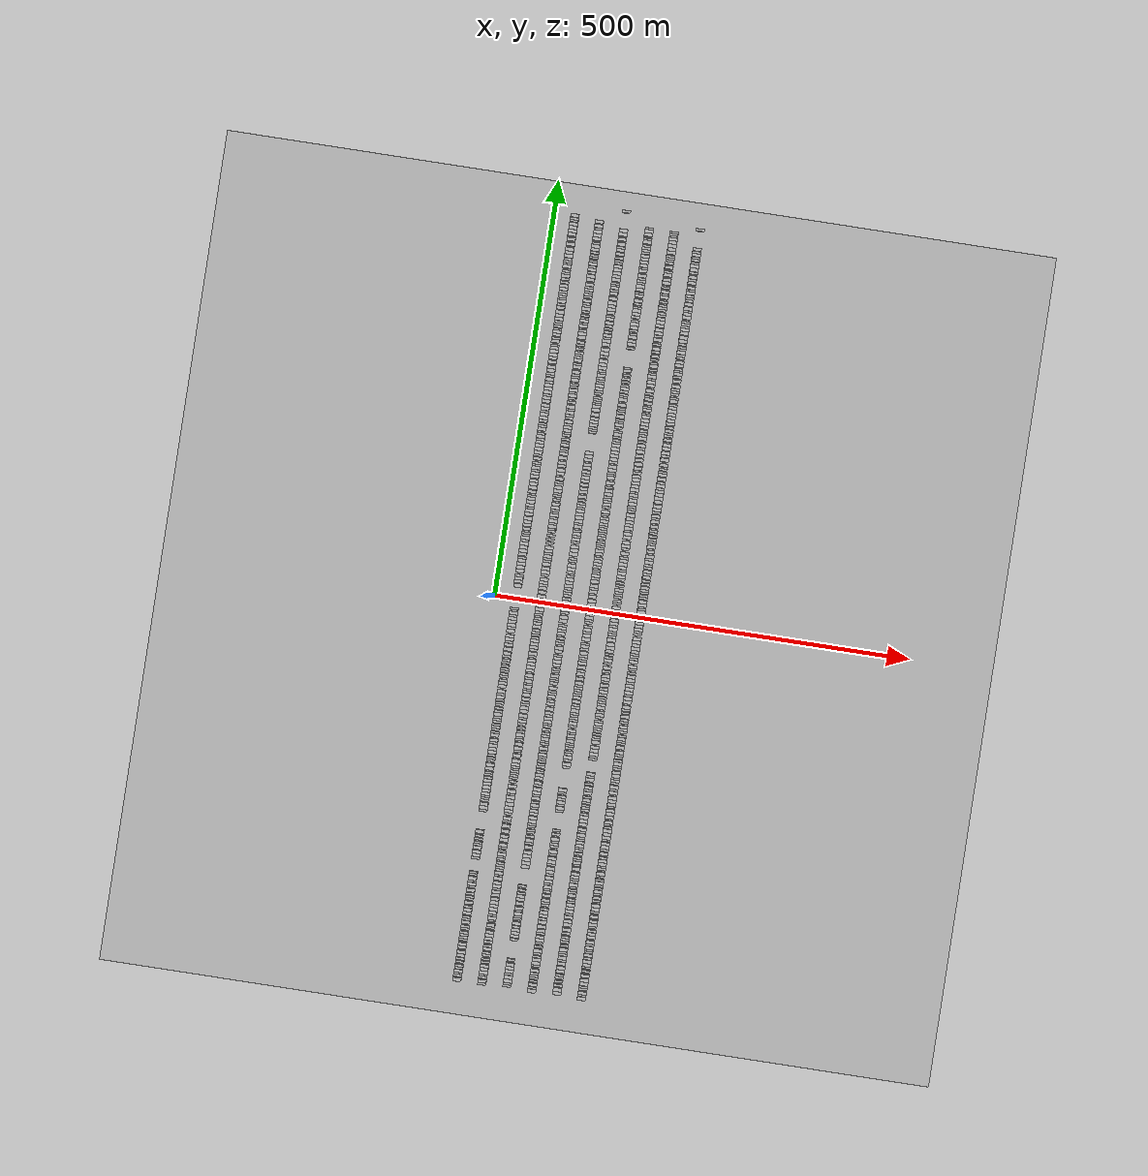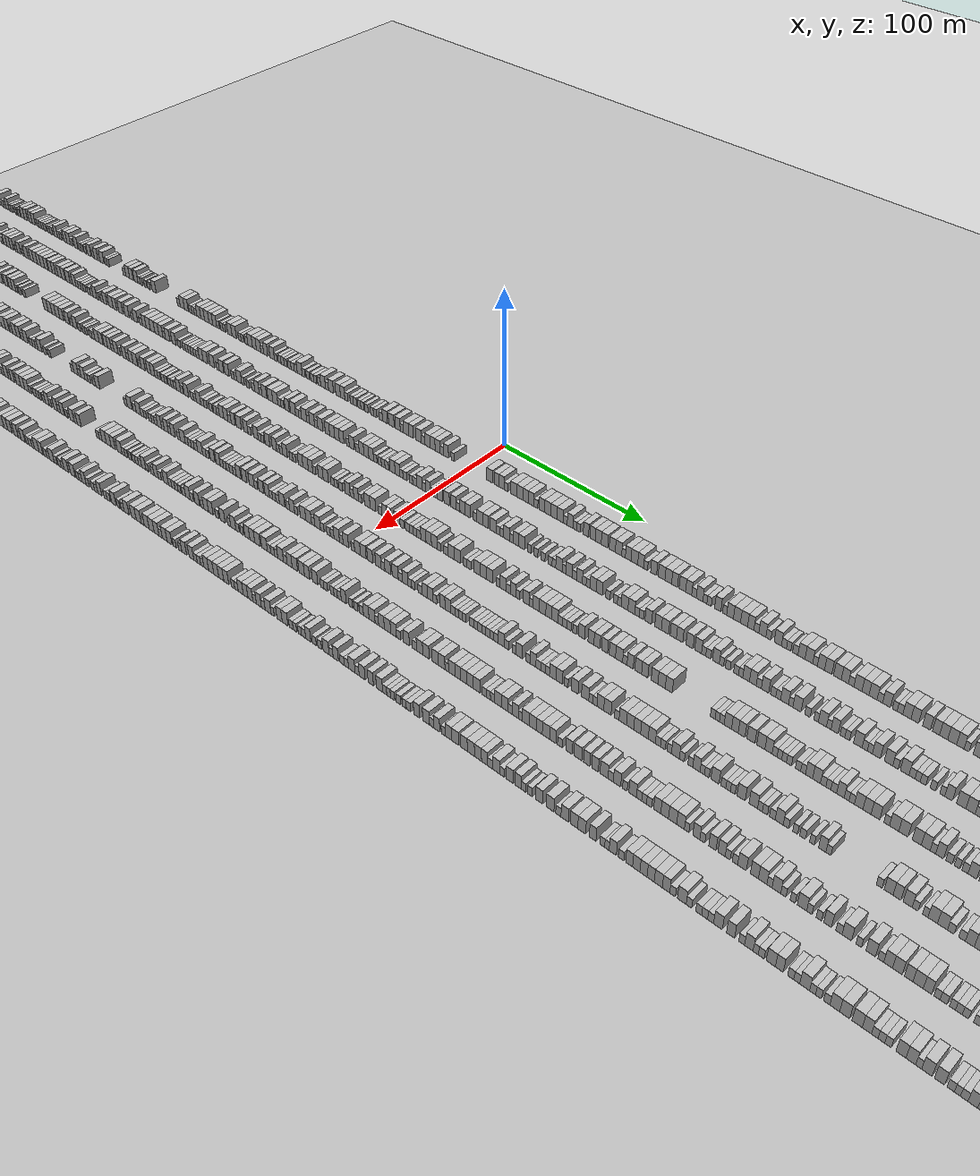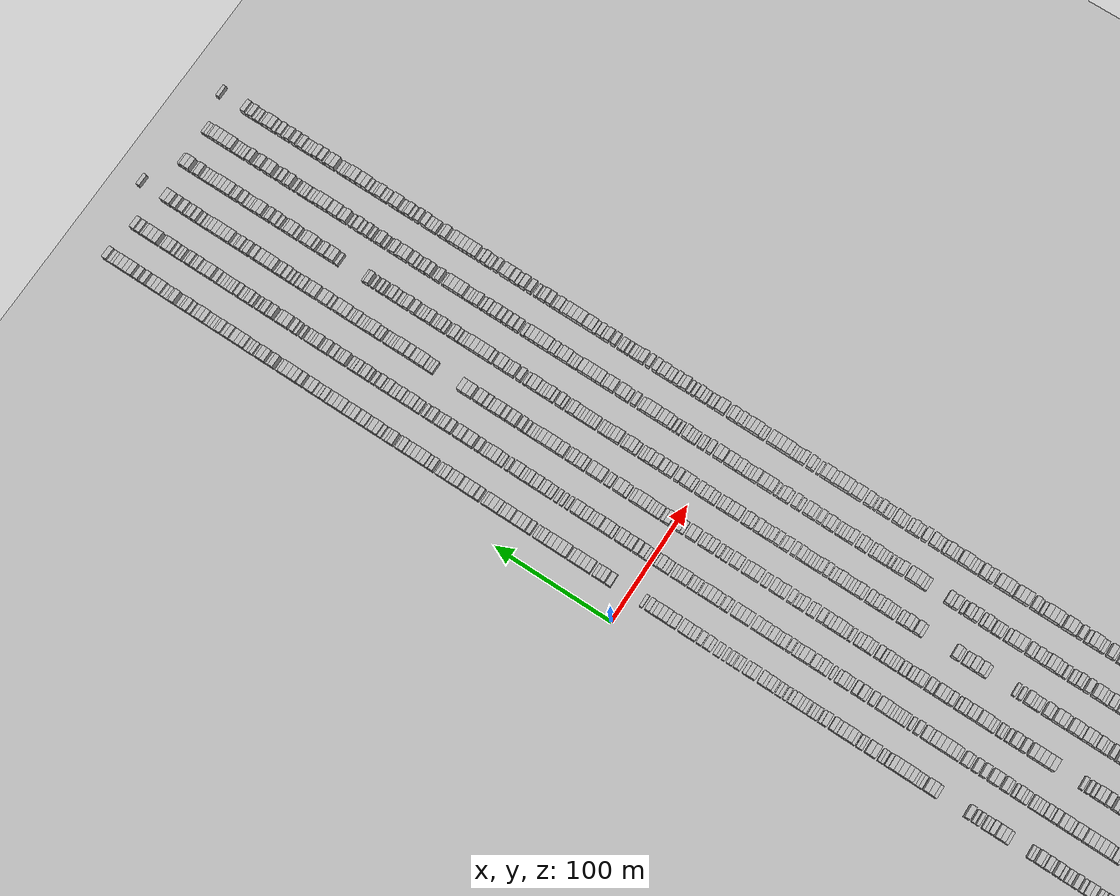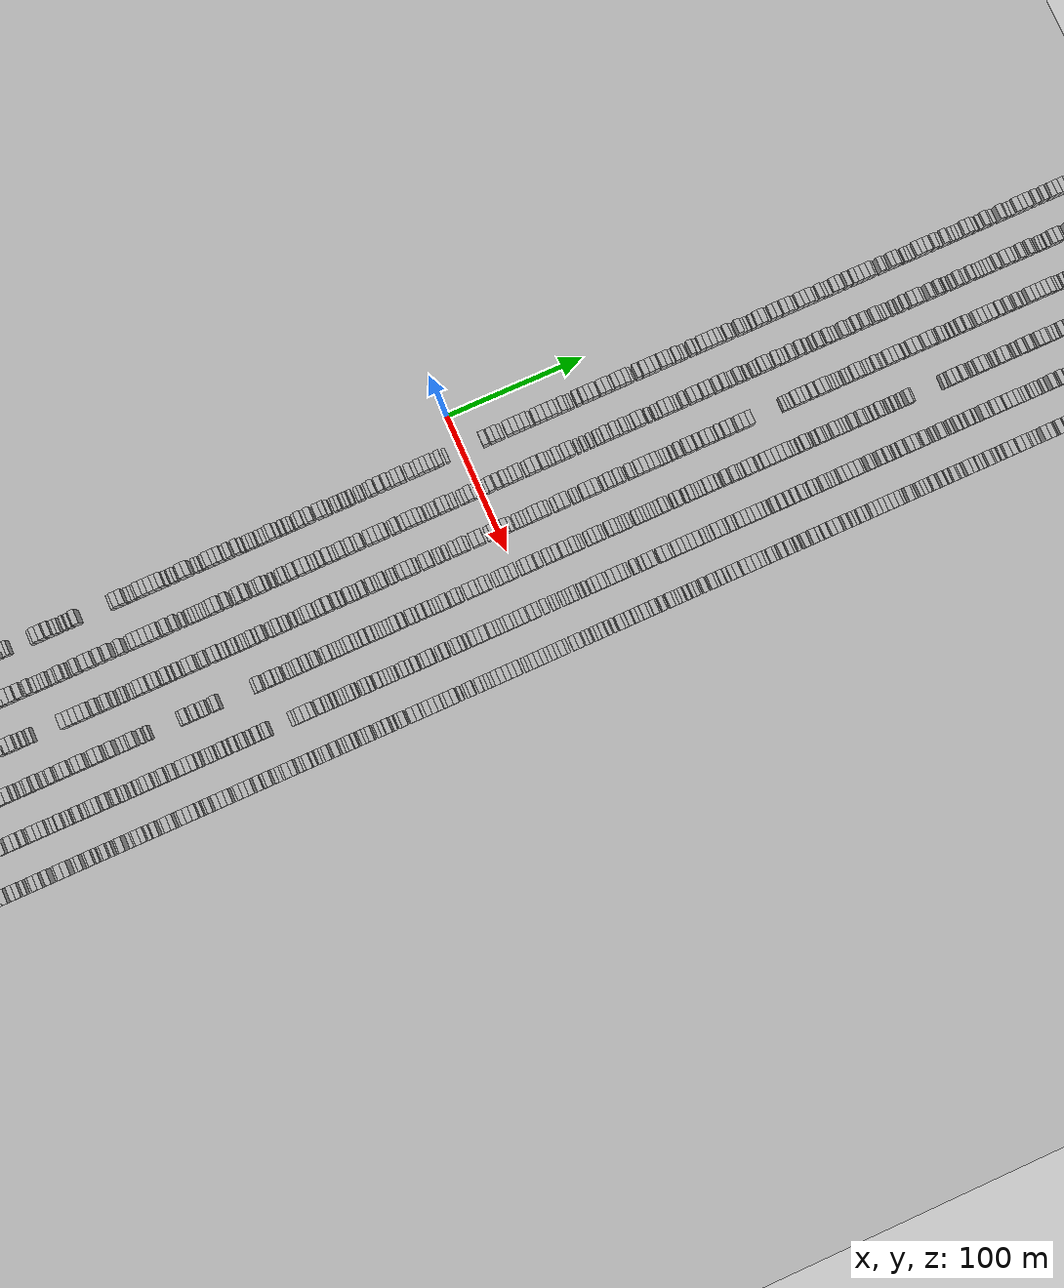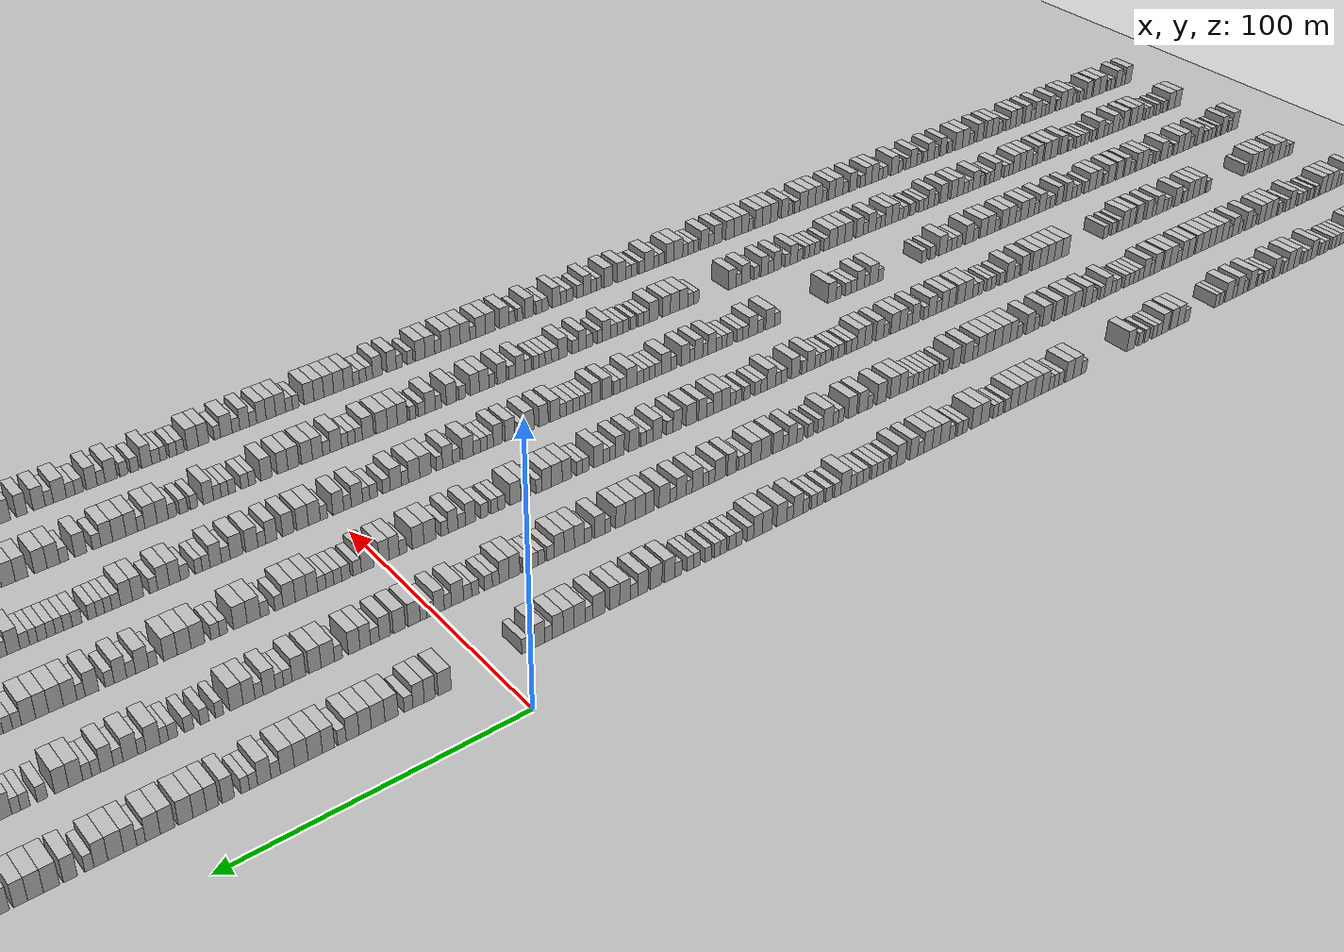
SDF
<sdf version="1.6">
 <world name="default">
  <scene>
   <sky><clouds><speed>12</speed></clouds></sky>
   <ambient>0.4 0.4 0.4 1</ambient>
   <background>0.7 0.7 0.7 1</background>
   <shadows>1</shadows>
  </scene>
  <gravity>0 0 -9.8066</gravity>
  <magnetic_field>6e-06 2.3e-05 -4.2e-05</magnetic_field>
  <physics default="0" name="default_physics" type="ode">
   <ode>
    <solver>
     <type>quick</type>
     <iters>10</iters>
     <sor>1.0</sor>
     <use_dynamic_moi_rescaling>0</use_dynamic_moi_rescaling>
    </solver>
    <constraints>
     <cfm>0</cfm>
     <erp>0.2</erp>
     <contact_max_correcting_vel>100</contact_max_correcting_vel>
     <contact_surface_layer>0.001</contact_surface_layer>
    </constraints>
   </ode>
   <max_step_size>0.004</max_step_size>
   <real_time_factor>1</real_time_factor>
   <real_time_update_rate>250</real_time_update_rate>
  </physics>
  <light name="sun" type="directional">
   <pose>0 0 10 0 0 0</pose>
   <diffuse>0.8 0.8 0.8 1</diffuse>
   <specular>0.2 0.2 0.2 1</specular>
   <attenuation>
    <range>1000</range>
    <constant>0.9</constant>
    <linear>0.01</linear>
    <quadratic>0.001</quadratic>
   </attenuation>
   <direction>-0.5 0.1 -0.9</direction>
  </light>
  <include><name>ground_plane_1</name><uri>model://HANNAS_ground_plane</uri></include>
  <include>
   <name>ground_plane_2</name>
   <uri>model://HANNAS_ground_plane</uri>
   <pose>100 0 0  0 0 0</pose>
  </include>
  <model name="building_1">
   <static>1</static>
   <pose>25.0000 -457.8146 0 0.000000 0.000000 0.000000</pose>
   <link name="link">
    <pose>0 0 4.50 0 0 0</pose>
    <collision name="collision"><geometry><box><size>10.0000 4.3709 9.0000</size></box></geometry></collision>
    <visual name="visual">
     <cast_shadows>0</cast_shadows>
     <geometry><box><size>10.0000 4.3709 9.0000</size></box></geometry>
     <material>
      <script>
       <uri>model://HANNAS_wall/materials/scripts</uri>
       <uri>model://HANNAS_wall/materials/textures</uri>
       <name>vrc/HANNAS_wall</name>
      </script>
     </material>
    </visual>
   </link>
  </model>
  <model name="building_2">
   <static>1</static>
   <pose>25.0000 -453.2266 0 0.000000 0.000000 0.000000</pose>
   <link name="link">
    <pose>0 0 3.00 0 0 0</pose>
    <collision name="collision"><geometry><box><size>10.0000 2.8049 6.0000</size></box></geometry></collision>
    <visual name="visual">
     <cast_shadows>0</cast_shadows>
     <geometry><box><size>10.0000 2.8049 6.0000</size></box></geometry>
     <material>
      <script>
       <uri>model://HANNAS_wall/materials/scripts</uri>
       <uri>model://HANNAS_wall/materials/textures</uri>
       <name>vrc/HANNAS_wall</name>
      </script>
     </material>
    </visual>
   </link>
  </model>
  <model name="building_3">
   <static>1</static>
   <pose>25.0000 -450.5729 0 0.000000 0.000000 0.000000</pose>
   <link name="link">
    <pose>0 0 3.00 0 0 0</pose>
    <collision name="collision"><geometry><box><size>10.0000 2.5025 6.0000</size></box></geometry></collision>
    <visual name="visual">
     <cast_shadows>0</cast_shadows>
     <geometry><box><size>10.0000 2.5025 6.0000</size></box></geometry>
     <material>
      <script>
       <uri>model://HANNAS_wall/materials/scripts</uri>
       <uri>model://HANNAS_wall/materials/textures</uri>
       <name>vrc/HANNAS_wall</name>
      </script>
     </material>
    </visual>
   </link>
  </model>
  <model name="building_4">
   <static>1</static>
   <pose>25.0000 -447.4680 0 0.000000 0.000000 0.000000</pose>
   <link name="link">
    <pose>0 0 4.50 0 0 0</pose>
    <collision name="collision"><geometry><box><size>10.0000 3.7072 9.0000</size></box></geometry></collision>
    <visual name="visual">
     <cast_shadows>0</cast_shadows>
     <geometry><box><size>10.0000 3.7072 9.0000</size></box></geometry>
     <material>
      <script>
       <uri>model://HANNAS_wall/materials/scripts</uri>
       <uri>model://HANNAS_wall/materials/textures</uri>
       <name>vrc/HANNAS_wall</name>
      </script>
     </material>
    </visual>
   </link>
  </model>
  <model name="building_5">
   <static>1</static>
   <pose>25.0000 -444.3006 0 0.000000 0.000000 0.000000</pose>
   <link name="link">
    <pose>0 0 3.00 0 0 0</pose>
    <collision name="collision"><geometry><box><size>10.0000 2.6276 6.0000</size></box></geometry></collision>
    <visual name="visual">
     <cast_shadows>0</cast_shadows>
     <geometry><box><size>10.0000 2.6276 6.0000</size></box></geometry>
     <material>
      <script>
       <uri>model://HANNAS_wall/materials/scripts</uri>
       <uri>model://HANNAS_wall/materials/textures</uri>
       <name>vrc/HANNAS_wall</name>
      </script>
     </material>
    </visual>
   </link>
  </model>
  <model name="building_6">
   <static>1</static>
   <pose>25.0000 -441.5114 0 0.000000 0.000000 0.000000</pose>
   <link name="link">
    <pose>0 0 3.00 0 0 0</pose>
    <collision name="collision"><geometry><box><size>10.0000 2.9508 6.0000</size></box></geometry></collision>
    <visual name="visual">
     <cast_shadows>0</cast_shadows>
     <geometry><box><size>10.0000 2.9508 6.0000</size></box></geometry>
     <material>
      <script>
       <uri>model://HANNAS_wall/materials/scripts</uri>
       <uri>model://HANNAS_wall/materials/textures</uri>
       <name>vrc/HANNAS_wall</name>
      </script>
     </material>
    </visual>
   </link>
  </model>
  <model name="building_7">
   <static>1</static>
   <pose>25.0000 -436.7794 0 0.000000 0.000000 0.000000</pose>
   <link name="link">
    <pose>0 0 3.00 0 0 0</pose>
    <collision name="collision"><geometry><box><size>10.0000 2.5132 6.0000</size></box></geometry></collision>
    <visual name="visual">
     <cast_shadows>0</cast_shadows>
     <geometry><box><size>10.0000 2.5132 6.0000</size></box></geometry>
     <material>
      <script>
       <uri>model://HANNAS_wall/materials/scripts</uri>
       <uri>model://HANNAS_wall/materials/textures</uri>
       <name>vrc/HANNAS_wall</name>
      </script>
     </material>
    </visual>
   </link>
  </model>
  <model name="building_8">
   <static>1</static>
   <pose>25.0000 -433.0568 0 0.000000 0.000000 0.000000</pose>
   <link name="link">
    <pose>0 0 3.00 0 0 0</pose>
    <collision name="collision"><geometry><box><size>10.0000 2.9321 6.0000</size></box></geometry></collision>
    <visual name="visual">
     <cast_shadows>0</cast_shadows>
     <geometry><box><size>10.0000 2.9321 6.0000</size></box></geometry>
     <material>
      <script>
       <uri>model://HANNAS_wall/materials/scripts</uri>
       <uri>model://HANNAS_wall/materials/textures</uri>
       <name>vrc/HANNAS_wall</name>
      </script>
     </material>
    </visual>
   </link>
  </model>
  <model name="building_9">
   <static>1</static>
   <pose>25.0000 -428.6497 0 0.000000 0.000000 0.000000</pose>
   <link name="link">
    <pose>0 0 4.50 0 0 0</pose>
    <collision name="collision"><geometry><box><size>10.0000 3.8821 9.0000</size></box></geometry></collision>
    <visual name="visual">
     <cast_shadows>0</cast_shadows>
     <geometry><box><size>10.0000 3.8821 9.0000</size></box></geometry>
     <material>
      <script>
       <uri>model://HANNAS_wall/materials/scripts</uri>
       <uri>model://HANNAS_wall/materials/textures</uri>
       <name>vrc/HANNAS_wall</name>
      </script>
     </material>
    </visual>
   </link>
  </model>
  <model name="building_10">
   <static>1</static>
   <pose>25.0000 -424.7814 0 0.000000 0.000000 0.000000</pose>
   <link name="link">
    <pose>0 0 4.50 0 0 0</pose>
    <collision name="collision"><geometry><box><size>10.0000 3.8546 9.0000</size></box></geometry></collision>
    <visual name="visual">
     <cast_shadows>0</cast_shadows>
     <geometry><box><size>10.0000 3.8546 9.0000</size></box></geometry>
     <material>
      <script>
       <uri>model://HANNAS_wall/materials/scripts</uri>
       <uri>model://HANNAS_wall/materials/textures</uri>
       <name>vrc/HANNAS_wall</name>
      </script>
     </material>
    </visual>
   </link>
  </model>
  <model name="building_11">
   <static>1</static>
   <pose>25.0000 -419.0202 0 0.000000 0.000000 0.000000</pose>
   <link name="link">
    <pose>0 0 4.50 0 0 0</pose>
    <collision name="collision"><geometry><box><size>10.0000 3.6678 9.0000</size></box></geometry></collision>
    <visual name="visual">
     <cast_shadows>0</cast_shadows>
     <geometry><box><size>10.0000 3.6678 9.0000</size></box></geometry>
     <material>
      <script>
       <uri>model://HANNAS_wall/materials/scripts</uri>
       <uri>model://HANNAS_wall/materials/textures</uri>
       <name>vrc/HANNAS_wall</name>
      </script>
     </material>
    </visual>
   </link>
  </model>
  <model name="building_12">
   <static>1</static>
   <pose>25.0000 -415.2905 0 0.000000 0.000000 0.000000</pose>
   <link name="link">
    <pose>0 0 4.50 0 0 0</pose>
    <collision name="collision"><geometry><box><size>10.0000 3.7915 9.0000</size></box></geometry></collision>
    <visual name="visual">
     <cast_shadows>0</cast_shadows>
     <geometry><box><size>10.0000 3.7915 9.0000</size></box></geometry>
     <material>
      <script>
       <uri>model://HANNAS_wall/materials/scripts</uri>
       <uri>model://HANNAS_wall/materials/textures</uri>
       <name>vrc/HANNAS_wall</name>
      </script>
     </material>
    </visual>
   </link>
  </model>
  <model name="building_13">
   <static>1</static>
   <pose>25.0000 -410.1460 0 0.000000 0.000000 0.000000</pose>
   <link name="link">
    <pose>0 0 3.00 0 0 0</pose>
    <collision name="collision"><geometry><box><size>10.0000 2.4976 6.0000</size></box></geometry></collision>
    <visual name="visual">
     <cast_shadows>0</cast_shadows>
     <geometry><box><size>10.0000 2.4976 6.0000</size></box></geometry>
     <material>
      <script>
       <uri>model://HANNAS_wall/materials/scripts</uri>
       <uri>model://HANNAS_wall/materials/textures</uri>
       <name>vrc/HANNAS_wall</name>
      </script>
     </material>
    </visual>
   </link>
  </model>
  <model name="building_14">
   <static>1</static>
   <pose>25.0000 -407.4100 0 0.000000 0.000000 0.000000</pose>
   <link name="link">
    <pose>0 0 3.00 0 0 0</pose>
    <collision name="collision"><geometry><box><size>10.0000 2.9745 6.0000</size></box></geometry></collision>
    <visual name="visual">
     <cast_shadows>0</cast_shadows>
     <geometry><box><size>10.0000 2.9745 6.0000</size></box></geometry>
     <material>
      <script>
       <uri>model://HANNAS_wall/materials/scripts</uri>
       <uri>model://HANNAS_wall/materials/textures</uri>
       <name>vrc/HANNAS_wall</name>
      </script>
     </material>
    </visual>
   </link>
  </model>
  <model name="building_15">
   <static>1</static>
   <pose>25.0000 -404.5269 0 0.000000 0.000000 0.000000</pose>
   <link name="link">
    <pose>0 0 3.00 0 0 0</pose>
    <collision name="collision"><geometry><box><size>10.0000 2.7917 6.0000</size></box></geometry></collision>
    <visual name="visual">
     <cast_shadows>0</cast_shadows>
     <geometry><box><size>10.0000 2.7917 6.0000</size></box></geometry>
     <material>
      <script>
       <uri>model://HANNAS_wall/materials/scripts</uri>
       <uri>model://HANNAS_wall/materials/textures</uri>
       <name>vrc/HANNAS_wall</name>
      </script>
     </material>
    </visual>
   </link>
  </model>
  <model name="building_16">
   <static>1</static>
   <pose>25.0000 -401.6657 0 0.000000 0.000000 0.000000</pose>
   <link name="link">
    <pose>0 0 3.00 0 0 0</pose>
    <collision name="collision"><geometry><box><size>10.0000 2.9307 6.0000</size></box></geometry></collision>
    <visual name="visual">
     <cast_shadows>0</cast_shadows>
     <geometry><box><size>10.0000 2.9307 6.0000</size></box></geometry>
     <material>
      <script>
       <uri>model://HANNAS_wall/materials/scripts</uri>
       <uri>model://HANNAS_wall/materials/textures</uri>
       <name>vrc/HANNAS_wall</name>
      </script>
     </material>
    </visual>
   </link>
  </model>
  <model name="building_17">
   <static>1</static>
   <pose>25.0000 -396.9440 0 0.000000 0.000000 0.000000</pose>
   <link name="link">
    <pose>0 0 3.00 0 0 0</pose>
    <collision name="collision"><geometry><box><size>10.0000 2.5125 6.0000</size></box></geometry></collision>
    <visual name="visual">
     <cast_shadows>0</cast_shadows>
     <geometry><box><size>10.0000 2.5125 6.0000</size></box></geometry>
     <material>
      <script>
       <uri>model://HANNAS_wall/materials/scripts</uri>
       <uri>model://HANNAS_wall/materials/textures</uri>
       <name>vrc/HANNAS_wall</name>
      </script>
     </material>
    </visual>
   </link>
  </model>
  <model name="building_18">
   <static>1</static>
   <pose>25.0000 -394.2146 0 0.000000 0.000000 0.000000</pose>
   <link name="link">
    <pose>0 0 3.00 0 0 0</pose>
    <collision name="collision"><geometry><box><size>10.0000 2.9463 6.0000</size></box></geometry></collision>
    <visual name="visual">
     <cast_shadows>0</cast_shadows>
     <geometry><box><size>10.0000 2.9463 6.0000</size></box></geometry>
     <material>
      <script>
       <uri>model://HANNAS_wall/materials/scripts</uri>
       <uri>model://HANNAS_wall/materials/textures</uri>
       <name>vrc/HANNAS_wall</name>
      </script>
     </material>
    </visual>
   </link>
  </model>
  <model name="building_19">
   <static>1</static>
   <pose>25.0000 -388.8456 0 0.000000 0.000000 0.000000</pose>
   <link name="link">
    <pose>0 0 4.50 0 0 0</pose>
    <collision name="collision"><geometry><box><size>10.0000 3.7918 9.0000</size></box></geometry></collision>
    <visual name="visual">
     <cast_shadows>0</cast_shadows>
     <geometry><box><size>10.0000 3.7918 9.0000</size></box></geometry>
     <material>
      <script>
       <uri>model://HANNAS_wall/materials/scripts</uri>
       <uri>model://HANNAS_wall/materials/textures</uri>
       <name>vrc/HANNAS_wall</name>
      </script>
     </material>
    </visual>
   </link>
  </model>
  <model name="building_20">
   <static>1</static>
   <pose>25.0000 -385.6355 0 0.000000 0.000000 0.000000</pose>
   <link name="link">
    <pose>0 0 3.00 0 0 0</pose>
    <collision name="collision"><geometry><box><size>10.0000 2.6284 6.0000</size></box></geometry></collision>
    <visual name="visual">
     <cast_shadows>0</cast_shadows>
     <geometry><box><size>10.0000 2.6284 6.0000</size></box></geometry>
     <material>
      <script>
       <uri>model://HANNAS_wall/materials/scripts</uri>
       <uri>model://HANNAS_wall/materials/textures</uri>
       <name>vrc/HANNAS_wall</name>
      </script>
     </material>
    </visual>
   </link>
  </model>
  <model name="building_21">
   <static>1</static>
   <pose>25.0000 -383.0062 0 0.000000 0.000000 0.000000</pose>
   <link name="link">
    <pose>0 0 3.00 0 0 0</pose>
    <collision name="collision"><geometry><box><size>10.0000 2.6303 6.0000</size></box></geometry></collision>
    <visual name="visual">
     <cast_shadows>0</cast_shadows>
     <geometry><box><size>10.0000 2.6303 6.0000</size></box></geometry>
     <material>
      <script>
       <uri>model://HANNAS_wall/materials/scripts</uri>
       <uri>model://HANNAS_wall/materials/textures</uri>
       <name>vrc/HANNAS_wall</name>
      </script>
     </material>
    </visual>
   </link>
  </model>
  <model name="building_22">
   <static>1</static>
   <pose>25.0000 -377.8843 0 0.000000 0.000000 0.000000</pose>
   <link name="link">
    <pose>0 0 4.50 0 0 0</pose>
    <collision name="collision"><geometry><box><size>10.0000 3.6136 9.0000</size></box></geometry></collision>
    <visual name="visual">
     <cast_shadows>0</cast_shadows>
     <geometry><box><size>10.0000 3.6136 9.0000</size></box></geometry>
     <material>
      <script>
       <uri>model://HANNAS_wall/materials/scripts</uri>
       <uri>model://HANNAS_wall/materials/textures</uri>
       <name>vrc/HANNAS_wall</name>
      </script>
     </material>
    </visual>
   </link>
  </model>
  <model name="building_23">
   <static>1</static>
   <pose>25.0000 -374.0628 0 0.000000 0.000000 0.000000</pose>
   <link name="link">
    <pose>0 0 4.50 0 0 0</pose>
    <collision name="collision"><geometry><box><size>10.0000 4.0295 9.0000</size></box></geometry></collision>
    <visual name="visual">
     <cast_shadows>0</cast_shadows>
     <geometry><box><size>10.0000 4.0295 9.0000</size></box></geometry>
     <material>
      <script>
       <uri>model://HANNAS_wall/materials/scripts</uri>
       <uri>model://HANNAS_wall/materials/textures</uri>
       <name>vrc/HANNAS_wall</name>
      </script>
     </material>
    </visual>
   </link>
  </model>
  <model name="building_24">
   <static>1</static>
   <pose>25.0000 -370.6754 0 0.000000 0.000000 0.000000</pose>
   <link name="link">
    <pose>0 0 3.00 0 0 0</pose>
    <collision name="collision"><geometry><box><size>10.0000 2.7452 6.0000</size></box></geometry></collision>
    <visual name="visual">
     <cast_shadows>0</cast_shadows>
     <geometry><box><size>10.0000 2.7452 6.0000</size></box></geometry>
     <material>
      <script>
       <uri>model://HANNAS_wall/materials/scripts</uri>
       <uri>model://HANNAS_wall/materials/textures</uri>
       <name>vrc/HANNAS_wall</name>
      </script>
     </material>
    </visual>
   </link>
  </model>
  <model name="building_25">
   <static>1</static>
   <pose>25.0000 -365.3675 0 0.000000 0.000000 0.000000</pose>
   <link name="link">
    <pose>0 0 4.50 0 0 0</pose>
    <collision name="collision"><geometry><box><size>10.0000 3.8706 9.0000</size></box></geometry></collision>
    <visual name="visual">
     <cast_shadows>0</cast_shadows>
     <geometry><box><size>10.0000 3.8706 9.0000</size></box></geometry>
     <material>
      <script>
       <uri>model://HANNAS_wall/materials/scripts</uri>
       <uri>model://HANNAS_wall/materials/textures</uri>
       <name>vrc/HANNAS_wall</name>
      </script>
     </material>
    </visual>
   </link>
  </model>
  <model name="building_26">
   <static>1</static>
   <pose>25.0000 -361.1058 0 0.000000 0.000000 0.000000</pose>
   <link name="link">
    <pose>0 0 3.00 0 0 0</pose>
    <collision name="collision"><geometry><box><size>10.0000 2.6527 6.0000</size></box></geometry></collision>
    <visual name="visual">
     <cast_shadows>0</cast_shadows>
     <geometry><box><size>10.0000 2.6527 6.0000</size></box></geometry>
     <material>
      <script>
       <uri>model://HANNAS_wall/materials/scripts</uri>
       <uri>model://HANNAS_wall/materials/textures</uri>
       <name>vrc/HANNAS_wall</name>
      </script>
     </material>
    </visual>
   </link>
  </model>
  <model name="building_27">
   <static>1</static>
   <pose>25.0000 -358.4939 0 0.000000 0.000000 0.000000</pose>
   <link name="link">
    <pose>0 0 3.00 0 0 0</pose>
    <collision name="collision"><geometry><box><size>10.0000 2.5711 6.0000</size></box></geometry></collision>
    <visual name="visual">
     <cast_shadows>0</cast_shadows>
     <geometry><box><size>10.0000 2.5711 6.0000</size></box></geometry>
     <material>
      <script>
       <uri>model://HANNAS_wall/materials/scripts</uri>
       <uri>model://HANNAS_wall/materials/textures</uri>
       <name>vrc/HANNAS_wall</name>
      </script>
     </material>
    </visual>
   </link>
  </model>
  <model name="building_28">
   <static>1</static>
   <pose>25.0000 -354.8271 0 0.000000 0.000000 0.000000</pose>
   <link name="link">
    <pose>0 0 3.00 0 0 0</pose>
    <collision name="collision"><geometry><box><size>10.0000 2.7625 6.0000</size></box></geometry></collision>
    <visual name="visual">
     <cast_shadows>0</cast_shadows>
     <geometry><box><size>10.0000 2.7625 6.0000</size></box></geometry>
     <material>
      <script>
       <uri>model://HANNAS_wall/materials/scripts</uri>
       <uri>model://HANNAS_wall/materials/textures</uri>
       <name>vrc/HANNAS_wall</name>
      </script>
     </material>
    </visual>
   </link>
  </model>
  <model name="building_29">
   <static>1</static>
   <pose>25.0000 -350.4248 0 0.000000 0.000000 0.000000</pose>
   <link name="link">
    <pose>0 0 4.50 0 0 0</pose>
    <collision name="collision"><geometry><box><size>10.0000 4.0422 9.0000</size></box></geometry></collision>
    <visual name="visual">
     <cast_shadows>0</cast_shadows>
     <geometry><box><size>10.0000 4.0422 9.0000</size></box></geometry>
     <material>
      <script>
       <uri>model://HANNAS_wall/materials/scripts</uri>
       <uri>model://HANNAS_wall/materials/textures</uri>
       <name>vrc/HANNAS_wall</name>
      </script>
     </material>
    </visual>
   </link>
  </model>
  <model name="building_30">
   <static>1</static>
   <pose>25.0000 -346.1269 0 0.000000 0.000000 0.000000</pose>
   <link name="link">
    <pose>0 0 3.00 0 0 0</pose>
    <collision name="collision"><geometry><box><size>10.0000 2.5535 6.0000</size></box></geometry></collision>
    <visual name="visual">
     <cast_shadows>0</cast_shadows>
     <geometry><box><size>10.0000 2.5535 6.0000</size></box></geometry>
     <material>
      <script>
       <uri>model://HANNAS_wall/materials/scripts</uri>
       <uri>model://HANNAS_wall/materials/textures</uri>
       <name>vrc/HANNAS_wall</name>
      </script>
     </material>
    </visual>
   </link>
  </model>
  <model name="building_31">
   <static>1</static>
   <pose>25.0000 -342.8684 0 0.000000 0.000000 0.000000</pose>
   <link name="link">
    <pose>0 0 4.50 0 0 0</pose>
    <collision name="collision"><geometry><box><size>10.0000 3.9636 9.0000</size></box></geometry></collision>
    <visual name="visual">
     <cast_shadows>0</cast_shadows>
     <geometry><box><size>10.0000 3.9636 9.0000</size></box></geometry>
     <material>
      <script>
       <uri>model://HANNAS_wall/materials/scripts</uri>
       <uri>model://HANNAS_wall/materials/textures</uri>
       <name>vrc/HANNAS_wall</name>
      </script>
     </material>
    </visual>
   </link>
  </model>
  <model name="building_32">
   <static>1</static>
   <pose>25.0000 -339.6265 0 0.000000 0.000000 0.000000</pose>
   <link name="link">
    <pose>0 0 3.00 0 0 0</pose>
    <collision name="collision"><geometry><box><size>10.0000 2.5201 6.0000</size></box></geometry></collision>
    <visual name="visual">
     <cast_shadows>0</cast_shadows>
     <geometry><box><size>10.0000 2.5201 6.0000</size></box></geometry>
     <material>
      <script>
       <uri>model://HANNAS_wall/materials/scripts</uri>
       <uri>model://HANNAS_wall/materials/textures</uri>
       <name>vrc/HANNAS_wall</name>
      </script>
     </material>
    </visual>
   </link>
  </model>
  <model name="building_33">
   <static>1</static>
   <pose>25.0000 -336.1304 0 0.000000 0.000000 0.000000</pose>
   <link name="link">
    <pose>0 0 4.50 0 0 0</pose>
    <collision name="collision"><geometry><box><size>10.0000 4.4721 9.0000</size></box></geometry></collision>
    <visual name="visual">
     <cast_shadows>0</cast_shadows>
     <geometry><box><size>10.0000 4.4721 9.0000</size></box></geometry>
     <material>
      <script>
       <uri>model://HANNAS_wall/materials/scripts</uri>
       <uri>model://HANNAS_wall/materials/textures</uri>
       <name>vrc/HANNAS_wall</name>
      </script>
     </material>
    </visual>
   </link>
  </model>
  <model name="building_34">
   <static>1</static>
   <pose>25.0000 -331.6610 0 0.000000 0.000000 0.000000</pose>
   <link name="link">
    <pose>0 0 3.00 0 0 0</pose>
    <collision name="collision"><geometry><box><size>10.0000 2.4667 6.0000</size></box></geometry></collision>
    <visual name="visual">
     <cast_shadows>0</cast_shadows>
     <geometry><box><size>10.0000 2.4667 6.0000</size></box></geometry>
     <material>
      <script>
       <uri>model://HANNAS_wall/materials/scripts</uri>
       <uri>model://HANNAS_wall/materials/textures</uri>
       <name>vrc/HANNAS_wall</name>
      </script>
     </material>
    </visual>
   </link>
  </model>
  <model name="building_35">
   <static>1</static>
   <pose>25.0000 -329.1813 0 0.000000 0.000000 0.000000</pose>
   <link name="link">
    <pose>0 0 3.00 0 0 0</pose>
    <collision name="collision"><geometry><box><size>10.0000 2.4926 6.0000</size></box></geometry></collision>
    <visual name="visual">
     <cast_shadows>0</cast_shadows>
     <geometry><box><size>10.0000 2.4926 6.0000</size></box></geometry>
     <material>
      <script>
       <uri>model://HANNAS_wall/materials/scripts</uri>
       <uri>model://HANNAS_wall/materials/textures</uri>
       <name>vrc/HANNAS_wall</name>
      </script>
     </material>
    </visual>
   </link>
  </model>
  <model name="building_36">
   <static>1</static>
   <pose>25.0000 -311.4867 0 0.000000 0.000000 0.000000</pose>
   <link name="link">
    <pose>0 0 3.00 0 0 0</pose>
    <collision name="collision"><geometry><box><size>10.0000 2.9656 6.0000</size></box></geometry></collision>
    <visual name="visual">
     <cast_shadows>0</cast_shadows>
     <geometry><box><size>10.0000 2.9656 6.0000</size></box></geometry>
     <material>
      <script>
       <uri>model://HANNAS_wall/materials/scripts</uri>
       <uri>model://HANNAS_wall/materials/textures</uri>
       <name>vrc/HANNAS_wall</name>
      </script>
     </material>
    </visual>
   </link>
  </model>
  <model name="building_37">
   <static>1</static>
   <pose>25.0000 -308.0392 0 0.000000 0.000000 0.000000</pose>
   <link name="link">
    <pose>0 0 4.50 0 0 0</pose>
    <collision name="collision"><geometry><box><size>10.0000 3.9294 9.0000</size></box></geometry></collision>
    <visual name="visual">
     <cast_shadows>0</cast_shadows>
     <geometry><box><size>10.0000 3.9294 9.0000</size></box></geometry>
     <material>
      <script>
       <uri>model://HANNAS_wall/materials/scripts</uri>
       <uri>model://HANNAS_wall/materials/textures</uri>
       <name>vrc/HANNAS_wall</name>
      </script>
     </material>
    </visual>
   </link>
  </model>
  <model name="building_38">
   <static>1</static>
   <pose>25.0000 -304.0724 0 0.000000 0.000000 0.000000</pose>
   <link name="link">
    <pose>0 0 4.50 0 0 0</pose>
    <collision name="collision"><geometry><box><size>10.0000 4.0042 9.0000</size></box></geometry></collision>
    <visual name="visual">
     <cast_shadows>0</cast_shadows>
     <geometry><box><size>10.0000 4.0042 9.0000</size></box></geometry>
     <material>
      <script>
       <uri>model://HANNAS_wall/materials/scripts</uri>
       <uri>model://HANNAS_wall/materials/textures</uri>
       <name>vrc/HANNAS_wall</name>
      </script>
     </material>
    </visual>
   </link>
  </model>
  <model name="building_39">
   <static>1</static>
   <pose>25.0000 -299.0777 0 0.000000 0.000000 0.000000</pose>
   <link name="link">
    <pose>0 0 4.50 0 0 0</pose>
    <collision name="collision"><geometry><box><size>10.0000 3.9851 9.0000</size></box></geometry></collision>
    <visual name="visual">
     <cast_shadows>0</cast_shadows>
     <geometry><box><size>10.0000 3.9851 9.0000</size></box></geometry>
     <material>
      <script>
       <uri>model://HANNAS_wall/materials/scripts</uri>
       <uri>model://HANNAS_wall/materials/textures</uri>
       <name>vrc/HANNAS_wall</name>
      </script>
     </material>
    </visual>
   </link>
  </model>
  <model name="building_40">
   <static>1</static>
   <pose>25.0000 -295.7361 0 0.000000 0.000000 0.000000</pose>
   <link name="link">
    <pose>0 0 3.00 0 0 0</pose>
    <collision name="collision"><geometry><box><size>10.0000 2.6982 6.0000</size></box></geometry></collision>
    <visual name="visual">
     <cast_shadows>0</cast_shadows>
     <geometry><box><size>10.0000 2.6982 6.0000</size></box></geometry>
     <material>
      <script>
       <uri>model://HANNAS_wall/materials/scripts</uri>
       <uri>model://HANNAS_wall/materials/textures</uri>
       <name>vrc/HANNAS_wall</name>
      </script>
     </material>
    </visual>
   </link>
  </model>
  <model name="building_41">
   <static>1</static>
   <pose>25.0000 -293.1766 0 0.000000 0.000000 0.000000</pose>
   <link name="link">
    <pose>0 0 3.00 0 0 0</pose>
    <collision name="collision"><geometry><box><size>10.0000 2.4207 6.0000</size></box></geometry></collision>
    <visual name="visual">
     <cast_shadows>0</cast_shadows>
     <geometry><box><size>10.0000 2.4207 6.0000</size></box></geometry>
     <material>
      <script>
       <uri>model://HANNAS_wall/materials/scripts</uri>
       <uri>model://HANNAS_wall/materials/textures</uri>
       <name>vrc/HANNAS_wall</name>
      </script>
     </material>
    </visual>
   </link>
  </model>
  <model name="building_42">
   <static>1</static>
   <pose>25.0000 -288.7385 0 0.000000 0.000000 0.000000</pose>
   <link name="link">
    <pose>0 0 3.00 0 0 0</pose>
    <collision name="collision"><geometry><box><size>10.0000 2.4556 6.0000</size></box></geometry></collision>
    <visual name="visual">
     <cast_shadows>0</cast_shadows>
     <geometry><box><size>10.0000 2.4556 6.0000</size></box></geometry>
     <material>
      <script>
       <uri>model://HANNAS_wall/materials/scripts</uri>
       <uri>model://HANNAS_wall/materials/textures</uri>
       <name>vrc/HANNAS_wall</name>
      </script>
     </material>
    </visual>
   </link>
  </model>
  <model name="building_43">
   <static>1</static>
   <pose>25.0000 -285.2317 0 0.000000 0.000000 0.000000</pose>
   <link name="link">
    <pose>0 0 3.00 0 0 0</pose>
    <collision name="collision"><geometry><box><size>10.0000 2.5578 6.0000</size></box></geometry></collision>
    <visual name="visual">
     <cast_shadows>0</cast_shadows>
     <geometry><box><size>10.0000 2.5578 6.0000</size></box></geometry>
     <material>
      <script>
       <uri>model://HANNAS_wall/materials/scripts</uri>
       <uri>model://HANNAS_wall/materials/textures</uri>
       <name>vrc/HANNAS_wall</name>
      </script>
     </material>
    </visual>
   </link>
  </model>
  <model name="building_44">
   <static>1</static>
   <pose>25.0000 -279.8387 0 0.000000 0.000000 0.000000</pose>
   <link name="link">
    <pose>0 0 4.50 0 0 0</pose>
    <collision name="collision"><geometry><box><size>10.0000 4.2283 9.0000</size></box></geometry></collision>
    <visual name="visual">
     <cast_shadows>0</cast_shadows>
     <geometry><box><size>10.0000 4.2283 9.0000</size></box></geometry>
     <material>
      <script>
       <uri>model://HANNAS_wall/materials/scripts</uri>
       <uri>model://HANNAS_wall/materials/textures</uri>
       <name>vrc/HANNAS_wall</name>
      </script>
     </material>
    </visual>
   </link>
  </model>
  <model name="building_45">
   <static>1</static>
   <pose>25.0000 -254.4149 0 0.000000 0.000000 0.000000</pose>
   <link name="link">
    <pose>0 0 3.00 0 0 0</pose>
    <collision name="collision"><geometry><box><size>10.0000 2.8730 6.0000</size></box></geometry></collision>
    <visual name="visual">
     <cast_shadows>0</cast_shadows>
     <geometry><box><size>10.0000 2.8730 6.0000</size></box></geometry>
     <material>
      <script>
       <uri>model://HANNAS_wall/materials/scripts</uri>
       <uri>model://HANNAS_wall/materials/textures</uri>
       <name>vrc/HANNAS_wall</name>
      </script>
     </material>
    </visual>
   </link>
  </model>
  <model name="building_46">
   <static>1</static>
   <pose>25.0000 -250.8645 0 0.000000 0.000000 0.000000</pose>
   <link name="link">
    <pose>0 0 4.50 0 0 0</pose>
    <collision name="collision"><geometry><box><size>10.0000 4.2280 9.0000</size></box></geometry></collision>
    <visual name="visual">
     <cast_shadows>0</cast_shadows>
     <geometry><box><size>10.0000 4.2280 9.0000</size></box></geometry>
     <material>
      <script>
       <uri>model://HANNAS_wall/materials/scripts</uri>
       <uri>model://HANNAS_wall/materials/textures</uri>
       <name>vrc/HANNAS_wall</name>
      </script>
     </material>
    </visual>
   </link>
  </model>
  <model name="building_47">
   <static>1</static>
   <pose>25.0000 -246.7290 0 0.000000 0.000000 0.000000</pose>
   <link name="link">
    <pose>0 0 4.50 0 0 0</pose>
    <collision name="collision"><geometry><box><size>10.0000 4.0431 9.0000</size></box></geometry></collision>
    <visual name="visual">
     <cast_shadows>0</cast_shadows>
     <geometry><box><size>10.0000 4.0431 9.0000</size></box></geometry>
     <material>
      <script>
       <uri>model://HANNAS_wall/materials/scripts</uri>
       <uri>model://HANNAS_wall/materials/textures</uri>
       <name>vrc/HANNAS_wall</name>
      </script>
     </material>
    </visual>
   </link>
  </model>
  <model name="building_48">
   <static>1</static>
   <pose>25.0000 -242.3892 0 0.000000 0.000000 0.000000</pose>
   <link name="link">
    <pose>0 0 3.00 0 0 0</pose>
    <collision name="collision"><geometry><box><size>10.0000 2.6364 6.0000</size></box></geometry></collision>
    <visual name="visual">
     <cast_shadows>0</cast_shadows>
     <geometry><box><size>10.0000 2.6364 6.0000</size></box></geometry>
     <material>
      <script>
       <uri>model://HANNAS_wall/materials/scripts</uri>
       <uri>model://HANNAS_wall/materials/textures</uri>
       <name>vrc/HANNAS_wall</name>
      </script>
     </material>
    </visual>
   </link>
  </model>
  <model name="building_49">
   <static>1</static>
   <pose>25.0000 -239.8340 0 0.000000 0.000000 0.000000</pose>
   <link name="link">
    <pose>0 0 3.00 0 0 0</pose>
    <collision name="collision"><geometry><box><size>10.0000 2.4740 6.0000</size></box></geometry></collision>
    <visual name="visual">
     <cast_shadows>0</cast_shadows>
     <geometry><box><size>10.0000 2.4740 6.0000</size></box></geometry>
     <material>
      <script>
       <uri>model://HANNAS_wall/materials/scripts</uri>
       <uri>model://HANNAS_wall/materials/textures</uri>
       <name>vrc/HANNAS_wall</name>
      </script>
     </material>
    </visual>
   </link>
  </model>
  <model name="building_50">
   <static>1</static>
   <pose>25.0000 -237.3572 0 0.000000 0.000000 0.000000</pose>
   <link name="link">
    <pose>0 0 3.00 0 0 0</pose>
    <collision name="collision"><geometry><box><size>10.0000 2.4794 6.0000</size></box></geometry></collision>
    <visual name="visual">
     <cast_shadows>0</cast_shadows>
     <geometry><box><size>10.0000 2.4794 6.0000</size></box></geometry>
     <material>
      <script>
       <uri>model://HANNAS_wall/materials/scripts</uri>
       <uri>model://HANNAS_wall/materials/textures</uri>
       <name>vrc/HANNAS_wall</name>
      </script>
     </material>
    </visual>
   </link>
  </model>
  <model name="building_51">
   <static>1</static>
   <pose>25.0000 -234.1744 0 0.000000 0.000000 0.000000</pose>
   <link name="link">
    <pose>0 0 4.50 0 0 0</pose>
    <collision name="collision"><geometry><box><size>10.0000 3.8864 9.0000</size></box></geometry></collision>
    <visual name="visual">
     <cast_shadows>0</cast_shadows>
     <geometry><box><size>10.0000 3.8864 9.0000</size></box></geometry>
     <material>
      <script>
       <uri>model://HANNAS_wall/materials/scripts</uri>
       <uri>model://HANNAS_wall/materials/textures</uri>
       <name>vrc/HANNAS_wall</name>
      </script>
     </material>
    </visual>
   </link>
  </model>
  <model name="building_52">
   <static>1</static>
   <pose>25.0000 -230.3810 0 0.000000 0.000000 0.000000</pose>
   <link name="link">
    <pose>0 0 4.50 0 0 0</pose>
    <collision name="collision"><geometry><box><size>10.0000 3.7002 9.0000</size></box></geometry></collision>
    <visual name="visual">
     <cast_shadows>0</cast_shadows>
     <geometry><box><size>10.0000 3.7002 9.0000</size></box></geometry>
     <material>
      <script>
       <uri>model://HANNAS_wall/materials/scripts</uri>
       <uri>model://HANNAS_wall/materials/textures</uri>
       <name>vrc/HANNAS_wall</name>
      </script>
     </material>
    </visual>
   </link>
  </model>
  <model name="building_53">
   <static>1</static>
   <pose>25.0000 -226.3039 0 0.000000 0.000000 0.000000</pose>
   <link name="link">
    <pose>0 0 4.50 0 0 0</pose>
    <collision name="collision"><geometry><box><size>10.0000 4.4540 9.0000</size></box></geometry></collision>
    <visual name="visual">
     <cast_shadows>0</cast_shadows>
     <geometry><box><size>10.0000 4.4540 9.0000</size></box></geometry>
     <material>
      <script>
       <uri>model://HANNAS_wall/materials/scripts</uri>
       <uri>model://HANNAS_wall/materials/textures</uri>
       <name>vrc/HANNAS_wall</name>
      </script>
     </material>
    </visual>
   </link>
  </model>
  <model name="building_54">
   <static>1</static>
   <pose>25.0000 -222.2061 0 0.000000 0.000000 0.000000</pose>
   <link name="link">
    <pose>0 0 4.50 0 0 0</pose>
    <collision name="collision"><geometry><box><size>10.0000 3.7416 9.0000</size></box></geometry></collision>
    <visual name="visual">
     <cast_shadows>0</cast_shadows>
     <geometry><box><size>10.0000 3.7416 9.0000</size></box></geometry>
     <material>
      <script>
       <uri>model://HANNAS_wall/materials/scripts</uri>
       <uri>model://HANNAS_wall/materials/textures</uri>
       <name>vrc/HANNAS_wall</name>
      </script>
     </material>
    </visual>
   </link>
  </model>
  <model name="building_55">
   <static>1</static>
   <pose>25.0000 -218.3977 0 0.000000 0.000000 0.000000</pose>
   <link name="link">
    <pose>0 0 4.50 0 0 0</pose>
    <collision name="collision"><geometry><box><size>10.0000 3.8752 9.0000</size></box></geometry></collision>
    <visual name="visual">
     <cast_shadows>0</cast_shadows>
     <geometry><box><size>10.0000 3.8752 9.0000</size></box></geometry>
     <material>
      <script>
       <uri>model://HANNAS_wall/materials/scripts</uri>
       <uri>model://HANNAS_wall/materials/textures</uri>
       <name>vrc/HANNAS_wall</name>
      </script>
     </material>
    </visual>
   </link>
  </model>
  <model name="building_56">
   <static>1</static>
   <pose>25.0000 -215.0832 0 0.000000 0.000000 0.000000</pose>
   <link name="link">
    <pose>0 0 3.00 0 0 0</pose>
    <collision name="collision"><geometry><box><size>10.0000 2.7538 6.0000</size></box></geometry></collision>
    <visual name="visual">
     <cast_shadows>0</cast_shadows>
     <geometry><box><size>10.0000 2.7538 6.0000</size></box></geometry>
     <material>
      <script>
       <uri>model://HANNAS_wall/materials/scripts</uri>
       <uri>model://HANNAS_wall/materials/textures</uri>
       <name>vrc/HANNAS_wall</name>
      </script>
     </material>
    </visual>
   </link>
  </model>
  <model name="building_57">
   <static>1</static>
   <pose>25.0000 -211.4747 0 0.000000 0.000000 0.000000</pose>
   <link name="link">
    <pose>0 0 3.00 0 0 0</pose>
    <collision name="collision"><geometry><box><size>10.0000 2.4631 6.0000</size></box></geometry></collision>
    <visual name="visual">
     <cast_shadows>0</cast_shadows>
     <geometry><box><size>10.0000 2.4631 6.0000</size></box></geometry>
     <material>
      <script>
       <uri>model://HANNAS_wall/materials/scripts</uri>
       <uri>model://HANNAS_wall/materials/textures</uri>
       <name>vrc/HANNAS_wall</name>
      </script>
     </material>
    </visual>
   </link>
  </model>
  <model name="building_58">
   <static>1</static>
   <pose>25.0000 -209.0251 0 0.000000 0.000000 0.000000</pose>
   <link name="link">
    <pose>0 0 3.00 0 0 0</pose>
    <collision name="collision"><geometry><box><size>10.0000 2.4362 6.0000</size></box></geometry></collision>
    <visual name="visual">
     <cast_shadows>0</cast_shadows>
     <geometry><box><size>10.0000 2.4362 6.0000</size></box></geometry>
     <material>
      <script>
       <uri>model://HANNAS_wall/materials/scripts</uri>
       <uri>model://HANNAS_wall/materials/textures</uri>
       <name>vrc/HANNAS_wall</name>
      </script>
     </material>
    </visual>
   </link>
  </model>
  <model name="building_59">
   <static>1</static>
   <pose>25.0000 -203.7459 0 0.000000 0.000000 0.000000</pose>
   <link name="link">
    <pose>0 0 4.50 0 0 0</pose>
    <collision name="collision"><geometry><box><size>10.0000 4.1222 9.0000</size></box></geometry></collision>
    <visual name="visual">
     <cast_shadows>0</cast_shadows>
     <geometry><box><size>10.0000 4.1222 9.0000</size></box></geometry>
     <material>
      <script>
       <uri>model://HANNAS_wall/materials/scripts</uri>
       <uri>model://HANNAS_wall/materials/textures</uri>
       <name>vrc/HANNAS_wall</name>
      </script>
     </material>
    </visual>
   </link>
  </model>
  <model name="building_60">
   <static>1</static>
   <pose>25.0000 -199.5396 0 0.000000 0.000000 0.000000</pose>
   <link name="link">
    <pose>0 0 4.50 0 0 0</pose>
    <collision name="collision"><geometry><box><size>10.0000 4.2904 9.0000</size></box></geometry></collision>
    <visual name="visual">
     <cast_shadows>0</cast_shadows>
     <geometry><box><size>10.0000 4.2904 9.0000</size></box></geometry>
     <material>
      <script>
       <uri>model://HANNAS_wall/materials/scripts</uri>
       <uri>model://HANNAS_wall/materials/textures</uri>
       <name>vrc/HANNAS_wall</name>
      </script>
     </material>
    </visual>
   </link>
  </model>
  <model name="building_61">
   <static>1</static>
   <pose>25.0000 -194.0951 0 0.000000 0.000000 0.000000</pose>
   <link name="link">
    <pose>0 0 3.00 0 0 0</pose>
    <collision name="collision"><geometry><box><size>10.0000 2.5987 6.0000</size></box></geometry></collision>
    <visual name="visual">
     <cast_shadows>0</cast_shadows>
     <geometry><box><size>10.0000 2.5987 6.0000</size></box></geometry>
     <material>
      <script>
       <uri>model://HANNAS_wall/materials/scripts</uri>
       <uri>model://HANNAS_wall/materials/textures</uri>
       <name>vrc/HANNAS_wall</name>
      </script>
     </material>
    </visual>
   </link>
  </model>
  <model name="building_62">
   <static>1</static>
   <pose>25.0000 -191.5553 0 0.000000 0.000000 0.000000</pose>
   <link name="link">
    <pose>0 0 3.00 0 0 0</pose>
    <collision name="collision"><geometry><box><size>10.0000 2.4808 6.0000</size></box></geometry></collision>
    <visual name="visual">
     <cast_shadows>0</cast_shadows>
     <geometry><box><size>10.0000 2.4808 6.0000</size></box></geometry>
     <material>
      <script>
       <uri>model://HANNAS_wall/materials/scripts</uri>
       <uri>model://HANNAS_wall/materials/textures</uri>
       <name>vrc/HANNAS_wall</name>
      </script>
     </material>
    </visual>
   </link>
  </model>
  <model name="building_63">
   <static>1</static>
   <pose>25.0000 -187.9170 0 0.000000 0.000000 0.000000</pose>
   <link name="link">
    <pose>0 0 3.00 0 0 0</pose>
    <collision name="collision"><geometry><box><size>10.0000 2.7958 6.0000</size></box></geometry></collision>
    <visual name="visual">
     <cast_shadows>0</cast_shadows>
     <geometry><box><size>10.0000 2.7958 6.0000</size></box></geometry>
     <material>
      <script>
       <uri>model://HANNAS_wall/materials/scripts</uri>
       <uri>model://HANNAS_wall/materials/textures</uri>
       <name>vrc/HANNAS_wall</name>
      </script>
     </material>
    </visual>
   </link>
  </model>
  <model name="building_64">
   <static>1</static>
   <pose>25.0000 -184.3635 0 0.000000 0.000000 0.000000</pose>
   <link name="link">
    <pose>0 0 4.50 0 0 0</pose>
    <collision name="collision"><geometry><box><size>10.0000 4.3112 9.0000</size></box></geometry></collision>
    <visual name="visual">
     <cast_shadows>0</cast_shadows>
     <geometry><box><size>10.0000 4.3112 9.0000</size></box></geometry>
     <material>
      <script>
       <uri>model://HANNAS_wall/materials/scripts</uri>
       <uri>model://HANNAS_wall/materials/textures</uri>
       <name>vrc/HANNAS_wall</name>
      </script>
     </material>
    </visual>
   </link>
  </model>
  <model name="building_65">
   <static>1</static>
   <pose>25.0000 -180.3414 0 0.000000 0.000000 0.000000</pose>
   <link name="link">
    <pose>0 0 4.50 0 0 0</pose>
    <collision name="collision"><geometry><box><size>10.0000 3.7328 9.0000</size></box></geometry></collision>
    <visual name="visual">
     <cast_shadows>0</cast_shadows>
     <geometry><box><size>10.0000 3.7328 9.0000</size></box></geometry>
     <material>
      <script>
       <uri>model://HANNAS_wall/materials/scripts</uri>
       <uri>model://HANNAS_wall/materials/textures</uri>
       <name>vrc/HANNAS_wall</name>
      </script>
     </material>
    </visual>
   </link>
  </model>
  <model name="building_66">
   <static>1</static>
   <pose>25.0000 -176.4290 0 0.000000 0.000000 0.000000</pose>
   <link name="link">
    <pose>0 0 4.50 0 0 0</pose>
    <collision name="collision"><geometry><box><size>10.0000 4.0920 9.0000</size></box></geometry></collision>
    <visual name="visual">
     <cast_shadows>0</cast_shadows>
     <geometry><box><size>10.0000 4.0920 9.0000</size></box></geometry>
     <material>
      <script>
       <uri>model://HANNAS_wall/materials/scripts</uri>
       <uri>model://HANNAS_wall/materials/textures</uri>
       <name>vrc/HANNAS_wall</name>
      </script>
     </material>
    </visual>
   </link>
  </model>
  <model name="building_67">
   <static>1</static>
   <pose>25.0000 -173.0050 0 0.000000 0.000000 0.000000</pose>
   <link name="link">
    <pose>0 0 3.00 0 0 0</pose>
    <collision name="collision"><geometry><box><size>10.0000 2.7562 6.0000</size></box></geometry></collision>
    <visual name="visual">
     <cast_shadows>0</cast_shadows>
     <geometry><box><size>10.0000 2.7562 6.0000</size></box></geometry>
     <material>
      <script>
       <uri>model://HANNAS_wall/materials/scripts</uri>
       <uri>model://HANNAS_wall/materials/textures</uri>
       <name>vrc/HANNAS_wall</name>
      </script>
     </material>
    </visual>
   </link>
  </model>
  <model name="building_68">
   <static>1</static>
   <pose>25.0000 -169.7581 0 0.000000 0.000000 0.000000</pose>
   <link name="link">
    <pose>0 0 4.50 0 0 0</pose>
    <collision name="collision"><geometry><box><size>10.0000 3.7376 9.0000</size></box></geometry></collision>
    <visual name="visual">
     <cast_shadows>0</cast_shadows>
     <geometry><box><size>10.0000 3.7376 9.0000</size></box></geometry>
     <material>
      <script>
       <uri>model://HANNAS_wall/materials/scripts</uri>
       <uri>model://HANNAS_wall/materials/textures</uri>
       <name>vrc/HANNAS_wall</name>
      </script>
     </material>
    </visual>
   </link>
  </model>
  <model name="building_69">
   <static>1</static>
   <pose>25.0000 -163.8145 0 0.000000 0.000000 0.000000</pose>
   <link name="link">
    <pose>0 0 4.50 0 0 0</pose>
    <collision name="collision"><geometry><box><size>10.0000 4.1495 9.0000</size></box></geometry></collision>
    <visual name="visual">
     <cast_shadows>0</cast_shadows>
     <geometry><box><size>10.0000 4.1495 9.0000</size></box></geometry>
     <material>
      <script>
       <uri>model://HANNAS_wall/materials/scripts</uri>
       <uri>model://HANNAS_wall/materials/textures</uri>
       <name>vrc/HANNAS_wall</name>
      </script>
     </material>
    </visual>
   </link>
  </model>
  <model name="building_70">
   <static>1</static>
   <pose>25.0000 -160.4586 0 0.000000 0.000000 0.000000</pose>
   <link name="link">
    <pose>0 0 3.00 0 0 0</pose>
    <collision name="collision"><geometry><box><size>10.0000 2.5623 6.0000</size></box></geometry></collision>
    <visual name="visual">
     <cast_shadows>0</cast_shadows>
     <geometry><box><size>10.0000 2.5623 6.0000</size></box></geometry>
     <material>
      <script>
       <uri>model://HANNAS_wall/materials/scripts</uri>
       <uri>model://HANNAS_wall/materials/textures</uri>
       <name>vrc/HANNAS_wall</name>
      </script>
     </material>
    </visual>
   </link>
  </model>
  <model name="building_71">
   <static>1</static>
   <pose>25.0000 -156.8699 0 0.000000 0.000000 0.000000</pose>
   <link name="link">
    <pose>0 0 3.00 0 0 0</pose>
    <collision name="collision"><geometry><box><size>10.0000 2.6152 6.0000</size></box></geometry></collision>
    <visual name="visual">
     <cast_shadows>0</cast_shadows>
     <geometry><box><size>10.0000 2.6152 6.0000</size></box></geometry>
     <material>
      <script>
       <uri>model://HANNAS_wall/materials/scripts</uri>
       <uri>model://HANNAS_wall/materials/textures</uri>
       <name>vrc/HANNAS_wall</name>
      </script>
     </material>
    </visual>
   </link>
  </model>
  <model name="building_72">
   <static>1</static>
   <pose>25.0000 -154.1747 0 0.000000 0.000000 0.000000</pose>
   <link name="link">
    <pose>0 0 3.00 0 0 0</pose>
    <collision name="collision"><geometry><box><size>10.0000 2.7751 6.0000</size></box></geometry></collision>
    <visual name="visual">
     <cast_shadows>0</cast_shadows>
     <geometry><box><size>10.0000 2.7751 6.0000</size></box></geometry>
     <material>
      <script>
       <uri>model://HANNAS_wall/materials/scripts</uri>
       <uri>model://HANNAS_wall/materials/textures</uri>
       <name>vrc/HANNAS_wall</name>
      </script>
     </material>
    </visual>
   </link>
  </model>
  <model name="building_73">
   <static>1</static>
   <pose>25.0000 -151.5324 0 0.000000 0.000000 0.000000</pose>
   <link name="link">
    <pose>0 0 3.00 0 0 0</pose>
    <collision name="collision"><geometry><box><size>10.0000 2.5095 6.0000</size></box></geometry></collision>
    <visual name="visual">
     <cast_shadows>0</cast_shadows>
     <geometry><box><size>10.0000 2.5095 6.0000</size></box></geometry>
     <material>
      <script>
       <uri>model://HANNAS_wall/materials/scripts</uri>
       <uri>model://HANNAS_wall/materials/textures</uri>
       <name>vrc/HANNAS_wall</name>
      </script>
     </material>
    </visual>
   </link>
  </model>
  <model name="building_74">
   <static>1</static>
   <pose>25.0000 -147.9005 0 0.000000 0.000000 0.000000</pose>
   <link name="link">
    <pose>0 0 3.00 0 0 0</pose>
    <collision name="collision"><geometry><box><size>10.0000 2.7543 6.0000</size></box></geometry></collision>
    <visual name="visual">
     <cast_shadows>0</cast_shadows>
     <geometry><box><size>10.0000 2.7543 6.0000</size></box></geometry>
     <material>
      <script>
       <uri>model://HANNAS_wall/materials/scripts</uri>
       <uri>model://HANNAS_wall/materials/textures</uri>
       <name>vrc/HANNAS_wall</name>
      </script>
     </material>
    </visual>
   </link>
  </model>
  <model name="building_75">
   <static>1</static>
   <pose>25.0000 -145.0861 0 0.000000 0.000000 0.000000</pose>
   <link name="link">
    <pose>0 0 3.00 0 0 0</pose>
    <collision name="collision"><geometry><box><size>10.0000 2.8745 6.0000</size></box></geometry></collision>
    <visual name="visual">
     <cast_shadows>0</cast_shadows>
     <geometry><box><size>10.0000 2.8745 6.0000</size></box></geometry>
     <material>
      <script>
       <uri>model://HANNAS_wall/materials/scripts</uri>
       <uri>model://HANNAS_wall/materials/textures</uri>
       <name>vrc/HANNAS_wall</name>
      </script>
     </material>
    </visual>
   </link>
  </model>
  <model name="building_76">
   <static>1</static>
   <pose>25.0000 -142.3227 0 0.000000 0.000000 0.000000</pose>
   <link name="link">
    <pose>0 0 3.00 0 0 0</pose>
    <collision name="collision"><geometry><box><size>10.0000 2.6524 6.0000</size></box></geometry></collision>
    <visual name="visual">
     <cast_shadows>0</cast_shadows>
     <geometry><box><size>10.0000 2.6524 6.0000</size></box></geometry>
     <material>
      <script>
       <uri>model://HANNAS_wall/materials/scripts</uri>
       <uri>model://HANNAS_wall/materials/textures</uri>
       <name>vrc/HANNAS_wall</name>
      </script>
     </material>
    </visual>
   </link>
  </model>
  <model name="building_77">
   <static>1</static>
   <pose>25.0000 -138.8195 0 0.000000 0.000000 0.000000</pose>
   <link name="link">
    <pose>0 0 4.50 0 0 0</pose>
    <collision name="collision"><geometry><box><size>10.0000 4.3539 9.0000</size></box></geometry></collision>
    <visual name="visual">
     <cast_shadows>0</cast_shadows>
     <geometry><box><size>10.0000 4.3539 9.0000</size></box></geometry>
     <material>
      <script>
       <uri>model://HANNAS_wall/materials/scripts</uri>
       <uri>model://HANNAS_wall/materials/textures</uri>
       <name>vrc/HANNAS_wall</name>
      </script>
     </material>
    </visual>
   </link>
  </model>
  <model name="building_78">
   <static>1</static>
   <pose>25.0000 -135.2110 0 0.000000 0.000000 0.000000</pose>
   <link name="link">
    <pose>0 0 3.00 0 0 0</pose>
    <collision name="collision"><geometry><box><size>10.0000 2.8632 6.0000</size></box></geometry></collision>
    <visual name="visual">
     <cast_shadows>0</cast_shadows>
     <geometry><box><size>10.0000 2.8632 6.0000</size></box></geometry>
     <material>
      <script>
       <uri>model://HANNAS_wall/materials/scripts</uri>
       <uri>model://HANNAS_wall/materials/textures</uri>
       <name>vrc/HANNAS_wall</name>
      </script>
     </material>
    </visual>
   </link>
  </model>
  <model name="building_79">
   <static>1</static>
   <pose>25.0000 -131.3735 0 0.000000 0.000000 0.000000</pose>
   <link name="link">
    <pose>0 0 3.00 0 0 0</pose>
    <collision name="collision"><geometry><box><size>10.0000 2.8119 6.0000</size></box></geometry></collision>
    <visual name="visual">
     <cast_shadows>0</cast_shadows>
     <geometry><box><size>10.0000 2.8119 6.0000</size></box></geometry>
     <material>
      <script>
       <uri>model://HANNAS_wall/materials/scripts</uri>
       <uri>model://HANNAS_wall/materials/textures</uri>
       <name>vrc/HANNAS_wall</name>
      </script>
     </material>
    </visual>
   </link>
  </model>
  <model name="building_80">
   <static>1</static>
   <pose>25.0000 -127.5996 0 0.000000 0.000000 0.000000</pose>
   <link name="link">
    <pose>0 0 3.00 0 0 0</pose>
    <collision name="collision"><geometry><box><size>10.0000 2.7359 6.0000</size></box></geometry></collision>
    <visual name="visual">
     <cast_shadows>0</cast_shadows>
     <geometry><box><size>10.0000 2.7359 6.0000</size></box></geometry>
     <material>
      <script>
       <uri>model://HANNAS_wall/materials/scripts</uri>
       <uri>model://HANNAS_wall/materials/textures</uri>
       <name>vrc/HANNAS_wall</name>
      </script>
     </material>
    </visual>
   </link>
  </model>
  <model name="building_81">
   <static>1</static>
   <pose>25.0000 -124.9582 0 0.000000 0.000000 0.000000</pose>
   <link name="link">
    <pose>0 0 3.00 0 0 0</pose>
    <collision name="collision"><geometry><box><size>10.0000 2.5468 6.0000</size></box></geometry></collision>
    <visual name="visual">
     <cast_shadows>0</cast_shadows>
     <geometry><box><size>10.0000 2.5468 6.0000</size></box></geometry>
     <material>
      <script>
       <uri>model://HANNAS_wall/materials/scripts</uri>
       <uri>model://HANNAS_wall/materials/textures</uri>
       <name>vrc/HANNAS_wall</name>
      </script>
     </material>
    </visual>
   </link>
  </model>
  <model name="building_82">
   <static>1</static>
   <pose>25.0000 -121.3932 0 0.000000 0.000000 0.000000</pose>
   <link name="link">
    <pose>0 0 3.00 0 0 0</pose>
    <collision name="collision"><geometry><box><size>10.0000 2.5833 6.0000</size></box></geometry></collision>
    <visual name="visual">
     <cast_shadows>0</cast_shadows>
     <geometry><box><size>10.0000 2.5833 6.0000</size></box></geometry>
     <material>
      <script>
       <uri>model://HANNAS_wall/materials/scripts</uri>
       <uri>model://HANNAS_wall/materials/textures</uri>
       <name>vrc/HANNAS_wall</name>
      </script>
     </material>
    </visual>
   </link>
  </model>
  <model name="building_83">
   <static>1</static>
   <pose>25.0000 -118.0275 0 0.000000 0.000000 0.000000</pose>
   <link name="link">
    <pose>0 0 4.50 0 0 0</pose>
    <collision name="collision"><geometry><box><size>10.0000 4.1481 9.0000</size></box></geometry></collision>
    <visual name="visual">
     <cast_shadows>0</cast_shadows>
     <geometry><box><size>10.0000 4.1481 9.0000</size></box></geometry>
     <material>
      <script>
       <uri>model://HANNAS_wall/materials/scripts</uri>
       <uri>model://HANNAS_wall/materials/textures</uri>
       <name>vrc/HANNAS_wall</name>
      </script>
     </material>
    </visual>
   </link>
  </model>
  <model name="building_84">
   <static>1</static>
   <pose>25.0000 -114.6011 0 0.000000 0.000000 0.000000</pose>
   <link name="link">
    <pose>0 0 3.00 0 0 0</pose>
    <collision name="collision"><geometry><box><size>10.0000 2.7046 6.0000</size></box></geometry></collision>
    <visual name="visual">
     <cast_shadows>0</cast_shadows>
     <geometry><box><size>10.0000 2.7046 6.0000</size></box></geometry>
     <material>
      <script>
       <uri>model://HANNAS_wall/materials/scripts</uri>
       <uri>model://HANNAS_wall/materials/textures</uri>
       <name>vrc/HANNAS_wall</name>
      </script>
     </material>
    </visual>
   </link>
  </model>
  <model name="building_85">
   <static>1</static>
   <pose>25.0000 -111.1026 0 0.000000 0.000000 0.000000</pose>
   <link name="link">
    <pose>0 0 4.50 0 0 0</pose>
    <collision name="collision"><geometry><box><size>10.0000 4.2925 9.0000</size></box></geometry></collision>
    <visual name="visual">
     <cast_shadows>0</cast_shadows>
     <geometry><box><size>10.0000 4.2925 9.0000</size></box></geometry>
     <material>
      <script>
       <uri>model://HANNAS_wall/materials/scripts</uri>
       <uri>model://HANNAS_wall/materials/textures</uri>
       <name>vrc/HANNAS_wall</name>
      </script>
     </material>
    </visual>
   </link>
  </model>
  <model name="building_86">
   <static>1</static>
   <pose>25.0000 -104.9370 0 0.000000 0.000000 0.000000</pose>
   <link name="link">
    <pose>0 0 4.50 0 0 0</pose>
    <collision name="collision"><geometry><box><size>10.0000 4.0387 9.0000</size></box></geometry></collision>
    <visual name="visual">
     <cast_shadows>0</cast_shadows>
     <geometry><box><size>10.0000 4.0387 9.0000</size></box></geometry>
     <material>
      <script>
       <uri>model://HANNAS_wall/materials/scripts</uri>
       <uri>model://HANNAS_wall/materials/textures</uri>
       <name>vrc/HANNAS_wall</name>
      </script>
     </material>
    </visual>
   </link>
  </model>
  <model name="building_87">
   <static>1</static>
   <pose>25.0000 -101.0967 0 0.000000 0.000000 0.000000</pose>
   <link name="link">
    <pose>0 0 4.50 0 0 0</pose>
    <collision name="collision"><geometry><box><size>10.0000 3.6418 9.0000</size></box></geometry></collision>
    <visual name="visual">
     <cast_shadows>0</cast_shadows>
     <geometry><box><size>10.0000 3.6418 9.0000</size></box></geometry>
     <material>
      <script>
       <uri>model://HANNAS_wall/materials/scripts</uri>
       <uri>model://HANNAS_wall/materials/textures</uri>
       <name>vrc/HANNAS_wall</name>
      </script>
     </material>
    </visual>
   </link>
  </model>
  <model name="building_88">
   <static>1</static>
   <pose>25.0000 -97.9324 0 0.000000 0.000000 0.000000</pose>
   <link name="link">
    <pose>0 0 3.00 0 0 0</pose>
    <collision name="collision"><geometry><box><size>10.0000 2.6870 6.0000</size></box></geometry></collision>
    <visual name="visual">
     <cast_shadows>0</cast_shadows>
     <geometry><box><size>10.0000 2.6870 6.0000</size></box></geometry>
     <material>
      <script>
       <uri>model://HANNAS_wall/materials/scripts</uri>
       <uri>model://HANNAS_wall/materials/textures</uri>
       <name>vrc/HANNAS_wall</name>
      </script>
     </material>
    </visual>
   </link>
  </model>
  <model name="building_89">
   <static>1</static>
   <pose>25.0000 -93.2721 0 0.000000 0.000000 0.000000</pose>
   <link name="link">
    <pose>0 0 3.00 0 0 0</pose>
    <collision name="collision"><geometry><box><size>10.0000 2.6334 6.0000</size></box></geometry></collision>
    <visual name="visual">
     <cast_shadows>0</cast_shadows>
     <geometry><box><size>10.0000 2.6334 6.0000</size></box></geometry>
     <material>
      <script>
       <uri>model://HANNAS_wall/materials/scripts</uri>
       <uri>model://HANNAS_wall/materials/textures</uri>
       <name>vrc/HANNAS_wall</name>
      </script>
     </material>
    </visual>
   </link>
  </model>
  <model name="building_90">
   <static>1</static>
   <pose>25.0000 -90.5379 0 0.000000 0.000000 0.000000</pose>
   <link name="link">
    <pose>0 0 3.00 0 0 0</pose>
    <collision name="collision"><geometry><box><size>10.0000 2.8350 6.0000</size></box></geometry></collision>
    <visual name="visual">
     <cast_shadows>0</cast_shadows>
     <geometry><box><size>10.0000 2.8350 6.0000</size></box></geometry>
     <material>
      <script>
       <uri>model://HANNAS_wall/materials/scripts</uri>
       <uri>model://HANNAS_wall/materials/textures</uri>
       <name>vrc/HANNAS_wall</name>
      </script>
     </material>
    </visual>
   </link>
  </model>
  <model name="building_91">
   <static>1</static>
   <pose>25.0000 -86.8742 0 0.000000 0.000000 0.000000</pose>
   <link name="link">
    <pose>0 0 3.00 0 0 0</pose>
    <collision name="collision"><geometry><box><size>10.0000 2.4924 6.0000</size></box></geometry></collision>
    <visual name="visual">
     <cast_shadows>0</cast_shadows>
     <geometry><box><size>10.0000 2.4924 6.0000</size></box></geometry>
     <material>
      <script>
       <uri>model://HANNAS_wall/materials/scripts</uri>
       <uri>model://HANNAS_wall/materials/textures</uri>
       <name>vrc/HANNAS_wall</name>
      </script>
     </material>
    </visual>
   </link>
  </model>
  <model name="building_92">
   <static>1</static>
   <pose>25.0000 -84.3740 0 0.000000 0.000000 0.000000</pose>
   <link name="link">
    <pose>0 0 3.00 0 0 0</pose>
    <collision name="collision"><geometry><box><size>10.0000 2.5080 6.0000</size></box></geometry></collision>
    <visual name="visual">
     <cast_shadows>0</cast_shadows>
     <geometry><box><size>10.0000 2.5080 6.0000</size></box></geometry>
     <material>
      <script>
       <uri>model://HANNAS_wall/materials/scripts</uri>
       <uri>model://HANNAS_wall/materials/textures</uri>
       <name>vrc/HANNAS_wall</name>
      </script>
     </material>
    </visual>
   </link>
  </model>
  <model name="building_93">
   <static>1</static>
   <pose>25.0000 -80.8099 0 0.000000 0.000000 0.000000</pose>
   <link name="link">
    <pose>0 0 3.00 0 0 0</pose>
    <collision name="collision"><geometry><box><size>10.0000 2.6203 6.0000</size></box></geometry></collision>
    <visual name="visual">
     <cast_shadows>0</cast_shadows>
     <geometry><box><size>10.0000 2.6203 6.0000</size></box></geometry>
     <material>
      <script>
       <uri>model://HANNAS_wall/materials/scripts</uri>
       <uri>model://HANNAS_wall/materials/textures</uri>
       <name>vrc/HANNAS_wall</name>
      </script>
     </material>
    </visual>
   </link>
  </model>
  <model name="building_94">
   <static>1</static>
   <pose>25.0000 -76.2477 0 0.000000 0.000000 0.000000</pose>
   <link name="link">
    <pose>0 0 3.00 0 0 0</pose>
    <collision name="collision"><geometry><box><size>10.0000 2.5042 6.0000</size></box></geometry></collision>
    <visual name="visual">
     <cast_shadows>0</cast_shadows>
     <geometry><box><size>10.0000 2.5042 6.0000</size></box></geometry>
     <material>
      <script>
       <uri>model://HANNAS_wall/materials/scripts</uri>
       <uri>model://HANNAS_wall/materials/textures</uri>
       <name>vrc/HANNAS_wall</name>
      </script>
     </material>
    </visual>
   </link>
  </model>
  <model name="building_95">
   <static>1</static>
   <pose>25.0000 -73.6357 0 0.000000 0.000000 0.000000</pose>
   <link name="link">
    <pose>0 0 3.00 0 0 0</pose>
    <collision name="collision"><geometry><box><size>10.0000 2.7198 6.0000</size></box></geometry></collision>
    <visual name="visual">
     <cast_shadows>0</cast_shadows>
     <geometry><box><size>10.0000 2.7198 6.0000</size></box></geometry>
     <material>
      <script>
       <uri>model://HANNAS_wall/materials/scripts</uri>
       <uri>model://HANNAS_wall/materials/textures</uri>
       <name>vrc/HANNAS_wall</name>
      </script>
     </material>
    </visual>
   </link>
  </model>
  <model name="building_96">
   <static>1</static>
   <pose>25.0000 -68.9096 0 0.000000 0.000000 0.000000</pose>
   <link name="link">
    <pose>0 0 3.00 0 0 0</pose>
    <collision name="collision"><geometry><box><size>10.0000 2.7323 6.0000</size></box></geometry></collision>
    <visual name="visual">
     <cast_shadows>0</cast_shadows>
     <geometry><box><size>10.0000 2.7323 6.0000</size></box></geometry>
     <material>
      <script>
       <uri>model://HANNAS_wall/materials/scripts</uri>
       <uri>model://HANNAS_wall/materials/textures</uri>
       <name>vrc/HANNAS_wall</name>
      </script>
     </material>
    </visual>
   </link>
  </model>
  <model name="building_97">
   <static>1</static>
   <pose>25.0000 -65.5056 0 0.000000 0.000000 0.000000</pose>
   <link name="link">
    <pose>0 0 4.50 0 0 0</pose>
    <collision name="collision"><geometry><box><size>10.0000 4.0756 9.0000</size></box></geometry></collision>
    <visual name="visual">
     <cast_shadows>0</cast_shadows>
     <geometry><box><size>10.0000 4.0756 9.0000</size></box></geometry>
     <material>
      <script>
       <uri>model://HANNAS_wall/materials/scripts</uri>
       <uri>model://HANNAS_wall/materials/textures</uri>
       <name>vrc/HANNAS_wall</name>
      </script>
     </material>
    </visual>
   </link>
  </model>
  <model name="building_98">
   <static>1</static>
   <pose>25.0000 -60.2449 0 0.000000 0.000000 0.000000</pose>
   <link name="link">
    <pose>0 0 4.50 0 0 0</pose>
    <collision name="collision"><geometry><box><size>10.0000 4.4459 9.0000</size></box></geometry></collision>
    <visual name="visual">
     <cast_shadows>0</cast_shadows>
     <geometry><box><size>10.0000 4.4459 9.0000</size></box></geometry>
     <material>
      <script>
       <uri>model://HANNAS_wall/materials/scripts</uri>
       <uri>model://HANNAS_wall/materials/textures</uri>
       <name>vrc/HANNAS_wall</name>
      </script>
     </material>
    </visual>
   </link>
  </model>
  <model name="building_99">
   <static>1</static>
   <pose>25.0000 -55.0617 0 0.000000 0.000000 0.000000</pose>
   <link name="link">
    <pose>0 0 4.50 0 0 0</pose>
    <collision name="collision"><geometry><box><size>10.0000 3.9203 9.0000</size></box></geometry></collision>
    <visual name="visual">
     <cast_shadows>0</cast_shadows>
     <geometry><box><size>10.0000 3.9203 9.0000</size></box></geometry>
     <material>
      <script>
       <uri>model://HANNAS_wall/materials/scripts</uri>
       <uri>model://HANNAS_wall/materials/textures</uri>
       <name>vrc/HANNAS_wall</name>
      </script>
     </material>
    </visual>
   </link>
  </model>
  <model name="building_100">
   <static>1</static>
   <pose>25.0000 -51.7469 0 0.000000 0.000000 0.000000</pose>
   <link name="link">
    <pose>0 0 3.00 0 0 0</pose>
    <collision name="collision"><geometry><box><size>10.0000 2.7094 6.0000</size></box></geometry></collision>
    <visual name="visual">
     <cast_shadows>0</cast_shadows>
     <geometry><box><size>10.0000 2.7094 6.0000</size></box></geometry>
     <material>
      <script>
       <uri>model://HANNAS_wall/materials/scripts</uri>
       <uri>model://HANNAS_wall/materials/textures</uri>
       <name>vrc/HANNAS_wall</name>
      </script>
     </material>
    </visual>
   </link>
  </model>
  <model name="building_101">
   <static>1</static>
   <pose>25.0000 -48.3024 0 0.000000 0.000000 0.000000</pose>
   <link name="link">
    <pose>0 0 4.50 0 0 0</pose>
    <collision name="collision"><geometry><box><size>10.0000 4.1795 9.0000</size></box></geometry></collision>
    <visual name="visual">
     <cast_shadows>0</cast_shadows>
     <geometry><box><size>10.0000 4.1795 9.0000</size></box></geometry>
     <material>
      <script>
       <uri>model://HANNAS_wall/materials/scripts</uri>
       <uri>model://HANNAS_wall/materials/textures</uri>
       <name>vrc/HANNAS_wall</name>
      </script>
     </material>
    </visual>
   </link>
  </model>
  <model name="building_102">
   <static>1</static>
   <pose>25.0000 -44.3895 0 0.000000 0.000000 0.000000</pose>
   <link name="link">
    <pose>0 0 4.50 0 0 0</pose>
    <collision name="collision"><geometry><box><size>10.0000 3.6463 9.0000</size></box></geometry></collision>
    <visual name="visual">
     <cast_shadows>0</cast_shadows>
     <geometry><box><size>10.0000 3.6463 9.0000</size></box></geometry>
     <material>
      <script>
       <uri>model://HANNAS_wall/materials/scripts</uri>
       <uri>model://HANNAS_wall/materials/textures</uri>
       <name>vrc/HANNAS_wall</name>
      </script>
     </material>
    </visual>
   </link>
  </model>
  <model name="building_103">
   <static>1</static>
   <pose>25.0000 -38.3676 0 0.000000 0.000000 0.000000</pose>
   <link name="link">
    <pose>0 0 4.50 0 0 0</pose>
    <collision name="collision"><geometry><box><size>10.0000 4.3975 9.0000</size></box></geometry></collision>
    <visual name="visual">
     <cast_shadows>0</cast_shadows>
     <geometry><box><size>10.0000 4.3975 9.0000</size></box></geometry>
     <material>
      <script>
       <uri>model://HANNAS_wall/materials/scripts</uri>
       <uri>model://HANNAS_wall/materials/textures</uri>
       <name>vrc/HANNAS_wall</name>
      </script>
     </material>
    </visual>
   </link>
  </model>
  <model name="building_104">
   <static>1</static>
   <pose>25.0000 -34.7043 0 0.000000 0.000000 0.000000</pose>
   <link name="link">
    <pose>0 0 3.00 0 0 0</pose>
    <collision name="collision"><geometry><box><size>10.0000 2.9291 6.0000</size></box></geometry></collision>
    <visual name="visual">
     <cast_shadows>0</cast_shadows>
     <geometry><box><size>10.0000 2.9291 6.0000</size></box></geometry>
     <material>
      <script>
       <uri>model://HANNAS_wall/materials/scripts</uri>
       <uri>model://HANNAS_wall/materials/textures</uri>
       <name>vrc/HANNAS_wall</name>
      </script>
     </material>
    </visual>
   </link>
  </model>
  <model name="building_105">
   <static>1</static>
   <pose>25.0000 -31.2295 0 0.000000 0.000000 0.000000</pose>
   <link name="link">
    <pose>0 0 4.50 0 0 0</pose>
    <collision name="collision"><geometry><box><size>10.0000 4.0205 9.0000</size></box></geometry></collision>
    <visual name="visual">
     <cast_shadows>0</cast_shadows>
     <geometry><box><size>10.0000 4.0205 9.0000</size></box></geometry>
     <material>
      <script>
       <uri>model://HANNAS_wall/materials/scripts</uri>
       <uri>model://HANNAS_wall/materials/textures</uri>
       <name>vrc/HANNAS_wall</name>
      </script>
     </material>
    </visual>
   </link>
  </model>
  <model name="building_106">
   <static>1</static>
   <pose>25.0000 -27.2545 0 0.000000 0.000000 0.000000</pose>
   <link name="link">
    <pose>0 0 4.50 0 0 0</pose>
    <collision name="collision"><geometry><box><size>10.0000 3.9294 9.0000</size></box></geometry></collision>
    <visual name="visual">
     <cast_shadows>0</cast_shadows>
     <geometry><box><size>10.0000 3.9294 9.0000</size></box></geometry>
     <material>
      <script>
       <uri>model://HANNAS_wall/materials/scripts</uri>
       <uri>model://HANNAS_wall/materials/textures</uri>
       <name>vrc/HANNAS_wall</name>
      </script>
     </material>
    </visual>
   </link>
  </model>
  <model name="building_107">
   <static>1</static>
   <pose>25.0000 -23.3115 0 0.000000 0.000000 0.000000</pose>
   <link name="link">
    <pose>0 0 4.50 0 0 0</pose>
    <collision name="collision"><geometry><box><size>10.0000 3.9566 9.0000</size></box></geometry></collision>
    <visual name="visual">
     <cast_shadows>0</cast_shadows>
     <geometry><box><size>10.0000 3.9566 9.0000</size></box></geometry>
     <material>
      <script>
       <uri>model://HANNAS_wall/materials/scripts</uri>
       <uri>model://HANNAS_wall/materials/textures</uri>
       <name>vrc/HANNAS_wall</name>
      </script>
     </material>
    </visual>
   </link>
  </model>
  <model name="building_108">
   <static>1</static>
   <pose>25.0000 -20.0100 0 0.000000 0.000000 0.000000</pose>
   <link name="link">
    <pose>0 0 3.00 0 0 0</pose>
    <collision name="collision"><geometry><box><size>10.0000 2.6463 6.0000</size></box></geometry></collision>
    <visual name="visual">
     <cast_shadows>0</cast_shadows>
     <geometry><box><size>10.0000 2.6463 6.0000</size></box></geometry>
     <material>
      <script>
       <uri>model://HANNAS_wall/materials/scripts</uri>
       <uri>model://HANNAS_wall/materials/textures</uri>
       <name>vrc/HANNAS_wall</name>
      </script>
     </material>
    </visual>
   </link>
  </model>
  <model name="building_109">
   <static>1</static>
   <pose>25.0000 -16.7999 0 0.000000 0.000000 0.000000</pose>
   <link name="link">
    <pose>0 0 4.50 0 0 0</pose>
    <collision name="collision"><geometry><box><size>10.0000 3.7740 9.0000</size></box></geometry></collision>
    <visual name="visual">
     <cast_shadows>0</cast_shadows>
     <geometry><box><size>10.0000 3.7740 9.0000</size></box></geometry>
     <material>
      <script>
       <uri>model://HANNAS_wall/materials/scripts</uri>
       <uri>model://HANNAS_wall/materials/textures</uri>
       <name>vrc/HANNAS_wall</name>
      </script>
     </material>
    </visual>
   </link>
  </model>
  <model name="building_110">
   <static>1</static>
   <pose>25.0000 -11.6372 0 0.000000 0.000000 0.000000</pose>
   <link name="link">
    <pose>0 0 3.00 0 0 0</pose>
    <collision name="collision"><geometry><box><size>10.0000 2.5514 6.0000</size></box></geometry></collision>
    <visual name="visual">
     <cast_shadows>0</cast_shadows>
     <geometry><box><size>10.0000 2.5514 6.0000</size></box></geometry>
     <material>
      <script>
       <uri>model://HANNAS_wall/materials/scripts</uri>
       <uri>model://HANNAS_wall/materials/textures</uri>
       <name>vrc/HANNAS_wall</name>
      </script>
     </material>
    </visual>
   </link>
  </model>
  <model name="building_111">
   <static>1</static>
   <pose>25.0000 16.3101 0 0.000000 0.000000 0.000000</pose>
   <link name="link">
    <pose>0 0 4.50 0 0 0</pose>
    <collision name="collision"><geometry><box><size>10.0000 4.4478 9.0000</size></box></geometry></collision>
    <visual name="visual">
     <cast_shadows>0</cast_shadows>
     <geometry><box><size>10.0000 4.4478 9.0000</size></box></geometry>
     <material>
      <script>
       <uri>model://HANNAS_wall/materials/scripts</uri>
       <uri>model://HANNAS_wall/materials/textures</uri>
       <name>vrc/HANNAS_wall</name>
      </script>
     </material>
    </visual>
   </link>
  </model>
  <model name="building_112">
   <static>1</static>
   <pose>25.0000 21.3410 0 0.000000 0.000000 0.000000</pose>
   <link name="link">
    <pose>0 0 4.50 0 0 0</pose>
    <collision name="collision"><geometry><box><size>10.0000 3.6139 9.0000</size></box></geometry></collision>
    <visual name="visual">
     <cast_shadows>0</cast_shadows>
     <geometry><box><size>10.0000 3.6139 9.0000</size></box></geometry>
     <material>
      <script>
       <uri>model://HANNAS_wall/materials/scripts</uri>
       <uri>model://HANNAS_wall/materials/textures</uri>
       <name>vrc/HANNAS_wall</name>
      </script>
     </material>
    </visual>
   </link>
  </model>
  <model name="building_113">
   <static>1</static>
   <pose>25.0000 25.0373 0 0.000000 0.000000 0.000000</pose>
   <link name="link">
    <pose>0 0 4.50 0 0 0</pose>
    <collision name="collision"><geometry><box><size>10.0000 3.7788 9.0000</size></box></geometry></collision>
    <visual name="visual">
     <cast_shadows>0</cast_shadows>
     <geometry><box><size>10.0000 3.7788 9.0000</size></box></geometry>
     <material>
      <script>
       <uri>model://HANNAS_wall/materials/scripts</uri>
       <uri>model://HANNAS_wall/materials/textures</uri>
       <name>vrc/HANNAS_wall</name>
      </script>
     </material>
    </visual>
   </link>
  </model>
  <model name="building_114">
   <static>1</static>
   <pose>25.0000 28.3414 0 0.000000 0.000000 0.000000</pose>
   <link name="link">
    <pose>0 0 3.00 0 0 0</pose>
    <collision name="collision"><geometry><box><size>10.0000 2.8293 6.0000</size></box></geometry></collision>
    <visual name="visual">
     <cast_shadows>0</cast_shadows>
     <geometry><box><size>10.0000 2.8293 6.0000</size></box></geometry>
     <material>
      <script>
       <uri>model://HANNAS_wall/materials/scripts</uri>
       <uri>model://HANNAS_wall/materials/textures</uri>
       <name>vrc/HANNAS_wall</name>
      </script>
     </material>
    </visual>
   </link>
  </model>
  <model name="building_115">
   <static>1</static>
   <pose>25.0000 33.9183 0 0.000000 0.000000 0.000000</pose>
   <link name="link">
    <pose>0 0 4.50 0 0 0</pose>
    <collision name="collision"><geometry><box><size>10.0000 4.3246 9.0000</size></box></geometry></collision>
    <visual name="visual">
     <cast_shadows>0</cast_shadows>
     <geometry><box><size>10.0000 4.3246 9.0000</size></box></geometry>
     <material>
      <script>
       <uri>model://HANNAS_wall/materials/scripts</uri>
       <uri>model://HANNAS_wall/materials/textures</uri>
       <name>vrc/HANNAS_wall</name>
      </script>
     </material>
    </visual>
   </link>
  </model>
  <model name="building_116">
   <static>1</static>
   <pose>25.0000 38.2789 0 0.000000 0.000000 0.000000</pose>
   <link name="link">
    <pose>0 0 4.50 0 0 0</pose>
    <collision name="collision"><geometry><box><size>10.0000 4.3968 9.0000</size></box></geometry></collision>
    <visual name="visual">
     <cast_shadows>0</cast_shadows>
     <geometry><box><size>10.0000 4.3968 9.0000</size></box></geometry>
     <material>
      <script>
       <uri>model://HANNAS_wall/materials/scripts</uri>
       <uri>model://HANNAS_wall/materials/textures</uri>
       <name>vrc/HANNAS_wall</name>
      </script>
     </material>
    </visual>
   </link>
  </model>
  <model name="building_117">
   <static>1</static>
   <pose>25.0000 42.4429 0 0.000000 0.000000 0.000000</pose>
   <link name="link">
    <pose>0 0 4.50 0 0 0</pose>
    <collision name="collision"><geometry><box><size>10.0000 3.9312 9.0000</size></box></geometry></collision>
    <visual name="visual">
     <cast_shadows>0</cast_shadows>
     <geometry><box><size>10.0000 3.9312 9.0000</size></box></geometry>
     <material>
      <script>
       <uri>model://HANNAS_wall/materials/scripts</uri>
       <uri>model://HANNAS_wall/materials/textures</uri>
       <name>vrc/HANNAS_wall</name>
      </script>
     </material>
    </visual>
   </link>
  </model>
  <model name="building_118">
   <static>1</static>
   <pose>25.0000 46.4734 0 0.000000 0.000000 0.000000</pose>
   <link name="link">
    <pose>0 0 4.50 0 0 0</pose>
    <collision name="collision"><geometry><box><size>10.0000 4.1298 9.0000</size></box></geometry></collision>
    <visual name="visual">
     <cast_shadows>0</cast_shadows>
     <geometry><box><size>10.0000 4.1298 9.0000</size></box></geometry>
     <material>
      <script>
       <uri>model://HANNAS_wall/materials/scripts</uri>
       <uri>model://HANNAS_wall/materials/textures</uri>
       <name>vrc/HANNAS_wall</name>
      </script>
     </material>
    </visual>
   </link>
  </model>
  <model name="building_119">
   <static>1</static>
   <pose>25.0000 49.8689 0 0.000000 0.000000 0.000000</pose>
   <link name="link">
    <pose>0 0 3.00 0 0 0</pose>
    <collision name="collision"><geometry><box><size>10.0000 2.6612 6.0000</size></box></geometry></collision>
    <visual name="visual">
     <cast_shadows>0</cast_shadows>
     <geometry><box><size>10.0000 2.6612 6.0000</size></box></geometry>
     <material>
      <script>
       <uri>model://HANNAS_wall/materials/scripts</uri>
       <uri>model://HANNAS_wall/materials/textures</uri>
       <name>vrc/HANNAS_wall</name>
      </script>
     </material>
    </visual>
   </link>
  </model>
  <model name="building_120">
   <static>1</static>
   <pose>25.0000 54.1278 0 0.000000 0.000000 0.000000</pose>
   <link name="link">
    <pose>0 0 4.50 0 0 0</pose>
    <collision name="collision"><geometry><box><size>10.0000 3.8564 9.0000</size></box></geometry></collision>
    <visual name="visual">
     <cast_shadows>0</cast_shadows>
     <geometry><box><size>10.0000 3.8564 9.0000</size></box></geometry>
     <material>
      <script>
       <uri>model://HANNAS_wall/materials/scripts</uri>
       <uri>model://HANNAS_wall/materials/textures</uri>
       <name>vrc/HANNAS_wall</name>
      </script>
     </material>
    </visual>
   </link>
  </model>
  <model name="building_121">
   <static>1</static>
   <pose>25.0000 58.2619 0 0.000000 0.000000 0.000000</pose>
   <link name="link">
    <pose>0 0 4.50 0 0 0</pose>
    <collision name="collision"><geometry><box><size>10.0000 4.4119 9.0000</size></box></geometry></collision>
    <visual name="visual">
     <cast_shadows>0</cast_shadows>
     <geometry><box><size>10.0000 4.4119 9.0000</size></box></geometry>
     <material>
      <script>
       <uri>model://HANNAS_wall/materials/scripts</uri>
       <uri>model://HANNAS_wall/materials/textures</uri>
       <name>vrc/HANNAS_wall</name>
      </script>
     </material>
    </visual>
   </link>
  </model>
  <model name="building_122">
   <static>1</static>
   <pose>25.0000 62.5959 0 0.000000 0.000000 0.000000</pose>
   <link name="link">
    <pose>0 0 4.50 0 0 0</pose>
    <collision name="collision"><geometry><box><size>10.0000 4.2560 9.0000</size></box></geometry></collision>
    <visual name="visual">
     <cast_shadows>0</cast_shadows>
     <geometry><box><size>10.0000 4.2560 9.0000</size></box></geometry>
     <material>
      <script>
       <uri>model://HANNAS_wall/materials/scripts</uri>
       <uri>model://HANNAS_wall/materials/textures</uri>
       <name>vrc/HANNAS_wall</name>
      </script>
     </material>
    </visual>
   </link>
  </model>
  <model name="building_123">
   <static>1</static>
   <pose>25.0000 66.8734 0 0.000000 0.000000 0.000000</pose>
   <link name="link">
    <pose>0 0 4.50 0 0 0</pose>
    <collision name="collision"><geometry><box><size>10.0000 4.2989 9.0000</size></box></geometry></collision>
    <visual name="visual">
     <cast_shadows>0</cast_shadows>
     <geometry><box><size>10.0000 4.2989 9.0000</size></box></geometry>
     <material>
      <script>
       <uri>model://HANNAS_wall/materials/scripts</uri>
       <uri>model://HANNAS_wall/materials/textures</uri>
       <name>vrc/HANNAS_wall</name>
      </script>
     </material>
    </visual>
   </link>
  </model>
  <model name="building_124">
   <static>1</static>
   <pose>25.0000 70.4262 0 0.000000 0.000000 0.000000</pose>
   <link name="link">
    <pose>0 0 3.00 0 0 0</pose>
    <collision name="collision"><geometry><box><size>10.0000 2.8067 6.0000</size></box></geometry></collision>
    <visual name="visual">
     <cast_shadows>0</cast_shadows>
     <geometry><box><size>10.0000 2.8067 6.0000</size></box></geometry>
     <material>
      <script>
       <uri>model://HANNAS_wall/materials/scripts</uri>
       <uri>model://HANNAS_wall/materials/textures</uri>
       <name>vrc/HANNAS_wall</name>
      </script>
     </material>
    </visual>
   </link>
  </model>
  <model name="building_125">
   <static>1</static>
   <pose>25.0000 73.8575 0 0.000000 0.000000 0.000000</pose>
   <link name="link">
    <pose>0 0 4.50 0 0 0</pose>
    <collision name="collision"><geometry><box><size>10.0000 4.0559 9.0000</size></box></geometry></collision>
    <visual name="visual">
     <cast_shadows>0</cast_shadows>
     <geometry><box><size>10.0000 4.0559 9.0000</size></box></geometry>
     <material>
      <script>
       <uri>model://HANNAS_wall/materials/scripts</uri>
       <uri>model://HANNAS_wall/materials/textures</uri>
       <name>vrc/HANNAS_wall</name>
      </script>
     </material>
    </visual>
   </link>
  </model>
  <model name="building_126">
   <static>1</static>
   <pose>25.0000 77.1167 0 0.000000 0.000000 0.000000</pose>
   <link name="link">
    <pose>0 0 3.00 0 0 0</pose>
    <collision name="collision"><geometry><box><size>10.0000 2.4624 6.0000</size></box></geometry></collision>
    <visual name="visual">
     <cast_shadows>0</cast_shadows>
     <geometry><box><size>10.0000 2.4624 6.0000</size></box></geometry>
     <material>
      <script>
       <uri>model://HANNAS_wall/materials/scripts</uri>
       <uri>model://HANNAS_wall/materials/textures</uri>
       <name>vrc/HANNAS_wall</name>
      </script>
     </material>
    </visual>
   </link>
  </model>
  <model name="building_127">
   <static>1</static>
   <pose>25.0000 79.5850 0 0.000000 0.000000 0.000000</pose>
   <link name="link">
    <pose>0 0 3.00 0 0 0</pose>
    <collision name="collision"><geometry><box><size>10.0000 2.4742 6.0000</size></box></geometry></collision>
    <visual name="visual">
     <cast_shadows>0</cast_shadows>
     <geometry><box><size>10.0000 2.4742 6.0000</size></box></geometry>
     <material>
      <script>
       <uri>model://HANNAS_wall/materials/scripts</uri>
       <uri>model://HANNAS_wall/materials/textures</uri>
       <name>vrc/HANNAS_wall</name>
      </script>
     </material>
    </visual>
   </link>
  </model>
  <model name="building_128">
   <static>1</static>
   <pose>25.0000 84.6285 0 0.000000 0.000000 0.000000</pose>
   <link name="link">
    <pose>0 0 4.50 0 0 0</pose>
    <collision name="collision"><geometry><box><size>10.0000 3.6128 9.0000</size></box></geometry></collision>
    <visual name="visual">
     <cast_shadows>0</cast_shadows>
     <geometry><box><size>10.0000 3.6128 9.0000</size></box></geometry>
     <material>
      <script>
       <uri>model://HANNAS_wall/materials/scripts</uri>
       <uri>model://HANNAS_wall/materials/textures</uri>
       <name>vrc/HANNAS_wall</name>
      </script>
     </material>
    </visual>
   </link>
  </model>
  <model name="building_129">
   <static>1</static>
   <pose>25.0000 89.2453 0 0.000000 0.000000 0.000000</pose>
   <link name="link">
    <pose>0 0 4.50 0 0 0</pose>
    <collision name="collision"><geometry><box><size>10.0000 3.6209 9.0000</size></box></geometry></collision>
    <visual name="visual">
     <cast_shadows>0</cast_shadows>
     <geometry><box><size>10.0000 3.6209 9.0000</size></box></geometry>
     <material>
      <script>
       <uri>model://HANNAS_wall/materials/scripts</uri>
       <uri>model://HANNAS_wall/materials/textures</uri>
       <name>vrc/HANNAS_wall</name>
      </script>
     </material>
    </visual>
   </link>
  </model>
  <model name="building_130">
   <static>1</static>
   <pose>25.0000 93.0009 0 0.000000 0.000000 0.000000</pose>
   <link name="link">
    <pose>0 0 4.50 0 0 0</pose>
    <collision name="collision"><geometry><box><size>10.0000 3.8902 9.0000</size></box></geometry></collision>
    <visual name="visual">
     <cast_shadows>0</cast_shadows>
     <geometry><box><size>10.0000 3.8902 9.0000</size></box></geometry>
     <material>
      <script>
       <uri>model://HANNAS_wall/materials/scripts</uri>
       <uri>model://HANNAS_wall/materials/textures</uri>
       <name>vrc/HANNAS_wall</name>
      </script>
     </material>
    </visual>
   </link>
  </model>
  <model name="building_131">
   <static>1</static>
   <pose>25.0000 97.1014 0 0.000000 0.000000 0.000000</pose>
   <link name="link">
    <pose>0 0 4.50 0 0 0</pose>
    <collision name="collision"><geometry><box><size>10.0000 4.3108 9.0000</size></box></geometry></collision>
    <visual name="visual">
     <cast_shadows>0</cast_shadows>
     <geometry><box><size>10.0000 4.3108 9.0000</size></box></geometry>
     <material>
      <script>
       <uri>model://HANNAS_wall/materials/scripts</uri>
       <uri>model://HANNAS_wall/materials/textures</uri>
       <name>vrc/HANNAS_wall</name>
      </script>
     </material>
    </visual>
   </link>
  </model>
  <model name="building_132">
   <static>1</static>
   <pose>25.0000 102.2980 0 0.000000 0.000000 0.000000</pose>
   <link name="link">
    <pose>0 0 4.50 0 0 0</pose>
    <collision name="collision"><geometry><box><size>10.0000 4.0825 9.0000</size></box></geometry></collision>
    <visual name="visual">
     <cast_shadows>0</cast_shadows>
     <geometry><box><size>10.0000 4.0825 9.0000</size></box></geometry>
     <material>
      <script>
       <uri>model://HANNAS_wall/materials/scripts</uri>
       <uri>model://HANNAS_wall/materials/textures</uri>
       <name>vrc/HANNAS_wall</name>
      </script>
     </material>
    </visual>
   </link>
  </model>
  <model name="building_133">
   <static>1</static>
   <pose>25.0000 106.4385 0 0.000000 0.000000 0.000000</pose>
   <link name="link">
    <pose>0 0 4.50 0 0 0</pose>
    <collision name="collision"><geometry><box><size>10.0000 4.1985 9.0000</size></box></geometry></collision>
    <visual name="visual">
     <cast_shadows>0</cast_shadows>
     <geometry><box><size>10.0000 4.1985 9.0000</size></box></geometry>
     <material>
      <script>
       <uri>model://HANNAS_wall/materials/scripts</uri>
       <uri>model://HANNAS_wall/materials/textures</uri>
       <name>vrc/HANNAS_wall</name>
      </script>
     </material>
    </visual>
   </link>
  </model>
  <model name="building_134">
   <static>1</static>
   <pose>25.0000 109.7570 0 0.000000 0.000000 0.000000</pose>
   <link name="link">
    <pose>0 0 3.00 0 0 0</pose>
    <collision name="collision"><geometry><box><size>10.0000 2.4384 6.0000</size></box></geometry></collision>
    <visual name="visual">
     <cast_shadows>0</cast_shadows>
     <geometry><box><size>10.0000 2.4384 6.0000</size></box></geometry>
     <material>
      <script>
       <uri>model://HANNAS_wall/materials/scripts</uri>
       <uri>model://HANNAS_wall/materials/textures</uri>
       <name>vrc/HANNAS_wall</name>
      </script>
     </material>
    </visual>
   </link>
  </model>
  <model name="building_135">
   <static>1</static>
   <pose>25.0000 112.8140 0 0.000000 0.000000 0.000000</pose>
   <link name="link">
    <pose>0 0 4.50 0 0 0</pose>
    <collision name="collision"><geometry><box><size>10.0000 3.6756 9.0000</size></box></geometry></collision>
    <visual name="visual">
     <cast_shadows>0</cast_shadows>
     <geometry><box><size>10.0000 3.6756 9.0000</size></box></geometry>
     <material>
      <script>
       <uri>model://HANNAS_wall/materials/scripts</uri>
       <uri>model://HANNAS_wall/materials/textures</uri>
       <name>vrc/HANNAS_wall</name>
      </script>
     </material>
    </visual>
   </link>
  </model>
  <model name="building_136">
   <static>1</static>
   <pose>25.0000 116.8435 0 0.000000 0.000000 0.000000</pose>
   <link name="link">
    <pose>0 0 4.50 0 0 0</pose>
    <collision name="collision"><geometry><box><size>10.0000 4.3834 9.0000</size></box></geometry></collision>
    <visual name="visual">
     <cast_shadows>0</cast_shadows>
     <geometry><box><size>10.0000 4.3834 9.0000</size></box></geometry>
     <material>
      <script>
       <uri>model://HANNAS_wall/materials/scripts</uri>
       <uri>model://HANNAS_wall/materials/textures</uri>
       <name>vrc/HANNAS_wall</name>
      </script>
     </material>
    </visual>
   </link>
  </model>
  <model name="building_137">
   <static>1</static>
   <pose>25.0000 120.9303 0 0.000000 0.000000 0.000000</pose>
   <link name="link">
    <pose>0 0 4.50 0 0 0</pose>
    <collision name="collision"><geometry><box><size>10.0000 3.7903 9.0000</size></box></geometry></collision>
    <visual name="visual">
     <cast_shadows>0</cast_shadows>
     <geometry><box><size>10.0000 3.7903 9.0000</size></box></geometry>
     <material>
      <script>
       <uri>model://HANNAS_wall/materials/scripts</uri>
       <uri>model://HANNAS_wall/materials/textures</uri>
       <name>vrc/HANNAS_wall</name>
      </script>
     </material>
    </visual>
   </link>
  </model>
  <model name="building_138">
   <static>1</static>
   <pose>25.0000 124.0998 0 0.000000 0.000000 0.000000</pose>
   <link name="link">
    <pose>0 0 3.00 0 0 0</pose>
    <collision name="collision"><geometry><box><size>10.0000 2.5487 6.0000</size></box></geometry></collision>
    <visual name="visual">
     <cast_shadows>0</cast_shadows>
     <geometry><box><size>10.0000 2.5487 6.0000</size></box></geometry>
     <material>
      <script>
       <uri>model://HANNAS_wall/materials/scripts</uri>
       <uri>model://HANNAS_wall/materials/textures</uri>
       <name>vrc/HANNAS_wall</name>
      </script>
     </material>
    </visual>
   </link>
  </model>
  <model name="building_139">
   <static>1</static>
   <pose>25.0000 129.2617 0 0.000000 0.000000 0.000000</pose>
   <link name="link">
    <pose>0 0 4.50 0 0 0</pose>
    <collision name="collision"><geometry><box><size>10.0000 3.7751 9.0000</size></box></geometry></collision>
    <visual name="visual">
     <cast_shadows>0</cast_shadows>
     <geometry><box><size>10.0000 3.7751 9.0000</size></box></geometry>
     <material>
      <script>
       <uri>model://HANNAS_wall/materials/scripts</uri>
       <uri>model://HANNAS_wall/materials/textures</uri>
       <name>vrc/HANNAS_wall</name>
      </script>
     </material>
    </visual>
   </link>
  </model>
  <model name="building_140">
   <static>1</static>
   <pose>25.0000 134.3005 0 0.000000 0.000000 0.000000</pose>
   <link name="link">
    <pose>0 0 4.50 0 0 0</pose>
    <collision name="collision"><geometry><box><size>10.0000 4.3025 9.0000</size></box></geometry></collision>
    <visual name="visual">
     <cast_shadows>0</cast_shadows>
     <geometry><box><size>10.0000 4.3025 9.0000</size></box></geometry>
     <material>
      <script>
       <uri>model://HANNAS_wall/materials/scripts</uri>
       <uri>model://HANNAS_wall/materials/textures</uri>
       <name>vrc/HANNAS_wall</name>
      </script>
     </material>
    </visual>
   </link>
  </model>
  <model name="building_141">
   <static>1</static>
   <pose>25.0000 138.5611 0 0.000000 0.000000 0.000000</pose>
   <link name="link">
    <pose>0 0 4.50 0 0 0</pose>
    <collision name="collision"><geometry><box><size>10.0000 4.2187 9.0000</size></box></geometry></collision>
    <visual name="visual">
     <cast_shadows>0</cast_shadows>
     <geometry><box><size>10.0000 4.2187 9.0000</size></box></geometry>
     <material>
      <script>
       <uri>model://HANNAS_wall/materials/scripts</uri>
       <uri>model://HANNAS_wall/materials/textures</uri>
       <name>vrc/HANNAS_wall</name>
      </script>
     </material>
    </visual>
   </link>
  </model>
  <model name="building_142">
   <static>1</static>
   <pose>25.0000 142.5398 0 0.000000 0.000000 0.000000</pose>
   <link name="link">
    <pose>0 0 4.50 0 0 0</pose>
    <collision name="collision"><geometry><box><size>10.0000 3.7387 9.0000</size></box></geometry></collision>
    <visual name="visual">
     <cast_shadows>0</cast_shadows>
     <geometry><box><size>10.0000 3.7387 9.0000</size></box></geometry>
     <material>
      <script>
       <uri>model://HANNAS_wall/materials/scripts</uri>
       <uri>model://HANNAS_wall/materials/textures</uri>
       <name>vrc/HANNAS_wall</name>
      </script>
     </material>
    </visual>
   </link>
  </model>
  <model name="building_143">
   <static>1</static>
   <pose>25.0000 147.4133 0 0.000000 0.000000 0.000000</pose>
   <link name="link">
    <pose>0 0 4.50 0 0 0</pose>
    <collision name="collision"><geometry><box><size>10.0000 4.0082 9.0000</size></box></geometry></collision>
    <visual name="visual">
     <cast_shadows>0</cast_shadows>
     <geometry><box><size>10.0000 4.0082 9.0000</size></box></geometry>
     <material>
      <script>
       <uri>model://HANNAS_wall/materials/scripts</uri>
       <uri>model://HANNAS_wall/materials/textures</uri>
       <name>vrc/HANNAS_wall</name>
      </script>
     </material>
    </visual>
   </link>
  </model>
  <model name="building_144">
   <static>1</static>
   <pose>25.0000 151.3130 0 0.000000 0.000000 0.000000</pose>
   <link name="link">
    <pose>0 0 4.50 0 0 0</pose>
    <collision name="collision"><geometry><box><size>10.0000 3.7913 9.0000</size></box></geometry></collision>
    <visual name="visual">
     <cast_shadows>0</cast_shadows>
     <geometry><box><size>10.0000 3.7913 9.0000</size></box></geometry>
     <material>
      <script>
       <uri>model://HANNAS_wall/materials/scripts</uri>
       <uri>model://HANNAS_wall/materials/textures</uri>
       <name>vrc/HANNAS_wall</name>
      </script>
     </material>
    </visual>
   </link>
  </model>
  <model name="building_145">
   <static>1</static>
   <pose>25.0000 154.6376 0 0.000000 0.000000 0.000000</pose>
   <link name="link">
    <pose>0 0 3.00 0 0 0</pose>
    <collision name="collision"><geometry><box><size>10.0000 2.8580 6.0000</size></box></geometry></collision>
    <visual name="visual">
     <cast_shadows>0</cast_shadows>
     <geometry><box><size>10.0000 2.8580 6.0000</size></box></geometry>
     <material>
      <script>
       <uri>model://HANNAS_wall/materials/scripts</uri>
       <uri>model://HANNAS_wall/materials/textures</uri>
       <name>vrc/HANNAS_wall</name>
      </script>
     </material>
    </visual>
   </link>
  </model>
  <model name="building_146">
   <static>1</static>
   <pose>25.0000 158.0905 0 0.000000 0.000000 0.000000</pose>
   <link name="link">
    <pose>0 0 4.50 0 0 0</pose>
    <collision name="collision"><geometry><box><size>10.0000 4.0477 9.0000</size></box></geometry></collision>
    <visual name="visual">
     <cast_shadows>0</cast_shadows>
     <geometry><box><size>10.0000 4.0477 9.0000</size></box></geometry>
     <material>
      <script>
       <uri>model://HANNAS_wall/materials/scripts</uri>
       <uri>model://HANNAS_wall/materials/textures</uri>
       <name>vrc/HANNAS_wall</name>
      </script>
     </material>
    </visual>
   </link>
  </model>
  <model name="building_147">
   <static>1</static>
   <pose>25.0000 161.3492 0 0.000000 0.000000 0.000000</pose>
   <link name="link">
    <pose>0 0 3.00 0 0 0</pose>
    <collision name="collision"><geometry><box><size>10.0000 2.4698 6.0000</size></box></geometry></collision>
    <visual name="visual">
     <cast_shadows>0</cast_shadows>
     <geometry><box><size>10.0000 2.4698 6.0000</size></box></geometry>
     <material>
      <script>
       <uri>model://HANNAS_wall/materials/scripts</uri>
       <uri>model://HANNAS_wall/materials/textures</uri>
       <name>vrc/HANNAS_wall</name>
      </script>
     </material>
    </visual>
   </link>
  </model>
  <model name="building_148">
   <static>1</static>
   <pose>25.0000 163.9475 0 0.000000 0.000000 0.000000</pose>
   <link name="link">
    <pose>0 0 3.00 0 0 0</pose>
    <collision name="collision"><geometry><box><size>10.0000 2.7268 6.0000</size></box></geometry></collision>
    <visual name="visual">
     <cast_shadows>0</cast_shadows>
     <geometry><box><size>10.0000 2.7268 6.0000</size></box></geometry>
     <material>
      <script>
       <uri>model://HANNAS_wall/materials/scripts</uri>
       <uri>model://HANNAS_wall/materials/textures</uri>
       <name>vrc/HANNAS_wall</name>
      </script>
     </material>
    </visual>
   </link>
  </model>
  <model name="building_149">
   <static>1</static>
   <pose>25.0000 169.1902 0 0.000000 0.000000 0.000000</pose>
   <link name="link">
    <pose>0 0 4.50 0 0 0</pose>
    <collision name="collision"><geometry><box><size>10.0000 3.7587 9.0000</size></box></geometry></collision>
    <visual name="visual">
     <cast_shadows>0</cast_shadows>
     <geometry><box><size>10.0000 3.7587 9.0000</size></box></geometry>
     <material>
      <script>
       <uri>model://HANNAS_wall/materials/scripts</uri>
       <uri>model://HANNAS_wall/materials/textures</uri>
       <name>vrc/HANNAS_wall</name>
      </script>
     </material>
    </visual>
   </link>
  </model>
  <model name="building_150">
   <static>1</static>
   <pose>25.0000 173.3050 0 0.000000 0.000000 0.000000</pose>
   <link name="link">
    <pose>0 0 3.00 0 0 0</pose>
    <collision name="collision"><geometry><box><size>10.0000 2.4708 6.0000</size></box></geometry></collision>
    <visual name="visual">
     <cast_shadows>0</cast_shadows>
     <geometry><box><size>10.0000 2.4708 6.0000</size></box></geometry>
     <material>
      <script>
       <uri>model://HANNAS_wall/materials/scripts</uri>
       <uri>model://HANNAS_wall/materials/textures</uri>
       <name>vrc/HANNAS_wall</name>
      </script>
     </material>
    </visual>
   </link>
  </model>
  <model name="building_151">
   <static>1</static>
   <pose>25.0000 176.5717 0 0.000000 0.000000 0.000000</pose>
   <link name="link">
    <pose>0 0 4.50 0 0 0</pose>
    <collision name="collision"><geometry><box><size>10.0000 4.0626 9.0000</size></box></geometry></collision>
    <visual name="visual">
     <cast_shadows>0</cast_shadows>
     <geometry><box><size>10.0000 4.0626 9.0000</size></box></geometry>
     <material>
      <script>
       <uri>model://HANNAS_wall/materials/scripts</uri>
       <uri>model://HANNAS_wall/materials/textures</uri>
       <name>vrc/HANNAS_wall</name>
      </script>
     </material>
    </visual>
   </link>
  </model>
  <model name="building_152">
   <static>1</static>
   <pose>25.0000 180.7204 0 0.000000 0.000000 0.000000</pose>
   <link name="link">
    <pose>0 0 4.50 0 0 0</pose>
    <collision name="collision"><geometry><box><size>10.0000 4.2348 9.0000</size></box></geometry></collision>
    <visual name="visual">
     <cast_shadows>0</cast_shadows>
     <geometry><box><size>10.0000 4.2348 9.0000</size></box></geometry>
     <material>
      <script>
       <uri>model://HANNAS_wall/materials/scripts</uri>
       <uri>model://HANNAS_wall/materials/textures</uri>
       <name>vrc/HANNAS_wall</name>
      </script>
     </material>
    </visual>
   </link>
  </model>
  <model name="building_153">
   <static>1</static>
   <pose>25.0000 184.9420 0 0.000000 0.000000 0.000000</pose>
   <link name="link">
    <pose>0 0 4.50 0 0 0</pose>
    <collision name="collision"><geometry><box><size>10.0000 4.2084 9.0000</size></box></geometry></collision>
    <visual name="visual">
     <cast_shadows>0</cast_shadows>
     <geometry><box><size>10.0000 4.2084 9.0000</size></box></geometry>
     <material>
      <script>
       <uri>model://HANNAS_wall/materials/scripts</uri>
       <uri>model://HANNAS_wall/materials/textures</uri>
       <name>vrc/HANNAS_wall</name>
      </script>
     </material>
    </visual>
   </link>
  </model>
  <model name="building_154">
   <static>1</static>
   <pose>25.0000 188.8700 0 0.000000 0.000000 0.000000</pose>
   <link name="link">
    <pose>0 0 4.50 0 0 0</pose>
    <collision name="collision"><geometry><box><size>10.0000 3.6476 9.0000</size></box></geometry></collision>
    <visual name="visual">
     <cast_shadows>0</cast_shadows>
     <geometry><box><size>10.0000 3.6476 9.0000</size></box></geometry>
     <material>
      <script>
       <uri>model://HANNAS_wall/materials/scripts</uri>
       <uri>model://HANNAS_wall/materials/textures</uri>
       <name>vrc/HANNAS_wall</name>
      </script>
     </material>
    </visual>
   </link>
  </model>
  <model name="building_155">
   <static>1</static>
   <pose>25.0000 192.1604 0 0.000000 0.000000 0.000000</pose>
   <link name="link">
    <pose>0 0 3.00 0 0 0</pose>
    <collision name="collision"><geometry><box><size>10.0000 2.9331 6.0000</size></box></geometry></collision>
    <visual name="visual">
     <cast_shadows>0</cast_shadows>
     <geometry><box><size>10.0000 2.9331 6.0000</size></box></geometry>
     <material>
      <script>
       <uri>model://HANNAS_wall/materials/scripts</uri>
       <uri>model://HANNAS_wall/materials/textures</uri>
       <name>vrc/HANNAS_wall</name>
      </script>
     </material>
    </visual>
   </link>
  </model>
  <model name="building_156">
   <static>1</static>
   <pose>25.0000 195.7131 0 0.000000 0.000000 0.000000</pose>
   <link name="link">
    <pose>0 0 4.50 0 0 0</pose>
    <collision name="collision"><geometry><box><size>10.0000 4.1723 9.0000</size></box></geometry></collision>
    <visual name="visual">
     <cast_shadows>0</cast_shadows>
     <geometry><box><size>10.0000 4.1723 9.0000</size></box></geometry>
     <material>
      <script>
       <uri>model://HANNAS_wall/materials/scripts</uri>
       <uri>model://HANNAS_wall/materials/textures</uri>
       <name>vrc/HANNAS_wall</name>
      </script>
     </material>
    </visual>
   </link>
  </model>
  <model name="building_157">
   <static>1</static>
   <pose>25.0000 199.1836 0 0.000000 0.000000 0.000000</pose>
   <link name="link">
    <pose>0 0 3.00 0 0 0</pose>
    <collision name="collision"><geometry><box><size>10.0000 2.7688 6.0000</size></box></geometry></collision>
    <visual name="visual">
     <cast_shadows>0</cast_shadows>
     <geometry><box><size>10.0000 2.7688 6.0000</size></box></geometry>
     <material>
      <script>
       <uri>model://HANNAS_wall/materials/scripts</uri>
       <uri>model://HANNAS_wall/materials/textures</uri>
       <name>vrc/HANNAS_wall</name>
      </script>
     </material>
    </visual>
   </link>
  </model>
  <model name="building_158">
   <static>1</static>
   <pose>25.0000 204.6273 0 0.000000 0.000000 0.000000</pose>
   <link name="link">
    <pose>0 0 4.50 0 0 0</pose>
    <collision name="collision"><geometry><box><size>10.0000 4.1186 9.0000</size></box></geometry></collision>
    <visual name="visual">
     <cast_shadows>0</cast_shadows>
     <geometry><box><size>10.0000 4.1186 9.0000</size></box></geometry>
     <material>
      <script>
       <uri>model://HANNAS_wall/materials/scripts</uri>
       <uri>model://HANNAS_wall/materials/textures</uri>
       <name>vrc/HANNAS_wall</name>
      </script>
     </material>
    </visual>
   </link>
  </model>
  <model name="building_159">
   <static>1</static>
   <pose>25.0000 208.1387 0 0.000000 0.000000 0.000000</pose>
   <link name="link">
    <pose>0 0 3.00 0 0 0</pose>
    <collision name="collision"><geometry><box><size>10.0000 2.9042 6.0000</size></box></geometry></collision>
    <visual name="visual">
     <cast_shadows>0</cast_shadows>
     <geometry><box><size>10.0000 2.9042 6.0000</size></box></geometry>
     <material>
      <script>
       <uri>model://HANNAS_wall/materials/scripts</uri>
       <uri>model://HANNAS_wall/materials/textures</uri>
       <name>vrc/HANNAS_wall</name>
      </script>
     </material>
    </visual>
   </link>
  </model>
  <model name="building_160">
   <static>1</static>
   <pose>25.0000 210.8582 0 0.000000 0.000000 0.000000</pose>
   <link name="link">
    <pose>0 0 3.00 0 0 0</pose>
    <collision name="collision"><geometry><box><size>10.0000 2.5348 6.0000</size></box></geometry></collision>
    <visual name="visual">
     <cast_shadows>0</cast_shadows>
     <geometry><box><size>10.0000 2.5348 6.0000</size></box></geometry>
     <material>
      <script>
       <uri>model://HANNAS_wall/materials/scripts</uri>
       <uri>model://HANNAS_wall/materials/textures</uri>
       <name>vrc/HANNAS_wall</name>
      </script>
     </material>
    </visual>
   </link>
  </model>
  <model name="building_161">
   <static>1</static>
   <pose>25.0000 214.6167 0 0.000000 0.000000 0.000000</pose>
   <link name="link">
    <pose>0 0 3.00 0 0 0</pose>
    <collision name="collision"><geometry><box><size>10.0000 2.9821 6.0000</size></box></geometry></collision>
    <visual name="visual">
     <cast_shadows>0</cast_shadows>
     <geometry><box><size>10.0000 2.9821 6.0000</size></box></geometry>
     <material>
      <script>
       <uri>model://HANNAS_wall/materials/scripts</uri>
       <uri>model://HANNAS_wall/materials/textures</uri>
       <name>vrc/HANNAS_wall</name>
      </script>
     </material>
    </visual>
   </link>
  </model>
  <model name="building_162">
   <static>1</static>
   <pose>25.0000 218.1008 0 0.000000 0.000000 0.000000</pose>
   <link name="link">
    <pose>0 0 4.50 0 0 0</pose>
    <collision name="collision"><geometry><box><size>10.0000 3.9860 9.0000</size></box></geometry></collision>
    <visual name="visual">
     <cast_shadows>0</cast_shadows>
     <geometry><box><size>10.0000 3.9860 9.0000</size></box></geometry>
     <material>
      <script>
       <uri>model://HANNAS_wall/materials/scripts</uri>
       <uri>model://HANNAS_wall/materials/textures</uri>
       <name>vrc/HANNAS_wall</name>
      </script>
     </material>
    </visual>
   </link>
  </model>
  <model name="building_163">
   <static>1</static>
   <pose>25.0000 222.2776 0 0.000000 0.000000 0.000000</pose>
   <link name="link">
    <pose>0 0 4.50 0 0 0</pose>
    <collision name="collision"><geometry><box><size>10.0000 4.3677 9.0000</size></box></geometry></collision>
    <visual name="visual">
     <cast_shadows>0</cast_shadows>
     <geometry><box><size>10.0000 4.3677 9.0000</size></box></geometry>
     <material>
      <script>
       <uri>model://HANNAS_wall/materials/scripts</uri>
       <uri>model://HANNAS_wall/materials/textures</uri>
       <name>vrc/HANNAS_wall</name>
      </script>
     </material>
    </visual>
   </link>
  </model>
  <model name="building_164">
   <static>1</static>
   <pose>25.0000 225.7676 0 0.000000 0.000000 0.000000</pose>
   <link name="link">
    <pose>0 0 3.00 0 0 0</pose>
    <collision name="collision"><geometry><box><size>10.0000 2.6122 6.0000</size></box></geometry></collision>
    <visual name="visual">
     <cast_shadows>0</cast_shadows>
     <geometry><box><size>10.0000 2.6122 6.0000</size></box></geometry>
     <material>
      <script>
       <uri>model://HANNAS_wall/materials/scripts</uri>
       <uri>model://HANNAS_wall/materials/textures</uri>
       <name>vrc/HANNAS_wall</name>
      </script>
     </material>
    </visual>
   </link>
  </model>
  <model name="building_165">
   <static>1</static>
   <pose>25.0000 229.0635 0 0.000000 0.000000 0.000000</pose>
   <link name="link">
    <pose>0 0 4.50 0 0 0</pose>
    <collision name="collision"><geometry><box><size>10.0000 3.9796 9.0000</size></box></geometry></collision>
    <visual name="visual">
     <cast_shadows>0</cast_shadows>
     <geometry><box><size>10.0000 3.9796 9.0000</size></box></geometry>
     <material>
      <script>
       <uri>model://HANNAS_wall/materials/scripts</uri>
       <uri>model://HANNAS_wall/materials/textures</uri>
       <name>vrc/HANNAS_wall</name>
      </script>
     </material>
    </visual>
   </link>
  </model>
  <model name="building_166">
   <static>1</static>
   <pose>25.0000 233.0500 0 0.000000 0.000000 0.000000</pose>
   <link name="link">
    <pose>0 0 4.50 0 0 0</pose>
    <collision name="collision"><geometry><box><size>10.0000 3.9934 9.0000</size></box></geometry></collision>
    <visual name="visual">
     <cast_shadows>0</cast_shadows>
     <geometry><box><size>10.0000 3.9934 9.0000</size></box></geometry>
     <material>
      <script>
       <uri>model://HANNAS_wall/materials/scripts</uri>
       <uri>model://HANNAS_wall/materials/textures</uri>
       <name>vrc/HANNAS_wall</name>
      </script>
     </material>
    </visual>
   </link>
  </model>
  <model name="building_167">
   <static>1</static>
   <pose>25.0000 238.1424 0 0.000000 0.000000 0.000000</pose>
   <link name="link">
    <pose>0 0 4.50 0 0 0</pose>
    <collision name="collision"><geometry><box><size>10.0000 4.1913 9.0000</size></box></geometry></collision>
    <visual name="visual">
     <cast_shadows>0</cast_shadows>
     <geometry><box><size>10.0000 4.1913 9.0000</size></box></geometry>
     <material>
      <script>
       <uri>model://HANNAS_wall/materials/scripts</uri>
       <uri>model://HANNAS_wall/materials/textures</uri>
       <name>vrc/HANNAS_wall</name>
      </script>
     </material>
    </visual>
   </link>
  </model>
  <model name="building_168">
   <static>1</static>
   <pose>25.0000 242.1798 0 0.000000 0.000000 0.000000</pose>
   <link name="link">
    <pose>0 0 4.50 0 0 0</pose>
    <collision name="collision"><geometry><box><size>10.0000 3.8835 9.0000</size></box></geometry></collision>
    <visual name="visual">
     <cast_shadows>0</cast_shadows>
     <geometry><box><size>10.0000 3.8835 9.0000</size></box></geometry>
     <material>
      <script>
       <uri>model://HANNAS_wall/materials/scripts</uri>
       <uri>model://HANNAS_wall/materials/textures</uri>
       <name>vrc/HANNAS_wall</name>
      </script>
     </material>
    </visual>
   </link>
  </model>
  <model name="building_169">
   <static>1</static>
   <pose>25.0000 245.5953 0 0.000000 0.000000 0.000000</pose>
   <link name="link">
    <pose>0 0 3.00 0 0 0</pose>
    <collision name="collision"><geometry><box><size>10.0000 2.9475 6.0000</size></box></geometry></collision>
    <visual name="visual">
     <cast_shadows>0</cast_shadows>
     <geometry><box><size>10.0000 2.9475 6.0000</size></box></geometry>
     <material>
      <script>
       <uri>model://HANNAS_wall/materials/scripts</uri>
       <uri>model://HANNAS_wall/materials/textures</uri>
       <name>vrc/HANNAS_wall</name>
      </script>
     </material>
    </visual>
   </link>
  </model>
  <model name="building_170">
   <static>1</static>
   <pose>25.0000 249.2444 0 0.000000 0.000000 0.000000</pose>
   <link name="link">
    <pose>0 0 4.50 0 0 0</pose>
    <collision name="collision"><geometry><box><size>10.0000 4.3506 9.0000</size></box></geometry></collision>
    <visual name="visual">
     <cast_shadows>0</cast_shadows>
     <geometry><box><size>10.0000 4.3506 9.0000</size></box></geometry>
     <material>
      <script>
       <uri>model://HANNAS_wall/materials/scripts</uri>
       <uri>model://HANNAS_wall/materials/textures</uri>
       <name>vrc/HANNAS_wall</name>
      </script>
     </material>
    </visual>
   </link>
  </model>
  <model name="building_171">
   <static>1</static>
   <pose>25.0000 253.3338 0 0.000000 0.000000 0.000000</pose>
   <link name="link">
    <pose>0 0 4.50 0 0 0</pose>
    <collision name="collision"><geometry><box><size>10.0000 3.8282 9.0000</size></box></geometry></collision>
    <visual name="visual">
     <cast_shadows>0</cast_shadows>
     <geometry><box><size>10.0000 3.8282 9.0000</size></box></geometry>
     <material>
      <script>
       <uri>model://HANNAS_wall/materials/scripts</uri>
       <uri>model://HANNAS_wall/materials/textures</uri>
       <name>vrc/HANNAS_wall</name>
      </script>
     </material>
    </visual>
   </link>
  </model>
  <model name="building_172">
   <static>1</static>
   <pose>25.0000 257.3869 0 0.000000 0.000000 0.000000</pose>
   <link name="link">
    <pose>0 0 4.50 0 0 0</pose>
    <collision name="collision"><geometry><box><size>10.0000 4.2780 9.0000</size></box></geometry></collision>
    <visual name="visual">
     <cast_shadows>0</cast_shadows>
     <geometry><box><size>10.0000 4.2780 9.0000</size></box></geometry>
     <material>
      <script>
       <uri>model://HANNAS_wall/materials/scripts</uri>
       <uri>model://HANNAS_wall/materials/textures</uri>
       <name>vrc/HANNAS_wall</name>
      </script>
     </material>
    </visual>
   </link>
  </model>
  <model name="building_173">
   <static>1</static>
   <pose>25.0000 261.0052 0 0.000000 0.000000 0.000000</pose>
   <link name="link">
    <pose>0 0 3.00 0 0 0</pose>
    <collision name="collision"><geometry><box><size>10.0000 2.9587 6.0000</size></box></geometry></collision>
    <visual name="visual">
     <cast_shadows>0</cast_shadows>
     <geometry><box><size>10.0000 2.9587 6.0000</size></box></geometry>
     <material>
      <script>
       <uri>model://HANNAS_wall/materials/scripts</uri>
       <uri>model://HANNAS_wall/materials/textures</uri>
       <name>vrc/HANNAS_wall</name>
      </script>
     </material>
    </visual>
   </link>
  </model>
  <model name="building_174">
   <static>1</static>
   <pose>25.0000 264.5489 0 0.000000 0.000000 0.000000</pose>
   <link name="link">
    <pose>0 0 4.50 0 0 0</pose>
    <collision name="collision"><geometry><box><size>10.0000 4.1287 9.0000</size></box></geometry></collision>
    <visual name="visual">
     <cast_shadows>0</cast_shadows>
     <geometry><box><size>10.0000 4.1287 9.0000</size></box></geometry>
     <material>
      <script>
       <uri>model://HANNAS_wall/materials/scripts</uri>
       <uri>model://HANNAS_wall/materials/textures</uri>
       <name>vrc/HANNAS_wall</name>
      </script>
     </material>
    </visual>
   </link>
  </model>
  <model name="building_175">
   <static>1</static>
   <pose>25.0000 268.8634 0 0.000000 0.000000 0.000000</pose>
   <link name="link">
    <pose>0 0 3.00 0 0 0</pose>
    <collision name="collision"><geometry><box><size>10.0000 2.5002 6.0000</size></box></geometry></collision>
    <visual name="visual">
     <cast_shadows>0</cast_shadows>
     <geometry><box><size>10.0000 2.5002 6.0000</size></box></geometry>
     <material>
      <script>
       <uri>model://HANNAS_wall/materials/scripts</uri>
       <uri>model://HANNAS_wall/materials/textures</uri>
       <name>vrc/HANNAS_wall</name>
      </script>
     </material>
    </visual>
   </link>
  </model>
  <model name="building_176">
   <static>1</static>
   <pose>25.0000 271.5925 0 0.000000 0.000000 0.000000</pose>
   <link name="link">
    <pose>0 0 3.00 0 0 0</pose>
    <collision name="collision"><geometry><box><size>10.0000 2.9580 6.0000</size></box></geometry></collision>
    <visual name="visual">
     <cast_shadows>0</cast_shadows>
     <geometry><box><size>10.0000 2.9580 6.0000</size></box></geometry>
     <material>
      <script>
       <uri>model://HANNAS_wall/materials/scripts</uri>
       <uri>model://HANNAS_wall/materials/textures</uri>
       <name>vrc/HANNAS_wall</name>
      </script>
     </material>
    </visual>
   </link>
  </model>
  <model name="building_177">
   <static>1</static>
   <pose>25.0000 275.1856 0 0.000000 0.000000 0.000000</pose>
   <link name="link">
    <pose>0 0 4.50 0 0 0</pose>
    <collision name="collision"><geometry><box><size>10.0000 4.2283 9.0000</size></box></geometry></collision>
    <visual name="visual">
     <cast_shadows>0</cast_shadows>
     <geometry><box><size>10.0000 4.2283 9.0000</size></box></geometry>
     <material>
      <script>
       <uri>model://HANNAS_wall/materials/scripts</uri>
       <uri>model://HANNAS_wall/materials/textures</uri>
       <name>vrc/HANNAS_wall</name>
      </script>
     </material>
    </visual>
   </link>
  </model>
  <model name="building_178">
   <static>1</static>
   <pose>25.0000 279.2788 0 0.000000 0.000000 0.000000</pose>
   <link name="link">
    <pose>0 0 4.50 0 0 0</pose>
    <collision name="collision"><geometry><box><size>10.0000 3.9580 9.0000</size></box></geometry></collision>
    <visual name="visual">
     <cast_shadows>0</cast_shadows>
     <geometry><box><size>10.0000 3.9580 9.0000</size></box></geometry>
     <material>
      <script>
       <uri>model://HANNAS_wall/materials/scripts</uri>
       <uri>model://HANNAS_wall/materials/textures</uri>
       <name>vrc/HANNAS_wall</name>
      </script>
     </material>
    </visual>
   </link>
  </model>
  <model name="building_179">
   <static>1</static>
   <pose>25.0000 285.2538 0 0.000000 0.000000 0.000000</pose>
   <link name="link">
    <pose>0 0 4.50 0 0 0</pose>
    <collision name="collision"><geometry><box><size>10.0000 3.9919 9.0000</size></box></geometry></collision>
    <visual name="visual">
     <cast_shadows>0</cast_shadows>
     <geometry><box><size>10.0000 3.9919 9.0000</size></box></geometry>
     <material>
      <script>
       <uri>model://HANNAS_wall/materials/scripts</uri>
       <uri>model://HANNAS_wall/materials/textures</uri>
       <name>vrc/HANNAS_wall</name>
      </script>
     </material>
    </visual>
   </link>
  </model>
  <model name="building_180">
   <static>1</static>
   <pose>25.0000 290.0661 0 0.000000 0.000000 0.000000</pose>
   <link name="link">
    <pose>0 0 4.50 0 0 0</pose>
    <collision name="collision"><geometry><box><size>10.0000 3.6327 9.0000</size></box></geometry></collision>
    <visual name="visual">
     <cast_shadows>0</cast_shadows>
     <geometry><box><size>10.0000 3.6327 9.0000</size></box></geometry>
     <material>
      <script>
       <uri>model://HANNAS_wall/materials/scripts</uri>
       <uri>model://HANNAS_wall/materials/textures</uri>
       <name>vrc/HANNAS_wall</name>
      </script>
     </material>
    </visual>
   </link>
  </model>
  <model name="building_181">
   <static>1</static>
   <pose>25.0000 293.9302 0 0.000000 0.000000 0.000000</pose>
   <link name="link">
    <pose>0 0 4.50 0 0 0</pose>
    <collision name="collision"><geometry><box><size>10.0000 4.0955 9.0000</size></box></geometry></collision>
    <visual name="visual">
     <cast_shadows>0</cast_shadows>
     <geometry><box><size>10.0000 4.0955 9.0000</size></box></geometry>
     <material>
      <script>
       <uri>model://HANNAS_wall/materials/scripts</uri>
       <uri>model://HANNAS_wall/materials/textures</uri>
       <name>vrc/HANNAS_wall</name>
      </script>
     </material>
    </visual>
   </link>
  </model>
  <model name="building_182">
   <static>1</static>
   <pose>25.0000 298.2019 0 0.000000 0.000000 0.000000</pose>
   <link name="link">
    <pose>0 0 4.50 0 0 0</pose>
    <collision name="collision"><geometry><box><size>10.0000 4.4479 9.0000</size></box></geometry></collision>
    <visual name="visual">
     <cast_shadows>0</cast_shadows>
     <geometry><box><size>10.0000 4.4479 9.0000</size></box></geometry>
     <material>
      <script>
       <uri>model://HANNAS_wall/materials/scripts</uri>
       <uri>model://HANNAS_wall/materials/textures</uri>
       <name>vrc/HANNAS_wall</name>
      </script>
     </material>
    </visual>
   </link>
  </model>
  <model name="building_183">
   <static>1</static>
   <pose>25.0000 302.2814 0 0.000000 0.000000 0.000000</pose>
   <link name="link">
    <pose>0 0 4.50 0 0 0</pose>
    <collision name="collision"><geometry><box><size>10.0000 3.7111 9.0000</size></box></geometry></collision>
    <visual name="visual">
     <cast_shadows>0</cast_shadows>
     <geometry><box><size>10.0000 3.7111 9.0000</size></box></geometry>
     <material>
      <script>
       <uri>model://HANNAS_wall/materials/scripts</uri>
       <uri>model://HANNAS_wall/materials/textures</uri>
       <name>vrc/HANNAS_wall</name>
      </script>
     </material>
    </visual>
   </link>
  </model>
  <model name="building_184">
   <static>1</static>
   <pose>25.0000 305.3809 0 0.000000 0.000000 0.000000</pose>
   <link name="link">
    <pose>0 0 3.00 0 0 0</pose>
    <collision name="collision"><geometry><box><size>10.0000 2.4879 6.0000</size></box></geometry></collision>
    <visual name="visual">
     <cast_shadows>0</cast_shadows>
     <geometry><box><size>10.0000 2.4879 6.0000</size></box></geometry>
     <material>
      <script>
       <uri>model://HANNAS_wall/materials/scripts</uri>
       <uri>model://HANNAS_wall/materials/textures</uri>
       <name>vrc/HANNAS_wall</name>
      </script>
     </material>
    </visual>
   </link>
  </model>
  <model name="building_185">
   <static>1</static>
   <pose>25.0000 310.5523 0 0.000000 0.000000 0.000000</pose>
   <link name="link">
    <pose>0 0 4.50 0 0 0</pose>
    <collision name="collision"><geometry><box><size>10.0000 3.8550 9.0000</size></box></geometry></collision>
    <visual name="visual">
     <cast_shadows>0</cast_shadows>
     <geometry><box><size>10.0000 3.8550 9.0000</size></box></geometry>
     <material>
      <script>
       <uri>model://HANNAS_wall/materials/scripts</uri>
       <uri>model://HANNAS_wall/materials/textures</uri>
       <name>vrc/HANNAS_wall</name>
      </script>
     </material>
    </visual>
   </link>
  </model>
  <model name="building_186">
   <static>1</static>
   <pose>25.0000 313.9074 0 0.000000 0.000000 0.000000</pose>
   <link name="link">
    <pose>0 0 3.00 0 0 0</pose>
    <collision name="collision"><geometry><box><size>10.0000 2.8551 6.0000</size></box></geometry></collision>
    <visual name="visual">
     <cast_shadows>0</cast_shadows>
     <geometry><box><size>10.0000 2.8551 6.0000</size></box></geometry>
     <material>
      <script>
       <uri>model://HANNAS_wall/materials/scripts</uri>
       <uri>model://HANNAS_wall/materials/textures</uri>
       <name>vrc/HANNAS_wall</name>
      </script>
     </material>
    </visual>
   </link>
  </model>
  <model name="building_187">
   <static>1</static>
   <pose>25.0000 318.1734 0 0.000000 0.000000 0.000000</pose>
   <link name="link">
    <pose>0 0 4.50 0 0 0</pose>
    <collision name="collision"><geometry><box><size>10.0000 3.6770 9.0000</size></box></geometry></collision>
    <visual name="visual">
     <cast_shadows>0</cast_shadows>
     <geometry><box><size>10.0000 3.6770 9.0000</size></box></geometry>
     <material>
      <script>
       <uri>model://HANNAS_wall/materials/scripts</uri>
       <uri>model://HANNAS_wall/materials/textures</uri>
       <name>vrc/HANNAS_wall</name>
      </script>
     </material>
    </visual>
   </link>
  </model>
  <model name="building_188">
   <static>1</static>
   <pose>25.0000 321.9324 0 0.000000 0.000000 0.000000</pose>
   <link name="link">
    <pose>0 0 4.50 0 0 0</pose>
    <collision name="collision"><geometry><box><size>10.0000 3.8410 9.0000</size></box></geometry></collision>
    <visual name="visual">
     <cast_shadows>0</cast_shadows>
     <geometry><box><size>10.0000 3.8410 9.0000</size></box></geometry>
     <material>
      <script>
       <uri>model://HANNAS_wall/materials/scripts</uri>
       <uri>model://HANNAS_wall/materials/textures</uri>
       <name>vrc/HANNAS_wall</name>
      </script>
     </material>
    </visual>
   </link>
  </model>
  <model name="building_189">
   <static>1</static>
   <pose>25.0000 325.0647 0 0.000000 0.000000 0.000000</pose>
   <link name="link">
    <pose>0 0 3.00 0 0 0</pose>
    <collision name="collision"><geometry><box><size>10.0000 2.4237 6.0000</size></box></geometry></collision>
    <visual name="visual">
     <cast_shadows>0</cast_shadows>
     <geometry><box><size>10.0000 2.4237 6.0000</size></box></geometry>
     <material>
      <script>
       <uri>model://HANNAS_wall/materials/scripts</uri>
       <uri>model://HANNAS_wall/materials/textures</uri>
       <name>vrc/HANNAS_wall</name>
      </script>
     </material>
    </visual>
   </link>
  </model>
  <model name="building_190">
   <static>1</static>
   <pose>25.0000 328.6824 0 0.000000 0.000000 0.000000</pose>
   <link name="link">
    <pose>0 0 3.00 0 0 0</pose>
    <collision name="collision"><geometry><box><size>10.0000 2.8117 6.0000</size></box></geometry></collision>
    <visual name="visual">
     <cast_shadows>0</cast_shadows>
     <geometry><box><size>10.0000 2.8117 6.0000</size></box></geometry>
     <material>
      <script>
       <uri>model://HANNAS_wall/materials/scripts</uri>
       <uri>model://HANNAS_wall/materials/textures</uri>
       <name>vrc/HANNAS_wall</name>
      </script>
     </material>
    </visual>
   </link>
  </model>
  <model name="building_191">
   <static>1</static>
   <pose>25.0000 331.3375 0 0.000000 0.000000 0.000000</pose>
   <link name="link">
    <pose>0 0 3.00 0 0 0</pose>
    <collision name="collision"><geometry><box><size>10.0000 2.4985 6.0000</size></box></geometry></collision>
    <visual name="visual">
     <cast_shadows>0</cast_shadows>
     <geometry><box><size>10.0000 2.4985 6.0000</size></box></geometry>
     <material>
      <script>
       <uri>model://HANNAS_wall/materials/scripts</uri>
       <uri>model://HANNAS_wall/materials/textures</uri>
       <name>vrc/HANNAS_wall</name>
      </script>
     </material>
    </visual>
   </link>
  </model>
  <model name="building_192">
   <static>1</static>
   <pose>25.0000 333.8884 0 0.000000 0.000000 0.000000</pose>
   <link name="link">
    <pose>0 0 3.00 0 0 0</pose>
    <collision name="collision"><geometry><box><size>10.0000 2.6032 6.0000</size></box></geometry></collision>
    <visual name="visual">
     <cast_shadows>0</cast_shadows>
     <geometry><box><size>10.0000 2.6032 6.0000</size></box></geometry>
     <material>
      <script>
       <uri>model://HANNAS_wall/materials/scripts</uri>
       <uri>model://HANNAS_wall/materials/textures</uri>
       <name>vrc/HANNAS_wall</name>
      </script>
     </material>
    </visual>
   </link>
  </model>
  <model name="building_193">
   <static>1</static>
   <pose>25.0000 337.1833 0 0.000000 0.000000 0.000000</pose>
   <link name="link">
    <pose>0 0 4.50 0 0 0</pose>
    <collision name="collision"><geometry><box><size>10.0000 3.9865 9.0000</size></box></geometry></collision>
    <visual name="visual">
     <cast_shadows>0</cast_shadows>
     <geometry><box><size>10.0000 3.9865 9.0000</size></box></geometry>
     <material>
      <script>
       <uri>model://HANNAS_wall/materials/scripts</uri>
       <uri>model://HANNAS_wall/materials/textures</uri>
       <name>vrc/HANNAS_wall</name>
      </script>
     </material>
    </visual>
   </link>
  </model>
  <model name="building_194">
   <static>1</static>
   <pose>25.0000 341.1651 0 0.000000 0.000000 0.000000</pose>
   <link name="link">
    <pose>0 0 4.50 0 0 0</pose>
    <collision name="collision"><geometry><box><size>10.0000 3.9771 9.0000</size></box></geometry></collision>
    <visual name="visual">
     <cast_shadows>0</cast_shadows>
     <geometry><box><size>10.0000 3.9771 9.0000</size></box></geometry>
     <material>
      <script>
       <uri>model://HANNAS_wall/materials/scripts</uri>
       <uri>model://HANNAS_wall/materials/textures</uri>
       <name>vrc/HANNAS_wall</name>
      </script>
     </material>
    </visual>
   </link>
  </model>
  <model name="building_195">
   <static>1</static>
   <pose>25.0000 345.3907 0 0.000000 0.000000 0.000000</pose>
   <link name="link">
    <pose>0 0 4.50 0 0 0</pose>
    <collision name="collision"><geometry><box><size>10.0000 4.4739 9.0000</size></box></geometry></collision>
    <visual name="visual">
     <cast_shadows>0</cast_shadows>
     <geometry><box><size>10.0000 4.4739 9.0000</size></box></geometry>
     <material>
      <script>
       <uri>model://HANNAS_wall/materials/scripts</uri>
       <uri>model://HANNAS_wall/materials/textures</uri>
       <name>vrc/HANNAS_wall</name>
      </script>
     </material>
    </visual>
   </link>
  </model>
  <model name="building_196">
   <static>1</static>
   <pose>25.0000 350.5419 0 0.000000 0.000000 0.000000</pose>
   <link name="link">
    <pose>0 0 4.50 0 0 0</pose>
    <collision name="collision"><geometry><box><size>10.0000 3.8285 9.0000</size></box></geometry></collision>
    <visual name="visual">
     <cast_shadows>0</cast_shadows>
     <geometry><box><size>10.0000 3.8285 9.0000</size></box></geometry>
     <material>
      <script>
       <uri>model://HANNAS_wall/materials/scripts</uri>
       <uri>model://HANNAS_wall/materials/textures</uri>
       <name>vrc/HANNAS_wall</name>
      </script>
     </material>
    </visual>
   </link>
  </model>
  <model name="building_197">
   <static>1</static>
   <pose>25.0000 354.7625 0 0.000000 0.000000 0.000000</pose>
   <link name="link">
    <pose>0 0 3.00 0 0 0</pose>
    <collision name="collision"><geometry><box><size>10.0000 2.6127 6.0000</size></box></geometry></collision>
    <visual name="visual">
     <cast_shadows>0</cast_shadows>
     <geometry><box><size>10.0000 2.6127 6.0000</size></box></geometry>
     <material>
      <script>
       <uri>model://HANNAS_wall/materials/scripts</uri>
       <uri>model://HANNAS_wall/materials/textures</uri>
       <name>vrc/HANNAS_wall</name>
      </script>
     </material>
    </visual>
   </link>
  </model>
  <model name="building_198">
   <static>1</static>
   <pose>25.0000 358.1969 0 0.000000 0.000000 0.000000</pose>
   <link name="link">
    <pose>0 0 4.50 0 0 0</pose>
    <collision name="collision"><geometry><box><size>10.0000 4.2560 9.0000</size></box></geometry></collision>
    <visual name="visual">
     <cast_shadows>0</cast_shadows>
     <geometry><box><size>10.0000 4.2560 9.0000</size></box></geometry>
     <material>
      <script>
       <uri>model://HANNAS_wall/materials/scripts</uri>
       <uri>model://HANNAS_wall/materials/textures</uri>
       <name>vrc/HANNAS_wall</name>
      </script>
     </material>
    </visual>
   </link>
  </model>
  <model name="building_199">
   <static>1</static>
   <pose>25.0000 361.6335 0 0.000000 0.000000 0.000000</pose>
   <link name="link">
    <pose>0 0 3.00 0 0 0</pose>
    <collision name="collision"><geometry><box><size>10.0000 2.6173 6.0000</size></box></geometry></collision>
    <visual name="visual">
     <cast_shadows>0</cast_shadows>
     <geometry><box><size>10.0000 2.6173 6.0000</size></box></geometry>
     <material>
      <script>
       <uri>model://HANNAS_wall/materials/scripts</uri>
       <uri>model://HANNAS_wall/materials/textures</uri>
       <name>vrc/HANNAS_wall</name>
      </script>
     </material>
    </visual>
   </link>
  </model>
  <model name="building_200">
   <static>1</static>
   <pose>25.0000 364.3236 0 0.000000 0.000000 0.000000</pose>
   <link name="link">
    <pose>0 0 3.00 0 0 0</pose>
    <collision name="collision"><geometry><box><size>10.0000 2.7627 6.0000</size></box></geometry></collision>
    <visual name="visual">
     <cast_shadows>0</cast_shadows>
     <geometry><box><size>10.0000 2.7627 6.0000</size></box></geometry>
     <material>
      <script>
       <uri>model://HANNAS_wall/materials/scripts</uri>
       <uri>model://HANNAS_wall/materials/textures</uri>
       <name>vrc/HANNAS_wall</name>
      </script>
     </material>
    </visual>
   </link>
  </model>
  <model name="building_201">
   <static>1</static>
   <pose>25.0000 367.0895 0 0.000000 0.000000 0.000000</pose>
   <link name="link">
    <pose>0 0 3.00 0 0 0</pose>
    <collision name="collision"><geometry><box><size>10.0000 2.7691 6.0000</size></box></geometry></collision>
    <visual name="visual">
     <cast_shadows>0</cast_shadows>
     <geometry><box><size>10.0000 2.7691 6.0000</size></box></geometry>
     <material>
      <script>
       <uri>model://HANNAS_wall/materials/scripts</uri>
       <uri>model://HANNAS_wall/materials/textures</uri>
       <name>vrc/HANNAS_wall</name>
      </script>
     </material>
    </visual>
   </link>
  </model>
  <model name="building_202">
   <static>1</static>
   <pose>25.0000 369.8258 0 0.000000 0.000000 0.000000</pose>
   <link name="link">
    <pose>0 0 3.00 0 0 0</pose>
    <collision name="collision"><geometry><box><size>10.0000 2.7035 6.0000</size></box></geometry></collision>
    <visual name="visual">
     <cast_shadows>0</cast_shadows>
     <geometry><box><size>10.0000 2.7035 6.0000</size></box></geometry>
     <material>
      <script>
       <uri>model://HANNAS_wall/materials/scripts</uri>
       <uri>model://HANNAS_wall/materials/textures</uri>
       <name>vrc/HANNAS_wall</name>
      </script>
     </material>
    </visual>
   </link>
  </model>
  <model name="building_203">
   <static>1</static>
   <pose>25.0000 373.1202 0 0.000000 0.000000 0.000000</pose>
   <link name="link">
    <pose>0 0 4.50 0 0 0</pose>
    <collision name="collision"><geometry><box><size>10.0000 3.8852 9.0000</size></box></geometry></collision>
    <visual name="visual">
     <cast_shadows>0</cast_shadows>
     <geometry><box><size>10.0000 3.8852 9.0000</size></box></geometry>
     <material>
      <script>
       <uri>model://HANNAS_wall/materials/scripts</uri>
       <uri>model://HANNAS_wall/materials/textures</uri>
       <name>vrc/HANNAS_wall</name>
      </script>
     </material>
    </visual>
   </link>
  </model>
  <model name="building_204">
   <static>1</static>
   <pose>25.0000 376.9729 0 0.000000 0.000000 0.000000</pose>
   <link name="link">
    <pose>0 0 4.50 0 0 0</pose>
    <collision name="collision"><geometry><box><size>10.0000 3.8202 9.0000</size></box></geometry></collision>
    <visual name="visual">
     <cast_shadows>0</cast_shadows>
     <geometry><box><size>10.0000 3.8202 9.0000</size></box></geometry>
     <material>
      <script>
       <uri>model://HANNAS_wall/materials/scripts</uri>
       <uri>model://HANNAS_wall/materials/textures</uri>
       <name>vrc/HANNAS_wall</name>
      </script>
     </material>
    </visual>
   </link>
  </model>
  <model name="building_205">
   <static>1</static>
   <pose>25.0000 381.3362 0 0.000000 0.000000 0.000000</pose>
   <link name="link">
    <pose>0 0 3.00 0 0 0</pose>
    <collision name="collision"><geometry><box><size>10.0000 2.9065 6.0000</size></box></geometry></collision>
    <visual name="visual">
     <cast_shadows>0</cast_shadows>
     <geometry><box><size>10.0000 2.9065 6.0000</size></box></geometry>
     <material>
      <script>
       <uri>model://HANNAS_wall/materials/scripts</uri>
       <uri>model://HANNAS_wall/materials/textures</uri>
       <name>vrc/HANNAS_wall</name>
      </script>
     </material>
    </visual>
   </link>
  </model>
  <model name="building_206">
   <static>1</static>
   <pose>25.0000 385.2473 0 0.000000 0.000000 0.000000</pose>
   <link name="link">
    <pose>0 0 3.00 0 0 0</pose>
    <collision name="collision"><geometry><box><size>10.0000 2.9156 6.0000</size></box></geometry></collision>
    <visual name="visual">
     <cast_shadows>0</cast_shadows>
     <geometry><box><size>10.0000 2.9156 6.0000</size></box></geometry>
     <material>
      <script>
       <uri>model://HANNAS_wall/materials/scripts</uri>
       <uri>model://HANNAS_wall/materials/textures</uri>
       <name>vrc/HANNAS_wall</name>
      </script>
     </material>
    </visual>
   </link>
  </model>
  <model name="building_207">
   <static>1</static>
   <pose>25.0000 388.7373 0 0.000000 0.000000 0.000000</pose>
   <link name="link">
    <pose>0 0 4.50 0 0 0</pose>
    <collision name="collision"><geometry><box><size>10.0000 4.0645 9.0000</size></box></geometry></collision>
    <visual name="visual">
     <cast_shadows>0</cast_shadows>
     <geometry><box><size>10.0000 4.0645 9.0000</size></box></geometry>
     <material>
      <script>
       <uri>model://HANNAS_wall/materials/scripts</uri>
       <uri>model://HANNAS_wall/materials/textures</uri>
       <name>vrc/HANNAS_wall</name>
      </script>
     </material>
    </visual>
   </link>
  </model>
  <model name="building_208">
   <static>1</static>
   <pose>25.0000 392.2137 0 0.000000 0.000000 0.000000</pose>
   <link name="link">
    <pose>0 0 3.00 0 0 0</pose>
    <collision name="collision"><geometry><box><size>10.0000 2.8882 6.0000</size></box></geometry></collision>
    <visual name="visual">
     <cast_shadows>0</cast_shadows>
     <geometry><box><size>10.0000 2.8882 6.0000</size></box></geometry>
     <material>
      <script>
       <uri>model://HANNAS_wall/materials/scripts</uri>
       <uri>model://HANNAS_wall/materials/textures</uri>
       <name>vrc/HANNAS_wall</name>
      </script>
     </material>
    </visual>
   </link>
  </model>
  <model name="building_209">
   <static>1</static>
   <pose>25.0000 395.0371 0 0.000000 0.000000 0.000000</pose>
   <link name="link">
    <pose>0 0 3.00 0 0 0</pose>
    <collision name="collision"><geometry><box><size>10.0000 2.7587 6.0000</size></box></geometry></collision>
    <visual name="visual">
     <cast_shadows>0</cast_shadows>
     <geometry><box><size>10.0000 2.7587 6.0000</size></box></geometry>
     <material>
      <script>
       <uri>model://HANNAS_wall/materials/scripts</uri>
       <uri>model://HANNAS_wall/materials/textures</uri>
       <name>vrc/HANNAS_wall</name>
      </script>
     </material>
    </visual>
   </link>
  </model>
  <model name="building_210">
   <static>1</static>
   <pose>25.0000 400.5296 0 0.000000 0.000000 0.000000</pose>
   <link name="link">
    <pose>0 0 4.50 0 0 0</pose>
    <collision name="collision"><geometry><box><size>10.0000 4.2262 9.0000</size></box></geometry></collision>
    <visual name="visual">
     <cast_shadows>0</cast_shadows>
     <geometry><box><size>10.0000 4.2262 9.0000</size></box></geometry>
     <material>
      <script>
       <uri>model://HANNAS_wall/materials/scripts</uri>
       <uri>model://HANNAS_wall/materials/textures</uri>
       <name>vrc/HANNAS_wall</name>
      </script>
     </material>
    </visual>
   </link>
  </model>
  <model name="building_211">
   <static>1</static>
   <pose>25.0000 403.8722 0 0.000000 0.000000 0.000000</pose>
   <link name="link">
    <pose>0 0 3.00 0 0 0</pose>
    <collision name="collision"><geometry><box><size>10.0000 2.4590 6.0000</size></box></geometry></collision>
    <visual name="visual">
     <cast_shadows>0</cast_shadows>
     <geometry><box><size>10.0000 2.4590 6.0000</size></box></geometry>
     <material>
      <script>
       <uri>model://HANNAS_wall/materials/scripts</uri>
       <uri>model://HANNAS_wall/materials/textures</uri>
       <name>vrc/HANNAS_wall</name>
      </script>
     </material>
    </visual>
   </link>
  </model>
  <model name="building_212">
   <static>1</static>
   <pose>25.0000 406.4643 0 0.000000 0.000000 0.000000</pose>
   <link name="link">
    <pose>0 0 3.00 0 0 0</pose>
    <collision name="collision"><geometry><box><size>10.0000 2.7252 6.0000</size></box></geometry></collision>
    <visual name="visual">
     <cast_shadows>0</cast_shadows>
     <geometry><box><size>10.0000 2.7252 6.0000</size></box></geometry>
     <material>
      <script>
       <uri>model://HANNAS_wall/materials/scripts</uri>
       <uri>model://HANNAS_wall/materials/textures</uri>
       <name>vrc/HANNAS_wall</name>
      </script>
     </material>
    </visual>
   </link>
  </model>
  <model name="building_213">
   <static>1</static>
   <pose>25.0000 409.2296 0 0.000000 0.000000 0.000000</pose>
   <link name="link">
    <pose>0 0 3.00 0 0 0</pose>
    <collision name="collision"><geometry><box><size>10.0000 2.8054 6.0000</size></box></geometry></collision>
    <visual name="visual">
     <cast_shadows>0</cast_shadows>
     <geometry><box><size>10.0000 2.8054 6.0000</size></box></geometry>
     <material>
      <script>
       <uri>model://HANNAS_wall/materials/scripts</uri>
       <uri>model://HANNAS_wall/materials/textures</uri>
       <name>vrc/HANNAS_wall</name>
      </script>
     </material>
    </visual>
   </link>
  </model>
  <model name="building_214">
   <static>1</static>
   <pose>25.0000 412.8642 0 0.000000 0.000000 0.000000</pose>
   <link name="link">
    <pose>0 0 4.50 0 0 0</pose>
    <collision name="collision"><geometry><box><size>10.0000 4.4638 9.0000</size></box></geometry></collision>
    <visual name="visual">
     <cast_shadows>0</cast_shadows>
     <geometry><box><size>10.0000 4.4638 9.0000</size></box></geometry>
     <material>
      <script>
       <uri>model://HANNAS_wall/materials/scripts</uri>
       <uri>model://HANNAS_wall/materials/textures</uri>
       <name>vrc/HANNAS_wall</name>
      </script>
     </material>
    </visual>
   </link>
  </model>
  <model name="building_215">
   <static>1</static>
   <pose>25.0000 416.9933 0 0.000000 0.000000 0.000000</pose>
   <link name="link">
    <pose>0 0 4.50 0 0 0</pose>
    <collision name="collision"><geometry><box><size>10.0000 3.7944 9.0000</size></box></geometry></collision>
    <visual name="visual">
     <cast_shadows>0</cast_shadows>
     <geometry><box><size>10.0000 3.7944 9.0000</size></box></geometry>
     <material>
      <script>
       <uri>model://HANNAS_wall/materials/scripts</uri>
       <uri>model://HANNAS_wall/materials/textures</uri>
       <name>vrc/HANNAS_wall</name>
      </script>
     </material>
    </visual>
   </link>
  </model>
  <model name="building_216">
   <static>1</static>
   <pose>25.0000 421.0081 0 0.000000 0.000000 0.000000</pose>
   <link name="link">
    <pose>0 0 4.50 0 0 0</pose>
    <collision name="collision"><geometry><box><size>10.0000 4.2351 9.0000</size></box></geometry></collision>
    <visual name="visual">
     <cast_shadows>0</cast_shadows>
     <geometry><box><size>10.0000 4.2351 9.0000</size></box></geometry>
     <material>
      <script>
       <uri>model://HANNAS_wall/materials/scripts</uri>
       <uri>model://HANNAS_wall/materials/textures</uri>
       <name>vrc/HANNAS_wall</name>
      </script>
     </material>
    </visual>
   </link>
  </model>
  <model name="building_217">
   <static>1</static>
   <pose>25.0000 427.1038 0 0.000000 0.000000 0.000000</pose>
   <link name="link">
    <pose>0 0 4.50 0 0 0</pose>
    <collision name="collision"><geometry><box><size>10.0000 3.9564 9.0000</size></box></geometry></collision>
    <visual name="visual">
     <cast_shadows>0</cast_shadows>
     <geometry><box><size>10.0000 3.9564 9.0000</size></box></geometry>
     <material>
      <script>
       <uri>model://HANNAS_wall/materials/scripts</uri>
       <uri>model://HANNAS_wall/materials/textures</uri>
       <name>vrc/HANNAS_wall</name>
      </script>
     </material>
    </visual>
   </link>
  </model>
  <model name="building_218">
   <static>1</static>
   <pose>25.0000 433.0484 0 0.000000 0.000000 0.000000</pose>
   <link name="link">
    <pose>0 0 4.50 0 0 0</pose>
    <collision name="collision"><geometry><box><size>10.0000 3.9329 9.0000</size></box></geometry></collision>
    <visual name="visual">
     <cast_shadows>0</cast_shadows>
     <geometry><box><size>10.0000 3.9329 9.0000</size></box></geometry>
     <material>
      <script>
       <uri>model://HANNAS_wall/materials/scripts</uri>
       <uri>model://HANNAS_wall/materials/textures</uri>
       <name>vrc/HANNAS_wall</name>
      </script>
     </material>
    </visual>
   </link>
  </model>
  <model name="building_219">
   <static>1</static>
   <pose>25.0000 439.0929 0 0.000000 0.000000 0.000000</pose>
   <link name="link">
    <pose>0 0 4.50 0 0 0</pose>
    <collision name="collision"><geometry><box><size>10.0000 4.1560 9.0000</size></box></geometry></collision>
    <visual name="visual">
     <cast_shadows>0</cast_shadows>
     <geometry><box><size>10.0000 4.1560 9.0000</size></box></geometry>
     <material>
      <script>
       <uri>model://HANNAS_wall/materials/scripts</uri>
       <uri>model://HANNAS_wall/materials/textures</uri>
       <name>vrc/HANNAS_wall</name>
      </script>
     </material>
    </visual>
   </link>
  </model>
  <model name="building_220">
   <static>1</static>
   <pose>25.0000 443.0553 0 0.000000 0.000000 0.000000</pose>
   <link name="link">
    <pose>0 0 4.50 0 0 0</pose>
    <collision name="collision"><geometry><box><size>10.0000 3.7687 9.0000</size></box></geometry></collision>
    <visual name="visual">
     <cast_shadows>0</cast_shadows>
     <geometry><box><size>10.0000 3.7687 9.0000</size></box></geometry>
     <material>
      <script>
       <uri>model://HANNAS_wall/materials/scripts</uri>
       <uri>model://HANNAS_wall/materials/textures</uri>
       <name>vrc/HANNAS_wall</name>
      </script>
     </material>
    </visual>
   </link>
  </model>
  <model name="building_221">
   <static>1</static>
   <pose>25.0000 447.1258 0 0.000000 0.000000 0.000000</pose>
   <link name="link">
    <pose>0 0 4.50 0 0 0</pose>
    <collision name="collision"><geometry><box><size>10.0000 4.3723 9.0000</size></box></geometry></collision>
    <visual name="visual">
     <cast_shadows>0</cast_shadows>
     <geometry><box><size>10.0000 4.3723 9.0000</size></box></geometry>
     <material>
      <script>
       <uri>model://HANNAS_wall/materials/scripts</uri>
       <uri>model://HANNAS_wall/materials/textures</uri>
       <name>vrc/HANNAS_wall</name>
      </script>
     </material>
    </visual>
   </link>
  </model>
  <model name="building_222">
   <static>1</static>
   <pose>25.0000 451.2406 0 0.000000 0.000000 0.000000</pose>
   <link name="link">
    <pose>0 0 4.50 0 0 0</pose>
    <collision name="collision"><geometry><box><size>10.0000 3.8573 9.0000</size></box></geometry></collision>
    <visual name="visual">
     <cast_shadows>0</cast_shadows>
     <geometry><box><size>10.0000 3.8573 9.0000</size></box></geometry>
     <material>
      <script>
       <uri>model://HANNAS_wall/materials/scripts</uri>
       <uri>model://HANNAS_wall/materials/textures</uri>
       <name>vrc/HANNAS_wall</name>
      </script>
     </material>
    </visual>
   </link>
  </model>
  <model name="building_223">
   <static>1</static>
   <pose>25.0000 455.4126 0 0.000000 0.000000 0.000000</pose>
   <link name="link">
    <pose>0 0 3.00 0 0 0</pose>
    <collision name="collision"><geometry><box><size>10.0000 2.4866 6.0000</size></box></geometry></collision>
    <visual name="visual">
     <cast_shadows>0</cast_shadows>
     <geometry><box><size>10.0000 2.4866 6.0000</size></box></geometry>
     <material>
      <script>
       <uri>model://HANNAS_wall/materials/scripts</uri>
       <uri>model://HANNAS_wall/materials/textures</uri>
       <name>vrc/HANNAS_wall</name>
      </script>
     </material>
    </visual>
   </link>
  </model>
  <model name="building_224">
   <static>1</static>
   <pose>25.0000 458.0888 0 0.000000 0.000000 0.000000</pose>
   <link name="link">
    <pose>0 0 3.00 0 0 0</pose>
    <collision name="collision"><geometry><box><size>10.0000 2.8658 6.0000</size></box></geometry></collision>
    <visual name="visual">
     <cast_shadows>0</cast_shadows>
     <geometry><box><size>10.0000 2.8658 6.0000</size></box></geometry>
     <material>
      <script>
       <uri>model://HANNAS_wall/materials/scripts</uri>
       <uri>model://HANNAS_wall/materials/textures</uri>
       <name>vrc/HANNAS_wall</name>
      </script>
     </material>
    </visual>
   </link>
  </model>
  <model name="building_225">
   <static>1</static>
   <pose>25.0000 461.5999 0 0.000000 0.000000 0.000000</pose>
   <link name="link">
    <pose>0 0 4.50 0 0 0</pose>
    <collision name="collision"><geometry><box><size>10.0000 4.1564 9.0000</size></box></geometry></collision>
    <visual name="visual">
     <cast_shadows>0</cast_shadows>
     <geometry><box><size>10.0000 4.1564 9.0000</size></box></geometry>
     <material>
      <script>
       <uri>model://HANNAS_wall/materials/scripts</uri>
       <uri>model://HANNAS_wall/materials/textures</uri>
       <name>vrc/HANNAS_wall</name>
      </script>
     </material>
    </visual>
   </link>
  </model>
  <model name="building_226">
   <static>1</static>
   <pose>55.0000 -458.5205 0 0.000000 0.000000 0.000000</pose>
   <link name="link">
    <pose>0 0 3.00 0 0 0</pose>
    <collision name="collision"><geometry><box><size>10.0000 2.9590 6.0000</size></box></geometry></collision>
    <visual name="visual">
     <cast_shadows>0</cast_shadows>
     <geometry><box><size>10.0000 2.9590 6.0000</size></box></geometry>
     <material>
      <script>
       <uri>model://HANNAS_wall/materials/scripts</uri>
       <uri>model://HANNAS_wall/materials/textures</uri>
       <name>vrc/HANNAS_wall</name>
      </script>
     </material>
    </visual>
   </link>
  </model>
  <model name="building_227">
   <static>1</static>
   <pose>55.0000 -455.1631 0 0.000000 0.000000 0.000000</pose>
   <link name="link">
    <pose>0 0 4.50 0 0 0</pose>
    <collision name="collision"><geometry><box><size>10.0000 3.7557 9.0000</size></box></geometry></collision>
    <visual name="visual">
     <cast_shadows>0</cast_shadows>
     <geometry><box><size>10.0000 3.7557 9.0000</size></box></geometry>
     <material>
      <script>
       <uri>model://HANNAS_wall/materials/scripts</uri>
       <uri>model://HANNAS_wall/materials/textures</uri>
       <name>vrc/HANNAS_wall</name>
      </script>
     </material>
    </visual>
   </link>
  </model>
  <model name="building_228">
   <static>1</static>
   <pose>55.0000 -450.8732 0 0.000000 0.000000 0.000000</pose>
   <link name="link">
    <pose>0 0 3.00 0 0 0</pose>
    <collision name="collision"><geometry><box><size>10.0000 2.8242 6.0000</size></box></geometry></collision>
    <visual name="visual">
     <cast_shadows>0</cast_shadows>
     <geometry><box><size>10.0000 2.8242 6.0000</size></box></geometry>
     <material>
      <script>
       <uri>model://HANNAS_wall/materials/scripts</uri>
       <uri>model://HANNAS_wall/materials/textures</uri>
       <name>vrc/HANNAS_wall</name>
      </script>
     </material>
    </visual>
   </link>
  </model>
  <model name="building_229">
   <static>1</static>
   <pose>55.0000 -448.1859 0 0.000000 0.000000 0.000000</pose>
   <link name="link">
    <pose>0 0 3.00 0 0 0</pose>
    <collision name="collision"><geometry><box><size>10.0000 2.5504 6.0000</size></box></geometry></collision>
    <visual name="visual">
     <cast_shadows>0</cast_shadows>
     <geometry><box><size>10.0000 2.5504 6.0000</size></box></geometry>
     <material>
      <script>
       <uri>model://HANNAS_wall/materials/scripts</uri>
       <uri>model://HANNAS_wall/materials/textures</uri>
       <name>vrc/HANNAS_wall</name>
      </script>
     </material>
    </visual>
   </link>
  </model>
  <model name="building_230">
   <static>1</static>
   <pose>55.0000 -444.8802 0 0.000000 0.000000 0.000000</pose>
   <link name="link">
    <pose>0 0 4.50 0 0 0</pose>
    <collision name="collision"><geometry><box><size>10.0000 4.0610 9.0000</size></box></geometry></collision>
    <visual name="visual">
     <cast_shadows>0</cast_shadows>
     <geometry><box><size>10.0000 4.0610 9.0000</size></box></geometry>
     <material>
      <script>
       <uri>model://HANNAS_wall/materials/scripts</uri>
       <uri>model://HANNAS_wall/materials/textures</uri>
       <name>vrc/HANNAS_wall</name>
      </script>
     </material>
    </visual>
   </link>
  </model>
  <model name="building_231">
   <static>1</static>
   <pose>55.0000 -440.9243 0 0.000000 0.000000 0.000000</pose>
   <link name="link">
    <pose>0 0 4.50 0 0 0</pose>
    <collision name="collision"><geometry><box><size>10.0000 3.8509 9.0000</size></box></geometry></collision>
    <visual name="visual">
     <cast_shadows>0</cast_shadows>
     <geometry><box><size>10.0000 3.8509 9.0000</size></box></geometry>
     <material>
      <script>
       <uri>model://HANNAS_wall/materials/scripts</uri>
       <uri>model://HANNAS_wall/materials/textures</uri>
       <name>vrc/HANNAS_wall</name>
      </script>
     </material>
    </visual>
   </link>
  </model>
  <model name="building_232">
   <static>1</static>
   <pose>55.0000 -437.0763 0 0.000000 0.000000 0.000000</pose>
   <link name="link">
    <pose>0 0 4.50 0 0 0</pose>
    <collision name="collision"><geometry><box><size>10.0000 3.8453 9.0000</size></box></geometry></collision>
    <visual name="visual">
     <cast_shadows>0</cast_shadows>
     <geometry><box><size>10.0000 3.8453 9.0000</size></box></geometry>
     <material>
      <script>
       <uri>model://HANNAS_wall/materials/scripts</uri>
       <uri>model://HANNAS_wall/materials/textures</uri>
       <name>vrc/HANNAS_wall</name>
      </script>
     </material>
    </visual>
   </link>
  </model>
  <model name="building_233">
   <static>1</static>
   <pose>55.0000 -432.8257 0 0.000000 0.000000 0.000000</pose>
   <link name="link">
    <pose>0 0 3.00 0 0 0</pose>
    <collision name="collision"><geometry><box><size>10.0000 2.6558 6.0000</size></box></geometry></collision>
    <visual name="visual">
     <cast_shadows>0</cast_shadows>
     <geometry><box><size>10.0000 2.6558 6.0000</size></box></geometry>
     <material>
      <script>
       <uri>model://HANNAS_wall/materials/scripts</uri>
       <uri>model://HANNAS_wall/materials/textures</uri>
       <name>vrc/HANNAS_wall</name>
      </script>
     </material>
    </visual>
   </link>
  </model>
  <model name="building_234">
   <static>1</static>
   <pose>55.0000 -429.1979 0 0.000000 0.000000 0.000000</pose>
   <link name="link">
    <pose>0 0 3.00 0 0 0</pose>
    <collision name="collision"><geometry><box><size>10.0000 2.5998 6.0000</size></box></geometry></collision>
    <visual name="visual">
     <cast_shadows>0</cast_shadows>
     <geometry><box><size>10.0000 2.5998 6.0000</size></box></geometry>
     <material>
      <script>
       <uri>model://HANNAS_wall/materials/scripts</uri>
       <uri>model://HANNAS_wall/materials/textures</uri>
       <name>vrc/HANNAS_wall</name>
      </script>
     </material>
    </visual>
   </link>
  </model>
  <model name="building_235">
   <static>1</static>
   <pose>55.0000 -424.5097 0 0.000000 0.000000 0.000000</pose>
   <link name="link">
    <pose>0 0 3.00 0 0 0</pose>
    <collision name="collision"><geometry><box><size>10.0000 2.7767 6.0000</size></box></geometry></collision>
    <visual name="visual">
     <cast_shadows>0</cast_shadows>
     <geometry><box><size>10.0000 2.7767 6.0000</size></box></geometry>
     <material>
      <script>
       <uri>model://HANNAS_wall/materials/scripts</uri>
       <uri>model://HANNAS_wall/materials/textures</uri>
       <name>vrc/HANNAS_wall</name>
      </script>
     </material>
    </visual>
   </link>
  </model>
  <model name="building_236">
   <static>1</static>
   <pose>55.0000 -421.6836 0 0.000000 0.000000 0.000000</pose>
   <link name="link">
    <pose>0 0 3.00 0 0 0</pose>
    <collision name="collision"><geometry><box><size>10.0000 2.8755 6.0000</size></box></geometry></collision>
    <visual name="visual">
     <cast_shadows>0</cast_shadows>
     <geometry><box><size>10.0000 2.8755 6.0000</size></box></geometry>
     <material>
      <script>
       <uri>model://HANNAS_wall/materials/scripts</uri>
       <uri>model://HANNAS_wall/materials/textures</uri>
       <name>vrc/HANNAS_wall</name>
      </script>
     </material>
    </visual>
   </link>
  </model>
  <model name="building_237">
   <static>1</static>
   <pose>55.0000 -416.4143 0 0.000000 0.000000 0.000000</pose>
   <link name="link">
    <pose>0 0 4.50 0 0 0</pose>
    <collision name="collision"><geometry><box><size>10.0000 3.6630 9.0000</size></box></geometry></collision>
    <visual name="visual">
     <cast_shadows>0</cast_shadows>
     <geometry><box><size>10.0000 3.6630 9.0000</size></box></geometry>
     <material>
      <script>
       <uri>model://HANNAS_wall/materials/scripts</uri>
       <uri>model://HANNAS_wall/materials/textures</uri>
       <name>vrc/HANNAS_wall</name>
      </script>
     </material>
    </visual>
   </link>
  </model>
  <model name="building_238">
   <static>1</static>
   <pose>55.0000 -413.1836 0 0.000000 0.000000 0.000000</pose>
   <link name="link">
    <pose>0 0 3.00 0 0 0</pose>
    <collision name="collision"><geometry><box><size>10.0000 2.7984 6.0000</size></box></geometry></collision>
    <visual name="visual">
     <cast_shadows>0</cast_shadows>
     <geometry><box><size>10.0000 2.7984 6.0000</size></box></geometry>
     <material>
      <script>
       <uri>model://HANNAS_wall/materials/scripts</uri>
       <uri>model://HANNAS_wall/materials/textures</uri>
       <name>vrc/HANNAS_wall</name>
      </script>
     </material>
    </visual>
   </link>
  </model>
  <model name="building_239">
   <static>1</static>
   <pose>55.0000 -408.3996 0 0.000000 0.000000 0.000000</pose>
   <link name="link">
    <pose>0 0 3.00 0 0 0</pose>
    <collision name="collision"><geometry><box><size>10.0000 2.7697 6.0000</size></box></geometry></collision>
    <visual name="visual">
     <cast_shadows>0</cast_shadows>
     <geometry><box><size>10.0000 2.7697 6.0000</size></box></geometry>
     <material>
      <script>
       <uri>model://HANNAS_wall/materials/scripts</uri>
       <uri>model://HANNAS_wall/materials/textures</uri>
       <name>vrc/HANNAS_wall</name>
      </script>
     </material>
    </visual>
   </link>
  </model>
  <model name="building_240">
   <static>1</static>
   <pose>55.0000 -404.1343 0 0.000000 0.000000 0.000000</pose>
   <link name="link">
    <pose>0 0 4.50 0 0 0</pose>
    <collision name="collision"><geometry><box><size>10.0000 3.7609 9.0000</size></box></geometry></collision>
    <visual name="visual">
     <cast_shadows>0</cast_shadows>
     <geometry><box><size>10.0000 3.7609 9.0000</size></box></geometry>
     <material>
      <script>
       <uri>model://HANNAS_wall/materials/scripts</uri>
       <uri>model://HANNAS_wall/materials/textures</uri>
       <name>vrc/HANNAS_wall</name>
      </script>
     </material>
    </visual>
   </link>
  </model>
  <model name="building_241">
   <static>1</static>
   <pose>55.0000 -400.2145 0 0.000000 0.000000 0.000000</pose>
   <link name="link">
    <pose>0 0 4.50 0 0 0</pose>
    <collision name="collision"><geometry><box><size>10.0000 4.0786 9.0000</size></box></geometry></collision>
    <visual name="visual">
     <cast_shadows>0</cast_shadows>
     <geometry><box><size>10.0000 4.0786 9.0000</size></box></geometry>
     <material>
      <script>
       <uri>model://HANNAS_wall/materials/scripts</uri>
       <uri>model://HANNAS_wall/materials/textures</uri>
       <name>vrc/HANNAS_wall</name>
      </script>
     </material>
    </visual>
   </link>
  </model>
  <model name="building_242">
   <static>1</static>
   <pose>55.0000 -396.3263 0 0.000000 0.000000 0.000000</pose>
   <link name="link">
    <pose>0 0 4.50 0 0 0</pose>
    <collision name="collision"><geometry><box><size>10.0000 3.6978 9.0000</size></box></geometry></collision>
    <visual name="visual">
     <cast_shadows>0</cast_shadows>
     <geometry><box><size>10.0000 3.6978 9.0000</size></box></geometry>
     <material>
      <script>
       <uri>model://HANNAS_wall/materials/scripts</uri>
       <uri>model://HANNAS_wall/materials/textures</uri>
       <name>vrc/HANNAS_wall</name>
      </script>
     </material>
    </visual>
   </link>
  </model>
  <model name="building_243">
   <static>1</static>
   <pose>55.0000 -391.1186 0 0.000000 0.000000 0.000000</pose>
   <link name="link">
    <pose>0 0 3.00 0 0 0</pose>
    <collision name="collision"><geometry><box><size>10.0000 2.7177 6.0000</size></box></geometry></collision>
    <visual name="visual">
     <cast_shadows>0</cast_shadows>
     <geometry><box><size>10.0000 2.7177 6.0000</size></box></geometry>
     <material>
      <script>
       <uri>model://HANNAS_wall/materials/scripts</uri>
       <uri>model://HANNAS_wall/materials/textures</uri>
       <name>vrc/HANNAS_wall</name>
      </script>
     </material>
    </visual>
   </link>
  </model>
  <model name="building_244">
   <static>1</static>
   <pose>55.0000 -387.8129 0 0.000000 0.000000 0.000000</pose>
   <link name="link">
    <pose>0 0 4.50 0 0 0</pose>
    <collision name="collision"><geometry><box><size>10.0000 3.8936 9.0000</size></box></geometry></collision>
    <visual name="visual">
     <cast_shadows>0</cast_shadows>
     <geometry><box><size>10.0000 3.8936 9.0000</size></box></geometry>
     <material>
      <script>
       <uri>model://HANNAS_wall/materials/scripts</uri>
       <uri>model://HANNAS_wall/materials/textures</uri>
       <name>vrc/HANNAS_wall</name>
      </script>
     </material>
    </visual>
   </link>
  </model>
  <model name="building_245">
   <static>1</static>
   <pose>55.0000 -382.6464 0 0.000000 0.000000 0.000000</pose>
   <link name="link">
    <pose>0 0 3.00 0 0 0</pose>
    <collision name="collision"><geometry><box><size>10.0000 2.4394 6.0000</size></box></geometry></collision>
    <visual name="visual">
     <cast_shadows>0</cast_shadows>
     <geometry><box><size>10.0000 2.4394 6.0000</size></box></geometry>
     <material>
      <script>
       <uri>model://HANNAS_wall/materials/scripts</uri>
       <uri>model://HANNAS_wall/materials/textures</uri>
       <name>vrc/HANNAS_wall</name>
      </script>
     </material>
    </visual>
   </link>
  </model>
  <model name="building_246">
   <static>1</static>
   <pose>55.0000 -379.3807 0 0.000000 0.000000 0.000000</pose>
   <link name="link">
    <pose>0 0 4.50 0 0 0</pose>
    <collision name="collision"><geometry><box><size>10.0000 4.0921 9.0000</size></box></geometry></collision>
    <visual name="visual">
     <cast_shadows>0</cast_shadows>
     <geometry><box><size>10.0000 4.0921 9.0000</size></box></geometry>
     <material>
      <script>
       <uri>model://HANNAS_wall/materials/scripts</uri>
       <uri>model://HANNAS_wall/materials/textures</uri>
       <name>vrc/HANNAS_wall</name>
      </script>
     </material>
    </visual>
   </link>
  </model>
  <model name="building_247">
   <static>1</static>
   <pose>55.0000 -376.0385 0 0.000000 0.000000 0.000000</pose>
   <link name="link">
    <pose>0 0 3.00 0 0 0</pose>
    <collision name="collision"><geometry><box><size>10.0000 2.5923 6.0000</size></box></geometry></collision>
    <visual name="visual">
     <cast_shadows>0</cast_shadows>
     <geometry><box><size>10.0000 2.5923 6.0000</size></box></geometry>
     <material>
      <script>
       <uri>model://HANNAS_wall/materials/scripts</uri>
       <uri>model://HANNAS_wall/materials/textures</uri>
       <name>vrc/HANNAS_wall</name>
      </script>
     </material>
    </visual>
   </link>
  </model>
  <model name="building_248">
   <static>1</static>
   <pose>55.0000 -372.7859 0 0.000000 0.000000 0.000000</pose>
   <link name="link">
    <pose>0 0 4.50 0 0 0</pose>
    <collision name="collision"><geometry><box><size>10.0000 3.9130 9.0000</size></box></geometry></collision>
    <visual name="visual">
     <cast_shadows>0</cast_shadows>
     <geometry><box><size>10.0000 3.9130 9.0000</size></box></geometry>
     <material>
      <script>
       <uri>model://HANNAS_wall/materials/scripts</uri>
       <uri>model://HANNAS_wall/materials/textures</uri>
       <name>vrc/HANNAS_wall</name>
      </script>
     </material>
    </visual>
   </link>
  </model>
  <model name="building_249">
   <static>1</static>
   <pose>55.0000 -368.7113 0 0.000000 0.000000 0.000000</pose>
   <link name="link">
    <pose>0 0 4.50 0 0 0</pose>
    <collision name="collision"><geometry><box><size>10.0000 4.2363 9.0000</size></box></geometry></collision>
    <visual name="visual">
     <cast_shadows>0</cast_shadows>
     <geometry><box><size>10.0000 4.2363 9.0000</size></box></geometry>
     <material>
      <script>
       <uri>model://HANNAS_wall/materials/scripts</uri>
       <uri>model://HANNAS_wall/materials/textures</uri>
       <name>vrc/HANNAS_wall</name>
      </script>
     </material>
    </visual>
   </link>
  </model>
  <model name="building_250">
   <static>1</static>
   <pose>55.0000 -364.6864 0 0.000000 0.000000 0.000000</pose>
   <link name="link">
    <pose>0 0 4.50 0 0 0</pose>
    <collision name="collision"><geometry><box><size>10.0000 3.8134 9.0000</size></box></geometry></collision>
    <visual name="visual">
     <cast_shadows>0</cast_shadows>
     <geometry><box><size>10.0000 3.8134 9.0000</size></box></geometry>
     <material>
      <script>
       <uri>model://HANNAS_wall/materials/scripts</uri>
       <uri>model://HANNAS_wall/materials/textures</uri>
       <name>vrc/HANNAS_wall</name>
      </script>
     </material>
    </visual>
   </link>
  </model>
  <model name="building_251">
   <static>1</static>
   <pose>55.0000 -360.5442 0 0.000000 0.000000 0.000000</pose>
   <link name="link">
    <pose>0 0 4.50 0 0 0</pose>
    <collision name="collision"><geometry><box><size>10.0000 4.4710 9.0000</size></box></geometry></collision>
    <visual name="visual">
     <cast_shadows>0</cast_shadows>
     <geometry><box><size>10.0000 4.4710 9.0000</size></box></geometry>
     <material>
      <script>
       <uri>model://HANNAS_wall/materials/scripts</uri>
       <uri>model://HANNAS_wall/materials/textures</uri>
       <name>vrc/HANNAS_wall</name>
      </script>
     </material>
    </visual>
   </link>
  </model>
  <model name="building_252">
   <static>1</static>
   <pose>55.0000 -356.3869 0 0.000000 0.000000 0.000000</pose>
   <link name="link">
    <pose>0 0 4.50 0 0 0</pose>
    <collision name="collision"><geometry><box><size>10.0000 3.8437 9.0000</size></box></geometry></collision>
    <visual name="visual">
     <cast_shadows>0</cast_shadows>
     <geometry><box><size>10.0000 3.8437 9.0000</size></box></geometry>
     <material>
      <script>
       <uri>model://HANNAS_wall/materials/scripts</uri>
       <uri>model://HANNAS_wall/materials/textures</uri>
       <name>vrc/HANNAS_wall</name>
      </script>
     </material>
    </visual>
   </link>
  </model>
  <model name="building_253">
   <static>1</static>
   <pose>55.0000 -351.5558 0 0.000000 0.000000 0.000000</pose>
   <link name="link">
    <pose>0 0 4.50 0 0 0</pose>
    <collision name="collision"><geometry><box><size>10.0000 3.8184 9.0000</size></box></geometry></collision>
    <visual name="visual">
     <cast_shadows>0</cast_shadows>
     <geometry><box><size>10.0000 3.8184 9.0000</size></box></geometry>
     <material>
      <script>
       <uri>model://HANNAS_wall/materials/scripts</uri>
       <uri>model://HANNAS_wall/materials/textures</uri>
       <name>vrc/HANNAS_wall</name>
      </script>
     </material>
    </visual>
   </link>
  </model>
  <model name="building_254">
   <static>1</static>
   <pose>55.0000 -347.7819 0 0.000000 0.000000 0.000000</pose>
   <link name="link">
    <pose>0 0 4.50 0 0 0</pose>
    <collision name="collision"><geometry><box><size>10.0000 3.7295 9.0000</size></box></geometry></collision>
    <visual name="visual">
     <cast_shadows>0</cast_shadows>
     <geometry><box><size>10.0000 3.7295 9.0000</size></box></geometry>
     <material>
      <script>
       <uri>model://HANNAS_wall/materials/scripts</uri>
       <uri>model://HANNAS_wall/materials/textures</uri>
       <name>vrc/HANNAS_wall</name>
      </script>
     </material>
    </visual>
   </link>
  </model>
  <model name="building_255">
   <static>1</static>
   <pose>55.0000 -344.5236 0 0.000000 0.000000 0.000000</pose>
   <link name="link">
    <pose>0 0 3.00 0 0 0</pose>
    <collision name="collision"><geometry><box><size>10.0000 2.7870 6.0000</size></box></geometry></collision>
    <visual name="visual">
     <cast_shadows>0</cast_shadows>
     <geometry><box><size>10.0000 2.7870 6.0000</size></box></geometry>
     <material>
      <script>
       <uri>model://HANNAS_wall/materials/scripts</uri>
       <uri>model://HANNAS_wall/materials/textures</uri>
       <name>vrc/HANNAS_wall</name>
      </script>
     </material>
    </visual>
   </link>
  </model>
  <model name="building_256">
   <static>1</static>
   <pose>55.0000 -341.0157 0 0.000000 0.000000 0.000000</pose>
   <link name="link">
    <pose>0 0 4.50 0 0 0</pose>
    <collision name="collision"><geometry><box><size>10.0000 4.2286 9.0000</size></box></geometry></collision>
    <visual name="visual">
     <cast_shadows>0</cast_shadows>
     <geometry><box><size>10.0000 4.2286 9.0000</size></box></geometry>
     <material>
      <script>
       <uri>model://HANNAS_wall/materials/scripts</uri>
       <uri>model://HANNAS_wall/materials/textures</uri>
       <name>vrc/HANNAS_wall</name>
      </script>
     </material>
    </visual>
   </link>
  </model>
  <model name="building_257">
   <static>1</static>
   <pose>55.0000 -336.9286 0 0.000000 0.000000 0.000000</pose>
   <link name="link">
    <pose>0 0 4.50 0 0 0</pose>
    <collision name="collision"><geometry><box><size>10.0000 3.9457 9.0000</size></box></geometry></collision>
    <visual name="visual">
     <cast_shadows>0</cast_shadows>
     <geometry><box><size>10.0000 3.9457 9.0000</size></box></geometry>
     <material>
      <script>
       <uri>model://HANNAS_wall/materials/scripts</uri>
       <uri>model://HANNAS_wall/materials/textures</uri>
       <name>vrc/HANNAS_wall</name>
      </script>
     </material>
    </visual>
   </link>
  </model>
  <model name="building_258">
   <static>1</static>
   <pose>55.0000 -331.7339 0 0.000000 0.000000 0.000000</pose>
   <link name="link">
    <pose>0 0 4.50 0 0 0</pose>
    <collision name="collision"><geometry><box><size>10.0000 4.4437 9.0000</size></box></geometry></collision>
    <visual name="visual">
     <cast_shadows>0</cast_shadows>
     <geometry><box><size>10.0000 4.4437 9.0000</size></box></geometry>
     <material>
      <script>
       <uri>model://HANNAS_wall/materials/scripts</uri>
       <uri>model://HANNAS_wall/materials/textures</uri>
       <name>vrc/HANNAS_wall</name>
      </script>
     </material>
    </visual>
   </link>
  </model>
  <model name="building_259">
   <static>1</static>
   <pose>55.0000 -328.2517 0 0.000000 0.000000 0.000000</pose>
   <link name="link">
    <pose>0 0 3.00 0 0 0</pose>
    <collision name="collision"><geometry><box><size>10.0000 2.5207 6.0000</size></box></geometry></collision>
    <visual name="visual">
     <cast_shadows>0</cast_shadows>
     <geometry><box><size>10.0000 2.5207 6.0000</size></box></geometry>
     <material>
      <script>
       <uri>model://HANNAS_wall/materials/scripts</uri>
       <uri>model://HANNAS_wall/materials/textures</uri>
       <name>vrc/HANNAS_wall</name>
      </script>
     </material>
    </visual>
   </link>
  </model>
  <model name="building_260">
   <static>1</static>
   <pose>55.0000 -325.0816 0 0.000000 0.000000 0.000000</pose>
   <link name="link">
    <pose>0 0 4.50 0 0 0</pose>
    <collision name="collision"><geometry><box><size>10.0000 3.8196 9.0000</size></box></geometry></collision>
    <visual name="visual">
     <cast_shadows>0</cast_shadows>
     <geometry><box><size>10.0000 3.8196 9.0000</size></box></geometry>
     <material>
      <script>
       <uri>model://HANNAS_wall/materials/scripts</uri>
       <uri>model://HANNAS_wall/materials/textures</uri>
       <name>vrc/HANNAS_wall</name>
      </script>
     </material>
    </visual>
   </link>
  </model>
  <model name="building_261">
   <static>1</static>
   <pose>55.0000 -321.7924 0 0.000000 0.000000 0.000000</pose>
   <link name="link">
    <pose>0 0 3.00 0 0 0</pose>
    <collision name="collision"><geometry><box><size>10.0000 2.7588 6.0000</size></box></geometry></collision>
    <visual name="visual">
     <cast_shadows>0</cast_shadows>
     <geometry><box><size>10.0000 2.7588 6.0000</size></box></geometry>
     <material>
      <script>
       <uri>model://HANNAS_wall/materials/scripts</uri>
       <uri>model://HANNAS_wall/materials/textures</uri>
       <name>vrc/HANNAS_wall</name>
      </script>
     </material>
    </visual>
   </link>
  </model>
  <model name="building_262">
   <static>1</static>
   <pose>55.0000 -318.9619 0 0.000000 0.000000 0.000000</pose>
   <link name="link">
    <pose>0 0 3.00 0 0 0</pose>
    <collision name="collision"><geometry><box><size>10.0000 2.9023 6.0000</size></box></geometry></collision>
    <visual name="visual">
     <cast_shadows>0</cast_shadows>
     <geometry><box><size>10.0000 2.9023 6.0000</size></box></geometry>
     <material>
      <script>
       <uri>model://HANNAS_wall/materials/scripts</uri>
       <uri>model://HANNAS_wall/materials/textures</uri>
       <name>vrc/HANNAS_wall</name>
      </script>
     </material>
    </visual>
   </link>
  </model>
  <model name="building_263">
   <static>1</static>
   <pose>55.0000 -316.1959 0 0.000000 0.000000 0.000000</pose>
   <link name="link">
    <pose>0 0 3.00 0 0 0</pose>
    <collision name="collision"><geometry><box><size>10.0000 2.6298 6.0000</size></box></geometry></collision>
    <visual name="visual">
     <cast_shadows>0</cast_shadows>
     <geometry><box><size>10.0000 2.6298 6.0000</size></box></geometry>
     <material>
      <script>
       <uri>model://HANNAS_wall/materials/scripts</uri>
       <uri>model://HANNAS_wall/materials/textures</uri>
       <name>vrc/HANNAS_wall</name>
      </script>
     </material>
    </visual>
   </link>
  </model>
  <model name="building_264">
   <static>1</static>
   <pose>55.0000 -313.4813 0 0.000000 0.000000 0.000000</pose>
   <link name="link">
    <pose>0 0 3.00 0 0 0</pose>
    <collision name="collision"><geometry><box><size>10.0000 2.7992 6.0000</size></box></geometry></collision>
    <visual name="visual">
     <cast_shadows>0</cast_shadows>
     <geometry><box><size>10.0000 2.7992 6.0000</size></box></geometry>
     <material>
      <script>
       <uri>model://HANNAS_wall/materials/scripts</uri>
       <uri>model://HANNAS_wall/materials/textures</uri>
       <name>vrc/HANNAS_wall</name>
      </script>
     </material>
    </visual>
   </link>
  </model>
  <model name="building_265">
   <static>1</static>
   <pose>55.0000 -308.6234 0 0.000000 0.000000 0.000000</pose>
   <link name="link">
    <pose>0 0 3.00 0 0 0</pose>
    <collision name="collision"><geometry><box><size>10.0000 2.9167 6.0000</size></box></geometry></collision>
    <visual name="visual">
     <cast_shadows>0</cast_shadows>
     <geometry><box><size>10.0000 2.9167 6.0000</size></box></geometry>
     <material>
      <script>
       <uri>model://HANNAS_wall/materials/scripts</uri>
       <uri>model://HANNAS_wall/materials/textures</uri>
       <name>vrc/HANNAS_wall</name>
      </script>
     </material>
    </visual>
   </link>
  </model>
  <model name="building_266">
   <static>1</static>
   <pose>55.0000 -305.8129 0 0.000000 0.000000 0.000000</pose>
   <link name="link">
    <pose>0 0 3.00 0 0 0</pose>
    <collision name="collision"><geometry><box><size>10.0000 2.7043 6.0000</size></box></geometry></collision>
    <visual name="visual">
     <cast_shadows>0</cast_shadows>
     <geometry><box><size>10.0000 2.7043 6.0000</size></box></geometry>
     <material>
      <script>
       <uri>model://HANNAS_wall/materials/scripts</uri>
       <uri>model://HANNAS_wall/materials/textures</uri>
       <name>vrc/HANNAS_wall</name>
      </script>
     </material>
    </visual>
   </link>
  </model>
  <model name="building_267">
   <static>1</static>
   <pose>55.0000 -302.4779 0 0.000000 0.000000 0.000000</pose>
   <link name="link">
    <pose>0 0 4.50 0 0 0</pose>
    <collision name="collision"><geometry><box><size>10.0000 3.9658 9.0000</size></box></geometry></collision>
    <visual name="visual">
     <cast_shadows>0</cast_shadows>
     <geometry><box><size>10.0000 3.9658 9.0000</size></box></geometry>
     <material>
      <script>
       <uri>model://HANNAS_wall/materials/scripts</uri>
       <uri>model://HANNAS_wall/materials/textures</uri>
       <name>vrc/HANNAS_wall</name>
      </script>
     </material>
    </visual>
   </link>
  </model>
  <model name="building_268">
   <static>1</static>
   <pose>55.0000 -299.2690 0 0.000000 0.000000 0.000000</pose>
   <link name="link">
    <pose>0 0 3.00 0 0 0</pose>
    <collision name="collision"><geometry><box><size>10.0000 2.4519 6.0000</size></box></geometry></collision>
    <visual name="visual">
     <cast_shadows>0</cast_shadows>
     <geometry><box><size>10.0000 2.4519 6.0000</size></box></geometry>
     <material>
      <script>
       <uri>model://HANNAS_wall/materials/scripts</uri>
       <uri>model://HANNAS_wall/materials/textures</uri>
       <name>vrc/HANNAS_wall</name>
      </script>
     </material>
    </visual>
   </link>
  </model>
  <model name="building_269">
   <static>1</static>
   <pose>55.0000 -294.7347 0 0.000000 0.000000 0.000000</pose>
   <link name="link">
    <pose>0 0 3.00 0 0 0</pose>
    <collision name="collision"><geometry><box><size>10.0000 2.6168 6.0000</size></box></geometry></collision>
    <visual name="visual">
     <cast_shadows>0</cast_shadows>
     <geometry><box><size>10.0000 2.6168 6.0000</size></box></geometry>
     <material>
      <script>
       <uri>model://HANNAS_wall/materials/scripts</uri>
       <uri>model://HANNAS_wall/materials/textures</uri>
       <name>vrc/HANNAS_wall</name>
      </script>
     </material>
    </visual>
   </link>
  </model>
  <model name="building_270">
   <static>1</static>
   <pose>55.0000 -291.4096 0 0.000000 0.000000 0.000000</pose>
   <link name="link">
    <pose>0 0 4.50 0 0 0</pose>
    <collision name="collision"><geometry><box><size>10.0000 4.0334 9.0000</size></box></geometry></collision>
    <visual name="visual">
     <cast_shadows>0</cast_shadows>
     <geometry><box><size>10.0000 4.0334 9.0000</size></box></geometry>
     <material>
      <script>
       <uri>model://HANNAS_wall/materials/scripts</uri>
       <uri>model://HANNAS_wall/materials/textures</uri>
       <name>vrc/HANNAS_wall</name>
      </script>
     </material>
    </visual>
   </link>
  </model>
  <model name="building_271">
   <static>1</static>
   <pose>55.0000 -285.2001 0 0.000000 0.000000 0.000000</pose>
   <link name="link">
    <pose>0 0 4.50 0 0 0</pose>
    <collision name="collision"><geometry><box><size>10.0000 4.3858 9.0000</size></box></geometry></collision>
    <visual name="visual">
     <cast_shadows>0</cast_shadows>
     <geometry><box><size>10.0000 4.3858 9.0000</size></box></geometry>
     <material>
      <script>
       <uri>model://HANNAS_wall/materials/scripts</uri>
       <uri>model://HANNAS_wall/materials/textures</uri>
       <name>vrc/HANNAS_wall</name>
      </script>
     </material>
    </visual>
   </link>
  </model>
  <model name="building_272">
   <static>1</static>
   <pose>55.0000 -281.0429 0 0.000000 0.000000 0.000000</pose>
   <link name="link">
    <pose>0 0 4.50 0 0 0</pose>
    <collision name="collision"><geometry><box><size>10.0000 3.9286 9.0000</size></box></geometry></collision>
    <visual name="visual">
     <cast_shadows>0</cast_shadows>
     <geometry><box><size>10.0000 3.9286 9.0000</size></box></geometry>
     <material>
      <script>
       <uri>model://HANNAS_wall/materials/scripts</uri>
       <uri>model://HANNAS_wall/materials/textures</uri>
       <name>vrc/HANNAS_wall</name>
      </script>
     </material>
    </visual>
   </link>
  </model>
  <model name="building_273">
   <static>1</static>
   <pose>55.0000 -274.8679 0 0.000000 0.000000 0.000000</pose>
   <link name="link">
    <pose>0 0 4.50 0 0 0</pose>
    <collision name="collision"><geometry><box><size>10.0000 4.4213 9.0000</size></box></geometry></collision>
    <visual name="visual">
     <cast_shadows>0</cast_shadows>
     <geometry><box><size>10.0000 4.4213 9.0000</size></box></geometry>
     <material>
      <script>
       <uri>model://HANNAS_wall/materials/scripts</uri>
       <uri>model://HANNAS_wall/materials/textures</uri>
       <name>vrc/HANNAS_wall</name>
      </script>
     </material>
    </visual>
   </link>
  </model>
  <model name="building_274">
   <static>1</static>
   <pose>55.0000 -268.4157 0 0.000000 0.000000 0.000000</pose>
   <link name="link">
    <pose>0 0 4.50 0 0 0</pose>
    <collision name="collision"><geometry><box><size>10.0000 4.4831 9.0000</size></box></geometry></collision>
    <visual name="visual">
     <cast_shadows>0</cast_shadows>
     <geometry><box><size>10.0000 4.4831 9.0000</size></box></geometry>
     <material>
      <script>
       <uri>model://HANNAS_wall/materials/scripts</uri>
       <uri>model://HANNAS_wall/materials/textures</uri>
       <name>vrc/HANNAS_wall</name>
      </script>
     </material>
    </visual>
   </link>
  </model>
  <model name="building_275">
   <static>1</static>
   <pose>55.0000 -262.8561 0 0.000000 0.000000 0.000000</pose>
   <link name="link">
    <pose>0 0 3.00 0 0 0</pose>
    <collision name="collision"><geometry><box><size>10.0000 2.6362 6.0000</size></box></geometry></collision>
    <visual name="visual">
     <cast_shadows>0</cast_shadows>
     <geometry><box><size>10.0000 2.6362 6.0000</size></box></geometry>
     <material>
      <script>
       <uri>model://HANNAS_wall/materials/scripts</uri>
       <uri>model://HANNAS_wall/materials/textures</uri>
       <name>vrc/HANNAS_wall</name>
      </script>
     </material>
    </visual>
   </link>
  </model>
  <model name="building_276">
   <static>1</static>
   <pose>55.0000 -259.4264 0 0.000000 0.000000 0.000000</pose>
   <link name="link">
    <pose>0 0 4.50 0 0 0</pose>
    <collision name="collision"><geometry><box><size>10.0000 4.2232 9.0000</size></box></geometry></collision>
    <visual name="visual">
     <cast_shadows>0</cast_shadows>
     <geometry><box><size>10.0000 4.2232 9.0000</size></box></geometry>
     <material>
      <script>
       <uri>model://HANNAS_wall/materials/scripts</uri>
       <uri>model://HANNAS_wall/materials/textures</uri>
       <name>vrc/HANNAS_wall</name>
      </script>
     </material>
    </visual>
   </link>
  </model>
  <model name="building_277">
   <static>1</static>
   <pose>55.0000 -253.8782 0 0.000000 0.000000 0.000000</pose>
   <link name="link">
    <pose>0 0 3.00 0 0 0</pose>
    <collision name="collision"><geometry><box><size>10.0000 2.8732 6.0000</size></box></geometry></collision>
    <visual name="visual">
     <cast_shadows>0</cast_shadows>
     <geometry><box><size>10.0000 2.8732 6.0000</size></box></geometry>
     <material>
      <script>
       <uri>model://HANNAS_wall/materials/scripts</uri>
       <uri>model://HANNAS_wall/materials/textures</uri>
       <name>vrc/HANNAS_wall</name>
      </script>
     </material>
    </visual>
   </link>
  </model>
  <model name="building_278">
   <static>1</static>
   <pose>55.0000 -250.5771 0 0.000000 0.000000 0.000000</pose>
   <link name="link">
    <pose>0 0 4.50 0 0 0</pose>
    <collision name="collision"><geometry><box><size>10.0000 3.7289 9.0000</size></box></geometry></collision>
    <visual name="visual">
     <cast_shadows>0</cast_shadows>
     <geometry><box><size>10.0000 3.7289 9.0000</size></box></geometry>
     <material>
      <script>
       <uri>model://HANNAS_wall/materials/scripts</uri>
       <uri>model://HANNAS_wall/materials/textures</uri>
       <name>vrc/HANNAS_wall</name>
      </script>
     </material>
    </visual>
   </link>
  </model>
  <model name="building_279">
   <static>1</static>
   <pose>55.0000 -246.5571 0 0.000000 0.000000 0.000000</pose>
   <link name="link">
    <pose>0 0 4.50 0 0 0</pose>
    <collision name="collision"><geometry><box><size>10.0000 4.3112 9.0000</size></box></geometry></collision>
    <visual name="visual">
     <cast_shadows>0</cast_shadows>
     <geometry><box><size>10.0000 4.3112 9.0000</size></box></geometry>
     <material>
      <script>
       <uri>model://HANNAS_wall/materials/scripts</uri>
       <uri>model://HANNAS_wall/materials/textures</uri>
       <name>vrc/HANNAS_wall</name>
      </script>
     </material>
    </visual>
   </link>
  </model>
  <model name="building_280">
   <static>1</static>
   <pose>55.0000 -242.1949 0 0.000000 0.000000 0.000000</pose>
   <link name="link">
    <pose>0 0 4.50 0 0 0</pose>
    <collision name="collision"><geometry><box><size>10.0000 4.4130 9.0000</size></box></geometry></collision>
    <visual name="visual">
     <cast_shadows>0</cast_shadows>
     <geometry><box><size>10.0000 4.4130 9.0000</size></box></geometry>
     <material>
      <script>
       <uri>model://HANNAS_wall/materials/scripts</uri>
       <uri>model://HANNAS_wall/materials/textures</uri>
       <name>vrc/HANNAS_wall</name>
      </script>
     </material>
    </visual>
   </link>
  </model>
  <model name="building_281">
   <static>1</static>
   <pose>55.0000 -237.9302 0 0.000000 0.000000 0.000000</pose>
   <link name="link">
    <pose>0 0 4.50 0 0 0</pose>
    <collision name="collision"><geometry><box><size>10.0000 4.1164 9.0000</size></box></geometry></collision>
    <visual name="visual">
     <cast_shadows>0</cast_shadows>
     <geometry><box><size>10.0000 4.1164 9.0000</size></box></geometry>
     <material>
      <script>
       <uri>model://HANNAS_wall/materials/scripts</uri>
       <uri>model://HANNAS_wall/materials/textures</uri>
       <name>vrc/HANNAS_wall</name>
      </script>
     </material>
    </visual>
   </link>
  </model>
  <model name="building_282">
   <static>1</static>
   <pose>55.0000 -233.8531 0 0.000000 0.000000 0.000000</pose>
   <link name="link">
    <pose>0 0 4.50 0 0 0</pose>
    <collision name="collision"><geometry><box><size>10.0000 4.0377 9.0000</size></box></geometry></collision>
    <visual name="visual">
     <cast_shadows>0</cast_shadows>
     <geometry><box><size>10.0000 4.0377 9.0000</size></box></geometry>
     <material>
      <script>
       <uri>model://HANNAS_wall/materials/scripts</uri>
       <uri>model://HANNAS_wall/materials/textures</uri>
       <name>vrc/HANNAS_wall</name>
      </script>
     </material>
    </visual>
   </link>
  </model>
  <model name="building_283">
   <static>1</static>
   <pose>55.0000 -230.5514 0 0.000000 0.000000 0.000000</pose>
   <link name="link">
    <pose>0 0 3.00 0 0 0</pose>
    <collision name="collision"><geometry><box><size>10.0000 2.5658 6.0000</size></box></geometry></collision>
    <visual name="visual">
     <cast_shadows>0</cast_shadows>
     <geometry><box><size>10.0000 2.5658 6.0000</size></box></geometry>
     <material>
      <script>
       <uri>model://HANNAS_wall/materials/scripts</uri>
       <uri>model://HANNAS_wall/materials/textures</uri>
       <name>vrc/HANNAS_wall</name>
      </script>
     </material>
    </visual>
   </link>
  </model>
  <model name="building_284">
   <static>1</static>
   <pose>55.0000 -227.0444 0 0.000000 0.000000 0.000000</pose>
   <link name="link">
    <pose>0 0 4.50 0 0 0</pose>
    <collision name="collision"><geometry><box><size>10.0000 4.4482 9.0000</size></box></geometry></collision>
    <visual name="visual">
     <cast_shadows>0</cast_shadows>
     <geometry><box><size>10.0000 4.4482 9.0000</size></box></geometry>
     <material>
      <script>
       <uri>model://HANNAS_wall/materials/scripts</uri>
       <uri>model://HANNAS_wall/materials/textures</uri>
       <name>vrc/HANNAS_wall</name>
      </script>
     </material>
    </visual>
   </link>
  </model>
  <model name="building_285">
   <static>1</static>
   <pose>55.0000 -220.8348 0 0.000000 0.000000 0.000000</pose>
   <link name="link">
    <pose>0 0 4.50 0 0 0</pose>
    <collision name="collision"><geometry><box><size>10.0000 3.9709 9.0000</size></box></geometry></collision>
    <visual name="visual">
     <cast_shadows>0</cast_shadows>
     <geometry><box><size>10.0000 3.9709 9.0000</size></box></geometry>
     <material>
      <script>
       <uri>model://HANNAS_wall/materials/scripts</uri>
       <uri>model://HANNAS_wall/materials/textures</uri>
       <name>vrc/HANNAS_wall</name>
      </script>
     </material>
    </visual>
   </link>
  </model>
  <model name="building_286">
   <static>1</static>
   <pose>55.0000 -215.4607 0 0.000000 0.000000 0.000000</pose>
   <link name="link">
    <pose>0 0 3.00 0 0 0</pose>
    <collision name="collision"><geometry><box><size>10.0000 2.7771 6.0000</size></box></geometry></collision>
    <visual name="visual">
     <cast_shadows>0</cast_shadows>
     <geometry><box><size>10.0000 2.7771 6.0000</size></box></geometry>
     <material>
      <script>
       <uri>model://HANNAS_wall/materials/scripts</uri>
       <uri>model://HANNAS_wall/materials/textures</uri>
       <name>vrc/HANNAS_wall</name>
      </script>
     </material>
    </visual>
   </link>
  </model>
  <model name="building_287">
   <static>1</static>
   <pose>55.0000 -210.8604 0 0.000000 0.000000 0.000000</pose>
   <link name="link">
    <pose>0 0 3.00 0 0 0</pose>
    <collision name="collision"><geometry><box><size>10.0000 2.4237 6.0000</size></box></geometry></collision>
    <visual name="visual">
     <cast_shadows>0</cast_shadows>
     <geometry><box><size>10.0000 2.4237 6.0000</size></box></geometry>
     <material>
      <script>
       <uri>model://HANNAS_wall/materials/scripts</uri>
       <uri>model://HANNAS_wall/materials/textures</uri>
       <name>vrc/HANNAS_wall</name>
      </script>
     </material>
    </visual>
   </link>
  </model>
  <model name="building_288">
   <static>1</static>
   <pose>55.0000 -208.2690 0 0.000000 0.000000 0.000000</pose>
   <link name="link">
    <pose>0 0 3.00 0 0 0</pose>
    <collision name="collision"><geometry><box><size>10.0000 2.7591 6.0000</size></box></geometry></collision>
    <visual name="visual">
     <cast_shadows>0</cast_shadows>
     <geometry><box><size>10.0000 2.7591 6.0000</size></box></geometry>
     <material>
      <script>
       <uri>model://HANNAS_wall/materials/scripts</uri>
       <uri>model://HANNAS_wall/materials/textures</uri>
       <name>vrc/HANNAS_wall</name>
      </script>
     </material>
    </visual>
   </link>
  </model>
  <model name="building_289">
   <static>1</static>
   <pose>55.0000 -205.6049 0 0.000000 0.000000 0.000000</pose>
   <link name="link">
    <pose>0 0 3.00 0 0 0</pose>
    <collision name="collision"><geometry><box><size>10.0000 2.5691 6.0000</size></box></geometry></collision>
    <visual name="visual">
     <cast_shadows>0</cast_shadows>
     <geometry><box><size>10.0000 2.5691 6.0000</size></box></geometry>
     <material>
      <script>
       <uri>model://HANNAS_wall/materials/scripts</uri>
       <uri>model://HANNAS_wall/materials/textures</uri>
       <name>vrc/HANNAS_wall</name>
      </script>
     </material>
    </visual>
   </link>
  </model>
  <model name="building_290">
   <static>1</static>
   <pose>55.0000 -203.0095 0 0.000000 0.000000 0.000000</pose>
   <link name="link">
    <pose>0 0 3.00 0 0 0</pose>
    <collision name="collision"><geometry><box><size>10.0000 2.6218 6.0000</size></box></geometry></collision>
    <visual name="visual">
     <cast_shadows>0</cast_shadows>
     <geometry><box><size>10.0000 2.6218 6.0000</size></box></geometry>
     <material>
      <script>
       <uri>model://HANNAS_wall/materials/scripts</uri>
       <uri>model://HANNAS_wall/materials/textures</uri>
       <name>vrc/HANNAS_wall</name>
      </script>
     </material>
    </visual>
   </link>
  </model>
  <model name="building_291">
   <static>1</static>
   <pose>55.0000 -200.4884 0 0.000000 0.000000 0.000000</pose>
   <link name="link">
    <pose>0 0 3.00 0 0 0</pose>
    <collision name="collision"><geometry><box><size>10.0000 2.4204 6.0000</size></box></geometry></collision>
    <visual name="visual">
     <cast_shadows>0</cast_shadows>
     <geometry><box><size>10.0000 2.4204 6.0000</size></box></geometry>
     <material>
      <script>
       <uri>model://HANNAS_wall/materials/scripts</uri>
       <uri>model://HANNAS_wall/materials/textures</uri>
       <name>vrc/HANNAS_wall</name>
      </script>
     </material>
    </visual>
   </link>
  </model>
  <model name="building_292">
   <static>1</static>
   <pose>55.0000 -197.8242 0 0.000000 0.000000 0.000000</pose>
   <link name="link">
    <pose>0 0 3.00 0 0 0</pose>
    <collision name="collision"><geometry><box><size>10.0000 2.9081 6.0000</size></box></geometry></collision>
    <visual name="visual">
     <cast_shadows>0</cast_shadows>
     <geometry><box><size>10.0000 2.9081 6.0000</size></box></geometry>
     <material>
      <script>
       <uri>model://HANNAS_wall/materials/scripts</uri>
       <uri>model://HANNAS_wall/materials/textures</uri>
       <name>vrc/HANNAS_wall</name>
      </script>
     </material>
    </visual>
   </link>
  </model>
  <model name="building_293">
   <static>1</static>
   <pose>55.0000 -194.4478 0 0.000000 0.000000 0.000000</pose>
   <link name="link">
    <pose>0 0 4.50 0 0 0</pose>
    <collision name="collision"><geometry><box><size>10.0000 3.8445 9.0000</size></box></geometry></collision>
    <visual name="visual">
     <cast_shadows>0</cast_shadows>
     <geometry><box><size>10.0000 3.8445 9.0000</size></box></geometry>
     <material>
      <script>
       <uri>model://HANNAS_wall/materials/scripts</uri>
       <uri>model://HANNAS_wall/materials/textures</uri>
       <name>vrc/HANNAS_wall</name>
      </script>
     </material>
    </visual>
   </link>
  </model>
  <model name="building_294">
   <static>1</static>
   <pose>55.0000 -190.3253 0 0.000000 0.000000 0.000000</pose>
   <link name="link">
    <pose>0 0 4.50 0 0 0</pose>
    <collision name="collision"><geometry><box><size>10.0000 4.4006 9.0000</size></box></geometry></collision>
    <visual name="visual">
     <cast_shadows>0</cast_shadows>
     <geometry><box><size>10.0000 4.4006 9.0000</size></box></geometry>
     <material>
      <script>
       <uri>model://HANNAS_wall/materials/scripts</uri>
       <uri>model://HANNAS_wall/materials/textures</uri>
       <name>vrc/HANNAS_wall</name>
      </script>
     </material>
    </visual>
   </link>
  </model>
  <model name="building_295">
   <static>1</static>
   <pose>55.0000 -183.9527 0 0.000000 0.000000 0.000000</pose>
   <link name="link">
    <pose>0 0 4.50 0 0 0</pose>
    <collision name="collision"><geometry><box><size>10.0000 4.3446 9.0000</size></box></geometry></collision>
    <visual name="visual">
     <cast_shadows>0</cast_shadows>
     <geometry><box><size>10.0000 4.3446 9.0000</size></box></geometry>
     <material>
      <script>
       <uri>model://HANNAS_wall/materials/scripts</uri>
       <uri>model://HANNAS_wall/materials/textures</uri>
       <name>vrc/HANNAS_wall</name>
      </script>
     </material>
    </visual>
   </link>
  </model>
  <model name="building_296">
   <static>1</static>
   <pose>55.0000 -178.5568 0 0.000000 0.000000 0.000000</pose>
   <link name="link">
    <pose>0 0 3.00 0 0 0</pose>
    <collision name="collision"><geometry><box><size>10.0000 2.4471 6.0000</size></box></geometry></collision>
    <visual name="visual">
     <cast_shadows>0</cast_shadows>
     <geometry><box><size>10.0000 2.4471 6.0000</size></box></geometry>
     <material>
      <script>
       <uri>model://HANNAS_wall/materials/scripts</uri>
       <uri>model://HANNAS_wall/materials/textures</uri>
       <name>vrc/HANNAS_wall</name>
      </script>
     </material>
    </visual>
   </link>
  </model>
  <model name="building_297">
   <static>1</static>
   <pose>55.0000 -175.2295 0 0.000000 0.000000 0.000000</pose>
   <link name="link">
    <pose>0 0 4.50 0 0 0</pose>
    <collision name="collision"><geometry><box><size>10.0000 4.2075 9.0000</size></box></geometry></collision>
    <visual name="visual">
     <cast_shadows>0</cast_shadows>
     <geometry><box><size>10.0000 4.2075 9.0000</size></box></geometry>
     <material>
      <script>
       <uri>model://HANNAS_wall/materials/scripts</uri>
       <uri>model://HANNAS_wall/materials/textures</uri>
       <name>vrc/HANNAS_wall</name>
      </script>
     </material>
    </visual>
   </link>
  </model>
  <model name="building_298">
   <static>1</static>
   <pose>55.0000 -170.0928 0 0.000000 0.000000 0.000000</pose>
   <link name="link">
    <pose>0 0 4.50 0 0 0</pose>
    <collision name="collision"><geometry><box><size>10.0000 4.0660 9.0000</size></box></geometry></collision>
    <visual name="visual">
     <cast_shadows>0</cast_shadows>
     <geometry><box><size>10.0000 4.0660 9.0000</size></box></geometry>
     <material>
      <script>
       <uri>model://HANNAS_wall/materials/scripts</uri>
       <uri>model://HANNAS_wall/materials/textures</uri>
       <name>vrc/HANNAS_wall</name>
      </script>
     </material>
    </visual>
   </link>
  </model>
  <model name="building_299">
   <static>1</static>
   <pose>55.0000 -164.7534 0 0.000000 0.000000 0.000000</pose>
   <link name="link">
    <pose>0 0 3.00 0 0 0</pose>
    <collision name="collision"><geometry><box><size>10.0000 2.6128 6.0000</size></box></geometry></collision>
    <visual name="visual">
     <cast_shadows>0</cast_shadows>
     <geometry><box><size>10.0000 2.6128 6.0000</size></box></geometry>
     <material>
      <script>
       <uri>model://HANNAS_wall/materials/scripts</uri>
       <uri>model://HANNAS_wall/materials/textures</uri>
       <name>vrc/HANNAS_wall</name>
      </script>
     </material>
    </visual>
   </link>
  </model>
  <model name="building_300">
   <static>1</static>
   <pose>55.0000 -162.2337 0 0.000000 0.000000 0.000000</pose>
   <link name="link">
    <pose>0 0 3.00 0 0 0</pose>
    <collision name="collision"><geometry><box><size>10.0000 2.4265 6.0000</size></box></geometry></collision>
    <visual name="visual">
     <cast_shadows>0</cast_shadows>
     <geometry><box><size>10.0000 2.4265 6.0000</size></box></geometry>
     <material>
      <script>
       <uri>model://HANNAS_wall/materials/scripts</uri>
       <uri>model://HANNAS_wall/materials/textures</uri>
       <name>vrc/HANNAS_wall</name>
      </script>
     </material>
    </visual>
   </link>
  </model>
  <model name="building_301">
   <static>1</static>
   <pose>55.0000 -158.7767 0 0.000000 0.000000 0.000000</pose>
   <link name="link">
    <pose>0 0 4.50 0 0 0</pose>
    <collision name="collision"><geometry><box><size>10.0000 4.4875 9.0000</size></box></geometry></collision>
    <visual name="visual">
     <cast_shadows>0</cast_shadows>
     <geometry><box><size>10.0000 4.4875 9.0000</size></box></geometry>
     <material>
      <script>
       <uri>model://HANNAS_wall/materials/scripts</uri>
       <uri>model://HANNAS_wall/materials/textures</uri>
       <name>vrc/HANNAS_wall</name>
      </script>
     </material>
    </visual>
   </link>
  </model>
  <model name="building_302">
   <static>1</static>
   <pose>55.0000 -155.2413 0 0.000000 0.000000 0.000000</pose>
   <link name="link">
    <pose>0 0 3.00 0 0 0</pose>
    <collision name="collision"><geometry><box><size>10.0000 2.5834 6.0000</size></box></geometry></collision>
    <visual name="visual">
     <cast_shadows>0</cast_shadows>
     <geometry><box><size>10.0000 2.5834 6.0000</size></box></geometry>
     <material>
      <script>
       <uri>model://HANNAS_wall/materials/scripts</uri>
       <uri>model://HANNAS_wall/materials/textures</uri>
       <name>vrc/HANNAS_wall</name>
      </script>
     </material>
    </visual>
   </link>
  </model>
  <model name="building_303">
   <static>1</static>
   <pose>55.0000 -150.6812 0 0.000000 0.000000 0.000000</pose>
   <link name="link">
    <pose>0 0 3.00 0 0 0</pose>
    <collision name="collision"><geometry><box><size>10.0000 2.5369 6.0000</size></box></geometry></collision>
    <visual name="visual">
     <cast_shadows>0</cast_shadows>
     <geometry><box><size>10.0000 2.5369 6.0000</size></box></geometry>
     <material>
      <script>
       <uri>model://HANNAS_wall/materials/scripts</uri>
       <uri>model://HANNAS_wall/materials/textures</uri>
       <name>vrc/HANNAS_wall</name>
      </script>
     </material>
    </visual>
   </link>
  </model>
  <model name="building_304">
   <static>1</static>
   <pose>55.0000 -145.9217 0 0.000000 0.000000 0.000000</pose>
   <link name="link">
    <pose>0 0 3.00 0 0 0</pose>
    <collision name="collision"><geometry><box><size>10.0000 2.9821 6.0000</size></box></geometry></collision>
    <visual name="visual">
     <cast_shadows>0</cast_shadows>
     <geometry><box><size>10.0000 2.9821 6.0000</size></box></geometry>
     <material>
      <script>
       <uri>model://HANNAS_wall/materials/scripts</uri>
       <uri>model://HANNAS_wall/materials/textures</uri>
       <name>vrc/HANNAS_wall</name>
      </script>
     </material>
    </visual>
   </link>
  </model>
  <model name="building_305">
   <static>1</static>
   <pose>55.0000 -142.5431 0 0.000000 0.000000 0.000000</pose>
   <link name="link">
    <pose>0 0 4.50 0 0 0</pose>
    <collision name="collision"><geometry><box><size>10.0000 3.7750 9.0000</size></box></geometry></collision>
    <visual name="visual">
     <cast_shadows>0</cast_shadows>
     <geometry><box><size>10.0000 3.7750 9.0000</size></box></geometry>
     <material>
      <script>
       <uri>model://HANNAS_wall/materials/scripts</uri>
       <uri>model://HANNAS_wall/materials/textures</uri>
       <name>vrc/HANNAS_wall</name>
      </script>
     </material>
    </visual>
   </link>
  </model>
  <model name="building_306">
   <static>1</static>
   <pose>55.0000 -139.3752 0 0.000000 0.000000 0.000000</pose>
   <link name="link">
    <pose>0 0 3.00 0 0 0</pose>
    <collision name="collision"><geometry><box><size>10.0000 2.5608 6.0000</size></box></geometry></collision>
    <visual name="visual">
     <cast_shadows>0</cast_shadows>
     <geometry><box><size>10.0000 2.5608 6.0000</size></box></geometry>
     <material>
      <script>
       <uri>model://HANNAS_wall/materials/scripts</uri>
       <uri>model://HANNAS_wall/materials/textures</uri>
       <name>vrc/HANNAS_wall</name>
      </script>
     </material>
    </visual>
   </link>
  </model>
  <model name="building_307">
   <static>1</static>
   <pose>55.0000 -135.9137 0 0.000000 0.000000 0.000000</pose>
   <link name="link">
    <pose>0 0 4.50 0 0 0</pose>
    <collision name="collision"><geometry><box><size>10.0000 4.3623 9.0000</size></box></geometry></collision>
    <visual name="visual">
     <cast_shadows>0</cast_shadows>
     <geometry><box><size>10.0000 4.3623 9.0000</size></box></geometry>
     <material>
      <script>
       <uri>model://HANNAS_wall/materials/scripts</uri>
       <uri>model://HANNAS_wall/materials/textures</uri>
       <name>vrc/HANNAS_wall</name>
      </script>
     </material>
    </visual>
   </link>
  </model>
  <model name="building_308">
   <static>1</static>
   <pose>55.0000 -130.5868 0 0.000000 0.000000 0.000000</pose>
   <link name="link">
    <pose>0 0 4.50 0 0 0</pose>
    <collision name="collision"><geometry><box><size>10.0000 4.2915 9.0000</size></box></geometry></collision>
    <visual name="visual">
     <cast_shadows>0</cast_shadows>
     <geometry><box><size>10.0000 4.2915 9.0000</size></box></geometry>
     <material>
      <script>
       <uri>model://HANNAS_wall/materials/scripts</uri>
       <uri>model://HANNAS_wall/materials/textures</uri>
       <name>vrc/HANNAS_wall</name>
      </script>
     </material>
    </visual>
   </link>
  </model>
  <model name="building_309">
   <static>1</static>
   <pose>55.0000 -126.2363 0 0.000000 0.000000 0.000000</pose>
   <link name="link">
    <pose>0 0 4.50 0 0 0</pose>
    <collision name="collision"><geometry><box><size>10.0000 4.4095 9.0000</size></box></geometry></collision>
    <visual name="visual">
     <cast_shadows>0</cast_shadows>
     <geometry><box><size>10.0000 4.4095 9.0000</size></box></geometry>
     <material>
      <script>
       <uri>model://HANNAS_wall/materials/scripts</uri>
       <uri>model://HANNAS_wall/materials/textures</uri>
       <name>vrc/HANNAS_wall</name>
      </script>
     </material>
    </visual>
   </link>
  </model>
  <model name="building_310">
   <static>1</static>
   <pose>55.0000 -122.6103 0 0.000000 0.000000 0.000000</pose>
   <link name="link">
    <pose>0 0 3.00 0 0 0</pose>
    <collision name="collision"><geometry><box><size>10.0000 2.8424 6.0000</size></box></geometry></collision>
    <visual name="visual">
     <cast_shadows>0</cast_shadows>
     <geometry><box><size>10.0000 2.8424 6.0000</size></box></geometry>
     <material>
      <script>
       <uri>model://HANNAS_wall/materials/scripts</uri>
       <uri>model://HANNAS_wall/materials/textures</uri>
       <name>vrc/HANNAS_wall</name>
      </script>
     </material>
    </visual>
   </link>
  </model>
  <model name="building_311">
   <static>1</static>
   <pose>55.0000 -119.9070 0 0.000000 0.000000 0.000000</pose>
   <link name="link">
    <pose>0 0 3.00 0 0 0</pose>
    <collision name="collision"><geometry><box><size>10.0000 2.5641 6.0000</size></box></geometry></collision>
    <visual name="visual">
     <cast_shadows>0</cast_shadows>
     <geometry><box><size>10.0000 2.5641 6.0000</size></box></geometry>
     <material>
      <script>
       <uri>model://HANNAS_wall/materials/scripts</uri>
       <uri>model://HANNAS_wall/materials/textures</uri>
       <name>vrc/HANNAS_wall</name>
      </script>
     </material>
    </visual>
   </link>
  </model>
  <model name="building_312">
   <static>1</static>
   <pose>55.0000 -115.7890 0 0.000000 0.000000 0.000000</pose>
   <link name="link">
    <pose>0 0 4.50 0 0 0</pose>
    <collision name="collision"><geometry><box><size>10.0000 3.6720 9.0000</size></box></geometry></collision>
    <visual name="visual">
     <cast_shadows>0</cast_shadows>
     <geometry><box><size>10.0000 3.6720 9.0000</size></box></geometry>
     <material>
      <script>
       <uri>model://HANNAS_wall/materials/scripts</uri>
       <uri>model://HANNAS_wall/materials/textures</uri>
       <name>vrc/HANNAS_wall</name>
      </script>
     </material>
    </visual>
   </link>
  </model>
  <model name="building_313">
   <static>1</static>
   <pose>55.0000 -110.7119 0 0.000000 0.000000 0.000000</pose>
   <link name="link">
    <pose>0 0 4.50 0 0 0</pose>
    <collision name="collision"><geometry><box><size>10.0000 4.4821 9.0000</size></box></geometry></collision>
    <visual name="visual">
     <cast_shadows>0</cast_shadows>
     <geometry><box><size>10.0000 4.4821 9.0000</size></box></geometry>
     <material>
      <script>
       <uri>model://HANNAS_wall/materials/scripts</uri>
       <uri>model://HANNAS_wall/materials/textures</uri>
       <name>vrc/HANNAS_wall</name>
      </script>
     </material>
    </visual>
   </link>
  </model>
  <model name="building_314">
   <static>1</static>
   <pose>55.0000 -107.1196 0 0.000000 0.000000 0.000000</pose>
   <link name="link">
    <pose>0 0 3.00 0 0 0</pose>
    <collision name="collision"><geometry><box><size>10.0000 2.7026 6.0000</size></box></geometry></collision>
    <visual name="visual">
     <cast_shadows>0</cast_shadows>
     <geometry><box><size>10.0000 2.7026 6.0000</size></box></geometry>
     <material>
      <script>
       <uri>model://HANNAS_wall/materials/scripts</uri>
       <uri>model://HANNAS_wall/materials/textures</uri>
       <name>vrc/HANNAS_wall</name>
      </script>
     </material>
    </visual>
   </link>
  </model>
  <model name="building_315">
   <static>1</static>
   <pose>55.0000 -104.5618 0 0.000000 0.000000 0.000000</pose>
   <link name="link">
    <pose>0 0 3.00 0 0 0</pose>
    <collision name="collision"><geometry><box><size>10.0000 2.4129 6.0000</size></box></geometry></collision>
    <visual name="visual">
     <cast_shadows>0</cast_shadows>
     <geometry><box><size>10.0000 2.4129 6.0000</size></box></geometry>
     <material>
      <script>
       <uri>model://HANNAS_wall/materials/scripts</uri>
       <uri>model://HANNAS_wall/materials/textures</uri>
       <name>vrc/HANNAS_wall</name>
      </script>
     </material>
    </visual>
   </link>
  </model>
  <model name="building_316">
   <static>1</static>
   <pose>55.0000 -101.1305 0 0.000000 0.000000 0.000000</pose>
   <link name="link">
    <pose>0 0 4.50 0 0 0</pose>
    <collision name="collision"><geometry><box><size>10.0000 4.4496 9.0000</size></box></geometry></collision>
    <visual name="visual">
     <cast_shadows>0</cast_shadows>
     <geometry><box><size>10.0000 4.4496 9.0000</size></box></geometry>
     <material>
      <script>
       <uri>model://HANNAS_wall/materials/scripts</uri>
       <uri>model://HANNAS_wall/materials/textures</uri>
       <name>vrc/HANNAS_wall</name>
      </script>
     </material>
    </visual>
   </link>
  </model>
  <model name="building_317">
   <static>1</static>
   <pose>55.0000 -97.6736 0 0.000000 0.000000 0.000000</pose>
   <link name="link">
    <pose>0 0 3.00 0 0 0</pose>
    <collision name="collision"><geometry><box><size>10.0000 2.4642 6.0000</size></box></geometry></collision>
    <visual name="visual">
     <cast_shadows>0</cast_shadows>
     <geometry><box><size>10.0000 2.4642 6.0000</size></box></geometry>
     <material>
      <script>
       <uri>model://HANNAS_wall/materials/scripts</uri>
       <uri>model://HANNAS_wall/materials/textures</uri>
       <name>vrc/HANNAS_wall</name>
      </script>
     </material>
    </visual>
   </link>
  </model>
  <model name="building_318">
   <static>1</static>
   <pose>55.0000 -94.3391 0 0.000000 0.000000 0.000000</pose>
   <link name="link">
    <pose>0 0 4.50 0 0 0</pose>
    <collision name="collision"><geometry><box><size>10.0000 4.2049 9.0000</size></box></geometry></collision>
    <visual name="visual">
     <cast_shadows>0</cast_shadows>
     <geometry><box><size>10.0000 4.2049 9.0000</size></box></geometry>
     <material>
      <script>
       <uri>model://HANNAS_wall/materials/scripts</uri>
       <uri>model://HANNAS_wall/materials/textures</uri>
       <name>vrc/HANNAS_wall</name>
      </script>
     </material>
    </visual>
   </link>
  </model>
  <model name="building_319">
   <static>1</static>
   <pose>55.0000 -90.8758 0 0.000000 0.000000 0.000000</pose>
   <link name="link">
    <pose>0 0 3.00 0 0 0</pose>
    <collision name="collision"><geometry><box><size>10.0000 2.7216 6.0000</size></box></geometry></collision>
    <visual name="visual">
     <cast_shadows>0</cast_shadows>
     <geometry><box><size>10.0000 2.7216 6.0000</size></box></geometry>
     <material>
      <script>
       <uri>model://HANNAS_wall/materials/scripts</uri>
       <uri>model://HANNAS_wall/materials/textures</uri>
       <name>vrc/HANNAS_wall</name>
      </script>
     </material>
    </visual>
   </link>
  </model>
  <model name="building_320">
   <static>1</static>
   <pose>55.0000 -87.3342 0 0.000000 0.000000 0.000000</pose>
   <link name="link">
    <pose>0 0 4.50 0 0 0</pose>
    <collision name="collision"><geometry><box><size>10.0000 4.3616 9.0000</size></box></geometry></collision>
    <visual name="visual">
     <cast_shadows>0</cast_shadows>
     <geometry><box><size>10.0000 4.3616 9.0000</size></box></geometry>
     <material>
      <script>
       <uri>model://HANNAS_wall/materials/scripts</uri>
       <uri>model://HANNAS_wall/materials/textures</uri>
       <name>vrc/HANNAS_wall</name>
      </script>
     </material>
    </visual>
   </link>
  </model>
  <model name="building_321">
   <static>1</static>
   <pose>55.0000 -81.3434 0 0.000000 0.000000 0.000000</pose>
   <link name="link">
    <pose>0 0 4.50 0 0 0</pose>
    <collision name="collision"><geometry><box><size>10.0000 3.6201 9.0000</size></box></geometry></collision>
    <visual name="visual">
     <cast_shadows>0</cast_shadows>
     <geometry><box><size>10.0000 3.6201 9.0000</size></box></geometry>
     <material>
      <script>
       <uri>model://HANNAS_wall/materials/scripts</uri>
       <uri>model://HANNAS_wall/materials/textures</uri>
       <name>vrc/HANNAS_wall</name>
      </script>
     </material>
    </visual>
   </link>
  </model>
  <model name="building_322">
   <static>1</static>
   <pose>55.0000 -77.4433 0 0.000000 0.000000 0.000000</pose>
   <link name="link">
    <pose>0 0 4.50 0 0 0</pose>
    <collision name="collision"><geometry><box><size>10.0000 4.1800 9.0000</size></box></geometry></collision>
    <visual name="visual">
     <cast_shadows>0</cast_shadows>
     <geometry><box><size>10.0000 4.1800 9.0000</size></box></geometry>
     <material>
      <script>
       <uri>model://HANNAS_wall/materials/scripts</uri>
       <uri>model://HANNAS_wall/materials/textures</uri>
       <name>vrc/HANNAS_wall</name>
      </script>
     </material>
    </visual>
   </link>
  </model>
  <model name="building_323">
   <static>1</static>
   <pose>55.0000 -73.3955 0 0.000000 0.000000 0.000000</pose>
   <link name="link">
    <pose>0 0 4.50 0 0 0</pose>
    <collision name="collision"><geometry><box><size>10.0000 3.9156 9.0000</size></box></geometry></collision>
    <visual name="visual">
     <cast_shadows>0</cast_shadows>
     <geometry><box><size>10.0000 3.9156 9.0000</size></box></geometry>
     <material>
      <script>
       <uri>model://HANNAS_wall/materials/scripts</uri>
       <uri>model://HANNAS_wall/materials/textures</uri>
       <name>vrc/HANNAS_wall</name>
      </script>
     </material>
    </visual>
   </link>
  </model>
  <model name="building_324">
   <static>1</static>
   <pose>55.0000 -69.5537 0 0.000000 0.000000 0.000000</pose>
   <link name="link">
    <pose>0 0 4.50 0 0 0</pose>
    <collision name="collision"><geometry><box><size>10.0000 3.7680 9.0000</size></box></geometry></collision>
    <visual name="visual">
     <cast_shadows>0</cast_shadows>
     <geometry><box><size>10.0000 3.7680 9.0000</size></box></geometry>
     <material>
      <script>
       <uri>model://HANNAS_wall/materials/scripts</uri>
       <uri>model://HANNAS_wall/materials/textures</uri>
       <name>vrc/HANNAS_wall</name>
      </script>
     </material>
    </visual>
   </link>
  </model>
  <model name="building_325">
   <static>1</static>
   <pose>55.0000 -64.4554 0 0.000000 0.000000 0.000000</pose>
   <link name="link">
    <pose>0 0 3.00 0 0 0</pose>
    <collision name="collision"><geometry><box><size>10.0000 2.4287 6.0000</size></box></geometry></collision>
    <visual name="visual">
     <cast_shadows>0</cast_shadows>
     <geometry><box><size>10.0000 2.4287 6.0000</size></box></geometry>
     <material>
      <script>
       <uri>model://HANNAS_wall/materials/scripts</uri>
       <uri>model://HANNAS_wall/materials/textures</uri>
       <name>vrc/HANNAS_wall</name>
      </script>
     </material>
    </visual>
   </link>
  </model>
  <model name="building_326">
   <static>1</static>
   <pose>55.0000 -61.2437 0 0.000000 0.000000 0.000000</pose>
   <link name="link">
    <pose>0 0 4.50 0 0 0</pose>
    <collision name="collision"><geometry><box><size>10.0000 3.9947 9.0000</size></box></geometry></collision>
    <visual name="visual">
     <cast_shadows>0</cast_shadows>
     <geometry><box><size>10.0000 3.9947 9.0000</size></box></geometry>
     <material>
      <script>
       <uri>model://HANNAS_wall/materials/scripts</uri>
       <uri>model://HANNAS_wall/materials/textures</uri>
       <name>vrc/HANNAS_wall</name>
      </script>
     </material>
    </visual>
   </link>
  </model>
  <model name="building_327">
   <static>1</static>
   <pose>55.0000 -56.7486 0 0.000000 0.000000 0.000000</pose>
   <link name="link">
    <pose>0 0 3.00 0 0 0</pose>
    <collision name="collision"><geometry><box><size>10.0000 2.9956 6.0000</size></box></geometry></collision>
    <visual name="visual">
     <cast_shadows>0</cast_shadows>
     <geometry><box><size>10.0000 2.9956 6.0000</size></box></geometry>
     <material>
      <script>
       <uri>model://HANNAS_wall/materials/scripts</uri>
       <uri>model://HANNAS_wall/materials/textures</uri>
       <name>vrc/HANNAS_wall</name>
      </script>
     </material>
    </visual>
   </link>
  </model>
  <model name="building_328">
   <static>1</static>
   <pose>55.0000 -53.3271 0 0.000000 0.000000 0.000000</pose>
   <link name="link">
    <pose>0 0 4.50 0 0 0</pose>
    <collision name="collision"><geometry><box><size>10.0000 3.8474 9.0000</size></box></geometry></collision>
    <visual name="visual">
     <cast_shadows>0</cast_shadows>
     <geometry><box><size>10.0000 3.8474 9.0000</size></box></geometry>
     <material>
      <script>
       <uri>model://HANNAS_wall/materials/scripts</uri>
       <uri>model://HANNAS_wall/materials/textures</uri>
       <name>vrc/HANNAS_wall</name>
      </script>
     </material>
    </visual>
   </link>
  </model>
  <model name="building_329">
   <static>1</static>
   <pose>55.0000 -49.4255 0 0.000000 0.000000 0.000000</pose>
   <link name="link">
    <pose>0 0 4.50 0 0 0</pose>
    <collision name="collision"><geometry><box><size>10.0000 3.9557 9.0000</size></box></geometry></collision>
    <visual name="visual">
     <cast_shadows>0</cast_shadows>
     <geometry><box><size>10.0000 3.9557 9.0000</size></box></geometry>
     <material>
      <script>
       <uri>model://HANNAS_wall/materials/scripts</uri>
       <uri>model://HANNAS_wall/materials/textures</uri>
       <name>vrc/HANNAS_wall</name>
      </script>
     </material>
    </visual>
   </link>
  </model>
  <model name="building_330">
   <static>1</static>
   <pose>55.0000 -45.5225 0 0.000000 0.000000 0.000000</pose>
   <link name="link">
    <pose>0 0 4.50 0 0 0</pose>
    <collision name="collision"><geometry><box><size>10.0000 3.8504 9.0000</size></box></geometry></collision>
    <visual name="visual">
     <cast_shadows>0</cast_shadows>
     <geometry><box><size>10.0000 3.8504 9.0000</size></box></geometry>
     <material>
      <script>
       <uri>model://HANNAS_wall/materials/scripts</uri>
       <uri>model://HANNAS_wall/materials/textures</uri>
       <name>vrc/HANNAS_wall</name>
      </script>
     </material>
    </visual>
   </link>
  </model>
  <model name="building_331">
   <static>1</static>
   <pose>55.0000 -42.2330 0 0.000000 0.000000 0.000000</pose>
   <link name="link">
    <pose>0 0 3.00 0 0 0</pose>
    <collision name="collision"><geometry><box><size>10.0000 2.7287 6.0000</size></box></geometry></collision>
    <visual name="visual">
     <cast_shadows>0</cast_shadows>
     <geometry><box><size>10.0000 2.7287 6.0000</size></box></geometry>
     <material>
      <script>
       <uri>model://HANNAS_wall/materials/scripts</uri>
       <uri>model://HANNAS_wall/materials/textures</uri>
       <name>vrc/HANNAS_wall</name>
      </script>
     </material>
    </visual>
   </link>
  </model>
  <model name="building_332">
   <static>1</static>
   <pose>55.0000 -38.6315 0 0.000000 0.000000 0.000000</pose>
   <link name="link">
    <pose>0 0 3.00 0 0 0</pose>
    <collision name="collision"><geometry><box><size>10.0000 2.4743 6.0000</size></box></geometry></collision>
    <visual name="visual">
     <cast_shadows>0</cast_shadows>
     <geometry><box><size>10.0000 2.4743 6.0000</size></box></geometry>
     <material>
      <script>
       <uri>model://HANNAS_wall/materials/scripts</uri>
       <uri>model://HANNAS_wall/materials/textures</uri>
       <name>vrc/HANNAS_wall</name>
      </script>
     </material>
    </visual>
   </link>
  </model>
  <model name="building_333">
   <static>1</static>
   <pose>55.0000 -36.0127 0 0.000000 0.000000 0.000000</pose>
   <link name="link">
    <pose>0 0 3.00 0 0 0</pose>
    <collision name="collision"><geometry><box><size>10.0000 2.7631 6.0000</size></box></geometry></collision>
    <visual name="visual">
     <cast_shadows>0</cast_shadows>
     <geometry><box><size>10.0000 2.7631 6.0000</size></box></geometry>
     <material>
      <script>
       <uri>model://HANNAS_wall/materials/scripts</uri>
       <uri>model://HANNAS_wall/materials/textures</uri>
       <name>vrc/HANNAS_wall</name>
      </script>
     </material>
    </visual>
   </link>
  </model>
  <model name="building_334">
   <static>1</static>
   <pose>55.0000 -33.1373 0 0.000000 0.000000 0.000000</pose>
   <link name="link">
    <pose>0 0 3.00 0 0 0</pose>
    <collision name="collision"><geometry><box><size>10.0000 2.9876 6.0000</size></box></geometry></collision>
    <visual name="visual">
     <cast_shadows>0</cast_shadows>
     <geometry><box><size>10.0000 2.9876 6.0000</size></box></geometry>
     <material>
      <script>
       <uri>model://HANNAS_wall/materials/scripts</uri>
       <uri>model://HANNAS_wall/materials/textures</uri>
       <name>vrc/HANNAS_wall</name>
      </script>
     </material>
    </visual>
   </link>
  </model>
  <model name="building_335">
   <static>1</static>
   <pose>55.0000 -28.6263 0 0.000000 0.000000 0.000000</pose>
   <link name="link">
    <pose>0 0 4.50 0 0 0</pose>
    <collision name="collision"><geometry><box><size>10.0000 4.0345 9.0000</size></box></geometry></collision>
    <visual name="visual">
     <cast_shadows>0</cast_shadows>
     <geometry><box><size>10.0000 4.0345 9.0000</size></box></geometry>
     <material>
      <script>
       <uri>model://HANNAS_wall/materials/scripts</uri>
       <uri>model://HANNAS_wall/materials/textures</uri>
       <name>vrc/HANNAS_wall</name>
      </script>
     </material>
    </visual>
   </link>
  </model>
  <model name="building_336">
   <static>1</static>
   <pose>55.0000 -24.7777 0 0.000000 0.000000 0.000000</pose>
   <link name="link">
    <pose>0 0 4.50 0 0 0</pose>
    <collision name="collision"><geometry><box><size>10.0000 3.6626 9.0000</size></box></geometry></collision>
    <visual name="visual">
     <cast_shadows>0</cast_shadows>
     <geometry><box><size>10.0000 3.6626 9.0000</size></box></geometry>
     <material>
      <script>
       <uri>model://HANNAS_wall/materials/scripts</uri>
       <uri>model://HANNAS_wall/materials/textures</uri>
       <name>vrc/HANNAS_wall</name>
      </script>
     </material>
    </visual>
   </link>
  </model>
  <model name="building_337">
   <static>1</static>
   <pose>55.0000 -21.7084 0 0.000000 0.000000 0.000000</pose>
   <link name="link">
    <pose>0 0 3.00 0 0 0</pose>
    <collision name="collision"><geometry><box><size>10.0000 2.4759 6.0000</size></box></geometry></collision>
    <visual name="visual">
     <cast_shadows>0</cast_shadows>
     <geometry><box><size>10.0000 2.4759 6.0000</size></box></geometry>
     <material>
      <script>
       <uri>model://HANNAS_wall/materials/scripts</uri>
       <uri>model://HANNAS_wall/materials/textures</uri>
       <name>vrc/HANNAS_wall</name>
      </script>
     </material>
    </visual>
   </link>
  </model>
  <model name="building_338">
   <static>1</static>
   <pose>55.0000 -19.0181 0 0.000000 0.000000 0.000000</pose>
   <link name="link">
    <pose>0 0 3.00 0 0 0</pose>
    <collision name="collision"><geometry><box><size>10.0000 2.9047 6.0000</size></box></geometry></collision>
    <visual name="visual">
     <cast_shadows>0</cast_shadows>
     <geometry><box><size>10.0000 2.9047 6.0000</size></box></geometry>
     <material>
      <script>
       <uri>model://HANNAS_wall/materials/scripts</uri>
       <uri>model://HANNAS_wall/materials/textures</uri>
       <name>vrc/HANNAS_wall</name>
      </script>
     </material>
    </visual>
   </link>
  </model>
  <model name="building_339">
   <static>1</static>
   <pose>55.0000 -14.2526 0 0.000000 0.000000 0.000000</pose>
   <link name="link">
    <pose>0 0 3.00 0 0 0</pose>
    <collision name="collision"><geometry><box><size>10.0000 2.6264 6.0000</size></box></geometry></collision>
    <visual name="visual">
     <cast_shadows>0</cast_shadows>
     <geometry><box><size>10.0000 2.6264 6.0000</size></box></geometry>
     <material>
      <script>
       <uri>model://HANNAS_wall/materials/scripts</uri>
       <uri>model://HANNAS_wall/materials/textures</uri>
       <name>vrc/HANNAS_wall</name>
      </script>
     </material>
    </visual>
   </link>
  </model>
  <model name="building_340">
   <static>1</static>
   <pose>55.0000 -11.4477 0 0.000000 0.000000 0.000000</pose>
   <link name="link">
    <pose>0 0 3.00 0 0 0</pose>
    <collision name="collision"><geometry><box><size>10.0000 2.9834 6.0000</size></box></geometry></collision>
    <visual name="visual">
     <cast_shadows>0</cast_shadows>
     <geometry><box><size>10.0000 2.9834 6.0000</size></box></geometry>
     <material>
      <script>
       <uri>model://HANNAS_wall/materials/scripts</uri>
       <uri>model://HANNAS_wall/materials/textures</uri>
       <name>vrc/HANNAS_wall</name>
      </script>
     </material>
    </visual>
   </link>
  </model>
  <model name="building_341">
   <static>1</static>
   <pose>55.0000 -7.7816 0 0.000000 0.000000 0.000000</pose>
   <link name="link">
    <pose>0 0 4.50 0 0 0</pose>
    <collision name="collision"><geometry><box><size>10.0000 4.3487 9.0000</size></box></geometry></collision>
    <visual name="visual">
     <cast_shadows>0</cast_shadows>
     <geometry><box><size>10.0000 4.3487 9.0000</size></box></geometry>
     <material>
      <script>
       <uri>model://HANNAS_wall/materials/scripts</uri>
       <uri>model://HANNAS_wall/materials/textures</uri>
       <name>vrc/HANNAS_wall</name>
      </script>
     </material>
    </visual>
   </link>
  </model>
  <model name="building_342">
   <static>1</static>
   <pose>55.0000 -4.3304 0 0.000000 0.000000 0.000000</pose>
   <link name="link">
    <pose>0 0 3.00 0 0 0</pose>
    <collision name="collision"><geometry><box><size>10.0000 2.5537 6.0000</size></box></geometry></collision>
    <visual name="visual">
     <cast_shadows>0</cast_shadows>
     <geometry><box><size>10.0000 2.5537 6.0000</size></box></geometry>
     <material>
      <script>
       <uri>model://HANNAS_wall/materials/scripts</uri>
       <uri>model://HANNAS_wall/materials/textures</uri>
       <name>vrc/HANNAS_wall</name>
      </script>
     </material>
    </visual>
   </link>
  </model>
  <model name="building_343">
   <static>1</static>
   <pose>55.0000 -1.2211 0 0.000000 0.000000 0.000000</pose>
   <link name="link">
    <pose>0 0 4.50 0 0 0</pose>
    <collision name="collision"><geometry><box><size>10.0000 3.6650 9.0000</size></box></geometry></collision>
    <visual name="visual">
     <cast_shadows>0</cast_shadows>
     <geometry><box><size>10.0000 3.6650 9.0000</size></box></geometry>
     <material>
      <script>
       <uri>model://HANNAS_wall/materials/scripts</uri>
       <uri>model://HANNAS_wall/materials/textures</uri>
       <name>vrc/HANNAS_wall</name>
      </script>
     </material>
    </visual>
   </link>
  </model>
  <model name="building_344">
   <static>1</static>
   <pose>55.0000 1.8272 0 0.000000 0.000000 0.000000</pose>
   <link name="link">
    <pose>0 0 3.00 0 0 0</pose>
    <collision name="collision"><geometry><box><size>10.0000 2.4317 6.0000</size></box></geometry></collision>
    <visual name="visual">
     <cast_shadows>0</cast_shadows>
     <geometry><box><size>10.0000 2.4317 6.0000</size></box></geometry>
     <material>
      <script>
       <uri>model://HANNAS_wall/materials/scripts</uri>
       <uri>model://HANNAS_wall/materials/textures</uri>
       <name>vrc/HANNAS_wall</name>
      </script>
     </material>
    </visual>
   </link>
  </model>
  <model name="building_345">
   <static>1</static>
   <pose>55.0000 4.2524 0 0.000000 0.000000 0.000000</pose>
   <link name="link">
    <pose>0 0 3.00 0 0 0</pose>
    <collision name="collision"><geometry><box><size>10.0000 2.4186 6.0000</size></box></geometry></collision>
    <visual name="visual">
     <cast_shadows>0</cast_shadows>
     <geometry><box><size>10.0000 2.4186 6.0000</size></box></geometry>
     <material>
      <script>
       <uri>model://HANNAS_wall/materials/scripts</uri>
       <uri>model://HANNAS_wall/materials/textures</uri>
       <name>vrc/HANNAS_wall</name>
      </script>
     </material>
    </visual>
   </link>
  </model>
  <model name="building_346">
   <static>1</static>
   <pose>55.0000 7.5613 0 0.000000 0.000000 0.000000</pose>
   <link name="link">
    <pose>0 0 4.50 0 0 0</pose>
    <collision name="collision"><geometry><box><size>10.0000 4.1993 9.0000</size></box></geometry></collision>
    <visual name="visual">
     <cast_shadows>0</cast_shadows>
     <geometry><box><size>10.0000 4.1993 9.0000</size></box></geometry>
     <material>
      <script>
       <uri>model://HANNAS_wall/materials/scripts</uri>
       <uri>model://HANNAS_wall/materials/textures</uri>
       <name>vrc/HANNAS_wall</name>
      </script>
     </material>
    </visual>
   </link>
  </model>
  <model name="building_347">
   <static>1</static>
   <pose>55.0000 12.7392 0 0.000000 0.000000 0.000000</pose>
   <link name="link">
    <pose>0 0 4.50 0 0 0</pose>
    <collision name="collision"><geometry><box><size>10.0000 4.1565 9.0000</size></box></geometry></collision>
    <visual name="visual">
     <cast_shadows>0</cast_shadows>
     <geometry><box><size>10.0000 4.1565 9.0000</size></box></geometry>
     <material>
      <script>
       <uri>model://HANNAS_wall/materials/scripts</uri>
       <uri>model://HANNAS_wall/materials/textures</uri>
       <name>vrc/HANNAS_wall</name>
      </script>
     </material>
    </visual>
   </link>
  </model>
  <model name="building_348">
   <static>1</static>
   <pose>55.0000 17.7250 0 0.000000 0.000000 0.000000</pose>
   <link name="link">
    <pose>0 0 4.50 0 0 0</pose>
    <collision name="collision"><geometry><box><size>10.0000 3.8149 9.0000</size></box></geometry></collision>
    <visual name="visual">
     <cast_shadows>0</cast_shadows>
     <geometry><box><size>10.0000 3.8149 9.0000</size></box></geometry>
     <material>
      <script>
       <uri>model://HANNAS_wall/materials/scripts</uri>
       <uri>model://HANNAS_wall/materials/textures</uri>
       <name>vrc/HANNAS_wall</name>
      </script>
     </material>
    </visual>
   </link>
  </model>
  <model name="building_349">
   <static>1</static>
   <pose>55.0000 21.1042 0 0.000000 0.000000 0.000000</pose>
   <link name="link">
    <pose>0 0 3.00 0 0 0</pose>
    <collision name="collision"><geometry><box><size>10.0000 2.9435 6.0000</size></box></geometry></collision>
    <visual name="visual">
     <cast_shadows>0</cast_shadows>
     <geometry><box><size>10.0000 2.9435 6.0000</size></box></geometry>
     <material>
      <script>
       <uri>model://HANNAS_wall/materials/scripts</uri>
       <uri>model://HANNAS_wall/materials/textures</uri>
       <name>vrc/HANNAS_wall</name>
      </script>
     </material>
    </visual>
   </link>
  </model>
  <model name="building_350">
   <static>1</static>
   <pose>55.0000 24.3922 0 0.000000 0.000000 0.000000</pose>
   <link name="link">
    <pose>0 0 4.50 0 0 0</pose>
    <collision name="collision"><geometry><box><size>10.0000 3.6326 9.0000</size></box></geometry></collision>
    <visual name="visual">
     <cast_shadows>0</cast_shadows>
     <geometry><box><size>10.0000 3.6326 9.0000</size></box></geometry>
     <material>
      <script>
       <uri>model://HANNAS_wall/materials/scripts</uri>
       <uri>model://HANNAS_wall/materials/textures</uri>
       <name>vrc/HANNAS_wall</name>
      </script>
     </material>
    </visual>
   </link>
  </model>
  <model name="building_351">
   <static>1</static>
   <pose>55.0000 28.1673 0 0.000000 0.000000 0.000000</pose>
   <link name="link">
    <pose>0 0 4.50 0 0 0</pose>
    <collision name="collision"><geometry><box><size>10.0000 3.9177 9.0000</size></box></geometry></collision>
    <visual name="visual">
     <cast_shadows>0</cast_shadows>
     <geometry><box><size>10.0000 3.9177 9.0000</size></box></geometry>
     <material>
      <script>
       <uri>model://HANNAS_wall/materials/scripts</uri>
       <uri>model://HANNAS_wall/materials/textures</uri>
       <name>vrc/HANNAS_wall</name>
      </script>
     </material>
    </visual>
   </link>
  </model>
  <model name="building_352">
   <static>1</static>
   <pose>55.0000 33.4354 0 0.000000 0.000000 0.000000</pose>
   <link name="link">
    <pose>0 0 3.00 0 0 0</pose>
    <collision name="collision"><geometry><box><size>10.0000 2.6185 6.0000</size></box></geometry></collision>
    <visual name="visual">
     <cast_shadows>0</cast_shadows>
     <geometry><box><size>10.0000 2.6185 6.0000</size></box></geometry>
     <material>
      <script>
       <uri>model://HANNAS_wall/materials/scripts</uri>
       <uri>model://HANNAS_wall/materials/textures</uri>
       <name>vrc/HANNAS_wall</name>
      </script>
     </material>
    </visual>
   </link>
  </model>
  <model name="building_353">
   <static>1</static>
   <pose>55.0000 36.9699 0 0.000000 0.000000 0.000000</pose>
   <link name="link">
    <pose>0 0 4.50 0 0 0</pose>
    <collision name="collision"><geometry><box><size>10.0000 4.4504 9.0000</size></box></geometry></collision>
    <visual name="visual">
     <cast_shadows>0</cast_shadows>
     <geometry><box><size>10.0000 4.4504 9.0000</size></box></geometry>
     <material>
      <script>
       <uri>model://HANNAS_wall/materials/scripts</uri>
       <uri>model://HANNAS_wall/materials/textures</uri>
       <name>vrc/HANNAS_wall</name>
      </script>
     </material>
    </visual>
   </link>
  </model>
  <model name="building_354">
   <static>1</static>
   <pose>55.0000 41.2286 0 0.000000 0.000000 0.000000</pose>
   <link name="link">
    <pose>0 0 4.50 0 0 0</pose>
    <collision name="collision"><geometry><box><size>10.0000 4.0671 9.0000</size></box></geometry></collision>
    <visual name="visual">
     <cast_shadows>0</cast_shadows>
     <geometry><box><size>10.0000 4.0671 9.0000</size></box></geometry>
     <material>
      <script>
       <uri>model://HANNAS_wall/materials/scripts</uri>
       <uri>model://HANNAS_wall/materials/textures</uri>
       <name>vrc/HANNAS_wall</name>
      </script>
     </material>
    </visual>
   </link>
  </model>
  <model name="building_355">
   <static>1</static>
   <pose>55.0000 46.4635 0 0.000000 0.000000 0.000000</pose>
   <link name="link">
    <pose>0 0 4.50 0 0 0</pose>
    <collision name="collision"><geometry><box><size>10.0000 4.4026 9.0000</size></box></geometry></collision>
    <visual name="visual">
     <cast_shadows>0</cast_shadows>
     <geometry><box><size>10.0000 4.4026 9.0000</size></box></geometry>
     <material>
      <script>
       <uri>model://HANNAS_wall/materials/scripts</uri>
       <uri>model://HANNAS_wall/materials/textures</uri>
       <name>vrc/HANNAS_wall</name>
      </script>
     </material>
    </visual>
   </link>
  </model>
  <model name="building_356">
   <static>1</static>
   <pose>55.0000 50.0290 0 0.000000 0.000000 0.000000</pose>
   <link name="link">
    <pose>0 0 3.00 0 0 0</pose>
    <collision name="collision"><geometry><box><size>10.0000 2.7286 6.0000</size></box></geometry></collision>
    <visual name="visual">
     <cast_shadows>0</cast_shadows>
     <geometry><box><size>10.0000 2.7286 6.0000</size></box></geometry>
     <material>
      <script>
       <uri>model://HANNAS_wall/materials/scripts</uri>
       <uri>model://HANNAS_wall/materials/textures</uri>
       <name>vrc/HANNAS_wall</name>
      </script>
     </material>
    </visual>
   </link>
  </model>
  <model name="building_357">
   <static>1</static>
   <pose>55.0000 52.7010 0 0.000000 0.000000 0.000000</pose>
   <link name="link">
    <pose>0 0 3.00 0 0 0</pose>
    <collision name="collision"><geometry><box><size>10.0000 2.6154 6.0000</size></box></geometry></collision>
    <visual name="visual">
     <cast_shadows>0</cast_shadows>
     <geometry><box><size>10.0000 2.6154 6.0000</size></box></geometry>
     <material>
      <script>
       <uri>model://HANNAS_wall/materials/scripts</uri>
       <uri>model://HANNAS_wall/materials/textures</uri>
       <name>vrc/HANNAS_wall</name>
      </script>
     </material>
    </visual>
   </link>
  </model>
  <model name="building_358">
   <static>1</static>
   <pose>55.0000 55.9759 0 0.000000 0.000000 0.000000</pose>
   <link name="link">
    <pose>0 0 4.50 0 0 0</pose>
    <collision name="collision"><geometry><box><size>10.0000 3.9344 9.0000</size></box></geometry></collision>
    <visual name="visual">
     <cast_shadows>0</cast_shadows>
     <geometry><box><size>10.0000 3.9344 9.0000</size></box></geometry>
     <material>
      <script>
       <uri>model://HANNAS_wall/materials/scripts</uri>
       <uri>model://HANNAS_wall/materials/textures</uri>
       <name>vrc/HANNAS_wall</name>
      </script>
     </material>
    </visual>
   </link>
  </model>
  <model name="building_359">
   <static>1</static>
   <pose>55.0000 59.2621 0 0.000000 0.000000 0.000000</pose>
   <link name="link">
    <pose>0 0 3.00 0 0 0</pose>
    <collision name="collision"><geometry><box><size>10.0000 2.6379 6.0000</size></box></geometry></collision>
    <visual name="visual">
     <cast_shadows>0</cast_shadows>
     <geometry><box><size>10.0000 2.6379 6.0000</size></box></geometry>
     <material>
      <script>
       <uri>model://HANNAS_wall/materials/scripts</uri>
       <uri>model://HANNAS_wall/materials/textures</uri>
       <name>vrc/HANNAS_wall</name>
      </script>
     </material>
    </visual>
   </link>
  </model>
  <model name="building_360">
   <static>1</static>
   <pose>55.0000 62.4600 0 0.000000 0.000000 0.000000</pose>
   <link name="link">
    <pose>0 0 4.50 0 0 0</pose>
    <collision name="collision"><geometry><box><size>10.0000 3.7579 9.0000</size></box></geometry></collision>
    <visual name="visual">
     <cast_shadows>0</cast_shadows>
     <geometry><box><size>10.0000 3.7579 9.0000</size></box></geometry>
     <material>
      <script>
       <uri>model://HANNAS_wall/materials/scripts</uri>
       <uri>model://HANNAS_wall/materials/textures</uri>
       <name>vrc/HANNAS_wall</name>
      </script>
     </material>
    </visual>
   </link>
  </model>
  <model name="building_361">
   <static>1</static>
   <pose>55.0000 66.4038 0 0.000000 0.000000 0.000000</pose>
   <link name="link">
    <pose>0 0 4.50 0 0 0</pose>
    <collision name="collision"><geometry><box><size>10.0000 4.1297 9.0000</size></box></geometry></collision>
    <visual name="visual">
     <cast_shadows>0</cast_shadows>
     <geometry><box><size>10.0000 4.1297 9.0000</size></box></geometry>
     <material>
      <script>
       <uri>model://HANNAS_wall/materials/scripts</uri>
       <uri>model://HANNAS_wall/materials/textures</uri>
       <name>vrc/HANNAS_wall</name>
      </script>
     </material>
    </visual>
   </link>
  </model>
  <model name="building_362">
   <static>1</static>
   <pose>55.0000 71.7009 0 0.000000 0.000000 0.000000</pose>
   <link name="link">
    <pose>0 0 3.00 0 0 0</pose>
    <collision name="collision"><geometry><box><size>10.0000 2.4644 6.0000</size></box></geometry></collision>
    <visual name="visual">
     <cast_shadows>0</cast_shadows>
     <geometry><box><size>10.0000 2.4644 6.0000</size></box></geometry>
     <material>
      <script>
       <uri>model://HANNAS_wall/materials/scripts</uri>
       <uri>model://HANNAS_wall/materials/textures</uri>
       <name>vrc/HANNAS_wall</name>
      </script>
     </material>
    </visual>
   </link>
  </model>
  <model name="building_363">
   <static>1</static>
   <pose>55.0000 76.2864 0 0.000000 0.000000 0.000000</pose>
   <link name="link">
    <pose>0 0 3.00 0 0 0</pose>
    <collision name="collision"><geometry><box><size>10.0000 2.7068 6.0000</size></box></geometry></collision>
    <visual name="visual">
     <cast_shadows>0</cast_shadows>
     <geometry><box><size>10.0000 2.7068 6.0000</size></box></geometry>
     <material>
      <script>
       <uri>model://HANNAS_wall/materials/scripts</uri>
       <uri>model://HANNAS_wall/materials/textures</uri>
       <name>vrc/HANNAS_wall</name>
      </script>
     </material>
    </visual>
   </link>
  </model>
  <model name="building_364">
   <static>1</static>
   <pose>55.0000 81.0860 0 0.000000 0.000000 0.000000</pose>
   <link name="link">
    <pose>0 0 3.00 0 0 0</pose>
    <collision name="collision"><geometry><box><size>10.0000 2.8923 6.0000</size></box></geometry></collision>
    <visual name="visual">
     <cast_shadows>0</cast_shadows>
     <geometry><box><size>10.0000 2.8923 6.0000</size></box></geometry>
     <material>
      <script>
       <uri>model://HANNAS_wall/materials/scripts</uri>
       <uri>model://HANNAS_wall/materials/textures</uri>
       <name>vrc/HANNAS_wall</name>
      </script>
     </material>
    </visual>
   </link>
  </model>
  <model name="building_365">
   <static>1</static>
   <pose>55.0000 85.9309 0 0.000000 0.000000 0.000000</pose>
   <link name="link">
    <pose>0 0 3.00 0 0 0</pose>
    <collision name="collision"><geometry><box><size>10.0000 2.7976 6.0000</size></box></geometry></collision>
    <visual name="visual">
     <cast_shadows>0</cast_shadows>
     <geometry><box><size>10.0000 2.7976 6.0000</size></box></geometry>
     <material>
      <script>
       <uri>model://HANNAS_wall/materials/scripts</uri>
       <uri>model://HANNAS_wall/materials/textures</uri>
       <name>vrc/HANNAS_wall</name>
      </script>
     </material>
    </visual>
   </link>
  </model>
  <model name="building_366">
   <static>1</static>
   <pose>55.0000 88.5434 0 0.000000 0.000000 0.000000</pose>
   <link name="link">
    <pose>0 0 3.00 0 0 0</pose>
    <collision name="collision"><geometry><box><size>10.0000 2.4273 6.0000</size></box></geometry></collision>
    <visual name="visual">
     <cast_shadows>0</cast_shadows>
     <geometry><box><size>10.0000 2.4273 6.0000</size></box></geometry>
     <material>
      <script>
       <uri>model://HANNAS_wall/materials/scripts</uri>
       <uri>model://HANNAS_wall/materials/textures</uri>
       <name>vrc/HANNAS_wall</name>
      </script>
     </material>
    </visual>
   </link>
  </model>
  <model name="building_367">
   <static>1</static>
   <pose>55.0000 91.9101 0 0.000000 0.000000 0.000000</pose>
   <link name="link">
    <pose>0 0 4.50 0 0 0</pose>
    <collision name="collision"><geometry><box><size>10.0000 4.3062 9.0000</size></box></geometry></collision>
    <visual name="visual">
     <cast_shadows>0</cast_shadows>
     <geometry><box><size>10.0000 4.3062 9.0000</size></box></geometry>
     <material>
      <script>
       <uri>model://HANNAS_wall/materials/scripts</uri>
       <uri>model://HANNAS_wall/materials/textures</uri>
       <name>vrc/HANNAS_wall</name>
      </script>
     </material>
    </visual>
   </link>
  </model>
  <model name="building_368">
   <static>1</static>
   <pose>55.0000 95.2799 0 0.000000 0.000000 0.000000</pose>
   <link name="link">
    <pose>0 0 3.00 0 0 0</pose>
    <collision name="collision"><geometry><box><size>10.0000 2.4334 6.0000</size></box></geometry></collision>
    <visual name="visual">
     <cast_shadows>0</cast_shadows>
     <geometry><box><size>10.0000 2.4334 6.0000</size></box></geometry>
     <material>
      <script>
       <uri>model://HANNAS_wall/materials/scripts</uri>
       <uri>model://HANNAS_wall/materials/textures</uri>
       <name>vrc/HANNAS_wall</name>
      </script>
     </material>
    </visual>
   </link>
  </model>
  <model name="building_369">
   <static>1</static>
   <pose>55.0000 98.6441 0 0.000000 0.000000 0.000000</pose>
   <link name="link">
    <pose>0 0 4.50 0 0 0</pose>
    <collision name="collision"><geometry><box><size>10.0000 4.2950 9.0000</size></box></geometry></collision>
    <visual name="visual">
     <cast_shadows>0</cast_shadows>
     <geometry><box><size>10.0000 4.2950 9.0000</size></box></geometry>
     <material>
      <script>
       <uri>model://HANNAS_wall/materials/scripts</uri>
       <uri>model://HANNAS_wall/materials/textures</uri>
       <name>vrc/HANNAS_wall</name>
      </script>
     </material>
    </visual>
   </link>
  </model>
  <model name="building_370">
   <static>1</static>
   <pose>55.0000 102.1893 0 0.000000 0.000000 0.000000</pose>
   <link name="link">
    <pose>0 0 3.00 0 0 0</pose>
    <collision name="collision"><geometry><box><size>10.0000 2.7954 6.0000</size></box></geometry></collision>
    <visual name="visual">
     <cast_shadows>0</cast_shadows>
     <geometry><box><size>10.0000 2.7954 6.0000</size></box></geometry>
     <material>
      <script>
       <uri>model://HANNAS_wall/materials/scripts</uri>
       <uri>model://HANNAS_wall/materials/textures</uri>
       <name>vrc/HANNAS_wall</name>
      </script>
     </material>
    </visual>
   </link>
  </model>
  <model name="building_371">
   <static>1</static>
   <pose>55.0000 105.5017 0 0.000000 0.000000 0.000000</pose>
   <link name="link">
    <pose>0 0 4.50 0 0 0</pose>
    <collision name="collision"><geometry><box><size>10.0000 3.8294 9.0000</size></box></geometry></collision>
    <visual name="visual">
     <cast_shadows>0</cast_shadows>
     <geometry><box><size>10.0000 3.8294 9.0000</size></box></geometry>
     <material>
      <script>
       <uri>model://HANNAS_wall/materials/scripts</uri>
       <uri>model://HANNAS_wall/materials/textures</uri>
       <name>vrc/HANNAS_wall</name>
      </script>
     </material>
    </visual>
   </link>
  </model>
  <model name="building_372">
   <static>1</static>
   <pose>55.0000 108.6637 0 0.000000 0.000000 0.000000</pose>
   <link name="link">
    <pose>0 0 3.00 0 0 0</pose>
    <collision name="collision"><geometry><box><size>10.0000 2.4946 6.0000</size></box></geometry></collision>
    <visual name="visual">
     <cast_shadows>0</cast_shadows>
     <geometry><box><size>10.0000 2.4946 6.0000</size></box></geometry>
     <material>
      <script>
       <uri>model://HANNAS_wall/materials/scripts</uri>
       <uri>model://HANNAS_wall/materials/textures</uri>
       <name>vrc/HANNAS_wall</name>
      </script>
     </material>
    </visual>
   </link>
  </model>
  <model name="building_373">
   <static>1</static>
   <pose>55.0000 111.2016 0 0.000000 0.000000 0.000000</pose>
   <link name="link">
    <pose>0 0 3.00 0 0 0</pose>
    <collision name="collision"><geometry><box><size>10.0000 2.5813 6.0000</size></box></geometry></collision>
    <visual name="visual">
     <cast_shadows>0</cast_shadows>
     <geometry><box><size>10.0000 2.5813 6.0000</size></box></geometry>
     <material>
      <script>
       <uri>model://HANNAS_wall/materials/scripts</uri>
       <uri>model://HANNAS_wall/materials/textures</uri>
       <name>vrc/HANNAS_wall</name>
      </script>
     </material>
    </visual>
   </link>
  </model>
  <model name="building_374">
   <static>1</static>
   <pose>55.0000 114.5230 0 0.000000 0.000000 0.000000</pose>
   <link name="link">
    <pose>0 0 4.50 0 0 0</pose>
    <collision name="collision"><geometry><box><size>10.0000 4.0616 9.0000</size></box></geometry></collision>
    <visual name="visual">
     <cast_shadows>0</cast_shadows>
     <geometry><box><size>10.0000 4.0616 9.0000</size></box></geometry>
     <material>
      <script>
       <uri>model://HANNAS_wall/materials/scripts</uri>
       <uri>model://HANNAS_wall/materials/textures</uri>
       <name>vrc/HANNAS_wall</name>
      </script>
     </material>
    </visual>
   </link>
  </model>
  <model name="building_375">
   <static>1</static>
   <pose>55.0000 118.5301 0 0.000000 0.000000 0.000000</pose>
   <link name="link">
    <pose>0 0 4.50 0 0 0</pose>
    <collision name="collision"><geometry><box><size>10.0000 3.9526 9.0000</size></box></geometry></collision>
    <visual name="visual">
     <cast_shadows>0</cast_shadows>
     <geometry><box><size>10.0000 3.9526 9.0000</size></box></geometry>
     <material>
      <script>
       <uri>model://HANNAS_wall/materials/scripts</uri>
       <uri>model://HANNAS_wall/materials/textures</uri>
       <name>vrc/HANNAS_wall</name>
      </script>
     </material>
    </visual>
   </link>
  </model>
  <model name="building_376">
   <static>1</static>
   <pose>55.0000 123.9421 0 0.000000 0.000000 0.000000</pose>
   <link name="link">
    <pose>0 0 3.00 0 0 0</pose>
    <collision name="collision"><geometry><box><size>10.0000 2.8714 6.0000</size></box></geometry></collision>
    <visual name="visual">
     <cast_shadows>0</cast_shadows>
     <geometry><box><size>10.0000 2.8714 6.0000</size></box></geometry>
     <material>
      <script>
       <uri>model://HANNAS_wall/materials/scripts</uri>
       <uri>model://HANNAS_wall/materials/textures</uri>
       <name>vrc/HANNAS_wall</name>
      </script>
     </material>
    </visual>
   </link>
  </model>
  <model name="building_377">
   <static>1</static>
   <pose>55.0000 128.6907 0 0.000000 0.000000 0.000000</pose>
   <link name="link">
    <pose>0 0 3.00 0 0 0</pose>
    <collision name="collision"><geometry><box><size>10.0000 2.6257 6.0000</size></box></geometry></collision>
    <visual name="visual">
     <cast_shadows>0</cast_shadows>
     <geometry><box><size>10.0000 2.6257 6.0000</size></box></geometry>
     <material>
      <script>
       <uri>model://HANNAS_wall/materials/scripts</uri>
       <uri>model://HANNAS_wall/materials/textures</uri>
       <name>vrc/HANNAS_wall</name>
      </script>
     </material>
    </visual>
   </link>
  </model>
  <model name="building_378">
   <static>1</static>
   <pose>55.0000 131.2315 0 0.000000 0.000000 0.000000</pose>
   <link name="link">
    <pose>0 0 3.00 0 0 0</pose>
    <collision name="collision"><geometry><box><size>10.0000 2.4560 6.0000</size></box></geometry></collision>
    <visual name="visual">
     <cast_shadows>0</cast_shadows>
     <geometry><box><size>10.0000 2.4560 6.0000</size></box></geometry>
     <material>
      <script>
       <uri>model://HANNAS_wall/materials/scripts</uri>
       <uri>model://HANNAS_wall/materials/textures</uri>
       <name>vrc/HANNAS_wall</name>
      </script>
     </material>
    </visual>
   </link>
  </model>
  <model name="building_379">
   <static>1</static>
   <pose>55.0000 134.5858 0 0.000000 0.000000 0.000000</pose>
   <link name="link">
    <pose>0 0 4.50 0 0 0</pose>
    <collision name="collision"><geometry><box><size>10.0000 4.2526 9.0000</size></box></geometry></collision>
    <visual name="visual">
     <cast_shadows>0</cast_shadows>
     <geometry><box><size>10.0000 4.2526 9.0000</size></box></geometry>
     <material>
      <script>
       <uri>model://HANNAS_wall/materials/scripts</uri>
       <uri>model://HANNAS_wall/materials/textures</uri>
       <name>vrc/HANNAS_wall</name>
      </script>
     </material>
    </visual>
   </link>
  </model>
  <model name="building_380">
   <static>1</static>
   <pose>55.0000 138.8490 0 0.000000 0.000000 0.000000</pose>
   <link name="link">
    <pose>0 0 4.50 0 0 0</pose>
    <collision name="collision"><geometry><box><size>10.0000 4.2738 9.0000</size></box></geometry></collision>
    <visual name="visual">
     <cast_shadows>0</cast_shadows>
     <geometry><box><size>10.0000 4.2738 9.0000</size></box></geometry>
     <material>
      <script>
       <uri>model://HANNAS_wall/materials/scripts</uri>
       <uri>model://HANNAS_wall/materials/textures</uri>
       <name>vrc/HANNAS_wall</name>
      </script>
     </material>
    </visual>
   </link>
  </model>
  <model name="building_381">
   <static>1</static>
   <pose>55.0000 142.3966 0 0.000000 0.000000 0.000000</pose>
   <link name="link">
    <pose>0 0 3.00 0 0 0</pose>
    <collision name="collision"><geometry><box><size>10.0000 2.8215 6.0000</size></box></geometry></collision>
    <visual name="visual">
     <cast_shadows>0</cast_shadows>
     <geometry><box><size>10.0000 2.8215 6.0000</size></box></geometry>
     <material>
      <script>
       <uri>model://HANNAS_wall/materials/scripts</uri>
       <uri>model://HANNAS_wall/materials/textures</uri>
       <name>vrc/HANNAS_wall</name>
      </script>
     </material>
    </visual>
   </link>
  </model>
  <model name="building_382">
   <static>1</static>
   <pose>55.0000 145.1033 0 0.000000 0.000000 0.000000</pose>
   <link name="link">
    <pose>0 0 3.00 0 0 0</pose>
    <collision name="collision"><geometry><box><size>10.0000 2.5919 6.0000</size></box></geometry></collision>
    <visual name="visual">
     <cast_shadows>0</cast_shadows>
     <geometry><box><size>10.0000 2.5919 6.0000</size></box></geometry>
     <material>
      <script>
       <uri>model://HANNAS_wall/materials/scripts</uri>
       <uri>model://HANNAS_wall/materials/textures</uri>
       <name>vrc/HANNAS_wall</name>
      </script>
     </material>
    </visual>
   </link>
  </model>
  <model name="building_383">
   <static>1</static>
   <pose>55.0000 149.4027 0 0.000000 0.000000 0.000000</pose>
   <link name="link">
    <pose>0 0 4.50 0 0 0</pose>
    <collision name="collision"><geometry><box><size>10.0000 4.0070 9.0000</size></box></geometry></collision>
    <visual name="visual">
     <cast_shadows>0</cast_shadows>
     <geometry><box><size>10.0000 4.0070 9.0000</size></box></geometry>
     <material>
      <script>
       <uri>model://HANNAS_wall/materials/scripts</uri>
       <uri>model://HANNAS_wall/materials/textures</uri>
       <name>vrc/HANNAS_wall</name>
      </script>
     </material>
    </visual>
   </link>
  </model>
  <model name="building_384">
   <static>1</static>
   <pose>55.0000 155.4330 0 0.000000 0.000000 0.000000</pose>
   <link name="link">
    <pose>0 0 4.50 0 0 0</pose>
    <collision name="collision"><geometry><box><size>10.0000 4.0535 9.0000</size></box></geometry></collision>
    <visual name="visual">
     <cast_shadows>0</cast_shadows>
     <geometry><box><size>10.0000 4.0535 9.0000</size></box></geometry>
     <material>
      <script>
       <uri>model://HANNAS_wall/materials/scripts</uri>
       <uri>model://HANNAS_wall/materials/textures</uri>
       <name>vrc/HANNAS_wall</name>
      </script>
     </material>
    </visual>
   </link>
  </model>
  <model name="building_385">
   <static>1</static>
   <pose>55.0000 159.6480 0 0.000000 0.000000 0.000000</pose>
   <link name="link">
    <pose>0 0 4.50 0 0 0</pose>
    <collision name="collision"><geometry><box><size>10.0000 4.3766 9.0000</size></box></geometry></collision>
    <visual name="visual">
     <cast_shadows>0</cast_shadows>
     <geometry><box><size>10.0000 4.3766 9.0000</size></box></geometry>
     <material>
      <script>
       <uri>model://HANNAS_wall/materials/scripts</uri>
       <uri>model://HANNAS_wall/materials/textures</uri>
       <name>vrc/HANNAS_wall</name>
      </script>
     </material>
    </visual>
   </link>
  </model>
  <model name="building_386">
   <static>1</static>
   <pose>55.0000 164.6965 0 0.000000 0.000000 0.000000</pose>
   <link name="link">
    <pose>0 0 4.50 0 0 0</pose>
    <collision name="collision"><geometry><box><size>10.0000 3.7203 9.0000</size></box></geometry></collision>
    <visual name="visual">
     <cast_shadows>0</cast_shadows>
     <geometry><box><size>10.0000 3.7203 9.0000</size></box></geometry>
     <material>
      <script>
       <uri>model://HANNAS_wall/materials/scripts</uri>
       <uri>model://HANNAS_wall/materials/textures</uri>
       <name>vrc/HANNAS_wall</name>
      </script>
     </material>
    </visual>
   </link>
  </model>
  <model name="building_387">
   <static>1</static>
   <pose>55.0000 168.4637 0 0.000000 0.000000 0.000000</pose>
   <link name="link">
    <pose>0 0 4.50 0 0 0</pose>
    <collision name="collision"><geometry><box><size>10.0000 3.8142 9.0000</size></box></geometry></collision>
    <visual name="visual">
     <cast_shadows>0</cast_shadows>
     <geometry><box><size>10.0000 3.8142 9.0000</size></box></geometry>
     <material>
      <script>
       <uri>model://HANNAS_wall/materials/scripts</uri>
       <uri>model://HANNAS_wall/materials/textures</uri>
       <name>vrc/HANNAS_wall</name>
      </script>
     </material>
    </visual>
   </link>
  </model>
  <model name="building_388">
   <static>1</static>
   <pose>55.0000 174.4509 0 0.000000 0.000000 0.000000</pose>
   <link name="link">
    <pose>0 0 4.50 0 0 0</pose>
    <collision name="collision"><geometry><box><size>10.0000 4.1601 9.0000</size></box></geometry></collision>
    <visual name="visual">
     <cast_shadows>0</cast_shadows>
     <geometry><box><size>10.0000 4.1601 9.0000</size></box></geometry>
     <material>
      <script>
       <uri>model://HANNAS_wall/materials/scripts</uri>
       <uri>model://HANNAS_wall/materials/textures</uri>
       <name>vrc/HANNAS_wall</name>
      </script>
     </material>
    </visual>
   </link>
  </model>
  <model name="building_389">
   <static>1</static>
   <pose>55.0000 179.5431 0 0.000000 0.000000 0.000000</pose>
   <link name="link">
    <pose>0 0 4.50 0 0 0</pose>
    <collision name="collision"><geometry><box><size>10.0000 4.0244 9.0000</size></box></geometry></collision>
    <visual name="visual">
     <cast_shadows>0</cast_shadows>
     <geometry><box><size>10.0000 4.0244 9.0000</size></box></geometry>
     <material>
      <script>
       <uri>model://HANNAS_wall/materials/scripts</uri>
       <uri>model://HANNAS_wall/materials/textures</uri>
       <name>vrc/HANNAS_wall</name>
      </script>
     </material>
    </visual>
   </link>
  </model>
  <model name="building_390">
   <static>1</static>
   <pose>55.0000 182.8019 0 0.000000 0.000000 0.000000</pose>
   <link name="link">
    <pose>0 0 3.00 0 0 0</pose>
    <collision name="collision"><geometry><box><size>10.0000 2.4932 6.0000</size></box></geometry></collision>
    <visual name="visual">
     <cast_shadows>0</cast_shadows>
     <geometry><box><size>10.0000 2.4932 6.0000</size></box></geometry>
     <material>
      <script>
       <uri>model://HANNAS_wall/materials/scripts</uri>
       <uri>model://HANNAS_wall/materials/textures</uri>
       <name>vrc/HANNAS_wall</name>
      </script>
     </material>
    </visual>
   </link>
  </model>
  <model name="building_391">
   <static>1</static>
   <pose>55.0000 185.5291 0 0.000000 0.000000 0.000000</pose>
   <link name="link">
    <pose>0 0 3.00 0 0 0</pose>
    <collision name="collision"><geometry><box><size>10.0000 2.9611 6.0000</size></box></geometry></collision>
    <visual name="visual">
     <cast_shadows>0</cast_shadows>
     <geometry><box><size>10.0000 2.9611 6.0000</size></box></geometry>
     <material>
      <script>
       <uri>model://HANNAS_wall/materials/scripts</uri>
       <uri>model://HANNAS_wall/materials/textures</uri>
       <name>vrc/HANNAS_wall</name>
      </script>
     </material>
    </visual>
   </link>
  </model>
  <model name="building_392">
   <static>1</static>
   <pose>55.0000 189.9893 0 0.000000 0.000000 0.000000</pose>
   <link name="link">
    <pose>0 0 4.50 0 0 0</pose>
    <collision name="collision"><geometry><box><size>10.0000 3.9593 9.0000</size></box></geometry></collision>
    <visual name="visual">
     <cast_shadows>0</cast_shadows>
     <geometry><box><size>10.0000 3.9593 9.0000</size></box></geometry>
     <material>
      <script>
       <uri>model://HANNAS_wall/materials/scripts</uri>
       <uri>model://HANNAS_wall/materials/textures</uri>
       <name>vrc/HANNAS_wall</name>
      </script>
     </material>
    </visual>
   </link>
  </model>
  <model name="building_393">
   <static>1</static>
   <pose>55.0000 193.2137 0 0.000000 0.000000 0.000000</pose>
   <link name="link">
    <pose>0 0 3.00 0 0 0</pose>
    <collision name="collision"><geometry><box><size>10.0000 2.4895 6.0000</size></box></geometry></collision>
    <visual name="visual">
     <cast_shadows>0</cast_shadows>
     <geometry><box><size>10.0000 2.4895 6.0000</size></box></geometry>
     <material>
      <script>
       <uri>model://HANNAS_wall/materials/scripts</uri>
       <uri>model://HANNAS_wall/materials/textures</uri>
       <name>vrc/HANNAS_wall</name>
      </script>
     </material>
    </visual>
   </link>
  </model>
  <model name="building_394">
   <static>1</static>
   <pose>55.0000 196.8461 0 0.000000 0.000000 0.000000</pose>
   <link name="link">
    <pose>0 0 3.00 0 0 0</pose>
    <collision name="collision"><geometry><box><size>10.0000 2.7753 6.0000</size></box></geometry></collision>
    <visual name="visual">
     <cast_shadows>0</cast_shadows>
     <geometry><box><size>10.0000 2.7753 6.0000</size></box></geometry>
     <material>
      <script>
       <uri>model://HANNAS_wall/materials/scripts</uri>
       <uri>model://HANNAS_wall/materials/textures</uri>
       <name>vrc/HANNAS_wall</name>
      </script>
     </material>
    </visual>
   </link>
  </model>
  <model name="building_395">
   <static>1</static>
   <pose>55.0000 201.6299 0 0.000000 0.000000 0.000000</pose>
   <link name="link">
    <pose>0 0 3.00 0 0 0</pose>
    <collision name="collision"><geometry><box><size>10.0000 2.7922 6.0000</size></box></geometry></collision>
    <visual name="visual">
     <cast_shadows>0</cast_shadows>
     <geometry><box><size>10.0000 2.7922 6.0000</size></box></geometry>
     <material>
      <script>
       <uri>model://HANNAS_wall/materials/scripts</uri>
       <uri>model://HANNAS_wall/materials/textures</uri>
       <name>vrc/HANNAS_wall</name>
      </script>
     </material>
    </visual>
   </link>
  </model>
  <model name="building_396">
   <static>1</static>
   <pose>55.0000 204.2468 0 0.000000 0.000000 0.000000</pose>
   <link name="link">
    <pose>0 0 3.00 0 0 0</pose>
    <collision name="collision"><geometry><box><size>10.0000 2.4417 6.0000</size></box></geometry></collision>
    <visual name="visual">
     <cast_shadows>0</cast_shadows>
     <geometry><box><size>10.0000 2.4417 6.0000</size></box></geometry>
     <material>
      <script>
       <uri>model://HANNAS_wall/materials/scripts</uri>
       <uri>model://HANNAS_wall/materials/textures</uri>
       <name>vrc/HANNAS_wall</name>
      </script>
     </material>
    </visual>
   </link>
  </model>
  <model name="building_397">
   <static>1</static>
   <pose>55.0000 207.3617 0 0.000000 0.000000 0.000000</pose>
   <link name="link">
    <pose>0 0 4.50 0 0 0</pose>
    <collision name="collision"><geometry><box><size>10.0000 3.7879 9.0000</size></box></geometry></collision>
    <visual name="visual">
     <cast_shadows>0</cast_shadows>
     <geometry><box><size>10.0000 3.7879 9.0000</size></box></geometry>
     <material>
      <script>
       <uri>model://HANNAS_wall/materials/scripts</uri>
       <uri>model://HANNAS_wall/materials/textures</uri>
       <name>vrc/HANNAS_wall</name>
      </script>
     </material>
    </visual>
   </link>
  </model>
  <model name="building_398">
   <static>1</static>
   <pose>55.0000 211.1861 0 0.000000 0.000000 0.000000</pose>
   <link name="link">
    <pose>0 0 4.50 0 0 0</pose>
    <collision name="collision"><geometry><box><size>10.0000 3.8609 9.0000</size></box></geometry></collision>
    <visual name="visual">
     <cast_shadows>0</cast_shadows>
     <geometry><box><size>10.0000 3.8609 9.0000</size></box></geometry>
     <material>
      <script>
       <uri>model://HANNAS_wall/materials/scripts</uri>
       <uri>model://HANNAS_wall/materials/textures</uri>
       <name>vrc/HANNAS_wall</name>
      </script>
     </material>
    </visual>
   </link>
  </model>
  <model name="building_399">
   <static>1</static>
   <pose>55.0000 214.5366 0 0.000000 0.000000 0.000000</pose>
   <link name="link">
    <pose>0 0 3.00 0 0 0</pose>
    <collision name="collision"><geometry><box><size>10.0000 2.8402 6.0000</size></box></geometry></collision>
    <visual name="visual">
     <cast_shadows>0</cast_shadows>
     <geometry><box><size>10.0000 2.8402 6.0000</size></box></geometry>
     <material>
      <script>
       <uri>model://HANNAS_wall/materials/scripts</uri>
       <uri>model://HANNAS_wall/materials/textures</uri>
       <name>vrc/HANNAS_wall</name>
      </script>
     </material>
    </visual>
   </link>
  </model>
  <model name="building_400">
   <static>1</static>
   <pose>55.0000 218.0210 0 0.000000 0.000000 0.000000</pose>
   <link name="link">
    <pose>0 0 4.50 0 0 0</pose>
    <collision name="collision"><geometry><box><size>10.0000 4.1286 9.0000</size></box></geometry></collision>
    <visual name="visual">
     <cast_shadows>0</cast_shadows>
     <geometry><box><size>10.0000 4.1286 9.0000</size></box></geometry>
     <material>
      <script>
       <uri>model://HANNAS_wall/materials/scripts</uri>
       <uri>model://HANNAS_wall/materials/textures</uri>
       <name>vrc/HANNAS_wall</name>
      </script>
     </material>
    </visual>
   </link>
  </model>
  <model name="building_401">
   <static>1</static>
   <pose>55.0000 222.5663 0 0.000000 0.000000 0.000000</pose>
   <link name="link">
    <pose>0 0 3.00 0 0 0</pose>
    <collision name="collision"><geometry><box><size>10.0000 2.9619 6.0000</size></box></geometry></collision>
    <visual name="visual">
     <cast_shadows>0</cast_shadows>
     <geometry><box><size>10.0000 2.9619 6.0000</size></box></geometry>
     <material>
      <script>
       <uri>model://HANNAS_wall/materials/scripts</uri>
       <uri>model://HANNAS_wall/materials/textures</uri>
       <name>vrc/HANNAS_wall</name>
      </script>
     </material>
    </visual>
   </link>
  </model>
  <model name="building_402">
   <static>1</static>
   <pose>55.0000 225.3901 0 0.000000 0.000000 0.000000</pose>
   <link name="link">
    <pose>0 0 3.00 0 0 0</pose>
    <collision name="collision"><geometry><box><size>10.0000 2.6856 6.0000</size></box></geometry></collision>
    <visual name="visual">
     <cast_shadows>0</cast_shadows>
     <geometry><box><size>10.0000 2.6856 6.0000</size></box></geometry>
     <material>
      <script>
       <uri>model://HANNAS_wall/materials/scripts</uri>
       <uri>model://HANNAS_wall/materials/textures</uri>
       <name>vrc/HANNAS_wall</name>
      </script>
     </material>
    </visual>
   </link>
  </model>
  <model name="building_403">
   <static>1</static>
   <pose>55.0000 228.8877 0 0.000000 0.000000 0.000000</pose>
   <link name="link">
    <pose>0 0 4.50 0 0 0</pose>
    <collision name="collision"><geometry><box><size>10.0000 4.3097 9.0000</size></box></geometry></collision>
    <visual name="visual">
     <cast_shadows>0</cast_shadows>
     <geometry><box><size>10.0000 4.3097 9.0000</size></box></geometry>
     <material>
      <script>
       <uri>model://HANNAS_wall/materials/scripts</uri>
       <uri>model://HANNAS_wall/materials/textures</uri>
       <name>vrc/HANNAS_wall</name>
      </script>
     </material>
    </visual>
   </link>
  </model>
  <model name="building_404">
   <static>1</static>
   <pose>55.0000 232.2530 0 0.000000 0.000000 0.000000</pose>
   <link name="link">
    <pose>0 0 3.00 0 0 0</pose>
    <collision name="collision"><geometry><box><size>10.0000 2.4209 6.0000</size></box></geometry></collision>
    <visual name="visual">
     <cast_shadows>0</cast_shadows>
     <geometry><box><size>10.0000 2.4209 6.0000</size></box></geometry>
     <material>
      <script>
       <uri>model://HANNAS_wall/materials/scripts</uri>
       <uri>model://HANNAS_wall/materials/textures</uri>
       <name>vrc/HANNAS_wall</name>
      </script>
     </material>
    </visual>
   </link>
  </model>
  <model name="building_405">
   <static>1</static>
   <pose>55.0000 235.6841 0 0.000000 0.000000 0.000000</pose>
   <link name="link">
    <pose>0 0 4.50 0 0 0</pose>
    <collision name="collision"><geometry><box><size>10.0000 4.4413 9.0000</size></box></geometry></collision>
    <visual name="visual">
     <cast_shadows>0</cast_shadows>
     <geometry><box><size>10.0000 4.4413 9.0000</size></box></geometry>
     <material>
      <script>
       <uri>model://HANNAS_wall/materials/scripts</uri>
       <uri>model://HANNAS_wall/materials/textures</uri>
       <name>vrc/HANNAS_wall</name>
      </script>
     </material>
    </visual>
   </link>
  </model>
  <model name="building_406">
   <static>1</static>
   <pose>55.0000 241.3434 0 0.000000 0.000000 0.000000</pose>
   <link name="link">
    <pose>0 0 3.00 0 0 0</pose>
    <collision name="collision"><geometry><box><size>10.0000 2.8772 6.0000</size></box></geometry></collision>
    <visual name="visual">
     <cast_shadows>0</cast_shadows>
     <geometry><box><size>10.0000 2.8772 6.0000</size></box></geometry>
     <material>
      <script>
       <uri>model://HANNAS_wall/materials/scripts</uri>
       <uri>model://HANNAS_wall/materials/textures</uri>
       <name>vrc/HANNAS_wall</name>
      </script>
     </material>
    </visual>
   </link>
  </model>
  <model name="building_407">
   <static>1</static>
   <pose>55.0000 246.0012 0 0.000000 0.000000 0.000000</pose>
   <link name="link">
    <pose>0 0 3.00 0 0 0</pose>
    <collision name="collision"><geometry><box><size>10.0000 2.4385 6.0000</size></box></geometry></collision>
    <visual name="visual">
     <cast_shadows>0</cast_shadows>
     <geometry><box><size>10.0000 2.4385 6.0000</size></box></geometry>
     <material>
      <script>
       <uri>model://HANNAS_wall/materials/scripts</uri>
       <uri>model://HANNAS_wall/materials/textures</uri>
       <name>vrc/HANNAS_wall</name>
      </script>
     </material>
    </visual>
   </link>
  </model>
  <model name="building_408">
   <static>1</static>
   <pose>55.0000 249.3971 0 0.000000 0.000000 0.000000</pose>
   <link name="link">
    <pose>0 0 4.50 0 0 0</pose>
    <collision name="collision"><geometry><box><size>10.0000 4.3533 9.0000</size></box></geometry></collision>
    <visual name="visual">
     <cast_shadows>0</cast_shadows>
     <geometry><box><size>10.0000 4.3533 9.0000</size></box></geometry>
     <material>
      <script>
       <uri>model://HANNAS_wall/materials/scripts</uri>
       <uri>model://HANNAS_wall/materials/textures</uri>
       <name>vrc/HANNAS_wall</name>
      </script>
     </material>
    </visual>
   </link>
  </model>
  <model name="building_409">
   <static>1</static>
   <pose>55.0000 252.7903 0 0.000000 0.000000 0.000000</pose>
   <link name="link">
    <pose>0 0 3.00 0 0 0</pose>
    <collision name="collision"><geometry><box><size>10.0000 2.4331 6.0000</size></box></geometry></collision>
    <visual name="visual">
     <cast_shadows>0</cast_shadows>
     <geometry><box><size>10.0000 2.4331 6.0000</size></box></geometry>
     <material>
      <script>
       <uri>model://HANNAS_wall/materials/scripts</uri>
       <uri>model://HANNAS_wall/materials/textures</uri>
       <name>vrc/HANNAS_wall</name>
      </script>
     </material>
    </visual>
   </link>
  </model>
  <model name="building_410">
   <static>1</static>
   <pose>55.0000 255.8852 0 0.000000 0.000000 0.000000</pose>
   <link name="link">
    <pose>0 0 4.50 0 0 0</pose>
    <collision name="collision"><geometry><box><size>10.0000 3.7566 9.0000</size></box></geometry></collision>
    <visual name="visual">
     <cast_shadows>0</cast_shadows>
     <geometry><box><size>10.0000 3.7566 9.0000</size></box></geometry>
     <material>
      <script>
       <uri>model://HANNAS_wall/materials/scripts</uri>
       <uri>model://HANNAS_wall/materials/textures</uri>
       <name>vrc/HANNAS_wall</name>
      </script>
     </material>
    </visual>
   </link>
  </model>
  <model name="building_411">
   <static>1</static>
   <pose>55.0000 259.9890 0 0.000000 0.000000 0.000000</pose>
   <link name="link">
    <pose>0 0 3.00 0 0 0</pose>
    <collision name="collision"><geometry><box><size>10.0000 2.4510 6.0000</size></box></geometry></collision>
    <visual name="visual">
     <cast_shadows>0</cast_shadows>
     <geometry><box><size>10.0000 2.4510 6.0000</size></box></geometry>
     <material>
      <script>
       <uri>model://HANNAS_wall/materials/scripts</uri>
       <uri>model://HANNAS_wall/materials/textures</uri>
       <name>vrc/HANNAS_wall</name>
      </script>
     </material>
    </visual>
   </link>
  </model>
  <model name="building_412">
   <static>1</static>
   <pose>55.0000 262.5084 0 0.000000 0.000000 0.000000</pose>
   <link name="link">
    <pose>0 0 3.00 0 0 0</pose>
    <collision name="collision"><geometry><box><size>10.0000 2.5878 6.0000</size></box></geometry></collision>
    <visual name="visual">
     <cast_shadows>0</cast_shadows>
     <geometry><box><size>10.0000 2.5878 6.0000</size></box></geometry>
     <material>
      <script>
       <uri>model://HANNAS_wall/materials/scripts</uri>
       <uri>model://HANNAS_wall/materials/textures</uri>
       <name>vrc/HANNAS_wall</name>
      </script>
     </material>
    </visual>
   </link>
  </model>
  <model name="building_413">
   <static>1</static>
   <pose>55.0000 268.0292 0 0.000000 0.000000 0.000000</pose>
   <link name="link">
    <pose>0 0 4.50 0 0 0</pose>
    <collision name="collision"><geometry><box><size>10.0000 4.4539 9.0000</size></box></geometry></collision>
    <visual name="visual">
     <cast_shadows>0</cast_shadows>
     <geometry><box><size>10.0000 4.4539 9.0000</size></box></geometry>
     <material>
      <script>
       <uri>model://HANNAS_wall/materials/scripts</uri>
       <uri>model://HANNAS_wall/materials/textures</uri>
       <name>vrc/HANNAS_wall</name>
      </script>
     </material>
    </visual>
   </link>
  </model>
  <model name="building_414">
   <static>1</static>
   <pose>55.0000 271.5794 0 0.000000 0.000000 0.000000</pose>
   <link name="link">
    <pose>0 0 3.00 0 0 0</pose>
    <collision name="collision"><geometry><box><size>10.0000 2.6465 6.0000</size></box></geometry></collision>
    <visual name="visual">
     <cast_shadows>0</cast_shadows>
     <geometry><box><size>10.0000 2.6465 6.0000</size></box></geometry>
     <material>
      <script>
       <uri>model://HANNAS_wall/materials/scripts</uri>
       <uri>model://HANNAS_wall/materials/textures</uri>
       <name>vrc/HANNAS_wall</name>
      </script>
     </material>
    </visual>
   </link>
  </model>
  <model name="building_415">
   <static>1</static>
   <pose>55.0000 274.2168 0 0.000000 0.000000 0.000000</pose>
   <link name="link">
    <pose>0 0 3.00 0 0 0</pose>
    <collision name="collision"><geometry><box><size>10.0000 2.6282 6.0000</size></box></geometry></collision>
    <visual name="visual">
     <cast_shadows>0</cast_shadows>
     <geometry><box><size>10.0000 2.6282 6.0000</size></box></geometry>
     <material>
      <script>
       <uri>model://HANNAS_wall/materials/scripts</uri>
       <uri>model://HANNAS_wall/materials/textures</uri>
       <name>vrc/HANNAS_wall</name>
      </script>
     </material>
    </visual>
   </link>
  </model>
  <model name="building_416">
   <static>1</static>
   <pose>55.0000 277.5773 0 0.000000 0.000000 0.000000</pose>
   <link name="link">
    <pose>0 0 4.50 0 0 0</pose>
    <collision name="collision"><geometry><box><size>10.0000 4.0929 9.0000</size></box></geometry></collision>
    <visual name="visual">
     <cast_shadows>0</cast_shadows>
     <geometry><box><size>10.0000 4.0929 9.0000</size></box></geometry>
     <material>
      <script>
       <uri>model://HANNAS_wall/materials/scripts</uri>
       <uri>model://HANNAS_wall/materials/textures</uri>
       <name>vrc/HANNAS_wall</name>
      </script>
     </material>
    </visual>
   </link>
  </model>
  <model name="building_417">
   <static>1</static>
   <pose>55.0000 283.7614 0 0.000000 0.000000 0.000000</pose>
   <link name="link">
    <pose>0 0 4.50 0 0 0</pose>
    <collision name="collision"><geometry><box><size>10.0000 4.2754 9.0000</size></box></geometry></collision>
    <visual name="visual">
     <cast_shadows>0</cast_shadows>
     <geometry><box><size>10.0000 4.2754 9.0000</size></box></geometry>
     <material>
      <script>
       <uri>model://HANNAS_wall/materials/scripts</uri>
       <uri>model://HANNAS_wall/materials/textures</uri>
       <name>vrc/HANNAS_wall</name>
      </script>
     </material>
    </visual>
   </link>
  </model>
  <model name="building_418">
   <static>1</static>
   <pose>55.0000 287.2820 0 0.000000 0.000000 0.000000</pose>
   <link name="link">
    <pose>0 0 3.00 0 0 0</pose>
    <collision name="collision"><geometry><box><size>10.0000 2.7657 6.0000</size></box></geometry></collision>
    <visual name="visual">
     <cast_shadows>0</cast_shadows>
     <geometry><box><size>10.0000 2.7657 6.0000</size></box></geometry>
     <material>
      <script>
       <uri>model://HANNAS_wall/materials/scripts</uri>
       <uri>model://HANNAS_wall/materials/textures</uri>
       <name>vrc/HANNAS_wall</name>
      </script>
     </material>
    </visual>
   </link>
  </model>
  <model name="building_419">
   <static>1</static>
   <pose>55.0000 291.8519 0 0.000000 0.000000 0.000000</pose>
   <link name="link">
    <pose>0 0 4.50 0 0 0</pose>
    <collision name="collision"><geometry><box><size>10.0000 4.3740 9.0000</size></box></geometry></collision>
    <visual name="visual">
     <cast_shadows>0</cast_shadows>
     <geometry><box><size>10.0000 4.3740 9.0000</size></box></geometry>
     <material>
      <script>
       <uri>model://HANNAS_wall/materials/scripts</uri>
       <uri>model://HANNAS_wall/materials/textures</uri>
       <name>vrc/HANNAS_wall</name>
      </script>
     </material>
    </visual>
   </link>
  </model>
  <model name="building_420">
   <static>1</static>
   <pose>55.0000 295.5222 0 0.000000 0.000000 0.000000</pose>
   <link name="link">
    <pose>0 0 3.00 0 0 0</pose>
    <collision name="collision"><geometry><box><size>10.0000 2.9666 6.0000</size></box></geometry></collision>
    <visual name="visual">
     <cast_shadows>0</cast_shadows>
     <geometry><box><size>10.0000 2.9666 6.0000</size></box></geometry>
     <material>
      <script>
       <uri>model://HANNAS_wall/materials/scripts</uri>
       <uri>model://HANNAS_wall/materials/textures</uri>
       <name>vrc/HANNAS_wall</name>
      </script>
     </material>
    </visual>
   </link>
  </model>
  <model name="building_421">
   <static>1</static>
   <pose>55.0000 298.2755 0 0.000000 0.000000 0.000000</pose>
   <link name="link">
    <pose>0 0 3.00 0 0 0</pose>
    <collision name="collision"><geometry><box><size>10.0000 2.5400 6.0000</size></box></geometry></collision>
    <visual name="visual">
     <cast_shadows>0</cast_shadows>
     <geometry><box><size>10.0000 2.5400 6.0000</size></box></geometry>
     <material>
      <script>
       <uri>model://HANNAS_wall/materials/scripts</uri>
       <uri>model://HANNAS_wall/materials/textures</uri>
       <name>vrc/HANNAS_wall</name>
      </script>
     </material>
    </visual>
   </link>
  </model>
  <model name="building_422">
   <static>1</static>
   <pose>55.0000 300.9756 0 0.000000 0.000000 0.000000</pose>
   <link name="link">
    <pose>0 0 3.00 0 0 0</pose>
    <collision name="collision"><geometry><box><size>10.0000 2.8603 6.0000</size></box></geometry></collision>
    <visual name="visual">
     <cast_shadows>0</cast_shadows>
     <geometry><box><size>10.0000 2.8603 6.0000</size></box></geometry>
     <material>
      <script>
       <uri>model://HANNAS_wall/materials/scripts</uri>
       <uri>model://HANNAS_wall/materials/textures</uri>
       <name>vrc/HANNAS_wall</name>
      </script>
     </material>
    </visual>
   </link>
  </model>
  <model name="building_423">
   <static>1</static>
   <pose>55.0000 305.7525 0 0.000000 0.000000 0.000000</pose>
   <link name="link">
    <pose>0 0 3.00 0 0 0</pose>
    <collision name="collision"><geometry><box><size>10.0000 2.6934 6.0000</size></box></geometry></collision>
    <visual name="visual">
     <cast_shadows>0</cast_shadows>
     <geometry><box><size>10.0000 2.6934 6.0000</size></box></geometry>
     <material>
      <script>
       <uri>model://HANNAS_wall/materials/scripts</uri>
       <uri>model://HANNAS_wall/materials/textures</uri>
       <name>vrc/HANNAS_wall</name>
      </script>
     </material>
    </visual>
   </link>
  </model>
  <model name="building_424">
   <static>1</static>
   <pose>55.0000 310.3382 0 0.000000 0.000000 0.000000</pose>
   <link name="link">
    <pose>0 0 3.00 0 0 0</pose>
    <collision name="collision"><geometry><box><size>10.0000 2.4779 6.0000</size></box></geometry></collision>
    <visual name="visual">
     <cast_shadows>0</cast_shadows>
     <geometry><box><size>10.0000 2.4779 6.0000</size></box></geometry>
     <material>
      <script>
       <uri>model://HANNAS_wall/materials/scripts</uri>
       <uri>model://HANNAS_wall/materials/textures</uri>
       <name>vrc/HANNAS_wall</name>
      </script>
     </material>
    </visual>
   </link>
  </model>
  <model name="building_425">
   <static>1</static>
   <pose>55.0000 313.4073 0 0.000000 0.000000 0.000000</pose>
   <link name="link">
    <pose>0 0 4.50 0 0 0</pose>
    <collision name="collision"><geometry><box><size>10.0000 3.6603 9.0000</size></box></geometry></collision>
    <visual name="visual">
     <cast_shadows>0</cast_shadows>
     <geometry><box><size>10.0000 3.6603 9.0000</size></box></geometry>
     <material>
      <script>
       <uri>model://HANNAS_wall/materials/scripts</uri>
       <uri>model://HANNAS_wall/materials/textures</uri>
       <name>vrc/HANNAS_wall</name>
      </script>
     </material>
    </visual>
   </link>
  </model>
  <model name="building_426">
   <static>1</static>
   <pose>55.0000 319.4829 0 0.000000 0.000000 0.000000</pose>
   <link name="link">
    <pose>0 0 4.50 0 0 0</pose>
    <collision name="collision"><geometry><box><size>10.0000 4.4909 9.0000</size></box></geometry></collision>
    <visual name="visual">
     <cast_shadows>0</cast_shadows>
     <geometry><box><size>10.0000 4.4909 9.0000</size></box></geometry>
     <material>
      <script>
       <uri>model://HANNAS_wall/materials/scripts</uri>
       <uri>model://HANNAS_wall/materials/textures</uri>
       <name>vrc/HANNAS_wall</name>
      </script>
     </material>
    </visual>
   </link>
  </model>
  <model name="building_427">
   <static>1</static>
   <pose>55.0000 323.9059 0 0.000000 0.000000 0.000000</pose>
   <link name="link">
    <pose>0 0 4.50 0 0 0</pose>
    <collision name="collision"><geometry><box><size>10.0000 4.3552 9.0000</size></box></geometry></collision>
    <visual name="visual">
     <cast_shadows>0</cast_shadows>
     <geometry><box><size>10.0000 4.3552 9.0000</size></box></geometry>
     <material>
      <script>
       <uri>model://HANNAS_wall/materials/scripts</uri>
       <uri>model://HANNAS_wall/materials/textures</uri>
       <name>vrc/HANNAS_wall</name>
      </script>
     </material>
    </visual>
   </link>
  </model>
  <model name="building_428">
   <static>1</static>
   <pose>55.0000 327.5647 0 0.000000 0.000000 0.000000</pose>
   <link name="link">
    <pose>0 0 3.00 0 0 0</pose>
    <collision name="collision"><geometry><box><size>10.0000 2.9624 6.0000</size></box></geometry></collision>
    <visual name="visual">
     <cast_shadows>0</cast_shadows>
     <geometry><box><size>10.0000 2.9624 6.0000</size></box></geometry>
     <material>
      <script>
       <uri>model://HANNAS_wall/materials/scripts</uri>
       <uri>model://HANNAS_wall/materials/textures</uri>
       <name>vrc/HANNAS_wall</name>
      </script>
     </material>
    </visual>
   </link>
  </model>
  <model name="building_429">
   <static>1</static>
   <pose>55.0000 332.9562 0 0.000000 0.000000 0.000000</pose>
   <link name="link">
    <pose>0 0 4.50 0 0 0</pose>
    <collision name="collision"><geometry><box><size>10.0000 3.8205 9.0000</size></box></geometry></collision>
    <visual name="visual">
     <cast_shadows>0</cast_shadows>
     <geometry><box><size>10.0000 3.8205 9.0000</size></box></geometry>
     <material>
      <script>
       <uri>model://HANNAS_wall/materials/scripts</uri>
       <uri>model://HANNAS_wall/materials/textures</uri>
       <name>vrc/HANNAS_wall</name>
      </script>
     </material>
    </visual>
   </link>
  </model>
  <model name="building_430">
   <static>1</static>
   <pose>55.0000 336.0881 0 0.000000 0.000000 0.000000</pose>
   <link name="link">
    <pose>0 0 3.00 0 0 0</pose>
    <collision name="collision"><geometry><box><size>10.0000 2.4435 6.0000</size></box></geometry></collision>
    <visual name="visual">
     <cast_shadows>0</cast_shadows>
     <geometry><box><size>10.0000 2.4435 6.0000</size></box></geometry>
     <material>
      <script>
       <uri>model://HANNAS_wall/materials/scripts</uri>
       <uri>model://HANNAS_wall/materials/textures</uri>
       <name>vrc/HANNAS_wall</name>
      </script>
     </material>
    </visual>
   </link>
  </model>
  <model name="building_431">
   <static>1</static>
   <pose>55.0000 339.2111 0 0.000000 0.000000 0.000000</pose>
   <link name="link">
    <pose>0 0 4.50 0 0 0</pose>
    <collision name="collision"><geometry><box><size>10.0000 3.8025 9.0000</size></box></geometry></collision>
    <visual name="visual">
     <cast_shadows>0</cast_shadows>
     <geometry><box><size>10.0000 3.8025 9.0000</size></box></geometry>
     <material>
      <script>
       <uri>model://HANNAS_wall/materials/scripts</uri>
       <uri>model://HANNAS_wall/materials/textures</uri>
       <name>vrc/HANNAS_wall</name>
      </script>
     </material>
    </visual>
   </link>
  </model>
  <model name="building_432">
   <static>1</static>
   <pose>55.0000 342.3207 0 0.000000 0.000000 0.000000</pose>
   <link name="link">
    <pose>0 0 3.00 0 0 0</pose>
    <collision name="collision"><geometry><box><size>10.0000 2.4166 6.0000</size></box></geometry></collision>
    <visual name="visual">
     <cast_shadows>0</cast_shadows>
     <geometry><box><size>10.0000 2.4166 6.0000</size></box></geometry>
     <material>
      <script>
       <uri>model://HANNAS_wall/materials/scripts</uri>
       <uri>model://HANNAS_wall/materials/textures</uri>
       <name>vrc/HANNAS_wall</name>
      </script>
     </material>
    </visual>
   </link>
  </model>
  <model name="building_433">
   <static>1</static>
   <pose>55.0000 345.7900 0 0.000000 0.000000 0.000000</pose>
   <link name="link">
    <pose>0 0 3.00 0 0 0</pose>
    <collision name="collision"><geometry><box><size>10.0000 2.5220 6.0000</size></box></geometry></collision>
    <visual name="visual">
     <cast_shadows>0</cast_shadows>
     <geometry><box><size>10.0000 2.5220 6.0000</size></box></geometry>
     <material>
      <script>
       <uri>model://HANNAS_wall/materials/scripts</uri>
       <uri>model://HANNAS_wall/materials/textures</uri>
       <name>vrc/HANNAS_wall</name>
      </script>
     </material>
    </visual>
   </link>
  </model>
  <model name="building_434">
   <static>1</static>
   <pose>55.0000 350.3980 0 0.000000 0.000000 0.000000</pose>
   <link name="link">
    <pose>0 0 3.00 0 0 0</pose>
    <collision name="collision"><geometry><box><size>10.0000 2.6938 6.0000</size></box></geometry></collision>
    <visual name="visual">
     <cast_shadows>0</cast_shadows>
     <geometry><box><size>10.0000 2.6938 6.0000</size></box></geometry>
     <material>
      <script>
       <uri>model://HANNAS_wall/materials/scripts</uri>
       <uri>model://HANNAS_wall/materials/textures</uri>
       <name>vrc/HANNAS_wall</name>
      </script>
     </material>
    </visual>
   </link>
  </model>
  <model name="building_435">
   <static>1</static>
   <pose>55.0000 353.7789 0 0.000000 0.000000 0.000000</pose>
   <link name="link">
    <pose>0 0 4.50 0 0 0</pose>
    <collision name="collision"><geometry><box><size>10.0000 4.0680 9.0000</size></box></geometry></collision>
    <visual name="visual">
     <cast_shadows>0</cast_shadows>
     <geometry><box><size>10.0000 4.0680 9.0000</size></box></geometry>
     <material>
      <script>
       <uri>model://HANNAS_wall/materials/scripts</uri>
       <uri>model://HANNAS_wall/materials/textures</uri>
       <name>vrc/HANNAS_wall</name>
      </script>
     </material>
    </visual>
   </link>
  </model>
  <model name="building_436">
   <static>1</static>
   <pose>55.0000 357.2287 0 0.000000 0.000000 0.000000</pose>
   <link name="link">
    <pose>0 0 3.00 0 0 0</pose>
    <collision name="collision"><geometry><box><size>10.0000 2.8316 6.0000</size></box></geometry></collision>
    <visual name="visual">
     <cast_shadows>0</cast_shadows>
     <geometry><box><size>10.0000 2.8316 6.0000</size></box></geometry>
     <material>
      <script>
       <uri>model://HANNAS_wall/materials/scripts</uri>
       <uri>model://HANNAS_wall/materials/textures</uri>
       <name>vrc/HANNAS_wall</name>
      </script>
     </material>
    </visual>
   </link>
  </model>
  <model name="building_437">
   <static>1</static>
   <pose>55.0000 360.0771 0 0.000000 0.000000 0.000000</pose>
   <link name="link">
    <pose>0 0 3.00 0 0 0</pose>
    <collision name="collision"><geometry><box><size>10.0000 2.8652 6.0000</size></box></geometry></collision>
    <visual name="visual">
     <cast_shadows>0</cast_shadows>
     <geometry><box><size>10.0000 2.8652 6.0000</size></box></geometry>
     <material>
      <script>
       <uri>model://HANNAS_wall/materials/scripts</uri>
       <uri>model://HANNAS_wall/materials/textures</uri>
       <name>vrc/HANNAS_wall</name>
      </script>
     </material>
    </visual>
   </link>
  </model>
  <model name="building_438">
   <static>1</static>
   <pose>55.0000 363.3722 0 0.000000 0.000000 0.000000</pose>
   <link name="link">
    <pose>0 0 4.50 0 0 0</pose>
    <collision name="collision"><geometry><box><size>10.0000 3.7250 9.0000</size></box></geometry></collision>
    <visual name="visual">
     <cast_shadows>0</cast_shadows>
     <geometry><box><size>10.0000 3.7250 9.0000</size></box></geometry>
     <material>
      <script>
       <uri>model://HANNAS_wall/materials/scripts</uri>
       <uri>model://HANNAS_wall/materials/textures</uri>
       <name>vrc/HANNAS_wall</name>
      </script>
     </material>
    </visual>
   </link>
  </model>
  <model name="building_439">
   <static>1</static>
   <pose>55.0000 368.5275 0 0.000000 0.000000 0.000000</pose>
   <link name="link">
    <pose>0 0 3.00 0 0 0</pose>
    <collision name="collision"><geometry><box><size>10.0000 2.5857 6.0000</size></box></geometry></collision>
    <visual name="visual">
     <cast_shadows>0</cast_shadows>
     <geometry><box><size>10.0000 2.5857 6.0000</size></box></geometry>
     <material>
      <script>
       <uri>model://HANNAS_wall/materials/scripts</uri>
       <uri>model://HANNAS_wall/materials/textures</uri>
       <name>vrc/HANNAS_wall</name>
      </script>
     </material>
    </visual>
   </link>
  </model>
  <model name="building_440">
   <static>1</static>
   <pose>55.0000 371.2605 0 0.000000 0.000000 0.000000</pose>
   <link name="link">
    <pose>0 0 3.00 0 0 0</pose>
    <collision name="collision"><geometry><box><size>10.0000 2.8802 6.0000</size></box></geometry></collision>
    <visual name="visual">
     <cast_shadows>0</cast_shadows>
     <geometry><box><size>10.0000 2.8802 6.0000</size></box></geometry>
     <material>
      <script>
       <uri>model://HANNAS_wall/materials/scripts</uri>
       <uri>model://HANNAS_wall/materials/textures</uri>
       <name>vrc/HANNAS_wall</name>
      </script>
     </material>
    </visual>
   </link>
  </model>
  <model name="building_441">
   <static>1</static>
   <pose>55.0000 373.9763 0 0.000000 0.000000 0.000000</pose>
   <link name="link">
    <pose>0 0 3.00 0 0 0</pose>
    <collision name="collision"><geometry><box><size>10.0000 2.5512 6.0000</size></box></geometry></collision>
    <visual name="visual">
     <cast_shadows>0</cast_shadows>
     <geometry><box><size>10.0000 2.5512 6.0000</size></box></geometry>
     <material>
      <script>
       <uri>model://HANNAS_wall/materials/scripts</uri>
       <uri>model://HANNAS_wall/materials/textures</uri>
       <name>vrc/HANNAS_wall</name>
      </script>
     </material>
    </visual>
   </link>
  </model>
  <model name="building_442">
   <static>1</static>
   <pose>55.0000 376.7266 0 0.000000 0.000000 0.000000</pose>
   <link name="link">
    <pose>0 0 3.00 0 0 0</pose>
    <collision name="collision"><geometry><box><size>10.0000 2.9494 6.0000</size></box></geometry></collision>
    <visual name="visual">
     <cast_shadows>0</cast_shadows>
     <geometry><box><size>10.0000 2.9494 6.0000</size></box></geometry>
     <material>
      <script>
       <uri>model://HANNAS_wall/materials/scripts</uri>
       <uri>model://HANNAS_wall/materials/textures</uri>
       <name>vrc/HANNAS_wall</name>
      </script>
     </material>
    </visual>
   </link>
  </model>
  <model name="building_443">
   <static>1</static>
   <pose>55.0000 379.5592 0 0.000000 0.000000 0.000000</pose>
   <link name="link">
    <pose>0 0 3.00 0 0 0</pose>
    <collision name="collision"><geometry><box><size>10.0000 2.7159 6.0000</size></box></geometry></collision>
    <visual name="visual">
     <cast_shadows>0</cast_shadows>
     <geometry><box><size>10.0000 2.7159 6.0000</size></box></geometry>
     <material>
      <script>
       <uri>model://HANNAS_wall/materials/scripts</uri>
       <uri>model://HANNAS_wall/materials/textures</uri>
       <name>vrc/HANNAS_wall</name>
      </script>
     </material>
    </visual>
   </link>
  </model>
  <model name="building_444">
   <static>1</static>
   <pose>55.0000 382.8149 0 0.000000 0.000000 0.000000</pose>
   <link name="link">
    <pose>0 0 4.50 0 0 0</pose>
    <collision name="collision"><geometry><box><size>10.0000 3.7955 9.0000</size></box></geometry></collision>
    <visual name="visual">
     <cast_shadows>0</cast_shadows>
     <geometry><box><size>10.0000 3.7955 9.0000</size></box></geometry>
     <material>
      <script>
       <uri>model://HANNAS_wall/materials/scripts</uri>
       <uri>model://HANNAS_wall/materials/textures</uri>
       <name>vrc/HANNAS_wall</name>
      </script>
     </material>
    </visual>
   </link>
  </model>
  <model name="building_445">
   <static>1</static>
   <pose>55.0000 388.8805 0 0.000000 0.000000 0.000000</pose>
   <link name="link">
    <pose>0 0 4.50 0 0 0</pose>
    <collision name="collision"><geometry><box><size>10.0000 4.3356 9.0000</size></box></geometry></collision>
    <visual name="visual">
     <cast_shadows>0</cast_shadows>
     <geometry><box><size>10.0000 4.3356 9.0000</size></box></geometry>
     <material>
      <script>
       <uri>model://HANNAS_wall/materials/scripts</uri>
       <uri>model://HANNAS_wall/materials/textures</uri>
       <name>vrc/HANNAS_wall</name>
      </script>
     </material>
    </visual>
   </link>
  </model>
  <model name="building_446">
   <static>1</static>
   <pose>55.0000 393.0861 0 0.000000 0.000000 0.000000</pose>
   <link name="link">
    <pose>0 0 4.50 0 0 0</pose>
    <collision name="collision"><geometry><box><size>10.0000 4.0756 9.0000</size></box></geometry></collision>
    <visual name="visual">
     <cast_shadows>0</cast_shadows>
     <geometry><box><size>10.0000 4.0756 9.0000</size></box></geometry>
     <material>
      <script>
       <uri>model://HANNAS_wall/materials/scripts</uri>
       <uri>model://HANNAS_wall/materials/textures</uri>
       <name>vrc/HANNAS_wall</name>
      </script>
     </material>
    </visual>
   </link>
  </model>
  <model name="building_447">
   <static>1</static>
   <pose>55.0000 397.5530 0 0.000000 0.000000 0.000000</pose>
   <link name="link">
    <pose>0 0 3.00 0 0 0</pose>
    <collision name="collision"><geometry><box><size>10.0000 2.8581 6.0000</size></box></geometry></collision>
    <visual name="visual">
     <cast_shadows>0</cast_shadows>
     <geometry><box><size>10.0000 2.8581 6.0000</size></box></geometry>
     <material>
      <script>
       <uri>model://HANNAS_wall/materials/scripts</uri>
       <uri>model://HANNAS_wall/materials/textures</uri>
       <name>vrc/HANNAS_wall</name>
      </script>
     </material>
    </visual>
   </link>
  </model>
  <model name="building_448">
   <static>1</static>
   <pose>55.0000 400.9636 0 0.000000 0.000000 0.000000</pose>
   <link name="link">
    <pose>0 0 4.50 0 0 0</pose>
    <collision name="collision"><geometry><box><size>10.0000 3.9631 9.0000</size></box></geometry></collision>
    <visual name="visual">
     <cast_shadows>0</cast_shadows>
     <geometry><box><size>10.0000 3.9631 9.0000</size></box></geometry>
     <material>
      <script>
       <uri>model://HANNAS_wall/materials/scripts</uri>
       <uri>model://HANNAS_wall/materials/textures</uri>
       <name>vrc/HANNAS_wall</name>
      </script>
     </material>
    </visual>
   </link>
  </model>
  <model name="building_449">
   <static>1</static>
   <pose>55.0000 404.3778 0 0.000000 0.000000 0.000000</pose>
   <link name="link">
    <pose>0 0 3.00 0 0 0</pose>
    <collision name="collision"><geometry><box><size>10.0000 2.8653 6.0000</size></box></geometry></collision>
    <visual name="visual">
     <cast_shadows>0</cast_shadows>
     <geometry><box><size>10.0000 2.8653 6.0000</size></box></geometry>
     <material>
      <script>
       <uri>model://HANNAS_wall/materials/scripts</uri>
       <uri>model://HANNAS_wall/materials/textures</uri>
       <name>vrc/HANNAS_wall</name>
      </script>
     </material>
    </visual>
   </link>
  </model>
  <model name="building_450">
   <static>1</static>
   <pose>55.0000 407.7304 0 0.000000 0.000000 0.000000</pose>
   <link name="link">
    <pose>0 0 4.50 0 0 0</pose>
    <collision name="collision"><geometry><box><size>10.0000 3.8399 9.0000</size></box></geometry></collision>
    <visual name="visual">
     <cast_shadows>0</cast_shadows>
     <geometry><box><size>10.0000 3.8399 9.0000</size></box></geometry>
     <material>
      <script>
       <uri>model://HANNAS_wall/materials/scripts</uri>
       <uri>model://HANNAS_wall/materials/textures</uri>
       <name>vrc/HANNAS_wall</name>
      </script>
     </material>
    </visual>
   </link>
  </model>
  <model name="building_451">
   <static>1</static>
   <pose>55.0000 411.0141 0 0.000000 0.000000 0.000000</pose>
   <link name="link">
    <pose>0 0 3.00 0 0 0</pose>
    <collision name="collision"><geometry><box><size>10.0000 2.7274 6.0000</size></box></geometry></collision>
    <visual name="visual">
     <cast_shadows>0</cast_shadows>
     <geometry><box><size>10.0000 2.7274 6.0000</size></box></geometry>
     <material>
      <script>
       <uri>model://HANNAS_wall/materials/scripts</uri>
       <uri>model://HANNAS_wall/materials/textures</uri>
       <name>vrc/HANNAS_wall</name>
      </script>
     </material>
    </visual>
   </link>
  </model>
  <model name="building_452">
   <static>1</static>
   <pose>55.0000 415.5920 0 0.000000 0.000000 0.000000</pose>
   <link name="link">
    <pose>0 0 3.00 0 0 0</pose>
    <collision name="collision"><geometry><box><size>10.0000 2.4283 6.0000</size></box></geometry></collision>
    <visual name="visual">
     <cast_shadows>0</cast_shadows>
     <geometry><box><size>10.0000 2.4283 6.0000</size></box></geometry>
     <material>
      <script>
       <uri>model://HANNAS_wall/materials/scripts</uri>
       <uri>model://HANNAS_wall/materials/textures</uri>
       <name>vrc/HANNAS_wall</name>
      </script>
     </material>
    </visual>
   </link>
  </model>
  <model name="building_453">
   <static>1</static>
   <pose>55.0000 418.1030 0 0.000000 0.000000 0.000000</pose>
   <link name="link">
    <pose>0 0 3.00 0 0 0</pose>
    <collision name="collision"><geometry><box><size>10.0000 2.5936 6.0000</size></box></geometry></collision>
    <visual name="visual">
     <cast_shadows>0</cast_shadows>
     <geometry><box><size>10.0000 2.5936 6.0000</size></box></geometry>
     <material>
      <script>
       <uri>model://HANNAS_wall/materials/scripts</uri>
       <uri>model://HANNAS_wall/materials/textures</uri>
       <name>vrc/HANNAS_wall</name>
      </script>
     </material>
    </visual>
   </link>
  </model>
  <model name="building_454">
   <static>1</static>
   <pose>55.0000 421.7958 0 0.000000 0.000000 0.000000</pose>
   <link name="link">
    <pose>0 0 3.00 0 0 0</pose>
    <collision name="collision"><geometry><box><size>10.0000 2.7922 6.0000</size></box></geometry></collision>
    <visual name="visual">
     <cast_shadows>0</cast_shadows>
     <geometry><box><size>10.0000 2.7922 6.0000</size></box></geometry>
     <material>
      <script>
       <uri>model://HANNAS_wall/materials/scripts</uri>
       <uri>model://HANNAS_wall/materials/textures</uri>
       <name>vrc/HANNAS_wall</name>
      </script>
     </material>
    </visual>
   </link>
  </model>
  <model name="building_455">
   <static>1</static>
   <pose>55.0000 425.1138 0 0.000000 0.000000 0.000000</pose>
   <link name="link">
    <pose>0 0 4.50 0 0 0</pose>
    <collision name="collision"><geometry><box><size>10.0000 3.8437 9.0000</size></box></geometry></collision>
    <visual name="visual">
     <cast_shadows>0</cast_shadows>
     <geometry><box><size>10.0000 3.8437 9.0000</size></box></geometry>
     <material>
      <script>
       <uri>model://HANNAS_wall/materials/scripts</uri>
       <uri>model://HANNAS_wall/materials/textures</uri>
       <name>vrc/HANNAS_wall</name>
      </script>
     </material>
    </visual>
   </link>
  </model>
  <model name="building_456">
   <static>1</static>
   <pose>55.0000 429.1933 0 0.000000 0.000000 0.000000</pose>
   <link name="link">
    <pose>0 0 4.50 0 0 0</pose>
    <collision name="collision"><geometry><box><size>10.0000 4.3153 9.0000</size></box></geometry></collision>
    <visual name="visual">
     <cast_shadows>0</cast_shadows>
     <geometry><box><size>10.0000 4.3153 9.0000</size></box></geometry>
     <material>
      <script>
       <uri>model://HANNAS_wall/materials/scripts</uri>
       <uri>model://HANNAS_wall/materials/textures</uri>
       <name>vrc/HANNAS_wall</name>
      </script>
     </material>
    </visual>
   </link>
  </model>
  <model name="building_457">
   <static>1</static>
   <pose>55.0000 432.7564 0 0.000000 0.000000 0.000000</pose>
   <link name="link">
    <pose>0 0 3.00 0 0 0</pose>
    <collision name="collision"><geometry><box><size>10.0000 2.8109 6.0000</size></box></geometry></collision>
    <visual name="visual">
     <cast_shadows>0</cast_shadows>
     <geometry><box><size>10.0000 2.8109 6.0000</size></box></geometry>
     <material>
      <script>
       <uri>model://HANNAS_wall/materials/scripts</uri>
       <uri>model://HANNAS_wall/materials/textures</uri>
       <name>vrc/HANNAS_wall</name>
      </script>
     </material>
    </visual>
   </link>
  </model>
  <model name="building_458">
   <static>1</static>
   <pose>55.0000 438.2065 0 0.000000 0.000000 0.000000</pose>
   <link name="link">
    <pose>0 0 4.50 0 0 0</pose>
    <collision name="collision"><geometry><box><size>10.0000 4.0894 9.0000</size></box></geometry></collision>
    <visual name="visual">
     <cast_shadows>0</cast_shadows>
     <geometry><box><size>10.0000 4.0894 9.0000</size></box></geometry>
     <material>
      <script>
       <uri>model://HANNAS_wall/materials/scripts</uri>
       <uri>model://HANNAS_wall/materials/textures</uri>
       <name>vrc/HANNAS_wall</name>
      </script>
     </material>
    </visual>
   </link>
  </model>
  <model name="building_459">
   <static>1</static>
   <pose>55.0000 442.3290 0 0.000000 0.000000 0.000000</pose>
   <link name="link">
    <pose>0 0 4.50 0 0 0</pose>
    <collision name="collision"><geometry><box><size>10.0000 4.1556 9.0000</size></box></geometry></collision>
    <visual name="visual">
     <cast_shadows>0</cast_shadows>
     <geometry><box><size>10.0000 4.1556 9.0000</size></box></geometry>
     <material>
      <script>
       <uri>model://HANNAS_wall/materials/scripts</uri>
       <uri>model://HANNAS_wall/materials/textures</uri>
       <name>vrc/HANNAS_wall</name>
      </script>
     </material>
    </visual>
   </link>
  </model>
  <model name="building_460">
   <static>1</static>
   <pose>55.0000 446.6150 0 0.000000 0.000000 0.000000</pose>
   <link name="link">
    <pose>0 0 4.50 0 0 0</pose>
    <collision name="collision"><geometry><box><size>10.0000 4.4163 9.0000</size></box></geometry></collision>
    <visual name="visual">
     <cast_shadows>0</cast_shadows>
     <geometry><box><size>10.0000 4.4163 9.0000</size></box></geometry>
     <material>
      <script>
       <uri>model://HANNAS_wall/materials/scripts</uri>
       <uri>model://HANNAS_wall/materials/textures</uri>
       <name>vrc/HANNAS_wall</name>
      </script>
     </material>
    </visual>
   </link>
  </model>
  <model name="building_461">
   <static>1</static>
   <pose>55.0000 450.1556 0 0.000000 0.000000 0.000000</pose>
   <link name="link">
    <pose>0 0 3.00 0 0 0</pose>
    <collision name="collision"><geometry><box><size>10.0000 2.6649 6.0000</size></box></geometry></collision>
    <visual name="visual">
     <cast_shadows>0</cast_shadows>
     <geometry><box><size>10.0000 2.6649 6.0000</size></box></geometry>
     <material>
      <script>
       <uri>model://HANNAS_wall/materials/scripts</uri>
       <uri>model://HANNAS_wall/materials/textures</uri>
       <name>vrc/HANNAS_wall</name>
      </script>
     </material>
    </visual>
   </link>
  </model>
  <model name="building_462">
   <static>1</static>
   <pose>55.0000 453.4748 0 0.000000 0.000000 0.000000</pose>
   <link name="link">
    <pose>0 0 4.50 0 0 0</pose>
    <collision name="collision"><geometry><box><size>10.0000 3.9736 9.0000</size></box></geometry></collision>
    <visual name="visual">
     <cast_shadows>0</cast_shadows>
     <geometry><box><size>10.0000 3.9736 9.0000</size></box></geometry>
     <material>
      <script>
       <uri>model://HANNAS_wall/materials/scripts</uri>
       <uri>model://HANNAS_wall/materials/textures</uri>
       <name>vrc/HANNAS_wall</name>
      </script>
     </material>
    </visual>
   </link>
  </model>
  <model name="building_463">
   <static>1</static>
   <pose>55.0000 458.4568 0 0.000000 0.000000 0.000000</pose>
   <link name="link">
    <pose>0 0 4.50 0 0 0</pose>
    <collision name="collision"><geometry><box><size>10.0000 3.9904 9.0000</size></box></geometry></collision>
    <visual name="visual">
     <cast_shadows>0</cast_shadows>
     <geometry><box><size>10.0000 3.9904 9.0000</size></box></geometry>
     <material>
      <script>
       <uri>model://HANNAS_wall/materials/scripts</uri>
       <uri>model://HANNAS_wall/materials/textures</uri>
       <name>vrc/HANNAS_wall</name>
      </script>
     </material>
    </visual>
   </link>
  </model>
  <model name="building_464">
   <static>1</static>
   <pose>85.0000 -456.6577 0 0.000000 0.000000 0.000000</pose>
   <link name="link">
    <pose>0 0 3.00 0 0 0</pose>
    <collision name="collision"><geometry><box><size>10.0000 2.6846 6.0000</size></box></geometry></collision>
    <visual name="visual">
     <cast_shadows>0</cast_shadows>
     <geometry><box><size>10.0000 2.6846 6.0000</size></box></geometry>
     <material>
      <script>
       <uri>model://HANNAS_wall/materials/scripts</uri>
       <uri>model://HANNAS_wall/materials/textures</uri>
       <name>vrc/HANNAS_wall</name>
      </script>
     </material>
    </visual>
   </link>
  </model>
  <model name="building_465">
   <static>1</static>
   <pose>85.0000 -453.8391 0 0.000000 0.000000 0.000000</pose>
   <link name="link">
    <pose>0 0 3.00 0 0 0</pose>
    <collision name="collision"><geometry><box><size>10.0000 2.9524 6.0000</size></box></geometry></collision>
    <visual name="visual">
     <cast_shadows>0</cast_shadows>
     <geometry><box><size>10.0000 2.9524 6.0000</size></box></geometry>
     <material>
      <script>
       <uri>model://HANNAS_wall/materials/scripts</uri>
       <uri>model://HANNAS_wall/materials/textures</uri>
       <name>vrc/HANNAS_wall</name>
      </script>
     </material>
    </visual>
   </link>
  </model>
  <model name="building_466">
   <static>1</static>
   <pose>85.0000 -450.2421 0 0.000000 0.000000 0.000000</pose>
   <link name="link">
    <pose>0 0 4.50 0 0 0</pose>
    <collision name="collision"><geometry><box><size>10.0000 4.2417 9.0000</size></box></geometry></collision>
    <visual name="visual">
     <cast_shadows>0</cast_shadows>
     <geometry><box><size>10.0000 4.2417 9.0000</size></box></geometry>
     <material>
      <script>
       <uri>model://HANNAS_wall/materials/scripts</uri>
       <uri>model://HANNAS_wall/materials/textures</uri>
       <name>vrc/HANNAS_wall</name>
      </script>
     </material>
    </visual>
   </link>
  </model>
  <model name="building_467">
   <static>1</static>
   <pose>85.0000 -445.9069 0 0.000000 0.000000 0.000000</pose>
   <link name="link">
    <pose>0 0 4.50 0 0 0</pose>
    <collision name="collision"><geometry><box><size>10.0000 4.4287 9.0000</size></box></geometry></collision>
    <visual name="visual">
     <cast_shadows>0</cast_shadows>
     <geometry><box><size>10.0000 4.4287 9.0000</size></box></geometry>
     <material>
      <script>
       <uri>model://HANNAS_wall/materials/scripts</uri>
       <uri>model://HANNAS_wall/materials/textures</uri>
       <name>vrc/HANNAS_wall</name>
      </script>
     </material>
    </visual>
   </link>
  </model>
  <model name="building_468">
   <static>1</static>
   <pose>85.0000 -442.2720 0 0.000000 0.000000 0.000000</pose>
   <link name="link">
    <pose>0 0 3.00 0 0 0</pose>
    <collision name="collision"><geometry><box><size>10.0000 2.8410 6.0000</size></box></geometry></collision>
    <visual name="visual">
     <cast_shadows>0</cast_shadows>
     <geometry><box><size>10.0000 2.8410 6.0000</size></box></geometry>
     <material>
      <script>
       <uri>model://HANNAS_wall/materials/scripts</uri>
       <uri>model://HANNAS_wall/materials/textures</uri>
       <name>vrc/HANNAS_wall</name>
      </script>
     </material>
    </visual>
   </link>
  </model>
  <model name="building_469">
   <static>1</static>
   <pose>85.0000 -438.8177 0 0.000000 0.000000 0.000000</pose>
   <link name="link">
    <pose>0 0 4.50 0 0 0</pose>
    <collision name="collision"><geometry><box><size>10.0000 4.0677 9.0000</size></box></geometry></collision>
    <visual name="visual">
     <cast_shadows>0</cast_shadows>
     <geometry><box><size>10.0000 4.0677 9.0000</size></box></geometry>
     <material>
      <script>
       <uri>model://HANNAS_wall/materials/scripts</uri>
       <uri>model://HANNAS_wall/materials/textures</uri>
       <name>vrc/HANNAS_wall</name>
      </script>
     </material>
    </visual>
   </link>
  </model>
  <model name="building_470">
   <static>1</static>
   <pose>85.0000 -434.8615 0 0.000000 0.000000 0.000000</pose>
   <link name="link">
    <pose>0 0 4.50 0 0 0</pose>
    <collision name="collision"><geometry><box><size>10.0000 3.8447 9.0000</size></box></geometry></collision>
    <visual name="visual">
     <cast_shadows>0</cast_shadows>
     <geometry><box><size>10.0000 3.8447 9.0000</size></box></geometry>
     <material>
      <script>
       <uri>model://HANNAS_wall/materials/scripts</uri>
       <uri>model://HANNAS_wall/materials/textures</uri>
       <name>vrc/HANNAS_wall</name>
      </script>
     </material>
    </visual>
   </link>
  </model>
  <model name="building_471">
   <static>1</static>
   <pose>85.0000 -430.9258 0 0.000000 0.000000 0.000000</pose>
   <link name="link">
    <pose>0 0 4.50 0 0 0</pose>
    <collision name="collision"><geometry><box><size>10.0000 4.0266 9.0000</size></box></geometry></collision>
    <visual name="visual">
     <cast_shadows>0</cast_shadows>
     <geometry><box><size>10.0000 4.0266 9.0000</size></box></geometry>
     <material>
      <script>
       <uri>model://HANNAS_wall/materials/scripts</uri>
       <uri>model://HANNAS_wall/materials/textures</uri>
       <name>vrc/HANNAS_wall</name>
      </script>
     </material>
    </visual>
   </link>
  </model>
  <model name="building_472">
   <static>1</static>
   <pose>85.0000 -425.5177 0 0.000000 0.000000 0.000000</pose>
   <link name="link">
    <pose>0 0 3.00 0 0 0</pose>
    <collision name="collision"><geometry><box><size>10.0000 2.7897 6.0000</size></box></geometry></collision>
    <visual name="visual">
     <cast_shadows>0</cast_shadows>
     <geometry><box><size>10.0000 2.7897 6.0000</size></box></geometry>
     <material>
      <script>
       <uri>model://HANNAS_wall/materials/scripts</uri>
       <uri>model://HANNAS_wall/materials/textures</uri>
       <name>vrc/HANNAS_wall</name>
      </script>
     </material>
    </visual>
   </link>
  </model>
  <model name="building_473">
   <static>1</static>
   <pose>85.0000 -400.8874 0 0.000000 0.000000 0.000000</pose>
   <link name="link">
    <pose>0 0 3.00 0 0 0</pose>
    <collision name="collision"><geometry><box><size>10.0000 2.8236 6.0000</size></box></geometry></collision>
    <visual name="visual">
     <cast_shadows>0</cast_shadows>
     <geometry><box><size>10.0000 2.8236 6.0000</size></box></geometry>
     <material>
      <script>
       <uri>model://HANNAS_wall/materials/scripts</uri>
       <uri>model://HANNAS_wall/materials/textures</uri>
       <name>vrc/HANNAS_wall</name>
      </script>
     </material>
    </visual>
   </link>
  </model>
  <model name="building_474">
   <static>1</static>
   <pose>85.0000 -396.6570 0 0.000000 0.000000 0.000000</pose>
   <link name="link">
    <pose>0 0 4.50 0 0 0</pose>
    <collision name="collision"><geometry><box><size>10.0000 3.6371 9.0000</size></box></geometry></collision>
    <visual name="visual">
     <cast_shadows>0</cast_shadows>
     <geometry><box><size>10.0000 3.6371 9.0000</size></box></geometry>
     <material>
      <script>
       <uri>model://HANNAS_wall/materials/scripts</uri>
       <uri>model://HANNAS_wall/materials/textures</uri>
       <name>vrc/HANNAS_wall</name>
      </script>
     </material>
    </visual>
   </link>
  </model>
  <model name="building_475">
   <static>1</static>
   <pose>85.0000 -392.8269 0 0.000000 0.000000 0.000000</pose>
   <link name="link">
    <pose>0 0 4.50 0 0 0</pose>
    <collision name="collision"><geometry><box><size>10.0000 4.0232 9.0000</size></box></geometry></collision>
    <visual name="visual">
     <cast_shadows>0</cast_shadows>
     <geometry><box><size>10.0000 4.0232 9.0000</size></box></geometry>
     <material>
      <script>
       <uri>model://HANNAS_wall/materials/scripts</uri>
       <uri>model://HANNAS_wall/materials/textures</uri>
       <name>vrc/HANNAS_wall</name>
      </script>
     </material>
    </visual>
   </link>
  </model>
  <model name="building_476">
   <static>1</static>
   <pose>85.0000 -388.9964 0 0.000000 0.000000 0.000000</pose>
   <link name="link">
    <pose>0 0 4.50 0 0 0</pose>
    <collision name="collision"><geometry><box><size>10.0000 3.6378 9.0000</size></box></geometry></collision>
    <visual name="visual">
     <cast_shadows>0</cast_shadows>
     <geometry><box><size>10.0000 3.6378 9.0000</size></box></geometry>
     <material>
      <script>
       <uri>model://HANNAS_wall/materials/scripts</uri>
       <uri>model://HANNAS_wall/materials/textures</uri>
       <name>vrc/HANNAS_wall</name>
      </script>
     </material>
    </visual>
   </link>
  </model>
  <model name="building_477">
   <static>1</static>
   <pose>85.0000 -385.7222 0 0.000000 0.000000 0.000000</pose>
   <link name="link">
    <pose>0 0 3.00 0 0 0</pose>
    <collision name="collision"><geometry><box><size>10.0000 2.9106 6.0000</size></box></geometry></collision>
    <visual name="visual">
     <cast_shadows>0</cast_shadows>
     <geometry><box><size>10.0000 2.9106 6.0000</size></box></geometry>
     <material>
      <script>
       <uri>model://HANNAS_wall/materials/scripts</uri>
       <uri>model://HANNAS_wall/materials/textures</uri>
       <name>vrc/HANNAS_wall</name>
      </script>
     </material>
    </visual>
   </link>
  </model>
  <model name="building_478">
   <static>1</static>
   <pose>85.0000 -381.1741 0 0.000000 0.000000 0.000000</pose>
   <link name="link">
    <pose>0 0 4.50 0 0 0</pose>
    <collision name="collision"><geometry><box><size>10.0000 4.1855 9.0000</size></box></geometry></collision>
    <visual name="visual">
     <cast_shadows>0</cast_shadows>
     <geometry><box><size>10.0000 4.1855 9.0000</size></box></geometry>
     <material>
      <script>
       <uri>model://HANNAS_wall/materials/scripts</uri>
       <uri>model://HANNAS_wall/materials/textures</uri>
       <name>vrc/HANNAS_wall</name>
      </script>
     </material>
    </visual>
   </link>
  </model>
  <model name="building_479">
   <static>1</static>
   <pose>85.0000 -375.8474 0 0.000000 0.000000 0.000000</pose>
   <link name="link">
    <pose>0 0 3.00 0 0 0</pose>
    <collision name="collision"><geometry><box><size>10.0000 2.4679 6.0000</size></box></geometry></collision>
    <visual name="visual">
     <cast_shadows>0</cast_shadows>
     <geometry><box><size>10.0000 2.4679 6.0000</size></box></geometry>
     <material>
      <script>
       <uri>model://HANNAS_wall/materials/scripts</uri>
       <uri>model://HANNAS_wall/materials/textures</uri>
       <name>vrc/HANNAS_wall</name>
      </script>
     </material>
    </visual>
   </link>
  </model>
  <model name="building_480">
   <static>1</static>
   <pose>85.0000 -373.2284 0 0.000000 0.000000 0.000000</pose>
   <link name="link">
    <pose>0 0 3.00 0 0 0</pose>
    <collision name="collision"><geometry><box><size>10.0000 2.7701 6.0000</size></box></geometry></collision>
    <visual name="visual">
     <cast_shadows>0</cast_shadows>
     <geometry><box><size>10.0000 2.7701 6.0000</size></box></geometry>
     <material>
      <script>
       <uri>model://HANNAS_wall/materials/scripts</uri>
       <uri>model://HANNAS_wall/materials/textures</uri>
       <name>vrc/HANNAS_wall</name>
      </script>
     </material>
    </visual>
   </link>
  </model>
  <model name="building_481">
   <static>1</static>
   <pose>85.0000 -369.6460 0 0.000000 0.000000 0.000000</pose>
   <link name="link">
    <pose>0 0 4.50 0 0 0</pose>
    <collision name="collision"><geometry><box><size>10.0000 4.3948 9.0000</size></box></geometry></collision>
    <visual name="visual">
     <cast_shadows>0</cast_shadows>
     <geometry><box><size>10.0000 4.3948 9.0000</size></box></geometry>
     <material>
      <script>
       <uri>model://HANNAS_wall/materials/scripts</uri>
       <uri>model://HANNAS_wall/materials/textures</uri>
       <name>vrc/HANNAS_wall</name>
      </script>
     </material>
    </visual>
   </link>
  </model>
  <model name="building_482">
   <static>1</static>
   <pose>85.0000 -366.2199 0 0.000000 0.000000 0.000000</pose>
   <link name="link">
    <pose>0 0 3.00 0 0 0</pose>
    <collision name="collision"><geometry><box><size>10.0000 2.4573 6.0000</size></box></geometry></collision>
    <visual name="visual">
     <cast_shadows>0</cast_shadows>
     <geometry><box><size>10.0000 2.4573 6.0000</size></box></geometry>
     <material>
      <script>
       <uri>model://HANNAS_wall/materials/scripts</uri>
       <uri>model://HANNAS_wall/materials/textures</uri>
       <name>vrc/HANNAS_wall</name>
      </script>
     </material>
    </visual>
   </link>
  </model>
  <model name="building_483">
   <static>1</static>
   <pose>85.0000 -363.1154 0 0.000000 0.000000 0.000000</pose>
   <link name="link">
    <pose>0 0 4.50 0 0 0</pose>
    <collision name="collision"><geometry><box><size>10.0000 3.7517 9.0000</size></box></geometry></collision>
    <visual name="visual">
     <cast_shadows>0</cast_shadows>
     <geometry><box><size>10.0000 3.7517 9.0000</size></box></geometry>
     <material>
      <script>
       <uri>model://HANNAS_wall/materials/scripts</uri>
       <uri>model://HANNAS_wall/materials/textures</uri>
       <name>vrc/HANNAS_wall</name>
      </script>
     </material>
    </visual>
   </link>
  </model>
  <model name="building_484">
   <static>1</static>
   <pose>85.0000 -357.2156 0 0.000000 0.000000 0.000000</pose>
   <link name="link">
    <pose>0 0 4.50 0 0 0</pose>
    <collision name="collision"><geometry><box><size>10.0000 4.0480 9.0000</size></box></geometry></collision>
    <visual name="visual">
     <cast_shadows>0</cast_shadows>
     <geometry><box><size>10.0000 4.0480 9.0000</size></box></geometry>
     <material>
      <script>
       <uri>model://HANNAS_wall/materials/scripts</uri>
       <uri>model://HANNAS_wall/materials/textures</uri>
       <name>vrc/HANNAS_wall</name>
      </script>
     </material>
    </visual>
   </link>
  </model>
  <model name="building_485">
   <static>1</static>
   <pose>85.0000 -352.3689 0 0.000000 0.000000 0.000000</pose>
   <link name="link">
    <pose>0 0 4.50 0 0 0</pose>
    <collision name="collision"><geometry><box><size>10.0000 3.6452 9.0000</size></box></geometry></collision>
    <visual name="visual">
     <cast_shadows>0</cast_shadows>
     <geometry><box><size>10.0000 3.6452 9.0000</size></box></geometry>
     <material>
      <script>
       <uri>model://HANNAS_wall/materials/scripts</uri>
       <uri>model://HANNAS_wall/materials/textures</uri>
       <name>vrc/HANNAS_wall</name>
      </script>
     </material>
    </visual>
   </link>
  </model>
  <model name="building_486">
   <static>1</static>
   <pose>85.0000 -348.5547 0 0.000000 0.000000 0.000000</pose>
   <link name="link">
    <pose>0 0 4.50 0 0 0</pose>
    <collision name="collision"><geometry><box><size>10.0000 3.9834 9.0000</size></box></geometry></collision>
    <visual name="visual">
     <cast_shadows>0</cast_shadows>
     <geometry><box><size>10.0000 3.9834 9.0000</size></box></geometry>
     <material>
      <script>
       <uri>model://HANNAS_wall/materials/scripts</uri>
       <uri>model://HANNAS_wall/materials/textures</uri>
       <name>vrc/HANNAS_wall</name>
      </script>
     </material>
    </visual>
   </link>
  </model>
  <model name="building_487">
   <static>1</static>
   <pose>85.0000 -345.2295 0 0.000000 0.000000 0.000000</pose>
   <link name="link">
    <pose>0 0 3.00 0 0 0</pose>
    <collision name="collision"><geometry><box><size>10.0000 2.6670 6.0000</size></box></geometry></collision>
    <visual name="visual">
     <cast_shadows>0</cast_shadows>
     <geometry><box><size>10.0000 2.6670 6.0000</size></box></geometry>
     <material>
      <script>
       <uri>model://HANNAS_wall/materials/scripts</uri>
       <uri>model://HANNAS_wall/materials/textures</uri>
       <name>vrc/HANNAS_wall</name>
      </script>
     </material>
    </visual>
   </link>
  </model>
  <model name="building_488">
   <static>1</static>
   <pose>85.0000 -341.4495 0 0.000000 0.000000 0.000000</pose>
   <link name="link">
    <pose>0 0 3.00 0 0 0</pose>
    <collision name="collision"><geometry><box><size>10.0000 2.8930 6.0000</size></box></geometry></collision>
    <visual name="visual">
     <cast_shadows>0</cast_shadows>
     <geometry><box><size>10.0000 2.8930 6.0000</size></box></geometry>
     <material>
      <script>
       <uri>model://HANNAS_wall/materials/scripts</uri>
       <uri>model://HANNAS_wall/materials/textures</uri>
       <name>vrc/HANNAS_wall</name>
      </script>
     </material>
    </visual>
   </link>
  </model>
  <model name="building_489">
   <static>1</static>
   <pose>85.0000 -336.5812 0 0.000000 0.000000 0.000000</pose>
   <link name="link">
    <pose>0 0 3.00 0 0 0</pose>
    <collision name="collision"><geometry><box><size>10.0000 2.8436 6.0000</size></box></geometry></collision>
    <visual name="visual">
     <cast_shadows>0</cast_shadows>
     <geometry><box><size>10.0000 2.8436 6.0000</size></box></geometry>
     <material>
      <script>
       <uri>model://HANNAS_wall/materials/scripts</uri>
       <uri>model://HANNAS_wall/materials/textures</uri>
       <name>vrc/HANNAS_wall</name>
      </script>
     </material>
    </visual>
   </link>
  </model>
  <model name="building_490">
   <static>1</static>
   <pose>85.0000 -312.6605 0 0.000000 0.000000 0.000000</pose>
   <link name="link">
    <pose>0 0 4.50 0 0 0</pose>
    <collision name="collision"><geometry><box><size>10.0000 4.3326 9.0000</size></box></geometry></collision>
    <visual name="visual">
     <cast_shadows>0</cast_shadows>
     <geometry><box><size>10.0000 4.3326 9.0000</size></box></geometry>
     <material>
      <script>
       <uri>model://HANNAS_wall/materials/scripts</uri>
       <uri>model://HANNAS_wall/materials/textures</uri>
       <name>vrc/HANNAS_wall</name>
      </script>
     </material>
    </visual>
   </link>
  </model>
  <model name="building_491">
   <static>1</static>
   <pose>85.0000 -308.3959 0 0.000000 0.000000 0.000000</pose>
   <link name="link">
    <pose>0 0 4.50 0 0 0</pose>
    <collision name="collision"><geometry><box><size>10.0000 4.1966 9.0000</size></box></geometry></collision>
    <visual name="visual">
     <cast_shadows>0</cast_shadows>
     <geometry><box><size>10.0000 4.1966 9.0000</size></box></geometry>
     <material>
      <script>
       <uri>model://HANNAS_wall/materials/scripts</uri>
       <uri>model://HANNAS_wall/materials/textures</uri>
       <name>vrc/HANNAS_wall</name>
      </script>
     </material>
    </visual>
   </link>
  </model>
  <model name="building_492">
   <static>1</static>
   <pose>85.0000 -304.1832 0 0.000000 0.000000 0.000000</pose>
   <link name="link">
    <pose>0 0 4.50 0 0 0</pose>
    <collision name="collision"><geometry><box><size>10.0000 4.2288 9.0000</size></box></geometry></collision>
    <visual name="visual">
     <cast_shadows>0</cast_shadows>
     <geometry><box><size>10.0000 4.2288 9.0000</size></box></geometry>
     <material>
      <script>
       <uri>model://HANNAS_wall/materials/scripts</uri>
       <uri>model://HANNAS_wall/materials/textures</uri>
       <name>vrc/HANNAS_wall</name>
      </script>
     </material>
    </visual>
   </link>
  </model>
  <model name="building_493">
   <static>1</static>
   <pose>85.0000 -299.9378 0 0.000000 0.000000 0.000000</pose>
   <link name="link">
    <pose>0 0 4.50 0 0 0</pose>
    <collision name="collision"><geometry><box><size>10.0000 4.2619 9.0000</size></box></geometry></collision>
    <visual name="visual">
     <cast_shadows>0</cast_shadows>
     <geometry><box><size>10.0000 4.2619 9.0000</size></box></geometry>
     <material>
      <script>
       <uri>model://HANNAS_wall/materials/scripts</uri>
       <uri>model://HANNAS_wall/materials/textures</uri>
       <name>vrc/HANNAS_wall</name>
      </script>
     </material>
    </visual>
   </link>
  </model>
  <model name="building_494">
   <static>1</static>
   <pose>85.0000 -295.6981 0 0.000000 0.000000 0.000000</pose>
   <link name="link">
    <pose>0 0 4.50 0 0 0</pose>
    <collision name="collision"><geometry><box><size>10.0000 4.2176 9.0000</size></box></geometry></collision>
    <visual name="visual">
     <cast_shadows>0</cast_shadows>
     <geometry><box><size>10.0000 4.2176 9.0000</size></box></geometry>
     <material>
      <script>
       <uri>model://HANNAS_wall/materials/scripts</uri>
       <uri>model://HANNAS_wall/materials/textures</uri>
       <name>vrc/HANNAS_wall</name>
      </script>
     </material>
    </visual>
   </link>
  </model>
  <model name="building_495">
   <static>1</static>
   <pose>85.0000 -289.4891 0 0.000000 0.000000 0.000000</pose>
   <link name="link">
    <pose>0 0 4.50 0 0 0</pose>
    <collision name="collision"><geometry><box><size>10.0000 4.2004 9.0000</size></box></geometry></collision>
    <visual name="visual">
     <cast_shadows>0</cast_shadows>
     <geometry><box><size>10.0000 4.2004 9.0000</size></box></geometry>
     <material>
      <script>
       <uri>model://HANNAS_wall/materials/scripts</uri>
       <uri>model://HANNAS_wall/materials/textures</uri>
       <name>vrc/HANNAS_wall</name>
      </script>
     </material>
    </visual>
   </link>
  </model>
  <model name="building_496">
   <static>1</static>
   <pose>85.0000 -284.9186 0 0.000000 0.000000 0.000000</pose>
   <link name="link">
    <pose>0 0 3.00 0 0 0</pose>
    <collision name="collision"><geometry><box><size>10.0000 2.9406 6.0000</size></box></geometry></collision>
    <visual name="visual">
     <cast_shadows>0</cast_shadows>
     <geometry><box><size>10.0000 2.9406 6.0000</size></box></geometry>
     <material>
      <script>
       <uri>model://HANNAS_wall/materials/scripts</uri>
       <uri>model://HANNAS_wall/materials/textures</uri>
       <name>vrc/HANNAS_wall</name>
      </script>
     </material>
    </visual>
   </link>
  </model>
  <model name="building_497">
   <static>1</static>
   <pose>85.0000 -281.3130 0 0.000000 0.000000 0.000000</pose>
   <link name="link">
    <pose>0 0 4.50 0 0 0</pose>
    <collision name="collision"><geometry><box><size>10.0000 4.2707 9.0000</size></box></geometry></collision>
    <visual name="visual">
     <cast_shadows>0</cast_shadows>
     <geometry><box><size>10.0000 4.2707 9.0000</size></box></geometry>
     <material>
      <script>
       <uri>model://HANNAS_wall/materials/scripts</uri>
       <uri>model://HANNAS_wall/materials/textures</uri>
       <name>vrc/HANNAS_wall</name>
      </script>
     </material>
    </visual>
   </link>
  </model>
  <model name="building_498">
   <static>1</static>
   <pose>85.0000 -276.7160 0 0.000000 0.000000 0.000000</pose>
   <link name="link">
    <pose>0 0 3.00 0 0 0</pose>
    <collision name="collision"><geometry><box><size>10.0000 2.9231 6.0000</size></box></geometry></collision>
    <visual name="visual">
     <cast_shadows>0</cast_shadows>
     <geometry><box><size>10.0000 2.9231 6.0000</size></box></geometry>
     <material>
      <script>
       <uri>model://HANNAS_wall/materials/scripts</uri>
       <uri>model://HANNAS_wall/materials/textures</uri>
       <name>vrc/HANNAS_wall</name>
      </script>
     </material>
    </visual>
   </link>
  </model>
  <model name="building_499">
   <static>1</static>
   <pose>85.0000 -272.0086 0 0.000000 0.000000 0.000000</pose>
   <link name="link">
    <pose>0 0 3.00 0 0 0</pose>
    <collision name="collision"><geometry><box><size>10.0000 2.4918 6.0000</size></box></geometry></collision>
    <visual name="visual">
     <cast_shadows>0</cast_shadows>
     <geometry><box><size>10.0000 2.4918 6.0000</size></box></geometry>
     <material>
      <script>
       <uri>model://HANNAS_wall/materials/scripts</uri>
       <uri>model://HANNAS_wall/materials/textures</uri>
       <name>vrc/HANNAS_wall</name>
      </script>
     </material>
    </visual>
   </link>
  </model>
  <model name="building_500">
   <static>1</static>
   <pose>85.0000 -269.4835 0 0.000000 0.000000 0.000000</pose>
   <link name="link">
    <pose>0 0 3.00 0 0 0</pose>
    <collision name="collision"><geometry><box><size>10.0000 2.5584 6.0000</size></box></geometry></collision>
    <visual name="visual">
     <cast_shadows>0</cast_shadows>
     <geometry><box><size>10.0000 2.5584 6.0000</size></box></geometry>
     <material>
      <script>
       <uri>model://HANNAS_wall/materials/scripts</uri>
       <uri>model://HANNAS_wall/materials/textures</uri>
       <name>vrc/HANNAS_wall</name>
      </script>
     </material>
    </visual>
   </link>
  </model>
  <model name="building_501">
   <static>1</static>
   <pose>85.0000 -264.9169 0 0.000000 0.000000 0.000000</pose>
   <link name="link">
    <pose>0 0 3.00 0 0 0</pose>
    <collision name="collision"><geometry><box><size>10.0000 2.5747 6.0000</size></box></geometry></collision>
    <visual name="visual">
     <cast_shadows>0</cast_shadows>
     <geometry><box><size>10.0000 2.5747 6.0000</size></box></geometry>
     <material>
      <script>
       <uri>model://HANNAS_wall/materials/scripts</uri>
       <uri>model://HANNAS_wall/materials/textures</uri>
       <name>vrc/HANNAS_wall</name>
      </script>
     </material>
    </visual>
   </link>
  </model>
  <model name="building_502">
   <static>1</static>
   <pose>85.0000 -262.1335 0 0.000000 0.000000 0.000000</pose>
   <link name="link">
    <pose>0 0 3.00 0 0 0</pose>
    <collision name="collision"><geometry><box><size>10.0000 2.9921 6.0000</size></box></geometry></collision>
    <visual name="visual">
     <cast_shadows>0</cast_shadows>
     <geometry><box><size>10.0000 2.9921 6.0000</size></box></geometry>
     <material>
      <script>
       <uri>model://HANNAS_wall/materials/scripts</uri>
       <uri>model://HANNAS_wall/materials/textures</uri>
       <name>vrc/HANNAS_wall</name>
      </script>
     </material>
    </visual>
   </link>
  </model>
  <model name="building_503">
   <static>1</static>
   <pose>85.0000 -258.4595 0 0.000000 0.000000 0.000000</pose>
   <link name="link">
    <pose>0 0 4.50 0 0 0</pose>
    <collision name="collision"><geometry><box><size>10.0000 4.3560 9.0000</size></box></geometry></collision>
    <visual name="visual">
     <cast_shadows>0</cast_shadows>
     <geometry><box><size>10.0000 4.3560 9.0000</size></box></geometry>
     <material>
      <script>
       <uri>model://HANNAS_wall/materials/scripts</uri>
       <uri>model://HANNAS_wall/materials/textures</uri>
       <name>vrc/HANNAS_wall</name>
      </script>
     </material>
    </visual>
   </link>
  </model>
  <model name="building_504">
   <static>1</static>
   <pose>85.0000 -254.2649 0 0.000000 0.000000 0.000000</pose>
   <link name="link">
    <pose>0 0 4.50 0 0 0</pose>
    <collision name="collision"><geometry><box><size>10.0000 4.0331 9.0000</size></box></geometry></collision>
    <visual name="visual">
     <cast_shadows>0</cast_shadows>
     <geometry><box><size>10.0000 4.0331 9.0000</size></box></geometry>
     <material>
      <script>
       <uri>model://HANNAS_wall/materials/scripts</uri>
       <uri>model://HANNAS_wall/materials/textures</uri>
       <name>vrc/HANNAS_wall</name>
      </script>
     </material>
    </visual>
   </link>
  </model>
  <model name="building_505">
   <static>1</static>
   <pose>85.0000 -249.4438 0 0.000000 0.000000 0.000000</pose>
   <link name="link">
    <pose>0 0 4.50 0 0 0</pose>
    <collision name="collision"><geometry><box><size>10.0000 3.6092 9.0000</size></box></geometry></collision>
    <visual name="visual">
     <cast_shadows>0</cast_shadows>
     <geometry><box><size>10.0000 3.6092 9.0000</size></box></geometry>
     <material>
      <script>
       <uri>model://HANNAS_wall/materials/scripts</uri>
       <uri>model://HANNAS_wall/materials/textures</uri>
       <name>vrc/HANNAS_wall</name>
      </script>
     </material>
    </visual>
   </link>
  </model>
  <model name="building_506">
   <static>1</static>
   <pose>85.0000 -245.7915 0 0.000000 0.000000 0.000000</pose>
   <link name="link">
    <pose>0 0 4.50 0 0 0</pose>
    <collision name="collision"><geometry><box><size>10.0000 3.6953 9.0000</size></box></geometry></collision>
    <visual name="visual">
     <cast_shadows>0</cast_shadows>
     <geometry><box><size>10.0000 3.6953 9.0000</size></box></geometry>
     <material>
      <script>
       <uri>model://HANNAS_wall/materials/scripts</uri>
       <uri>model://HANNAS_wall/materials/textures</uri>
       <name>vrc/HANNAS_wall</name>
      </script>
     </material>
    </visual>
   </link>
  </model>
  <model name="building_507">
   <static>1</static>
   <pose>85.0000 -242.5590 0 0.000000 0.000000 0.000000</pose>
   <link name="link">
    <pose>0 0 3.00 0 0 0</pose>
    <collision name="collision"><geometry><box><size>10.0000 2.7696 6.0000</size></box></geometry></collision>
    <visual name="visual">
     <cast_shadows>0</cast_shadows>
     <geometry><box><size>10.0000 2.7696 6.0000</size></box></geometry>
     <material>
      <script>
       <uri>model://HANNAS_wall/materials/scripts</uri>
       <uri>model://HANNAS_wall/materials/textures</uri>
       <name>vrc/HANNAS_wall</name>
      </script>
     </material>
    </visual>
   </link>
  </model>
  <model name="building_508">
   <static>1</static>
   <pose>85.0000 -239.0842 0 0.000000 0.000000 0.000000</pose>
   <link name="link">
    <pose>0 0 4.50 0 0 0</pose>
    <collision name="collision"><geometry><box><size>10.0000 4.1801 9.0000</size></box></geometry></collision>
    <visual name="visual">
     <cast_shadows>0</cast_shadows>
     <geometry><box><size>10.0000 4.1801 9.0000</size></box></geometry>
     <material>
      <script>
       <uri>model://HANNAS_wall/materials/scripts</uri>
       <uri>model://HANNAS_wall/materials/textures</uri>
       <name>vrc/HANNAS_wall</name>
      </script>
     </material>
    </visual>
   </link>
  </model>
  <model name="building_509">
   <static>1</static>
   <pose>85.0000 -235.7392 0 0.000000 0.000000 0.000000</pose>
   <link name="link">
    <pose>0 0 3.00 0 0 0</pose>
    <collision name="collision"><geometry><box><size>10.0000 2.5097 6.0000</size></box></geometry></collision>
    <visual name="visual">
     <cast_shadows>0</cast_shadows>
     <geometry><box><size>10.0000 2.5097 6.0000</size></box></geometry>
     <material>
      <script>
       <uri>model://HANNAS_wall/materials/scripts</uri>
       <uri>model://HANNAS_wall/materials/textures</uri>
       <name>vrc/HANNAS_wall</name>
      </script>
     </material>
    </visual>
   </link>
  </model>
  <model name="building_510">
   <static>1</static>
   <pose>85.0000 -230.5607 0 0.000000 0.000000 0.000000</pose>
   <link name="link">
    <pose>0 0 4.50 0 0 0</pose>
    <collision name="collision"><geometry><box><size>10.0000 3.8473 9.0000</size></box></geometry></collision>
    <visual name="visual">
     <cast_shadows>0</cast_shadows>
     <geometry><box><size>10.0000 3.8473 9.0000</size></box></geometry>
     <material>
      <script>
       <uri>model://HANNAS_wall/materials/scripts</uri>
       <uri>model://HANNAS_wall/materials/textures</uri>
       <name>vrc/HANNAS_wall</name>
      </script>
     </material>
    </visual>
   </link>
  </model>
  <model name="building_511">
   <static>1</static>
   <pose>85.0000 -227.2992 0 0.000000 0.000000 0.000000</pose>
   <link name="link">
    <pose>0 0 3.00 0 0 0</pose>
    <collision name="collision"><geometry><box><size>10.0000 2.6759 6.0000</size></box></geometry></collision>
    <visual name="visual">
     <cast_shadows>0</cast_shadows>
     <geometry><box><size>10.0000 2.6759 6.0000</size></box></geometry>
     <material>
      <script>
       <uri>model://HANNAS_wall/materials/scripts</uri>
       <uri>model://HANNAS_wall/materials/textures</uri>
       <name>vrc/HANNAS_wall</name>
      </script>
     </material>
    </visual>
   </link>
  </model>
  <model name="building_512">
   <static>1</static>
   <pose>85.0000 -224.0077 0 0.000000 0.000000 0.000000</pose>
   <link name="link">
    <pose>0 0 4.50 0 0 0</pose>
    <collision name="collision"><geometry><box><size>10.0000 3.9070 9.0000</size></box></geometry></collision>
    <visual name="visual">
     <cast_shadows>0</cast_shadows>
     <geometry><box><size>10.0000 3.9070 9.0000</size></box></geometry>
     <material>
      <script>
       <uri>model://HANNAS_wall/materials/scripts</uri>
       <uri>model://HANNAS_wall/materials/textures</uri>
       <name>vrc/HANNAS_wall</name>
      </script>
     </material>
    </visual>
   </link>
  </model>
  <model name="building_513">
   <static>1</static>
   <pose>85.0000 -219.8923 0 0.000000 0.000000 0.000000</pose>
   <link name="link">
    <pose>0 0 4.50 0 0 0</pose>
    <collision name="collision"><geometry><box><size>10.0000 4.3239 9.0000</size></box></geometry></collision>
    <visual name="visual">
     <cast_shadows>0</cast_shadows>
     <geometry><box><size>10.0000 4.3239 9.0000</size></box></geometry>
     <material>
      <script>
       <uri>model://HANNAS_wall/materials/scripts</uri>
       <uri>model://HANNAS_wall/materials/textures</uri>
       <name>vrc/HANNAS_wall</name>
      </script>
     </material>
    </visual>
   </link>
  </model>
  <model name="building_514">
   <static>1</static>
   <pose>85.0000 -215.3696 0 0.000000 0.000000 0.000000</pose>
   <link name="link">
    <pose>0 0 3.00 0 0 0</pose>
    <collision name="collision"><geometry><box><size>10.0000 2.7215 6.0000</size></box></geometry></collision>
    <visual name="visual">
     <cast_shadows>0</cast_shadows>
     <geometry><box><size>10.0000 2.7215 6.0000</size></box></geometry>
     <material>
      <script>
       <uri>model://HANNAS_wall/materials/scripts</uri>
       <uri>model://HANNAS_wall/materials/textures</uri>
       <name>vrc/HANNAS_wall</name>
      </script>
     </material>
    </visual>
   </link>
  </model>
  <model name="building_515">
   <static>1</static>
   <pose>85.0000 -212.0657 0 0.000000 0.000000 0.000000</pose>
   <link name="link">
    <pose>0 0 4.50 0 0 0</pose>
    <collision name="collision"><geometry><box><size>10.0000 3.8863 9.0000</size></box></geometry></collision>
    <visual name="visual">
     <cast_shadows>0</cast_shadows>
     <geometry><box><size>10.0000 3.8863 9.0000</size></box></geometry>
     <material>
      <script>
       <uri>model://HANNAS_wall/materials/scripts</uri>
       <uri>model://HANNAS_wall/materials/textures</uri>
       <name>vrc/HANNAS_wall</name>
      </script>
     </material>
    </visual>
   </link>
  </model>
  <model name="building_516">
   <static>1</static>
   <pose>85.0000 -206.2855 0 0.000000 0.000000 0.000000</pose>
   <link name="link">
    <pose>0 0 4.50 0 0 0</pose>
    <collision name="collision"><geometry><box><size>10.0000 3.6742 9.0000</size></box></geometry></collision>
    <visual name="visual">
     <cast_shadows>0</cast_shadows>
     <geometry><box><size>10.0000 3.6742 9.0000</size></box></geometry>
     <material>
      <script>
       <uri>model://HANNAS_wall/materials/scripts</uri>
       <uri>model://HANNAS_wall/materials/textures</uri>
       <name>vrc/HANNAS_wall</name>
      </script>
     </material>
    </visual>
   </link>
  </model>
  <model name="building_517">
   <static>1</static>
   <pose>85.0000 -202.5904 0 0.000000 0.000000 0.000000</pose>
   <link name="link">
    <pose>0 0 4.50 0 0 0</pose>
    <collision name="collision"><geometry><box><size>10.0000 3.7160 9.0000</size></box></geometry></collision>
    <visual name="visual">
     <cast_shadows>0</cast_shadows>
     <geometry><box><size>10.0000 3.7160 9.0000</size></box></geometry>
     <material>
      <script>
       <uri>model://HANNAS_wall/materials/scripts</uri>
       <uri>model://HANNAS_wall/materials/textures</uri>
       <name>vrc/HANNAS_wall</name>
      </script>
     </material>
    </visual>
   </link>
  </model>
  <model name="building_518">
   <static>1</static>
   <pose>85.0000 -199.2646 0 0.000000 0.000000 0.000000</pose>
   <link name="link">
    <pose>0 0 3.00 0 0 0</pose>
    <collision name="collision"><geometry><box><size>10.0000 2.9356 6.0000</size></box></geometry></collision>
    <visual name="visual">
     <cast_shadows>0</cast_shadows>
     <geometry><box><size>10.0000 2.9356 6.0000</size></box></geometry>
     <material>
      <script>
       <uri>model://HANNAS_wall/materials/scripts</uri>
       <uri>model://HANNAS_wall/materials/textures</uri>
       <name>vrc/HANNAS_wall</name>
      </script>
     </material>
    </visual>
   </link>
  </model>
  <model name="building_519">
   <static>1</static>
   <pose>85.0000 -196.5524 0 0.000000 0.000000 0.000000</pose>
   <link name="link">
    <pose>0 0 3.00 0 0 0</pose>
    <collision name="collision"><geometry><box><size>10.0000 2.4889 6.0000</size></box></geometry></collision>
    <visual name="visual">
     <cast_shadows>0</cast_shadows>
     <geometry><box><size>10.0000 2.4889 6.0000</size></box></geometry>
     <material>
      <script>
       <uri>model://HANNAS_wall/materials/scripts</uri>
       <uri>model://HANNAS_wall/materials/textures</uri>
       <name>vrc/HANNAS_wall</name>
      </script>
     </material>
    </visual>
   </link>
  </model>
  <model name="building_520">
   <static>1</static>
   <pose>85.0000 -192.8267 0 0.000000 0.000000 0.000000</pose>
   <link name="link">
    <pose>0 0 3.00 0 0 0</pose>
    <collision name="collision"><geometry><box><size>10.0000 2.9626 6.0000</size></box></geometry></collision>
    <visual name="visual">
     <cast_shadows>0</cast_shadows>
     <geometry><box><size>10.0000 2.9626 6.0000</size></box></geometry>
     <material>
      <script>
       <uri>model://HANNAS_wall/materials/scripts</uri>
       <uri>model://HANNAS_wall/materials/textures</uri>
       <name>vrc/HANNAS_wall</name>
      </script>
     </material>
    </visual>
   </link>
  </model>
  <model name="building_521">
   <static>1</static>
   <pose>85.0000 -190.0594 0 0.000000 0.000000 0.000000</pose>
   <link name="link">
    <pose>0 0 3.00 0 0 0</pose>
    <collision name="collision"><geometry><box><size>10.0000 2.5719 6.0000</size></box></geometry></collision>
    <visual name="visual">
     <cast_shadows>0</cast_shadows>
     <geometry><box><size>10.0000 2.5719 6.0000</size></box></geometry>
     <material>
      <script>
       <uri>model://HANNAS_wall/materials/scripts</uri>
       <uri>model://HANNAS_wall/materials/textures</uri>
       <name>vrc/HANNAS_wall</name>
      </script>
     </material>
    </visual>
   </link>
  </model>
  <model name="building_522">
   <static>1</static>
   <pose>85.0000 -186.4478 0 0.000000 0.000000 0.000000</pose>
   <link name="link">
    <pose>0 0 3.00 0 0 0</pose>
    <collision name="collision"><geometry><box><size>10.0000 2.6514 6.0000</size></box></geometry></collision>
    <visual name="visual">
     <cast_shadows>0</cast_shadows>
     <geometry><box><size>10.0000 2.6514 6.0000</size></box></geometry>
     <material>
      <script>
       <uri>model://HANNAS_wall/materials/scripts</uri>
       <uri>model://HANNAS_wall/materials/textures</uri>
       <name>vrc/HANNAS_wall</name>
      </script>
     </material>
    </visual>
   </link>
  </model>
  <model name="building_523">
   <static>1</static>
   <pose>85.0000 -183.8652 0 0.000000 0.000000 0.000000</pose>
   <link name="link">
    <pose>0 0 3.00 0 0 0</pose>
    <collision name="collision"><geometry><box><size>10.0000 2.5138 6.0000</size></box></geometry></collision>
    <visual name="visual">
     <cast_shadows>0</cast_shadows>
     <geometry><box><size>10.0000 2.5138 6.0000</size></box></geometry>
     <material>
      <script>
       <uri>model://HANNAS_wall/materials/scripts</uri>
       <uri>model://HANNAS_wall/materials/textures</uri>
       <name>vrc/HANNAS_wall</name>
      </script>
     </material>
    </visual>
   </link>
  </model>
  <model name="building_524">
   <static>1</static>
   <pose>85.0000 -181.3179 0 0.000000 0.000000 0.000000</pose>
   <link name="link">
    <pose>0 0 3.00 0 0 0</pose>
    <collision name="collision"><geometry><box><size>10.0000 2.5809 6.0000</size></box></geometry></collision>
    <visual name="visual">
     <cast_shadows>0</cast_shadows>
     <geometry><box><size>10.0000 2.5809 6.0000</size></box></geometry>
     <material>
      <script>
       <uri>model://HANNAS_wall/materials/scripts</uri>
       <uri>model://HANNAS_wall/materials/textures</uri>
       <name>vrc/HANNAS_wall</name>
      </script>
     </material>
    </visual>
   </link>
  </model>
  <model name="building_525">
   <static>1</static>
   <pose>85.0000 -178.1124 0 0.000000 0.000000 0.000000</pose>
   <link name="link">
    <pose>0 0 4.50 0 0 0</pose>
    <collision name="collision"><geometry><box><size>10.0000 3.8301 9.0000</size></box></geometry></collision>
    <visual name="visual">
     <cast_shadows>0</cast_shadows>
     <geometry><box><size>10.0000 3.8301 9.0000</size></box></geometry>
     <material>
      <script>
       <uri>model://HANNAS_wall/materials/scripts</uri>
       <uri>model://HANNAS_wall/materials/textures</uri>
       <name>vrc/HANNAS_wall</name>
      </script>
     </material>
    </visual>
   </link>
  </model>
  <model name="building_526">
   <static>1</static>
   <pose>85.0000 -174.9615 0 0.000000 0.000000 0.000000</pose>
   <link name="link">
    <pose>0 0 3.00 0 0 0</pose>
    <collision name="collision"><geometry><box><size>10.0000 2.4717 6.0000</size></box></geometry></collision>
    <visual name="visual">
     <cast_shadows>0</cast_shadows>
     <geometry><box><size>10.0000 2.4717 6.0000</size></box></geometry>
     <material>
      <script>
       <uri>model://HANNAS_wall/materials/scripts</uri>
       <uri>model://HANNAS_wall/materials/textures</uri>
       <name>vrc/HANNAS_wall</name>
      </script>
     </material>
    </visual>
   </link>
  </model>
  <model name="building_527">
   <static>1</static>
   <pose>85.0000 -170.7250 0 0.000000 0.000000 0.000000</pose>
   <link name="link">
    <pose>0 0 4.50 0 0 0</pose>
    <collision name="collision"><geometry><box><size>10.0000 4.0013 9.0000</size></box></geometry></collision>
    <visual name="visual">
     <cast_shadows>0</cast_shadows>
     <geometry><box><size>10.0000 4.0013 9.0000</size></box></geometry>
     <material>
      <script>
       <uri>model://HANNAS_wall/materials/scripts</uri>
       <uri>model://HANNAS_wall/materials/textures</uri>
       <name>vrc/HANNAS_wall</name>
      </script>
     </material>
    </visual>
   </link>
  </model>
  <model name="building_528">
   <static>1</static>
   <pose>85.0000 -165.3638 0 0.000000 0.000000 0.000000</pose>
   <link name="link">
    <pose>0 0 3.00 0 0 0</pose>
    <collision name="collision"><geometry><box><size>10.0000 2.7212 6.0000</size></box></geometry></collision>
    <visual name="visual">
     <cast_shadows>0</cast_shadows>
     <geometry><box><size>10.0000 2.7212 6.0000</size></box></geometry>
     <material>
      <script>
       <uri>model://HANNAS_wall/materials/scripts</uri>
       <uri>model://HANNAS_wall/materials/textures</uri>
       <name>vrc/HANNAS_wall</name>
      </script>
     </material>
    </visual>
   </link>
  </model>
  <model name="building_529">
   <static>1</static>
   <pose>85.0000 -162.7111 0 0.000000 0.000000 0.000000</pose>
   <link name="link">
    <pose>0 0 3.00 0 0 0</pose>
    <collision name="collision"><geometry><box><size>10.0000 2.5842 6.0000</size></box></geometry></collision>
    <visual name="visual">
     <cast_shadows>0</cast_shadows>
     <geometry><box><size>10.0000 2.5842 6.0000</size></box></geometry>
     <material>
      <script>
       <uri>model://HANNAS_wall/materials/scripts</uri>
       <uri>model://HANNAS_wall/materials/textures</uri>
       <name>vrc/HANNAS_wall</name>
      </script>
     </material>
    </visual>
   </link>
  </model>
  <model name="building_530">
   <static>1</static>
   <pose>85.0000 -159.3836 0 0.000000 0.000000 0.000000</pose>
   <link name="link">
    <pose>0 0 4.50 0 0 0</pose>
    <collision name="collision"><geometry><box><size>10.0000 4.0708 9.0000</size></box></geometry></collision>
    <visual name="visual">
     <cast_shadows>0</cast_shadows>
     <geometry><box><size>10.0000 4.0708 9.0000</size></box></geometry>
     <material>
      <script>
       <uri>model://HANNAS_wall/materials/scripts</uri>
       <uri>model://HANNAS_wall/materials/textures</uri>
       <name>vrc/HANNAS_wall</name>
      </script>
     </material>
    </visual>
   </link>
  </model>
  <model name="building_531">
   <static>1</static>
   <pose>85.0000 -155.9137 0 0.000000 0.000000 0.000000</pose>
   <link name="link">
    <pose>0 0 3.00 0 0 0</pose>
    <collision name="collision"><geometry><box><size>10.0000 2.8689 6.0000</size></box></geometry></collision>
    <visual name="visual">
     <cast_shadows>0</cast_shadows>
     <geometry><box><size>10.0000 2.8689 6.0000</size></box></geometry>
     <material>
      <script>
       <uri>model://HANNAS_wall/materials/scripts</uri>
       <uri>model://HANNAS_wall/materials/textures</uri>
       <name>vrc/HANNAS_wall</name>
      </script>
     </material>
    </visual>
   </link>
  </model>
  <model name="building_532">
   <static>1</static>
   <pose>85.0000 -153.0367 0 0.000000 0.000000 0.000000</pose>
   <link name="link">
    <pose>0 0 3.00 0 0 0</pose>
    <collision name="collision"><geometry><box><size>10.0000 2.8851 6.0000</size></box></geometry></collision>
    <visual name="visual">
     <cast_shadows>0</cast_shadows>
     <geometry><box><size>10.0000 2.8851 6.0000</size></box></geometry>
     <material>
      <script>
       <uri>model://HANNAS_wall/materials/scripts</uri>
       <uri>model://HANNAS_wall/materials/textures</uri>
       <name>vrc/HANNAS_wall</name>
      </script>
     </material>
    </visual>
   </link>
  </model>
  <model name="building_533">
   <static>1</static>
   <pose>85.0000 -148.1363 0 0.000000 0.000000 0.000000</pose>
   <link name="link">
    <pose>0 0 3.00 0 0 0</pose>
    <collision name="collision"><geometry><box><size>10.0000 2.9158 6.0000</size></box></geometry></collision>
    <visual name="visual">
     <cast_shadows>0</cast_shadows>
     <geometry><box><size>10.0000 2.9158 6.0000</size></box></geometry>
     <material>
      <script>
       <uri>model://HANNAS_wall/materials/scripts</uri>
       <uri>model://HANNAS_wall/materials/textures</uri>
       <name>vrc/HANNAS_wall</name>
      </script>
     </material>
    </visual>
   </link>
  </model>
  <model name="building_534">
   <static>1</static>
   <pose>85.0000 -144.2867 0 0.000000 0.000000 0.000000</pose>
   <link name="link">
    <pose>0 0 3.00 0 0 0</pose>
    <collision name="collision"><geometry><box><size>10.0000 2.7835 6.0000</size></box></geometry></collision>
    <visual name="visual">
     <cast_shadows>0</cast_shadows>
     <geometry><box><size>10.0000 2.7835 6.0000</size></box></geometry>
     <material>
      <script>
       <uri>model://HANNAS_wall/materials/scripts</uri>
       <uri>model://HANNAS_wall/materials/textures</uri>
       <name>vrc/HANNAS_wall</name>
      </script>
     </material>
    </visual>
   </link>
  </model>
  <model name="building_535">
   <static>1</static>
   <pose>85.0000 -141.6783 0 0.000000 0.000000 0.000000</pose>
   <link name="link">
    <pose>0 0 3.00 0 0 0</pose>
    <collision name="collision"><geometry><box><size>10.0000 2.4332 6.0000</size></box></geometry></collision>
    <visual name="visual">
     <cast_shadows>0</cast_shadows>
     <geometry><box><size>10.0000 2.4332 6.0000</size></box></geometry>
     <material>
      <script>
       <uri>model://HANNAS_wall/materials/scripts</uri>
       <uri>model://HANNAS_wall/materials/textures</uri>
       <name>vrc/HANNAS_wall</name>
      </script>
     </material>
    </visual>
   </link>
  </model>
  <model name="building_536">
   <static>1</static>
   <pose>85.0000 -138.5066 0 0.000000 0.000000 0.000000</pose>
   <link name="link">
    <pose>0 0 4.50 0 0 0</pose>
    <collision name="collision"><geometry><box><size>10.0000 3.9102 9.0000</size></box></geometry></collision>
    <visual name="visual">
     <cast_shadows>0</cast_shadows>
     <geometry><box><size>10.0000 3.9102 9.0000</size></box></geometry>
     <material>
      <script>
       <uri>model://HANNAS_wall/materials/scripts</uri>
       <uri>model://HANNAS_wall/materials/textures</uri>
       <name>vrc/HANNAS_wall</name>
      </script>
     </material>
    </visual>
   </link>
  </model>
  <model name="building_537">
   <static>1</static>
   <pose>85.0000 -134.6662 0 0.000000 0.000000 0.000000</pose>
   <link name="link">
    <pose>0 0 4.50 0 0 0</pose>
    <collision name="collision"><geometry><box><size>10.0000 3.7706 9.0000</size></box></geometry></collision>
    <visual name="visual">
     <cast_shadows>0</cast_shadows>
     <geometry><box><size>10.0000 3.7706 9.0000</size></box></geometry>
     <material>
      <script>
       <uri>model://HANNAS_wall/materials/scripts</uri>
       <uri>model://HANNAS_wall/materials/textures</uri>
       <name>vrc/HANNAS_wall</name>
      </script>
     </material>
    </visual>
   </link>
  </model>
  <model name="building_538">
   <static>1</static>
   <pose>85.0000 -131.3537 0 0.000000 0.000000 0.000000</pose>
   <link name="link">
    <pose>0 0 3.00 0 0 0</pose>
    <collision name="collision"><geometry><box><size>10.0000 2.8545 6.0000</size></box></geometry></collision>
    <visual name="visual">
     <cast_shadows>0</cast_shadows>
     <geometry><box><size>10.0000 2.8545 6.0000</size></box></geometry>
     <material>
      <script>
       <uri>model://HANNAS_wall/materials/scripts</uri>
       <uri>model://HANNAS_wall/materials/textures</uri>
       <name>vrc/HANNAS_wall</name>
      </script>
     </material>
    </visual>
   </link>
  </model>
  <model name="building_539">
   <static>1</static>
   <pose>85.0000 -128.1170 0 0.000000 0.000000 0.000000</pose>
   <link name="link">
    <pose>0 0 4.50 0 0 0</pose>
    <collision name="collision"><geometry><box><size>10.0000 3.6188 9.0000</size></box></geometry></collision>
    <visual name="visual">
     <cast_shadows>0</cast_shadows>
     <geometry><box><size>10.0000 3.6188 9.0000</size></box></geometry>
     <material>
      <script>
       <uri>model://HANNAS_wall/materials/scripts</uri>
       <uri>model://HANNAS_wall/materials/textures</uri>
       <name>vrc/HANNAS_wall</name>
      </script>
     </material>
    </visual>
   </link>
  </model>
  <model name="building_540">
   <static>1</static>
   <pose>85.0000 -123.0720 0 0.000000 0.000000 0.000000</pose>
   <link name="link">
    <pose>0 0 4.50 0 0 0</pose>
    <collision name="collision"><geometry><box><size>10.0000 4.4713 9.0000</size></box></geometry></collision>
    <visual name="visual">
     <cast_shadows>0</cast_shadows>
     <geometry><box><size>10.0000 4.4713 9.0000</size></box></geometry>
     <material>
      <script>
       <uri>model://HANNAS_wall/materials/scripts</uri>
       <uri>model://HANNAS_wall/materials/textures</uri>
       <name>vrc/HANNAS_wall</name>
      </script>
     </material>
    </visual>
   </link>
  </model>
  <model name="building_541">
   <static>1</static>
   <pose>85.0000 -116.9655 0 0.000000 0.000000 0.000000</pose>
   <link name="link">
    <pose>0 0 4.50 0 0 0</pose>
    <collision name="collision"><geometry><box><size>10.0000 3.7417 9.0000</size></box></geometry></collision>
    <visual name="visual">
     <cast_shadows>0</cast_shadows>
     <geometry><box><size>10.0000 3.7417 9.0000</size></box></geometry>
     <material>
      <script>
       <uri>model://HANNAS_wall/materials/scripts</uri>
       <uri>model://HANNAS_wall/materials/textures</uri>
       <name>vrc/HANNAS_wall</name>
      </script>
     </material>
    </visual>
   </link>
  </model>
  <model name="building_542">
   <static>1</static>
   <pose>85.0000 -113.6668 0 0.000000 0.000000 0.000000</pose>
   <link name="link">
    <pose>0 0 3.00 0 0 0</pose>
    <collision name="collision"><geometry><box><size>10.0000 2.8557 6.0000</size></box></geometry></collision>
    <visual name="visual">
     <cast_shadows>0</cast_shadows>
     <geometry><box><size>10.0000 2.8557 6.0000</size></box></geometry>
     <material>
      <script>
       <uri>model://HANNAS_wall/materials/scripts</uri>
       <uri>model://HANNAS_wall/materials/textures</uri>
       <name>vrc/HANNAS_wall</name>
      </script>
     </material>
    </visual>
   </link>
  </model>
  <model name="building_543">
   <static>1</static>
   <pose>85.0000 -108.2378 0 0.000000 0.000000 0.000000</pose>
   <link name="link">
    <pose>0 0 4.50 0 0 0</pose>
    <collision name="collision"><geometry><box><size>10.0000 4.0023 9.0000</size></box></geometry></collision>
    <visual name="visual">
     <cast_shadows>0</cast_shadows>
     <geometry><box><size>10.0000 4.0023 9.0000</size></box></geometry>
     <material>
      <script>
       <uri>model://HANNAS_wall/materials/scripts</uri>
       <uri>model://HANNAS_wall/materials/textures</uri>
       <name>vrc/HANNAS_wall</name>
      </script>
     </material>
    </visual>
   </link>
  </model>
  <model name="building_544">
   <static>1</static>
   <pose>85.0000 -104.9429 0 0.000000 0.000000 0.000000</pose>
   <link name="link">
    <pose>0 0 3.00 0 0 0</pose>
    <collision name="collision"><geometry><box><size>10.0000 2.5875 6.0000</size></box></geometry></collision>
    <visual name="visual">
     <cast_shadows>0</cast_shadows>
     <geometry><box><size>10.0000 2.5875 6.0000</size></box></geometry>
     <material>
      <script>
       <uri>model://HANNAS_wall/materials/scripts</uri>
       <uri>model://HANNAS_wall/materials/textures</uri>
       <name>vrc/HANNAS_wall</name>
      </script>
     </material>
    </visual>
   </link>
  </model>
  <model name="building_545">
   <static>1</static>
   <pose>85.0000 -102.4258 0 0.000000 0.000000 0.000000</pose>
   <link name="link">
    <pose>0 0 3.00 0 0 0</pose>
    <collision name="collision"><geometry><box><size>10.0000 2.4467 6.0000</size></box></geometry></collision>
    <visual name="visual">
     <cast_shadows>0</cast_shadows>
     <geometry><box><size>10.0000 2.4467 6.0000</size></box></geometry>
     <material>
      <script>
       <uri>model://HANNAS_wall/materials/scripts</uri>
       <uri>model://HANNAS_wall/materials/textures</uri>
       <name>vrc/HANNAS_wall</name>
      </script>
     </material>
    </visual>
   </link>
  </model>
  <model name="building_546">
   <static>1</static>
   <pose>85.0000 -98.1594 0 0.000000 0.000000 0.000000</pose>
   <link name="link">
    <pose>0 0 4.50 0 0 0</pose>
    <collision name="collision"><geometry><box><size>10.0000 4.0861 9.0000</size></box></geometry></collision>
    <visual name="visual">
     <cast_shadows>0</cast_shadows>
     <geometry><box><size>10.0000 4.0861 9.0000</size></box></geometry>
     <material>
      <script>
       <uri>model://HANNAS_wall/materials/scripts</uri>
       <uri>model://HANNAS_wall/materials/textures</uri>
       <name>vrc/HANNAS_wall</name>
      </script>
     </material>
    </visual>
   </link>
  </model>
  <model name="building_547">
   <static>1</static>
   <pose>85.0000 -92.2559 0 0.000000 0.000000 0.000000</pose>
   <link name="link">
    <pose>0 0 4.50 0 0 0</pose>
    <collision name="collision"><geometry><box><size>10.0000 3.7208 9.0000</size></box></geometry></collision>
    <visual name="visual">
     <cast_shadows>0</cast_shadows>
     <geometry><box><size>10.0000 3.7208 9.0000</size></box></geometry>
     <material>
      <script>
       <uri>model://HANNAS_wall/materials/scripts</uri>
       <uri>model://HANNAS_wall/materials/textures</uri>
       <name>vrc/HANNAS_wall</name>
      </script>
     </material>
    </visual>
   </link>
  </model>
  <model name="building_548">
   <static>1</static>
   <pose>85.0000 -89.1896 0 0.000000 0.000000 0.000000</pose>
   <link name="link">
    <pose>0 0 3.00 0 0 0</pose>
    <collision name="collision"><geometry><box><size>10.0000 2.4117 6.0000</size></box></geometry></collision>
    <visual name="visual">
     <cast_shadows>0</cast_shadows>
     <geometry><box><size>10.0000 2.4117 6.0000</size></box></geometry>
     <material>
      <script>
       <uri>model://HANNAS_wall/materials/scripts</uri>
       <uri>model://HANNAS_wall/materials/textures</uri>
       <name>vrc/HANNAS_wall</name>
      </script>
     </material>
    </visual>
   </link>
  </model>
  <model name="building_549">
   <static>1</static>
   <pose>85.0000 -86.6814 0 0.000000 0.000000 0.000000</pose>
   <link name="link">
    <pose>0 0 3.00 0 0 0</pose>
    <collision name="collision"><geometry><box><size>10.0000 2.6049 6.0000</size></box></geometry></collision>
    <visual name="visual">
     <cast_shadows>0</cast_shadows>
     <geometry><box><size>10.0000 2.6049 6.0000</size></box></geometry>
     <material>
      <script>
       <uri>model://HANNAS_wall/materials/scripts</uri>
       <uri>model://HANNAS_wall/materials/textures</uri>
       <name>vrc/HANNAS_wall</name>
      </script>
     </material>
    </visual>
   </link>
  </model>
  <model name="building_550">
   <static>1</static>
   <pose>85.0000 -83.4179 0 0.000000 0.000000 0.000000</pose>
   <link name="link">
    <pose>0 0 4.50 0 0 0</pose>
    <collision name="collision"><geometry><box><size>10.0000 3.9220 9.0000</size></box></geometry></collision>
    <visual name="visual">
     <cast_shadows>0</cast_shadows>
     <geometry><box><size>10.0000 3.9220 9.0000</size></box></geometry>
     <material>
      <script>
       <uri>model://HANNAS_wall/materials/scripts</uri>
       <uri>model://HANNAS_wall/materials/textures</uri>
       <name>vrc/HANNAS_wall</name>
      </script>
     </material>
    </visual>
   </link>
  </model>
  <model name="building_551">
   <static>1</static>
   <pose>85.0000 -78.1495 0 0.000000 0.000000 0.000000</pose>
   <link name="link">
    <pose>0 0 3.00 0 0 0</pose>
    <collision name="collision"><geometry><box><size>10.0000 2.6149 6.0000</size></box></geometry></collision>
    <visual name="visual">
     <cast_shadows>0</cast_shadows>
     <geometry><box><size>10.0000 2.6149 6.0000</size></box></geometry>
     <material>
      <script>
       <uri>model://HANNAS_wall/materials/scripts</uri>
       <uri>model://HANNAS_wall/materials/textures</uri>
       <name>vrc/HANNAS_wall</name>
      </script>
     </material>
    </visual>
   </link>
  </model>
  <model name="building_552">
   <static>1</static>
   <pose>85.0000 -75.5503 0 0.000000 0.000000 0.000000</pose>
   <link name="link">
    <pose>0 0 3.00 0 0 0</pose>
    <collision name="collision"><geometry><box><size>10.0000 2.5836 6.0000</size></box></geometry></collision>
    <visual name="visual">
     <cast_shadows>0</cast_shadows>
     <geometry><box><size>10.0000 2.5836 6.0000</size></box></geometry>
     <material>
      <script>
       <uri>model://HANNAS_wall/materials/scripts</uri>
       <uri>model://HANNAS_wall/materials/textures</uri>
       <name>vrc/HANNAS_wall</name>
      </script>
     </material>
    </visual>
   </link>
  </model>
  <model name="building_553">
   <static>1</static>
   <pose>85.0000 -70.3667 0 0.000000 0.000000 0.000000</pose>
   <link name="link">
    <pose>0 0 4.50 0 0 0</pose>
    <collision name="collision"><geometry><box><size>10.0000 3.7837 9.0000</size></box></geometry></collision>
    <visual name="visual">
     <cast_shadows>0</cast_shadows>
     <geometry><box><size>10.0000 3.7837 9.0000</size></box></geometry>
     <material>
      <script>
       <uri>model://HANNAS_wall/materials/scripts</uri>
       <uri>model://HANNAS_wall/materials/textures</uri>
       <name>vrc/HANNAS_wall</name>
      </script>
     </material>
    </visual>
   </link>
  </model>
  <model name="building_554">
   <static>1</static>
   <pose>85.0000 -66.2476 0 0.000000 0.000000 0.000000</pose>
   <link name="link">
    <pose>0 0 4.50 0 0 0</pose>
    <collision name="collision"><geometry><box><size>10.0000 4.4544 9.0000</size></box></geometry></collision>
    <visual name="visual">
     <cast_shadows>0</cast_shadows>
     <geometry><box><size>10.0000 4.4544 9.0000</size></box></geometry>
     <material>
      <script>
       <uri>model://HANNAS_wall/materials/scripts</uri>
       <uri>model://HANNAS_wall/materials/textures</uri>
       <name>vrc/HANNAS_wall</name>
      </script>
     </material>
    </visual>
   </link>
  </model>
  <model name="building_555">
   <static>1</static>
   <pose>85.0000 -62.1873 0 0.000000 0.000000 0.000000</pose>
   <link name="link">
    <pose>0 0 4.50 0 0 0</pose>
    <collision name="collision"><geometry><box><size>10.0000 3.6662 9.0000</size></box></geometry></collision>
    <visual name="visual">
     <cast_shadows>0</cast_shadows>
     <geometry><box><size>10.0000 3.6662 9.0000</size></box></geometry>
     <material>
      <script>
       <uri>model://HANNAS_wall/materials/scripts</uri>
       <uri>model://HANNAS_wall/materials/textures</uri>
       <name>vrc/HANNAS_wall</name>
      </script>
     </material>
    </visual>
   </link>
  </model>
  <model name="building_556">
   <static>1</static>
   <pose>85.0000 -59.1198 0 0.000000 0.000000 0.000000</pose>
   <link name="link">
    <pose>0 0 3.00 0 0 0</pose>
    <collision name="collision"><geometry><box><size>10.0000 2.4690 6.0000</size></box></geometry></collision>
    <visual name="visual">
     <cast_shadows>0</cast_shadows>
     <geometry><box><size>10.0000 2.4690 6.0000</size></box></geometry>
     <material>
      <script>
       <uri>model://HANNAS_wall/materials/scripts</uri>
       <uri>model://HANNAS_wall/materials/textures</uri>
       <name>vrc/HANNAS_wall</name>
      </script>
     </material>
    </visual>
   </link>
  </model>
  <model name="building_557">
   <static>1</static>
   <pose>85.0000 -53.9373 0 0.000000 0.000000 0.000000</pose>
   <link name="link">
    <pose>0 0 4.50 0 0 0</pose>
    <collision name="collision"><geometry><box><size>10.0000 3.8958 9.0000</size></box></geometry></collision>
    <visual name="visual">
     <cast_shadows>0</cast_shadows>
     <geometry><box><size>10.0000 3.8958 9.0000</size></box></geometry>
     <material>
      <script>
       <uri>model://HANNAS_wall/materials/scripts</uri>
       <uri>model://HANNAS_wall/materials/textures</uri>
       <name>vrc/HANNAS_wall</name>
      </script>
     </material>
    </visual>
   </link>
  </model>
  <model name="building_558">
   <static>1</static>
   <pose>85.0000 -49.8753 0 0.000000 0.000000 0.000000</pose>
   <link name="link">
    <pose>0 0 4.50 0 0 0</pose>
    <collision name="collision"><geometry><box><size>10.0000 4.2282 9.0000</size></box></geometry></collision>
    <visual name="visual">
     <cast_shadows>0</cast_shadows>
     <geometry><box><size>10.0000 4.2282 9.0000</size></box></geometry>
     <material>
      <script>
       <uri>model://HANNAS_wall/materials/scripts</uri>
       <uri>model://HANNAS_wall/materials/textures</uri>
       <name>vrc/HANNAS_wall</name>
      </script>
     </material>
    </visual>
   </link>
  </model>
  <model name="building_559">
   <static>1</static>
   <pose>85.0000 -44.3834 0 0.000000 0.000000 0.000000</pose>
   <link name="link">
    <pose>0 0 3.00 0 0 0</pose>
    <collision name="collision"><geometry><box><size>10.0000 2.7555 6.0000</size></box></geometry></collision>
    <visual name="visual">
     <cast_shadows>0</cast_shadows>
     <geometry><box><size>10.0000 2.7555 6.0000</size></box></geometry>
     <material>
      <script>
       <uri>model://HANNAS_wall/materials/scripts</uri>
       <uri>model://HANNAS_wall/materials/textures</uri>
       <name>vrc/HANNAS_wall</name>
      </script>
     </material>
    </visual>
   </link>
  </model>
  <model name="building_560">
   <static>1</static>
   <pose>85.0000 -41.6548 0 0.000000 0.000000 0.000000</pose>
   <link name="link">
    <pose>0 0 3.00 0 0 0</pose>
    <collision name="collision"><geometry><box><size>10.0000 2.7016 6.0000</size></box></geometry></collision>
    <visual name="visual">
     <cast_shadows>0</cast_shadows>
     <geometry><box><size>10.0000 2.7016 6.0000</size></box></geometry>
     <material>
      <script>
       <uri>model://HANNAS_wall/materials/scripts</uri>
       <uri>model://HANNAS_wall/materials/textures</uri>
       <name>vrc/HANNAS_wall</name>
      </script>
     </material>
    </visual>
   </link>
  </model>
  <model name="building_561">
   <static>1</static>
   <pose>85.0000 -37.8136 0 0.000000 0.000000 0.000000</pose>
   <link name="link">
    <pose>0 0 3.00 0 0 0</pose>
    <collision name="collision"><geometry><box><size>10.0000 2.9808 6.0000</size></box></geometry></collision>
    <visual name="visual">
     <cast_shadows>0</cast_shadows>
     <geometry><box><size>10.0000 2.9808 6.0000</size></box></geometry>
     <material>
      <script>
       <uri>model://HANNAS_wall/materials/scripts</uri>
       <uri>model://HANNAS_wall/materials/textures</uri>
       <name>vrc/HANNAS_wall</name>
      </script>
     </material>
    </visual>
   </link>
  </model>
  <model name="building_562">
   <static>1</static>
   <pose>85.0000 -32.4241 0 0.000000 0.000000 0.000000</pose>
   <link name="link">
    <pose>0 0 4.50 0 0 0</pose>
    <collision name="collision"><geometry><box><size>10.0000 3.7982 9.0000</size></box></geometry></collision>
    <visual name="visual">
     <cast_shadows>0</cast_shadows>
     <geometry><box><size>10.0000 3.7982 9.0000</size></box></geometry>
     <material>
      <script>
       <uri>model://HANNAS_wall/materials/scripts</uri>
       <uri>model://HANNAS_wall/materials/textures</uri>
       <name>vrc/HANNAS_wall</name>
      </script>
     </material>
    </visual>
   </link>
  </model>
  <model name="building_563">
   <static>1</static>
   <pose>85.0000 -29.0793 0 0.000000 0.000000 0.000000</pose>
   <link name="link">
    <pose>0 0 3.00 0 0 0</pose>
    <collision name="collision"><geometry><box><size>10.0000 2.8914 6.0000</size></box></geometry></collision>
    <visual name="visual">
     <cast_shadows>0</cast_shadows>
     <geometry><box><size>10.0000 2.8914 6.0000</size></box></geometry>
     <material>
      <script>
       <uri>model://HANNAS_wall/materials/scripts</uri>
       <uri>model://HANNAS_wall/materials/textures</uri>
       <name>vrc/HANNAS_wall</name>
      </script>
     </material>
    </visual>
   </link>
  </model>
  <model name="building_564">
   <static>1</static>
   <pose>85.0000 -25.7957 0 0.000000 0.000000 0.000000</pose>
   <link name="link">
    <pose>0 0 4.50 0 0 0</pose>
    <collision name="collision"><geometry><box><size>10.0000 3.6758 9.0000</size></box></geometry></collision>
    <visual name="visual">
     <cast_shadows>0</cast_shadows>
     <geometry><box><size>10.0000 3.6758 9.0000</size></box></geometry>
     <material>
      <script>
       <uri>model://HANNAS_wall/materials/scripts</uri>
       <uri>model://HANNAS_wall/materials/textures</uri>
       <name>vrc/HANNAS_wall</name>
      </script>
     </material>
    </visual>
   </link>
  </model>
  <model name="building_565">
   <static>1</static>
   <pose>85.0000 -22.6601 0 0.000000 0.000000 0.000000</pose>
   <link name="link">
    <pose>0 0 3.00 0 0 0</pose>
    <collision name="collision"><geometry><box><size>10.0000 2.5956 6.0000</size></box></geometry></collision>
    <visual name="visual">
     <cast_shadows>0</cast_shadows>
     <geometry><box><size>10.0000 2.5956 6.0000</size></box></geometry>
     <material>
      <script>
       <uri>model://HANNAS_wall/materials/scripts</uri>
       <uri>model://HANNAS_wall/materials/textures</uri>
       <name>vrc/HANNAS_wall</name>
      </script>
     </material>
    </visual>
   </link>
  </model>
  <model name="building_566">
   <static>1</static>
   <pose>85.0000 -17.1584 0 0.000000 0.000000 0.000000</pose>
   <link name="link">
    <pose>0 0 4.50 0 0 0</pose>
    <collision name="collision"><geometry><box><size>10.0000 4.4079 9.0000</size></box></geometry></collision>
    <visual name="visual">
     <cast_shadows>0</cast_shadows>
     <geometry><box><size>10.0000 4.4079 9.0000</size></box></geometry>
     <material>
      <script>
       <uri>model://HANNAS_wall/materials/scripts</uri>
       <uri>model://HANNAS_wall/materials/textures</uri>
       <name>vrc/HANNAS_wall</name>
      </script>
     </material>
    </visual>
   </link>
  </model>
  <model name="building_567">
   <static>1</static>
   <pose>85.0000 -12.7989 0 0.000000 0.000000 0.000000</pose>
   <link name="link">
    <pose>0 0 4.50 0 0 0</pose>
    <collision name="collision"><geometry><box><size>10.0000 4.3110 9.0000</size></box></geometry></collision>
    <visual name="visual">
     <cast_shadows>0</cast_shadows>
     <geometry><box><size>10.0000 4.3110 9.0000</size></box></geometry>
     <material>
      <script>
       <uri>model://HANNAS_wall/materials/scripts</uri>
       <uri>model://HANNAS_wall/materials/textures</uri>
       <name>vrc/HANNAS_wall</name>
      </script>
     </material>
    </visual>
   </link>
  </model>
  <model name="building_568">
   <static>1</static>
   <pose>85.0000 -7.2552 0 0.000000 0.000000 0.000000</pose>
   <link name="link">
    <pose>0 0 3.00 0 0 0</pose>
    <collision name="collision"><geometry><box><size>10.0000 2.7764 6.0000</size></box></geometry></collision>
    <visual name="visual">
     <cast_shadows>0</cast_shadows>
     <geometry><box><size>10.0000 2.7764 6.0000</size></box></geometry>
     <material>
      <script>
       <uri>model://HANNAS_wall/materials/scripts</uri>
       <uri>model://HANNAS_wall/materials/textures</uri>
       <name>vrc/HANNAS_wall</name>
      </script>
     </material>
    </visual>
   </link>
  </model>
  <model name="building_569">
   <static>1</static>
   <pose>85.0000 -4.0595 0 0.000000 0.000000 0.000000</pose>
   <link name="link">
    <pose>0 0 4.50 0 0 0</pose>
    <collision name="collision"><geometry><box><size>10.0000 3.6150 9.0000</size></box></geometry></collision>
    <visual name="visual">
     <cast_shadows>0</cast_shadows>
     <geometry><box><size>10.0000 3.6150 9.0000</size></box></geometry>
     <material>
      <script>
       <uri>model://HANNAS_wall/materials/scripts</uri>
       <uri>model://HANNAS_wall/materials/textures</uri>
       <name>vrc/HANNAS_wall</name>
      </script>
     </material>
    </visual>
   </link>
  </model>
  <model name="building_570">
   <static>1</static>
   <pose>85.0000 -0.4452 0 0.000000 0.000000 0.000000</pose>
   <link name="link">
    <pose>0 0 4.50 0 0 0</pose>
    <collision name="collision"><geometry><box><size>10.0000 3.6136 9.0000</size></box></geometry></collision>
    <visual name="visual">
     <cast_shadows>0</cast_shadows>
     <geometry><box><size>10.0000 3.6136 9.0000</size></box></geometry>
     <material>
      <script>
       <uri>model://HANNAS_wall/materials/scripts</uri>
       <uri>model://HANNAS_wall/materials/textures</uri>
       <name>vrc/HANNAS_wall</name>
      </script>
     </material>
    </visual>
   </link>
  </model>
  <model name="building_571">
   <static>1</static>
   <pose>85.0000 5.5767 0 0.000000 0.000000 0.000000</pose>
   <link name="link">
    <pose>0 0 4.50 0 0 0</pose>
    <collision name="collision"><geometry><box><size>10.0000 4.4301 9.0000</size></box></geometry></collision>
    <visual name="visual">
     <cast_shadows>0</cast_shadows>
     <geometry><box><size>10.0000 4.4301 9.0000</size></box></geometry>
     <material>
      <script>
       <uri>model://HANNAS_wall/materials/scripts</uri>
       <uri>model://HANNAS_wall/materials/textures</uri>
       <name>vrc/HANNAS_wall</name>
      </script>
     </material>
    </visual>
   </link>
  </model>
  <model name="building_572">
   <static>1</static>
   <pose>85.0000 9.2626 0 0.000000 0.000000 0.000000</pose>
   <link name="link">
    <pose>0 0 3.00 0 0 0</pose>
    <collision name="collision"><geometry><box><size>10.0000 2.9417 6.0000</size></box></geometry></collision>
    <visual name="visual">
     <cast_shadows>0</cast_shadows>
     <geometry><box><size>10.0000 2.9417 6.0000</size></box></geometry>
     <material>
      <script>
       <uri>model://HANNAS_wall/materials/scripts</uri>
       <uri>model://HANNAS_wall/materials/textures</uri>
       <name>vrc/HANNAS_wall</name>
      </script>
     </material>
    </visual>
   </link>
  </model>
  <model name="building_573">
   <static>1</static>
   <pose>85.0000 13.2191 0 0.000000 0.000000 0.000000</pose>
   <link name="link">
    <pose>0 0 3.00 0 0 0</pose>
    <collision name="collision"><geometry><box><size>10.0000 2.9712 6.0000</size></box></geometry></collision>
    <visual name="visual">
     <cast_shadows>0</cast_shadows>
     <geometry><box><size>10.0000 2.9712 6.0000</size></box></geometry>
     <material>
      <script>
       <uri>model://HANNAS_wall/materials/scripts</uri>
       <uri>model://HANNAS_wall/materials/textures</uri>
       <name>vrc/HANNAS_wall</name>
      </script>
     </material>
    </visual>
   </link>
  </model>
  <model name="building_574">
   <static>1</static>
   <pose>85.0000 16.0976 0 0.000000 0.000000 0.000000</pose>
   <link name="link">
    <pose>0 0 3.00 0 0 0</pose>
    <collision name="collision"><geometry><box><size>10.0000 2.7860 6.0000</size></box></geometry></collision>
    <visual name="visual">
     <cast_shadows>0</cast_shadows>
     <geometry><box><size>10.0000 2.7860 6.0000</size></box></geometry>
     <material>
      <script>
       <uri>model://HANNAS_wall/materials/scripts</uri>
       <uri>model://HANNAS_wall/materials/textures</uri>
       <name>vrc/HANNAS_wall</name>
      </script>
     </material>
    </visual>
   </link>
  </model>
  <model name="building_575">
   <static>1</static>
   <pose>85.0000 18.8475 0 0.000000 0.000000 0.000000</pose>
   <link name="link">
    <pose>0 0 3.00 0 0 0</pose>
    <collision name="collision"><geometry><box><size>10.0000 2.7138 6.0000</size></box></geometry></collision>
    <visual name="visual">
     <cast_shadows>0</cast_shadows>
     <geometry><box><size>10.0000 2.7138 6.0000</size></box></geometry>
     <material>
      <script>
       <uri>model://HANNAS_wall/materials/scripts</uri>
       <uri>model://HANNAS_wall/materials/textures</uri>
       <name>vrc/HANNAS_wall</name>
      </script>
     </material>
    </visual>
   </link>
  </model>
  <model name="building_576">
   <static>1</static>
   <pose>85.0000 21.6532 0 0.000000 0.000000 0.000000</pose>
   <link name="link">
    <pose>0 0 3.00 0 0 0</pose>
    <collision name="collision"><geometry><box><size>10.0000 2.8975 6.0000</size></box></geometry></collision>
    <visual name="visual">
     <cast_shadows>0</cast_shadows>
     <geometry><box><size>10.0000 2.8975 6.0000</size></box></geometry>
     <material>
      <script>
       <uri>model://HANNAS_wall/materials/scripts</uri>
       <uri>model://HANNAS_wall/materials/textures</uri>
       <name>vrc/HANNAS_wall</name>
      </script>
     </material>
    </visual>
   </link>
  </model>
  <model name="building_577">
   <static>1</static>
   <pose>85.0000 24.9775 0 0.000000 0.000000 0.000000</pose>
   <link name="link">
    <pose>0 0 4.50 0 0 0</pose>
    <collision name="collision"><geometry><box><size>10.0000 3.7510 9.0000</size></box></geometry></collision>
    <visual name="visual">
     <cast_shadows>0</cast_shadows>
     <geometry><box><size>10.0000 3.7510 9.0000</size></box></geometry>
     <material>
      <script>
       <uri>model://HANNAS_wall/materials/scripts</uri>
       <uri>model://HANNAS_wall/materials/textures</uri>
       <name>vrc/HANNAS_wall</name>
      </script>
     </material>
    </visual>
   </link>
  </model>
  <model name="building_578">
   <static>1</static>
   <pose>85.0000 28.8459 0 0.000000 0.000000 0.000000</pose>
   <link name="link">
    <pose>0 0 4.50 0 0 0</pose>
    <collision name="collision"><geometry><box><size>10.0000 3.9858 9.0000</size></box></geometry></collision>
    <visual name="visual">
     <cast_shadows>0</cast_shadows>
     <geometry><box><size>10.0000 3.9858 9.0000</size></box></geometry>
     <material>
      <script>
       <uri>model://HANNAS_wall/materials/scripts</uri>
       <uri>model://HANNAS_wall/materials/textures</uri>
       <name>vrc/HANNAS_wall</name>
      </script>
     </material>
    </visual>
   </link>
  </model>
  <model name="building_579">
   <static>1</static>
   <pose>85.0000 32.9028 0 0.000000 0.000000 0.000000</pose>
   <link name="link">
    <pose>0 0 4.50 0 0 0</pose>
    <collision name="collision"><geometry><box><size>10.0000 4.1280 9.0000</size></box></geometry></collision>
    <visual name="visual">
     <cast_shadows>0</cast_shadows>
     <geometry><box><size>10.0000 4.1280 9.0000</size></box></geometry>
     <material>
      <script>
       <uri>model://HANNAS_wall/materials/scripts</uri>
       <uri>model://HANNAS_wall/materials/textures</uri>
       <name>vrc/HANNAS_wall</name>
      </script>
     </material>
    </visual>
   </link>
  </model>
  <model name="building_580">
   <static>1</static>
   <pose>85.0000 36.3584 0 0.000000 0.000000 0.000000</pose>
   <link name="link">
    <pose>0 0 3.00 0 0 0</pose>
    <collision name="collision"><geometry><box><size>10.0000 2.7833 6.0000</size></box></geometry></collision>
    <visual name="visual">
     <cast_shadows>0</cast_shadows>
     <geometry><box><size>10.0000 2.7833 6.0000</size></box></geometry>
     <material>
      <script>
       <uri>model://HANNAS_wall/materials/scripts</uri>
       <uri>model://HANNAS_wall/materials/textures</uri>
       <name>vrc/HANNAS_wall</name>
      </script>
     </material>
    </visual>
   </link>
  </model>
  <model name="building_581">
   <static>1</static>
   <pose>85.0000 41.1907 0 0.000000 0.000000 0.000000</pose>
   <link name="link">
    <pose>0 0 3.00 0 0 0</pose>
    <collision name="collision"><geometry><box><size>10.0000 2.8814 6.0000</size></box></geometry></collision>
    <visual name="visual">
     <cast_shadows>0</cast_shadows>
     <geometry><box><size>10.0000 2.8814 6.0000</size></box></geometry>
     <material>
      <script>
       <uri>model://HANNAS_wall/materials/scripts</uri>
       <uri>model://HANNAS_wall/materials/textures</uri>
       <name>vrc/HANNAS_wall</name>
      </script>
     </material>
    </visual>
   </link>
  </model>
  <model name="building_582">
   <static>1</static>
   <pose>85.0000 44.8611 0 0.000000 0.000000 0.000000</pose>
   <link name="link">
    <pose>0 0 4.50 0 0 0</pose>
    <collision name="collision"><geometry><box><size>10.0000 4.4593 9.0000</size></box></geometry></collision>
    <visual name="visual">
     <cast_shadows>0</cast_shadows>
     <geometry><box><size>10.0000 4.4593 9.0000</size></box></geometry>
     <material>
      <script>
       <uri>model://HANNAS_wall/materials/scripts</uri>
       <uri>model://HANNAS_wall/materials/textures</uri>
       <name>vrc/HANNAS_wall</name>
      </script>
     </material>
    </visual>
   </link>
  </model>
  <model name="building_583">
   <static>1</static>
   <pose>85.0000 49.3216 0 0.000000 0.000000 0.000000</pose>
   <link name="link">
    <pose>0 0 4.50 0 0 0</pose>
    <collision name="collision"><geometry><box><size>10.0000 4.4619 9.0000</size></box></geometry></collision>
    <visual name="visual">
     <cast_shadows>0</cast_shadows>
     <geometry><box><size>10.0000 4.4619 9.0000</size></box></geometry>
     <material>
      <script>
       <uri>model://HANNAS_wall/materials/scripts</uri>
       <uri>model://HANNAS_wall/materials/textures</uri>
       <name>vrc/HANNAS_wall</name>
      </script>
     </material>
    </visual>
   </link>
  </model>
  <model name="building_584">
   <static>1</static>
   <pose>85.0000 54.8416 0 0.000000 0.000000 0.000000</pose>
   <link name="link">
    <pose>0 0 3.00 0 0 0</pose>
    <collision name="collision"><geometry><box><size>10.0000 2.5780 6.0000</size></box></geometry></collision>
    <visual name="visual">
     <cast_shadows>0</cast_shadows>
     <geometry><box><size>10.0000 2.5780 6.0000</size></box></geometry>
     <material>
      <script>
       <uri>model://HANNAS_wall/materials/scripts</uri>
       <uri>model://HANNAS_wall/materials/textures</uri>
       <name>vrc/HANNAS_wall</name>
      </script>
     </material>
    </visual>
   </link>
  </model>
  <model name="building_585">
   <static>1</static>
   <pose>85.0000 57.5450 0 0.000000 0.000000 0.000000</pose>
   <link name="link">
    <pose>0 0 3.00 0 0 0</pose>
    <collision name="collision"><geometry><box><size>10.0000 2.8290 6.0000</size></box></geometry></collision>
    <visual name="visual">
     <cast_shadows>0</cast_shadows>
     <geometry><box><size>10.0000 2.8290 6.0000</size></box></geometry>
     <material>
      <script>
       <uri>model://HANNAS_wall/materials/scripts</uri>
       <uri>model://HANNAS_wall/materials/textures</uri>
       <name>vrc/HANNAS_wall</name>
      </script>
     </material>
    </visual>
   </link>
  </model>
  <model name="building_586">
   <static>1</static>
   <pose>85.0000 63.1728 0 0.000000 0.000000 0.000000</pose>
   <link name="link">
    <pose>0 0 4.50 0 0 0</pose>
    <collision name="collision"><geometry><box><size>10.0000 4.4266 9.0000</size></box></geometry></collision>
    <visual name="visual">
     <cast_shadows>0</cast_shadows>
     <geometry><box><size>10.0000 4.4266 9.0000</size></box></geometry>
     <material>
      <script>
       <uri>model://HANNAS_wall/materials/scripts</uri>
       <uri>model://HANNAS_wall/materials/textures</uri>
       <name>vrc/HANNAS_wall</name>
      </script>
     </material>
    </visual>
   </link>
  </model>
  <model name="building_587">
   <static>1</static>
   <pose>85.0000 67.6177 0 0.000000 0.000000 0.000000</pose>
   <link name="link">
    <pose>0 0 4.50 0 0 0</pose>
    <collision name="collision"><geometry><box><size>10.0000 4.4632 9.0000</size></box></geometry></collision>
    <visual name="visual">
     <cast_shadows>0</cast_shadows>
     <geometry><box><size>10.0000 4.4632 9.0000</size></box></geometry>
     <material>
      <script>
       <uri>model://HANNAS_wall/materials/scripts</uri>
       <uri>model://HANNAS_wall/materials/textures</uri>
       <name>vrc/HANNAS_wall</name>
      </script>
     </material>
    </visual>
   </link>
  </model>
  <model name="building_588">
   <static>1</static>
   <pose>85.0000 71.9815 0 0.000000 0.000000 0.000000</pose>
   <link name="link">
    <pose>0 0 4.50 0 0 0</pose>
    <collision name="collision"><geometry><box><size>10.0000 4.2643 9.0000</size></box></geometry></collision>
    <visual name="visual">
     <cast_shadows>0</cast_shadows>
     <geometry><box><size>10.0000 4.2643 9.0000</size></box></geometry>
     <material>
      <script>
       <uri>model://HANNAS_wall/materials/scripts</uri>
       <uri>model://HANNAS_wall/materials/textures</uri>
       <name>vrc/HANNAS_wall</name>
      </script>
     </material>
    </visual>
   </link>
  </model>
  <model name="building_589">
   <static>1</static>
   <pose>85.0000 77.4584 0 0.000000 0.000000 0.000000</pose>
   <link name="link">
    <pose>0 0 3.00 0 0 0</pose>
    <collision name="collision"><geometry><box><size>10.0000 2.6896 6.0000</size></box></geometry></collision>
    <visual name="visual">
     <cast_shadows>0</cast_shadows>
     <geometry><box><size>10.0000 2.6896 6.0000</size></box></geometry>
     <material>
      <script>
       <uri>model://HANNAS_wall/materials/scripts</uri>
       <uri>model://HANNAS_wall/materials/textures</uri>
       <name>vrc/HANNAS_wall</name>
      </script>
     </material>
    </visual>
   </link>
  </model>
  <model name="building_590">
   <static>1</static>
   <pose>85.0000 80.8638 0 0.000000 0.000000 0.000000</pose>
   <link name="link">
    <pose>0 0 4.50 0 0 0</pose>
    <collision name="collision"><geometry><box><size>10.0000 4.1212 9.0000</size></box></geometry></collision>
    <visual name="visual">
     <cast_shadows>0</cast_shadows>
     <geometry><box><size>10.0000 4.1212 9.0000</size></box></geometry>
     <material>
      <script>
       <uri>model://HANNAS_wall/materials/scripts</uri>
       <uri>model://HANNAS_wall/materials/textures</uri>
       <name>vrc/HANNAS_wall</name>
      </script>
     </material>
    </visual>
   </link>
  </model>
  <model name="building_591">
   <static>1</static>
   <pose>85.0000 84.3279 0 0.000000 0.000000 0.000000</pose>
   <link name="link">
    <pose>0 0 3.00 0 0 0</pose>
    <collision name="collision"><geometry><box><size>10.0000 2.8071 6.0000</size></box></geometry></collision>
    <visual name="visual">
     <cast_shadows>0</cast_shadows>
     <geometry><box><size>10.0000 2.8071 6.0000</size></box></geometry>
     <material>
      <script>
       <uri>model://HANNAS_wall/materials/scripts</uri>
       <uri>model://HANNAS_wall/materials/textures</uri>
       <name>vrc/HANNAS_wall</name>
      </script>
     </material>
    </visual>
   </link>
  </model>
  <model name="building_592">
   <static>1</static>
   <pose>85.0000 87.6487 0 0.000000 0.000000 0.000000</pose>
   <link name="link">
    <pose>0 0 4.50 0 0 0</pose>
    <collision name="collision"><geometry><box><size>10.0000 3.8343 9.0000</size></box></geometry></collision>
    <visual name="visual">
     <cast_shadows>0</cast_shadows>
     <geometry><box><size>10.0000 3.8343 9.0000</size></box></geometry>
     <material>
      <script>
       <uri>model://HANNAS_wall/materials/scripts</uri>
       <uri>model://HANNAS_wall/materials/textures</uri>
       <name>vrc/HANNAS_wall</name>
      </script>
     </material>
    </visual>
   </link>
  </model>
  <model name="building_593">
   <static>1</static>
   <pose>85.0000 90.9159 0 0.000000 0.000000 0.000000</pose>
   <link name="link">
    <pose>0 0 3.00 0 0 0</pose>
    <collision name="collision"><geometry><box><size>10.0000 2.7001 6.0000</size></box></geometry></collision>
    <visual name="visual">
     <cast_shadows>0</cast_shadows>
     <geometry><box><size>10.0000 2.7001 6.0000</size></box></geometry>
     <material>
      <script>
       <uri>model://HANNAS_wall/materials/scripts</uri>
       <uri>model://HANNAS_wall/materials/textures</uri>
       <name>vrc/HANNAS_wall</name>
      </script>
     </material>
    </visual>
   </link>
  </model>
  <model name="building_594">
   <static>1</static>
   <pose>85.0000 96.3333 0 0.000000 0.000000 0.000000</pose>
   <link name="link">
    <pose>0 0 4.50 0 0 0</pose>
    <collision name="collision"><geometry><box><size>10.0000 4.1349 9.0000</size></box></geometry></collision>
    <visual name="visual">
     <cast_shadows>0</cast_shadows>
     <geometry><box><size>10.0000 4.1349 9.0000</size></box></geometry>
     <material>
      <script>
       <uri>model://HANNAS_wall/materials/scripts</uri>
       <uri>model://HANNAS_wall/materials/textures</uri>
       <name>vrc/HANNAS_wall</name>
      </script>
     </material>
    </visual>
   </link>
  </model>
  <model name="building_595">
   <static>1</static>
   <pose>85.0000 99.6368 0 0.000000 0.000000 0.000000</pose>
   <link name="link">
    <pose>0 0 3.00 0 0 0</pose>
    <collision name="collision"><geometry><box><size>10.0000 2.4721 6.0000</size></box></geometry></collision>
    <visual name="visual">
     <cast_shadows>0</cast_shadows>
     <geometry><box><size>10.0000 2.4721 6.0000</size></box></geometry>
     <material>
      <script>
       <uri>model://HANNAS_wall/materials/scripts</uri>
       <uri>model://HANNAS_wall/materials/textures</uri>
       <name>vrc/HANNAS_wall</name>
      </script>
     </material>
    </visual>
   </link>
  </model>
  <model name="building_596">
   <static>1</static>
   <pose>85.0000 102.9120 0 0.000000 0.000000 0.000000</pose>
   <link name="link">
    <pose>0 0 4.50 0 0 0</pose>
    <collision name="collision"><geometry><box><size>10.0000 4.0782 9.0000</size></box></geometry></collision>
    <visual name="visual">
     <cast_shadows>0</cast_shadows>
     <geometry><box><size>10.0000 4.0782 9.0000</size></box></geometry>
     <material>
      <script>
       <uri>model://HANNAS_wall/materials/scripts</uri>
       <uri>model://HANNAS_wall/materials/textures</uri>
       <name>vrc/HANNAS_wall</name>
      </script>
     </material>
    </visual>
   </link>
  </model>
  <model name="building_597">
   <static>1</static>
   <pose>85.0000 107.1303 0 0.000000 0.000000 0.000000</pose>
   <link name="link">
    <pose>0 0 4.50 0 0 0</pose>
    <collision name="collision"><geometry><box><size>10.0000 4.3585 9.0000</size></box></geometry></collision>
    <visual name="visual">
     <cast_shadows>0</cast_shadows>
     <geometry><box><size>10.0000 4.3585 9.0000</size></box></geometry>
     <material>
      <script>
       <uri>model://HANNAS_wall/materials/scripts</uri>
       <uri>model://HANNAS_wall/materials/textures</uri>
       <name>vrc/HANNAS_wall</name>
      </script>
     </material>
    </visual>
   </link>
  </model>
  <model name="building_598">
   <static>1</static>
   <pose>85.0000 111.2262 0 0.000000 0.000000 0.000000</pose>
   <link name="link">
    <pose>0 0 4.50 0 0 0</pose>
    <collision name="collision"><geometry><box><size>10.0000 3.8331 9.0000</size></box></geometry></collision>
    <visual name="visual">
     <cast_shadows>0</cast_shadows>
     <geometry><box><size>10.0000 3.8331 9.0000</size></box></geometry>
     <material>
      <script>
       <uri>model://HANNAS_wall/materials/scripts</uri>
       <uri>model://HANNAS_wall/materials/textures</uri>
       <name>vrc/HANNAS_wall</name>
      </script>
     </material>
    </visual>
   </link>
  </model>
  <model name="building_599">
   <static>1</static>
   <pose>85.0000 115.2200 0 0.000000 0.000000 0.000000</pose>
   <link name="link">
    <pose>0 0 4.50 0 0 0</pose>
    <collision name="collision"><geometry><box><size>10.0000 4.1546 9.0000</size></box></geometry></collision>
    <visual name="visual">
     <cast_shadows>0</cast_shadows>
     <geometry><box><size>10.0000 4.1546 9.0000</size></box></geometry>
     <material>
      <script>
       <uri>model://HANNAS_wall/materials/scripts</uri>
       <uri>model://HANNAS_wall/materials/textures</uri>
       <name>vrc/HANNAS_wall</name>
      </script>
     </material>
    </visual>
   </link>
  </model>
  <model name="building_600">
   <static>1</static>
   <pose>85.0000 118.6064 0 0.000000 0.000000 0.000000</pose>
   <link name="link">
    <pose>0 0 3.00 0 0 0</pose>
    <collision name="collision"><geometry><box><size>10.0000 2.6182 6.0000</size></box></geometry></collision>
    <visual name="visual">
     <cast_shadows>0</cast_shadows>
     <geometry><box><size>10.0000 2.6182 6.0000</size></box></geometry>
     <material>
      <script>
       <uri>model://HANNAS_wall/materials/scripts</uri>
       <uri>model://HANNAS_wall/materials/textures</uri>
       <name>vrc/HANNAS_wall</name>
      </script>
     </material>
    </visual>
   </link>
  </model>
  <model name="building_601">
   <static>1</static>
   <pose>85.0000 121.2930 0 0.000000 0.000000 0.000000</pose>
   <link name="link">
    <pose>0 0 3.00 0 0 0</pose>
    <collision name="collision"><geometry><box><size>10.0000 2.7549 6.0000</size></box></geometry></collision>
    <visual name="visual">
     <cast_shadows>0</cast_shadows>
     <geometry><box><size>10.0000 2.7549 6.0000</size></box></geometry>
     <material>
      <script>
       <uri>model://HANNAS_wall/materials/scripts</uri>
       <uri>model://HANNAS_wall/materials/textures</uri>
       <name>vrc/HANNAS_wall</name>
      </script>
     </material>
    </visual>
   </link>
  </model>
  <model name="building_602">
   <static>1</static>
   <pose>85.0000 124.1350 0 0.000000 0.000000 0.000000</pose>
   <link name="link">
    <pose>0 0 3.00 0 0 0</pose>
    <collision name="collision"><geometry><box><size>10.0000 2.9290 6.0000</size></box></geometry></collision>
    <visual name="visual">
     <cast_shadows>0</cast_shadows>
     <geometry><box><size>10.0000 2.9290 6.0000</size></box></geometry>
     <material>
      <script>
       <uri>model://HANNAS_wall/materials/scripts</uri>
       <uri>model://HANNAS_wall/materials/textures</uri>
       <name>vrc/HANNAS_wall</name>
      </script>
     </material>
    </visual>
   </link>
  </model>
  <model name="building_603">
   <static>1</static>
   <pose>85.0000 127.9383 0 0.000000 0.000000 0.000000</pose>
   <link name="link">
    <pose>0 0 3.00 0 0 0</pose>
    <collision name="collision"><geometry><box><size>10.0000 2.6775 6.0000</size></box></geometry></collision>
    <visual name="visual">
     <cast_shadows>0</cast_shadows>
     <geometry><box><size>10.0000 2.6775 6.0000</size></box></geometry>
     <material>
      <script>
       <uri>model://HANNAS_wall/materials/scripts</uri>
       <uri>model://HANNAS_wall/materials/textures</uri>
       <name>vrc/HANNAS_wall</name>
      </script>
     </material>
    </visual>
   </link>
  </model>
  <model name="building_604">
   <static>1</static>
   <pose>85.0000 132.2350 0 0.000000 0.000000 0.000000</pose>
   <link name="link">
    <pose>0 0 4.50 0 0 0</pose>
    <collision name="collision"><geometry><box><size>10.0000 3.9159 9.0000</size></box></geometry></collision>
    <visual name="visual">
     <cast_shadows>0</cast_shadows>
     <geometry><box><size>10.0000 3.9159 9.0000</size></box></geometry>
     <material>
      <script>
       <uri>model://HANNAS_wall/materials/scripts</uri>
       <uri>model://HANNAS_wall/materials/textures</uri>
       <name>vrc/HANNAS_wall</name>
      </script>
     </material>
    </visual>
   </link>
  </model>
  <model name="building_605">
   <static>1</static>
   <pose>85.0000 138.0559 0 0.000000 0.000000 0.000000</pose>
   <link name="link">
    <pose>0 0 4.50 0 0 0</pose>
    <collision name="collision"><geometry><box><size>10.0000 3.7260 9.0000</size></box></geometry></collision>
    <visual name="visual">
     <cast_shadows>0</cast_shadows>
     <geometry><box><size>10.0000 3.7260 9.0000</size></box></geometry>
     <material>
      <script>
       <uri>model://HANNAS_wall/materials/scripts</uri>
       <uri>model://HANNAS_wall/materials/textures</uri>
       <name>vrc/HANNAS_wall</name>
      </script>
     </material>
    </visual>
   </link>
  </model>
  <model name="building_606">
   <static>1</static>
   <pose>85.0000 141.8141 0 0.000000 0.000000 0.000000</pose>
   <link name="link">
    <pose>0 0 4.50 0 0 0</pose>
    <collision name="collision"><geometry><box><size>10.0000 3.7904 9.0000</size></box></geometry></collision>
    <visual name="visual">
     <cast_shadows>0</cast_shadows>
     <geometry><box><size>10.0000 3.7904 9.0000</size></box></geometry>
     <material>
      <script>
       <uri>model://HANNAS_wall/materials/scripts</uri>
       <uri>model://HANNAS_wall/materials/textures</uri>
       <name>vrc/HANNAS_wall</name>
      </script>
     </material>
    </visual>
   </link>
  </model>
  <model name="building_607">
   <static>1</static>
   <pose>85.0000 146.5369 0 0.000000 0.000000 0.000000</pose>
   <link name="link">
    <pose>0 0 4.50 0 0 0</pose>
    <collision name="collision"><geometry><box><size>10.0000 3.6554 9.0000</size></box></geometry></collision>
    <visual name="visual">
     <cast_shadows>0</cast_shadows>
     <geometry><box><size>10.0000 3.6554 9.0000</size></box></geometry>
     <material>
      <script>
       <uri>model://HANNAS_wall/materials/scripts</uri>
       <uri>model://HANNAS_wall/materials/textures</uri>
       <name>vrc/HANNAS_wall</name>
      </script>
     </material>
    </visual>
   </link>
  </model>
  <model name="building_608">
   <static>1</static>
   <pose>85.0000 151.2870 0 0.000000 0.000000 0.000000</pose>
   <link name="link">
    <pose>0 0 4.50 0 0 0</pose>
    <collision name="collision"><geometry><box><size>10.0000 3.8447 9.0000</size></box></geometry></collision>
    <visual name="visual">
     <cast_shadows>0</cast_shadows>
     <geometry><box><size>10.0000 3.8447 9.0000</size></box></geometry>
     <material>
      <script>
       <uri>model://HANNAS_wall/materials/scripts</uri>
       <uri>model://HANNAS_wall/materials/textures</uri>
       <name>vrc/HANNAS_wall</name>
      </script>
     </material>
    </visual>
   </link>
  </model>
  <model name="building_609">
   <static>1</static>
   <pose>85.0000 155.3871 0 0.000000 0.000000 0.000000</pose>
   <link name="link">
    <pose>0 0 4.50 0 0 0</pose>
    <collision name="collision"><geometry><box><size>10.0000 4.3556 9.0000</size></box></geometry></collision>
    <visual name="visual">
     <cast_shadows>0</cast_shadows>
     <geometry><box><size>10.0000 4.3556 9.0000</size></box></geometry>
     <material>
      <script>
       <uri>model://HANNAS_wall/materials/scripts</uri>
       <uri>model://HANNAS_wall/materials/textures</uri>
       <name>vrc/HANNAS_wall</name>
      </script>
     </material>
    </visual>
   </link>
  </model>
  <model name="building_610">
   <static>1</static>
   <pose>85.0000 158.9072 0 0.000000 0.000000 0.000000</pose>
   <link name="link">
    <pose>0 0 3.00 0 0 0</pose>
    <collision name="collision"><geometry><box><size>10.0000 2.6845 6.0000</size></box></geometry></collision>
    <visual name="visual">
     <cast_shadows>0</cast_shadows>
     <geometry><box><size>10.0000 2.6845 6.0000</size></box></geometry>
     <material>
      <script>
       <uri>model://HANNAS_wall/materials/scripts</uri>
       <uri>model://HANNAS_wall/materials/textures</uri>
       <name>vrc/HANNAS_wall</name>
      </script>
     </material>
    </visual>
   </link>
  </model>
  <model name="building_611">
   <static>1</static>
   <pose>85.0000 162.1031 0 0.000000 0.000000 0.000000</pose>
   <link name="link">
    <pose>0 0 4.50 0 0 0</pose>
    <collision name="collision"><geometry><box><size>10.0000 3.7073 9.0000</size></box></geometry></collision>
    <visual name="visual">
     <cast_shadows>0</cast_shadows>
     <geometry><box><size>10.0000 3.7073 9.0000</size></box></geometry>
     <material>
      <script>
       <uri>model://HANNAS_wall/materials/scripts</uri>
       <uri>model://HANNAS_wall/materials/textures</uri>
       <name>vrc/HANNAS_wall</name>
      </script>
     </material>
    </visual>
   </link>
  </model>
  <model name="building_612">
   <static>1</static>
   <pose>85.0000 166.9624 0 0.000000 0.000000 0.000000</pose>
   <link name="link">
    <pose>0 0 4.50 0 0 0</pose>
    <collision name="collision"><geometry><box><size>10.0000 4.0112 9.0000</size></box></geometry></collision>
    <visual name="visual">
     <cast_shadows>0</cast_shadows>
     <geometry><box><size>10.0000 4.0112 9.0000</size></box></geometry>
     <material>
      <script>
       <uri>model://HANNAS_wall/materials/scripts</uri>
       <uri>model://HANNAS_wall/materials/textures</uri>
       <name>vrc/HANNAS_wall</name>
      </script>
     </material>
    </visual>
   </link>
  </model>
  <model name="building_613">
   <static>1</static>
   <pose>85.0000 170.8373 0 0.000000 0.000000 0.000000</pose>
   <link name="link">
    <pose>0 0 4.50 0 0 0</pose>
    <collision name="collision"><geometry><box><size>10.0000 3.7385 9.0000</size></box></geometry></collision>
    <visual name="visual">
     <cast_shadows>0</cast_shadows>
     <geometry><box><size>10.0000 3.7385 9.0000</size></box></geometry>
     <material>
      <script>
       <uri>model://HANNAS_wall/materials/scripts</uri>
       <uri>model://HANNAS_wall/materials/textures</uri>
       <name>vrc/HANNAS_wall</name>
      </script>
     </material>
    </visual>
   </link>
  </model>
  <model name="building_614">
   <static>1</static>
   <pose>85.0000 176.6655 0 0.000000 0.000000 0.000000</pose>
   <link name="link">
    <pose>0 0 4.50 0 0 0</pose>
    <collision name="collision"><geometry><box><size>10.0000 3.9181 9.0000</size></box></geometry></collision>
    <visual name="visual">
     <cast_shadows>0</cast_shadows>
     <geometry><box><size>10.0000 3.9181 9.0000</size></box></geometry>
     <material>
      <script>
       <uri>model://HANNAS_wall/materials/scripts</uri>
       <uri>model://HANNAS_wall/materials/textures</uri>
       <name>vrc/HANNAS_wall</name>
      </script>
     </material>
    </visual>
   </link>
  </model>
  <model name="building_615">
   <static>1</static>
   <pose>85.0000 180.8006 0 0.000000 0.000000 0.000000</pose>
   <link name="link">
    <pose>0 0 4.50 0 0 0</pose>
    <collision name="collision"><geometry><box><size>10.0000 4.3520 9.0000</size></box></geometry></collision>
    <visual name="visual">
     <cast_shadows>0</cast_shadows>
     <geometry><box><size>10.0000 4.3520 9.0000</size></box></geometry>
     <material>
      <script>
       <uri>model://HANNAS_wall/materials/scripts</uri>
       <uri>model://HANNAS_wall/materials/textures</uri>
       <name>vrc/HANNAS_wall</name>
      </script>
     </material>
    </visual>
   </link>
  </model>
  <model name="building_616">
   <static>1</static>
   <pose>85.0000 185.0105 0 0.000000 0.000000 0.000000</pose>
   <link name="link">
    <pose>0 0 4.50 0 0 0</pose>
    <collision name="collision"><geometry><box><size>10.0000 4.0678 9.0000</size></box></geometry></collision>
    <visual name="visual">
     <cast_shadows>0</cast_shadows>
     <geometry><box><size>10.0000 4.0678 9.0000</size></box></geometry>
     <material>
      <script>
       <uri>model://HANNAS_wall/materials/scripts</uri>
       <uri>model://HANNAS_wall/materials/textures</uri>
       <name>vrc/HANNAS_wall</name>
      </script>
     </material>
    </visual>
   </link>
  </model>
  <model name="building_617">
   <static>1</static>
   <pose>85.0000 210.1346 0 0.000000 0.000000 0.000000</pose>
   <link name="link">
    <pose>0 0 3.00 0 0 0</pose>
    <collision name="collision"><geometry><box><size>10.0000 2.7268 6.0000</size></box></geometry></collision>
    <visual name="visual">
     <cast_shadows>0</cast_shadows>
     <geometry><box><size>10.0000 2.7268 6.0000</size></box></geometry>
     <material>
      <script>
       <uri>model://HANNAS_wall/materials/scripts</uri>
       <uri>model://HANNAS_wall/materials/textures</uri>
       <name>vrc/HANNAS_wall</name>
      </script>
     </material>
    </visual>
   </link>
  </model>
  <model name="building_618">
   <static>1</static>
   <pose>85.0000 212.7203 0 0.000000 0.000000 0.000000</pose>
   <link name="link">
    <pose>0 0 3.00 0 0 0</pose>
    <collision name="collision"><geometry><box><size>10.0000 2.4447 6.0000</size></box></geometry></collision>
    <visual name="visual">
     <cast_shadows>0</cast_shadows>
     <geometry><box><size>10.0000 2.4447 6.0000</size></box></geometry>
     <material>
      <script>
       <uri>model://HANNAS_wall/materials/scripts</uri>
       <uri>model://HANNAS_wall/materials/textures</uri>
       <name>vrc/HANNAS_wall</name>
      </script>
     </material>
    </visual>
   </link>
  </model>
  <model name="building_619">
   <static>1</static>
   <pose>85.0000 215.2509 0 0.000000 0.000000 0.000000</pose>
   <link name="link">
    <pose>0 0 3.00 0 0 0</pose>
    <collision name="collision"><geometry><box><size>10.0000 2.6164 6.0000</size></box></geometry></collision>
    <visual name="visual">
     <cast_shadows>0</cast_shadows>
     <geometry><box><size>10.0000 2.6164 6.0000</size></box></geometry>
     <material>
      <script>
       <uri>model://HANNAS_wall/materials/scripts</uri>
       <uri>model://HANNAS_wall/materials/textures</uri>
       <name>vrc/HANNAS_wall</name>
      </script>
     </material>
    </visual>
   </link>
  </model>
  <model name="building_620">
   <static>1</static>
   <pose>85.0000 218.5862 0 0.000000 0.000000 0.000000</pose>
   <link name="link">
    <pose>0 0 4.50 0 0 0</pose>
    <collision name="collision"><geometry><box><size>10.0000 4.0541 9.0000</size></box></geometry></collision>
    <visual name="visual">
     <cast_shadows>0</cast_shadows>
     <geometry><box><size>10.0000 4.0541 9.0000</size></box></geometry>
     <material>
      <script>
       <uri>model://HANNAS_wall/materials/scripts</uri>
       <uri>model://HANNAS_wall/materials/textures</uri>
       <name>vrc/HANNAS_wall</name>
      </script>
     </material>
    </visual>
   </link>
  </model>
  <model name="building_621">
   <static>1</static>
   <pose>85.0000 222.4545 0 0.000000 0.000000 0.000000</pose>
   <link name="link">
    <pose>0 0 4.50 0 0 0</pose>
    <collision name="collision"><geometry><box><size>10.0000 3.6826 9.0000</size></box></geometry></collision>
    <visual name="visual">
     <cast_shadows>0</cast_shadows>
     <geometry><box><size>10.0000 3.6826 9.0000</size></box></geometry>
     <material>
      <script>
       <uri>model://HANNAS_wall/materials/scripts</uri>
       <uri>model://HANNAS_wall/materials/textures</uri>
       <name>vrc/HANNAS_wall</name>
      </script>
     </material>
    </visual>
   </link>
  </model>
  <model name="building_622">
   <static>1</static>
   <pose>85.0000 226.1328 0 0.000000 0.000000 0.000000</pose>
   <link name="link">
    <pose>0 0 4.50 0 0 0</pose>
    <collision name="collision"><geometry><box><size>10.0000 3.6741 9.0000</size></box></geometry></collision>
    <visual name="visual">
     <cast_shadows>0</cast_shadows>
     <geometry><box><size>10.0000 3.6741 9.0000</size></box></geometry>
     <material>
      <script>
       <uri>model://HANNAS_wall/materials/scripts</uri>
       <uri>model://HANNAS_wall/materials/textures</uri>
       <name>vrc/HANNAS_wall</name>
      </script>
     </material>
    </visual>
   </link>
  </model>
  <model name="building_623">
   <static>1</static>
   <pose>85.0000 231.1797 0 0.000000 0.000000 0.000000</pose>
   <link name="link">
    <pose>0 0 4.50 0 0 0</pose>
    <collision name="collision"><geometry><box><size>10.0000 4.4197 9.0000</size></box></geometry></collision>
    <visual name="visual">
     <cast_shadows>0</cast_shadows>
     <geometry><box><size>10.0000 4.4197 9.0000</size></box></geometry>
     <material>
      <script>
       <uri>model://HANNAS_wall/materials/scripts</uri>
       <uri>model://HANNAS_wall/materials/textures</uri>
       <name>vrc/HANNAS_wall</name>
      </script>
     </material>
    </visual>
   </link>
  </model>
  <model name="building_624">
   <static>1</static>
   <pose>85.0000 236.5958 0 0.000000 0.000000 0.000000</pose>
   <link name="link">
    <pose>0 0 4.50 0 0 0</pose>
    <collision name="collision"><geometry><box><size>10.0000 4.4124 9.0000</size></box></geometry></collision>
    <visual name="visual">
     <cast_shadows>0</cast_shadows>
     <geometry><box><size>10.0000 4.4124 9.0000</size></box></geometry>
     <material>
      <script>
       <uri>model://HANNAS_wall/materials/scripts</uri>
       <uri>model://HANNAS_wall/materials/textures</uri>
       <name>vrc/HANNAS_wall</name>
      </script>
     </material>
    </visual>
   </link>
  </model>
  <model name="building_625">
   <static>1</static>
   <pose>85.0000 240.7359 0 0.000000 0.000000 0.000000</pose>
   <link name="link">
    <pose>0 0 4.50 0 0 0</pose>
    <collision name="collision"><geometry><box><size>10.0000 3.8678 9.0000</size></box></geometry></collision>
    <visual name="visual">
     <cast_shadows>0</cast_shadows>
     <geometry><box><size>10.0000 3.8678 9.0000</size></box></geometry>
     <material>
      <script>
       <uri>model://HANNAS_wall/materials/scripts</uri>
       <uri>model://HANNAS_wall/materials/textures</uri>
       <name>vrc/HANNAS_wall</name>
      </script>
     </material>
    </visual>
   </link>
  </model>
  <model name="building_626">
   <static>1</static>
   <pose>85.0000 243.9713 0 0.000000 0.000000 0.000000</pose>
   <link name="link">
    <pose>0 0 3.00 0 0 0</pose>
    <collision name="collision"><geometry><box><size>10.0000 2.6031 6.0000</size></box></geometry></collision>
    <visual name="visual">
     <cast_shadows>0</cast_shadows>
     <geometry><box><size>10.0000 2.6031 6.0000</size></box></geometry>
     <material>
      <script>
       <uri>model://HANNAS_wall/materials/scripts</uri>
       <uri>model://HANNAS_wall/materials/textures</uri>
       <name>vrc/HANNAS_wall</name>
      </script>
     </material>
    </visual>
   </link>
  </model>
  <model name="building_627">
   <static>1</static>
   <pose>85.0000 246.4891 0 0.000000 0.000000 0.000000</pose>
   <link name="link">
    <pose>0 0 3.00 0 0 0</pose>
    <collision name="collision"><geometry><box><size>10.0000 2.4326 6.0000</size></box></geometry></collision>
    <visual name="visual">
     <cast_shadows>0</cast_shadows>
     <geometry><box><size>10.0000 2.4326 6.0000</size></box></geometry>
     <material>
      <script>
       <uri>model://HANNAS_wall/materials/scripts</uri>
       <uri>model://HANNAS_wall/materials/textures</uri>
       <name>vrc/HANNAS_wall</name>
      </script>
     </material>
    </visual>
   </link>
  </model>
  <model name="building_628">
   <static>1</static>
   <pose>85.0000 248.9899 0 0.000000 0.000000 0.000000</pose>
   <link name="link">
    <pose>0 0 3.00 0 0 0</pose>
    <collision name="collision"><geometry><box><size>10.0000 2.5689 6.0000</size></box></geometry></collision>
    <visual name="visual">
     <cast_shadows>0</cast_shadows>
     <geometry><box><size>10.0000 2.5689 6.0000</size></box></geometry>
     <material>
      <script>
       <uri>model://HANNAS_wall/materials/scripts</uri>
       <uri>model://HANNAS_wall/materials/textures</uri>
       <name>vrc/HANNAS_wall</name>
      </script>
     </material>
    </visual>
   </link>
  </model>
  <model name="building_629">
   <static>1</static>
   <pose>85.0000 251.6048 0 0.000000 0.000000 0.000000</pose>
   <link name="link">
    <pose>0 0 3.00 0 0 0</pose>
    <collision name="collision"><geometry><box><size>10.0000 2.6610 6.0000</size></box></geometry></collision>
    <visual name="visual">
     <cast_shadows>0</cast_shadows>
     <geometry><box><size>10.0000 2.6610 6.0000</size></box></geometry>
     <material>
      <script>
       <uri>model://HANNAS_wall/materials/scripts</uri>
       <uri>model://HANNAS_wall/materials/textures</uri>
       <name>vrc/HANNAS_wall</name>
      </script>
     </material>
    </visual>
   </link>
  </model>
  <model name="building_630">
   <static>1</static>
   <pose>85.0000 256.3181 0 0.000000 0.000000 0.000000</pose>
   <link name="link">
    <pose>0 0 3.00 0 0 0</pose>
    <collision name="collision"><geometry><box><size>10.0000 2.7656 6.0000</size></box></geometry></collision>
    <visual name="visual">
     <cast_shadows>0</cast_shadows>
     <geometry><box><size>10.0000 2.7656 6.0000</size></box></geometry>
     <material>
      <script>
       <uri>model://HANNAS_wall/materials/scripts</uri>
       <uri>model://HANNAS_wall/materials/textures</uri>
       <name>vrc/HANNAS_wall</name>
      </script>
     </material>
    </visual>
   </link>
  </model>
  <model name="building_631">
   <static>1</static>
   <pose>85.0000 258.9565 0 0.000000 0.000000 0.000000</pose>
   <link name="link">
    <pose>0 0 3.00 0 0 0</pose>
    <collision name="collision"><geometry><box><size>10.0000 2.5110 6.0000</size></box></geometry></collision>
    <visual name="visual">
     <cast_shadows>0</cast_shadows>
     <geometry><box><size>10.0000 2.5110 6.0000</size></box></geometry>
     <material>
      <script>
       <uri>model://HANNAS_wall/materials/scripts</uri>
       <uri>model://HANNAS_wall/materials/textures</uri>
       <name>vrc/HANNAS_wall</name>
      </script>
     </material>
    </visual>
   </link>
  </model>
  <model name="building_632">
   <static>1</static>
   <pose>85.0000 262.0581 0 0.000000 0.000000 0.000000</pose>
   <link name="link">
    <pose>0 0 4.50 0 0 0</pose>
    <collision name="collision"><geometry><box><size>10.0000 3.6922 9.0000</size></box></geometry></collision>
    <visual name="visual">
     <cast_shadows>0</cast_shadows>
     <geometry><box><size>10.0000 3.6922 9.0000</size></box></geometry>
     <material>
      <script>
       <uri>model://HANNAS_wall/materials/scripts</uri>
       <uri>model://HANNAS_wall/materials/textures</uri>
       <name>vrc/HANNAS_wall</name>
      </script>
     </material>
    </visual>
   </link>
  </model>
  <model name="building_633">
   <static>1</static>
   <pose>85.0000 265.9128 0 0.000000 0.000000 0.000000</pose>
   <link name="link">
    <pose>0 0 4.50 0 0 0</pose>
    <collision name="collision"><geometry><box><size>10.0000 4.0172 9.0000</size></box></geometry></collision>
    <visual name="visual">
     <cast_shadows>0</cast_shadows>
     <geometry><box><size>10.0000 4.0172 9.0000</size></box></geometry>
     <material>
      <script>
       <uri>model://HANNAS_wall/materials/scripts</uri>
       <uri>model://HANNAS_wall/materials/textures</uri>
       <name>vrc/HANNAS_wall</name>
      </script>
     </material>
    </visual>
   </link>
  </model>
  <model name="building_634">
   <static>1</static>
   <pose>85.0000 269.3183 0 0.000000 0.000000 0.000000</pose>
   <link name="link">
    <pose>0 0 3.00 0 0 0</pose>
    <collision name="collision"><geometry><box><size>10.0000 2.7938 6.0000</size></box></geometry></collision>
    <visual name="visual">
     <cast_shadows>0</cast_shadows>
     <geometry><box><size>10.0000 2.7938 6.0000</size></box></geometry>
     <material>
      <script>
       <uri>model://HANNAS_wall/materials/scripts</uri>
       <uri>model://HANNAS_wall/materials/textures</uri>
       <name>vrc/HANNAS_wall</name>
      </script>
     </material>
    </visual>
   </link>
  </model>
  <model name="building_635">
   <static>1</static>
   <pose>85.0000 271.9970 0 0.000000 0.000000 0.000000</pose>
   <link name="link">
    <pose>0 0 3.00 0 0 0</pose>
    <collision name="collision"><geometry><box><size>10.0000 2.5635 6.0000</size></box></geometry></collision>
    <visual name="visual">
     <cast_shadows>0</cast_shadows>
     <geometry><box><size>10.0000 2.5635 6.0000</size></box></geometry>
     <material>
      <script>
       <uri>model://HANNAS_wall/materials/scripts</uri>
       <uri>model://HANNAS_wall/materials/textures</uri>
       <name>vrc/HANNAS_wall</name>
      </script>
     </material>
    </visual>
   </link>
  </model>
  <model name="building_636">
   <static>1</static>
   <pose>85.0000 274.7309 0 0.000000 0.000000 0.000000</pose>
   <link name="link">
    <pose>0 0 3.00 0 0 0</pose>
    <collision name="collision"><geometry><box><size>10.0000 2.9044 6.0000</size></box></geometry></collision>
    <visual name="visual">
     <cast_shadows>0</cast_shadows>
     <geometry><box><size>10.0000 2.9044 6.0000</size></box></geometry>
     <material>
      <script>
       <uri>model://HANNAS_wall/materials/scripts</uri>
       <uri>model://HANNAS_wall/materials/textures</uri>
       <name>vrc/HANNAS_wall</name>
      </script>
     </material>
    </visual>
   </link>
  </model>
  <model name="building_637">
   <static>1</static>
   <pose>85.0000 278.0900 0 0.000000 0.000000 0.000000</pose>
   <link name="link">
    <pose>0 0 4.50 0 0 0</pose>
    <collision name="collision"><geometry><box><size>10.0000 3.8139 9.0000</size></box></geometry></collision>
    <visual name="visual">
     <cast_shadows>0</cast_shadows>
     <geometry><box><size>10.0000 3.8139 9.0000</size></box></geometry>
     <material>
      <script>
       <uri>model://HANNAS_wall/materials/scripts</uri>
       <uri>model://HANNAS_wall/materials/textures</uri>
       <name>vrc/HANNAS_wall</name>
      </script>
     </material>
    </visual>
   </link>
  </model>
  <model name="building_638">
   <static>1</static>
   <pose>85.0000 281.2279 0 0.000000 0.000000 0.000000</pose>
   <link name="link">
    <pose>0 0 3.00 0 0 0</pose>
    <collision name="collision"><geometry><box><size>10.0000 2.4619 6.0000</size></box></geometry></collision>
    <visual name="visual">
     <cast_shadows>0</cast_shadows>
     <geometry><box><size>10.0000 2.4619 6.0000</size></box></geometry>
     <material>
      <script>
       <uri>model://HANNAS_wall/materials/scripts</uri>
       <uri>model://HANNAS_wall/materials/textures</uri>
       <name>vrc/HANNAS_wall</name>
      </script>
     </material>
    </visual>
   </link>
  </model>
  <model name="building_639">
   <static>1</static>
   <pose>85.0000 283.7948 0 0.000000 0.000000 0.000000</pose>
   <link name="link">
    <pose>0 0 3.00 0 0 0</pose>
    <collision name="collision"><geometry><box><size>10.0000 2.6719 6.0000</size></box></geometry></collision>
    <visual name="visual">
     <cast_shadows>0</cast_shadows>
     <geometry><box><size>10.0000 2.6719 6.0000</size></box></geometry>
     <material>
      <script>
       <uri>model://HANNAS_wall/materials/scripts</uri>
       <uri>model://HANNAS_wall/materials/textures</uri>
       <name>vrc/HANNAS_wall</name>
      </script>
     </material>
    </visual>
   </link>
  </model>
  <model name="building_640">
   <static>1</static>
   <pose>85.0000 287.2605 0 0.000000 0.000000 0.000000</pose>
   <link name="link">
    <pose>0 0 4.50 0 0 0</pose>
    <collision name="collision"><geometry><box><size>10.0000 4.2594 9.0000</size></box></geometry></collision>
    <visual name="visual">
     <cast_shadows>0</cast_shadows>
     <geometry><box><size>10.0000 4.2594 9.0000</size></box></geometry>
     <material>
      <script>
       <uri>model://HANNAS_wall/materials/scripts</uri>
       <uri>model://HANNAS_wall/materials/textures</uri>
       <name>vrc/HANNAS_wall</name>
      </script>
     </material>
    </visual>
   </link>
  </model>
  <model name="building_641">
   <static>1</static>
   <pose>85.0000 291.4006 0 0.000000 0.000000 0.000000</pose>
   <link name="link">
    <pose>0 0 4.50 0 0 0</pose>
    <collision name="collision"><geometry><box><size>10.0000 4.0210 9.0000</size></box></geometry></collision>
    <visual name="visual">
     <cast_shadows>0</cast_shadows>
     <geometry><box><size>10.0000 4.0210 9.0000</size></box></geometry>
     <material>
      <script>
       <uri>model://HANNAS_wall/materials/scripts</uri>
       <uri>model://HANNAS_wall/materials/textures</uri>
       <name>vrc/HANNAS_wall</name>
      </script>
     </material>
    </visual>
   </link>
  </model>
  <model name="building_642">
   <static>1</static>
   <pose>85.0000 295.5193 0 0.000000 0.000000 0.000000</pose>
   <link name="link">
    <pose>0 0 4.50 0 0 0</pose>
    <collision name="collision"><geometry><box><size>10.0000 4.2164 9.0000</size></box></geometry></collision>
    <visual name="visual">
     <cast_shadows>0</cast_shadows>
     <geometry><box><size>10.0000 4.2164 9.0000</size></box></geometry>
     <material>
      <script>
       <uri>model://HANNAS_wall/materials/scripts</uri>
       <uri>model://HANNAS_wall/materials/textures</uri>
       <name>vrc/HANNAS_wall</name>
      </script>
     </material>
    </visual>
   </link>
  </model>
  <model name="building_643">
   <static>1</static>
   <pose>85.0000 301.0085 0 0.000000 0.000000 0.000000</pose>
   <link name="link">
    <pose>0 0 3.00 0 0 0</pose>
    <collision name="collision"><geometry><box><size>10.0000 2.7618 6.0000</size></box></geometry></collision>
    <visual name="visual">
     <cast_shadows>0</cast_shadows>
     <geometry><box><size>10.0000 2.7618 6.0000</size></box></geometry>
     <material>
      <script>
       <uri>model://HANNAS_wall/materials/scripts</uri>
       <uri>model://HANNAS_wall/materials/textures</uri>
       <name>vrc/HANNAS_wall</name>
      </script>
     </material>
    </visual>
   </link>
  </model>
  <model name="building_644">
   <static>1</static>
   <pose>85.0000 304.6378 0 0.000000 0.000000 0.000000</pose>
   <link name="link">
    <pose>0 0 4.50 0 0 0</pose>
    <collision name="collision"><geometry><box><size>10.0000 4.4969 9.0000</size></box></geometry></collision>
    <visual name="visual">
     <cast_shadows>0</cast_shadows>
     <geometry><box><size>10.0000 4.4969 9.0000</size></box></geometry>
     <material>
      <script>
       <uri>model://HANNAS_wall/materials/scripts</uri>
       <uri>model://HANNAS_wall/materials/textures</uri>
       <name>vrc/HANNAS_wall</name>
      </script>
     </material>
    </visual>
   </link>
  </model>
  <model name="building_645">
   <static>1</static>
   <pose>85.0000 309.1018 0 0.000000 0.000000 0.000000</pose>
   <link name="link">
    <pose>0 0 4.50 0 0 0</pose>
    <collision name="collision"><geometry><box><size>10.0000 4.4311 9.0000</size></box></geometry></collision>
    <visual name="visual">
     <cast_shadows>0</cast_shadows>
     <geometry><box><size>10.0000 4.4311 9.0000</size></box></geometry>
     <material>
      <script>
       <uri>model://HANNAS_wall/materials/scripts</uri>
       <uri>model://HANNAS_wall/materials/textures</uri>
       <name>vrc/HANNAS_wall</name>
      </script>
     </material>
    </visual>
   </link>
  </model>
  <model name="building_646">
   <static>1</static>
   <pose>85.0000 315.4865 0 0.000000 0.000000 0.000000</pose>
   <link name="link">
    <pose>0 0 4.50 0 0 0</pose>
    <collision name="collision"><geometry><box><size>10.0000 4.3384 9.0000</size></box></geometry></collision>
    <visual name="visual">
     <cast_shadows>0</cast_shadows>
     <geometry><box><size>10.0000 4.3384 9.0000</size></box></geometry>
     <material>
      <script>
       <uri>model://HANNAS_wall/materials/scripts</uri>
       <uri>model://HANNAS_wall/materials/textures</uri>
       <name>vrc/HANNAS_wall</name>
      </script>
     </material>
    </visual>
   </link>
  </model>
  <model name="building_647">
   <static>1</static>
   <pose>85.0000 319.7177 0 0.000000 0.000000 0.000000</pose>
   <link name="link">
    <pose>0 0 4.50 0 0 0</pose>
    <collision name="collision"><geometry><box><size>10.0000 4.1241 9.0000</size></box></geometry></collision>
    <visual name="visual">
     <cast_shadows>0</cast_shadows>
     <geometry><box><size>10.0000 4.1241 9.0000</size></box></geometry>
     <material>
      <script>
       <uri>model://HANNAS_wall/materials/scripts</uri>
       <uri>model://HANNAS_wall/materials/textures</uri>
       <name>vrc/HANNAS_wall</name>
      </script>
     </material>
    </visual>
   </link>
  </model>
  <model name="building_648">
   <static>1</static>
   <pose>85.0000 323.0876 0 0.000000 0.000000 0.000000</pose>
   <link name="link">
    <pose>0 0 3.00 0 0 0</pose>
    <collision name="collision"><geometry><box><size>10.0000 2.6156 6.0000</size></box></geometry></collision>
    <visual name="visual">
     <cast_shadows>0</cast_shadows>
     <geometry><box><size>10.0000 2.6156 6.0000</size></box></geometry>
     <material>
      <script>
       <uri>model://HANNAS_wall/materials/scripts</uri>
       <uri>model://HANNAS_wall/materials/textures</uri>
       <name>vrc/HANNAS_wall</name>
      </script>
     </material>
    </visual>
   </link>
  </model>
  <model name="building_649">
   <static>1</static>
   <pose>85.0000 326.2399 0 0.000000 0.000000 0.000000</pose>
   <link name="link">
    <pose>0 0 4.50 0 0 0</pose>
    <collision name="collision"><geometry><box><size>10.0000 3.6889 9.0000</size></box></geometry></collision>
    <visual name="visual">
     <cast_shadows>0</cast_shadows>
     <geometry><box><size>10.0000 3.6889 9.0000</size></box></geometry>
     <material>
      <script>
       <uri>model://HANNAS_wall/materials/scripts</uri>
       <uri>model://HANNAS_wall/materials/textures</uri>
       <name>vrc/HANNAS_wall</name>
      </script>
     </material>
    </visual>
   </link>
  </model>
  <model name="building_650">
   <static>1</static>
   <pose>85.0000 330.5644 0 0.000000 0.000000 0.000000</pose>
   <link name="link">
    <pose>0 0 3.00 0 0 0</pose>
    <collision name="collision"><geometry><box><size>10.0000 2.9602 6.0000</size></box></geometry></collision>
    <visual name="visual">
     <cast_shadows>0</cast_shadows>
     <geometry><box><size>10.0000 2.9602 6.0000</size></box></geometry>
     <material>
      <script>
       <uri>model://HANNAS_wall/materials/scripts</uri>
       <uri>model://HANNAS_wall/materials/textures</uri>
       <name>vrc/HANNAS_wall</name>
      </script>
     </material>
    </visual>
   </link>
  </model>
  <model name="building_651">
   <static>1</static>
   <pose>85.0000 334.2911 0 0.000000 0.000000 0.000000</pose>
   <link name="link">
    <pose>0 0 3.00 0 0 0</pose>
    <collision name="collision"><geometry><box><size>10.0000 2.4932 6.0000</size></box></geometry></collision>
    <visual name="visual">
     <cast_shadows>0</cast_shadows>
     <geometry><box><size>10.0000 2.4932 6.0000</size></box></geometry>
     <material>
      <script>
       <uri>model://HANNAS_wall/materials/scripts</uri>
       <uri>model://HANNAS_wall/materials/textures</uri>
       <name>vrc/HANNAS_wall</name>
      </script>
     </material>
    </visual>
   </link>
  </model>
  <model name="building_652">
   <static>1</static>
   <pose>85.0000 337.9130 0 0.000000 0.000000 0.000000</pose>
   <link name="link">
    <pose>0 0 3.00 0 0 0</pose>
    <collision name="collision"><geometry><box><size>10.0000 2.7507 6.0000</size></box></geometry></collision>
    <visual name="visual">
     <cast_shadows>0</cast_shadows>
     <geometry><box><size>10.0000 2.7507 6.0000</size></box></geometry>
     <material>
      <script>
       <uri>model://HANNAS_wall/materials/scripts</uri>
       <uri>model://HANNAS_wall/materials/textures</uri>
       <name>vrc/HANNAS_wall</name>
      </script>
     </material>
    </visual>
   </link>
  </model>
  <model name="building_653">
   <static>1</static>
   <pose>85.0000 341.2763 0 0.000000 0.000000 0.000000</pose>
   <link name="link">
    <pose>0 0 4.50 0 0 0</pose>
    <collision name="collision"><geometry><box><size>10.0000 3.9759 9.0000</size></box></geometry></collision>
    <visual name="visual">
     <cast_shadows>0</cast_shadows>
     <geometry><box><size>10.0000 3.9759 9.0000</size></box></geometry>
     <material>
      <script>
       <uri>model://HANNAS_wall/materials/scripts</uri>
       <uri>model://HANNAS_wall/materials/textures</uri>
       <name>vrc/HANNAS_wall</name>
      </script>
     </material>
    </visual>
   </link>
  </model>
  <model name="building_654">
   <static>1</static>
   <pose>85.0000 346.1178 0 0.000000 0.000000 0.000000</pose>
   <link name="link">
    <pose>0 0 4.50 0 0 0</pose>
    <collision name="collision"><geometry><box><size>10.0000 3.7070 9.0000</size></box></geometry></collision>
    <visual name="visual">
     <cast_shadows>0</cast_shadows>
     <geometry><box><size>10.0000 3.7070 9.0000</size></box></geometry>
     <material>
      <script>
       <uri>model://HANNAS_wall/materials/scripts</uri>
       <uri>model://HANNAS_wall/materials/textures</uri>
       <name>vrc/HANNAS_wall</name>
      </script>
     </material>
    </visual>
   </link>
  </model>
  <model name="building_655">
   <static>1</static>
   <pose>85.0000 349.4005 0 0.000000 0.000000 0.000000</pose>
   <link name="link">
    <pose>0 0 3.00 0 0 0</pose>
    <collision name="collision"><geometry><box><size>10.0000 2.8584 6.0000</size></box></geometry></collision>
    <visual name="visual">
     <cast_shadows>0</cast_shadows>
     <geometry><box><size>10.0000 2.8584 6.0000</size></box></geometry>
     <material>
      <script>
       <uri>model://HANNAS_wall/materials/scripts</uri>
       <uri>model://HANNAS_wall/materials/textures</uri>
       <name>vrc/HANNAS_wall</name>
      </script>
     </material>
    </visual>
   </link>
  </model>
  <model name="building_656">
   <static>1</static>
   <pose>85.0000 353.6460 0 0.000000 0.000000 0.000000</pose>
   <link name="link">
    <pose>0 0 4.50 0 0 0</pose>
    <collision name="collision"><geometry><box><size>10.0000 3.6326 9.0000</size></box></geometry></collision>
    <visual name="visual">
     <cast_shadows>0</cast_shadows>
     <geometry><box><size>10.0000 3.6326 9.0000</size></box></geometry>
     <material>
      <script>
       <uri>model://HANNAS_wall/materials/scripts</uri>
       <uri>model://HANNAS_wall/materials/textures</uri>
       <name>vrc/HANNAS_wall</name>
      </script>
     </material>
    </visual>
   </link>
  </model>
  <model name="building_657">
   <static>1</static>
   <pose>85.0000 357.5191 0 0.000000 0.000000 0.000000</pose>
   <link name="link">
    <pose>0 0 4.50 0 0 0</pose>
    <collision name="collision"><geometry><box><size>10.0000 4.1134 9.0000</size></box></geometry></collision>
    <visual name="visual">
     <cast_shadows>0</cast_shadows>
     <geometry><box><size>10.0000 4.1134 9.0000</size></box></geometry>
     <material>
      <script>
       <uri>model://HANNAS_wall/materials/scripts</uri>
       <uri>model://HANNAS_wall/materials/textures</uri>
       <name>vrc/HANNAS_wall</name>
      </script>
     </material>
    </visual>
   </link>
  </model>
  <model name="building_658">
   <static>1</static>
   <pose>85.0000 361.4610 0 0.000000 0.000000 0.000000</pose>
   <link name="link">
    <pose>0 0 4.50 0 0 0</pose>
    <collision name="collision"><geometry><box><size>10.0000 3.7704 9.0000</size></box></geometry></collision>
    <visual name="visual">
     <cast_shadows>0</cast_shadows>
     <geometry><box><size>10.0000 3.7704 9.0000</size></box></geometry>
     <material>
      <script>
       <uri>model://HANNAS_wall/materials/scripts</uri>
       <uri>model://HANNAS_wall/materials/textures</uri>
       <name>vrc/HANNAS_wall</name>
      </script>
     </material>
    </visual>
   </link>
  </model>
  <model name="building_659">
   <static>1</static>
   <pose>85.0000 365.4988 0 0.000000 0.000000 0.000000</pose>
   <link name="link">
    <pose>0 0 4.50 0 0 0</pose>
    <collision name="collision"><geometry><box><size>10.0000 4.3052 9.0000</size></box></geometry></collision>
    <visual name="visual">
     <cast_shadows>0</cast_shadows>
     <geometry><box><size>10.0000 4.3052 9.0000</size></box></geometry>
     <material>
      <script>
       <uri>model://HANNAS_wall/materials/scripts</uri>
       <uri>model://HANNAS_wall/materials/textures</uri>
       <name>vrc/HANNAS_wall</name>
      </script>
     </material>
    </visual>
   </link>
  </model>
  <model name="building_660">
   <static>1</static>
   <pose>85.0000 370.7355 0 0.000000 0.000000 0.000000</pose>
   <link name="link">
    <pose>0 0 4.50 0 0 0</pose>
    <collision name="collision"><geometry><box><size>10.0000 4.1682 9.0000</size></box></geometry></collision>
    <visual name="visual">
     <cast_shadows>0</cast_shadows>
     <geometry><box><size>10.0000 4.1682 9.0000</size></box></geometry>
     <material>
      <script>
       <uri>model://HANNAS_wall/materials/scripts</uri>
       <uri>model://HANNAS_wall/materials/textures</uri>
       <name>vrc/HANNAS_wall</name>
      </script>
     </material>
    </visual>
   </link>
  </model>
  <model name="building_661">
   <static>1</static>
   <pose>85.0000 376.7916 0 0.000000 0.000000 0.000000</pose>
   <link name="link">
    <pose>0 0 4.50 0 0 0</pose>
    <collision name="collision"><geometry><box><size>10.0000 3.9441 9.0000</size></box></geometry></collision>
    <visual name="visual">
     <cast_shadows>0</cast_shadows>
     <geometry><box><size>10.0000 3.9441 9.0000</size></box></geometry>
     <material>
      <script>
       <uri>model://HANNAS_wall/materials/scripts</uri>
       <uri>model://HANNAS_wall/materials/textures</uri>
       <name>vrc/HANNAS_wall</name>
      </script>
     </material>
    </visual>
   </link>
  </model>
  <model name="building_662">
   <static>1</static>
   <pose>85.0000 380.2147 0 0.000000 0.000000 0.000000</pose>
   <link name="link">
    <pose>0 0 3.00 0 0 0</pose>
    <collision name="collision"><geometry><box><size>10.0000 2.9020 6.0000</size></box></geometry></collision>
    <visual name="visual">
     <cast_shadows>0</cast_shadows>
     <geometry><box><size>10.0000 2.9020 6.0000</size></box></geometry>
     <material>
      <script>
       <uri>model://HANNAS_wall/materials/scripts</uri>
       <uri>model://HANNAS_wall/materials/textures</uri>
       <name>vrc/HANNAS_wall</name>
      </script>
     </material>
    </visual>
   </link>
  </model>
  <model name="building_663">
   <static>1</static>
   <pose>85.0000 383.5723 0 0.000000 0.000000 0.000000</pose>
   <link name="link">
    <pose>0 0 4.50 0 0 0</pose>
    <collision name="collision"><geometry><box><size>10.0000 3.8132 9.0000</size></box></geometry></collision>
    <visual name="visual">
     <cast_shadows>0</cast_shadows>
     <geometry><box><size>10.0000 3.8132 9.0000</size></box></geometry>
     <material>
      <script>
       <uri>model://HANNAS_wall/materials/scripts</uri>
       <uri>model://HANNAS_wall/materials/textures</uri>
       <name>vrc/HANNAS_wall</name>
      </script>
     </material>
    </visual>
   </link>
  </model>
  <model name="building_664">
   <static>1</static>
   <pose>85.0000 386.6936 0 0.000000 0.000000 0.000000</pose>
   <link name="link">
    <pose>0 0 3.00 0 0 0</pose>
    <collision name="collision"><geometry><box><size>10.0000 2.4295 6.0000</size></box></geometry></collision>
    <visual name="visual">
     <cast_shadows>0</cast_shadows>
     <geometry><box><size>10.0000 2.4295 6.0000</size></box></geometry>
     <material>
      <script>
       <uri>model://HANNAS_wall/materials/scripts</uri>
       <uri>model://HANNAS_wall/materials/textures</uri>
       <name>vrc/HANNAS_wall</name>
      </script>
     </material>
    </visual>
   </link>
  </model>
  <model name="building_665">
   <static>1</static>
   <pose>85.0000 389.1313 0 0.000000 0.000000 0.000000</pose>
   <link name="link">
    <pose>0 0 3.00 0 0 0</pose>
    <collision name="collision"><geometry><box><size>10.0000 2.4458 6.0000</size></box></geometry></collision>
    <visual name="visual">
     <cast_shadows>0</cast_shadows>
     <geometry><box><size>10.0000 2.4458 6.0000</size></box></geometry>
     <material>
      <script>
       <uri>model://HANNAS_wall/materials/scripts</uri>
       <uri>model://HANNAS_wall/materials/textures</uri>
       <name>vrc/HANNAS_wall</name>
      </script>
     </material>
    </visual>
   </link>
  </model>
  <model name="building_666">
   <static>1</static>
   <pose>85.0000 393.4674 0 0.000000 0.000000 0.000000</pose>
   <link name="link">
    <pose>0 0 4.50 0 0 0</pose>
    <collision name="collision"><geometry><box><size>10.0000 4.2263 9.0000</size></box></geometry></collision>
    <visual name="visual">
     <cast_shadows>0</cast_shadows>
     <geometry><box><size>10.0000 4.2263 9.0000</size></box></geometry>
     <material>
      <script>
       <uri>model://HANNAS_wall/materials/scripts</uri>
       <uri>model://HANNAS_wall/materials/textures</uri>
       <name>vrc/HANNAS_wall</name>
      </script>
     </material>
    </visual>
   </link>
  </model>
  <model name="building_667">
   <static>1</static>
   <pose>85.0000 397.4630 0 0.000000 0.000000 0.000000</pose>
   <link name="link">
    <pose>0 0 4.50 0 0 0</pose>
    <collision name="collision"><geometry><box><size>10.0000 3.7649 9.0000</size></box></geometry></collision>
    <visual name="visual">
     <cast_shadows>0</cast_shadows>
     <geometry><box><size>10.0000 3.7649 9.0000</size></box></geometry>
     <material>
      <script>
       <uri>model://HANNAS_wall/materials/scripts</uri>
       <uri>model://HANNAS_wall/materials/textures</uri>
       <name>vrc/HANNAS_wall</name>
      </script>
     </material>
    </visual>
   </link>
  </model>
  <model name="building_668">
   <static>1</static>
   <pose>85.0000 401.2684 0 0.000000 0.000000 0.000000</pose>
   <link name="link">
    <pose>0 0 4.50 0 0 0</pose>
    <collision name="collision"><geometry><box><size>10.0000 3.8459 9.0000</size></box></geometry></collision>
    <visual name="visual">
     <cast_shadows>0</cast_shadows>
     <geometry><box><size>10.0000 3.8459 9.0000</size></box></geometry>
     <material>
      <script>
       <uri>model://HANNAS_wall/materials/scripts</uri>
       <uri>model://HANNAS_wall/materials/textures</uri>
       <name>vrc/HANNAS_wall</name>
      </script>
     </material>
    </visual>
   </link>
  </model>
  <model name="building_669">
   <static>1</static>
   <pose>85.0000 405.3101 0 0.000000 0.000000 0.000000</pose>
   <link name="link">
    <pose>0 0 4.50 0 0 0</pose>
    <collision name="collision"><geometry><box><size>10.0000 4.2375 9.0000</size></box></geometry></collision>
    <visual name="visual">
     <cast_shadows>0</cast_shadows>
     <geometry><box><size>10.0000 4.2375 9.0000</size></box></geometry>
     <material>
      <script>
       <uri>model://HANNAS_wall/materials/scripts</uri>
       <uri>model://HANNAS_wall/materials/textures</uri>
       <name>vrc/HANNAS_wall</name>
      </script>
     </material>
    </visual>
   </link>
  </model>
  <model name="building_670">
   <static>1</static>
   <pose>85.0000 409.3315 0 0.000000 0.000000 0.000000</pose>
   <link name="link">
    <pose>0 0 4.50 0 0 0</pose>
    <collision name="collision"><geometry><box><size>10.0000 3.8054 9.0000</size></box></geometry></collision>
    <visual name="visual">
     <cast_shadows>0</cast_shadows>
     <geometry><box><size>10.0000 3.8054 9.0000</size></box></geometry>
     <material>
      <script>
       <uri>model://HANNAS_wall/materials/scripts</uri>
       <uri>model://HANNAS_wall/materials/textures</uri>
       <name>vrc/HANNAS_wall</name>
      </script>
     </material>
    </visual>
   </link>
  </model>
  <model name="building_671">
   <static>1</static>
   <pose>85.0000 413.5137 0 0.000000 0.000000 0.000000</pose>
   <link name="link">
    <pose>0 0 3.00 0 0 0</pose>
    <collision name="collision"><geometry><box><size>10.0000 2.5589 6.0000</size></box></geometry></collision>
    <visual name="visual">
     <cast_shadows>0</cast_shadows>
     <geometry><box><size>10.0000 2.5589 6.0000</size></box></geometry>
     <material>
      <script>
       <uri>model://HANNAS_wall/materials/scripts</uri>
       <uri>model://HANNAS_wall/materials/textures</uri>
       <name>vrc/HANNAS_wall</name>
      </script>
     </material>
    </visual>
   </link>
  </model>
  <model name="building_672">
   <static>1</static>
   <pose>85.0000 416.0363 0 0.000000 0.000000 0.000000</pose>
   <link name="link">
    <pose>0 0 3.00 0 0 0</pose>
    <collision name="collision"><geometry><box><size>10.0000 2.4864 6.0000</size></box></geometry></collision>
    <visual name="visual">
     <cast_shadows>0</cast_shadows>
     <geometry><box><size>10.0000 2.4864 6.0000</size></box></geometry>
     <material>
      <script>
       <uri>model://HANNAS_wall/materials/scripts</uri>
       <uri>model://HANNAS_wall/materials/textures</uri>
       <name>vrc/HANNAS_wall</name>
      </script>
     </material>
    </visual>
   </link>
  </model>
  <model name="building_673">
   <static>1</static>
   <pose>85.0000 419.7510 0 0.000000 0.000000 0.000000</pose>
   <link name="link">
    <pose>0 0 3.00 0 0 0</pose>
    <collision name="collision"><geometry><box><size>10.0000 2.9432 6.0000</size></box></geometry></collision>
    <visual name="visual">
     <cast_shadows>0</cast_shadows>
     <geometry><box><size>10.0000 2.9432 6.0000</size></box></geometry>
     <material>
      <script>
       <uri>model://HANNAS_wall/materials/scripts</uri>
       <uri>model://HANNAS_wall/materials/textures</uri>
       <name>vrc/HANNAS_wall</name>
      </script>
     </material>
    </visual>
   </link>
  </model>
  <model name="building_674">
   <static>1</static>
   <pose>85.0000 424.1370 0 0.000000 0.000000 0.000000</pose>
   <link name="link">
    <pose>0 0 4.50 0 0 0</pose>
    <collision name="collision"><geometry><box><size>10.0000 3.8288 9.0000</size></box></geometry></collision>
    <visual name="visual">
     <cast_shadows>0</cast_shadows>
     <geometry><box><size>10.0000 3.8288 9.0000</size></box></geometry>
     <material>
      <script>
       <uri>model://HANNAS_wall/materials/scripts</uri>
       <uri>model://HANNAS_wall/materials/textures</uri>
       <name>vrc/HANNAS_wall</name>
      </script>
     </material>
    </visual>
   </link>
  </model>
  <model name="building_675">
   <static>1</static>
   <pose>85.0000 428.9179 0 0.000000 0.000000 0.000000</pose>
   <link name="link">
    <pose>0 0 4.50 0 0 0</pose>
    <collision name="collision"><geometry><box><size>10.0000 3.7329 9.0000</size></box></geometry></collision>
    <visual name="visual">
     <cast_shadows>0</cast_shadows>
     <geometry><box><size>10.0000 3.7329 9.0000</size></box></geometry>
     <material>
      <script>
       <uri>model://HANNAS_wall/materials/scripts</uri>
       <uri>model://HANNAS_wall/materials/textures</uri>
       <name>vrc/HANNAS_wall</name>
      </script>
     </material>
    </visual>
   </link>
  </model>
  <model name="building_676">
   <static>1</static>
   <pose>85.0000 432.2816 0 0.000000 0.000000 0.000000</pose>
   <link name="link">
    <pose>0 0 3.00 0 0 0</pose>
    <collision name="collision"><geometry><box><size>10.0000 2.9946 6.0000</size></box></geometry></collision>
    <visual name="visual">
     <cast_shadows>0</cast_shadows>
     <geometry><box><size>10.0000 2.9946 6.0000</size></box></geometry>
     <material>
      <script>
       <uri>model://HANNAS_wall/materials/scripts</uri>
       <uri>model://HANNAS_wall/materials/textures</uri>
       <name>vrc/HANNAS_wall</name>
      </script>
     </material>
    </visual>
   </link>
  </model>
  <model name="building_677">
   <static>1</static>
   <pose>85.0000 436.0156 0 0.000000 0.000000 0.000000</pose>
   <link name="link">
    <pose>0 0 4.50 0 0 0</pose>
    <collision name="collision"><geometry><box><size>10.0000 4.4735 9.0000</size></box></geometry></collision>
    <visual name="visual">
     <cast_shadows>0</cast_shadows>
     <geometry><box><size>10.0000 4.4735 9.0000</size></box></geometry>
     <material>
      <script>
       <uri>model://HANNAS_wall/materials/scripts</uri>
       <uri>model://HANNAS_wall/materials/textures</uri>
       <name>vrc/HANNAS_wall</name>
      </script>
     </material>
    </visual>
   </link>
  </model>
  <model name="building_678">
   <static>1</static>
   <pose>85.0000 442.1146 0 0.000000 0.000000 0.000000</pose>
   <link name="link">
    <pose>0 0 4.50 0 0 0</pose>
    <collision name="collision"><geometry><box><size>10.0000 3.7244 9.0000</size></box></geometry></collision>
    <visual name="visual">
     <cast_shadows>0</cast_shadows>
     <geometry><box><size>10.0000 3.7244 9.0000</size></box></geometry>
     <material>
      <script>
       <uri>model://HANNAS_wall/materials/scripts</uri>
       <uri>model://HANNAS_wall/materials/textures</uri>
       <name>vrc/HANNAS_wall</name>
      </script>
     </material>
    </visual>
   </link>
  </model>
  <model name="building_679">
   <static>1</static>
   <pose>85.0000 448.1313 0 0.000000 0.000000 0.000000</pose>
   <link name="link">
    <pose>0 0 4.50 0 0 0</pose>
    <collision name="collision"><geometry><box><size>10.0000 4.3089 9.0000</size></box></geometry></collision>
    <visual name="visual">
     <cast_shadows>0</cast_shadows>
     <geometry><box><size>10.0000 4.3089 9.0000</size></box></geometry>
     <material>
      <script>
       <uri>model://HANNAS_wall/materials/scripts</uri>
       <uri>model://HANNAS_wall/materials/textures</uri>
       <name>vrc/HANNAS_wall</name>
      </script>
     </material>
    </visual>
   </link>
  </model>
  <model name="building_680">
   <static>1</static>
   <pose>85.0000 452.4283 0 0.000000 0.000000 0.000000</pose>
   <link name="link">
    <pose>0 0 4.50 0 0 0</pose>
    <collision name="collision"><geometry><box><size>10.0000 4.2851 9.0000</size></box></geometry></collision>
    <visual name="visual">
     <cast_shadows>0</cast_shadows>
     <geometry><box><size>10.0000 4.2851 9.0000</size></box></geometry>
     <material>
      <script>
       <uri>model://HANNAS_wall/materials/scripts</uri>
       <uri>model://HANNAS_wall/materials/textures</uri>
       <name>vrc/HANNAS_wall</name>
      </script>
     </material>
    </visual>
   </link>
  </model>
  <model name="building_681">
   <static>1</static>
   <pose>85.0000 475.9782 0 0.000000 0.000000 0.000000</pose>
   <link name="link">
    <pose>0 0 3.00 0 0 0</pose>
    <collision name="collision"><geometry><box><size>10.0000 2.9382 6.0000</size></box></geometry></collision>
    <visual name="visual">
     <cast_shadows>0</cast_shadows>
     <geometry><box><size>10.0000 2.9382 6.0000</size></box></geometry>
     <material>
      <script>
       <uri>model://HANNAS_wall/materials/scripts</uri>
       <uri>model://HANNAS_wall/materials/textures</uri>
       <name>vrc/HANNAS_wall</name>
      </script>
     </material>
    </visual>
   </link>
  </model>
  <model name="building_682">
   <static>1</static>
   <pose>115.0000 -457.8258 0 0.000000 0.000000 0.000000</pose>
   <link name="link">
    <pose>0 0 4.50 0 0 0</pose>
    <collision name="collision"><geometry><box><size>10.0000 4.3484 9.0000</size></box></geometry></collision>
    <visual name="visual">
     <cast_shadows>0</cast_shadows>
     <geometry><box><size>10.0000 4.3484 9.0000</size></box></geometry>
     <material>
      <script>
       <uri>model://HANNAS_wall/materials/scripts</uri>
       <uri>model://HANNAS_wall/materials/textures</uri>
       <name>vrc/HANNAS_wall</name>
      </script>
     </material>
    </visual>
   </link>
  </model>
  <model name="building_683">
   <static>1</static>
   <pose>115.0000 -454.3898 0 0.000000 0.000000 0.000000</pose>
   <link name="link">
    <pose>0 0 3.00 0 0 0</pose>
    <collision name="collision"><geometry><box><size>10.0000 2.5236 6.0000</size></box></geometry></collision>
    <visual name="visual">
     <cast_shadows>0</cast_shadows>
     <geometry><box><size>10.0000 2.5236 6.0000</size></box></geometry>
     <material>
      <script>
       <uri>model://HANNAS_wall/materials/scripts</uri>
       <uri>model://HANNAS_wall/materials/textures</uri>
       <name>vrc/HANNAS_wall</name>
      </script>
     </material>
    </visual>
   </link>
  </model>
  <model name="building_684">
   <static>1</static>
   <pose>115.0000 -450.2752 0 0.000000 0.000000 0.000000</pose>
   <link name="link">
    <pose>0 0 4.50 0 0 0</pose>
    <collision name="collision"><geometry><box><size>10.0000 3.7055 9.0000</size></box></geometry></collision>
    <visual name="visual">
     <cast_shadows>0</cast_shadows>
     <geometry><box><size>10.0000 3.7055 9.0000</size></box></geometry>
     <material>
      <script>
       <uri>model://HANNAS_wall/materials/scripts</uri>
       <uri>model://HANNAS_wall/materials/textures</uri>
       <name>vrc/HANNAS_wall</name>
      </script>
     </material>
    </visual>
   </link>
  </model>
  <model name="building_685">
   <static>1</static>
   <pose>115.0000 -446.1990 0 0.000000 0.000000 0.000000</pose>
   <link name="link">
    <pose>0 0 3.00 0 0 0</pose>
    <collision name="collision"><geometry><box><size>10.0000 2.4470 6.0000</size></box></geometry></collision>
    <visual name="visual">
     <cast_shadows>0</cast_shadows>
     <geometry><box><size>10.0000 2.4470 6.0000</size></box></geometry>
     <material>
      <script>
       <uri>model://HANNAS_wall/materials/scripts</uri>
       <uri>model://HANNAS_wall/materials/textures</uri>
       <name>vrc/HANNAS_wall</name>
      </script>
     </material>
    </visual>
   </link>
  </model>
  <model name="building_686">
   <static>1</static>
   <pose>115.0000 -442.6727 0 0.000000 0.000000 0.000000</pose>
   <link name="link">
    <pose>0 0 3.00 0 0 0</pose>
    <collision name="collision"><geometry><box><size>10.0000 2.6057 6.0000</size></box></geometry></collision>
    <visual name="visual">
     <cast_shadows>0</cast_shadows>
     <geometry><box><size>10.0000 2.6057 6.0000</size></box></geometry>
     <material>
      <script>
       <uri>model://HANNAS_wall/materials/scripts</uri>
       <uri>model://HANNAS_wall/materials/textures</uri>
       <name>vrc/HANNAS_wall</name>
      </script>
     </material>
    </visual>
   </link>
  </model>
  <model name="building_687">
   <static>1</static>
   <pose>115.0000 -440.1237 0 0.000000 0.000000 0.000000</pose>
   <link name="link">
    <pose>0 0 3.00 0 0 0</pose>
    <collision name="collision"><geometry><box><size>10.0000 2.4924 6.0000</size></box></geometry></collision>
    <visual name="visual">
     <cast_shadows>0</cast_shadows>
     <geometry><box><size>10.0000 2.4924 6.0000</size></box></geometry>
     <material>
      <script>
       <uri>model://HANNAS_wall/materials/scripts</uri>
       <uri>model://HANNAS_wall/materials/textures</uri>
       <name>vrc/HANNAS_wall</name>
      </script>
     </material>
    </visual>
   </link>
  </model>
  <model name="building_688">
   <static>1</static>
   <pose>115.0000 -437.4961 0 0.000000 0.000000 0.000000</pose>
   <link name="link">
    <pose>0 0 3.00 0 0 0</pose>
    <collision name="collision"><geometry><box><size>10.0000 2.7628 6.0000</size></box></geometry></collision>
    <visual name="visual">
     <cast_shadows>0</cast_shadows>
     <geometry><box><size>10.0000 2.7628 6.0000</size></box></geometry>
     <material>
      <script>
       <uri>model://HANNAS_wall/materials/scripts</uri>
       <uri>model://HANNAS_wall/materials/textures</uri>
       <name>vrc/HANNAS_wall</name>
      </script>
     </material>
    </visual>
   </link>
  </model>
  <model name="building_689">
   <static>1</static>
   <pose>115.0000 -433.2205 0 0.000000 0.000000 0.000000</pose>
   <link name="link">
    <pose>0 0 4.50 0 0 0</pose>
    <collision name="collision"><geometry><box><size>10.0000 3.7883 9.0000</size></box></geometry></collision>
    <visual name="visual">
     <cast_shadows>0</cast_shadows>
     <geometry><box><size>10.0000 3.7883 9.0000</size></box></geometry>
     <material>
      <script>
       <uri>model://HANNAS_wall/materials/scripts</uri>
       <uri>model://HANNAS_wall/materials/textures</uri>
       <name>vrc/HANNAS_wall</name>
      </script>
     </material>
    </visual>
   </link>
  </model>
  <model name="building_690">
   <static>1</static>
   <pose>115.0000 -427.9189 0 0.000000 0.000000 0.000000</pose>
   <link name="link">
    <pose>0 0 3.00 0 0 0</pose>
    <collision name="collision"><geometry><box><size>10.0000 2.8150 6.0000</size></box></geometry></collision>
    <visual name="visual">
     <cast_shadows>0</cast_shadows>
     <geometry><box><size>10.0000 2.8150 6.0000</size></box></geometry>
     <material>
      <script>
       <uri>model://HANNAS_wall/materials/scripts</uri>
       <uri>model://HANNAS_wall/materials/textures</uri>
       <name>vrc/HANNAS_wall</name>
      </script>
     </material>
    </visual>
   </link>
  </model>
  <model name="building_691">
   <static>1</static>
   <pose>115.0000 -424.4064 0 0.000000 0.000000 0.000000</pose>
   <link name="link">
    <pose>0 0 4.50 0 0 0</pose>
    <collision name="collision"><geometry><box><size>10.0000 4.2099 9.0000</size></box></geometry></collision>
    <visual name="visual">
     <cast_shadows>0</cast_shadows>
     <geometry><box><size>10.0000 4.2099 9.0000</size></box></geometry>
     <material>
      <script>
       <uri>model://HANNAS_wall/materials/scripts</uri>
       <uri>model://HANNAS_wall/materials/textures</uri>
       <name>vrc/HANNAS_wall</name>
      </script>
     </material>
    </visual>
   </link>
  </model>
  <model name="building_692">
   <static>1</static>
   <pose>115.0000 -420.3327 0 0.000000 0.000000 0.000000</pose>
   <link name="link">
    <pose>0 0 4.50 0 0 0</pose>
    <collision name="collision"><geometry><box><size>10.0000 3.9375 9.0000</size></box></geometry></collision>
    <visual name="visual">
     <cast_shadows>0</cast_shadows>
     <geometry><box><size>10.0000 3.9375 9.0000</size></box></geometry>
     <material>
      <script>
       <uri>model://HANNAS_wall/materials/scripts</uri>
       <uri>model://HANNAS_wall/materials/textures</uri>
       <name>vrc/HANNAS_wall</name>
      </script>
     </material>
    </visual>
   </link>
  </model>
  <model name="building_693">
   <static>1</static>
   <pose>115.0000 -417.0097 0 0.000000 0.000000 0.000000</pose>
   <link name="link">
    <pose>0 0 3.00 0 0 0</pose>
    <collision name="collision"><geometry><box><size>10.0000 2.7085 6.0000</size></box></geometry></collision>
    <visual name="visual">
     <cast_shadows>0</cast_shadows>
     <geometry><box><size>10.0000 2.7085 6.0000</size></box></geometry>
     <material>
      <script>
       <uri>model://HANNAS_wall/materials/scripts</uri>
       <uri>model://HANNAS_wall/materials/textures</uri>
       <name>vrc/HANNAS_wall</name>
      </script>
     </material>
    </visual>
   </link>
  </model>
  <model name="building_694">
   <static>1</static>
   <pose>115.0000 -413.1785 0 0.000000 0.000000 0.000000</pose>
   <link name="link">
    <pose>0 0 3.00 0 0 0</pose>
    <collision name="collision"><geometry><box><size>10.0000 2.9539 6.0000</size></box></geometry></collision>
    <visual name="visual">
     <cast_shadows>0</cast_shadows>
     <geometry><box><size>10.0000 2.9539 6.0000</size></box></geometry>
     <material>
      <script>
       <uri>model://HANNAS_wall/materials/scripts</uri>
       <uri>model://HANNAS_wall/materials/textures</uri>
       <name>vrc/HANNAS_wall</name>
      </script>
     </material>
    </visual>
   </link>
  </model>
  <model name="building_695">
   <static>1</static>
   <pose>115.0000 -409.4849 0 0.000000 0.000000 0.000000</pose>
   <link name="link">
    <pose>0 0 4.50 0 0 0</pose>
    <collision name="collision"><geometry><box><size>10.0000 4.4334 9.0000</size></box></geometry></collision>
    <visual name="visual">
     <cast_shadows>0</cast_shadows>
     <geometry><box><size>10.0000 4.4334 9.0000</size></box></geometry>
     <material>
      <script>
       <uri>model://HANNAS_wall/materials/scripts</uri>
       <uri>model://HANNAS_wall/materials/textures</uri>
       <name>vrc/HANNAS_wall</name>
      </script>
     </material>
    </visual>
   </link>
  </model>
  <model name="building_696">
   <static>1</static>
   <pose>115.0000 -404.9934 0 0.000000 0.000000 0.000000</pose>
   <link name="link">
    <pose>0 0 3.00 0 0 0</pose>
    <collision name="collision"><geometry><box><size>10.0000 2.5496 6.0000</size></box></geometry></collision>
    <visual name="visual">
     <cast_shadows>0</cast_shadows>
     <geometry><box><size>10.0000 2.5496 6.0000</size></box></geometry>
     <material>
      <script>
       <uri>model://HANNAS_wall/materials/scripts</uri>
       <uri>model://HANNAS_wall/materials/textures</uri>
       <name>vrc/HANNAS_wall</name>
      </script>
     </material>
    </visual>
   </link>
  </model>
  <model name="building_697">
   <static>1</static>
   <pose>115.0000 -400.2592 0 0.000000 0.000000 0.000000</pose>
   <link name="link">
    <pose>0 0 3.00 0 0 0</pose>
    <collision name="collision"><geometry><box><size>10.0000 2.9187 6.0000</size></box></geometry></collision>
    <visual name="visual">
     <cast_shadows>0</cast_shadows>
     <geometry><box><size>10.0000 2.9187 6.0000</size></box></geometry>
     <material>
      <script>
       <uri>model://HANNAS_wall/materials/scripts</uri>
       <uri>model://HANNAS_wall/materials/textures</uri>
       <name>vrc/HANNAS_wall</name>
      </script>
     </material>
    </visual>
   </link>
  </model>
  <model name="building_698">
   <static>1</static>
   <pose>115.0000 -396.7909 0 0.000000 0.000000 0.000000</pose>
   <link name="link">
    <pose>0 0 4.50 0 0 0</pose>
    <collision name="collision"><geometry><box><size>10.0000 4.0179 9.0000</size></box></geometry></collision>
    <visual name="visual">
     <cast_shadows>0</cast_shadows>
     <geometry><box><size>10.0000 4.0179 9.0000</size></box></geometry>
     <material>
      <script>
       <uri>model://HANNAS_wall/materials/scripts</uri>
       <uri>model://HANNAS_wall/materials/textures</uri>
       <name>vrc/HANNAS_wall</name>
      </script>
     </material>
    </visual>
   </link>
  </model>
  <model name="building_699">
   <static>1</static>
   <pose>115.0000 -392.9753 0 0.000000 0.000000 0.000000</pose>
   <link name="link">
    <pose>0 0 4.50 0 0 0</pose>
    <collision name="collision"><geometry><box><size>10.0000 3.6133 9.0000</size></box></geometry></collision>
    <visual name="visual">
     <cast_shadows>0</cast_shadows>
     <geometry><box><size>10.0000 3.6133 9.0000</size></box></geometry>
     <material>
      <script>
       <uri>model://HANNAS_wall/materials/scripts</uri>
       <uri>model://HANNAS_wall/materials/textures</uri>
       <name>vrc/HANNAS_wall</name>
      </script>
     </material>
    </visual>
   </link>
  </model>
  <model name="building_700">
   <static>1</static>
   <pose>115.0000 -388.7188 0 0.000000 0.000000 0.000000</pose>
   <link name="link">
    <pose>0 0 3.00 0 0 0</pose>
    <collision name="collision"><geometry><box><size>10.0000 2.8997 6.0000</size></box></geometry></collision>
    <visual name="visual">
     <cast_shadows>0</cast_shadows>
     <geometry><box><size>10.0000 2.8997 6.0000</size></box></geometry>
     <material>
      <script>
       <uri>model://HANNAS_wall/materials/scripts</uri>
       <uri>model://HANNAS_wall/materials/textures</uri>
       <name>vrc/HANNAS_wall</name>
      </script>
     </material>
    </visual>
   </link>
  </model>
  <model name="building_701">
   <static>1</static>
   <pose>115.0000 -385.4212 0 0.000000 0.000000 0.000000</pose>
   <link name="link">
    <pose>0 0 4.50 0 0 0</pose>
    <collision name="collision"><geometry><box><size>10.0000 3.6955 9.0000</size></box></geometry></collision>
    <visual name="visual">
     <cast_shadows>0</cast_shadows>
     <geometry><box><size>10.0000 3.6955 9.0000</size></box></geometry>
     <material>
      <script>
       <uri>model://HANNAS_wall/materials/scripts</uri>
       <uri>model://HANNAS_wall/materials/textures</uri>
       <name>vrc/HANNAS_wall</name>
      </script>
     </material>
    </visual>
   </link>
  </model>
  <model name="building_702">
   <static>1</static>
   <pose>115.0000 -380.4778 0 0.000000 0.000000 0.000000</pose>
   <link name="link">
    <pose>0 0 4.50 0 0 0</pose>
    <collision name="collision"><geometry><box><size>10.0000 4.1914 9.0000</size></box></geometry></collision>
    <visual name="visual">
     <cast_shadows>0</cast_shadows>
     <geometry><box><size>10.0000 4.1914 9.0000</size></box></geometry>
     <material>
      <script>
       <uri>model://HANNAS_wall/materials/scripts</uri>
       <uri>model://HANNAS_wall/materials/textures</uri>
       <name>vrc/HANNAS_wall</name>
      </script>
     </material>
    </visual>
   </link>
  </model>
  <model name="building_703">
   <static>1</static>
   <pose>115.0000 -375.1444 0 0.000000 0.000000 0.000000</pose>
   <link name="link">
    <pose>0 0 4.50 0 0 0</pose>
    <collision name="collision"><geometry><box><size>10.0000 4.4753 9.0000</size></box></geometry></collision>
    <visual name="visual">
     <cast_shadows>0</cast_shadows>
     <geometry><box><size>10.0000 4.4753 9.0000</size></box></geometry>
     <material>
      <script>
       <uri>model://HANNAS_wall/materials/scripts</uri>
       <uri>model://HANNAS_wall/materials/textures</uri>
       <name>vrc/HANNAS_wall</name>
      </script>
     </material>
    </visual>
   </link>
  </model>
  <model name="building_704">
   <static>1</static>
   <pose>115.0000 -371.5670 0 0.000000 0.000000 0.000000</pose>
   <link name="link">
    <pose>0 0 3.00 0 0 0</pose>
    <collision name="collision"><geometry><box><size>10.0000 2.6796 6.0000</size></box></geometry></collision>
    <visual name="visual">
     <cast_shadows>0</cast_shadows>
     <geometry><box><size>10.0000 2.6796 6.0000</size></box></geometry>
     <material>
      <script>
       <uri>model://HANNAS_wall/materials/scripts</uri>
       <uri>model://HANNAS_wall/materials/textures</uri>
       <name>vrc/HANNAS_wall</name>
      </script>
     </material>
    </visual>
   </link>
  </model>
  <model name="building_705">
   <static>1</static>
   <pose>115.0000 -367.4008 0 0.000000 0.000000 0.000000</pose>
   <link name="link">
    <pose>0 0 4.50 0 0 0</pose>
    <collision name="collision"><geometry><box><size>10.0000 3.6528 9.0000</size></box></geometry></collision>
    <visual name="visual">
     <cast_shadows>0</cast_shadows>
     <geometry><box><size>10.0000 3.6528 9.0000</size></box></geometry>
     <material>
      <script>
       <uri>model://HANNAS_wall/materials/scripts</uri>
       <uri>model://HANNAS_wall/materials/textures</uri>
       <name>vrc/HANNAS_wall</name>
      </script>
     </material>
    </visual>
   </link>
  </model>
  <model name="building_706">
   <static>1</static>
   <pose>115.0000 -363.3722 0 0.000000 0.000000 0.000000</pose>
   <link name="link">
    <pose>0 0 4.50 0 0 0</pose>
    <collision name="collision"><geometry><box><size>10.0000 4.4044 9.0000</size></box></geometry></collision>
    <visual name="visual">
     <cast_shadows>0</cast_shadows>
     <geometry><box><size>10.0000 4.4044 9.0000</size></box></geometry>
     <material>
      <script>
       <uri>model://HANNAS_wall/materials/scripts</uri>
       <uri>model://HANNAS_wall/materials/textures</uri>
       <name>vrc/HANNAS_wall</name>
      </script>
     </material>
    </visual>
   </link>
  </model>
  <model name="building_707">
   <static>1</static>
   <pose>115.0000 -359.7607 0 0.000000 0.000000 0.000000</pose>
   <link name="link">
    <pose>0 0 3.00 0 0 0</pose>
    <collision name="collision"><geometry><box><size>10.0000 2.8185 6.0000</size></box></geometry></collision>
    <visual name="visual">
     <cast_shadows>0</cast_shadows>
     <geometry><box><size>10.0000 2.8185 6.0000</size></box></geometry>
     <material>
      <script>
       <uri>model://HANNAS_wall/materials/scripts</uri>
       <uri>model://HANNAS_wall/materials/textures</uri>
       <name>vrc/HANNAS_wall</name>
      </script>
     </material>
    </visual>
   </link>
  </model>
  <model name="building_708">
   <static>1</static>
   <pose>115.0000 -354.9661 0 0.000000 0.000000 0.000000</pose>
   <link name="link">
    <pose>0 0 3.00 0 0 0</pose>
    <collision name="collision"><geometry><box><size>10.0000 2.7708 6.0000</size></box></geometry></collision>
    <visual name="visual">
     <cast_shadows>0</cast_shadows>
     <geometry><box><size>10.0000 2.7708 6.0000</size></box></geometry>
     <material>
      <script>
       <uri>model://HANNAS_wall/materials/scripts</uri>
       <uri>model://HANNAS_wall/materials/textures</uri>
       <name>vrc/HANNAS_wall</name>
      </script>
     </material>
    </visual>
   </link>
  </model>
  <model name="building_709">
   <static>1</static>
   <pose>115.0000 -352.1075 0 0.000000 0.000000 0.000000</pose>
   <link name="link">
    <pose>0 0 3.00 0 0 0</pose>
    <collision name="collision"><geometry><box><size>10.0000 2.9463 6.0000</size></box></geometry></collision>
    <visual name="visual">
     <cast_shadows>0</cast_shadows>
     <geometry><box><size>10.0000 2.9463 6.0000</size></box></geometry>
     <material>
      <script>
       <uri>model://HANNAS_wall/materials/scripts</uri>
       <uri>model://HANNAS_wall/materials/textures</uri>
       <name>vrc/HANNAS_wall</name>
      </script>
     </material>
    </visual>
   </link>
  </model>
  <model name="building_710">
   <static>1</static>
   <pose>115.0000 -348.7928 0 0.000000 0.000000 0.000000</pose>
   <link name="link">
    <pose>0 0 4.50 0 0 0</pose>
    <collision name="collision"><geometry><box><size>10.0000 3.6831 9.0000</size></box></geometry></collision>
    <visual name="visual">
     <cast_shadows>0</cast_shadows>
     <geometry><box><size>10.0000 3.6831 9.0000</size></box></geometry>
     <material>
      <script>
       <uri>model://HANNAS_wall/materials/scripts</uri>
       <uri>model://HANNAS_wall/materials/textures</uri>
       <name>vrc/HANNAS_wall</name>
      </script>
     </material>
    </visual>
   </link>
  </model>
  <model name="building_711">
   <static>1</static>
   <pose>115.0000 -343.1169 0 0.000000 0.000000 0.000000</pose>
   <link name="link">
    <pose>0 0 4.50 0 0 0</pose>
    <collision name="collision"><geometry><box><size>10.0000 3.6687 9.0000</size></box></geometry></collision>
    <visual name="visual">
     <cast_shadows>0</cast_shadows>
     <geometry><box><size>10.0000 3.6687 9.0000</size></box></geometry>
     <material>
      <script>
       <uri>model://HANNAS_wall/materials/scripts</uri>
       <uri>model://HANNAS_wall/materials/textures</uri>
       <name>vrc/HANNAS_wall</name>
      </script>
     </material>
    </visual>
   </link>
  </model>
  <model name="building_712">
   <static>1</static>
   <pose>115.0000 -338.7985 0 0.000000 0.000000 0.000000</pose>
   <link name="link">
    <pose>0 0 3.00 0 0 0</pose>
    <collision name="collision"><geometry><box><size>10.0000 2.9681 6.0000</size></box></geometry></collision>
    <visual name="visual">
     <cast_shadows>0</cast_shadows>
     <geometry><box><size>10.0000 2.9681 6.0000</size></box></geometry>
     <material>
      <script>
       <uri>model://HANNAS_wall/materials/scripts</uri>
       <uri>model://HANNAS_wall/materials/textures</uri>
       <name>vrc/HANNAS_wall</name>
      </script>
     </material>
    </visual>
   </link>
  </model>
  <model name="building_713">
   <static>1</static>
   <pose>115.0000 -336.0812 0 0.000000 0.000000 0.000000</pose>
   <link name="link">
    <pose>0 0 3.00 0 0 0</pose>
    <collision name="collision"><geometry><box><size>10.0000 2.4666 6.0000</size></box></geometry></collision>
    <visual name="visual">
     <cast_shadows>0</cast_shadows>
     <geometry><box><size>10.0000 2.4666 6.0000</size></box></geometry>
     <material>
      <script>
       <uri>model://HANNAS_wall/materials/scripts</uri>
       <uri>model://HANNAS_wall/materials/textures</uri>
       <name>vrc/HANNAS_wall</name>
      </script>
     </material>
    </visual>
   </link>
  </model>
  <model name="building_714">
   <static>1</static>
   <pose>115.0000 -332.7298 0 0.000000 0.000000 0.000000</pose>
   <link name="link">
    <pose>0 0 4.50 0 0 0</pose>
    <collision name="collision"><geometry><box><size>10.0000 4.2361 9.0000</size></box></geometry></collision>
    <visual name="visual">
     <cast_shadows>0</cast_shadows>
     <geometry><box><size>10.0000 4.2361 9.0000</size></box></geometry>
     <material>
      <script>
       <uri>model://HANNAS_wall/materials/scripts</uri>
       <uri>model://HANNAS_wall/materials/textures</uri>
       <name>vrc/HANNAS_wall</name>
      </script>
     </material>
    </visual>
   </link>
  </model>
  <model name="building_715">
   <static>1</static>
   <pose>115.0000 -329.2498 0 0.000000 0.000000 0.000000</pose>
   <link name="link">
    <pose>0 0 3.00 0 0 0</pose>
    <collision name="collision"><geometry><box><size>10.0000 2.7240 6.0000</size></box></geometry></collision>
    <visual name="visual">
     <cast_shadows>0</cast_shadows>
     <geometry><box><size>10.0000 2.7240 6.0000</size></box></geometry>
     <material>
      <script>
       <uri>model://HANNAS_wall/materials/scripts</uri>
       <uri>model://HANNAS_wall/materials/textures</uri>
       <name>vrc/HANNAS_wall</name>
      </script>
     </material>
    </visual>
   </link>
  </model>
  <model name="building_716">
   <static>1</static>
   <pose>115.0000 -326.0414 0 0.000000 0.000000 0.000000</pose>
   <link name="link">
    <pose>0 0 4.50 0 0 0</pose>
    <collision name="collision"><geometry><box><size>10.0000 3.6928 9.0000</size></box></geometry></collision>
    <visual name="visual">
     <cast_shadows>0</cast_shadows>
     <geometry><box><size>10.0000 3.6928 9.0000</size></box></geometry>
     <material>
      <script>
       <uri>model://HANNAS_wall/materials/scripts</uri>
       <uri>model://HANNAS_wall/materials/textures</uri>
       <name>vrc/HANNAS_wall</name>
      </script>
     </material>
    </visual>
   </link>
  </model>
  <model name="building_717">
   <static>1</static>
   <pose>115.0000 -321.9662 0 0.000000 0.000000 0.000000</pose>
   <link name="link">
    <pose>0 0 4.50 0 0 0</pose>
    <collision name="collision"><geometry><box><size>10.0000 4.4576 9.0000</size></box></geometry></collision>
    <visual name="visual">
     <cast_shadows>0</cast_shadows>
     <geometry><box><size>10.0000 4.4576 9.0000</size></box></geometry>
     <material>
      <script>
       <uri>model://HANNAS_wall/materials/scripts</uri>
       <uri>model://HANNAS_wall/materials/textures</uri>
       <name>vrc/HANNAS_wall</name>
      </script>
     </material>
    </visual>
   </link>
  </model>
  <model name="building_718">
   <static>1</static>
   <pose>115.0000 -318.2610 0 0.000000 0.000000 0.000000</pose>
   <link name="link">
    <pose>0 0 3.00 0 0 0</pose>
    <collision name="collision"><geometry><box><size>10.0000 2.9528 6.0000</size></box></geometry></collision>
    <visual name="visual">
     <cast_shadows>0</cast_shadows>
     <geometry><box><size>10.0000 2.9528 6.0000</size></box></geometry>
     <material>
      <script>
       <uri>model://HANNAS_wall/materials/scripts</uri>
       <uri>model://HANNAS_wall/materials/textures</uri>
       <name>vrc/HANNAS_wall</name>
      </script>
     </material>
    </visual>
   </link>
  </model>
  <model name="building_719">
   <static>1</static>
   <pose>115.0000 -314.7146 0 0.000000 0.000000 0.000000</pose>
   <link name="link">
    <pose>0 0 4.50 0 0 0</pose>
    <collision name="collision"><geometry><box><size>10.0000 4.1400 9.0000</size></box></geometry></collision>
    <visual name="visual">
     <cast_shadows>0</cast_shadows>
     <geometry><box><size>10.0000 4.1400 9.0000</size></box></geometry>
     <material>
      <script>
       <uri>model://HANNAS_wall/materials/scripts</uri>
       <uri>model://HANNAS_wall/materials/textures</uri>
       <name>vrc/HANNAS_wall</name>
      </script>
     </material>
    </visual>
   </link>
  </model>
  <model name="building_720">
   <static>1</static>
   <pose>115.0000 -310.5794 0 0.000000 0.000000 0.000000</pose>
   <link name="link">
    <pose>0 0 4.50 0 0 0</pose>
    <collision name="collision"><geometry><box><size>10.0000 4.1304 9.0000</size></box></geometry></collision>
    <visual name="visual">
     <cast_shadows>0</cast_shadows>
     <geometry><box><size>10.0000 4.1304 9.0000</size></box></geometry>
     <material>
      <script>
       <uri>model://HANNAS_wall/materials/scripts</uri>
       <uri>model://HANNAS_wall/materials/textures</uri>
       <name>vrc/HANNAS_wall</name>
      </script>
     </material>
    </visual>
   </link>
  </model>
  <model name="building_721">
   <static>1</static>
   <pose>115.0000 -306.1356 0 0.000000 0.000000 0.000000</pose>
   <link name="link">
    <pose>0 0 3.00 0 0 0</pose>
    <collision name="collision"><geometry><box><size>10.0000 2.7572 6.0000</size></box></geometry></collision>
    <visual name="visual">
     <cast_shadows>0</cast_shadows>
     <geometry><box><size>10.0000 2.7572 6.0000</size></box></geometry>
     <material>
      <script>
       <uri>model://HANNAS_wall/materials/scripts</uri>
       <uri>model://HANNAS_wall/materials/textures</uri>
       <name>vrc/HANNAS_wall</name>
      </script>
     </material>
    </visual>
   </link>
  </model>
  <model name="building_722">
   <static>1</static>
   <pose>115.0000 -302.5561 0 0.000000 0.000000 0.000000</pose>
   <link name="link">
    <pose>0 0 4.50 0 0 0</pose>
    <collision name="collision"><geometry><box><size>10.0000 4.4019 9.0000</size></box></geometry></collision>
    <visual name="visual">
     <cast_shadows>0</cast_shadows>
     <geometry><box><size>10.0000 4.4019 9.0000</size></box></geometry>
     <material>
      <script>
       <uri>model://HANNAS_wall/materials/scripts</uri>
       <uri>model://HANNAS_wall/materials/textures</uri>
       <name>vrc/HANNAS_wall</name>
      </script>
     </material>
    </visual>
   </link>
  </model>
  <model name="building_723">
   <static>1</static>
   <pose>115.0000 -298.3073 0 0.000000 0.000000 0.000000</pose>
   <link name="link">
    <pose>0 0 4.50 0 0 0</pose>
    <collision name="collision"><geometry><box><size>10.0000 4.0957 9.0000</size></box></geometry></collision>
    <visual name="visual">
     <cast_shadows>0</cast_shadows>
     <geometry><box><size>10.0000 4.0957 9.0000</size></box></geometry>
     <material>
      <script>
       <uri>model://HANNAS_wall/materials/scripts</uri>
       <uri>model://HANNAS_wall/materials/textures</uri>
       <name>vrc/HANNAS_wall</name>
      </script>
     </material>
    </visual>
   </link>
  </model>
  <model name="building_724">
   <static>1</static>
   <pose>115.0000 -293.8454 0 0.000000 0.000000 0.000000</pose>
   <link name="link">
    <pose>0 0 3.00 0 0 0</pose>
    <collision name="collision"><geometry><box><size>10.0000 2.8279 6.0000</size></box></geometry></collision>
    <visual name="visual">
     <cast_shadows>0</cast_shadows>
     <geometry><box><size>10.0000 2.8279 6.0000</size></box></geometry>
     <material>
      <script>
       <uri>model://HANNAS_wall/materials/scripts</uri>
       <uri>model://HANNAS_wall/materials/textures</uri>
       <name>vrc/HANNAS_wall</name>
      </script>
     </material>
    </visual>
   </link>
  </model>
  <model name="building_725">
   <static>1</static>
   <pose>115.0000 -290.2111 0 0.000000 0.000000 0.000000</pose>
   <link name="link">
    <pose>0 0 4.50 0 0 0</pose>
    <collision name="collision"><geometry><box><size>10.0000 4.4407 9.0000</size></box></geometry></collision>
    <visual name="visual">
     <cast_shadows>0</cast_shadows>
     <geometry><box><size>10.0000 4.4407 9.0000</size></box></geometry>
     <material>
      <script>
       <uri>model://HANNAS_wall/materials/scripts</uri>
       <uri>model://HANNAS_wall/materials/textures</uri>
       <name>vrc/HANNAS_wall</name>
      </script>
     </material>
    </visual>
   </link>
  </model>
  <model name="building_726">
   <static>1</static>
   <pose>115.0000 -284.5270 0 0.000000 0.000000 0.000000</pose>
   <link name="link">
    <pose>0 0 3.00 0 0 0</pose>
    <collision name="collision"><geometry><box><size>10.0000 2.9277 6.0000</size></box></geometry></collision>
    <visual name="visual">
     <cast_shadows>0</cast_shadows>
     <geometry><box><size>10.0000 2.9277 6.0000</size></box></geometry>
     <material>
      <script>
       <uri>model://HANNAS_wall/materials/scripts</uri>
       <uri>model://HANNAS_wall/materials/textures</uri>
       <name>vrc/HANNAS_wall</name>
      </script>
     </material>
    </visual>
   </link>
  </model>
  <model name="building_727">
   <static>1</static>
   <pose>115.0000 -281.5890 0 0.000000 0.000000 0.000000</pose>
   <link name="link">
    <pose>0 0 3.00 0 0 0</pose>
    <collision name="collision"><geometry><box><size>10.0000 2.9483 6.0000</size></box></geometry></collision>
    <visual name="visual">
     <cast_shadows>0</cast_shadows>
     <geometry><box><size>10.0000 2.9483 6.0000</size></box></geometry>
     <material>
      <script>
       <uri>model://HANNAS_wall/materials/scripts</uri>
       <uri>model://HANNAS_wall/materials/textures</uri>
       <name>vrc/HANNAS_wall</name>
      </script>
     </material>
    </visual>
   </link>
  </model>
  <model name="building_728">
   <static>1</static>
   <pose>115.0000 -278.8057 0 0.000000 0.000000 0.000000</pose>
   <link name="link">
    <pose>0 0 3.00 0 0 0</pose>
    <collision name="collision"><geometry><box><size>10.0000 2.6183 6.0000</size></box></geometry></collision>
    <visual name="visual">
     <cast_shadows>0</cast_shadows>
     <geometry><box><size>10.0000 2.6183 6.0000</size></box></geometry>
     <material>
      <script>
       <uri>model://HANNAS_wall/materials/scripts</uri>
       <uri>model://HANNAS_wall/materials/textures</uri>
       <name>vrc/HANNAS_wall</name>
      </script>
     </material>
    </visual>
   </link>
  </model>
  <model name="building_729">
   <static>1</static>
   <pose>115.0000 -275.3035 0 0.000000 0.000000 0.000000</pose>
   <link name="link">
    <pose>0 0 4.50 0 0 0</pose>
    <collision name="collision"><geometry><box><size>10.0000 4.3861 9.0000</size></box></geometry></collision>
    <visual name="visual">
     <cast_shadows>0</cast_shadows>
     <geometry><box><size>10.0000 4.3861 9.0000</size></box></geometry>
     <material>
      <script>
       <uri>model://HANNAS_wall/materials/scripts</uri>
       <uri>model://HANNAS_wall/materials/textures</uri>
       <name>vrc/HANNAS_wall</name>
      </script>
     </material>
    </visual>
   </link>
  </model>
  <model name="building_730">
   <static>1</static>
   <pose>115.0000 -269.6420 0 0.000000 0.000000 0.000000</pose>
   <link name="link">
    <pose>0 0 3.00 0 0 0</pose>
    <collision name="collision"><geometry><box><size>10.0000 2.9368 6.0000</size></box></geometry></collision>
    <visual name="visual">
     <cast_shadows>0</cast_shadows>
     <geometry><box><size>10.0000 2.9368 6.0000</size></box></geometry>
     <material>
      <script>
       <uri>model://HANNAS_wall/materials/scripts</uri>
       <uri>model://HANNAS_wall/materials/textures</uri>
       <name>vrc/HANNAS_wall</name>
      </script>
     </material>
    </visual>
   </link>
  </model>
  <model name="building_731">
   <static>1</static>
   <pose>115.0000 -264.8792 0 0.000000 0.000000 0.000000</pose>
   <link name="link">
    <pose>0 0 3.00 0 0 0</pose>
    <collision name="collision"><geometry><box><size>10.0000 2.5888 6.0000</size></box></geometry></collision>
    <visual name="visual">
     <cast_shadows>0</cast_shadows>
     <geometry><box><size>10.0000 2.5888 6.0000</size></box></geometry>
     <material>
      <script>
       <uri>model://HANNAS_wall/materials/scripts</uri>
       <uri>model://HANNAS_wall/materials/textures</uri>
       <name>vrc/HANNAS_wall</name>
      </script>
     </material>
    </visual>
   </link>
  </model>
  <model name="building_732">
   <static>1</static>
   <pose>115.0000 -241.4664 0 0.000000 0.000000 0.000000</pose>
   <link name="link">
    <pose>0 0 3.00 0 0 0</pose>
    <collision name="collision"><geometry><box><size>10.0000 2.7456 6.0000</size></box></geometry></collision>
    <visual name="visual">
     <cast_shadows>0</cast_shadows>
     <geometry><box><size>10.0000 2.7456 6.0000</size></box></geometry>
     <material>
      <script>
       <uri>model://HANNAS_wall/materials/scripts</uri>
       <uri>model://HANNAS_wall/materials/textures</uri>
       <name>vrc/HANNAS_wall</name>
      </script>
     </material>
    </visual>
   </link>
  </model>
  <model name="building_733">
   <static>1</static>
   <pose>115.0000 -237.8915 0 0.000000 0.000000 0.000000</pose>
   <link name="link">
    <pose>0 0 4.50 0 0 0</pose>
    <collision name="collision"><geometry><box><size>10.0000 4.4044 9.0000</size></box></geometry></collision>
    <visual name="visual">
     <cast_shadows>0</cast_shadows>
     <geometry><box><size>10.0000 4.4044 9.0000</size></box></geometry>
     <material>
      <script>
       <uri>model://HANNAS_wall/materials/scripts</uri>
       <uri>model://HANNAS_wall/materials/textures</uri>
       <name>vrc/HANNAS_wall</name>
      </script>
     </material>
    </visual>
   </link>
  </model>
  <model name="building_734">
   <static>1</static>
   <pose>115.0000 -234.3147 0 0.000000 0.000000 0.000000</pose>
   <link name="link">
    <pose>0 0 3.00 0 0 0</pose>
    <collision name="collision"><geometry><box><size>10.0000 2.7492 6.0000</size></box></geometry></collision>
    <visual name="visual">
     <cast_shadows>0</cast_shadows>
     <geometry><box><size>10.0000 2.7492 6.0000</size></box></geometry>
     <material>
      <script>
       <uri>model://HANNAS_wall/materials/scripts</uri>
       <uri>model://HANNAS_wall/materials/textures</uri>
       <name>vrc/HANNAS_wall</name>
      </script>
     </material>
    </visual>
   </link>
  </model>
  <model name="building_735">
   <static>1</static>
   <pose>115.0000 -230.9154 0 0.000000 0.000000 0.000000</pose>
   <link name="link">
    <pose>0 0 4.50 0 0 0</pose>
    <collision name="collision"><geometry><box><size>10.0000 4.0494 9.0000</size></box></geometry></collision>
    <visual name="visual">
     <cast_shadows>0</cast_shadows>
     <geometry><box><size>10.0000 4.0494 9.0000</size></box></geometry>
     <material>
      <script>
       <uri>model://HANNAS_wall/materials/scripts</uri>
       <uri>model://HANNAS_wall/materials/textures</uri>
       <name>vrc/HANNAS_wall</name>
      </script>
     </material>
    </visual>
   </link>
  </model>
  <model name="building_736">
   <static>1</static>
   <pose>115.0000 -227.3943 0 0.000000 0.000000 0.000000</pose>
   <link name="link">
    <pose>0 0 3.00 0 0 0</pose>
    <collision name="collision"><geometry><box><size>10.0000 2.9928 6.0000</size></box></geometry></collision>
    <visual name="visual">
     <cast_shadows>0</cast_shadows>
     <geometry><box><size>10.0000 2.9928 6.0000</size></box></geometry>
     <material>
      <script>
       <uri>model://HANNAS_wall/materials/scripts</uri>
       <uri>model://HANNAS_wall/materials/textures</uri>
       <name>vrc/HANNAS_wall</name>
      </script>
     </material>
    </visual>
   </link>
  </model>
  <model name="building_737">
   <static>1</static>
   <pose>115.0000 -224.4039 0 0.000000 0.000000 0.000000</pose>
   <link name="link">
    <pose>0 0 3.00 0 0 0</pose>
    <collision name="collision"><geometry><box><size>10.0000 2.9879 6.0000</size></box></geometry></collision>
    <visual name="visual">
     <cast_shadows>0</cast_shadows>
     <geometry><box><size>10.0000 2.9879 6.0000</size></box></geometry>
     <material>
      <script>
       <uri>model://HANNAS_wall/materials/scripts</uri>
       <uri>model://HANNAS_wall/materials/textures</uri>
       <name>vrc/HANNAS_wall</name>
      </script>
     </material>
    </visual>
   </link>
  </model>
  <model name="building_738">
   <static>1</static>
   <pose>115.0000 -219.5782 0 0.000000 0.000000 0.000000</pose>
   <link name="link">
    <pose>0 0 3.00 0 0 0</pose>
    <collision name="collision"><geometry><box><size>10.0000 2.6636 6.0000</size></box></geometry></collision>
    <visual name="visual">
     <cast_shadows>0</cast_shadows>
     <geometry><box><size>10.0000 2.6636 6.0000</size></box></geometry>
     <material>
      <script>
       <uri>model://HANNAS_wall/materials/scripts</uri>
       <uri>model://HANNAS_wall/materials/textures</uri>
       <name>vrc/HANNAS_wall</name>
      </script>
     </material>
    </visual>
   </link>
  </model>
  <model name="building_739">
   <static>1</static>
   <pose>115.0000 -216.1465 0 0.000000 0.000000 0.000000</pose>
   <link name="link">
    <pose>0 0 4.50 0 0 0</pose>
    <collision name="collision"><geometry><box><size>10.0000 4.1998 9.0000</size></box></geometry></collision>
    <visual name="visual">
     <cast_shadows>0</cast_shadows>
     <geometry><box><size>10.0000 4.1998 9.0000</size></box></geometry>
     <material>
      <script>
       <uri>model://HANNAS_wall/materials/scripts</uri>
       <uri>model://HANNAS_wall/materials/textures</uri>
       <name>vrc/HANNAS_wall</name>
      </script>
     </material>
    </visual>
   </link>
  </model>
  <model name="building_740">
   <static>1</static>
   <pose>115.0000 -188.7071 0 0.000000 0.000000 0.000000</pose>
   <link name="link">
    <pose>0 0 3.00 0 0 0</pose>
    <collision name="collision"><geometry><box><size>10.0000 2.8929 6.0000</size></box></geometry></collision>
    <visual name="visual">
     <cast_shadows>0</cast_shadows>
     <geometry><box><size>10.0000 2.8929 6.0000</size></box></geometry>
     <material>
      <script>
       <uri>model://HANNAS_wall/materials/scripts</uri>
       <uri>model://HANNAS_wall/materials/textures</uri>
       <name>vrc/HANNAS_wall</name>
      </script>
     </material>
    </visual>
   </link>
  </model>
  <model name="building_741">
   <static>1</static>
   <pose>115.0000 -185.0999 0 0.000000 0.000000 0.000000</pose>
   <link name="link">
    <pose>0 0 4.50 0 0 0</pose>
    <collision name="collision"><geometry><box><size>10.0000 4.3215 9.0000</size></box></geometry></collision>
    <visual name="visual">
     <cast_shadows>0</cast_shadows>
     <geometry><box><size>10.0000 4.3215 9.0000</size></box></geometry>
     <material>
      <script>
       <uri>model://HANNAS_wall/materials/scripts</uri>
       <uri>model://HANNAS_wall/materials/textures</uri>
       <name>vrc/HANNAS_wall</name>
      </script>
     </material>
    </visual>
   </link>
  </model>
  <model name="building_742">
   <static>1</static>
   <pose>115.0000 -180.4440 0 0.000000 0.000000 0.000000</pose>
   <link name="link">
    <pose>0 0 3.00 0 0 0</pose>
    <collision name="collision"><geometry><box><size>10.0000 2.9902 6.0000</size></box></geometry></collision>
    <visual name="visual">
     <cast_shadows>0</cast_shadows>
     <geometry><box><size>10.0000 2.9902 6.0000</size></box></geometry>
     <material>
      <script>
       <uri>model://HANNAS_wall/materials/scripts</uri>
       <uri>model://HANNAS_wall/materials/textures</uri>
       <name>vrc/HANNAS_wall</name>
      </script>
     </material>
    </visual>
   </link>
  </model>
  <model name="building_743">
   <static>1</static>
   <pose>115.0000 -176.8045 0 0.000000 0.000000 0.000000</pose>
   <link name="link">
    <pose>0 0 4.50 0 0 0</pose>
    <collision name="collision"><geometry><box><size>10.0000 4.2887 9.0000</size></box></geometry></collision>
    <visual name="visual">
     <cast_shadows>0</cast_shadows>
     <geometry><box><size>10.0000 4.2887 9.0000</size></box></geometry>
     <material>
      <script>
       <uri>model://HANNAS_wall/materials/scripts</uri>
       <uri>model://HANNAS_wall/materials/textures</uri>
       <name>vrc/HANNAS_wall</name>
      </script>
     </material>
    </visual>
   </link>
  </model>
  <model name="building_744">
   <static>1</static>
   <pose>115.0000 -173.1736 0 0.000000 0.000000 0.000000</pose>
   <link name="link">
    <pose>0 0 3.00 0 0 0</pose>
    <collision name="collision"><geometry><box><size>10.0000 2.9733 6.0000</size></box></geometry></collision>
    <visual name="visual">
     <cast_shadows>0</cast_shadows>
     <geometry><box><size>10.0000 2.9733 6.0000</size></box></geometry>
     <material>
      <script>
       <uri>model://HANNAS_wall/materials/scripts</uri>
       <uri>model://HANNAS_wall/materials/textures</uri>
       <name>vrc/HANNAS_wall</name>
      </script>
     </material>
    </visual>
   </link>
  </model>
  <model name="building_745">
   <static>1</static>
   <pose>115.0000 -170.3960 0 0.000000 0.000000 0.000000</pose>
   <link name="link">
    <pose>0 0 3.00 0 0 0</pose>
    <collision name="collision"><geometry><box><size>10.0000 2.5818 6.0000</size></box></geometry></collision>
    <visual name="visual">
     <cast_shadows>0</cast_shadows>
     <geometry><box><size>10.0000 2.5818 6.0000</size></box></geometry>
     <material>
      <script>
       <uri>model://HANNAS_wall/materials/scripts</uri>
       <uri>model://HANNAS_wall/materials/textures</uri>
       <name>vrc/HANNAS_wall</name>
      </script>
     </material>
    </visual>
   </link>
  </model>
  <model name="building_746">
   <static>1</static>
   <pose>115.0000 -165.6988 0 0.000000 0.000000 0.000000</pose>
   <link name="link">
    <pose>0 0 3.00 0 0 0</pose>
    <collision name="collision"><geometry><box><size>10.0000 2.8127 6.0000</size></box></geometry></collision>
    <visual name="visual">
     <cast_shadows>0</cast_shadows>
     <geometry><box><size>10.0000 2.8127 6.0000</size></box></geometry>
     <material>
      <script>
       <uri>model://HANNAS_wall/materials/scripts</uri>
       <uri>model://HANNAS_wall/materials/textures</uri>
       <name>vrc/HANNAS_wall</name>
      </script>
     </material>
    </visual>
   </link>
  </model>
  <model name="building_747">
   <static>1</static>
   <pose>115.0000 -163.0574 0 0.000000 0.000000 0.000000</pose>
   <link name="link">
    <pose>0 0 3.00 0 0 0</pose>
    <collision name="collision"><geometry><box><size>10.0000 2.4701 6.0000</size></box></geometry></collision>
    <visual name="visual">
     <cast_shadows>0</cast_shadows>
     <geometry><box><size>10.0000 2.4701 6.0000</size></box></geometry>
     <material>
      <script>
       <uri>model://HANNAS_wall/materials/scripts</uri>
       <uri>model://HANNAS_wall/materials/textures</uri>
       <name>vrc/HANNAS_wall</name>
      </script>
     </material>
    </visual>
   </link>
  </model>
  <model name="building_748">
   <static>1</static>
   <pose>115.0000 -160.4765 0 0.000000 0.000000 0.000000</pose>
   <link name="link">
    <pose>0 0 3.00 0 0 0</pose>
    <collision name="collision"><geometry><box><size>10.0000 2.6918 6.0000</size></box></geometry></collision>
    <visual name="visual">
     <cast_shadows>0</cast_shadows>
     <geometry><box><size>10.0000 2.6918 6.0000</size></box></geometry>
     <material>
      <script>
       <uri>model://HANNAS_wall/materials/scripts</uri>
       <uri>model://HANNAS_wall/materials/textures</uri>
       <name>vrc/HANNAS_wall</name>
      </script>
     </material>
    </visual>
   </link>
  </model>
  <model name="building_749">
   <static>1</static>
   <pose>115.0000 -157.2263 0 0.000000 0.000000 0.000000</pose>
   <link name="link">
    <pose>0 0 4.50 0 0 0</pose>
    <collision name="collision"><geometry><box><size>10.0000 3.8086 9.0000</size></box></geometry></collision>
    <visual name="visual">
     <cast_shadows>0</cast_shadows>
     <geometry><box><size>10.0000 3.8086 9.0000</size></box></geometry>
     <material>
      <script>
       <uri>model://HANNAS_wall/materials/scripts</uri>
       <uri>model://HANNAS_wall/materials/textures</uri>
       <name>vrc/HANNAS_wall</name>
      </script>
     </material>
    </visual>
   </link>
  </model>
  <model name="building_750">
   <static>1</static>
   <pose>115.0000 -154.0884 0 0.000000 0.000000 0.000000</pose>
   <link name="link">
    <pose>0 0 3.00 0 0 0</pose>
    <collision name="collision"><geometry><box><size>10.0000 2.4673 6.0000</size></box></geometry></collision>
    <visual name="visual">
     <cast_shadows>0</cast_shadows>
     <geometry><box><size>10.0000 2.4673 6.0000</size></box></geometry>
     <material>
      <script>
       <uri>model://HANNAS_wall/materials/scripts</uri>
       <uri>model://HANNAS_wall/materials/textures</uri>
       <name>vrc/HANNAS_wall</name>
      </script>
     </material>
    </visual>
   </link>
  </model>
  <model name="building_751">
   <static>1</static>
   <pose>115.0000 -151.0097 0 0.000000 0.000000 0.000000</pose>
   <link name="link">
    <pose>0 0 4.50 0 0 0</pose>
    <collision name="collision"><geometry><box><size>10.0000 3.6899 9.0000</size></box></geometry></collision>
    <visual name="visual">
     <cast_shadows>0</cast_shadows>
     <geometry><box><size>10.0000 3.6899 9.0000</size></box></geometry>
     <material>
      <script>
       <uri>model://HANNAS_wall/materials/scripts</uri>
       <uri>model://HANNAS_wall/materials/textures</uri>
       <name>vrc/HANNAS_wall</name>
      </script>
     </material>
    </visual>
   </link>
  </model>
  <model name="building_752">
   <static>1</static>
   <pose>115.0000 -147.9441 0 0.000000 0.000000 0.000000</pose>
   <link name="link">
    <pose>0 0 3.00 0 0 0</pose>
    <collision name="collision"><geometry><box><size>10.0000 2.4414 6.0000</size></box></geometry></collision>
    <visual name="visual">
     <cast_shadows>0</cast_shadows>
     <geometry><box><size>10.0000 2.4414 6.0000</size></box></geometry>
     <material>
      <script>
       <uri>model://HANNAS_wall/materials/scripts</uri>
       <uri>model://HANNAS_wall/materials/textures</uri>
       <name>vrc/HANNAS_wall</name>
      </script>
     </material>
    </visual>
   </link>
  </model>
  <model name="building_753">
   <static>1</static>
   <pose>115.0000 -144.8152 0 0.000000 0.000000 0.000000</pose>
   <link name="link">
    <pose>0 0 4.50 0 0 0</pose>
    <collision name="collision"><geometry><box><size>10.0000 3.8165 9.0000</size></box></geometry></collision>
    <visual name="visual">
     <cast_shadows>0</cast_shadows>
     <geometry><box><size>10.0000 3.8165 9.0000</size></box></geometry>
     <material>
      <script>
       <uri>model://HANNAS_wall/materials/scripts</uri>
       <uri>model://HANNAS_wall/materials/textures</uri>
       <name>vrc/HANNAS_wall</name>
      </script>
     </material>
    </visual>
   </link>
  </model>
  <model name="building_754">
   <static>1</static>
   <pose>115.0000 -139.5575 0 0.000000 0.000000 0.000000</pose>
   <link name="link">
    <pose>0 0 3.00 0 0 0</pose>
    <collision name="collision"><geometry><box><size>10.0000 2.6990 6.0000</size></box></geometry></collision>
    <visual name="visual">
     <cast_shadows>0</cast_shadows>
     <geometry><box><size>10.0000 2.6990 6.0000</size></box></geometry>
     <material>
      <script>
       <uri>model://HANNAS_wall/materials/scripts</uri>
       <uri>model://HANNAS_wall/materials/textures</uri>
       <name>vrc/HANNAS_wall</name>
      </script>
     </material>
    </visual>
   </link>
  </model>
  <model name="building_755">
   <static>1</static>
   <pose>115.0000 -135.9982 0 0.000000 0.000000 0.000000</pose>
   <link name="link">
    <pose>0 0 4.50 0 0 0</pose>
    <collision name="collision"><geometry><box><size>10.0000 4.4196 9.0000</size></box></geometry></collision>
    <visual name="visual">
     <cast_shadows>0</cast_shadows>
     <geometry><box><size>10.0000 4.4196 9.0000</size></box></geometry>
     <material>
      <script>
       <uri>model://HANNAS_wall/materials/scripts</uri>
       <uri>model://HANNAS_wall/materials/textures</uri>
       <name>vrc/HANNAS_wall</name>
      </script>
     </material>
    </visual>
   </link>
  </model>
  <model name="building_756">
   <static>1</static>
   <pose>115.0000 -132.4157 0 0.000000 0.000000 0.000000</pose>
   <link name="link">
    <pose>0 0 3.00 0 0 0</pose>
    <collision name="collision"><geometry><box><size>10.0000 2.7453 6.0000</size></box></geometry></collision>
    <visual name="visual">
     <cast_shadows>0</cast_shadows>
     <geometry><box><size>10.0000 2.7453 6.0000</size></box></geometry>
     <material>
      <script>
       <uri>model://HANNAS_wall/materials/scripts</uri>
       <uri>model://HANNAS_wall/materials/textures</uri>
       <name>vrc/HANNAS_wall</name>
      </script>
     </material>
    </visual>
   </link>
  </model>
  <model name="building_757">
   <static>1</static>
   <pose>115.0000 -129.6932 0 0.000000 0.000000 0.000000</pose>
   <link name="link">
    <pose>0 0 3.00 0 0 0</pose>
    <collision name="collision"><geometry><box><size>10.0000 2.6997 6.0000</size></box></geometry></collision>
    <visual name="visual">
     <cast_shadows>0</cast_shadows>
     <geometry><box><size>10.0000 2.6997 6.0000</size></box></geometry>
     <material>
      <script>
       <uri>model://HANNAS_wall/materials/scripts</uri>
       <uri>model://HANNAS_wall/materials/textures</uri>
       <name>vrc/HANNAS_wall</name>
      </script>
     </material>
    </visual>
   </link>
  </model>
  <model name="building_758">
   <static>1</static>
   <pose>115.0000 -127.0323 0 0.000000 0.000000 0.000000</pose>
   <link name="link">
    <pose>0 0 3.00 0 0 0</pose>
    <collision name="collision"><geometry><box><size>10.0000 2.6222 6.0000</size></box></geometry></collision>
    <visual name="visual">
     <cast_shadows>0</cast_shadows>
     <geometry><box><size>10.0000 2.6222 6.0000</size></box></geometry>
     <material>
      <script>
       <uri>model://HANNAS_wall/materials/scripts</uri>
       <uri>model://HANNAS_wall/materials/textures</uri>
       <name>vrc/HANNAS_wall</name>
      </script>
     </material>
    </visual>
   </link>
  </model>
  <model name="building_759">
   <static>1</static>
   <pose>115.0000 -124.2521 0 0.000000 0.000000 0.000000</pose>
   <link name="link">
    <pose>0 0 3.00 0 0 0</pose>
    <collision name="collision"><geometry><box><size>10.0000 2.9382 6.0000</size></box></geometry></collision>
    <visual name="visual">
     <cast_shadows>0</cast_shadows>
     <geometry><box><size>10.0000 2.9382 6.0000</size></box></geometry>
     <material>
      <script>
       <uri>model://HANNAS_wall/materials/scripts</uri>
       <uri>model://HANNAS_wall/materials/textures</uri>
       <name>vrc/HANNAS_wall</name>
      </script>
     </material>
    </visual>
   </link>
  </model>
  <model name="building_760">
   <static>1</static>
   <pose>115.0000 -120.5601 0 0.000000 0.000000 0.000000</pose>
   <link name="link">
    <pose>0 0 4.50 0 0 0</pose>
    <collision name="collision"><geometry><box><size>10.0000 4.4458 9.0000</size></box></geometry></collision>
    <visual name="visual">
     <cast_shadows>0</cast_shadows>
     <geometry><box><size>10.0000 4.4458 9.0000</size></box></geometry>
     <material>
      <script>
       <uri>model://HANNAS_wall/materials/scripts</uri>
       <uri>model://HANNAS_wall/materials/textures</uri>
       <name>vrc/HANNAS_wall</name>
      </script>
     </material>
    </visual>
   </link>
  </model>
  <model name="building_761">
   <static>1</static>
   <pose>115.0000 -116.8474 0 0.000000 0.000000 0.000000</pose>
   <link name="link">
    <pose>0 0 3.00 0 0 0</pose>
    <collision name="collision"><geometry><box><size>10.0000 2.9796 6.0000</size></box></geometry></collision>
    <visual name="visual">
     <cast_shadows>0</cast_shadows>
     <geometry><box><size>10.0000 2.9796 6.0000</size></box></geometry>
     <material>
      <script>
       <uri>model://HANNAS_wall/materials/scripts</uri>
       <uri>model://HANNAS_wall/materials/textures</uri>
       <name>vrc/HANNAS_wall</name>
      </script>
     </material>
    </visual>
   </link>
  </model>
  <model name="building_762">
   <static>1</static>
   <pose>115.0000 -113.9716 0 0.000000 0.000000 0.000000</pose>
   <link name="link">
    <pose>0 0 3.00 0 0 0</pose>
    <collision name="collision"><geometry><box><size>10.0000 2.7719 6.0000</size></box></geometry></collision>
    <visual name="visual">
     <cast_shadows>0</cast_shadows>
     <geometry><box><size>10.0000 2.7719 6.0000</size></box></geometry>
     <material>
      <script>
       <uri>model://HANNAS_wall/materials/scripts</uri>
       <uri>model://HANNAS_wall/materials/textures</uri>
       <name>vrc/HANNAS_wall</name>
      </script>
     </material>
    </visual>
   </link>
  </model>
  <model name="building_763">
   <static>1</static>
   <pose>115.0000 -109.6281 0 0.000000 0.000000 0.000000</pose>
   <link name="link">
    <pose>0 0 4.50 0 0 0</pose>
    <collision name="collision"><geometry><box><size>10.0000 3.9152 9.0000</size></box></geometry></collision>
    <visual name="visual">
     <cast_shadows>0</cast_shadows>
     <geometry><box><size>10.0000 3.9152 9.0000</size></box></geometry>
     <material>
      <script>
       <uri>model://HANNAS_wall/materials/scripts</uri>
       <uri>model://HANNAS_wall/materials/textures</uri>
       <name>vrc/HANNAS_wall</name>
      </script>
     </material>
    </visual>
   </link>
  </model>
  <model name="building_764">
   <static>1</static>
   <pose>115.0000 -104.8191 0 0.000000 0.000000 0.000000</pose>
   <link name="link">
    <pose>0 0 4.50 0 0 0</pose>
    <collision name="collision"><geometry><box><size>10.0000 3.7028 9.0000</size></box></geometry></collision>
    <visual name="visual">
     <cast_shadows>0</cast_shadows>
     <geometry><box><size>10.0000 3.7028 9.0000</size></box></geometry>
     <material>
      <script>
       <uri>model://HANNAS_wall/materials/scripts</uri>
       <uri>model://HANNAS_wall/materials/textures</uri>
       <name>vrc/HANNAS_wall</name>
      </script>
     </material>
    </visual>
   </link>
  </model>
  <model name="building_765">
   <static>1</static>
   <pose>115.0000 -101.6167 0 0.000000 0.000000 0.000000</pose>
   <link name="link">
    <pose>0 0 3.00 0 0 0</pose>
    <collision name="collision"><geometry><box><size>10.0000 2.7020 6.0000</size></box></geometry></collision>
    <visual name="visual">
     <cast_shadows>0</cast_shadows>
     <geometry><box><size>10.0000 2.7020 6.0000</size></box></geometry>
     <material>
      <script>
       <uri>model://HANNAS_wall/materials/scripts</uri>
       <uri>model://HANNAS_wall/materials/textures</uri>
       <name>vrc/HANNAS_wall</name>
      </script>
     </material>
    </visual>
   </link>
  </model>
  <model name="building_766">
   <static>1</static>
   <pose>115.0000 -98.9996 0 0.000000 0.000000 0.000000</pose>
   <link name="link">
    <pose>0 0 3.00 0 0 0</pose>
    <collision name="collision"><geometry><box><size>10.0000 2.5321 6.0000</size></box></geometry></collision>
    <visual name="visual">
     <cast_shadows>0</cast_shadows>
     <geometry><box><size>10.0000 2.5321 6.0000</size></box></geometry>
     <material>
      <script>
       <uri>model://HANNAS_wall/materials/scripts</uri>
       <uri>model://HANNAS_wall/materials/textures</uri>
       <name>vrc/HANNAS_wall</name>
      </script>
     </material>
    </visual>
   </link>
  </model>
  <model name="building_767">
   <static>1</static>
   <pose>115.0000 -96.3566 0 0.000000 0.000000 0.000000</pose>
   <link name="link">
    <pose>0 0 3.00 0 0 0</pose>
    <collision name="collision"><geometry><box><size>10.0000 2.7540 6.0000</size></box></geometry></collision>
    <visual name="visual">
     <cast_shadows>0</cast_shadows>
     <geometry><box><size>10.0000 2.7540 6.0000</size></box></geometry>
     <material>
      <script>
       <uri>model://HANNAS_wall/materials/scripts</uri>
       <uri>model://HANNAS_wall/materials/textures</uri>
       <name>vrc/HANNAS_wall</name>
      </script>
     </material>
    </visual>
   </link>
  </model>
  <model name="building_768">
   <static>1</static>
   <pose>115.0000 -93.5130 0 0.000000 0.000000 0.000000</pose>
   <link name="link">
    <pose>0 0 3.00 0 0 0</pose>
    <collision name="collision"><geometry><box><size>10.0000 2.9333 6.0000</size></box></geometry></collision>
    <visual name="visual">
     <cast_shadows>0</cast_shadows>
     <geometry><box><size>10.0000 2.9333 6.0000</size></box></geometry>
     <material>
      <script>
       <uri>model://HANNAS_wall/materials/scripts</uri>
       <uri>model://HANNAS_wall/materials/textures</uri>
       <name>vrc/HANNAS_wall</name>
      </script>
     </material>
    </visual>
   </link>
  </model>
  <model name="building_769">
   <static>1</static>
   <pose>115.0000 -90.7242 0 0.000000 0.000000 0.000000</pose>
   <link name="link">
    <pose>0 0 3.00 0 0 0</pose>
    <collision name="collision"><geometry><box><size>10.0000 2.6443 6.0000</size></box></geometry></collision>
    <visual name="visual">
     <cast_shadows>0</cast_shadows>
     <geometry><box><size>10.0000 2.6443 6.0000</size></box></geometry>
     <material>
      <script>
       <uri>model://HANNAS_wall/materials/scripts</uri>
       <uri>model://HANNAS_wall/materials/textures</uri>
       <name>vrc/HANNAS_wall</name>
      </script>
     </material>
    </visual>
   </link>
  </model>
  <model name="building_770">
   <static>1</static>
   <pose>115.0000 -87.3469 0 0.000000 0.000000 0.000000</pose>
   <link name="link">
    <pose>0 0 4.50 0 0 0</pose>
    <collision name="collision"><geometry><box><size>10.0000 4.1103 9.0000</size></box></geometry></collision>
    <visual name="visual">
     <cast_shadows>0</cast_shadows>
     <geometry><box><size>10.0000 4.1103 9.0000</size></box></geometry>
     <material>
      <script>
       <uri>model://HANNAS_wall/materials/scripts</uri>
       <uri>model://HANNAS_wall/materials/textures</uri>
       <name>vrc/HANNAS_wall</name>
      </script>
     </material>
    </visual>
   </link>
  </model>
  <model name="building_771">
   <static>1</static>
   <pose>115.0000 -82.3552 0 0.000000 0.000000 0.000000</pose>
   <link name="link">
    <pose>0 0 4.50 0 0 0</pose>
    <collision name="collision"><geometry><box><size>10.0000 3.8732 9.0000</size></box></geometry></collision>
    <visual name="visual">
     <cast_shadows>0</cast_shadows>
     <geometry><box><size>10.0000 3.8732 9.0000</size></box></geometry>
     <material>
      <script>
       <uri>model://HANNAS_wall/materials/scripts</uri>
       <uri>model://HANNAS_wall/materials/textures</uri>
       <name>vrc/HANNAS_wall</name>
      </script>
     </material>
    </visual>
   </link>
  </model>
  <model name="building_772">
   <static>1</static>
   <pose>115.0000 -76.2933 0 0.000000 0.000000 0.000000</pose>
   <link name="link">
    <pose>0 0 4.50 0 0 0</pose>
    <collision name="collision"><geometry><box><size>10.0000 4.2504 9.0000</size></box></geometry></collision>
    <visual name="visual">
     <cast_shadows>0</cast_shadows>
     <geometry><box><size>10.0000 4.2504 9.0000</size></box></geometry>
     <material>
      <script>
       <uri>model://HANNAS_wall/materials/scripts</uri>
       <uri>model://HANNAS_wall/materials/textures</uri>
       <name>vrc/HANNAS_wall</name>
      </script>
     </material>
    </visual>
   </link>
  </model>
  <model name="building_773">
   <static>1</static>
   <pose>115.0000 -72.8090 0 0.000000 0.000000 0.000000</pose>
   <link name="link">
    <pose>0 0 3.00 0 0 0</pose>
    <collision name="collision"><geometry><box><size>10.0000 2.7184 6.0000</size></box></geometry></collision>
    <visual name="visual">
     <cast_shadows>0</cast_shadows>
     <geometry><box><size>10.0000 2.7184 6.0000</size></box></geometry>
     <material>
      <script>
       <uri>model://HANNAS_wall/materials/scripts</uri>
       <uri>model://HANNAS_wall/materials/textures</uri>
       <name>vrc/HANNAS_wall</name>
      </script>
     </material>
    </visual>
   </link>
  </model>
  <model name="building_774">
   <static>1</static>
   <pose>115.0000 -68.4236 0 0.000000 0.000000 0.000000</pose>
   <link name="link">
    <pose>0 0 4.50 0 0 0</pose>
    <collision name="collision"><geometry><box><size>10.0000 4.0523 9.0000</size></box></geometry></collision>
    <visual name="visual">
     <cast_shadows>0</cast_shadows>
     <geometry><box><size>10.0000 4.0523 9.0000</size></box></geometry>
     <material>
      <script>
       <uri>model://HANNAS_wall/materials/scripts</uri>
       <uri>model://HANNAS_wall/materials/textures</uri>
       <name>vrc/HANNAS_wall</name>
      </script>
     </material>
    </visual>
   </link>
  </model>
  <model name="building_775">
   <static>1</static>
   <pose>115.0000 -63.5428 0 0.000000 0.000000 0.000000</pose>
   <link name="link">
    <pose>0 0 4.50 0 0 0</pose>
    <collision name="collision"><geometry><box><size>10.0000 3.7093 9.0000</size></box></geometry></collision>
    <visual name="visual">
     <cast_shadows>0</cast_shadows>
     <geometry><box><size>10.0000 3.7093 9.0000</size></box></geometry>
     <material>
      <script>
       <uri>model://HANNAS_wall/materials/scripts</uri>
       <uri>model://HANNAS_wall/materials/textures</uri>
       <name>vrc/HANNAS_wall</name>
      </script>
     </material>
    </visual>
   </link>
  </model>
  <model name="building_776">
   <static>1</static>
   <pose>115.0000 -60.4278 0 0.000000 0.000000 0.000000</pose>
   <link name="link">
    <pose>0 0 3.00 0 0 0</pose>
    <collision name="collision"><geometry><box><size>10.0000 2.5206 6.0000</size></box></geometry></collision>
    <visual name="visual">
     <cast_shadows>0</cast_shadows>
     <geometry><box><size>10.0000 2.5206 6.0000</size></box></geometry>
     <material>
      <script>
       <uri>model://HANNAS_wall/materials/scripts</uri>
       <uri>model://HANNAS_wall/materials/textures</uri>
       <name>vrc/HANNAS_wall</name>
      </script>
     </material>
    </visual>
   </link>
  </model>
  <model name="building_777">
   <static>1</static>
   <pose>115.0000 -57.7937 0 0.000000 0.000000 0.000000</pose>
   <link name="link">
    <pose>0 0 3.00 0 0 0</pose>
    <collision name="collision"><geometry><box><size>10.0000 2.7477 6.0000</size></box></geometry></collision>
    <visual name="visual">
     <cast_shadows>0</cast_shadows>
     <geometry><box><size>10.0000 2.7477 6.0000</size></box></geometry>
     <material>
      <script>
       <uri>model://HANNAS_wall/materials/scripts</uri>
       <uri>model://HANNAS_wall/materials/textures</uri>
       <name>vrc/HANNAS_wall</name>
      </script>
     </material>
    </visual>
   </link>
  </model>
  <model name="building_778">
   <static>1</static>
   <pose>115.0000 -55.0088 0 0.000000 0.000000 0.000000</pose>
   <link name="link">
    <pose>0 0 3.00 0 0 0</pose>
    <collision name="collision"><geometry><box><size>10.0000 2.8221 6.0000</size></box></geometry></collision>
    <visual name="visual">
     <cast_shadows>0</cast_shadows>
     <geometry><box><size>10.0000 2.8221 6.0000</size></box></geometry>
     <material>
      <script>
       <uri>model://HANNAS_wall/materials/scripts</uri>
       <uri>model://HANNAS_wall/materials/textures</uri>
       <name>vrc/HANNAS_wall</name>
      </script>
     </material>
    </visual>
   </link>
  </model>
  <model name="building_779">
   <static>1</static>
   <pose>115.0000 -51.4227 0 0.000000 0.000000 0.000000</pose>
   <link name="link">
    <pose>0 0 4.50 0 0 0</pose>
    <collision name="collision"><geometry><box><size>10.0000 4.3500 9.0000</size></box></geometry></collision>
    <visual name="visual">
     <cast_shadows>0</cast_shadows>
     <geometry><box><size>10.0000 4.3500 9.0000</size></box></geometry>
     <material>
      <script>
       <uri>model://HANNAS_wall/materials/scripts</uri>
       <uri>model://HANNAS_wall/materials/textures</uri>
       <name>vrc/HANNAS_wall</name>
      </script>
     </material>
    </visual>
   </link>
  </model>
  <model name="building_780">
   <static>1</static>
   <pose>115.0000 -46.7930 0 0.000000 0.000000 0.000000</pose>
   <link name="link">
    <pose>0 0 3.00 0 0 0</pose>
    <collision name="collision"><geometry><box><size>10.0000 2.9094 6.0000</size></box></geometry></collision>
    <visual name="visual">
     <cast_shadows>0</cast_shadows>
     <geometry><box><size>10.0000 2.9094 6.0000</size></box></geometry>
     <material>
      <script>
       <uri>model://HANNAS_wall/materials/scripts</uri>
       <uri>model://HANNAS_wall/materials/textures</uri>
       <name>vrc/HANNAS_wall</name>
      </script>
     </material>
    </visual>
   </link>
  </model>
  <model name="building_781">
   <static>1</static>
   <pose>115.0000 -43.3601 0 0.000000 0.000000 0.000000</pose>
   <link name="link">
    <pose>0 0 4.50 0 0 0</pose>
    <collision name="collision"><geometry><box><size>10.0000 3.9564 9.0000</size></box></geometry></collision>
    <visual name="visual">
     <cast_shadows>0</cast_shadows>
     <geometry><box><size>10.0000 3.9564 9.0000</size></box></geometry>
     <material>
      <script>
       <uri>model://HANNAS_wall/materials/scripts</uri>
       <uri>model://HANNAS_wall/materials/textures</uri>
       <name>vrc/HANNAS_wall</name>
      </script>
     </material>
    </visual>
   </link>
  </model>
  <model name="building_782">
   <static>1</static>
   <pose>115.0000 -40.1500 0 0.000000 0.000000 0.000000</pose>
   <link name="link">
    <pose>0 0 3.00 0 0 0</pose>
    <collision name="collision"><geometry><box><size>10.0000 2.4639 6.0000</size></box></geometry></collision>
    <visual name="visual">
     <cast_shadows>0</cast_shadows>
     <geometry><box><size>10.0000 2.4639 6.0000</size></box></geometry>
     <material>
      <script>
       <uri>model://HANNAS_wall/materials/scripts</uri>
       <uri>model://HANNAS_wall/materials/textures</uri>
       <name>vrc/HANNAS_wall</name>
      </script>
     </material>
    </visual>
   </link>
  </model>
  <model name="building_783">
   <static>1</static>
   <pose>115.0000 -34.6927 0 0.000000 0.000000 0.000000</pose>
   <link name="link">
    <pose>0 0 4.50 0 0 0</pose>
    <collision name="collision"><geometry><box><size>10.0000 4.4506 9.0000</size></box></geometry></collision>
    <visual name="visual">
     <cast_shadows>0</cast_shadows>
     <geometry><box><size>10.0000 4.4506 9.0000</size></box></geometry>
     <material>
      <script>
       <uri>model://HANNAS_wall/materials/scripts</uri>
       <uri>model://HANNAS_wall/materials/textures</uri>
       <name>vrc/HANNAS_wall</name>
      </script>
     </material>
    </visual>
   </link>
  </model>
  <model name="building_784">
   <static>1</static>
   <pose>115.0000 -30.2590 0 0.000000 0.000000 0.000000</pose>
   <link name="link">
    <pose>0 0 4.50 0 0 0</pose>
    <collision name="collision"><geometry><box><size>10.0000 4.4168 9.0000</size></box></geometry></collision>
    <visual name="visual">
     <cast_shadows>0</cast_shadows>
     <geometry><box><size>10.0000 4.4168 9.0000</size></box></geometry>
     <material>
      <script>
       <uri>model://HANNAS_wall/materials/scripts</uri>
       <uri>model://HANNAS_wall/materials/textures</uri>
       <name>vrc/HANNAS_wall</name>
      </script>
     </material>
    </visual>
   </link>
  </model>
  <model name="building_785">
   <static>1</static>
   <pose>115.0000 -26.7469 0 0.000000 0.000000 0.000000</pose>
   <link name="link">
    <pose>0 0 3.00 0 0 0</pose>
    <collision name="collision"><geometry><box><size>10.0000 2.6075 6.0000</size></box></geometry></collision>
    <visual name="visual">
     <cast_shadows>0</cast_shadows>
     <geometry><box><size>10.0000 2.6075 6.0000</size></box></geometry>
     <material>
      <script>
       <uri>model://HANNAS_wall/materials/scripts</uri>
       <uri>model://HANNAS_wall/materials/textures</uri>
       <name>vrc/HANNAS_wall</name>
      </script>
     </material>
    </visual>
   </link>
  </model>
  <model name="building_786">
   <static>1</static>
   <pose>115.0000 -23.2766 0 0.000000 0.000000 0.000000</pose>
   <link name="link">
    <pose>0 0 4.50 0 0 0</pose>
    <collision name="collision"><geometry><box><size>10.0000 4.3331 9.0000</size></box></geometry></collision>
    <visual name="visual">
     <cast_shadows>0</cast_shadows>
     <geometry><box><size>10.0000 4.3331 9.0000</size></box></geometry>
     <material>
      <script>
       <uri>model://HANNAS_wall/materials/scripts</uri>
       <uri>model://HANNAS_wall/materials/textures</uri>
       <name>vrc/HANNAS_wall</name>
      </script>
     </material>
    </visual>
   </link>
  </model>
  <model name="building_787">
   <static>1</static>
   <pose>115.0000 -19.6712 0 0.000000 0.000000 0.000000</pose>
   <link name="link">
    <pose>0 0 3.00 0 0 0</pose>
    <collision name="collision"><geometry><box><size>10.0000 2.8779 6.0000</size></box></geometry></collision>
    <visual name="visual">
     <cast_shadows>0</cast_shadows>
     <geometry><box><size>10.0000 2.8779 6.0000</size></box></geometry>
     <material>
      <script>
       <uri>model://HANNAS_wall/materials/scripts</uri>
       <uri>model://HANNAS_wall/materials/textures</uri>
       <name>vrc/HANNAS_wall</name>
      </script>
     </material>
    </visual>
   </link>
  </model>
  <model name="building_788">
   <static>1</static>
   <pose>115.0000 -14.7967 0 0.000000 0.000000 0.000000</pose>
   <link name="link">
    <pose>0 0 3.00 0 0 0</pose>
    <collision name="collision"><geometry><box><size>10.0000 2.8711 6.0000</size></box></geometry></collision>
    <visual name="visual">
     <cast_shadows>0</cast_shadows>
     <geometry><box><size>10.0000 2.8711 6.0000</size></box></geometry>
     <material>
      <script>
       <uri>model://HANNAS_wall/materials/scripts</uri>
       <uri>model://HANNAS_wall/materials/textures</uri>
       <name>vrc/HANNAS_wall</name>
      </script>
     </material>
    </visual>
   </link>
  </model>
  <model name="building_789">
   <static>1</static>
   <pose>115.0000 -12.0332 0 0.000000 0.000000 0.000000</pose>
   <link name="link">
    <pose>0 0 3.00 0 0 0</pose>
    <collision name="collision"><geometry><box><size>10.0000 2.6559 6.0000</size></box></geometry></collision>
    <visual name="visual">
     <cast_shadows>0</cast_shadows>
     <geometry><box><size>10.0000 2.6559 6.0000</size></box></geometry>
     <material>
      <script>
       <uri>model://HANNAS_wall/materials/scripts</uri>
       <uri>model://HANNAS_wall/materials/textures</uri>
       <name>vrc/HANNAS_wall</name>
      </script>
     </material>
    </visual>
   </link>
  </model>
  <model name="building_790">
   <static>1</static>
   <pose>115.0000 -8.5917 0 0.000000 0.000000 0.000000</pose>
   <link name="link">
    <pose>0 0 4.50 0 0 0</pose>
    <collision name="collision"><geometry><box><size>10.0000 4.2271 9.0000</size></box></geometry></collision>
    <visual name="visual">
     <cast_shadows>0</cast_shadows>
     <geometry><box><size>10.0000 4.2271 9.0000</size></box></geometry>
     <material>
      <script>
       <uri>model://HANNAS_wall/materials/scripts</uri>
       <uri>model://HANNAS_wall/materials/textures</uri>
       <name>vrc/HANNAS_wall</name>
      </script>
     </material>
    </visual>
   </link>
  </model>
  <model name="building_791">
   <static>1</static>
   <pose>115.0000 -5.0770 0 0.000000 0.000000 0.000000</pose>
   <link name="link">
    <pose>0 0 3.00 0 0 0</pose>
    <collision name="collision"><geometry><box><size>10.0000 2.8023 6.0000</size></box></geometry></collision>
    <visual name="visual">
     <cast_shadows>0</cast_shadows>
     <geometry><box><size>10.0000 2.8023 6.0000</size></box></geometry>
     <material>
      <script>
       <uri>model://HANNAS_wall/materials/scripts</uri>
       <uri>model://HANNAS_wall/materials/textures</uri>
       <name>vrc/HANNAS_wall</name>
      </script>
     </material>
    </visual>
   </link>
  </model>
  <model name="building_792">
   <static>1</static>
   <pose>115.0000 -1.6470 0 0.000000 0.000000 0.000000</pose>
   <link name="link">
    <pose>0 0 4.50 0 0 0</pose>
    <collision name="collision"><geometry><box><size>10.0000 4.0577 9.0000</size></box></geometry></collision>
    <visual name="visual">
     <cast_shadows>0</cast_shadows>
     <geometry><box><size>10.0000 4.0577 9.0000</size></box></geometry>
     <material>
      <script>
       <uri>model://HANNAS_wall/materials/scripts</uri>
       <uri>model://HANNAS_wall/materials/textures</uri>
       <name>vrc/HANNAS_wall</name>
      </script>
     </material>
    </visual>
   </link>
  </model>
  <model name="building_793">
   <static>1</static>
   <pose>115.0000 3.6811 0 0.000000 0.000000 0.000000</pose>
   <link name="link">
    <pose>0 0 3.00 0 0 0</pose>
    <collision name="collision"><geometry><box><size>10.0000 2.5985 6.0000</size></box></geometry></collision>
    <visual name="visual">
     <cast_shadows>0</cast_shadows>
     <geometry><box><size>10.0000 2.5985 6.0000</size></box></geometry>
     <material>
      <script>
       <uri>model://HANNAS_wall/materials/scripts</uri>
       <uri>model://HANNAS_wall/materials/textures</uri>
       <name>vrc/HANNAS_wall</name>
      </script>
     </material>
    </visual>
   </link>
  </model>
  <model name="building_794">
   <static>1</static>
   <pose>115.0000 7.1402 0 0.000000 0.000000 0.000000</pose>
   <link name="link">
    <pose>0 0 4.50 0 0 0</pose>
    <collision name="collision"><geometry><box><size>10.0000 4.3196 9.0000</size></box></geometry></collision>
    <visual name="visual">
     <cast_shadows>0</cast_shadows>
     <geometry><box><size>10.0000 4.3196 9.0000</size></box></geometry>
     <material>
      <script>
       <uri>model://HANNAS_wall/materials/scripts</uri>
       <uri>model://HANNAS_wall/materials/textures</uri>
       <name>vrc/HANNAS_wall</name>
      </script>
     </material>
    </visual>
   </link>
  </model>
  <model name="building_795">
   <static>1</static>
   <pose>115.0000 11.4047 0 0.000000 0.000000 0.000000</pose>
   <link name="link">
    <pose>0 0 4.50 0 0 0</pose>
    <collision name="collision"><geometry><box><size>10.0000 4.2093 9.0000</size></box></geometry></collision>
    <visual name="visual">
     <cast_shadows>0</cast_shadows>
     <geometry><box><size>10.0000 4.2093 9.0000</size></box></geometry>
     <material>
      <script>
       <uri>model://HANNAS_wall/materials/scripts</uri>
       <uri>model://HANNAS_wall/materials/textures</uri>
       <name>vrc/HANNAS_wall</name>
      </script>
     </material>
    </visual>
   </link>
  </model>
  <model name="building_796">
   <static>1</static>
   <pose>115.0000 16.5263 0 0.000000 0.000000 0.000000</pose>
   <link name="link">
    <pose>0 0 4.50 0 0 0</pose>
    <collision name="collision"><geometry><box><size>10.0000 4.0339 9.0000</size></box></geometry></collision>
    <visual name="visual">
     <cast_shadows>0</cast_shadows>
     <geometry><box><size>10.0000 4.0339 9.0000</size></box></geometry>
     <material>
      <script>
       <uri>model://HANNAS_wall/materials/scripts</uri>
       <uri>model://HANNAS_wall/materials/textures</uri>
       <name>vrc/HANNAS_wall</name>
      </script>
     </material>
    </visual>
   </link>
  </model>
  <model name="building_797">
   <static>1</static>
   <pose>115.0000 22.5402 0 0.000000 0.000000 0.000000</pose>
   <link name="link">
    <pose>0 0 4.50 0 0 0</pose>
    <collision name="collision"><geometry><box><size>10.0000 3.9940 9.0000</size></box></geometry></collision>
    <visual name="visual">
     <cast_shadows>0</cast_shadows>
     <geometry><box><size>10.0000 3.9940 9.0000</size></box></geometry>
     <material>
      <script>
       <uri>model://HANNAS_wall/materials/scripts</uri>
       <uri>model://HANNAS_wall/materials/textures</uri>
       <name>vrc/HANNAS_wall</name>
      </script>
     </material>
    </visual>
   </link>
  </model>
  <model name="building_798">
   <static>1</static>
   <pose>115.0000 25.9160 0 0.000000 0.000000 0.000000</pose>
   <link name="link">
    <pose>0 0 3.00 0 0 0</pose>
    <collision name="collision"><geometry><box><size>10.0000 2.7576 6.0000</size></box></geometry></collision>
    <visual name="visual">
     <cast_shadows>0</cast_shadows>
     <geometry><box><size>10.0000 2.7576 6.0000</size></box></geometry>
     <material>
      <script>
       <uri>model://HANNAS_wall/materials/scripts</uri>
       <uri>model://HANNAS_wall/materials/textures</uri>
       <name>vrc/HANNAS_wall</name>
      </script>
     </material>
    </visual>
   </link>
  </model>
  <model name="building_799">
   <static>1</static>
   <pose>115.0000 29.4288 0 0.000000 0.000000 0.000000</pose>
   <link name="link">
    <pose>0 0 4.50 0 0 0</pose>
    <collision name="collision"><geometry><box><size>10.0000 4.2680 9.0000</size></box></geometry></collision>
    <visual name="visual">
     <cast_shadows>0</cast_shadows>
     <geometry><box><size>10.0000 4.2680 9.0000</size></box></geometry>
     <material>
      <script>
       <uri>model://HANNAS_wall/materials/scripts</uri>
       <uri>model://HANNAS_wall/materials/textures</uri>
       <name>vrc/HANNAS_wall</name>
      </script>
     </material>
    </visual>
   </link>
  </model>
  <model name="building_800">
   <static>1</static>
   <pose>115.0000 34.7591 0 0.000000 0.000000 0.000000</pose>
   <link name="link">
    <pose>0 0 4.50 0 0 0</pose>
    <collision name="collision"><geometry><box><size>10.0000 4.3925 9.0000</size></box></geometry></collision>
    <visual name="visual">
     <cast_shadows>0</cast_shadows>
     <geometry><box><size>10.0000 4.3925 9.0000</size></box></geometry>
     <material>
      <script>
       <uri>model://HANNAS_wall/materials/scripts</uri>
       <uri>model://HANNAS_wall/materials/textures</uri>
       <name>vrc/HANNAS_wall</name>
      </script>
     </material>
    </visual>
   </link>
  </model>
  <model name="building_801">
   <static>1</static>
   <pose>115.0000 38.4257 0 0.000000 0.000000 0.000000</pose>
   <link name="link">
    <pose>0 0 3.00 0 0 0</pose>
    <collision name="collision"><geometry><box><size>10.0000 2.9408 6.0000</size></box></geometry></collision>
    <visual name="visual">
     <cast_shadows>0</cast_shadows>
     <geometry><box><size>10.0000 2.9408 6.0000</size></box></geometry>
     <material>
      <script>
       <uri>model://HANNAS_wall/materials/scripts</uri>
       <uri>model://HANNAS_wall/materials/textures</uri>
       <name>vrc/HANNAS_wall</name>
      </script>
     </material>
    </visual>
   </link>
  </model>
  <model name="building_802">
   <static>1</static>
   <pose>115.0000 41.8705 0 0.000000 0.000000 0.000000</pose>
   <link name="link">
    <pose>0 0 4.50 0 0 0</pose>
    <collision name="collision"><geometry><box><size>10.0000 3.9487 9.0000</size></box></geometry></collision>
    <visual name="visual">
     <cast_shadows>0</cast_shadows>
     <geometry><box><size>10.0000 3.9487 9.0000</size></box></geometry>
     <material>
      <script>
       <uri>model://HANNAS_wall/materials/scripts</uri>
       <uri>model://HANNAS_wall/materials/textures</uri>
       <name>vrc/HANNAS_wall</name>
      </script>
     </material>
    </visual>
   </link>
  </model>
  <model name="building_803">
   <static>1</static>
   <pose>115.0000 45.1600 0 0.000000 0.000000 0.000000</pose>
   <link name="link">
    <pose>0 0 3.00 0 0 0</pose>
    <collision name="collision"><geometry><box><size>10.0000 2.6303 6.0000</size></box></geometry></collision>
    <visual name="visual">
     <cast_shadows>0</cast_shadows>
     <geometry><box><size>10.0000 2.6303 6.0000</size></box></geometry>
     <material>
      <script>
       <uri>model://HANNAS_wall/materials/scripts</uri>
       <uri>model://HANNAS_wall/materials/textures</uri>
       <name>vrc/HANNAS_wall</name>
      </script>
     </material>
    </visual>
   </link>
  </model>
  <model name="building_804">
   <static>1</static>
   <pose>115.0000 47.7001 0 0.000000 0.000000 0.000000</pose>
   <link name="link">
    <pose>0 0 3.00 0 0 0</pose>
    <collision name="collision"><geometry><box><size>10.0000 2.4500 6.0000</size></box></geometry></collision>
    <visual name="visual">
     <cast_shadows>0</cast_shadows>
     <geometry><box><size>10.0000 2.4500 6.0000</size></box></geometry>
     <material>
      <script>
       <uri>model://HANNAS_wall/materials/scripts</uri>
       <uri>model://HANNAS_wall/materials/textures</uri>
       <name>vrc/HANNAS_wall</name>
      </script>
     </material>
    </visual>
   </link>
  </model>
  <model name="building_805">
   <static>1</static>
   <pose>115.0000 52.3946 0 0.000000 0.000000 0.000000</pose>
   <link name="link">
    <pose>0 0 3.00 0 0 0</pose>
    <collision name="collision"><geometry><box><size>10.0000 2.9389 6.0000</size></box></geometry></collision>
    <visual name="visual">
     <cast_shadows>0</cast_shadows>
     <geometry><box><size>10.0000 2.9389 6.0000</size></box></geometry>
     <material>
      <script>
       <uri>model://HANNAS_wall/materials/scripts</uri>
       <uri>model://HANNAS_wall/materials/textures</uri>
       <name>vrc/HANNAS_wall</name>
      </script>
     </material>
    </visual>
   </link>
  </model>
  <model name="building_806">
   <static>1</static>
   <pose>115.0000 55.7344 0 0.000000 0.000000 0.000000</pose>
   <link name="link">
    <pose>0 0 4.50 0 0 0</pose>
    <collision name="collision"><geometry><box><size>10.0000 3.7406 9.0000</size></box></geometry></collision>
    <visual name="visual">
     <cast_shadows>0</cast_shadows>
     <geometry><box><size>10.0000 3.7406 9.0000</size></box></geometry>
     <material>
      <script>
       <uri>model://HANNAS_wall/materials/scripts</uri>
       <uri>model://HANNAS_wall/materials/textures</uri>
       <name>vrc/HANNAS_wall</name>
      </script>
     </material>
    </visual>
   </link>
  </model>
  <model name="building_807">
   <static>1</static>
   <pose>115.0000 59.5400 0 0.000000 0.000000 0.000000</pose>
   <link name="link">
    <pose>0 0 4.50 0 0 0</pose>
    <collision name="collision"><geometry><box><size>10.0000 3.8705 9.0000</size></box></geometry></collision>
    <visual name="visual">
     <cast_shadows>0</cast_shadows>
     <geometry><box><size>10.0000 3.8705 9.0000</size></box></geometry>
     <material>
      <script>
       <uri>model://HANNAS_wall/materials/scripts</uri>
       <uri>model://HANNAS_wall/materials/textures</uri>
       <name>vrc/HANNAS_wall</name>
      </script>
     </material>
    </visual>
   </link>
  </model>
  <model name="building_808">
   <static>1</static>
   <pose>115.0000 62.7925 0 0.000000 0.000000 0.000000</pose>
   <link name="link">
    <pose>0 0 3.00 0 0 0</pose>
    <collision name="collision"><geometry><box><size>10.0000 2.6346 6.0000</size></box></geometry></collision>
    <visual name="visual">
     <cast_shadows>0</cast_shadows>
     <geometry><box><size>10.0000 2.6346 6.0000</size></box></geometry>
     <material>
      <script>
       <uri>model://HANNAS_wall/materials/scripts</uri>
       <uri>model://HANNAS_wall/materials/textures</uri>
       <name>vrc/HANNAS_wall</name>
      </script>
     </material>
    </visual>
   </link>
  </model>
  <model name="building_809">
   <static>1</static>
   <pose>115.0000 67.9265 0 0.000000 0.000000 0.000000</pose>
   <link name="link">
    <pose>0 0 4.50 0 0 0</pose>
    <collision name="collision"><geometry><box><size>10.0000 3.6334 9.0000</size></box></geometry></collision>
    <visual name="visual">
     <cast_shadows>0</cast_shadows>
     <geometry><box><size>10.0000 3.6334 9.0000</size></box></geometry>
     <material>
      <script>
       <uri>model://HANNAS_wall/materials/scripts</uri>
       <uri>model://HANNAS_wall/materials/textures</uri>
       <name>vrc/HANNAS_wall</name>
      </script>
     </material>
    </visual>
   </link>
  </model>
  <model name="building_810">
   <static>1</static>
   <pose>115.0000 71.6758 0 0.000000 0.000000 0.000000</pose>
   <link name="link">
    <pose>0 0 4.50 0 0 0</pose>
    <collision name="collision"><geometry><box><size>10.0000 3.8652 9.0000</size></box></geometry></collision>
    <visual name="visual">
     <cast_shadows>0</cast_shadows>
     <geometry><box><size>10.0000 3.8652 9.0000</size></box></geometry>
     <material>
      <script>
       <uri>model://HANNAS_wall/materials/scripts</uri>
       <uri>model://HANNAS_wall/materials/textures</uri>
       <name>vrc/HANNAS_wall</name>
      </script>
     </material>
    </visual>
   </link>
  </model>
  <model name="building_811">
   <static>1</static>
   <pose>115.0000 74.9963 0 0.000000 0.000000 0.000000</pose>
   <link name="link">
    <pose>0 0 3.00 0 0 0</pose>
    <collision name="collision"><geometry><box><size>10.0000 2.7758 6.0000</size></box></geometry></collision>
    <visual name="visual">
     <cast_shadows>0</cast_shadows>
     <geometry><box><size>10.0000 2.7758 6.0000</size></box></geometry>
     <material>
      <script>
       <uri>model://HANNAS_wall/materials/scripts</uri>
       <uri>model://HANNAS_wall/materials/textures</uri>
       <name>vrc/HANNAS_wall</name>
      </script>
     </material>
    </visual>
   </link>
  </model>
  <model name="building_812">
   <static>1</static>
   <pose>115.0000 77.5867 0 0.000000 0.000000 0.000000</pose>
   <link name="link">
    <pose>0 0 3.00 0 0 0</pose>
    <collision name="collision"><geometry><box><size>10.0000 2.4050 6.0000</size></box></geometry></collision>
    <visual name="visual">
     <cast_shadows>0</cast_shadows>
     <geometry><box><size>10.0000 2.4050 6.0000</size></box></geometry>
     <material>
      <script>
       <uri>model://HANNAS_wall/materials/scripts</uri>
       <uri>model://HANNAS_wall/materials/textures</uri>
       <name>vrc/HANNAS_wall</name>
      </script>
     </material>
    </visual>
   </link>
  </model>
  <model name="building_813">
   <static>1</static>
   <pose>115.0000 80.0683 0 0.000000 0.000000 0.000000</pose>
   <link name="link">
    <pose>0 0 3.00 0 0 0</pose>
    <collision name="collision"><geometry><box><size>10.0000 2.5582 6.0000</size></box></geometry></collision>
    <visual name="visual">
     <cast_shadows>0</cast_shadows>
     <geometry><box><size>10.0000 2.5582 6.0000</size></box></geometry>
     <material>
      <script>
       <uri>model://HANNAS_wall/materials/scripts</uri>
       <uri>model://HANNAS_wall/materials/textures</uri>
       <name>vrc/HANNAS_wall</name>
      </script>
     </material>
    </visual>
   </link>
  </model>
  <model name="building_814">
   <static>1</static>
   <pose>115.0000 82.6813 0 0.000000 0.000000 0.000000</pose>
   <link name="link">
    <pose>0 0 3.00 0 0 0</pose>
    <collision name="collision"><geometry><box><size>10.0000 2.6678 6.0000</size></box></geometry></collision>
    <visual name="visual">
     <cast_shadows>0</cast_shadows>
     <geometry><box><size>10.0000 2.6678 6.0000</size></box></geometry>
     <material>
      <script>
       <uri>model://HANNAS_wall/materials/scripts</uri>
       <uri>model://HANNAS_wall/materials/textures</uri>
       <name>vrc/HANNAS_wall</name>
      </script>
     </material>
    </visual>
   </link>
  </model>
  <model name="building_815">
   <static>1</static>
   <pose>115.0000 87.5109 0 0.000000 0.000000 0.000000</pose>
   <link name="link">
    <pose>0 0 3.00 0 0 0</pose>
    <collision name="collision"><geometry><box><size>10.0000 2.9914 6.0000</size></box></geometry></collision>
    <visual name="visual">
     <cast_shadows>0</cast_shadows>
     <geometry><box><size>10.0000 2.9914 6.0000</size></box></geometry>
     <material>
      <script>
       <uri>model://HANNAS_wall/materials/scripts</uri>
       <uri>model://HANNAS_wall/materials/textures</uri>
       <name>vrc/HANNAS_wall</name>
      </script>
     </material>
    </visual>
   </link>
  </model>
  <model name="building_816">
   <static>1</static>
   <pose>115.0000 90.4049 0 0.000000 0.000000 0.000000</pose>
   <link name="link">
    <pose>0 0 3.00 0 0 0</pose>
    <collision name="collision"><geometry><box><size>10.0000 2.7964 6.0000</size></box></geometry></collision>
    <visual name="visual">
     <cast_shadows>0</cast_shadows>
     <geometry><box><size>10.0000 2.7964 6.0000</size></box></geometry>
     <material>
      <script>
       <uri>model://HANNAS_wall/materials/scripts</uri>
       <uri>model://HANNAS_wall/materials/textures</uri>
       <name>vrc/HANNAS_wall</name>
      </script>
     </material>
    </visual>
   </link>
  </model>
  <model name="building_817">
   <static>1</static>
   <pose>115.0000 93.0506 0 0.000000 0.000000 0.000000</pose>
   <link name="link">
    <pose>0 0 3.00 0 0 0</pose>
    <collision name="collision"><geometry><box><size>10.0000 2.4950 6.0000</size></box></geometry></collision>
    <visual name="visual">
     <cast_shadows>0</cast_shadows>
     <geometry><box><size>10.0000 2.4950 6.0000</size></box></geometry>
     <material>
      <script>
       <uri>model://HANNAS_wall/materials/scripts</uri>
       <uri>model://HANNAS_wall/materials/textures</uri>
       <name>vrc/HANNAS_wall</name>
      </script>
     </material>
    </visual>
   </link>
  </model>
  <model name="building_818">
   <static>1</static>
   <pose>115.0000 95.6571 0 0.000000 0.000000 0.000000</pose>
   <link name="link">
    <pose>0 0 3.00 0 0 0</pose>
    <collision name="collision"><geometry><box><size>10.0000 2.7181 6.0000</size></box></geometry></collision>
    <visual name="visual">
     <cast_shadows>0</cast_shadows>
     <geometry><box><size>10.0000 2.7181 6.0000</size></box></geometry>
     <material>
      <script>
       <uri>model://HANNAS_wall/materials/scripts</uri>
       <uri>model://HANNAS_wall/materials/textures</uri>
       <name>vrc/HANNAS_wall</name>
      </script>
     </material>
    </visual>
   </link>
  </model>
  <model name="building_819">
   <static>1</static>
   <pose>115.0000 98.4262 0 0.000000 0.000000 0.000000</pose>
   <link name="link">
    <pose>0 0 3.00 0 0 0</pose>
    <collision name="collision"><geometry><box><size>10.0000 2.8200 6.0000</size></box></geometry></collision>
    <visual name="visual">
     <cast_shadows>0</cast_shadows>
     <geometry><box><size>10.0000 2.8200 6.0000</size></box></geometry>
     <material>
      <script>
       <uri>model://HANNAS_wall/materials/scripts</uri>
       <uri>model://HANNAS_wall/materials/textures</uri>
       <name>vrc/HANNAS_wall</name>
      </script>
     </material>
    </visual>
   </link>
  </model>
  <model name="building_820">
   <static>1</static>
   <pose>115.0000 101.0587 0 0.000000 0.000000 0.000000</pose>
   <link name="link">
    <pose>0 0 3.00 0 0 0</pose>
    <collision name="collision"><geometry><box><size>10.0000 2.4451 6.0000</size></box></geometry></collision>
    <visual name="visual">
     <cast_shadows>0</cast_shadows>
     <geometry><box><size>10.0000 2.4451 6.0000</size></box></geometry>
     <material>
      <script>
       <uri>model://HANNAS_wall/materials/scripts</uri>
       <uri>model://HANNAS_wall/materials/textures</uri>
       <name>vrc/HANNAS_wall</name>
      </script>
     </material>
    </visual>
   </link>
  </model>
  <model name="building_821">
   <static>1</static>
   <pose>115.0000 103.7648 0 0.000000 0.000000 0.000000</pose>
   <link name="link">
    <pose>0 0 3.00 0 0 0</pose>
    <collision name="collision"><geometry><box><size>10.0000 2.9672 6.0000</size></box></geometry></collision>
    <visual name="visual">
     <cast_shadows>0</cast_shadows>
     <geometry><box><size>10.0000 2.9672 6.0000</size></box></geometry>
     <material>
      <script>
       <uri>model://HANNAS_wall/materials/scripts</uri>
       <uri>model://HANNAS_wall/materials/textures</uri>
       <name>vrc/HANNAS_wall</name>
      </script>
     </material>
    </visual>
   </link>
  </model>
  <model name="building_822">
   <static>1</static>
   <pose>115.0000 107.2496 0 0.000000 0.000000 0.000000</pose>
   <link name="link">
    <pose>0 0 4.50 0 0 0</pose>
    <collision name="collision"><geometry><box><size>10.0000 4.0023 9.0000</size></box></geometry></collision>
    <visual name="visual">
     <cast_shadows>0</cast_shadows>
     <geometry><box><size>10.0000 4.0023 9.0000</size></box></geometry>
     <material>
      <script>
       <uri>model://HANNAS_wall/materials/scripts</uri>
       <uri>model://HANNAS_wall/materials/textures</uri>
       <name>vrc/HANNAS_wall</name>
      </script>
     </material>
    </visual>
   </link>
  </model>
  <model name="building_823">
   <static>1</static>
   <pose>115.0000 110.6808 0 0.000000 0.000000 0.000000</pose>
   <link name="link">
    <pose>0 0 3.00 0 0 0</pose>
    <collision name="collision"><geometry><box><size>10.0000 2.8601 6.0000</size></box></geometry></collision>
    <visual name="visual">
     <cast_shadows>0</cast_shadows>
     <geometry><box><size>10.0000 2.8601 6.0000</size></box></geometry>
     <material>
      <script>
       <uri>model://HANNAS_wall/materials/scripts</uri>
       <uri>model://HANNAS_wall/materials/textures</uri>
       <name>vrc/HANNAS_wall</name>
      </script>
     </material>
    </visual>
   </link>
  </model>
  <model name="building_824">
   <static>1</static>
   <pose>115.0000 115.3461 0 0.000000 0.000000 0.000000</pose>
   <link name="link">
    <pose>0 0 3.00 0 0 0</pose>
    <collision name="collision"><geometry><box><size>10.0000 2.4706 6.0000</size></box></geometry></collision>
    <visual name="visual">
     <cast_shadows>0</cast_shadows>
     <geometry><box><size>10.0000 2.4706 6.0000</size></box></geometry>
     <material>
      <script>
       <uri>model://HANNAS_wall/materials/scripts</uri>
       <uri>model://HANNAS_wall/materials/textures</uri>
       <name>vrc/HANNAS_wall</name>
      </script>
     </material>
    </visual>
   </link>
  </model>
  <model name="building_825">
   <static>1</static>
   <pose>115.0000 118.7160 0 0.000000 0.000000 0.000000</pose>
   <link name="link">
    <pose>0 0 4.50 0 0 0</pose>
    <collision name="collision"><geometry><box><size>10.0000 4.2692 9.0000</size></box></geometry></collision>
    <visual name="visual">
     <cast_shadows>0</cast_shadows>
     <geometry><box><size>10.0000 4.2692 9.0000</size></box></geometry>
     <material>
      <script>
       <uri>model://HANNAS_wall/materials/scripts</uri>
       <uri>model://HANNAS_wall/materials/textures</uri>
       <name>vrc/HANNAS_wall</name>
      </script>
     </material>
    </visual>
   </link>
  </model>
  <model name="building_826">
   <static>1</static>
   <pose>115.0000 124.2077 0 0.000000 0.000000 0.000000</pose>
   <link name="link">
    <pose>0 0 3.00 0 0 0</pose>
    <collision name="collision"><geometry><box><size>10.0000 2.7141 6.0000</size></box></geometry></collision>
    <visual name="visual">
     <cast_shadows>0</cast_shadows>
     <geometry><box><size>10.0000 2.7141 6.0000</size></box></geometry>
     <material>
      <script>
       <uri>model://HANNAS_wall/materials/scripts</uri>
       <uri>model://HANNAS_wall/materials/textures</uri>
       <name>vrc/HANNAS_wall</name>
      </script>
     </material>
    </visual>
   </link>
  </model>
  <model name="building_827">
   <static>1</static>
   <pose>115.0000 127.4691 0 0.000000 0.000000 0.000000</pose>
   <link name="link">
    <pose>0 0 4.50 0 0 0</pose>
    <collision name="collision"><geometry><box><size>10.0000 3.8088 9.0000</size></box></geometry></collision>
    <visual name="visual">
     <cast_shadows>0</cast_shadows>
     <geometry><box><size>10.0000 3.8088 9.0000</size></box></geometry>
     <material>
      <script>
       <uri>model://HANNAS_wall/materials/scripts</uri>
       <uri>model://HANNAS_wall/materials/textures</uri>
       <name>vrc/HANNAS_wall</name>
      </script>
     </material>
    </visual>
   </link>
  </model>
  <model name="building_828">
   <static>1</static>
   <pose>115.0000 130.8655 0 0.000000 0.000000 0.000000</pose>
   <link name="link">
    <pose>0 0 3.00 0 0 0</pose>
    <collision name="collision"><geometry><box><size>10.0000 2.9840 6.0000</size></box></geometry></collision>
    <visual name="visual">
     <cast_shadows>0</cast_shadows>
     <geometry><box><size>10.0000 2.9840 6.0000</size></box></geometry>
     <material>
      <script>
       <uri>model://HANNAS_wall/materials/scripts</uri>
       <uri>model://HANNAS_wall/materials/textures</uri>
       <name>vrc/HANNAS_wall</name>
      </script>
     </material>
    </visual>
   </link>
  </model>
  <model name="building_829">
   <static>1</static>
   <pose>115.0000 133.7546 0 0.000000 0.000000 0.000000</pose>
   <link name="link">
    <pose>0 0 3.00 0 0 0</pose>
    <collision name="collision"><geometry><box><size>10.0000 2.7942 6.0000</size></box></geometry></collision>
    <visual name="visual">
     <cast_shadows>0</cast_shadows>
     <geometry><box><size>10.0000 2.7942 6.0000</size></box></geometry>
     <material>
      <script>
       <uri>model://HANNAS_wall/materials/scripts</uri>
       <uri>model://HANNAS_wall/materials/textures</uri>
       <name>vrc/HANNAS_wall</name>
      </script>
     </material>
    </visual>
   </link>
  </model>
  <model name="building_830">
   <static>1</static>
   <pose>115.0000 136.4825 0 0.000000 0.000000 0.000000</pose>
   <link name="link">
    <pose>0 0 3.00 0 0 0</pose>
    <collision name="collision"><geometry><box><size>10.0000 2.6616 6.0000</size></box></geometry></collision>
    <visual name="visual">
     <cast_shadows>0</cast_shadows>
     <geometry><box><size>10.0000 2.6616 6.0000</size></box></geometry>
     <material>
      <script>
       <uri>model://HANNAS_wall/materials/scripts</uri>
       <uri>model://HANNAS_wall/materials/textures</uri>
       <name>vrc/HANNAS_wall</name>
      </script>
     </material>
    </visual>
   </link>
  </model>
  <model name="building_831">
   <static>1</static>
   <pose>115.0000 139.9066 0 0.000000 0.000000 0.000000</pose>
   <link name="link">
    <pose>0 0 4.50 0 0 0</pose>
    <collision name="collision"><geometry><box><size>10.0000 4.1868 9.0000</size></box></geometry></collision>
    <visual name="visual">
     <cast_shadows>0</cast_shadows>
     <geometry><box><size>10.0000 4.1868 9.0000</size></box></geometry>
     <material>
      <script>
       <uri>model://HANNAS_wall/materials/scripts</uri>
       <uri>model://HANNAS_wall/materials/textures</uri>
       <name>vrc/HANNAS_wall</name>
      </script>
     </material>
    </visual>
   </link>
  </model>
  <model name="building_832">
   <static>1</static>
   <pose>115.0000 143.9436 0 0.000000 0.000000 0.000000</pose>
   <link name="link">
    <pose>0 0 4.50 0 0 0</pose>
    <collision name="collision"><geometry><box><size>10.0000 3.8871 9.0000</size></box></geometry></collision>
    <visual name="visual">
     <cast_shadows>0</cast_shadows>
     <geometry><box><size>10.0000 3.8871 9.0000</size></box></geometry>
     <material>
      <script>
       <uri>model://HANNAS_wall/materials/scripts</uri>
       <uri>model://HANNAS_wall/materials/textures</uri>
       <name>vrc/HANNAS_wall</name>
      </script>
     </material>
    </visual>
   </link>
  </model>
  <model name="building_833">
   <static>1</static>
   <pose>115.0000 148.1008 0 0.000000 0.000000 0.000000</pose>
   <link name="link">
    <pose>0 0 3.00 0 0 0</pose>
    <collision name="collision"><geometry><box><size>10.0000 2.4274 6.0000</size></box></geometry></collision>
    <visual name="visual">
     <cast_shadows>0</cast_shadows>
     <geometry><box><size>10.0000 2.4274 6.0000</size></box></geometry>
     <material>
      <script>
       <uri>model://HANNAS_wall/materials/scripts</uri>
       <uri>model://HANNAS_wall/materials/textures</uri>
       <name>vrc/HANNAS_wall</name>
      </script>
     </material>
    </visual>
   </link>
  </model>
  <model name="building_834">
   <static>1</static>
   <pose>115.0000 153.3546 0 0.000000 0.000000 0.000000</pose>
   <link name="link">
    <pose>0 0 4.50 0 0 0</pose>
    <collision name="collision"><geometry><box><size>10.0000 4.0801 9.0000</size></box></geometry></collision>
    <visual name="visual">
     <cast_shadows>0</cast_shadows>
     <geometry><box><size>10.0000 4.0801 9.0000</size></box></geometry>
     <material>
      <script>
       <uri>model://HANNAS_wall/materials/scripts</uri>
       <uri>model://HANNAS_wall/materials/textures</uri>
       <name>vrc/HANNAS_wall</name>
      </script>
     </material>
    </visual>
   </link>
  </model>
  <model name="building_835">
   <static>1</static>
   <pose>115.0000 159.5913 0 0.000000 0.000000 0.000000</pose>
   <link name="link">
    <pose>0 0 4.50 0 0 0</pose>
    <collision name="collision"><geometry><box><size>10.0000 4.3933 9.0000</size></box></geometry></collision>
    <visual name="visual">
     <cast_shadows>0</cast_shadows>
     <geometry><box><size>10.0000 4.3933 9.0000</size></box></geometry>
     <material>
      <script>
       <uri>model://HANNAS_wall/materials/scripts</uri>
       <uri>model://HANNAS_wall/materials/textures</uri>
       <name>vrc/HANNAS_wall</name>
      </script>
     </material>
    </visual>
   </link>
  </model>
  <model name="building_836">
   <static>1</static>
   <pose>115.0000 162.9880 0 0.000000 0.000000 0.000000</pose>
   <link name="link">
    <pose>0 0 3.00 0 0 0</pose>
    <collision name="collision"><geometry><box><size>10.0000 2.4001 6.0000</size></box></geometry></collision>
    <visual name="visual">
     <cast_shadows>0</cast_shadows>
     <geometry><box><size>10.0000 2.4001 6.0000</size></box></geometry>
     <material>
      <script>
       <uri>model://HANNAS_wall/materials/scripts</uri>
       <uri>model://HANNAS_wall/materials/textures</uri>
       <name>vrc/HANNAS_wall</name>
      </script>
     </material>
    </visual>
   </link>
  </model>
  <model name="building_837">
   <static>1</static>
   <pose>115.0000 165.4430 0 0.000000 0.000000 0.000000</pose>
   <link name="link">
    <pose>0 0 3.00 0 0 0</pose>
    <collision name="collision"><geometry><box><size>10.0000 2.5099 6.0000</size></box></geometry></collision>
    <visual name="visual">
     <cast_shadows>0</cast_shadows>
     <geometry><box><size>10.0000 2.5099 6.0000</size></box></geometry>
     <material>
      <script>
       <uri>model://HANNAS_wall/materials/scripts</uri>
       <uri>model://HANNAS_wall/materials/textures</uri>
       <name>vrc/HANNAS_wall</name>
      </script>
     </material>
    </visual>
   </link>
  </model>
  <model name="building_838">
   <static>1</static>
   <pose>115.0000 168.7030 0 0.000000 0.000000 0.000000</pose>
   <link name="link">
    <pose>0 0 4.50 0 0 0</pose>
    <collision name="collision"><geometry><box><size>10.0000 4.0102 9.0000</size></box></geometry></collision>
    <visual name="visual">
     <cast_shadows>0</cast_shadows>
     <geometry><box><size>10.0000 4.0102 9.0000</size></box></geometry>
     <material>
      <script>
       <uri>model://HANNAS_wall/materials/scripts</uri>
       <uri>model://HANNAS_wall/materials/textures</uri>
       <name>vrc/HANNAS_wall</name>
      </script>
     </material>
    </visual>
   </link>
  </model>
  <model name="building_839">
   <static>1</static>
   <pose>115.0000 172.8626 0 0.000000 0.000000 0.000000</pose>
   <link name="link">
    <pose>0 0 4.50 0 0 0</pose>
    <collision name="collision"><geometry><box><size>10.0000 4.3090 9.0000</size></box></geometry></collision>
    <visual name="visual">
     <cast_shadows>0</cast_shadows>
     <geometry><box><size>10.0000 4.3090 9.0000</size></box></geometry>
     <material>
      <script>
       <uri>model://HANNAS_wall/materials/scripts</uri>
       <uri>model://HANNAS_wall/materials/textures</uri>
       <name>vrc/HANNAS_wall</name>
      </script>
     </material>
    </visual>
   </link>
  </model>
  <model name="building_840">
   <static>1</static>
   <pose>115.0000 178.3812 0 0.000000 0.000000 0.000000</pose>
   <link name="link">
    <pose>0 0 3.00 0 0 0</pose>
    <collision name="collision"><geometry><box><size>10.0000 2.7280 6.0000</size></box></geometry></collision>
    <visual name="visual">
     <cast_shadows>0</cast_shadows>
     <geometry><box><size>10.0000 2.7280 6.0000</size></box></geometry>
     <material>
      <script>
       <uri>model://HANNAS_wall/materials/scripts</uri>
       <uri>model://HANNAS_wall/materials/textures</uri>
       <name>vrc/HANNAS_wall</name>
      </script>
     </material>
    </visual>
   </link>
  </model>
  <model name="building_841">
   <static>1</static>
   <pose>115.0000 181.8839 0 0.000000 0.000000 0.000000</pose>
   <link name="link">
    <pose>0 0 4.50 0 0 0</pose>
    <collision name="collision"><geometry><box><size>10.0000 4.2775 9.0000</size></box></geometry></collision>
    <visual name="visual">
     <cast_shadows>0</cast_shadows>
     <geometry><box><size>10.0000 4.2775 9.0000</size></box></geometry>
     <material>
      <script>
       <uri>model://HANNAS_wall/materials/scripts</uri>
       <uri>model://HANNAS_wall/materials/textures</uri>
       <name>vrc/HANNAS_wall</name>
      </script>
     </material>
    </visual>
   </link>
  </model>
  <model name="building_842">
   <static>1</static>
   <pose>115.0000 186.1047 0 0.000000 0.000000 0.000000</pose>
   <link name="link">
    <pose>0 0 4.50 0 0 0</pose>
    <collision name="collision"><geometry><box><size>10.0000 4.1642 9.0000</size></box></geometry></collision>
    <visual name="visual">
     <cast_shadows>0</cast_shadows>
     <geometry><box><size>10.0000 4.1642 9.0000</size></box></geometry>
     <material>
      <script>
       <uri>model://HANNAS_wall/materials/scripts</uri>
       <uri>model://HANNAS_wall/materials/textures</uri>
       <name>vrc/HANNAS_wall</name>
      </script>
     </material>
    </visual>
   </link>
  </model>
  <model name="building_843">
   <static>1</static>
   <pose>115.0000 190.1645 0 0.000000 0.000000 0.000000</pose>
   <link name="link">
    <pose>0 0 4.50 0 0 0</pose>
    <collision name="collision"><geometry><box><size>10.0000 3.9553 9.0000</size></box></geometry></collision>
    <visual name="visual">
     <cast_shadows>0</cast_shadows>
     <geometry><box><size>10.0000 3.9553 9.0000</size></box></geometry>
     <material>
      <script>
       <uri>model://HANNAS_wall/materials/scripts</uri>
       <uri>model://HANNAS_wall/materials/textures</uri>
       <name>vrc/HANNAS_wall</name>
      </script>
     </material>
    </visual>
   </link>
  </model>
  <model name="building_844">
   <static>1</static>
   <pose>115.0000 194.3138 0 0.000000 0.000000 0.000000</pose>
   <link name="link">
    <pose>0 0 4.50 0 0 0</pose>
    <collision name="collision"><geometry><box><size>10.0000 4.3434 9.0000</size></box></geometry></collision>
    <visual name="visual">
     <cast_shadows>0</cast_shadows>
     <geometry><box><size>10.0000 4.3434 9.0000</size></box></geometry>
     <material>
      <script>
       <uri>model://HANNAS_wall/materials/scripts</uri>
       <uri>model://HANNAS_wall/materials/textures</uri>
       <name>vrc/HANNAS_wall</name>
      </script>
     </material>
    </visual>
   </link>
  </model>
  <model name="building_845">
   <static>1</static>
   <pose>115.0000 198.5264 0 0.000000 0.000000 0.000000</pose>
   <link name="link">
    <pose>0 0 4.50 0 0 0</pose>
    <collision name="collision"><geometry><box><size>10.0000 4.0819 9.0000</size></box></geometry></collision>
    <visual name="visual">
     <cast_shadows>0</cast_shadows>
     <geometry><box><size>10.0000 4.0819 9.0000</size></box></geometry>
     <material>
      <script>
       <uri>model://HANNAS_wall/materials/scripts</uri>
       <uri>model://HANNAS_wall/materials/textures</uri>
       <name>vrc/HANNAS_wall</name>
      </script>
     </material>
    </visual>
   </link>
  </model>
  <model name="building_846">
   <static>1</static>
   <pose>115.0000 201.9786 0 0.000000 0.000000 0.000000</pose>
   <link name="link">
    <pose>0 0 3.00 0 0 0</pose>
    <collision name="collision"><geometry><box><size>10.0000 2.8224 6.0000</size></box></geometry></collision>
    <visual name="visual">
     <cast_shadows>0</cast_shadows>
     <geometry><box><size>10.0000 2.8224 6.0000</size></box></geometry>
     <material>
      <script>
       <uri>model://HANNAS_wall/materials/scripts</uri>
       <uri>model://HANNAS_wall/materials/textures</uri>
       <name>vrc/HANNAS_wall</name>
      </script>
     </material>
    </visual>
   </link>
  </model>
  <model name="building_847">
   <static>1</static>
   <pose>115.0000 204.7551 0 0.000000 0.000000 0.000000</pose>
   <link name="link">
    <pose>0 0 3.00 0 0 0</pose>
    <collision name="collision"><geometry><box><size>10.0000 2.7306 6.0000</size></box></geometry></collision>
    <visual name="visual">
     <cast_shadows>0</cast_shadows>
     <geometry><box><size>10.0000 2.7306 6.0000</size></box></geometry>
     <material>
      <script>
       <uri>model://HANNAS_wall/materials/scripts</uri>
       <uri>model://HANNAS_wall/materials/textures</uri>
       <name>vrc/HANNAS_wall</name>
      </script>
     </material>
    </visual>
   </link>
  </model>
  <model name="building_848">
   <static>1</static>
   <pose>115.0000 208.3564 0 0.000000 0.000000 0.000000</pose>
   <link name="link">
    <pose>0 0 3.00 0 0 0</pose>
    <collision name="collision"><geometry><box><size>10.0000 2.4721 6.0000</size></box></geometry></collision>
    <visual name="visual">
     <cast_shadows>0</cast_shadows>
     <geometry><box><size>10.0000 2.4721 6.0000</size></box></geometry>
     <material>
      <script>
       <uri>model://HANNAS_wall/materials/scripts</uri>
       <uri>model://HANNAS_wall/materials/textures</uri>
       <name>vrc/HANNAS_wall</name>
      </script>
     </material>
    </visual>
   </link>
  </model>
  <model name="building_849">
   <static>1</static>
   <pose>115.0000 211.7989 0 0.000000 0.000000 0.000000</pose>
   <link name="link">
    <pose>0 0 4.50 0 0 0</pose>
    <collision name="collision"><geometry><box><size>10.0000 4.4128 9.0000</size></box></geometry></collision>
    <visual name="visual">
     <cast_shadows>0</cast_shadows>
     <geometry><box><size>10.0000 4.4128 9.0000</size></box></geometry>
     <material>
      <script>
       <uri>model://HANNAS_wall/materials/scripts</uri>
       <uri>model://HANNAS_wall/materials/textures</uri>
       <name>vrc/HANNAS_wall</name>
      </script>
     </material>
    </visual>
   </link>
  </model>
  <model name="building_850">
   <static>1</static>
   <pose>115.0000 215.3222 0 0.000000 0.000000 0.000000</pose>
   <link name="link">
    <pose>0 0 3.00 0 0 0</pose>
    <collision name="collision"><geometry><box><size>10.0000 2.6337 6.0000</size></box></geometry></collision>
    <visual name="visual">
     <cast_shadows>0</cast_shadows>
     <geometry><box><size>10.0000 2.6337 6.0000</size></box></geometry>
     <material>
      <script>
       <uri>model://HANNAS_wall/materials/scripts</uri>
       <uri>model://HANNAS_wall/materials/textures</uri>
       <name>vrc/HANNAS_wall</name>
      </script>
     </material>
    </visual>
   </link>
  </model>
  <model name="building_851">
   <static>1</static>
   <pose>115.0000 220.0068 0 0.000000 0.000000 0.000000</pose>
   <link name="link">
    <pose>0 0 3.00 0 0 0</pose>
    <collision name="collision"><geometry><box><size>10.0000 2.7357 6.0000</size></box></geometry></collision>
    <visual name="visual">
     <cast_shadows>0</cast_shadows>
     <geometry><box><size>10.0000 2.7357 6.0000</size></box></geometry>
     <material>
      <script>
       <uri>model://HANNAS_wall/materials/scripts</uri>
       <uri>model://HANNAS_wall/materials/textures</uri>
       <name>vrc/HANNAS_wall</name>
      </script>
     </material>
    </visual>
   </link>
  </model>
  <model name="building_852">
   <static>1</static>
   <pose>115.0000 223.3250 0 0.000000 0.000000 0.000000</pose>
   <link name="link">
    <pose>0 0 4.50 0 0 0</pose>
    <collision name="collision"><geometry><box><size>10.0000 3.9006 9.0000</size></box></geometry></collision>
    <visual name="visual">
     <cast_shadows>0</cast_shadows>
     <geometry><box><size>10.0000 3.9006 9.0000</size></box></geometry>
     <material>
      <script>
       <uri>model://HANNAS_wall/materials/scripts</uri>
       <uri>model://HANNAS_wall/materials/textures</uri>
       <name>vrc/HANNAS_wall</name>
      </script>
     </material>
    </visual>
   </link>
  </model>
  <model name="building_853">
   <static>1</static>
   <pose>115.0000 226.4879 0 0.000000 0.000000 0.000000</pose>
   <link name="link">
    <pose>0 0 3.00 0 0 0</pose>
    <collision name="collision"><geometry><box><size>10.0000 2.4252 6.0000</size></box></geometry></collision>
    <visual name="visual">
     <cast_shadows>0</cast_shadows>
     <geometry><box><size>10.0000 2.4252 6.0000</size></box></geometry>
     <material>
      <script>
       <uri>model://HANNAS_wall/materials/scripts</uri>
       <uri>model://HANNAS_wall/materials/textures</uri>
       <name>vrc/HANNAS_wall</name>
      </script>
     </material>
    </visual>
   </link>
  </model>
  <model name="building_854">
   <static>1</static>
   <pose>115.0000 228.9532 0 0.000000 0.000000 0.000000</pose>
   <link name="link">
    <pose>0 0 3.00 0 0 0</pose>
    <collision name="collision"><geometry><box><size>10.0000 2.5054 6.0000</size></box></geometry></collision>
    <visual name="visual">
     <cast_shadows>0</cast_shadows>
     <geometry><box><size>10.0000 2.5054 6.0000</size></box></geometry>
     <material>
      <script>
       <uri>model://HANNAS_wall/materials/scripts</uri>
       <uri>model://HANNAS_wall/materials/textures</uri>
       <name>vrc/HANNAS_wall</name>
      </script>
     </material>
    </visual>
   </link>
  </model>
  <model name="building_855">
   <static>1</static>
   <pose>115.0000 233.3569 0 0.000000 0.000000 0.000000</pose>
   <link name="link">
    <pose>0 0 4.50 0 0 0</pose>
    <collision name="collision"><geometry><box><size>10.0000 4.3020 9.0000</size></box></geometry></collision>
    <visual name="visual">
     <cast_shadows>0</cast_shadows>
     <geometry><box><size>10.0000 4.3020 9.0000</size></box></geometry>
     <material>
      <script>
       <uri>model://HANNAS_wall/materials/scripts</uri>
       <uri>model://HANNAS_wall/materials/textures</uri>
       <name>vrc/HANNAS_wall</name>
      </script>
     </material>
    </visual>
   </link>
  </model>
  <model name="building_856">
   <static>1</static>
   <pose>115.0000 237.8327 0 0.000000 0.000000 0.000000</pose>
   <link name="link">
    <pose>0 0 3.00 0 0 0</pose>
    <collision name="collision"><geometry><box><size>10.0000 2.6496 6.0000</size></box></geometry></collision>
    <visual name="visual">
     <cast_shadows>0</cast_shadows>
     <geometry><box><size>10.0000 2.6496 6.0000</size></box></geometry>
     <material>
      <script>
       <uri>model://HANNAS_wall/materials/scripts</uri>
       <uri>model://HANNAS_wall/materials/textures</uri>
       <name>vrc/HANNAS_wall</name>
      </script>
     </material>
    </visual>
   </link>
  </model>
  <model name="building_857">
   <static>1</static>
   <pose>115.0000 240.3846 0 0.000000 0.000000 0.000000</pose>
   <link name="link">
    <pose>0 0 3.00 0 0 0</pose>
    <collision name="collision"><geometry><box><size>10.0000 2.4543 6.0000</size></box></geometry></collision>
    <visual name="visual">
     <cast_shadows>0</cast_shadows>
     <geometry><box><size>10.0000 2.4543 6.0000</size></box></geometry>
     <material>
      <script>
       <uri>model://HANNAS_wall/materials/scripts</uri>
       <uri>model://HANNAS_wall/materials/textures</uri>
       <name>vrc/HANNAS_wall</name>
      </script>
     </material>
    </visual>
   </link>
  </model>
  <model name="building_858">
   <static>1</static>
   <pose>115.0000 242.8525 0 0.000000 0.000000 0.000000</pose>
   <link name="link">
    <pose>0 0 3.00 0 0 0</pose>
    <collision name="collision"><geometry><box><size>10.0000 2.4816 6.0000</size></box></geometry></collision>
    <visual name="visual">
     <cast_shadows>0</cast_shadows>
     <geometry><box><size>10.0000 2.4816 6.0000</size></box></geometry>
     <material>
      <script>
       <uri>model://HANNAS_wall/materials/scripts</uri>
       <uri>model://HANNAS_wall/materials/textures</uri>
       <name>vrc/HANNAS_wall</name>
      </script>
     </material>
    </visual>
   </link>
  </model>
  <model name="building_859">
   <static>1</static>
   <pose>115.0000 247.2357 0 0.000000 0.000000 0.000000</pose>
   <link name="link">
    <pose>0 0 4.50 0 0 0</pose>
    <collision name="collision"><geometry><box><size>10.0000 4.2849 9.0000</size></box></geometry></collision>
    <visual name="visual">
     <cast_shadows>0</cast_shadows>
     <geometry><box><size>10.0000 4.2849 9.0000</size></box></geometry>
     <material>
      <script>
       <uri>model://HANNAS_wall/materials/scripts</uri>
       <uri>model://HANNAS_wall/materials/textures</uri>
       <name>vrc/HANNAS_wall</name>
      </script>
     </material>
    </visual>
   </link>
  </model>
  <model name="building_860">
   <static>1</static>
   <pose>115.0000 253.5825 0 0.000000 0.000000 0.000000</pose>
   <link name="link">
    <pose>0 0 4.50 0 0 0</pose>
    <collision name="collision"><geometry><box><size>10.0000 4.4086 9.0000</size></box></geometry></collision>
    <visual name="visual">
     <cast_shadows>0</cast_shadows>
     <geometry><box><size>10.0000 4.4086 9.0000</size></box></geometry>
     <material>
      <script>
       <uri>model://HANNAS_wall/materials/scripts</uri>
       <uri>model://HANNAS_wall/materials/textures</uri>
       <name>vrc/HANNAS_wall</name>
      </script>
     </material>
    </visual>
   </link>
  </model>
  <model name="building_861">
   <static>1</static>
   <pose>115.0000 257.0149 0 0.000000 0.000000 0.000000</pose>
   <link name="link">
    <pose>0 0 3.00 0 0 0</pose>
    <collision name="collision"><geometry><box><size>10.0000 2.4562 6.0000</size></box></geometry></collision>
    <visual name="visual">
     <cast_shadows>0</cast_shadows>
     <geometry><box><size>10.0000 2.4562 6.0000</size></box></geometry>
     <material>
      <script>
       <uri>model://HANNAS_wall/materials/scripts</uri>
       <uri>model://HANNAS_wall/materials/textures</uri>
       <name>vrc/HANNAS_wall</name>
      </script>
     </material>
    </visual>
   </link>
  </model>
  <model name="building_862">
   <static>1</static>
   <pose>115.0000 259.5790 0 0.000000 0.000000 0.000000</pose>
   <link name="link">
    <pose>0 0 3.00 0 0 0</pose>
    <collision name="collision"><geometry><box><size>10.0000 2.6721 6.0000</size></box></geometry></collision>
    <visual name="visual">
     <cast_shadows>0</cast_shadows>
     <geometry><box><size>10.0000 2.6721 6.0000</size></box></geometry>
     <material>
      <script>
       <uri>model://HANNAS_wall/materials/scripts</uri>
       <uri>model://HANNAS_wall/materials/textures</uri>
       <name>vrc/HANNAS_wall</name>
      </script>
     </material>
    </visual>
   </link>
  </model>
  <model name="building_863">
   <static>1</static>
   <pose>115.0000 263.3955 0 0.000000 0.000000 0.000000</pose>
   <link name="link">
    <pose>0 0 3.00 0 0 0</pose>
    <collision name="collision"><geometry><box><size>10.0000 2.9608 6.0000</size></box></geometry></collision>
    <visual name="visual">
     <cast_shadows>0</cast_shadows>
     <geometry><box><size>10.0000 2.9608 6.0000</size></box></geometry>
     <material>
      <script>
       <uri>model://HANNAS_wall/materials/scripts</uri>
       <uri>model://HANNAS_wall/materials/textures</uri>
       <name>vrc/HANNAS_wall</name>
      </script>
     </material>
    </visual>
   </link>
  </model>
  <model name="building_864">
   <static>1</static>
   <pose>115.0000 266.9025 0 0.000000 0.000000 0.000000</pose>
   <link name="link">
    <pose>0 0 4.50 0 0 0</pose>
    <collision name="collision"><geometry><box><size>10.0000 4.0531 9.0000</size></box></geometry></collision>
    <visual name="visual">
     <cast_shadows>0</cast_shadows>
     <geometry><box><size>10.0000 4.0531 9.0000</size></box></geometry>
     <material>
      <script>
       <uri>model://HANNAS_wall/materials/scripts</uri>
       <uri>model://HANNAS_wall/materials/textures</uri>
       <name>vrc/HANNAS_wall</name>
      </script>
     </material>
    </visual>
   </link>
  </model>
  <model name="building_865">
   <static>1</static>
   <pose>115.0000 270.3402 0 0.000000 0.000000 0.000000</pose>
   <link name="link">
    <pose>0 0 3.00 0 0 0</pose>
    <collision name="collision"><geometry><box><size>10.0000 2.8223 6.0000</size></box></geometry></collision>
    <visual name="visual">
     <cast_shadows>0</cast_shadows>
     <geometry><box><size>10.0000 2.8223 6.0000</size></box></geometry>
     <material>
      <script>
       <uri>model://HANNAS_wall/materials/scripts</uri>
       <uri>model://HANNAS_wall/materials/textures</uri>
       <name>vrc/HANNAS_wall</name>
      </script>
     </material>
    </visual>
   </link>
  </model>
  <model name="building_866">
   <static>1</static>
   <pose>115.0000 274.9977 0 0.000000 0.000000 0.000000</pose>
   <link name="link">
    <pose>0 0 3.00 0 0 0</pose>
    <collision name="collision"><geometry><box><size>10.0000 2.4926 6.0000</size></box></geometry></collision>
    <visual name="visual">
     <cast_shadows>0</cast_shadows>
     <geometry><box><size>10.0000 2.4926 6.0000</size></box></geometry>
     <material>
      <script>
       <uri>model://HANNAS_wall/materials/scripts</uri>
       <uri>model://HANNAS_wall/materials/textures</uri>
       <name>vrc/HANNAS_wall</name>
      </script>
     </material>
    </visual>
   </link>
  </model>
  <model name="building_867">
   <static>1</static>
   <pose>115.0000 278.6900 0 0.000000 0.000000 0.000000</pose>
   <link name="link">
    <pose>0 0 3.00 0 0 0</pose>
    <collision name="collision"><geometry><box><size>10.0000 2.8920 6.0000</size></box></geometry></collision>
    <visual name="visual">
     <cast_shadows>0</cast_shadows>
     <geometry><box><size>10.0000 2.8920 6.0000</size></box></geometry>
     <material>
      <script>
       <uri>model://HANNAS_wall/materials/scripts</uri>
       <uri>model://HANNAS_wall/materials/textures</uri>
       <name>vrc/HANNAS_wall</name>
      </script>
     </material>
    </visual>
   </link>
  </model>
  <model name="building_868">
   <static>1</static>
   <pose>115.0000 283.3525 0 0.000000 0.000000 0.000000</pose>
   <link name="link">
    <pose>0 0 3.00 0 0 0</pose>
    <collision name="collision"><geometry><box><size>10.0000 2.4328 6.0000</size></box></geometry></collision>
    <visual name="visual">
     <cast_shadows>0</cast_shadows>
     <geometry><box><size>10.0000 2.4328 6.0000</size></box></geometry>
     <material>
      <script>
       <uri>model://HANNAS_wall/materials/scripts</uri>
       <uri>model://HANNAS_wall/materials/textures</uri>
       <name>vrc/HANNAS_wall</name>
      </script>
     </material>
    </visual>
   </link>
  </model>
  <model name="building_869">
   <static>1</static>
   <pose>115.0000 288.3848 0 0.000000 0.000000 0.000000</pose>
   <link name="link">
    <pose>0 0 4.50 0 0 0</pose>
    <collision name="collision"><geometry><box><size>10.0000 3.6320 9.0000</size></box></geometry></collision>
    <visual name="visual">
     <cast_shadows>0</cast_shadows>
     <geometry><box><size>10.0000 3.6320 9.0000</size></box></geometry>
     <material>
      <script>
       <uri>model://HANNAS_wall/materials/scripts</uri>
       <uri>model://HANNAS_wall/materials/textures</uri>
       <name>vrc/HANNAS_wall</name>
      </script>
     </material>
    </visual>
   </link>
  </model>
  <model name="building_870">
   <static>1</static>
   <pose>115.0000 291.4237 0 0.000000 0.000000 0.000000</pose>
   <link name="link">
    <pose>0 0 3.00 0 0 0</pose>
    <collision name="collision"><geometry><box><size>10.0000 2.4457 6.0000</size></box></geometry></collision>
    <visual name="visual">
     <cast_shadows>0</cast_shadows>
     <geometry><box><size>10.0000 2.4457 6.0000</size></box></geometry>
     <material>
      <script>
       <uri>model://HANNAS_wall/materials/scripts</uri>
       <uri>model://HANNAS_wall/materials/textures</uri>
       <name>vrc/HANNAS_wall</name>
      </script>
     </material>
    </visual>
   </link>
  </model>
  <model name="building_871">
   <static>1</static>
   <pose>115.0000 315.7192 0 0.000000 0.000000 0.000000</pose>
   <link name="link">
    <pose>0 0 3.00 0 0 0</pose>
    <collision name="collision"><geometry><box><size>10.0000 2.7151 6.0000</size></box></geometry></collision>
    <visual name="visual">
     <cast_shadows>0</cast_shadows>
     <geometry><box><size>10.0000 2.7151 6.0000</size></box></geometry>
     <material>
      <script>
       <uri>model://HANNAS_wall/materials/scripts</uri>
       <uri>model://HANNAS_wall/materials/textures</uri>
       <name>vrc/HANNAS_wall</name>
      </script>
     </material>
    </visual>
   </link>
  </model>
  <model name="building_872">
   <static>1</static>
   <pose>115.0000 320.1477 0 0.000000 0.000000 0.000000</pose>
   <link name="link">
    <pose>0 0 4.50 0 0 0</pose>
    <collision name="collision"><geometry><box><size>10.0000 4.1419 9.0000</size></box></geometry></collision>
    <visual name="visual">
     <cast_shadows>0</cast_shadows>
     <geometry><box><size>10.0000 4.1419 9.0000</size></box></geometry>
     <material>
      <script>
       <uri>model://HANNAS_wall/materials/scripts</uri>
       <uri>model://HANNAS_wall/materials/textures</uri>
       <name>vrc/HANNAS_wall</name>
      </script>
     </material>
    </visual>
   </link>
  </model>
  <model name="building_873">
   <static>1</static>
   <pose>115.0000 324.0434 0 0.000000 0.000000 0.000000</pose>
   <link name="link">
    <pose>0 0 4.50 0 0 0</pose>
    <collision name="collision"><geometry><box><size>10.0000 3.6495 9.0000</size></box></geometry></collision>
    <visual name="visual">
     <cast_shadows>0</cast_shadows>
     <geometry><box><size>10.0000 3.6495 9.0000</size></box></geometry>
     <material>
      <script>
       <uri>model://HANNAS_wall/materials/scripts</uri>
       <uri>model://HANNAS_wall/materials/textures</uri>
       <name>vrc/HANNAS_wall</name>
      </script>
     </material>
    </visual>
   </link>
  </model>
  <model name="building_874">
   <static>1</static>
   <pose>115.0000 328.9407 0 0.000000 0.000000 0.000000</pose>
   <link name="link">
    <pose>0 0 4.50 0 0 0</pose>
    <collision name="collision"><geometry><box><size>10.0000 4.1451 9.0000</size></box></geometry></collision>
    <visual name="visual">
     <cast_shadows>0</cast_shadows>
     <geometry><box><size>10.0000 4.1451 9.0000</size></box></geometry>
     <material>
      <script>
       <uri>model://HANNAS_wall/materials/scripts</uri>
       <uri>model://HANNAS_wall/materials/textures</uri>
       <name>vrc/HANNAS_wall</name>
      </script>
     </material>
    </visual>
   </link>
  </model>
  <model name="building_875">
   <static>1</static>
   <pose>115.0000 332.3251 0 0.000000 0.000000 0.000000</pose>
   <link name="link">
    <pose>0 0 3.00 0 0 0</pose>
    <collision name="collision"><geometry><box><size>10.0000 2.6237 6.0000</size></box></geometry></collision>
    <visual name="visual">
     <cast_shadows>0</cast_shadows>
     <geometry><box><size>10.0000 2.6237 6.0000</size></box></geometry>
     <material>
      <script>
       <uri>model://HANNAS_wall/materials/scripts</uri>
       <uri>model://HANNAS_wall/materials/textures</uri>
       <name>vrc/HANNAS_wall</name>
      </script>
     </material>
    </visual>
   </link>
  </model>
  <model name="building_876">
   <static>1</static>
   <pose>115.0000 336.8960 0 0.000000 0.000000 0.000000</pose>
   <link name="link">
    <pose>0 0 3.00 0 0 0</pose>
    <collision name="collision"><geometry><box><size>10.0000 2.5181 6.0000</size></box></geometry></collision>
    <visual name="visual">
     <cast_shadows>0</cast_shadows>
     <geometry><box><size>10.0000 2.5181 6.0000</size></box></geometry>
     <material>
      <script>
       <uri>model://HANNAS_wall/materials/scripts</uri>
       <uri>model://HANNAS_wall/materials/textures</uri>
       <name>vrc/HANNAS_wall</name>
      </script>
     </material>
    </visual>
   </link>
  </model>
  <model name="building_877">
   <static>1</static>
   <pose>115.0000 340.2975 0 0.000000 0.000000 0.000000</pose>
   <link name="link">
    <pose>0 0 4.50 0 0 0</pose>
    <collision name="collision"><geometry><box><size>10.0000 4.2847 9.0000</size></box></geometry></collision>
    <visual name="visual">
     <cast_shadows>0</cast_shadows>
     <geometry><box><size>10.0000 4.2847 9.0000</size></box></geometry>
     <material>
      <script>
       <uri>model://HANNAS_wall/materials/scripts</uri>
       <uri>model://HANNAS_wall/materials/textures</uri>
       <name>vrc/HANNAS_wall</name>
      </script>
     </material>
    </visual>
   </link>
  </model>
  <model name="building_878">
   <static>1</static>
   <pose>115.0000 344.6491 0 0.000000 0.000000 0.000000</pose>
   <link name="link">
    <pose>0 0 4.50 0 0 0</pose>
    <collision name="collision"><geometry><box><size>10.0000 4.4185 9.0000</size></box></geometry></collision>
    <visual name="visual">
     <cast_shadows>0</cast_shadows>
     <geometry><box><size>10.0000 4.4185 9.0000</size></box></geometry>
     <material>
      <script>
       <uri>model://HANNAS_wall/materials/scripts</uri>
       <uri>model://HANNAS_wall/materials/textures</uri>
       <name>vrc/HANNAS_wall</name>
      </script>
     </material>
    </visual>
   </link>
  </model>
  <model name="building_879">
   <static>1</static>
   <pose>115.0000 348.3292 0 0.000000 0.000000 0.000000</pose>
   <link name="link">
    <pose>0 0 3.00 0 0 0</pose>
    <collision name="collision"><geometry><box><size>10.0000 2.9419 6.0000</size></box></geometry></collision>
    <visual name="visual">
     <cast_shadows>0</cast_shadows>
     <geometry><box><size>10.0000 2.9419 6.0000</size></box></geometry>
     <material>
      <script>
       <uri>model://HANNAS_wall/materials/scripts</uri>
       <uri>model://HANNAS_wall/materials/textures</uri>
       <name>vrc/HANNAS_wall</name>
      </script>
     </material>
    </visual>
   </link>
  </model>
  <model name="building_880">
   <static>1</static>
   <pose>115.0000 353.2696 0 0.000000 0.000000 0.000000</pose>
   <link name="link">
    <pose>0 0 3.00 0 0 0</pose>
    <collision name="collision"><geometry><box><size>10.0000 2.9389 6.0000</size></box></geometry></collision>
    <visual name="visual">
     <cast_shadows>0</cast_shadows>
     <geometry><box><size>10.0000 2.9389 6.0000</size></box></geometry>
     <material>
      <script>
       <uri>model://HANNAS_wall/materials/scripts</uri>
       <uri>model://HANNAS_wall/materials/textures</uri>
       <name>vrc/HANNAS_wall</name>
      </script>
     </material>
    </visual>
   </link>
  </model>
  <model name="building_881">
   <static>1</static>
   <pose>115.0000 356.6893 0 0.000000 0.000000 0.000000</pose>
   <link name="link">
    <pose>0 0 4.50 0 0 0</pose>
    <collision name="collision"><geometry><box><size>10.0000 3.9005 9.0000</size></box></geometry></collision>
    <visual name="visual">
     <cast_shadows>0</cast_shadows>
     <geometry><box><size>10.0000 3.9005 9.0000</size></box></geometry>
     <material>
      <script>
       <uri>model://HANNAS_wall/materials/scripts</uri>
       <uri>model://HANNAS_wall/materials/textures</uri>
       <name>vrc/HANNAS_wall</name>
      </script>
     </material>
    </visual>
   </link>
  </model>
  <model name="building_882">
   <static>1</static>
   <pose>115.0000 360.8888 0 0.000000 0.000000 0.000000</pose>
   <link name="link">
    <pose>0 0 4.50 0 0 0</pose>
    <collision name="collision"><geometry><box><size>10.0000 4.4984 9.0000</size></box></geometry></collision>
    <visual name="visual">
     <cast_shadows>0</cast_shadows>
     <geometry><box><size>10.0000 4.4984 9.0000</size></box></geometry>
     <material>
      <script>
       <uri>model://HANNAS_wall/materials/scripts</uri>
       <uri>model://HANNAS_wall/materials/textures</uri>
       <name>vrc/HANNAS_wall</name>
      </script>
     </material>
    </visual>
   </link>
  </model>
  <model name="building_883">
   <static>1</static>
   <pose>115.0000 364.4516 0 0.000000 0.000000 0.000000</pose>
   <link name="link">
    <pose>0 0 3.00 0 0 0</pose>
    <collision name="collision"><geometry><box><size>10.0000 2.6271 6.0000</size></box></geometry></collision>
    <visual name="visual">
     <cast_shadows>0</cast_shadows>
     <geometry><box><size>10.0000 2.6271 6.0000</size></box></geometry>
     <material>
      <script>
       <uri>model://HANNAS_wall/materials/scripts</uri>
       <uri>model://HANNAS_wall/materials/textures</uri>
       <name>vrc/HANNAS_wall</name>
      </script>
     </material>
    </visual>
   </link>
  </model>
  <model name="building_884">
   <static>1</static>
   <pose>115.0000 369.1676 0 0.000000 0.000000 0.000000</pose>
   <link name="link">
    <pose>0 0 3.00 0 0 0</pose>
    <collision name="collision"><geometry><box><size>10.0000 2.8049 6.0000</size></box></geometry></collision>
    <visual name="visual">
     <cast_shadows>0</cast_shadows>
     <geometry><box><size>10.0000 2.8049 6.0000</size></box></geometry>
     <material>
      <script>
       <uri>model://HANNAS_wall/materials/scripts</uri>
       <uri>model://HANNAS_wall/materials/textures</uri>
       <name>vrc/HANNAS_wall</name>
      </script>
     </material>
    </visual>
   </link>
  </model>
  <model name="building_885">
   <static>1</static>
   <pose>115.0000 372.6922 0 0.000000 0.000000 0.000000</pose>
   <link name="link">
    <pose>0 0 4.50 0 0 0</pose>
    <collision name="collision"><geometry><box><size>10.0000 4.2443 9.0000</size></box></geometry></collision>
    <visual name="visual">
     <cast_shadows>0</cast_shadows>
     <geometry><box><size>10.0000 4.2443 9.0000</size></box></geometry>
     <material>
      <script>
       <uri>model://HANNAS_wall/materials/scripts</uri>
       <uri>model://HANNAS_wall/materials/textures</uri>
       <name>vrc/HANNAS_wall</name>
      </script>
     </material>
    </visual>
   </link>
  </model>
  <model name="building_886">
   <static>1</static>
   <pose>115.0000 378.6410 0 0.000000 0.000000 0.000000</pose>
   <link name="link">
    <pose>0 0 4.50 0 0 0</pose>
    <collision name="collision"><geometry><box><size>10.0000 3.6533 9.0000</size></box></geometry></collision>
    <visual name="visual">
     <cast_shadows>0</cast_shadows>
     <geometry><box><size>10.0000 3.6533 9.0000</size></box></geometry>
     <material>
      <script>
       <uri>model://HANNAS_wall/materials/scripts</uri>
       <uri>model://HANNAS_wall/materials/textures</uri>
       <name>vrc/HANNAS_wall</name>
      </script>
     </material>
    </visual>
   </link>
  </model>
  <model name="building_887">
   <static>1</static>
   <pose>115.0000 381.7189 0 0.000000 0.000000 0.000000</pose>
   <link name="link">
    <pose>0 0 3.00 0 0 0</pose>
    <collision name="collision"><geometry><box><size>10.0000 2.5026 6.0000</size></box></geometry></collision>
    <visual name="visual">
     <cast_shadows>0</cast_shadows>
     <geometry><box><size>10.0000 2.5026 6.0000</size></box></geometry>
     <material>
      <script>
       <uri>model://HANNAS_wall/materials/scripts</uri>
       <uri>model://HANNAS_wall/materials/textures</uri>
       <name>vrc/HANNAS_wall</name>
      </script>
     </material>
    </visual>
   </link>
  </model>
  <model name="building_888">
   <static>1</static>
   <pose>115.0000 385.9446 0 0.000000 0.000000 0.000000</pose>
   <link name="link">
    <pose>0 0 4.50 0 0 0</pose>
    <collision name="collision"><geometry><box><size>10.0000 3.9487 9.0000</size></box></geometry></collision>
    <visual name="visual">
     <cast_shadows>0</cast_shadows>
     <geometry><box><size>10.0000 3.9487 9.0000</size></box></geometry>
     <material>
      <script>
       <uri>model://HANNAS_wall/materials/scripts</uri>
       <uri>model://HANNAS_wall/materials/textures</uri>
       <name>vrc/HANNAS_wall</name>
      </script>
     </material>
    </visual>
   </link>
  </model>
  <model name="building_889">
   <static>1</static>
   <pose>115.0000 390.1400 0 0.000000 0.000000 0.000000</pose>
   <link name="link">
    <pose>0 0 4.50 0 0 0</pose>
    <collision name="collision"><geometry><box><size>10.0000 4.4420 9.0000</size></box></geometry></collision>
    <visual name="visual">
     <cast_shadows>0</cast_shadows>
     <geometry><box><size>10.0000 4.4420 9.0000</size></box></geometry>
     <material>
      <script>
       <uri>model://HANNAS_wall/materials/scripts</uri>
       <uri>model://HANNAS_wall/materials/textures</uri>
       <name>vrc/HANNAS_wall</name>
      </script>
     </material>
    </visual>
   </link>
  </model>
  <model name="building_890">
   <static>1</static>
   <pose>115.0000 393.7654 0 0.000000 0.000000 0.000000</pose>
   <link name="link">
    <pose>0 0 3.00 0 0 0</pose>
    <collision name="collision"><geometry><box><size>10.0000 2.8089 6.0000</size></box></geometry></collision>
    <visual name="visual">
     <cast_shadows>0</cast_shadows>
     <geometry><box><size>10.0000 2.8089 6.0000</size></box></geometry>
     <material>
      <script>
       <uri>model://HANNAS_wall/materials/scripts</uri>
       <uri>model://HANNAS_wall/materials/textures</uri>
       <name>vrc/HANNAS_wall</name>
      </script>
     </material>
    </visual>
   </link>
  </model>
  <model name="building_891">
   <static>1</static>
   <pose>115.0000 396.5514 0 0.000000 0.000000 0.000000</pose>
   <link name="link">
    <pose>0 0 3.00 0 0 0</pose>
    <collision name="collision"><geometry><box><size>10.0000 2.7631 6.0000</size></box></geometry></collision>
    <visual name="visual">
     <cast_shadows>0</cast_shadows>
     <geometry><box><size>10.0000 2.7631 6.0000</size></box></geometry>
     <material>
      <script>
       <uri>model://HANNAS_wall/materials/scripts</uri>
       <uri>model://HANNAS_wall/materials/textures</uri>
       <name>vrc/HANNAS_wall</name>
      </script>
     </material>
    </visual>
   </link>
  </model>
  <model name="building_892">
   <static>1</static>
   <pose>115.0000 399.2855 0 0.000000 0.000000 0.000000</pose>
   <link name="link">
    <pose>0 0 3.00 0 0 0</pose>
    <collision name="collision"><geometry><box><size>10.0000 2.7050 6.0000</size></box></geometry></collision>
    <visual name="visual">
     <cast_shadows>0</cast_shadows>
     <geometry><box><size>10.0000 2.7050 6.0000</size></box></geometry>
     <material>
      <script>
       <uri>model://HANNAS_wall/materials/scripts</uri>
       <uri>model://HANNAS_wall/materials/textures</uri>
       <name>vrc/HANNAS_wall</name>
      </script>
     </material>
    </visual>
   </link>
  </model>
  <model name="building_893">
   <static>1</static>
   <pose>115.0000 402.6679 0 0.000000 0.000000 0.000000</pose>
   <link name="link">
    <pose>0 0 4.50 0 0 0</pose>
    <collision name="collision"><geometry><box><size>10.0000 4.0598 9.0000</size></box></geometry></collision>
    <visual name="visual">
     <cast_shadows>0</cast_shadows>
     <geometry><box><size>10.0000 4.0598 9.0000</size></box></geometry>
     <material>
      <script>
       <uri>model://HANNAS_wall/materials/scripts</uri>
       <uri>model://HANNAS_wall/materials/textures</uri>
       <name>vrc/HANNAS_wall</name>
      </script>
     </material>
    </visual>
   </link>
  </model>
  <model name="building_894">
   <static>1</static>
   <pose>115.0000 408.6140 0 0.000000 0.000000 0.000000</pose>
   <link name="link">
    <pose>0 0 4.50 0 0 0</pose>
    <collision name="collision"><geometry><box><size>10.0000 3.8325 9.0000</size></box></geometry></collision>
    <visual name="visual">
     <cast_shadows>0</cast_shadows>
     <geometry><box><size>10.0000 3.8325 9.0000</size></box></geometry>
     <material>
      <script>
       <uri>model://HANNAS_wall/materials/scripts</uri>
       <uri>model://HANNAS_wall/materials/textures</uri>
       <name>vrc/HANNAS_wall</name>
      </script>
     </material>
    </visual>
   </link>
  </model>
  <model name="building_895">
   <static>1</static>
   <pose>115.0000 411.7790 0 0.000000 0.000000 0.000000</pose>
   <link name="link">
    <pose>0 0 3.00 0 0 0</pose>
    <collision name="collision"><geometry><box><size>10.0000 2.4976 6.0000</size></box></geometry></collision>
    <visual name="visual">
     <cast_shadows>0</cast_shadows>
     <geometry><box><size>10.0000 2.4976 6.0000</size></box></geometry>
     <material>
      <script>
       <uri>model://HANNAS_wall/materials/scripts</uri>
       <uri>model://HANNAS_wall/materials/textures</uri>
       <name>vrc/HANNAS_wall</name>
      </script>
     </material>
    </visual>
   </link>
  </model>
  <model name="building_896">
   <static>1</static>
   <pose>115.0000 415.1116 0 0.000000 0.000000 0.000000</pose>
   <link name="link">
    <pose>0 0 4.50 0 0 0</pose>
    <collision name="collision"><geometry><box><size>10.0000 4.1676 9.0000</size></box></geometry></collision>
    <visual name="visual">
     <cast_shadows>0</cast_shadows>
     <geometry><box><size>10.0000 4.1676 9.0000</size></box></geometry>
     <material>
      <script>
       <uri>model://HANNAS_wall/materials/scripts</uri>
       <uri>model://HANNAS_wall/materials/textures</uri>
       <name>vrc/HANNAS_wall</name>
      </script>
     </material>
    </visual>
   </link>
  </model>
  <model name="building_897">
   <static>1</static>
   <pose>115.0000 419.0024 0 0.000000 0.000000 0.000000</pose>
   <link name="link">
    <pose>0 0 4.50 0 0 0</pose>
    <collision name="collision"><geometry><box><size>10.0000 3.6140 9.0000</size></box></geometry></collision>
    <visual name="visual">
     <cast_shadows>0</cast_shadows>
     <geometry><box><size>10.0000 3.6140 9.0000</size></box></geometry>
     <material>
      <script>
       <uri>model://HANNAS_wall/materials/scripts</uri>
       <uri>model://HANNAS_wall/materials/textures</uri>
       <name>vrc/HANNAS_wall</name>
      </script>
     </material>
    </visual>
   </link>
  </model>
  <model name="building_898">
   <static>1</static>
   <pose>115.0000 422.6181 0 0.000000 0.000000 0.000000</pose>
   <link name="link">
    <pose>0 0 4.50 0 0 0</pose>
    <collision name="collision"><geometry><box><size>10.0000 3.6176 9.0000</size></box></geometry></collision>
    <visual name="visual">
     <cast_shadows>0</cast_shadows>
     <geometry><box><size>10.0000 3.6176 9.0000</size></box></geometry>
     <material>
      <script>
       <uri>model://HANNAS_wall/materials/scripts</uri>
       <uri>model://HANNAS_wall/materials/textures</uri>
       <name>vrc/HANNAS_wall</name>
      </script>
     </material>
    </visual>
   </link>
  </model>
  <model name="building_899">
   <static>1</static>
   <pose>115.0000 426.3099 0 0.000000 0.000000 0.000000</pose>
   <link name="link">
    <pose>0 0 4.50 0 0 0</pose>
    <collision name="collision"><geometry><box><size>10.0000 3.7660 9.0000</size></box></geometry></collision>
    <visual name="visual">
     <cast_shadows>0</cast_shadows>
     <geometry><box><size>10.0000 3.7660 9.0000</size></box></geometry>
     <material>
      <script>
       <uri>model://HANNAS_wall/materials/scripts</uri>
       <uri>model://HANNAS_wall/materials/textures</uri>
       <name>vrc/HANNAS_wall</name>
      </script>
     </material>
    </visual>
   </link>
  </model>
  <model name="building_900">
   <static>1</static>
   <pose>115.0000 430.4984 0 0.000000 0.000000 0.000000</pose>
   <link name="link">
    <pose>0 0 3.00 0 0 0</pose>
    <collision name="collision"><geometry><box><size>10.0000 2.6109 6.0000</size></box></geometry></collision>
    <visual name="visual">
     <cast_shadows>0</cast_shadows>
     <geometry><box><size>10.0000 2.6109 6.0000</size></box></geometry>
     <material>
      <script>
       <uri>model://HANNAS_wall/materials/scripts</uri>
       <uri>model://HANNAS_wall/materials/textures</uri>
       <name>vrc/HANNAS_wall</name>
      </script>
     </material>
    </visual>
   </link>
  </model>
  <model name="building_901">
   <static>1</static>
   <pose>115.0000 433.2678 0 0.000000 0.000000 0.000000</pose>
   <link name="link">
    <pose>0 0 3.00 0 0 0</pose>
    <collision name="collision"><geometry><box><size>10.0000 2.9280 6.0000</size></box></geometry></collision>
    <visual name="visual">
     <cast_shadows>0</cast_shadows>
     <geometry><box><size>10.0000 2.9280 6.0000</size></box></geometry>
     <material>
      <script>
       <uri>model://HANNAS_wall/materials/scripts</uri>
       <uri>model://HANNAS_wall/materials/textures</uri>
       <name>vrc/HANNAS_wall</name>
      </script>
     </material>
    </visual>
   </link>
  </model>
  <model name="building_902">
   <static>1</static>
   <pose>115.0000 436.1881 0 0.000000 0.000000 0.000000</pose>
   <link name="link">
    <pose>0 0 3.00 0 0 0</pose>
    <collision name="collision"><geometry><box><size>10.0000 2.9125 6.0000</size></box></geometry></collision>
    <visual name="visual">
     <cast_shadows>0</cast_shadows>
     <geometry><box><size>10.0000 2.9125 6.0000</size></box></geometry>
     <material>
      <script>
       <uri>model://HANNAS_wall/materials/scripts</uri>
       <uri>model://HANNAS_wall/materials/textures</uri>
       <name>vrc/HANNAS_wall</name>
      </script>
     </material>
    </visual>
   </link>
  </model>
  <model name="building_903">
   <static>1</static>
   <pose>115.0000 438.9541 0 0.000000 0.000000 0.000000</pose>
   <link name="link">
    <pose>0 0 3.00 0 0 0</pose>
    <collision name="collision"><geometry><box><size>10.0000 2.6195 6.0000</size></box></geometry></collision>
    <visual name="visual">
     <cast_shadows>0</cast_shadows>
     <geometry><box><size>10.0000 2.6195 6.0000</size></box></geometry>
     <material>
      <script>
       <uri>model://HANNAS_wall/materials/scripts</uri>
       <uri>model://HANNAS_wall/materials/textures</uri>
       <name>vrc/HANNAS_wall</name>
      </script>
     </material>
    </visual>
   </link>
  </model>
  <model name="building_904">
   <static>1</static>
   <pose>115.0000 443.4768 0 0.000000 0.000000 0.000000</pose>
   <link name="link">
    <pose>0 0 4.50 0 0 0</pose>
    <collision name="collision"><geometry><box><size>10.0000 4.4258 9.0000</size></box></geometry></collision>
    <visual name="visual">
     <cast_shadows>0</cast_shadows>
     <geometry><box><size>10.0000 4.4258 9.0000</size></box></geometry>
     <material>
      <script>
       <uri>model://HANNAS_wall/materials/scripts</uri>
       <uri>model://HANNAS_wall/materials/textures</uri>
       <name>vrc/HANNAS_wall</name>
      </script>
     </material>
    </visual>
   </link>
  </model>
  <model name="building_905">
   <static>1</static>
   <pose>115.0000 446.9936 0 0.000000 0.000000 0.000000</pose>
   <link name="link">
    <pose>0 0 3.00 0 0 0</pose>
    <collision name="collision"><geometry><box><size>10.0000 2.6079 6.0000</size></box></geometry></collision>
    <visual name="visual">
     <cast_shadows>0</cast_shadows>
     <geometry><box><size>10.0000 2.6079 6.0000</size></box></geometry>
     <material>
      <script>
       <uri>model://HANNAS_wall/materials/scripts</uri>
       <uri>model://HANNAS_wall/materials/textures</uri>
       <name>vrc/HANNAS_wall</name>
      </script>
     </material>
    </visual>
   </link>
  </model>
  <model name="building_906">
   <static>1</static>
   <pose>115.0000 452.3408 0 0.000000 0.000000 0.000000</pose>
   <link name="link">
    <pose>0 0 4.50 0 0 0</pose>
    <collision name="collision"><geometry><box><size>10.0000 4.0865 9.0000</size></box></geometry></collision>
    <visual name="visual">
     <cast_shadows>0</cast_shadows>
     <geometry><box><size>10.0000 4.0865 9.0000</size></box></geometry>
     <material>
      <script>
       <uri>model://HANNAS_wall/materials/scripts</uri>
       <uri>model://HANNAS_wall/materials/textures</uri>
       <name>vrc/HANNAS_wall</name>
      </script>
     </material>
    </visual>
   </link>
  </model>
  <model name="building_907">
   <static>1</static>
   <pose>115.0000 456.4503 0 0.000000 0.000000 0.000000</pose>
   <link name="link">
    <pose>0 0 4.50 0 0 0</pose>
    <collision name="collision"><geometry><box><size>10.0000 4.1325 9.0000</size></box></geometry></collision>
    <visual name="visual">
     <cast_shadows>0</cast_shadows>
     <geometry><box><size>10.0000 4.1325 9.0000</size></box></geometry>
     <material>
      <script>
       <uri>model://HANNAS_wall/materials/scripts</uri>
       <uri>model://HANNAS_wall/materials/textures</uri>
       <name>vrc/HANNAS_wall</name>
      </script>
     </material>
    </visual>
   </link>
  </model>
  <model name="building_908">
   <static>1</static>
   <pose>115.0000 459.8263 0 0.000000 0.000000 0.000000</pose>
   <link name="link">
    <pose>0 0 3.00 0 0 0</pose>
    <collision name="collision"><geometry><box><size>10.0000 2.6194 6.0000</size></box></geometry></collision>
    <visual name="visual">
     <cast_shadows>0</cast_shadows>
     <geometry><box><size>10.0000 2.6194 6.0000</size></box></geometry>
     <material>
      <script>
       <uri>model://HANNAS_wall/materials/scripts</uri>
       <uri>model://HANNAS_wall/materials/textures</uri>
       <name>vrc/HANNAS_wall</name>
      </script>
     </material>
    </visual>
   </link>
  </model>
  <model name="building_909">
   <static>1</static>
   <pose>145.0000 -455.9161 0 0.000000 0.000000 0.000000</pose>
   <link name="link">
    <pose>0 0 4.50 0 0 0</pose>
    <collision name="collision"><geometry><box><size>10.0000 4.1678 9.0000</size></box></geometry></collision>
    <visual name="visual">
     <cast_shadows>0</cast_shadows>
     <geometry><box><size>10.0000 4.1678 9.0000</size></box></geometry>
     <material>
      <script>
       <uri>model://HANNAS_wall/materials/scripts</uri>
       <uri>model://HANNAS_wall/materials/textures</uri>
       <name>vrc/HANNAS_wall</name>
      </script>
     </material>
    </visual>
   </link>
  </model>
  <model name="building_910">
   <static>1</static>
   <pose>145.0000 -451.6194 0 0.000000 0.000000 0.000000</pose>
   <link name="link">
    <pose>0 0 4.50 0 0 0</pose>
    <collision name="collision"><geometry><box><size>10.0000 4.4256 9.0000</size></box></geometry></collision>
    <visual name="visual">
     <cast_shadows>0</cast_shadows>
     <geometry><box><size>10.0000 4.4256 9.0000</size></box></geometry>
     <material>
      <script>
       <uri>model://HANNAS_wall/materials/scripts</uri>
       <uri>model://HANNAS_wall/materials/textures</uri>
       <name>vrc/HANNAS_wall</name>
      </script>
     </material>
    </visual>
   </link>
  </model>
  <model name="building_911">
   <static>1</static>
   <pose>145.0000 -446.9853 0 0.000000 0.000000 0.000000</pose>
   <link name="link">
    <pose>0 0 3.00 0 0 0</pose>
    <collision name="collision"><geometry><box><size>10.0000 2.8426 6.0000</size></box></geometry></collision>
    <visual name="visual">
     <cast_shadows>0</cast_shadows>
     <geometry><box><size>10.0000 2.8426 6.0000</size></box></geometry>
     <material>
      <script>
       <uri>model://HANNAS_wall/materials/scripts</uri>
       <uri>model://HANNAS_wall/materials/textures</uri>
       <name>vrc/HANNAS_wall</name>
      </script>
     </material>
    </visual>
   </link>
  </model>
  <model name="building_912">
   <static>1</static>
   <pose>145.0000 -442.2330 0 0.000000 0.000000 0.000000</pose>
   <link name="link">
    <pose>0 0 3.00 0 0 0</pose>
    <collision name="collision"><geometry><box><size>10.0000 2.6619 6.0000</size></box></geometry></collision>
    <visual name="visual">
     <cast_shadows>0</cast_shadows>
     <geometry><box><size>10.0000 2.6619 6.0000</size></box></geometry>
     <material>
      <script>
       <uri>model://HANNAS_wall/materials/scripts</uri>
       <uri>model://HANNAS_wall/materials/textures</uri>
       <name>vrc/HANNAS_wall</name>
      </script>
     </material>
    </visual>
   </link>
  </model>
  <model name="building_913">
   <static>1</static>
   <pose>145.0000 -437.4586 0 0.000000 0.000000 0.000000</pose>
   <link name="link">
    <pose>0 0 3.00 0 0 0</pose>
    <collision name="collision"><geometry><box><size>10.0000 2.8869 6.0000</size></box></geometry></collision>
    <visual name="visual">
     <cast_shadows>0</cast_shadows>
     <geometry><box><size>10.0000 2.8869 6.0000</size></box></geometry>
     <material>
      <script>
       <uri>model://HANNAS_wall/materials/scripts</uri>
       <uri>model://HANNAS_wall/materials/textures</uri>
       <name>vrc/HANNAS_wall</name>
      </script>
     </material>
    </visual>
   </link>
  </model>
  <model name="building_914">
   <static>1</static>
   <pose>145.0000 -434.7707 0 0.000000 0.000000 0.000000</pose>
   <link name="link">
    <pose>0 0 3.00 0 0 0</pose>
    <collision name="collision"><geometry><box><size>10.0000 2.4888 6.0000</size></box></geometry></collision>
    <visual name="visual">
     <cast_shadows>0</cast_shadows>
     <geometry><box><size>10.0000 2.4888 6.0000</size></box></geometry>
     <material>
      <script>
       <uri>model://HANNAS_wall/materials/scripts</uri>
       <uri>model://HANNAS_wall/materials/textures</uri>
       <name>vrc/HANNAS_wall</name>
      </script>
     </material>
    </visual>
   </link>
  </model>
  <model name="building_915">
   <static>1</static>
   <pose>145.0000 -429.5897 0 0.000000 0.000000 0.000000</pose>
   <link name="link">
    <pose>0 0 4.50 0 0 0</pose>
    <collision name="collision"><geometry><box><size>10.0000 3.8732 9.0000</size></box></geometry></collision>
    <visual name="visual">
     <cast_shadows>0</cast_shadows>
     <geometry><box><size>10.0000 3.8732 9.0000</size></box></geometry>
     <material>
      <script>
       <uri>model://HANNAS_wall/materials/scripts</uri>
       <uri>model://HANNAS_wall/materials/textures</uri>
       <name>vrc/HANNAS_wall</name>
      </script>
     </material>
    </visual>
   </link>
  </model>
  <model name="building_916">
   <static>1</static>
   <pose>145.0000 -425.5544 0 0.000000 0.000000 0.000000</pose>
   <link name="link">
    <pose>0 0 4.50 0 0 0</pose>
    <collision name="collision"><geometry><box><size>10.0000 4.1975 9.0000</size></box></geometry></collision>
    <visual name="visual">
     <cast_shadows>0</cast_shadows>
     <geometry><box><size>10.0000 4.1975 9.0000</size></box></geometry>
     <material>
      <script>
       <uri>model://HANNAS_wall/materials/scripts</uri>
       <uri>model://HANNAS_wall/materials/textures</uri>
       <name>vrc/HANNAS_wall</name>
      </script>
     </material>
    </visual>
   </link>
  </model>
  <model name="building_917">
   <static>1</static>
   <pose>145.0000 -420.4815 0 0.000000 0.000000 0.000000</pose>
   <link name="link">
    <pose>0 0 4.50 0 0 0</pose>
    <collision name="collision"><geometry><box><size>10.0000 3.9483 9.0000</size></box></geometry></collision>
    <visual name="visual">
     <cast_shadows>0</cast_shadows>
     <geometry><box><size>10.0000 3.9483 9.0000</size></box></geometry>
     <material>
      <script>
       <uri>model://HANNAS_wall/materials/scripts</uri>
       <uri>model://HANNAS_wall/materials/textures</uri>
       <name>vrc/HANNAS_wall</name>
      </script>
     </material>
    </visual>
   </link>
  </model>
  <model name="building_918">
   <static>1</static>
   <pose>145.0000 -417.0658 0 0.000000 0.000000 0.000000</pose>
   <link name="link">
    <pose>0 0 3.00 0 0 0</pose>
    <collision name="collision"><geometry><box><size>10.0000 2.8830 6.0000</size></box></geometry></collision>
    <visual name="visual">
     <cast_shadows>0</cast_shadows>
     <geometry><box><size>10.0000 2.8830 6.0000</size></box></geometry>
     <material>
      <script>
       <uri>model://HANNAS_wall/materials/scripts</uri>
       <uri>model://HANNAS_wall/materials/textures</uri>
       <name>vrc/HANNAS_wall</name>
      </script>
     </material>
    </visual>
   </link>
  </model>
  <model name="building_919">
   <static>1</static>
   <pose>145.0000 -413.4852 0 0.000000 0.000000 0.000000</pose>
   <link name="link">
    <pose>0 0 4.50 0 0 0</pose>
    <collision name="collision"><geometry><box><size>10.0000 4.2783 9.0000</size></box></geometry></collision>
    <visual name="visual">
     <cast_shadows>0</cast_shadows>
     <geometry><box><size>10.0000 4.2783 9.0000</size></box></geometry>
     <material>
      <script>
       <uri>model://HANNAS_wall/materials/scripts</uri>
       <uri>model://HANNAS_wall/materials/textures</uri>
       <name>vrc/HANNAS_wall</name>
      </script>
     </material>
    </visual>
   </link>
  </model>
  <model name="building_920">
   <static>1</static>
   <pose>145.0000 -410.0223 0 0.000000 0.000000 0.000000</pose>
   <link name="link">
    <pose>0 0 3.00 0 0 0</pose>
    <collision name="collision"><geometry><box><size>10.0000 2.6476 6.0000</size></box></geometry></collision>
    <visual name="visual">
     <cast_shadows>0</cast_shadows>
     <geometry><box><size>10.0000 2.6476 6.0000</size></box></geometry>
     <material>
      <script>
       <uri>model://HANNAS_wall/materials/scripts</uri>
       <uri>model://HANNAS_wall/materials/textures</uri>
       <name>vrc/HANNAS_wall</name>
      </script>
     </material>
    </visual>
   </link>
  </model>
  <model name="building_921">
   <static>1</static>
   <pose>145.0000 -407.2623 0 0.000000 0.000000 0.000000</pose>
   <link name="link">
    <pose>0 0 3.00 0 0 0</pose>
    <collision name="collision"><geometry><box><size>10.0000 2.8725 6.0000</size></box></geometry></collision>
    <visual name="visual">
     <cast_shadows>0</cast_shadows>
     <geometry><box><size>10.0000 2.8725 6.0000</size></box></geometry>
     <material>
      <script>
       <uri>model://HANNAS_wall/materials/scripts</uri>
       <uri>model://HANNAS_wall/materials/textures</uri>
       <name>vrc/HANNAS_wall</name>
      </script>
     </material>
    </visual>
   </link>
  </model>
  <model name="building_922">
   <static>1</static>
   <pose>145.0000 -403.6412 0 0.000000 0.000000 0.000000</pose>
   <link name="link">
    <pose>0 0 4.50 0 0 0</pose>
    <collision name="collision"><geometry><box><size>10.0000 4.3696 9.0000</size></box></geometry></collision>
    <visual name="visual">
     <cast_shadows>0</cast_shadows>
     <geometry><box><size>10.0000 4.3696 9.0000</size></box></geometry>
     <material>
      <script>
       <uri>model://HANNAS_wall/materials/scripts</uri>
       <uri>model://HANNAS_wall/materials/textures</uri>
       <name>vrc/HANNAS_wall</name>
      </script>
     </material>
    </visual>
   </link>
  </model>
  <model name="building_923">
   <static>1</static>
   <pose>145.0000 -399.1564 0 0.000000 0.000000 0.000000</pose>
   <link name="link">
    <pose>0 0 3.00 0 0 0</pose>
    <collision name="collision"><geometry><box><size>10.0000 2.6000 6.0000</size></box></geometry></collision>
    <visual name="visual">
     <cast_shadows>0</cast_shadows>
     <geometry><box><size>10.0000 2.6000 6.0000</size></box></geometry>
     <material>
      <script>
       <uri>model://HANNAS_wall/materials/scripts</uri>
       <uri>model://HANNAS_wall/materials/textures</uri>
       <name>vrc/HANNAS_wall</name>
      </script>
     </material>
    </visual>
   </link>
  </model>
  <model name="building_924">
   <static>1</static>
   <pose>145.0000 -394.5337 0 0.000000 0.000000 0.000000</pose>
   <link name="link">
    <pose>0 0 3.00 0 0 0</pose>
    <collision name="collision"><geometry><box><size>10.0000 2.6454 6.0000</size></box></geometry></collision>
    <visual name="visual">
     <cast_shadows>0</cast_shadows>
     <geometry><box><size>10.0000 2.6454 6.0000</size></box></geometry>
     <material>
      <script>
       <uri>model://HANNAS_wall/materials/scripts</uri>
       <uri>model://HANNAS_wall/materials/textures</uri>
       <name>vrc/HANNAS_wall</name>
      </script>
     </material>
    </visual>
   </link>
  </model>
  <model name="building_925">
   <static>1</static>
   <pose>145.0000 -391.8441 0 0.000000 0.000000 0.000000</pose>
   <link name="link">
    <pose>0 0 3.00 0 0 0</pose>
    <collision name="collision"><geometry><box><size>10.0000 2.7337 6.0000</size></box></geometry></collision>
    <visual name="visual">
     <cast_shadows>0</cast_shadows>
     <geometry><box><size>10.0000 2.7337 6.0000</size></box></geometry>
     <material>
      <script>
       <uri>model://HANNAS_wall/materials/scripts</uri>
       <uri>model://HANNAS_wall/materials/textures</uri>
       <name>vrc/HANNAS_wall</name>
      </script>
     </material>
    </visual>
   </link>
  </model>
  <model name="building_926">
   <static>1</static>
   <pose>145.0000 -389.0325 0 0.000000 0.000000 0.000000</pose>
   <link name="link">
    <pose>0 0 3.00 0 0 0</pose>
    <collision name="collision"><geometry><box><size>10.0000 2.8896 6.0000</size></box></geometry></collision>
    <visual name="visual">
     <cast_shadows>0</cast_shadows>
     <geometry><box><size>10.0000 2.8896 6.0000</size></box></geometry>
     <material>
      <script>
       <uri>model://HANNAS_wall/materials/scripts</uri>
       <uri>model://HANNAS_wall/materials/textures</uri>
       <name>vrc/HANNAS_wall</name>
      </script>
     </material>
    </visual>
   </link>
  </model>
  <model name="building_927">
   <static>1</static>
   <pose>145.0000 -384.1581 0 0.000000 0.000000 0.000000</pose>
   <link name="link">
    <pose>0 0 3.00 0 0 0</pose>
    <collision name="collision"><geometry><box><size>10.0000 2.8592 6.0000</size></box></geometry></collision>
    <visual name="visual">
     <cast_shadows>0</cast_shadows>
     <geometry><box><size>10.0000 2.8592 6.0000</size></box></geometry>
     <material>
      <script>
       <uri>model://HANNAS_wall/materials/scripts</uri>
       <uri>model://HANNAS_wall/materials/textures</uri>
       <name>vrc/HANNAS_wall</name>
      </script>
     </material>
    </visual>
   </link>
  </model>
  <model name="building_928">
   <static>1</static>
   <pose>145.0000 -379.6830 0 0.000000 0.000000 0.000000</pose>
   <link name="link">
    <pose>0 0 4.50 0 0 0</pose>
    <collision name="collision"><geometry><box><size>10.0000 4.0910 9.0000</size></box></geometry></collision>
    <visual name="visual">
     <cast_shadows>0</cast_shadows>
     <geometry><box><size>10.0000 4.0910 9.0000</size></box></geometry>
     <material>
      <script>
       <uri>model://HANNAS_wall/materials/scripts</uri>
       <uri>model://HANNAS_wall/materials/textures</uri>
       <name>vrc/HANNAS_wall</name>
      </script>
     </material>
    </visual>
   </link>
  </model>
  <model name="building_929">
   <static>1</static>
   <pose>145.0000 -373.4984 0 0.000000 0.000000 0.000000</pose>
   <link name="link">
    <pose>0 0 4.50 0 0 0</pose>
    <collision name="collision"><geometry><box><size>10.0000 4.2782 9.0000</size></box></geometry></collision>
    <visual name="visual">
     <cast_shadows>0</cast_shadows>
     <geometry><box><size>10.0000 4.2782 9.0000</size></box></geometry>
     <material>
      <script>
       <uri>model://HANNAS_wall/materials/scripts</uri>
       <uri>model://HANNAS_wall/materials/textures</uri>
       <name>vrc/HANNAS_wall</name>
      </script>
     </material>
    </visual>
   </link>
  </model>
  <model name="building_930">
   <static>1</static>
   <pose>145.0000 -369.3574 0 0.000000 0.000000 0.000000</pose>
   <link name="link">
    <pose>0 0 4.50 0 0 0</pose>
    <collision name="collision"><geometry><box><size>10.0000 4.0038 9.0000</size></box></geometry></collision>
    <visual name="visual">
     <cast_shadows>0</cast_shadows>
     <geometry><box><size>10.0000 4.0038 9.0000</size></box></geometry>
     <material>
      <script>
       <uri>model://HANNAS_wall/materials/scripts</uri>
       <uri>model://HANNAS_wall/materials/textures</uri>
       <name>vrc/HANNAS_wall</name>
      </script>
     </material>
    </visual>
   </link>
  </model>
  <model name="building_931">
   <static>1</static>
   <pose>145.0000 -364.4760 0 0.000000 0.000000 0.000000</pose>
   <link name="link">
    <pose>0 0 4.50 0 0 0</pose>
    <collision name="collision"><geometry><box><size>10.0000 3.7590 9.0000</size></box></geometry></collision>
    <visual name="visual">
     <cast_shadows>0</cast_shadows>
     <geometry><box><size>10.0000 3.7590 9.0000</size></box></geometry>
     <material>
      <script>
       <uri>model://HANNAS_wall/materials/scripts</uri>
       <uri>model://HANNAS_wall/materials/textures</uri>
       <name>vrc/HANNAS_wall</name>
      </script>
     </material>
    </visual>
   </link>
  </model>
  <model name="building_932">
   <static>1</static>
   <pose>145.0000 -361.2015 0 0.000000 0.000000 0.000000</pose>
   <link name="link">
    <pose>0 0 3.00 0 0 0</pose>
    <collision name="collision"><geometry><box><size>10.0000 2.7901 6.0000</size></box></geometry></collision>
    <visual name="visual">
     <cast_shadows>0</cast_shadows>
     <geometry><box><size>10.0000 2.7901 6.0000</size></box></geometry>
     <material>
      <script>
       <uri>model://HANNAS_wall/materials/scripts</uri>
       <uri>model://HANNAS_wall/materials/textures</uri>
       <name>vrc/HANNAS_wall</name>
      </script>
     </material>
    </visual>
   </link>
  </model>
  <model name="building_933">
   <static>1</static>
   <pose>145.0000 -357.7057 0 0.000000 0.000000 0.000000</pose>
   <link name="link">
    <pose>0 0 4.50 0 0 0</pose>
    <collision name="collision"><geometry><box><size>10.0000 4.2015 9.0000</size></box></geometry></collision>
    <visual name="visual">
     <cast_shadows>0</cast_shadows>
     <geometry><box><size>10.0000 4.2015 9.0000</size></box></geometry>
     <material>
      <script>
       <uri>model://HANNAS_wall/materials/scripts</uri>
       <uri>model://HANNAS_wall/materials/textures</uri>
       <name>vrc/HANNAS_wall</name>
      </script>
     </material>
    </visual>
   </link>
  </model>
  <model name="building_934">
   <static>1</static>
   <pose>145.0000 -353.7653 0 0.000000 0.000000 0.000000</pose>
   <link name="link">
    <pose>0 0 4.50 0 0 0</pose>
    <collision name="collision"><geometry><box><size>10.0000 3.6791 9.0000</size></box></geometry></collision>
    <visual name="visual">
     <cast_shadows>0</cast_shadows>
     <geometry><box><size>10.0000 3.6791 9.0000</size></box></geometry>
     <material>
      <script>
       <uri>model://HANNAS_wall/materials/scripts</uri>
       <uri>model://HANNAS_wall/materials/textures</uri>
       <name>vrc/HANNAS_wall</name>
      </script>
     </material>
    </visual>
   </link>
  </model>
  <model name="building_935">
   <static>1</static>
   <pose>145.0000 -349.8716 0 0.000000 0.000000 0.000000</pose>
   <link name="link">
    <pose>0 0 4.50 0 0 0</pose>
    <collision name="collision"><geometry><box><size>10.0000 4.1082 9.0000</size></box></geometry></collision>
    <visual name="visual">
     <cast_shadows>0</cast_shadows>
     <geometry><box><size>10.0000 4.1082 9.0000</size></box></geometry>
     <material>
      <script>
       <uri>model://HANNAS_wall/materials/scripts</uri>
       <uri>model://HANNAS_wall/materials/textures</uri>
       <name>vrc/HANNAS_wall</name>
      </script>
     </material>
    </visual>
   </link>
  </model>
  <model name="building_936">
   <static>1</static>
   <pose>145.0000 -346.5697 0 0.000000 0.000000 0.000000</pose>
   <link name="link">
    <pose>0 0 3.00 0 0 0</pose>
    <collision name="collision"><geometry><box><size>10.0000 2.4957 6.0000</size></box></geometry></collision>
    <visual name="visual">
     <cast_shadows>0</cast_shadows>
     <geometry><box><size>10.0000 2.4957 6.0000</size></box></geometry>
     <material>
      <script>
       <uri>model://HANNAS_wall/materials/scripts</uri>
       <uri>model://HANNAS_wall/materials/textures</uri>
       <name>vrc/HANNAS_wall</name>
      </script>
     </material>
    </visual>
   </link>
  </model>
  <model name="building_937">
   <static>1</static>
   <pose>145.0000 -343.8709 0 0.000000 0.000000 0.000000</pose>
   <link name="link">
    <pose>0 0 3.00 0 0 0</pose>
    <collision name="collision"><geometry><box><size>10.0000 2.9018 6.0000</size></box></geometry></collision>
    <visual name="visual">
     <cast_shadows>0</cast_shadows>
     <geometry><box><size>10.0000 2.9018 6.0000</size></box></geometry>
     <material>
      <script>
       <uri>model://HANNAS_wall/materials/scripts</uri>
       <uri>model://HANNAS_wall/materials/textures</uri>
       <name>vrc/HANNAS_wall</name>
      </script>
     </material>
    </visual>
   </link>
  </model>
  <model name="building_938">
   <static>1</static>
   <pose>145.0000 -338.3529 0 0.000000 0.000000 0.000000</pose>
   <link name="link">
    <pose>0 0 4.50 0 0 0</pose>
    <collision name="collision"><geometry><box><size>10.0000 4.1342 9.0000</size></box></geometry></collision>
    <visual name="visual">
     <cast_shadows>0</cast_shadows>
     <geometry><box><size>10.0000 4.1342 9.0000</size></box></geometry>
     <material>
      <script>
       <uri>model://HANNAS_wall/materials/scripts</uri>
       <uri>model://HANNAS_wall/materials/textures</uri>
       <name>vrc/HANNAS_wall</name>
      </script>
     </material>
    </visual>
   </link>
  </model>
  <model name="building_939">
   <static>1</static>
   <pose>145.0000 -334.9899 0 0.000000 0.000000 0.000000</pose>
   <link name="link">
    <pose>0 0 3.00 0 0 0</pose>
    <collision name="collision"><geometry><box><size>10.0000 2.5919 6.0000</size></box></geometry></collision>
    <visual name="visual">
     <cast_shadows>0</cast_shadows>
     <geometry><box><size>10.0000 2.5919 6.0000</size></box></geometry>
     <material>
      <script>
       <uri>model://HANNAS_wall/materials/scripts</uri>
       <uri>model://HANNAS_wall/materials/textures</uri>
       <name>vrc/HANNAS_wall</name>
      </script>
     </material>
    </visual>
   </link>
  </model>
  <model name="building_940">
   <static>1</static>
   <pose>145.0000 -332.4818 0 0.000000 0.000000 0.000000</pose>
   <link name="link">
    <pose>0 0 3.00 0 0 0</pose>
    <collision name="collision"><geometry><box><size>10.0000 2.4243 6.0000</size></box></geometry></collision>
    <visual name="visual">
     <cast_shadows>0</cast_shadows>
     <geometry><box><size>10.0000 2.4243 6.0000</size></box></geometry>
     <material>
      <script>
       <uri>model://HANNAS_wall/materials/scripts</uri>
       <uri>model://HANNAS_wall/materials/textures</uri>
       <name>vrc/HANNAS_wall</name>
      </script>
     </material>
    </visual>
   </link>
  </model>
  <model name="building_941">
   <static>1</static>
   <pose>145.0000 -329.0233 0 0.000000 0.000000 0.000000</pose>
   <link name="link">
    <pose>0 0 3.00 0 0 0</pose>
    <collision name="collision"><geometry><box><size>10.0000 2.4925 6.0000</size></box></geometry></collision>
    <visual name="visual">
     <cast_shadows>0</cast_shadows>
     <geometry><box><size>10.0000 2.4925 6.0000</size></box></geometry>
     <material>
      <script>
       <uri>model://HANNAS_wall/materials/scripts</uri>
       <uri>model://HANNAS_wall/materials/textures</uri>
       <name>vrc/HANNAS_wall</name>
      </script>
     </material>
    </visual>
   </link>
  </model>
  <model name="building_942">
   <static>1</static>
   <pose>145.0000 -325.6285 0 0.000000 0.000000 0.000000</pose>
   <link name="link">
    <pose>0 0 4.50 0 0 0</pose>
    <collision name="collision"><geometry><box><size>10.0000 4.2970 9.0000</size></box></geometry></collision>
    <visual name="visual">
     <cast_shadows>0</cast_shadows>
     <geometry><box><size>10.0000 4.2970 9.0000</size></box></geometry>
     <material>
      <script>
       <uri>model://HANNAS_wall/materials/scripts</uri>
       <uri>model://HANNAS_wall/materials/textures</uri>
       <name>vrc/HANNAS_wall</name>
      </script>
     </material>
    </visual>
   </link>
  </model>
  <model name="building_943">
   <static>1</static>
   <pose>145.0000 -322.1642 0 0.000000 0.000000 0.000000</pose>
   <link name="link">
    <pose>0 0 3.00 0 0 0</pose>
    <collision name="collision"><geometry><box><size>10.0000 2.6316 6.0000</size></box></geometry></collision>
    <visual name="visual">
     <cast_shadows>0</cast_shadows>
     <geometry><box><size>10.0000 2.6316 6.0000</size></box></geometry>
     <material>
      <script>
       <uri>model://HANNAS_wall/materials/scripts</uri>
       <uri>model://HANNAS_wall/materials/textures</uri>
       <name>vrc/HANNAS_wall</name>
      </script>
     </material>
    </visual>
   </link>
  </model>
  <model name="building_944">
   <static>1</static>
   <pose>145.0000 -319.4399 0 0.000000 0.000000 0.000000</pose>
   <link name="link">
    <pose>0 0 3.00 0 0 0</pose>
    <collision name="collision"><geometry><box><size>10.0000 2.8170 6.0000</size></box></geometry></collision>
    <visual name="visual">
     <cast_shadows>0</cast_shadows>
     <geometry><box><size>10.0000 2.8170 6.0000</size></box></geometry>
     <material>
      <script>
       <uri>model://HANNAS_wall/materials/scripts</uri>
       <uri>model://HANNAS_wall/materials/textures</uri>
       <name>vrc/HANNAS_wall</name>
      </script>
     </material>
    </visual>
   </link>
  </model>
  <model name="building_945">
   <static>1</static>
   <pose>145.0000 -316.2067 0 0.000000 0.000000 0.000000</pose>
   <link name="link">
    <pose>0 0 4.50 0 0 0</pose>
    <collision name="collision"><geometry><box><size>10.0000 3.6494 9.0000</size></box></geometry></collision>
    <visual name="visual">
     <cast_shadows>0</cast_shadows>
     <geometry><box><size>10.0000 3.6494 9.0000</size></box></geometry>
     <material>
      <script>
       <uri>model://HANNAS_wall/materials/scripts</uri>
       <uri>model://HANNAS_wall/materials/textures</uri>
       <name>vrc/HANNAS_wall</name>
      </script>
     </material>
    </visual>
   </link>
  </model>
  <model name="building_946">
   <static>1</static>
   <pose>145.0000 -312.4852 0 0.000000 0.000000 0.000000</pose>
   <link name="link">
    <pose>0 0 4.50 0 0 0</pose>
    <collision name="collision"><geometry><box><size>10.0000 3.7936 9.0000</size></box></geometry></collision>
    <visual name="visual">
     <cast_shadows>0</cast_shadows>
     <geometry><box><size>10.0000 3.7936 9.0000</size></box></geometry>
     <material>
      <script>
       <uri>model://HANNAS_wall/materials/scripts</uri>
       <uri>model://HANNAS_wall/materials/textures</uri>
       <name>vrc/HANNAS_wall</name>
      </script>
     </material>
    </visual>
   </link>
  </model>
  <model name="building_947">
   <static>1</static>
   <pose>145.0000 -306.4692 0 0.000000 0.000000 0.000000</pose>
   <link name="link">
    <pose>0 0 4.50 0 0 0</pose>
    <collision name="collision"><geometry><box><size>10.0000 4.2383 9.0000</size></box></geometry></collision>
    <visual name="visual">
     <cast_shadows>0</cast_shadows>
     <geometry><box><size>10.0000 4.2383 9.0000</size></box></geometry>
     <material>
      <script>
       <uri>model://HANNAS_wall/materials/scripts</uri>
       <uri>model://HANNAS_wall/materials/textures</uri>
       <name>vrc/HANNAS_wall</name>
      </script>
     </material>
    </visual>
   </link>
  </model>
  <model name="building_948">
   <static>1</static>
   <pose>145.0000 -302.1408 0 0.000000 0.000000 0.000000</pose>
   <link name="link">
    <pose>0 0 3.00 0 0 0</pose>
    <collision name="collision"><geometry><box><size>10.0000 2.4185 6.0000</size></box></geometry></collision>
    <visual name="visual">
     <cast_shadows>0</cast_shadows>
     <geometry><box><size>10.0000 2.4185 6.0000</size></box></geometry>
     <material>
      <script>
       <uri>model://HANNAS_wall/materials/scripts</uri>
       <uri>model://HANNAS_wall/materials/textures</uri>
       <name>vrc/HANNAS_wall</name>
      </script>
     </material>
    </visual>
   </link>
  </model>
  <model name="building_949">
   <static>1</static>
   <pose>145.0000 -299.1089 0 0.000000 0.000000 0.000000</pose>
   <link name="link">
    <pose>0 0 4.50 0 0 0</pose>
    <collision name="collision"><geometry><box><size>10.0000 3.6453 9.0000</size></box></geometry></collision>
    <visual name="visual">
     <cast_shadows>0</cast_shadows>
     <geometry><box><size>10.0000 3.6453 9.0000</size></box></geometry>
     <material>
      <script>
       <uri>model://HANNAS_wall/materials/scripts</uri>
       <uri>model://HANNAS_wall/materials/textures</uri>
       <name>vrc/HANNAS_wall</name>
      </script>
     </material>
    </visual>
   </link>
  </model>
  <model name="building_950">
   <static>1</static>
   <pose>145.0000 -296.0420 0 0.000000 0.000000 0.000000</pose>
   <link name="link">
    <pose>0 0 3.00 0 0 0</pose>
    <collision name="collision"><geometry><box><size>10.0000 2.4884 6.0000</size></box></geometry></collision>
    <visual name="visual">
     <cast_shadows>0</cast_shadows>
     <geometry><box><size>10.0000 2.4884 6.0000</size></box></geometry>
     <material>
      <script>
       <uri>model://HANNAS_wall/materials/scripts</uri>
       <uri>model://HANNAS_wall/materials/textures</uri>
       <name>vrc/HANNAS_wall</name>
      </script>
     </material>
    </visual>
   </link>
  </model>
  <model name="building_951">
   <static>1</static>
   <pose>145.0000 -293.4002 0 0.000000 0.000000 0.000000</pose>
   <link name="link">
    <pose>0 0 3.00 0 0 0</pose>
    <collision name="collision"><geometry><box><size>10.0000 2.7952 6.0000</size></box></geometry></collision>
    <visual name="visual">
     <cast_shadows>0</cast_shadows>
     <geometry><box><size>10.0000 2.7952 6.0000</size></box></geometry>
     <material>
      <script>
       <uri>model://HANNAS_wall/materials/scripts</uri>
       <uri>model://HANNAS_wall/materials/textures</uri>
       <name>vrc/HANNAS_wall</name>
      </script>
     </material>
    </visual>
   </link>
  </model>
  <model name="building_952">
   <static>1</static>
   <pose>145.0000 -288.5034 0 0.000000 0.000000 0.000000</pose>
   <link name="link">
    <pose>0 0 3.00 0 0 0</pose>
    <collision name="collision"><geometry><box><size>10.0000 2.9984 6.0000</size></box></geometry></collision>
    <visual name="visual">
     <cast_shadows>0</cast_shadows>
     <geometry><box><size>10.0000 2.9984 6.0000</size></box></geometry>
     <material>
      <script>
       <uri>model://HANNAS_wall/materials/scripts</uri>
       <uri>model://HANNAS_wall/materials/textures</uri>
       <name>vrc/HANNAS_wall</name>
      </script>
     </material>
    </visual>
   </link>
  </model>
  <model name="building_953">
   <static>1</static>
   <pose>145.0000 -284.5910 0 0.000000 0.000000 0.000000</pose>
   <link name="link">
    <pose>0 0 3.00 0 0 0</pose>
    <collision name="collision"><geometry><box><size>10.0000 2.8265 6.0000</size></box></geometry></collision>
    <visual name="visual">
     <cast_shadows>0</cast_shadows>
     <geometry><box><size>10.0000 2.8265 6.0000</size></box></geometry>
     <material>
      <script>
       <uri>model://HANNAS_wall/materials/scripts</uri>
       <uri>model://HANNAS_wall/materials/textures</uri>
       <name>vrc/HANNAS_wall</name>
      </script>
     </material>
    </visual>
   </link>
  </model>
  <model name="building_954">
   <static>1</static>
   <pose>145.0000 -281.8368 0 0.000000 0.000000 0.000000</pose>
   <link name="link">
    <pose>0 0 3.00 0 0 0</pose>
    <collision name="collision"><geometry><box><size>10.0000 2.6820 6.0000</size></box></geometry></collision>
    <visual name="visual">
     <cast_shadows>0</cast_shadows>
     <geometry><box><size>10.0000 2.6820 6.0000</size></box></geometry>
     <material>
      <script>
       <uri>model://HANNAS_wall/materials/scripts</uri>
       <uri>model://HANNAS_wall/materials/textures</uri>
       <name>vrc/HANNAS_wall</name>
      </script>
     </material>
    </visual>
   </link>
  </model>
  <model name="building_955">
   <static>1</static>
   <pose>145.0000 -278.5904 0 0.000000 0.000000 0.000000</pose>
   <link name="link">
    <pose>0 0 4.50 0 0 0</pose>
    <collision name="collision"><geometry><box><size>10.0000 3.8107 9.0000</size></box></geometry></collision>
    <visual name="visual">
     <cast_shadows>0</cast_shadows>
     <geometry><box><size>10.0000 3.8107 9.0000</size></box></geometry>
     <material>
      <script>
       <uri>model://HANNAS_wall/materials/scripts</uri>
       <uri>model://HANNAS_wall/materials/textures</uri>
       <name>vrc/HANNAS_wall</name>
      </script>
     </material>
    </visual>
   </link>
  </model>
  <model name="building_956">
   <static>1</static>
   <pose>145.0000 -274.8378 0 0.000000 0.000000 0.000000</pose>
   <link name="link">
    <pose>0 0 4.50 0 0 0</pose>
    <collision name="collision"><geometry><box><size>10.0000 3.6945 9.0000</size></box></geometry></collision>
    <visual name="visual">
     <cast_shadows>0</cast_shadows>
     <geometry><box><size>10.0000 3.6945 9.0000</size></box></geometry>
     <material>
      <script>
       <uri>model://HANNAS_wall/materials/scripts</uri>
       <uri>model://HANNAS_wall/materials/textures</uri>
       <name>vrc/HANNAS_wall</name>
      </script>
     </material>
    </visual>
   </link>
  </model>
  <model name="building_957">
   <static>1</static>
   <pose>145.0000 -271.7780 0 0.000000 0.000000 0.000000</pose>
   <link name="link">
    <pose>0 0 3.00 0 0 0</pose>
    <collision name="collision"><geometry><box><size>10.0000 2.4251 6.0000</size></box></geometry></collision>
    <visual name="visual">
     <cast_shadows>0</cast_shadows>
     <geometry><box><size>10.0000 2.4251 6.0000</size></box></geometry>
     <material>
      <script>
       <uri>model://HANNAS_wall/materials/scripts</uri>
       <uri>model://HANNAS_wall/materials/textures</uri>
       <name>vrc/HANNAS_wall</name>
      </script>
     </material>
    </visual>
   </link>
  </model>
  <model name="building_958">
   <static>1</static>
   <pose>145.0000 -269.2321 0 0.000000 0.000000 0.000000</pose>
   <link name="link">
    <pose>0 0 3.00 0 0 0</pose>
    <collision name="collision"><geometry><box><size>10.0000 2.6666 6.0000</size></box></geometry></collision>
    <visual name="visual">
     <cast_shadows>0</cast_shadows>
     <geometry><box><size>10.0000 2.6666 6.0000</size></box></geometry>
     <material>
      <script>
       <uri>model://HANNAS_wall/materials/scripts</uri>
       <uri>model://HANNAS_wall/materials/textures</uri>
       <name>vrc/HANNAS_wall</name>
      </script>
     </material>
    </visual>
   </link>
  </model>
  <model name="building_959">
   <static>1</static>
   <pose>145.0000 -265.7490 0 0.000000 0.000000 0.000000</pose>
   <link name="link">
    <pose>0 0 4.50 0 0 0</pose>
    <collision name="collision"><geometry><box><size>10.0000 4.2995 9.0000</size></box></geometry></collision>
    <visual name="visual">
     <cast_shadows>0</cast_shadows>
     <geometry><box><size>10.0000 4.2995 9.0000</size></box></geometry>
     <material>
      <script>
       <uri>model://HANNAS_wall/materials/scripts</uri>
       <uri>model://HANNAS_wall/materials/textures</uri>
       <name>vrc/HANNAS_wall</name>
      </script>
     </material>
    </visual>
   </link>
  </model>
  <model name="building_960">
   <static>1</static>
   <pose>145.0000 -262.2394 0 0.000000 0.000000 0.000000</pose>
   <link name="link">
    <pose>0 0 3.00 0 0 0</pose>
    <collision name="collision"><geometry><box><size>10.0000 2.7198 6.0000</size></box></geometry></collision>
    <visual name="visual">
     <cast_shadows>0</cast_shadows>
     <geometry><box><size>10.0000 2.7198 6.0000</size></box></geometry>
     <material>
      <script>
       <uri>model://HANNAS_wall/materials/scripts</uri>
       <uri>model://HANNAS_wall/materials/textures</uri>
       <name>vrc/HANNAS_wall</name>
      </script>
     </material>
    </visual>
   </link>
  </model>
  <model name="building_961">
   <static>1</static>
   <pose>145.0000 -258.9590 0 0.000000 0.000000 0.000000</pose>
   <link name="link">
    <pose>0 0 4.50 0 0 0</pose>
    <collision name="collision"><geometry><box><size>10.0000 3.8409 9.0000</size></box></geometry></collision>
    <visual name="visual">
     <cast_shadows>0</cast_shadows>
     <geometry><box><size>10.0000 3.8409 9.0000</size></box></geometry>
     <material>
      <script>
       <uri>model://HANNAS_wall/materials/scripts</uri>
       <uri>model://HANNAS_wall/materials/textures</uri>
       <name>vrc/HANNAS_wall</name>
      </script>
     </material>
    </visual>
   </link>
  </model>
  <model name="building_962">
   <static>1</static>
   <pose>145.0000 -252.9162 0 0.000000 0.000000 0.000000</pose>
   <link name="link">
    <pose>0 0 4.50 0 0 0</pose>
    <collision name="collision"><geometry><box><size>10.0000 4.2448 9.0000</size></box></geometry></collision>
    <visual name="visual">
     <cast_shadows>0</cast_shadows>
     <geometry><box><size>10.0000 4.2448 9.0000</size></box></geometry>
     <material>
      <script>
       <uri>model://HANNAS_wall/materials/scripts</uri>
       <uri>model://HANNAS_wall/materials/textures</uri>
       <name>vrc/HANNAS_wall</name>
      </script>
     </material>
    </visual>
   </link>
  </model>
  <model name="building_963">
   <static>1</static>
   <pose>145.0000 -248.7397 0 0.000000 0.000000 0.000000</pose>
   <link name="link">
    <pose>0 0 4.50 0 0 0</pose>
    <collision name="collision"><geometry><box><size>10.0000 4.1081 9.0000</size></box></geometry></collision>
    <visual name="visual">
     <cast_shadows>0</cast_shadows>
     <geometry><box><size>10.0000 4.1081 9.0000</size></box></geometry>
     <material>
      <script>
       <uri>model://HANNAS_wall/materials/scripts</uri>
       <uri>model://HANNAS_wall/materials/textures</uri>
       <name>vrc/HANNAS_wall</name>
      </script>
     </material>
    </visual>
   </link>
  </model>
  <model name="building_964">
   <static>1</static>
   <pose>145.0000 -244.5175 0 0.000000 0.000000 0.000000</pose>
   <link name="link">
    <pose>0 0 4.50 0 0 0</pose>
    <collision name="collision"><geometry><box><size>10.0000 4.3364 9.0000</size></box></geometry></collision>
    <visual name="visual">
     <cast_shadows>0</cast_shadows>
     <geometry><box><size>10.0000 4.3364 9.0000</size></box></geometry>
     <material>
      <script>
       <uri>model://HANNAS_wall/materials/scripts</uri>
       <uri>model://HANNAS_wall/materials/textures</uri>
       <name>vrc/HANNAS_wall</name>
      </script>
     </material>
    </visual>
   </link>
  </model>
  <model name="building_965">
   <static>1</static>
   <pose>145.0000 -240.9493 0 0.000000 0.000000 0.000000</pose>
   <link name="link">
    <pose>0 0 3.00 0 0 0</pose>
    <collision name="collision"><geometry><box><size>10.0000 2.7999 6.0000</size></box></geometry></collision>
    <visual name="visual">
     <cast_shadows>0</cast_shadows>
     <geometry><box><size>10.0000 2.7999 6.0000</size></box></geometry>
     <material>
      <script>
       <uri>model://HANNAS_wall/materials/scripts</uri>
       <uri>model://HANNAS_wall/materials/textures</uri>
       <name>vrc/HANNAS_wall</name>
      </script>
     </material>
    </visual>
   </link>
  </model>
  <model name="building_966">
   <static>1</static>
   <pose>145.0000 -236.1044 0 0.000000 0.000000 0.000000</pose>
   <link name="link">
    <pose>0 0 3.00 0 0 0</pose>
    <collision name="collision"><geometry><box><size>10.0000 2.8899 6.0000</size></box></geometry></collision>
    <visual name="visual">
     <cast_shadows>0</cast_shadows>
     <geometry><box><size>10.0000 2.8899 6.0000</size></box></geometry>
     <material>
      <script>
       <uri>model://HANNAS_wall/materials/scripts</uri>
       <uri>model://HANNAS_wall/materials/textures</uri>
       <name>vrc/HANNAS_wall</name>
      </script>
     </material>
    </visual>
   </link>
  </model>
  <model name="building_967">
   <static>1</static>
   <pose>145.0000 -233.2226 0 0.000000 0.000000 0.000000</pose>
   <link name="link">
    <pose>0 0 3.00 0 0 0</pose>
    <collision name="collision"><geometry><box><size>10.0000 2.8736 6.0000</size></box></geometry></collision>
    <visual name="visual">
     <cast_shadows>0</cast_shadows>
     <geometry><box><size>10.0000 2.8736 6.0000</size></box></geometry>
     <material>
      <script>
       <uri>model://HANNAS_wall/materials/scripts</uri>
       <uri>model://HANNAS_wall/materials/textures</uri>
       <name>vrc/HANNAS_wall</name>
      </script>
     </material>
    </visual>
   </link>
  </model>
  <model name="building_968">
   <static>1</static>
   <pose>145.0000 -230.5410 0 0.000000 0.000000 0.000000</pose>
   <link name="link">
    <pose>0 0 3.00 0 0 0</pose>
    <collision name="collision"><geometry><box><size>10.0000 2.4896 6.0000</size></box></geometry></collision>
    <visual name="visual">
     <cast_shadows>0</cast_shadows>
     <geometry><box><size>10.0000 2.4896 6.0000</size></box></geometry>
     <material>
      <script>
       <uri>model://HANNAS_wall/materials/scripts</uri>
       <uri>model://HANNAS_wall/materials/textures</uri>
       <name>vrc/HANNAS_wall</name>
      </script>
     </material>
    </visual>
   </link>
  </model>
  <model name="building_969">
   <static>1</static>
   <pose>145.0000 -226.9510 0 0.000000 0.000000 0.000000</pose>
   <link name="link">
    <pose>0 0 3.00 0 0 0</pose>
    <collision name="collision"><geometry><box><size>10.0000 2.6904 6.0000</size></box></geometry></collision>
    <visual name="visual">
     <cast_shadows>0</cast_shadows>
     <geometry><box><size>10.0000 2.6904 6.0000</size></box></geometry>
     <material>
      <script>
       <uri>model://HANNAS_wall/materials/scripts</uri>
       <uri>model://HANNAS_wall/materials/textures</uri>
       <name>vrc/HANNAS_wall</name>
      </script>
     </material>
    </visual>
   </link>
  </model>
  <model name="building_970">
   <static>1</static>
   <pose>145.0000 -223.6687 0 0.000000 0.000000 0.000000</pose>
   <link name="link">
    <pose>0 0 4.50 0 0 0</pose>
    <collision name="collision"><geometry><box><size>10.0000 3.8743 9.0000</size></box></geometry></collision>
    <visual name="visual">
     <cast_shadows>0</cast_shadows>
     <geometry><box><size>10.0000 3.8743 9.0000</size></box></geometry>
     <material>
      <script>
       <uri>model://HANNAS_wall/materials/scripts</uri>
       <uri>model://HANNAS_wall/materials/textures</uri>
       <name>vrc/HANNAS_wall</name>
      </script>
     </material>
    </visual>
   </link>
  </model>
  <model name="building_971">
   <static>1</static>
   <pose>145.0000 -220.4472 0 0.000000 0.000000 0.000000</pose>
   <link name="link">
    <pose>0 0 3.00 0 0 0</pose>
    <collision name="collision"><geometry><box><size>10.0000 2.5687 6.0000</size></box></geometry></collision>
    <visual name="visual">
     <cast_shadows>0</cast_shadows>
     <geometry><box><size>10.0000 2.5687 6.0000</size></box></geometry>
     <material>
      <script>
       <uri>model://HANNAS_wall/materials/scripts</uri>
       <uri>model://HANNAS_wall/materials/textures</uri>
       <name>vrc/HANNAS_wall</name>
      </script>
     </material>
    </visual>
   </link>
  </model>
  <model name="building_972">
   <static>1</static>
   <pose>145.0000 -215.2169 0 0.000000 0.000000 0.000000</pose>
   <link name="link">
    <pose>0 0 4.50 0 0 0</pose>
    <collision name="collision"><geometry><box><size>10.0000 3.8918 9.0000</size></box></geometry></collision>
    <visual name="visual">
     <cast_shadows>0</cast_shadows>
     <geometry><box><size>10.0000 3.8918 9.0000</size></box></geometry>
     <material>
      <script>
       <uri>model://HANNAS_wall/materials/scripts</uri>
       <uri>model://HANNAS_wall/materials/textures</uri>
       <name>vrc/HANNAS_wall</name>
      </script>
     </material>
    </visual>
   </link>
  </model>
  <model name="building_973">
   <static>1</static>
   <pose>145.0000 -211.8642 0 0.000000 0.000000 0.000000</pose>
   <link name="link">
    <pose>0 0 3.00 0 0 0</pose>
    <collision name="collision"><geometry><box><size>10.0000 2.8136 6.0000</size></box></geometry></collision>
    <visual name="visual">
     <cast_shadows>0</cast_shadows>
     <geometry><box><size>10.0000 2.8136 6.0000</size></box></geometry>
     <material>
      <script>
       <uri>model://HANNAS_wall/materials/scripts</uri>
       <uri>model://HANNAS_wall/materials/textures</uri>
       <name>vrc/HANNAS_wall</name>
      </script>
     </material>
    </visual>
   </link>
  </model>
  <model name="building_974">
   <static>1</static>
   <pose>145.0000 -208.6394 0 0.000000 0.000000 0.000000</pose>
   <link name="link">
    <pose>0 0 4.50 0 0 0</pose>
    <collision name="collision"><geometry><box><size>10.0000 3.6361 9.0000</size></box></geometry></collision>
    <visual name="visual">
     <cast_shadows>0</cast_shadows>
     <geometry><box><size>10.0000 3.6361 9.0000</size></box></geometry>
     <material>
      <script>
       <uri>model://HANNAS_wall/materials/scripts</uri>
       <uri>model://HANNAS_wall/materials/textures</uri>
       <name>vrc/HANNAS_wall</name>
      </script>
     </material>
    </visual>
   </link>
  </model>
  <model name="building_975">
   <static>1</static>
   <pose>145.0000 -204.4892 0 0.000000 0.000000 0.000000</pose>
   <link name="link">
    <pose>0 0 3.00 0 0 0</pose>
    <collision name="collision"><geometry><box><size>10.0000 2.6643 6.0000</size></box></geometry></collision>
    <visual name="visual">
     <cast_shadows>0</cast_shadows>
     <geometry><box><size>10.0000 2.6643 6.0000</size></box></geometry>
     <material>
      <script>
       <uri>model://HANNAS_wall/materials/scripts</uri>
       <uri>model://HANNAS_wall/materials/textures</uri>
       <name>vrc/HANNAS_wall</name>
      </script>
     </material>
    </visual>
   </link>
  </model>
  <model name="building_976">
   <static>1</static>
   <pose>145.0000 -199.0519 0 0.000000 0.000000 0.000000</pose>
   <link name="link">
    <pose>0 0 4.50 0 0 0</pose>
    <collision name="collision"><geometry><box><size>10.0000 4.2102 9.0000</size></box></geometry></collision>
    <visual name="visual">
     <cast_shadows>0</cast_shadows>
     <geometry><box><size>10.0000 4.2102 9.0000</size></box></geometry>
     <material>
      <script>
       <uri>model://HANNAS_wall/materials/scripts</uri>
       <uri>model://HANNAS_wall/materials/textures</uri>
       <name>vrc/HANNAS_wall</name>
      </script>
     </material>
    </visual>
   </link>
  </model>
  <model name="building_977">
   <static>1</static>
   <pose>145.0000 -195.5742 0 0.000000 0.000000 0.000000</pose>
   <link name="link">
    <pose>0 0 3.00 0 0 0</pose>
    <collision name="collision"><geometry><box><size>10.0000 2.7451 6.0000</size></box></geometry></collision>
    <visual name="visual">
     <cast_shadows>0</cast_shadows>
     <geometry><box><size>10.0000 2.7451 6.0000</size></box></geometry>
     <material>
      <script>
       <uri>model://HANNAS_wall/materials/scripts</uri>
       <uri>model://HANNAS_wall/materials/textures</uri>
       <name>vrc/HANNAS_wall</name>
      </script>
     </material>
    </visual>
   </link>
  </model>
  <model name="building_978">
   <static>1</static>
   <pose>145.0000 -192.2765 0 0.000000 0.000000 0.000000</pose>
   <link name="link">
    <pose>0 0 4.50 0 0 0</pose>
    <collision name="collision"><geometry><box><size>10.0000 3.8504 9.0000</size></box></geometry></collision>
    <visual name="visual">
     <cast_shadows>0</cast_shadows>
     <geometry><box><size>10.0000 3.8504 9.0000</size></box></geometry>
     <material>
      <script>
       <uri>model://HANNAS_wall/materials/scripts</uri>
       <uri>model://HANNAS_wall/materials/textures</uri>
       <name>vrc/HANNAS_wall</name>
      </script>
     </material>
    </visual>
   </link>
  </model>
  <model name="building_979">
   <static>1</static>
   <pose>145.0000 -174.4854 0 0.000000 0.000000 0.000000</pose>
   <link name="link">
    <pose>0 0 3.00 0 0 0</pose>
    <collision name="collision"><geometry><box><size>10.0000 2.5773 6.0000</size></box></geometry></collision>
    <visual name="visual">
     <cast_shadows>0</cast_shadows>
     <geometry><box><size>10.0000 2.5773 6.0000</size></box></geometry>
     <material>
      <script>
       <uri>model://HANNAS_wall/materials/scripts</uri>
       <uri>model://HANNAS_wall/materials/textures</uri>
       <name>vrc/HANNAS_wall</name>
      </script>
     </material>
    </visual>
   </link>
  </model>
  <model name="building_980">
   <static>1</static>
   <pose>145.0000 -171.8385 0 0.000000 0.000000 0.000000</pose>
   <link name="link">
    <pose>0 0 3.00 0 0 0</pose>
    <collision name="collision"><geometry><box><size>10.0000 2.7165 6.0000</size></box></geometry></collision>
    <visual name="visual">
     <cast_shadows>0</cast_shadows>
     <geometry><box><size>10.0000 2.7165 6.0000</size></box></geometry>
     <material>
      <script>
       <uri>model://HANNAS_wall/materials/scripts</uri>
       <uri>model://HANNAS_wall/materials/textures</uri>
       <name>vrc/HANNAS_wall</name>
      </script>
     </material>
    </visual>
   </link>
  </model>
  <model name="building_981">
   <static>1</static>
   <pose>145.0000 -168.4534 0 0.000000 0.000000 0.000000</pose>
   <link name="link">
    <pose>0 0 4.50 0 0 0</pose>
    <collision name="collision"><geometry><box><size>10.0000 4.0537 9.0000</size></box></geometry></collision>
    <visual name="visual">
     <cast_shadows>0</cast_shadows>
     <geometry><box><size>10.0000 4.0537 9.0000</size></box></geometry>
     <material>
      <script>
       <uri>model://HANNAS_wall/materials/scripts</uri>
       <uri>model://HANNAS_wall/materials/textures</uri>
       <name>vrc/HANNAS_wall</name>
      </script>
     </material>
    </visual>
   </link>
  </model>
  <model name="building_982">
   <static>1</static>
   <pose>145.0000 -164.2059 0 0.000000 0.000000 0.000000</pose>
   <link name="link">
    <pose>0 0 4.50 0 0 0</pose>
    <collision name="collision"><geometry><box><size>10.0000 4.4413 9.0000</size></box></geometry></collision>
    <visual name="visual">
     <cast_shadows>0</cast_shadows>
     <geometry><box><size>10.0000 4.4413 9.0000</size></box></geometry>
     <material>
      <script>
       <uri>model://HANNAS_wall/materials/scripts</uri>
       <uri>model://HANNAS_wall/materials/textures</uri>
       <name>vrc/HANNAS_wall</name>
      </script>
     </material>
    </visual>
   </link>
  </model>
  <model name="building_983">
   <static>1</static>
   <pose>145.0000 -160.1131 0 0.000000 0.000000 0.000000</pose>
   <link name="link">
    <pose>0 0 4.50 0 0 0</pose>
    <collision name="collision"><geometry><box><size>10.0000 3.7444 9.0000</size></box></geometry></collision>
    <visual name="visual">
     <cast_shadows>0</cast_shadows>
     <geometry><box><size>10.0000 3.7444 9.0000</size></box></geometry>
     <material>
      <script>
       <uri>model://HANNAS_wall/materials/scripts</uri>
       <uri>model://HANNAS_wall/materials/textures</uri>
       <name>vrc/HANNAS_wall</name>
      </script>
     </material>
    </visual>
   </link>
  </model>
  <model name="building_984">
   <static>1</static>
   <pose>145.0000 -154.0202 0 0.000000 0.000000 0.000000</pose>
   <link name="link">
    <pose>0 0 4.50 0 0 0</pose>
    <collision name="collision"><geometry><box><size>10.0000 4.4414 9.0000</size></box></geometry></collision>
    <visual name="visual">
     <cast_shadows>0</cast_shadows>
     <geometry><box><size>10.0000 4.4414 9.0000</size></box></geometry>
     <material>
      <script>
       <uri>model://HANNAS_wall/materials/scripts</uri>
       <uri>model://HANNAS_wall/materials/textures</uri>
       <name>vrc/HANNAS_wall</name>
      </script>
     </material>
    </visual>
   </link>
  </model>
  <model name="building_985">
   <static>1</static>
   <pose>145.0000 -150.5367 0 0.000000 0.000000 0.000000</pose>
   <link name="link">
    <pose>0 0 3.00 0 0 0</pose>
    <collision name="collision"><geometry><box><size>10.0000 2.5255 6.0000</size></box></geometry></collision>
    <visual name="visual">
     <cast_shadows>0</cast_shadows>
     <geometry><box><size>10.0000 2.5255 6.0000</size></box></geometry>
     <material>
      <script>
       <uri>model://HANNAS_wall/materials/scripts</uri>
       <uri>model://HANNAS_wall/materials/textures</uri>
       <name>vrc/HANNAS_wall</name>
      </script>
     </material>
    </visual>
   </link>
  </model>
  <model name="building_986">
   <static>1</static>
   <pose>145.0000 -147.9584 0 0.000000 0.000000 0.000000</pose>
   <link name="link">
    <pose>0 0 3.00 0 0 0</pose>
    <collision name="collision"><geometry><box><size>10.0000 2.6311 6.0000</size></box></geometry></collision>
    <visual name="visual">
     <cast_shadows>0</cast_shadows>
     <geometry><box><size>10.0000 2.6311 6.0000</size></box></geometry>
     <material>
      <script>
       <uri>model://HANNAS_wall/materials/scripts</uri>
       <uri>model://HANNAS_wall/materials/textures</uri>
       <name>vrc/HANNAS_wall</name>
      </script>
     </material>
    </visual>
   </link>
  </model>
  <model name="building_987">
   <static>1</static>
   <pose>145.0000 -144.4364 0 0.000000 0.000000 0.000000</pose>
   <link name="link">
    <pose>0 0 3.00 0 0 0</pose>
    <collision name="collision"><geometry><box><size>10.0000 2.4128 6.0000</size></box></geometry></collision>
    <visual name="visual">
     <cast_shadows>0</cast_shadows>
     <geometry><box><size>10.0000 2.4128 6.0000</size></box></geometry>
     <material>
      <script>
       <uri>model://HANNAS_wall/materials/scripts</uri>
       <uri>model://HANNAS_wall/materials/textures</uri>
       <name>vrc/HANNAS_wall</name>
      </script>
     </material>
    </visual>
   </link>
  </model>
  <model name="building_988">
   <static>1</static>
   <pose>145.0000 -140.9374 0 0.000000 0.000000 0.000000</pose>
   <link name="link">
    <pose>0 0 3.00 0 0 0</pose>
    <collision name="collision"><geometry><box><size>10.0000 2.5854 6.0000</size></box></geometry></collision>
    <visual name="visual">
     <cast_shadows>0</cast_shadows>
     <geometry><box><size>10.0000 2.5854 6.0000</size></box></geometry>
     <material>
      <script>
       <uri>model://HANNAS_wall/materials/scripts</uri>
       <uri>model://HANNAS_wall/materials/textures</uri>
       <name>vrc/HANNAS_wall</name>
      </script>
     </material>
    </visual>
   </link>
  </model>
  <model name="building_989">
   <static>1</static>
   <pose>145.0000 -138.2459 0 0.000000 0.000000 0.000000</pose>
   <link name="link">
    <pose>0 0 3.00 0 0 0</pose>
    <collision name="collision"><geometry><box><size>10.0000 2.7976 6.0000</size></box></geometry></collision>
    <visual name="visual">
     <cast_shadows>0</cast_shadows>
     <geometry><box><size>10.0000 2.7976 6.0000</size></box></geometry>
     <material>
      <script>
       <uri>model://HANNAS_wall/materials/scripts</uri>
       <uri>model://HANNAS_wall/materials/textures</uri>
       <name>vrc/HANNAS_wall</name>
      </script>
     </material>
    </visual>
   </link>
  </model>
  <model name="building_990">
   <static>1</static>
   <pose>145.0000 -135.4768 0 0.000000 0.000000 0.000000</pose>
   <link name="link">
    <pose>0 0 3.00 0 0 0</pose>
    <collision name="collision"><geometry><box><size>10.0000 2.7407 6.0000</size></box></geometry></collision>
    <visual name="visual">
     <cast_shadows>0</cast_shadows>
     <geometry><box><size>10.0000 2.7407 6.0000</size></box></geometry>
     <material>
      <script>
       <uri>model://HANNAS_wall/materials/scripts</uri>
       <uri>model://HANNAS_wall/materials/textures</uri>
       <name>vrc/HANNAS_wall</name>
      </script>
     </material>
    </visual>
   </link>
  </model>
  <model name="building_991">
   <static>1</static>
   <pose>145.0000 -132.1802 0 0.000000 0.000000 0.000000</pose>
   <link name="link">
    <pose>0 0 4.50 0 0 0</pose>
    <collision name="collision"><geometry><box><size>10.0000 3.8525 9.0000</size></box></geometry></collision>
    <visual name="visual">
     <cast_shadows>0</cast_shadows>
     <geometry><box><size>10.0000 3.8525 9.0000</size></box></geometry>
     <material>
      <script>
       <uri>model://HANNAS_wall/materials/scripts</uri>
       <uri>model://HANNAS_wall/materials/textures</uri>
       <name>vrc/HANNAS_wall</name>
      </script>
     </material>
    </visual>
   </link>
  </model>
  <model name="building_992">
   <static>1</static>
   <pose>145.0000 -128.9975 0 0.000000 0.000000 0.000000</pose>
   <link name="link">
    <pose>0 0 3.00 0 0 0</pose>
    <collision name="collision"><geometry><box><size>10.0000 2.5129 6.0000</size></box></geometry></collision>
    <visual name="visual">
     <cast_shadows>0</cast_shadows>
     <geometry><box><size>10.0000 2.5129 6.0000</size></box></geometry>
     <material>
      <script>
       <uri>model://HANNAS_wall/materials/scripts</uri>
       <uri>model://HANNAS_wall/materials/textures</uri>
       <name>vrc/HANNAS_wall</name>
      </script>
     </material>
    </visual>
   </link>
  </model>
  <model name="building_993">
   <static>1</static>
   <pose>145.0000 -124.3331 0 0.000000 0.000000 0.000000</pose>
   <link name="link">
    <pose>0 0 3.00 0 0 0</pose>
    <collision name="collision"><geometry><box><size>10.0000 2.8158 6.0000</size></box></geometry></collision>
    <visual name="visual">
     <cast_shadows>0</cast_shadows>
     <geometry><box><size>10.0000 2.8158 6.0000</size></box></geometry>
     <material>
      <script>
       <uri>model://HANNAS_wall/materials/scripts</uri>
       <uri>model://HANNAS_wall/materials/textures</uri>
       <name>vrc/HANNAS_wall</name>
      </script>
     </material>
    </visual>
   </link>
  </model>
  <model name="building_994">
   <static>1</static>
   <pose>145.0000 -121.1004 0 0.000000 0.000000 0.000000</pose>
   <link name="link">
    <pose>0 0 4.50 0 0 0</pose>
    <collision name="collision"><geometry><box><size>10.0000 3.6497 9.0000</size></box></geometry></collision>
    <visual name="visual">
     <cast_shadows>0</cast_shadows>
     <geometry><box><size>10.0000 3.6497 9.0000</size></box></geometry>
     <material>
      <script>
       <uri>model://HANNAS_wall/materials/scripts</uri>
       <uri>model://HANNAS_wall/materials/textures</uri>
       <name>vrc/HANNAS_wall</name>
      </script>
     </material>
    </visual>
   </link>
  </model>
  <model name="building_995">
   <static>1</static>
   <pose>145.0000 -117.8674 0 0.000000 0.000000 0.000000</pose>
   <link name="link">
    <pose>0 0 3.00 0 0 0</pose>
    <collision name="collision"><geometry><box><size>10.0000 2.8161 6.0000</size></box></geometry></collision>
    <visual name="visual">
     <cast_shadows>0</cast_shadows>
     <geometry><box><size>10.0000 2.8161 6.0000</size></box></geometry>
     <material>
      <script>
       <uri>model://HANNAS_wall/materials/scripts</uri>
       <uri>model://HANNAS_wall/materials/textures</uri>
       <name>vrc/HANNAS_wall</name>
      </script>
     </material>
    </visual>
   </link>
  </model>
  <model name="building_996">
   <static>1</static>
   <pose>145.0000 -112.4150 0 0.000000 0.000000 0.000000</pose>
   <link name="link">
    <pose>0 0 4.50 0 0 0</pose>
    <collision name="collision"><geometry><box><size>10.0000 4.0887 9.0000</size></box></geometry></collision>
    <visual name="visual">
     <cast_shadows>0</cast_shadows>
     <geometry><box><size>10.0000 4.0887 9.0000</size></box></geometry>
     <material>
      <script>
       <uri>model://HANNAS_wall/materials/scripts</uri>
       <uri>model://HANNAS_wall/materials/textures</uri>
       <name>vrc/HANNAS_wall</name>
      </script>
     </material>
    </visual>
   </link>
  </model>
  <model name="building_997">
   <static>1</static>
   <pose>145.0000 -108.8798 0 0.000000 0.000000 0.000000</pose>
   <link name="link">
    <pose>0 0 3.00 0 0 0</pose>
    <collision name="collision"><geometry><box><size>10.0000 2.9818 6.0000</size></box></geometry></collision>
    <visual name="visual">
     <cast_shadows>0</cast_shadows>
     <geometry><box><size>10.0000 2.9818 6.0000</size></box></geometry>
     <material>
      <script>
       <uri>model://HANNAS_wall/materials/scripts</uri>
       <uri>model://HANNAS_wall/materials/textures</uri>
       <name>vrc/HANNAS_wall</name>
      </script>
     </material>
    </visual>
   </link>
  </model>
  <model name="building_998">
   <static>1</static>
   <pose>145.0000 -105.9477 0 0.000000 0.000000 0.000000</pose>
   <link name="link">
    <pose>0 0 3.00 0 0 0</pose>
    <collision name="collision"><geometry><box><size>10.0000 2.8824 6.0000</size></box></geometry></collision>
    <visual name="visual">
     <cast_shadows>0</cast_shadows>
     <geometry><box><size>10.0000 2.8824 6.0000</size></box></geometry>
     <material>
      <script>
       <uri>model://HANNAS_wall/materials/scripts</uri>
       <uri>model://HANNAS_wall/materials/textures</uri>
       <name>vrc/HANNAS_wall</name>
      </script>
     </material>
    </visual>
   </link>
  </model>
  <model name="building_999">
   <static>1</static>
   <pose>145.0000 -103.1942 0 0.000000 0.000000 0.000000</pose>
   <link name="link">
    <pose>0 0 3.00 0 0 0</pose>
    <collision name="collision"><geometry><box><size>10.0000 2.6247 6.0000</size></box></geometry></collision>
    <visual name="visual">
     <cast_shadows>0</cast_shadows>
     <geometry><box><size>10.0000 2.6247 6.0000</size></box></geometry>
     <material>
      <script>
       <uri>model://HANNAS_wall/materials/scripts</uri>
       <uri>model://HANNAS_wall/materials/textures</uri>
       <name>vrc/HANNAS_wall</name>
      </script>
     </material>
    </visual>
   </link>
  </model>
  <model name="building_1000">
   <static>1</static>
   <pose>145.0000 -100.6671 0 0.000000 0.000000 0.000000</pose>
   <link name="link">
    <pose>0 0 3.00 0 0 0</pose>
    <collision name="collision"><geometry><box><size>10.0000 2.4294 6.0000</size></box></geometry></collision>
    <visual name="visual">
     <cast_shadows>0</cast_shadows>
     <geometry><box><size>10.0000 2.4294 6.0000</size></box></geometry>
     <material>
      <script>
       <uri>model://HANNAS_wall/materials/scripts</uri>
       <uri>model://HANNAS_wall/materials/textures</uri>
       <name>vrc/HANNAS_wall</name>
      </script>
     </material>
    </visual>
   </link>
  </model>
  <model name="building_1001">
   <static>1</static>
   <pose>145.0000 -96.9841 0 0.000000 0.000000 0.000000</pose>
   <link name="link">
    <pose>0 0 3.00 0 0 0</pose>
    <collision name="collision"><geometry><box><size>10.0000 2.9367 6.0000</size></box></geometry></collision>
    <visual name="visual">
     <cast_shadows>0</cast_shadows>
     <geometry><box><size>10.0000 2.9367 6.0000</size></box></geometry>
     <material>
      <script>
       <uri>model://HANNAS_wall/materials/scripts</uri>
       <uri>model://HANNAS_wall/materials/textures</uri>
       <name>vrc/HANNAS_wall</name>
      </script>
     </material>
    </visual>
   </link>
  </model>
  <model name="building_1002">
   <static>1</static>
   <pose>145.0000 -93.5504 0 0.000000 0.000000 0.000000</pose>
   <link name="link">
    <pose>0 0 4.50 0 0 0</pose>
    <collision name="collision"><geometry><box><size>10.0000 3.9305 9.0000</size></box></geometry></collision>
    <visual name="visual">
     <cast_shadows>0</cast_shadows>
     <geometry><box><size>10.0000 3.9305 9.0000</size></box></geometry>
     <material>
      <script>
       <uri>model://HANNAS_wall/materials/scripts</uri>
       <uri>model://HANNAS_wall/materials/textures</uri>
       <name>vrc/HANNAS_wall</name>
      </script>
     </material>
    </visual>
   </link>
  </model>
  <model name="building_1003">
   <static>1</static>
   <pose>145.0000 -90.1054 0 0.000000 0.000000 0.000000</pose>
   <link name="link">
    <pose>0 0 3.00 0 0 0</pose>
    <collision name="collision"><geometry><box><size>10.0000 2.9595 6.0000</size></box></geometry></collision>
    <visual name="visual">
     <cast_shadows>0</cast_shadows>
     <geometry><box><size>10.0000 2.9595 6.0000</size></box></geometry>
     <material>
      <script>
       <uri>model://HANNAS_wall/materials/scripts</uri>
       <uri>model://HANNAS_wall/materials/textures</uri>
       <name>vrc/HANNAS_wall</name>
      </script>
     </material>
    </visual>
   </link>
  </model>
  <model name="building_1004">
   <static>1</static>
   <pose>145.0000 -85.6551 0 0.000000 0.000000 0.000000</pose>
   <link name="link">
    <pose>0 0 4.50 0 0 0</pose>
    <collision name="collision"><geometry><box><size>10.0000 3.9411 9.0000</size></box></geometry></collision>
    <visual name="visual">
     <cast_shadows>0</cast_shadows>
     <geometry><box><size>10.0000 3.9411 9.0000</size></box></geometry>
     <material>
      <script>
       <uri>model://HANNAS_wall/materials/scripts</uri>
       <uri>model://HANNAS_wall/materials/textures</uri>
       <name>vrc/HANNAS_wall</name>
      </script>
     </material>
    </visual>
   </link>
  </model>
  <model name="building_1005">
   <static>1</static>
   <pose>145.0000 -81.4256 0 0.000000 0.000000 0.000000</pose>
   <link name="link">
    <pose>0 0 3.00 0 0 0</pose>
    <collision name="collision"><geometry><box><size>10.0000 2.5178 6.0000</size></box></geometry></collision>
    <visual name="visual">
     <cast_shadows>0</cast_shadows>
     <geometry><box><size>10.0000 2.5178 6.0000</size></box></geometry>
     <material>
      <script>
       <uri>model://HANNAS_wall/materials/scripts</uri>
       <uri>model://HANNAS_wall/materials/textures</uri>
       <name>vrc/HANNAS_wall</name>
      </script>
     </material>
    </visual>
   </link>
  </model>
  <model name="building_1006">
   <static>1</static>
   <pose>145.0000 -78.1623 0 0.000000 0.000000 0.000000</pose>
   <link name="link">
    <pose>0 0 4.50 0 0 0</pose>
    <collision name="collision"><geometry><box><size>10.0000 4.0089 9.0000</size></box></geometry></collision>
    <visual name="visual">
     <cast_shadows>0</cast_shadows>
     <geometry><box><size>10.0000 4.0089 9.0000</size></box></geometry>
     <material>
      <script>
       <uri>model://HANNAS_wall/materials/scripts</uri>
       <uri>model://HANNAS_wall/materials/textures</uri>
       <name>vrc/HANNAS_wall</name>
      </script>
     </material>
    </visual>
   </link>
  </model>
  <model name="building_1007">
   <static>1</static>
   <pose>145.0000 -74.2356 0 0.000000 0.000000 0.000000</pose>
   <link name="link">
    <pose>0 0 4.50 0 0 0</pose>
    <collision name="collision"><geometry><box><size>10.0000 3.8443 9.0000</size></box></geometry></collision>
    <visual name="visual">
     <cast_shadows>0</cast_shadows>
     <geometry><box><size>10.0000 3.8443 9.0000</size></box></geometry>
     <material>
      <script>
       <uri>model://HANNAS_wall/materials/scripts</uri>
       <uri>model://HANNAS_wall/materials/textures</uri>
       <name>vrc/HANNAS_wall</name>
      </script>
     </material>
    </visual>
   </link>
  </model>
  <model name="building_1008">
   <static>1</static>
   <pose>145.0000 -68.9053 0 0.000000 0.000000 0.000000</pose>
   <link name="link">
    <pose>0 0 3.00 0 0 0</pose>
    <collision name="collision"><geometry><box><size>10.0000 2.8164 6.0000</size></box></geometry></collision>
    <visual name="visual">
     <cast_shadows>0</cast_shadows>
     <geometry><box><size>10.0000 2.8164 6.0000</size></box></geometry>
     <material>
      <script>
       <uri>model://HANNAS_wall/materials/scripts</uri>
       <uri>model://HANNAS_wall/materials/textures</uri>
       <name>vrc/HANNAS_wall</name>
      </script>
     </material>
    </visual>
   </link>
  </model>
  <model name="building_1009">
   <static>1</static>
   <pose>145.0000 -64.4372 0 0.000000 0.000000 0.000000</pose>
   <link name="link">
    <pose>0 0 4.50 0 0 0</pose>
    <collision name="collision"><geometry><box><size>10.0000 4.1198 9.0000</size></box></geometry></collision>
    <visual name="visual">
     <cast_shadows>0</cast_shadows>
     <geometry><box><size>10.0000 4.1198 9.0000</size></box></geometry>
     <material>
      <script>
       <uri>model://HANNAS_wall/materials/scripts</uri>
       <uri>model://HANNAS_wall/materials/textures</uri>
       <name>vrc/HANNAS_wall</name>
      </script>
     </material>
    </visual>
   </link>
  </model>
  <model name="building_1010">
   <static>1</static>
   <pose>145.0000 -59.1214 0 0.000000 0.000000 0.000000</pose>
   <link name="link">
    <pose>0 0 3.00 0 0 0</pose>
    <collision name="collision"><geometry><box><size>10.0000 2.5118 6.0000</size></box></geometry></collision>
    <visual name="visual">
     <cast_shadows>0</cast_shadows>
     <geometry><box><size>10.0000 2.5118 6.0000</size></box></geometry>
     <material>
      <script>
       <uri>model://HANNAS_wall/materials/scripts</uri>
       <uri>model://HANNAS_wall/materials/textures</uri>
       <name>vrc/HANNAS_wall</name>
      </script>
     </material>
    </visual>
   </link>
  </model>
  <model name="building_1011">
   <static>1</static>
   <pose>145.0000 -55.7677 0 0.000000 0.000000 0.000000</pose>
   <link name="link">
    <pose>0 0 4.50 0 0 0</pose>
    <collision name="collision"><geometry><box><size>10.0000 4.1957 9.0000</size></box></geometry></collision>
    <visual name="visual">
     <cast_shadows>0</cast_shadows>
     <geometry><box><size>10.0000 4.1957 9.0000</size></box></geometry>
     <material>
      <script>
       <uri>model://HANNAS_wall/materials/scripts</uri>
       <uri>model://HANNAS_wall/materials/textures</uri>
       <name>vrc/HANNAS_wall</name>
      </script>
     </material>
    </visual>
   </link>
  </model>
  <model name="building_1012">
   <static>1</static>
   <pose>145.0000 -52.2485 0 0.000000 0.000000 0.000000</pose>
   <link name="link">
    <pose>0 0 3.00 0 0 0</pose>
    <collision name="collision"><geometry><box><size>10.0000 2.8428 6.0000</size></box></geometry></collision>
    <visual name="visual">
     <cast_shadows>0</cast_shadows>
     <geometry><box><size>10.0000 2.8428 6.0000</size></box></geometry>
     <material>
      <script>
       <uri>model://HANNAS_wall/materials/scripts</uri>
       <uri>model://HANNAS_wall/materials/textures</uri>
       <name>vrc/HANNAS_wall</name>
      </script>
     </material>
    </visual>
   </link>
  </model>
  <model name="building_1013">
   <static>1</static>
   <pose>145.0000 -48.6160 0 0.000000 0.000000 0.000000</pose>
   <link name="link">
    <pose>0 0 3.00 0 0 0</pose>
    <collision name="collision"><geometry><box><size>10.0000 2.4222 6.0000</size></box></geometry></collision>
    <visual name="visual">
     <cast_shadows>0</cast_shadows>
     <geometry><box><size>10.0000 2.4222 6.0000</size></box></geometry>
     <material>
      <script>
       <uri>model://HANNAS_wall/materials/scripts</uri>
       <uri>model://HANNAS_wall/materials/textures</uri>
       <name>vrc/HANNAS_wall</name>
      </script>
     </material>
    </visual>
   </link>
  </model>
  <model name="building_1014">
   <static>1</static>
   <pose>145.0000 -44.4200 0 0.000000 0.000000 0.000000</pose>
   <link name="link">
    <pose>0 0 4.50 0 0 0</pose>
    <collision name="collision"><geometry><box><size>10.0000 3.9698 9.0000</size></box></geometry></collision>
    <visual name="visual">
     <cast_shadows>0</cast_shadows>
     <geometry><box><size>10.0000 3.9698 9.0000</size></box></geometry>
     <material>
      <script>
       <uri>model://HANNAS_wall/materials/scripts</uri>
       <uri>model://HANNAS_wall/materials/textures</uri>
       <name>vrc/HANNAS_wall</name>
      </script>
     </material>
    </visual>
   </link>
  </model>
  <model name="building_1015">
   <static>1</static>
   <pose>145.0000 -40.4442 0 0.000000 0.000000 0.000000</pose>
   <link name="link">
    <pose>0 0 4.50 0 0 0</pose>
    <collision name="collision"><geometry><box><size>10.0000 3.9819 9.0000</size></box></geometry></collision>
    <visual name="visual">
     <cast_shadows>0</cast_shadows>
     <geometry><box><size>10.0000 3.9819 9.0000</size></box></geometry>
     <material>
      <script>
       <uri>model://HANNAS_wall/materials/scripts</uri>
       <uri>model://HANNAS_wall/materials/textures</uri>
       <name>vrc/HANNAS_wall</name>
      </script>
     </material>
    </visual>
   </link>
  </model>
  <model name="building_1016">
   <static>1</static>
   <pose>145.0000 -36.2183 0 0.000000 0.000000 0.000000</pose>
   <link name="link">
    <pose>0 0 4.50 0 0 0</pose>
    <collision name="collision"><geometry><box><size>10.0000 4.4697 9.0000</size></box></geometry></collision>
    <visual name="visual">
     <cast_shadows>0</cast_shadows>
     <geometry><box><size>10.0000 4.4697 9.0000</size></box></geometry>
     <material>
      <script>
       <uri>model://HANNAS_wall/materials/scripts</uri>
       <uri>model://HANNAS_wall/materials/textures</uri>
       <name>vrc/HANNAS_wall</name>
      </script>
     </material>
    </visual>
   </link>
  </model>
  <model name="building_1017">
   <static>1</static>
   <pose>145.0000 -30.7825 0 0.000000 0.000000 0.000000</pose>
   <link name="link">
    <pose>0 0 4.50 0 0 0</pose>
    <collision name="collision"><geometry><box><size>10.0000 4.4020 9.0000</size></box></geometry></collision>
    <visual name="visual">
     <cast_shadows>0</cast_shadows>
     <geometry><box><size>10.0000 4.4020 9.0000</size></box></geometry>
     <material>
      <script>
       <uri>model://HANNAS_wall/materials/scripts</uri>
       <uri>model://HANNAS_wall/materials/textures</uri>
       <name>vrc/HANNAS_wall</name>
      </script>
     </material>
    </visual>
   </link>
  </model>
  <model name="building_1018">
   <static>1</static>
   <pose>145.0000 -27.1862 0 0.000000 0.000000 0.000000</pose>
   <link name="link">
    <pose>0 0 3.00 0 0 0</pose>
    <collision name="collision"><geometry><box><size>10.0000 2.7906 6.0000</size></box></geometry></collision>
    <visual name="visual">
     <cast_shadows>0</cast_shadows>
     <geometry><box><size>10.0000 2.7906 6.0000</size></box></geometry>
     <material>
      <script>
       <uri>model://HANNAS_wall/materials/scripts</uri>
       <uri>model://HANNAS_wall/materials/textures</uri>
       <name>vrc/HANNAS_wall</name>
      </script>
     </material>
    </visual>
   </link>
  </model>
  <model name="building_1019">
   <static>1</static>
   <pose>145.0000 -24.3757 0 0.000000 0.000000 0.000000</pose>
   <link name="link">
    <pose>0 0 3.00 0 0 0</pose>
    <collision name="collision"><geometry><box><size>10.0000 2.8304 6.0000</size></box></geometry></collision>
    <visual name="visual">
     <cast_shadows>0</cast_shadows>
     <geometry><box><size>10.0000 2.8304 6.0000</size></box></geometry>
     <material>
      <script>
       <uri>model://HANNAS_wall/materials/scripts</uri>
       <uri>model://HANNAS_wall/materials/textures</uri>
       <name>vrc/HANNAS_wall</name>
      </script>
     </material>
    </visual>
   </link>
  </model>
  <model name="building_1020">
   <static>1</static>
   <pose>145.0000 -21.7026 0 0.000000 0.000000 0.000000</pose>
   <link name="link">
    <pose>0 0 3.00 0 0 0</pose>
    <collision name="collision"><geometry><box><size>10.0000 2.5158 6.0000</size></box></geometry></collision>
    <visual name="visual">
     <cast_shadows>0</cast_shadows>
     <geometry><box><size>10.0000 2.5158 6.0000</size></box></geometry>
     <material>
      <script>
       <uri>model://HANNAS_wall/materials/scripts</uri>
       <uri>model://HANNAS_wall/materials/textures</uri>
       <name>vrc/HANNAS_wall</name>
      </script>
     </material>
    </visual>
   </link>
  </model>
  <model name="building_1021">
   <static>1</static>
   <pose>145.0000 -18.2331 0 0.000000 0.000000 0.000000</pose>
   <link name="link">
    <pose>0 0 4.50 0 0 0</pose>
    <collision name="collision"><geometry><box><size>10.0000 4.4233 9.0000</size></box></geometry></collision>
    <visual name="visual">
     <cast_shadows>0</cast_shadows>
     <geometry><box><size>10.0000 4.4233 9.0000</size></box></geometry>
     <material>
      <script>
       <uri>model://HANNAS_wall/materials/scripts</uri>
       <uri>model://HANNAS_wall/materials/textures</uri>
       <name>vrc/HANNAS_wall</name>
      </script>
     </material>
    </visual>
   </link>
  </model>
  <model name="building_1022">
   <static>1</static>
   <pose>145.0000 -14.6008 0 0.000000 0.000000 0.000000</pose>
   <link name="link">
    <pose>0 0 3.00 0 0 0</pose>
    <collision name="collision"><geometry><box><size>10.0000 2.8412 6.0000</size></box></geometry></collision>
    <visual name="visual">
     <cast_shadows>0</cast_shadows>
     <geometry><box><size>10.0000 2.8412 6.0000</size></box></geometry>
     <material>
      <script>
       <uri>model://HANNAS_wall/materials/scripts</uri>
       <uri>model://HANNAS_wall/materials/textures</uri>
       <name>vrc/HANNAS_wall</name>
      </script>
     </material>
    </visual>
   </link>
  </model>
  <model name="building_1023">
   <static>1</static>
   <pose>145.0000 -11.2451 0 0.000000 0.000000 0.000000</pose>
   <link name="link">
    <pose>0 0 4.50 0 0 0</pose>
    <collision name="collision"><geometry><box><size>10.0000 3.8701 9.0000</size></box></geometry></collision>
    <visual name="visual">
     <cast_shadows>0</cast_shadows>
     <geometry><box><size>10.0000 3.8701 9.0000</size></box></geometry>
     <material>
      <script>
       <uri>model://HANNAS_wall/materials/scripts</uri>
       <uri>model://HANNAS_wall/materials/textures</uri>
       <name>vrc/HANNAS_wall</name>
      </script>
     </material>
    </visual>
   </link>
  </model>
  <model name="building_1024">
   <static>1</static>
   <pose>145.0000 -7.2359 0 0.000000 0.000000 0.000000</pose>
   <link name="link">
    <pose>0 0 4.50 0 0 0</pose>
    <collision name="collision"><geometry><box><size>10.0000 4.1483 9.0000</size></box></geometry></collision>
    <visual name="visual">
     <cast_shadows>0</cast_shadows>
     <geometry><box><size>10.0000 4.1483 9.0000</size></box></geometry>
     <material>
      <script>
       <uri>model://HANNAS_wall/materials/scripts</uri>
       <uri>model://HANNAS_wall/materials/textures</uri>
       <name>vrc/HANNAS_wall</name>
      </script>
     </material>
    </visual>
   </link>
  </model>
  <model name="building_1025">
   <static>1</static>
   <pose>145.0000 -2.0886 0 0.000000 0.000000 0.000000</pose>
   <link name="link">
    <pose>0 0 4.50 0 0 0</pose>
    <collision name="collision"><geometry><box><size>10.0000 4.1463 9.0000</size></box></geometry></collision>
    <visual name="visual">
     <cast_shadows>0</cast_shadows>
     <geometry><box><size>10.0000 4.1463 9.0000</size></box></geometry>
     <material>
      <script>
       <uri>model://HANNAS_wall/materials/scripts</uri>
       <uri>model://HANNAS_wall/materials/textures</uri>
       <name>vrc/HANNAS_wall</name>
      </script>
     </material>
    </visual>
   </link>
  </model>
  <model name="building_1026">
   <static>1</static>
   <pose>145.0000 1.9492 0 0.000000 0.000000 0.000000</pose>
   <link name="link">
    <pose>0 0 4.50 0 0 0</pose>
    <collision name="collision"><geometry><box><size>10.0000 3.9294 9.0000</size></box></geometry></collision>
    <visual name="visual">
     <cast_shadows>0</cast_shadows>
     <geometry><box><size>10.0000 3.9294 9.0000</size></box></geometry>
     <material>
      <script>
       <uri>model://HANNAS_wall/materials/scripts</uri>
       <uri>model://HANNAS_wall/materials/textures</uri>
       <name>vrc/HANNAS_wall</name>
      </script>
     </material>
    </visual>
   </link>
  </model>
  <model name="building_1027">
   <static>1</static>
   <pose>145.0000 7.9503 0 0.000000 0.000000 0.000000</pose>
   <link name="link">
    <pose>0 0 4.50 0 0 0</pose>
    <collision name="collision"><geometry><box><size>10.0000 4.0727 9.0000</size></box></geometry></collision>
    <visual name="visual">
     <cast_shadows>0</cast_shadows>
     <geometry><box><size>10.0000 4.0727 9.0000</size></box></geometry>
     <material>
      <script>
       <uri>model://HANNAS_wall/materials/scripts</uri>
       <uri>model://HANNAS_wall/materials/textures</uri>
       <name>vrc/HANNAS_wall</name>
      </script>
     </material>
    </visual>
   </link>
  </model>
  <model name="building_1028">
   <static>1</static>
   <pose>145.0000 13.2446 0 0.000000 0.000000 0.000000</pose>
   <link name="link">
    <pose>0 0 3.00 0 0 0</pose>
    <collision name="collision"><geometry><box><size>10.0000 2.5161 6.0000</size></box></geometry></collision>
    <visual name="visual">
     <cast_shadows>0</cast_shadows>
     <geometry><box><size>10.0000 2.5161 6.0000</size></box></geometry>
     <material>
      <script>
       <uri>model://HANNAS_wall/materials/scripts</uri>
       <uri>model://HANNAS_wall/materials/textures</uri>
       <name>vrc/HANNAS_wall</name>
      </script>
     </material>
    </visual>
   </link>
  </model>
  <model name="building_1029">
   <static>1</static>
   <pose>145.0000 15.9003 0 0.000000 0.000000 0.000000</pose>
   <link name="link">
    <pose>0 0 3.00 0 0 0</pose>
    <collision name="collision"><geometry><box><size>10.0000 2.7953 6.0000</size></box></geometry></collision>
    <visual name="visual">
     <cast_shadows>0</cast_shadows>
     <geometry><box><size>10.0000 2.7953 6.0000</size></box></geometry>
     <material>
      <script>
       <uri>model://HANNAS_wall/materials/scripts</uri>
       <uri>model://HANNAS_wall/materials/textures</uri>
       <name>vrc/HANNAS_wall</name>
      </script>
     </material>
    </visual>
   </link>
  </model>
  <model name="building_1030">
   <static>1</static>
   <pose>145.0000 20.6039 0 0.000000 0.000000 0.000000</pose>
   <link name="link">
    <pose>0 0 3.00 0 0 0</pose>
    <collision name="collision"><geometry><box><size>10.0000 2.6118 6.0000</size></box></geometry></collision>
    <visual name="visual">
     <cast_shadows>0</cast_shadows>
     <geometry><box><size>10.0000 2.6118 6.0000</size></box></geometry>
     <material>
      <script>
       <uri>model://HANNAS_wall/materials/scripts</uri>
       <uri>model://HANNAS_wall/materials/textures</uri>
       <name>vrc/HANNAS_wall</name>
      </script>
     </material>
    </visual>
   </link>
  </model>
  <model name="building_1031">
   <static>1</static>
   <pose>145.0000 23.1957 0 0.000000 0.000000 0.000000</pose>
   <link name="link">
    <pose>0 0 3.00 0 0 0</pose>
    <collision name="collision"><geometry><box><size>10.0000 2.5719 6.0000</size></box></geometry></collision>
    <visual name="visual">
     <cast_shadows>0</cast_shadows>
     <geometry><box><size>10.0000 2.5719 6.0000</size></box></geometry>
     <material>
      <script>
       <uri>model://HANNAS_wall/materials/scripts</uri>
       <uri>model://HANNAS_wall/materials/textures</uri>
       <name>vrc/HANNAS_wall</name>
      </script>
     </material>
    </visual>
   </link>
  </model>
  <model name="building_1032">
   <static>1</static>
   <pose>145.0000 25.8371 0 0.000000 0.000000 0.000000</pose>
   <link name="link">
    <pose>0 0 3.00 0 0 0</pose>
    <collision name="collision"><geometry><box><size>10.0000 2.7110 6.0000</size></box></geometry></collision>
    <visual name="visual">
     <cast_shadows>0</cast_shadows>
     <geometry><box><size>10.0000 2.7110 6.0000</size></box></geometry>
     <material>
      <script>
       <uri>model://HANNAS_wall/materials/scripts</uri>
       <uri>model://HANNAS_wall/materials/textures</uri>
       <name>vrc/HANNAS_wall</name>
      </script>
     </material>
    </visual>
   </link>
  </model>
  <model name="building_1033">
   <static>1</static>
   <pose>145.0000 29.0301 0 0.000000 0.000000 0.000000</pose>
   <link name="link">
    <pose>0 0 4.50 0 0 0</pose>
    <collision name="collision"><geometry><box><size>10.0000 3.6749 9.0000</size></box></geometry></collision>
    <visual name="visual">
     <cast_shadows>0</cast_shadows>
     <geometry><box><size>10.0000 3.6749 9.0000</size></box></geometry>
     <material>
      <script>
       <uri>model://HANNAS_wall/materials/scripts</uri>
       <uri>model://HANNAS_wall/materials/textures</uri>
       <name>vrc/HANNAS_wall</name>
      </script>
     </material>
    </visual>
   </link>
  </model>
  <model name="building_1034">
   <static>1</static>
   <pose>145.0000 34.1591 0 0.000000 0.000000 0.000000</pose>
   <link name="link">
    <pose>0 0 3.00 0 0 0</pose>
    <collision name="collision"><geometry><box><size>10.0000 2.5832 6.0000</size></box></geometry></collision>
    <visual name="visual">
     <cast_shadows>0</cast_shadows>
     <geometry><box><size>10.0000 2.5832 6.0000</size></box></geometry>
     <material>
      <script>
       <uri>model://HANNAS_wall/materials/scripts</uri>
       <uri>model://HANNAS_wall/materials/textures</uri>
       <name>vrc/HANNAS_wall</name>
      </script>
     </material>
    </visual>
   </link>
  </model>
  <model name="building_1035">
   <static>1</static>
   <pose>145.0000 37.8397 0 0.000000 0.000000 0.000000</pose>
   <link name="link">
    <pose>0 0 3.00 0 0 0</pose>
    <collision name="collision"><geometry><box><size>10.0000 2.7780 6.0000</size></box></geometry></collision>
    <visual name="visual">
     <cast_shadows>0</cast_shadows>
     <geometry><box><size>10.0000 2.7780 6.0000</size></box></geometry>
     <material>
      <script>
       <uri>model://HANNAS_wall/materials/scripts</uri>
       <uri>model://HANNAS_wall/materials/textures</uri>
       <name>vrc/HANNAS_wall</name>
      </script>
     </material>
    </visual>
   </link>
  </model>
  <model name="building_1036">
   <static>1</static>
   <pose>145.0000 41.7129 0 0.000000 0.000000 0.000000</pose>
   <link name="link">
    <pose>0 0 3.00 0 0 0</pose>
    <collision name="collision"><geometry><box><size>10.0000 2.9684 6.0000</size></box></geometry></collision>
    <visual name="visual">
     <cast_shadows>0</cast_shadows>
     <geometry><box><size>10.0000 2.9684 6.0000</size></box></geometry>
     <material>
      <script>
       <uri>model://HANNAS_wall/materials/scripts</uri>
       <uri>model://HANNAS_wall/materials/textures</uri>
       <name>vrc/HANNAS_wall</name>
      </script>
     </material>
    </visual>
   </link>
  </model>
  <model name="building_1037">
   <static>1</static>
   <pose>145.0000 45.1493 0 0.000000 0.000000 0.000000</pose>
   <link name="link">
    <pose>0 0 4.50 0 0 0</pose>
    <collision name="collision"><geometry><box><size>10.0000 3.9045 9.0000</size></box></geometry></collision>
    <visual name="visual">
     <cast_shadows>0</cast_shadows>
     <geometry><box><size>10.0000 3.9045 9.0000</size></box></geometry>
     <material>
      <script>
       <uri>model://HANNAS_wall/materials/scripts</uri>
       <uri>model://HANNAS_wall/materials/textures</uri>
       <name>vrc/HANNAS_wall</name>
      </script>
     </material>
    </visual>
   </link>
  </model>
  <model name="building_1038">
   <static>1</static>
   <pose>145.0000 49.2223 0 0.000000 0.000000 0.000000</pose>
   <link name="link">
    <pose>0 0 4.50 0 0 0</pose>
    <collision name="collision"><geometry><box><size>10.0000 4.2415 9.0000</size></box></geometry></collision>
    <visual name="visual">
     <cast_shadows>0</cast_shadows>
     <geometry><box><size>10.0000 4.2415 9.0000</size></box></geometry>
     <material>
      <script>
       <uri>model://HANNAS_wall/materials/scripts</uri>
       <uri>model://HANNAS_wall/materials/textures</uri>
       <name>vrc/HANNAS_wall</name>
      </script>
     </material>
    </visual>
   </link>
  </model>
  <model name="building_1039">
   <static>1</static>
   <pose>145.0000 52.6000 0 0.000000 0.000000 0.000000</pose>
   <link name="link">
    <pose>0 0 3.00 0 0 0</pose>
    <collision name="collision"><geometry><box><size>10.0000 2.5138 6.0000</size></box></geometry></collision>
    <visual name="visual">
     <cast_shadows>0</cast_shadows>
     <geometry><box><size>10.0000 2.5138 6.0000</size></box></geometry>
     <material>
      <script>
       <uri>model://HANNAS_wall/materials/scripts</uri>
       <uri>model://HANNAS_wall/materials/textures</uri>
       <name>vrc/HANNAS_wall</name>
      </script>
     </material>
    </visual>
   </link>
  </model>
  <model name="building_1040">
   <static>1</static>
   <pose>145.0000 55.8555 0 0.000000 0.000000 0.000000</pose>
   <link name="link">
    <pose>0 0 4.50 0 0 0</pose>
    <collision name="collision"><geometry><box><size>10.0000 3.9972 9.0000</size></box></geometry></collision>
    <visual name="visual">
     <cast_shadows>0</cast_shadows>
     <geometry><box><size>10.0000 3.9972 9.0000</size></box></geometry>
     <material>
      <script>
       <uri>model://HANNAS_wall/materials/scripts</uri>
       <uri>model://HANNAS_wall/materials/textures</uri>
       <name>vrc/HANNAS_wall</name>
      </script>
     </material>
    </visual>
   </link>
  </model>
  <model name="building_1041">
   <static>1</static>
   <pose>145.0000 60.0714 0 0.000000 0.000000 0.000000</pose>
   <link name="link">
    <pose>0 0 4.50 0 0 0</pose>
    <collision name="collision"><geometry><box><size>10.0000 4.4346 9.0000</size></box></geometry></collision>
    <visual name="visual">
     <cast_shadows>0</cast_shadows>
     <geometry><box><size>10.0000 4.4346 9.0000</size></box></geometry>
     <material>
      <script>
       <uri>model://HANNAS_wall/materials/scripts</uri>
       <uri>model://HANNAS_wall/materials/textures</uri>
       <name>vrc/HANNAS_wall</name>
      </script>
     </material>
    </visual>
   </link>
  </model>
  <model name="building_1042">
   <static>1</static>
   <pose>145.0000 64.2668 0 0.000000 0.000000 0.000000</pose>
   <link name="link">
    <pose>0 0 4.50 0 0 0</pose>
    <collision name="collision"><geometry><box><size>10.0000 3.9562 9.0000</size></box></geometry></collision>
    <visual name="visual">
     <cast_shadows>0</cast_shadows>
     <geometry><box><size>10.0000 3.9562 9.0000</size></box></geometry>
     <material>
      <script>
       <uri>model://HANNAS_wall/materials/scripts</uri>
       <uri>model://HANNAS_wall/materials/textures</uri>
       <name>vrc/HANNAS_wall</name>
      </script>
     </material>
    </visual>
   </link>
  </model>
  <model name="building_1043">
   <static>1</static>
   <pose>145.0000 67.6536 0 0.000000 0.000000 0.000000</pose>
   <link name="link">
    <pose>0 0 3.00 0 0 0</pose>
    <collision name="collision"><geometry><box><size>10.0000 2.8173 6.0000</size></box></geometry></collision>
    <visual name="visual">
     <cast_shadows>0</cast_shadows>
     <geometry><box><size>10.0000 2.8173 6.0000</size></box></geometry>
     <material>
      <script>
       <uri>model://HANNAS_wall/materials/scripts</uri>
       <uri>model://HANNAS_wall/materials/textures</uri>
       <name>vrc/HANNAS_wall</name>
      </script>
     </material>
    </visual>
   </link>
  </model>
  <model name="building_1044">
   <static>1</static>
   <pose>145.0000 73.0612 0 0.000000 0.000000 0.000000</pose>
   <link name="link">
    <pose>0 0 4.50 0 0 0</pose>
    <collision name="collision"><geometry><box><size>10.0000 3.9977 9.0000</size></box></geometry></collision>
    <visual name="visual">
     <cast_shadows>0</cast_shadows>
     <geometry><box><size>10.0000 3.9977 9.0000</size></box></geometry>
     <material>
      <script>
       <uri>model://HANNAS_wall/materials/scripts</uri>
       <uri>model://HANNAS_wall/materials/textures</uri>
       <name>vrc/HANNAS_wall</name>
      </script>
     </material>
    </visual>
   </link>
  </model>
  <model name="building_1045">
   <static>1</static>
   <pose>145.0000 78.5099 0 0.000000 0.000000 0.000000</pose>
   <link name="link">
    <pose>0 0 3.00 0 0 0</pose>
    <collision name="collision"><geometry><box><size>10.0000 2.8997 6.0000</size></box></geometry></collision>
    <visual name="visual">
     <cast_shadows>0</cast_shadows>
     <geometry><box><size>10.0000 2.8997 6.0000</size></box></geometry>
     <material>
      <script>
       <uri>model://HANNAS_wall/materials/scripts</uri>
       <uri>model://HANNAS_wall/materials/textures</uri>
       <name>vrc/HANNAS_wall</name>
      </script>
     </material>
    </visual>
   </link>
  </model>
  <model name="building_1046">
   <static>1</static>
   <pose>145.0000 82.0366 0 0.000000 0.000000 0.000000</pose>
   <link name="link">
    <pose>0 0 4.50 0 0 0</pose>
    <collision name="collision"><geometry><box><size>10.0000 4.1538 9.0000</size></box></geometry></collision>
    <visual name="visual">
     <cast_shadows>0</cast_shadows>
     <geometry><box><size>10.0000 4.1538 9.0000</size></box></geometry>
     <material>
      <script>
       <uri>model://HANNAS_wall/materials/scripts</uri>
       <uri>model://HANNAS_wall/materials/textures</uri>
       <name>vrc/HANNAS_wall</name>
      </script>
     </material>
    </visual>
   </link>
  </model>
  <model name="building_1047">
   <static>1</static>
   <pose>145.0000 86.2100 0 0.000000 0.000000 0.000000</pose>
   <link name="link">
    <pose>0 0 4.50 0 0 0</pose>
    <collision name="collision"><geometry><box><size>10.0000 4.1930 9.0000</size></box></geometry></collision>
    <visual name="visual">
     <cast_shadows>0</cast_shadows>
     <geometry><box><size>10.0000 4.1930 9.0000</size></box></geometry>
     <material>
      <script>
       <uri>model://HANNAS_wall/materials/scripts</uri>
       <uri>model://HANNAS_wall/materials/textures</uri>
       <name>vrc/HANNAS_wall</name>
      </script>
     </material>
    </visual>
   </link>
  </model>
  <model name="building_1048">
   <static>1</static>
   <pose>145.0000 92.3547 0 0.000000 0.000000 0.000000</pose>
   <link name="link">
    <pose>0 0 4.50 0 0 0</pose>
    <collision name="collision"><geometry><box><size>10.0000 4.0964 9.0000</size></box></geometry></collision>
    <visual name="visual">
     <cast_shadows>0</cast_shadows>
     <geometry><box><size>10.0000 4.0964 9.0000</size></box></geometry>
     <material>
      <script>
       <uri>model://HANNAS_wall/materials/scripts</uri>
       <uri>model://HANNAS_wall/materials/textures</uri>
       <name>vrc/HANNAS_wall</name>
      </script>
     </material>
    </visual>
   </link>
  </model>
  <model name="building_1049">
   <static>1</static>
   <pose>145.0000 96.5688 0 0.000000 0.000000 0.000000</pose>
   <link name="link">
    <pose>0 0 4.50 0 0 0</pose>
    <collision name="collision"><geometry><box><size>10.0000 4.3318 9.0000</size></box></geometry></collision>
    <visual name="visual">
     <cast_shadows>0</cast_shadows>
     <geometry><box><size>10.0000 4.3318 9.0000</size></box></geometry>
     <material>
      <script>
       <uri>model://HANNAS_wall/materials/scripts</uri>
       <uri>model://HANNAS_wall/materials/textures</uri>
       <name>vrc/HANNAS_wall</name>
      </script>
     </material>
    </visual>
   </link>
  </model>
  <model name="building_1050">
   <static>1</static>
   <pose>145.0000 99.9488 0 0.000000 0.000000 0.000000</pose>
   <link name="link">
    <pose>0 0 3.00 0 0 0</pose>
    <collision name="collision"><geometry><box><size>10.0000 2.4282 6.0000</size></box></geometry></collision>
    <visual name="visual">
     <cast_shadows>0</cast_shadows>
     <geometry><box><size>10.0000 2.4282 6.0000</size></box></geometry>
     <material>
      <script>
       <uri>model://HANNAS_wall/materials/scripts</uri>
       <uri>model://HANNAS_wall/materials/textures</uri>
       <name>vrc/HANNAS_wall</name>
      </script>
     </material>
    </visual>
   </link>
  </model>
  <model name="building_1051">
   <static>1</static>
   <pose>145.0000 103.2771 0 0.000000 0.000000 0.000000</pose>
   <link name="link">
    <pose>0 0 4.50 0 0 0</pose>
    <collision name="collision"><geometry><box><size>10.0000 4.2284 9.0000</size></box></geometry></collision>
    <visual name="visual">
     <cast_shadows>0</cast_shadows>
     <geometry><box><size>10.0000 4.2284 9.0000</size></box></geometry>
     <material>
      <script>
       <uri>model://HANNAS_wall/materials/scripts</uri>
       <uri>model://HANNAS_wall/materials/textures</uri>
       <name>vrc/HANNAS_wall</name>
      </script>
     </material>
    </visual>
   </link>
  </model>
  <model name="building_1052">
   <static>1</static>
   <pose>145.0000 107.2409 0 0.000000 0.000000 0.000000</pose>
   <link name="link">
    <pose>0 0 4.50 0 0 0</pose>
    <collision name="collision"><geometry><box><size>10.0000 3.6991 9.0000</size></box></geometry></collision>
    <visual name="visual">
     <cast_shadows>0</cast_shadows>
     <geometry><box><size>10.0000 3.6991 9.0000</size></box></geometry>
     <material>
      <script>
       <uri>model://HANNAS_wall/materials/scripts</uri>
       <uri>model://HANNAS_wall/materials/textures</uri>
       <name>vrc/HANNAS_wall</name>
      </script>
     </material>
    </visual>
   </link>
  </model>
  <model name="building_1053">
   <static>1</static>
   <pose>145.0000 110.9457 0 0.000000 0.000000 0.000000</pose>
   <link name="link">
    <pose>0 0 4.50 0 0 0</pose>
    <collision name="collision"><geometry><box><size>10.0000 3.7105 9.0000</size></box></geometry></collision>
    <visual name="visual">
     <cast_shadows>0</cast_shadows>
     <geometry><box><size>10.0000 3.7105 9.0000</size></box></geometry>
     <material>
      <script>
       <uri>model://HANNAS_wall/materials/scripts</uri>
       <uri>model://HANNAS_wall/materials/textures</uri>
       <name>vrc/HANNAS_wall</name>
      </script>
     </material>
    </visual>
   </link>
  </model>
  <model name="building_1054">
   <static>1</static>
   <pose>145.0000 114.8886 0 0.000000 0.000000 0.000000</pose>
   <link name="link">
    <pose>0 0 4.50 0 0 0</pose>
    <collision name="collision"><geometry><box><size>10.0000 4.1752 9.0000</size></box></geometry></collision>
    <visual name="visual">
     <cast_shadows>0</cast_shadows>
     <geometry><box><size>10.0000 4.1752 9.0000</size></box></geometry>
     <material>
      <script>
       <uri>model://HANNAS_wall/materials/scripts</uri>
       <uri>model://HANNAS_wall/materials/textures</uri>
       <name>vrc/HANNAS_wall</name>
      </script>
     </material>
    </visual>
   </link>
  </model>
  <model name="building_1055">
   <static>1</static>
   <pose>145.0000 119.2044 0 0.000000 0.000000 0.000000</pose>
   <link name="link">
    <pose>0 0 4.50 0 0 0</pose>
    <collision name="collision"><geometry><box><size>10.0000 4.4565 9.0000</size></box></geometry></collision>
    <visual name="visual">
     <cast_shadows>0</cast_shadows>
     <geometry><box><size>10.0000 4.4565 9.0000</size></box></geometry>
     <material>
      <script>
       <uri>model://HANNAS_wall/materials/scripts</uri>
       <uri>model://HANNAS_wall/materials/textures</uri>
       <name>vrc/HANNAS_wall</name>
      </script>
     </material>
    </visual>
   </link>
  </model>
  <model name="building_1056">
   <static>1</static>
   <pose>145.0000 123.8602 0 0.000000 0.000000 0.000000</pose>
   <link name="link">
    <pose>0 0 3.00 0 0 0</pose>
    <collision name="collision"><geometry><box><size>10.0000 2.8552 6.0000</size></box></geometry></collision>
    <visual name="visual">
     <cast_shadows>0</cast_shadows>
     <geometry><box><size>10.0000 2.8552 6.0000</size></box></geometry>
     <material>
      <script>
       <uri>model://HANNAS_wall/materials/scripts</uri>
       <uri>model://HANNAS_wall/materials/textures</uri>
       <name>vrc/HANNAS_wall</name>
      </script>
     </material>
    </visual>
   </link>
  </model>
  <model name="building_1057">
   <static>1</static>
   <pose>145.0000 126.6047 0 0.000000 0.000000 0.000000</pose>
   <link name="link">
    <pose>0 0 3.00 0 0 0</pose>
    <collision name="collision"><geometry><box><size>10.0000 2.6336 6.0000</size></box></geometry></collision>
    <visual name="visual">
     <cast_shadows>0</cast_shadows>
     <geometry><box><size>10.0000 2.6336 6.0000</size></box></geometry>
     <material>
      <script>
       <uri>model://HANNAS_wall/materials/scripts</uri>
       <uri>model://HANNAS_wall/materials/textures</uri>
       <name>vrc/HANNAS_wall</name>
      </script>
     </material>
    </visual>
   </link>
  </model>
  <model name="building_1058">
   <static>1</static>
   <pose>145.0000 129.1798 0 0.000000 0.000000 0.000000</pose>
   <link name="link">
    <pose>0 0 3.00 0 0 0</pose>
    <collision name="collision"><geometry><box><size>10.0000 2.5166 6.0000</size></box></geometry></collision>
    <visual name="visual">
     <cast_shadows>0</cast_shadows>
     <geometry><box><size>10.0000 2.5166 6.0000</size></box></geometry>
     <material>
      <script>
       <uri>model://HANNAS_wall/materials/scripts</uri>
       <uri>model://HANNAS_wall/materials/textures</uri>
       <name>vrc/HANNAS_wall</name>
      </script>
     </material>
    </visual>
   </link>
  </model>
  <model name="building_1059">
   <static>1</static>
   <pose>145.0000 132.5988 0 0.000000 0.000000 0.000000</pose>
   <link name="link">
    <pose>0 0 4.50 0 0 0</pose>
    <collision name="collision"><geometry><box><size>10.0000 4.3214 9.0000</size></box></geometry></collision>
    <visual name="visual">
     <cast_shadows>0</cast_shadows>
     <geometry><box><size>10.0000 4.3214 9.0000</size></box></geometry>
     <material>
      <script>
       <uri>model://HANNAS_wall/materials/scripts</uri>
       <uri>model://HANNAS_wall/materials/textures</uri>
       <name>vrc/HANNAS_wall</name>
      </script>
     </material>
    </visual>
   </link>
  </model>
  <model name="building_1060">
   <static>1</static>
   <pose>145.0000 136.8575 0 0.000000 0.000000 0.000000</pose>
   <link name="link">
    <pose>0 0 4.50 0 0 0</pose>
    <collision name="collision"><geometry><box><size>10.0000 4.1960 9.0000</size></box></geometry></collision>
    <visual name="visual">
     <cast_shadows>0</cast_shadows>
     <geometry><box><size>10.0000 4.1960 9.0000</size></box></geometry>
     <material>
      <script>
       <uri>model://HANNAS_wall/materials/scripts</uri>
       <uri>model://HANNAS_wall/materials/textures</uri>
       <name>vrc/HANNAS_wall</name>
      </script>
     </material>
    </visual>
   </link>
  </model>
  <model name="building_1061">
   <static>1</static>
   <pose>145.0000 140.2154 0 0.000000 0.000000 0.000000</pose>
   <link name="link">
    <pose>0 0 3.00 0 0 0</pose>
    <collision name="collision"><geometry><box><size>10.0000 2.5198 6.0000</size></box></geometry></collision>
    <visual name="visual">
     <cast_shadows>0</cast_shadows>
     <geometry><box><size>10.0000 2.5198 6.0000</size></box></geometry>
     <material>
      <script>
       <uri>model://HANNAS_wall/materials/scripts</uri>
       <uri>model://HANNAS_wall/materials/textures</uri>
       <name>vrc/HANNAS_wall</name>
      </script>
     </material>
    </visual>
   </link>
  </model>
  <model name="building_1062">
   <static>1</static>
   <pose>145.0000 143.3097 0 0.000000 0.000000 0.000000</pose>
   <link name="link">
    <pose>0 0 4.50 0 0 0</pose>
    <collision name="collision"><geometry><box><size>10.0000 3.6689 9.0000</size></box></geometry></collision>
    <visual name="visual">
     <cast_shadows>0</cast_shadows>
     <geometry><box><size>10.0000 3.6689 9.0000</size></box></geometry>
     <material>
      <script>
       <uri>model://HANNAS_wall/materials/scripts</uri>
       <uri>model://HANNAS_wall/materials/textures</uri>
       <name>vrc/HANNAS_wall</name>
      </script>
     </material>
    </visual>
   </link>
  </model>
  <model name="building_1063">
   <static>1</static>
   <pose>145.0000 146.3541 0 0.000000 0.000000 0.000000</pose>
   <link name="link">
    <pose>0 0 3.00 0 0 0</pose>
    <collision name="collision"><geometry><box><size>10.0000 2.4199 6.0000</size></box></geometry></collision>
    <visual name="visual">
     <cast_shadows>0</cast_shadows>
     <geometry><box><size>10.0000 2.4199 6.0000</size></box></geometry>
     <material>
      <script>
       <uri>model://HANNAS_wall/materials/scripts</uri>
       <uri>model://HANNAS_wall/materials/textures</uri>
       <name>vrc/HANNAS_wall</name>
      </script>
     </material>
    </visual>
   </link>
  </model>
  <model name="building_1064">
   <static>1</static>
   <pose>145.0000 149.7691 0 0.000000 0.000000 0.000000</pose>
   <link name="link">
    <pose>0 0 4.50 0 0 0</pose>
    <collision name="collision"><geometry><box><size>10.0000 4.4101 9.0000</size></box></geometry></collision>
    <visual name="visual">
     <cast_shadows>0</cast_shadows>
     <geometry><box><size>10.0000 4.4101 9.0000</size></box></geometry>
     <material>
      <script>
       <uri>model://HANNAS_wall/materials/scripts</uri>
       <uri>model://HANNAS_wall/materials/textures</uri>
       <name>vrc/HANNAS_wall</name>
      </script>
     </material>
    </visual>
   </link>
  </model>
  <model name="building_1065">
   <static>1</static>
   <pose>145.0000 153.9793 0 0.000000 0.000000 0.000000</pose>
   <link name="link">
    <pose>0 0 4.50 0 0 0</pose>
    <collision name="collision"><geometry><box><size>10.0000 4.0102 9.0000</size></box></geometry></collision>
    <visual name="visual">
     <cast_shadows>0</cast_shadows>
     <geometry><box><size>10.0000 4.0102 9.0000</size></box></geometry>
     <material>
      <script>
       <uri>model://HANNAS_wall/materials/scripts</uri>
       <uri>model://HANNAS_wall/materials/textures</uri>
       <name>vrc/HANNAS_wall</name>
      </script>
     </material>
    </visual>
   </link>
  </model>
  <model name="building_1066">
   <static>1</static>
   <pose>145.0000 157.8211 0 0.000000 0.000000 0.000000</pose>
   <link name="link">
    <pose>0 0 4.50 0 0 0</pose>
    <collision name="collision"><geometry><box><size>10.0000 3.6734 9.0000</size></box></geometry></collision>
    <visual name="visual">
     <cast_shadows>0</cast_shadows>
     <geometry><box><size>10.0000 3.6734 9.0000</size></box></geometry>
     <material>
      <script>
       <uri>model://HANNAS_wall/materials/scripts</uri>
       <uri>model://HANNAS_wall/materials/textures</uri>
       <name>vrc/HANNAS_wall</name>
      </script>
     </material>
    </visual>
   </link>
  </model>
  <model name="building_1067">
   <static>1</static>
   <pose>145.0000 161.8676 0 0.000000 0.000000 0.000000</pose>
   <link name="link">
    <pose>0 0 4.50 0 0 0</pose>
    <collision name="collision"><geometry><box><size>10.0000 4.4196 9.0000</size></box></geometry></collision>
    <visual name="visual">
     <cast_shadows>0</cast_shadows>
     <geometry><box><size>10.0000 4.4196 9.0000</size></box></geometry>
     <material>
      <script>
       <uri>model://HANNAS_wall/materials/scripts</uri>
       <uri>model://HANNAS_wall/materials/textures</uri>
       <name>vrc/HANNAS_wall</name>
      </script>
     </material>
    </visual>
   </link>
  </model>
  <model name="building_1068">
   <static>1</static>
   <pose>145.0000 165.8832 0 0.000000 0.000000 0.000000</pose>
   <link name="link">
    <pose>0 0 4.50 0 0 0</pose>
    <collision name="collision"><geometry><box><size>10.0000 3.6117 9.0000</size></box></geometry></collision>
    <visual name="visual">
     <cast_shadows>0</cast_shadows>
     <geometry><box><size>10.0000 3.6117 9.0000</size></box></geometry>
     <material>
      <script>
       <uri>model://HANNAS_wall/materials/scripts</uri>
       <uri>model://HANNAS_wall/materials/textures</uri>
       <name>vrc/HANNAS_wall</name>
      </script>
     </material>
    </visual>
   </link>
  </model>
  <model name="building_1069">
   <static>1</static>
   <pose>145.0000 170.1122 0 0.000000 0.000000 0.000000</pose>
   <link name="link">
    <pose>0 0 3.00 0 0 0</pose>
    <collision name="collision"><geometry><box><size>10.0000 2.8463 6.0000</size></box></geometry></collision>
    <visual name="visual">
     <cast_shadows>0</cast_shadows>
     <geometry><box><size>10.0000 2.8463 6.0000</size></box></geometry>
     <material>
      <script>
       <uri>model://HANNAS_wall/materials/scripts</uri>
       <uri>model://HANNAS_wall/materials/textures</uri>
       <name>vrc/HANNAS_wall</name>
      </script>
     </material>
    </visual>
   </link>
  </model>
  <model name="building_1070">
   <static>1</static>
   <pose>145.0000 175.4476 0 0.000000 0.000000 0.000000</pose>
   <link name="link">
    <pose>0 0 4.50 0 0 0</pose>
    <collision name="collision"><geometry><box><size>10.0000 3.8245 9.0000</size></box></geometry></collision>
    <visual name="visual">
     <cast_shadows>0</cast_shadows>
     <geometry><box><size>10.0000 3.8245 9.0000</size></box></geometry>
     <material>
      <script>
       <uri>model://HANNAS_wall/materials/scripts</uri>
       <uri>model://HANNAS_wall/materials/textures</uri>
       <name>vrc/HANNAS_wall</name>
      </script>
     </material>
    </visual>
   </link>
  </model>
  <model name="building_1071">
   <static>1</static>
   <pose>145.0000 180.6030 0 0.000000 0.000000 0.000000</pose>
   <link name="link">
    <pose>0 0 4.50 0 0 0</pose>
    <collision name="collision"><geometry><box><size>10.0000 4.4864 9.0000</size></box></geometry></collision>
    <visual name="visual">
     <cast_shadows>0</cast_shadows>
     <geometry><box><size>10.0000 4.4864 9.0000</size></box></geometry>
     <material>
      <script>
       <uri>model://HANNAS_wall/materials/scripts</uri>
       <uri>model://HANNAS_wall/materials/textures</uri>
       <name>vrc/HANNAS_wall</name>
      </script>
     </material>
    </visual>
   </link>
  </model>
  <model name="building_1072">
   <static>1</static>
   <pose>145.0000 185.6750 0 0.000000 0.000000 0.000000</pose>
   <link name="link">
    <pose>0 0 4.50 0 0 0</pose>
    <collision name="collision"><geometry><box><size>10.0000 3.6575 9.0000</size></box></geometry></collision>
    <visual name="visual">
     <cast_shadows>0</cast_shadows>
     <geometry><box><size>10.0000 3.6575 9.0000</size></box></geometry>
     <material>
      <script>
       <uri>model://HANNAS_wall/materials/scripts</uri>
       <uri>model://HANNAS_wall/materials/textures</uri>
       <name>vrc/HANNAS_wall</name>
      </script>
     </material>
    </visual>
   </link>
  </model>
  <model name="building_1073">
   <static>1</static>
   <pose>145.0000 190.4278 0 0.000000 0.000000 0.000000</pose>
   <link name="link">
    <pose>0 0 4.50 0 0 0</pose>
    <collision name="collision"><geometry><box><size>10.0000 3.8481 9.0000</size></box></geometry></collision>
    <visual name="visual">
     <cast_shadows>0</cast_shadows>
     <geometry><box><size>10.0000 3.8481 9.0000</size></box></geometry>
     <material>
      <script>
       <uri>model://HANNAS_wall/materials/scripts</uri>
       <uri>model://HANNAS_wall/materials/textures</uri>
       <name>vrc/HANNAS_wall</name>
      </script>
     </material>
    </visual>
   </link>
  </model>
  <model name="building_1074">
   <static>1</static>
   <pose>145.0000 195.5951 0 0.000000 0.000000 0.000000</pose>
   <link name="link">
    <pose>0 0 4.50 0 0 0</pose>
    <collision name="collision"><geometry><box><size>10.0000 4.4865 9.0000</size></box></geometry></collision>
    <visual name="visual">
     <cast_shadows>0</cast_shadows>
     <geometry><box><size>10.0000 4.4865 9.0000</size></box></geometry>
     <material>
      <script>
       <uri>model://HANNAS_wall/materials/scripts</uri>
       <uri>model://HANNAS_wall/materials/textures</uri>
       <name>vrc/HANNAS_wall</name>
      </script>
     </material>
    </visual>
   </link>
  </model>
  <model name="building_1075">
   <static>1</static>
   <pose>145.0000 199.3284 0 0.000000 0.000000 0.000000</pose>
   <link name="link">
    <pose>0 0 3.00 0 0 0</pose>
    <collision name="collision"><geometry><box><size>10.0000 2.9802 6.0000</size></box></geometry></collision>
    <visual name="visual">
     <cast_shadows>0</cast_shadows>
     <geometry><box><size>10.0000 2.9802 6.0000</size></box></geometry>
     <material>
      <script>
       <uri>model://HANNAS_wall/materials/scripts</uri>
       <uri>model://HANNAS_wall/materials/textures</uri>
       <name>vrc/HANNAS_wall</name>
      </script>
     </material>
    </visual>
   </link>
  </model>
  <model name="building_1076">
   <static>1</static>
   <pose>145.0000 202.8800 0 0.000000 0.000000 0.000000</pose>
   <link name="link">
    <pose>0 0 4.50 0 0 0</pose>
    <collision name="collision"><geometry><box><size>10.0000 4.1229 9.0000</size></box></geometry></collision>
    <visual name="visual">
     <cast_shadows>0</cast_shadows>
     <geometry><box><size>10.0000 4.1229 9.0000</size></box></geometry>
     <material>
      <script>
       <uri>model://HANNAS_wall/materials/scripts</uri>
       <uri>model://HANNAS_wall/materials/textures</uri>
       <name>vrc/HANNAS_wall</name>
      </script>
     </material>
    </visual>
   </link>
  </model>
  <model name="building_1077">
   <static>1</static>
   <pose>145.0000 207.2065 0 0.000000 0.000000 0.000000</pose>
   <link name="link">
    <pose>0 0 3.00 0 0 0</pose>
    <collision name="collision"><geometry><box><size>10.0000 2.5300 6.0000</size></box></geometry></collision>
    <visual name="visual">
     <cast_shadows>0</cast_shadows>
     <geometry><box><size>10.0000 2.5300 6.0000</size></box></geometry>
     <material>
      <script>
       <uri>model://HANNAS_wall/materials/scripts</uri>
       <uri>model://HANNAS_wall/materials/textures</uri>
       <name>vrc/HANNAS_wall</name>
      </script>
     </material>
    </visual>
   </link>
  </model>
  <model name="building_1078">
   <static>1</static>
   <pose>145.0000 211.5542 0 0.000000 0.000000 0.000000</pose>
   <link name="link">
    <pose>0 0 4.50 0 0 0</pose>
    <collision name="collision"><geometry><box><size>10.0000 4.1655 9.0000</size></box></geometry></collision>
    <visual name="visual">
     <cast_shadows>0</cast_shadows>
     <geometry><box><size>10.0000 4.1655 9.0000</size></box></geometry>
     <material>
      <script>
       <uri>model://HANNAS_wall/materials/scripts</uri>
       <uri>model://HANNAS_wall/materials/textures</uri>
       <name>vrc/HANNAS_wall</name>
      </script>
     </material>
    </visual>
   </link>
  </model>
  <model name="building_1079">
   <static>1</static>
   <pose>145.0000 215.0805 0 0.000000 0.000000 0.000000</pose>
   <link name="link">
    <pose>0 0 3.00 0 0 0</pose>
    <collision name="collision"><geometry><box><size>10.0000 2.8870 6.0000</size></box></geometry></collision>
    <visual name="visual">
     <cast_shadows>0</cast_shadows>
     <geometry><box><size>10.0000 2.8870 6.0000</size></box></geometry>
     <material>
      <script>
       <uri>model://HANNAS_wall/materials/scripts</uri>
       <uri>model://HANNAS_wall/materials/textures</uri>
       <name>vrc/HANNAS_wall</name>
      </script>
     </material>
    </visual>
   </link>
  </model>
  <model name="building_1080">
   <static>1</static>
   <pose>145.0000 217.8345 0 0.000000 0.000000 0.000000</pose>
   <link name="link">
    <pose>0 0 3.00 0 0 0</pose>
    <collision name="collision"><geometry><box><size>10.0000 2.6209 6.0000</size></box></geometry></collision>
    <visual name="visual">
     <cast_shadows>0</cast_shadows>
     <geometry><box><size>10.0000 2.6209 6.0000</size></box></geometry>
     <material>
      <script>
       <uri>model://HANNAS_wall/materials/scripts</uri>
       <uri>model://HANNAS_wall/materials/textures</uri>
       <name>vrc/HANNAS_wall</name>
      </script>
     </material>
    </visual>
   </link>
  </model>
  <model name="building_1081">
   <static>1</static>
   <pose>145.0000 220.5866 0 0.000000 0.000000 0.000000</pose>
   <link name="link">
    <pose>0 0 3.00 0 0 0</pose>
    <collision name="collision"><geometry><box><size>10.0000 2.8834 6.0000</size></box></geometry></collision>
    <visual name="visual">
     <cast_shadows>0</cast_shadows>
     <geometry><box><size>10.0000 2.8834 6.0000</size></box></geometry>
     <material>
      <script>
       <uri>model://HANNAS_wall/materials/scripts</uri>
       <uri>model://HANNAS_wall/materials/textures</uri>
       <name>vrc/HANNAS_wall</name>
      </script>
     </material>
    </visual>
   </link>
  </model>
  <model name="building_1082">
   <static>1</static>
   <pose>145.0000 224.9341 0 0.000000 0.000000 0.000000</pose>
   <link name="link">
    <pose>0 0 4.50 0 0 0</pose>
    <collision name="collision"><geometry><box><size>10.0000 3.8116 9.0000</size></box></geometry></collision>
    <visual name="visual">
     <cast_shadows>0</cast_shadows>
     <geometry><box><size>10.0000 3.8116 9.0000</size></box></geometry>
     <material>
      <script>
       <uri>model://HANNAS_wall/materials/scripts</uri>
       <uri>model://HANNAS_wall/materials/textures</uri>
       <name>vrc/HANNAS_wall</name>
      </script>
     </material>
    </visual>
   </link>
  </model>
  <model name="building_1083">
   <static>1</static>
   <pose>145.0000 228.9083 0 0.000000 0.000000 0.000000</pose>
   <link name="link">
    <pose>0 0 4.50 0 0 0</pose>
    <collision name="collision"><geometry><box><size>10.0000 4.1368 9.0000</size></box></geometry></collision>
    <visual name="visual">
     <cast_shadows>0</cast_shadows>
     <geometry><box><size>10.0000 4.1368 9.0000</size></box></geometry>
     <material>
      <script>
       <uri>model://HANNAS_wall/materials/scripts</uri>
       <uri>model://HANNAS_wall/materials/textures</uri>
       <name>vrc/HANNAS_wall</name>
      </script>
     </material>
    </visual>
   </link>
  </model>
  <model name="building_1084">
   <static>1</static>
   <pose>145.0000 233.1673 0 0.000000 0.000000 0.000000</pose>
   <link name="link">
    <pose>0 0 4.50 0 0 0</pose>
    <collision name="collision"><geometry><box><size>10.0000 4.3814 9.0000</size></box></geometry></collision>
    <visual name="visual">
     <cast_shadows>0</cast_shadows>
     <geometry><box><size>10.0000 4.3814 9.0000</size></box></geometry>
     <material>
      <script>
       <uri>model://HANNAS_wall/materials/scripts</uri>
       <uri>model://HANNAS_wall/materials/textures</uri>
       <name>vrc/HANNAS_wall</name>
      </script>
     </material>
    </visual>
   </link>
  </model>
  <model name="building_1085">
   <static>1</static>
   <pose>145.0000 237.3993 0 0.000000 0.000000 0.000000</pose>
   <link name="link">
    <pose>0 0 4.50 0 0 0</pose>
    <collision name="collision"><geometry><box><size>10.0000 4.0825 9.0000</size></box></geometry></collision>
    <visual name="visual">
     <cast_shadows>0</cast_shadows>
     <geometry><box><size>10.0000 4.0825 9.0000</size></box></geometry>
     <material>
      <script>
       <uri>model://HANNAS_wall/materials/scripts</uri>
       <uri>model://HANNAS_wall/materials/textures</uri>
       <name>vrc/HANNAS_wall</name>
      </script>
     </material>
    </visual>
   </link>
  </model>
  <model name="building_1086">
   <static>1</static>
   <pose>145.0000 240.6433 0 0.000000 0.000000 0.000000</pose>
   <link name="link">
    <pose>0 0 3.00 0 0 0</pose>
    <collision name="collision"><geometry><box><size>10.0000 2.4056 6.0000</size></box></geometry></collision>
    <visual name="visual">
     <cast_shadows>0</cast_shadows>
     <geometry><box><size>10.0000 2.4056 6.0000</size></box></geometry>
     <material>
      <script>
       <uri>model://HANNAS_wall/materials/scripts</uri>
       <uri>model://HANNAS_wall/materials/textures</uri>
       <name>vrc/HANNAS_wall</name>
      </script>
     </material>
    </visual>
   </link>
  </model>
  <model name="building_1087">
   <static>1</static>
   <pose>145.0000 245.6607 0 0.000000 0.000000 0.000000</pose>
   <link name="link">
    <pose>0 0 4.50 0 0 0</pose>
    <collision name="collision"><geometry><box><size>10.0000 3.6292 9.0000</size></box></geometry></collision>
    <visual name="visual">
     <cast_shadows>0</cast_shadows>
     <geometry><box><size>10.0000 3.6292 9.0000</size></box></geometry>
     <material>
      <script>
       <uri>model://HANNAS_wall/materials/scripts</uri>
       <uri>model://HANNAS_wall/materials/textures</uri>
       <name>vrc/HANNAS_wall</name>
      </script>
     </material>
    </visual>
   </link>
  </model>
  <model name="building_1088">
   <static>1</static>
   <pose>145.0000 248.8013 0 0.000000 0.000000 0.000000</pose>
   <link name="link">
    <pose>0 0 3.00 0 0 0</pose>
    <collision name="collision"><geometry><box><size>10.0000 2.6521 6.0000</size></box></geometry></collision>
    <visual name="visual">
     <cast_shadows>0</cast_shadows>
     <geometry><box><size>10.0000 2.6521 6.0000</size></box></geometry>
     <material>
      <script>
       <uri>model://HANNAS_wall/materials/scripts</uri>
       <uri>model://HANNAS_wall/materials/textures</uri>
       <name>vrc/HANNAS_wall</name>
      </script>
     </material>
    </visual>
   </link>
  </model>
  <model name="building_1089">
   <static>1</static>
   <pose>145.0000 253.9844 0 0.000000 0.000000 0.000000</pose>
   <link name="link">
    <pose>0 0 4.50 0 0 0</pose>
    <collision name="collision"><geometry><box><size>10.0000 3.7141 9.0000</size></box></geometry></collision>
    <visual name="visual">
     <cast_shadows>0</cast_shadows>
     <geometry><box><size>10.0000 3.7141 9.0000</size></box></geometry>
     <material>
      <script>
       <uri>model://HANNAS_wall/materials/scripts</uri>
       <uri>model://HANNAS_wall/materials/textures</uri>
       <name>vrc/HANNAS_wall</name>
      </script>
     </material>
    </visual>
   </link>
  </model>
  <model name="building_1090">
   <static>1</static>
   <pose>145.0000 258.6760 0 0.000000 0.000000 0.000000</pose>
   <link name="link">
    <pose>0 0 4.50 0 0 0</pose>
    <collision name="collision"><geometry><box><size>10.0000 3.6691 9.0000</size></box></geometry></collision>
    <visual name="visual">
     <cast_shadows>0</cast_shadows>
     <geometry><box><size>10.0000 3.6691 9.0000</size></box></geometry>
     <material>
      <script>
       <uri>model://HANNAS_wall/materials/scripts</uri>
       <uri>model://HANNAS_wall/materials/textures</uri>
       <name>vrc/HANNAS_wall</name>
      </script>
     </material>
    </visual>
   </link>
  </model>
  <model name="building_1091">
   <static>1</static>
   <pose>145.0000 261.8155 0 0.000000 0.000000 0.000000</pose>
   <link name="link">
    <pose>0 0 3.00 0 0 0</pose>
    <collision name="collision"><geometry><box><size>10.0000 2.6100 6.0000</size></box></geometry></collision>
    <visual name="visual">
     <cast_shadows>0</cast_shadows>
     <geometry><box><size>10.0000 2.6100 6.0000</size></box></geometry>
     <material>
      <script>
       <uri>model://HANNAS_wall/materials/scripts</uri>
       <uri>model://HANNAS_wall/materials/textures</uri>
       <name>vrc/HANNAS_wall</name>
      </script>
     </material>
    </visual>
   </link>
  </model>
  <model name="building_1092">
   <static>1</static>
   <pose>145.0000 265.4867 0 0.000000 0.000000 0.000000</pose>
   <link name="link">
    <pose>0 0 3.00 0 0 0</pose>
    <collision name="collision"><geometry><box><size>10.0000 2.7323 6.0000</size></box></geometry></collision>
    <visual name="visual">
     <cast_shadows>0</cast_shadows>
     <geometry><box><size>10.0000 2.7323 6.0000</size></box></geometry>
     <material>
      <script>
       <uri>model://HANNAS_wall/materials/scripts</uri>
       <uri>model://HANNAS_wall/materials/textures</uri>
       <name>vrc/HANNAS_wall</name>
      </script>
     </material>
    </visual>
   </link>
  </model>
  <model name="building_1093">
   <static>1</static>
   <pose>145.0000 269.0209 0 0.000000 0.000000 0.000000</pose>
   <link name="link">
    <pose>0 0 4.50 0 0 0</pose>
    <collision name="collision"><geometry><box><size>10.0000 4.3362 9.0000</size></box></geometry></collision>
    <visual name="visual">
     <cast_shadows>0</cast_shadows>
     <geometry><box><size>10.0000 4.3362 9.0000</size></box></geometry>
     <material>
      <script>
       <uri>model://HANNAS_wall/materials/scripts</uri>
       <uri>model://HANNAS_wall/materials/textures</uri>
       <name>vrc/HANNAS_wall</name>
      </script>
     </material>
    </visual>
   </link>
  </model>
  <model name="building_1094">
   <static>1</static>
   <pose>145.0000 275.1963 0 0.000000 0.000000 0.000000</pose>
   <link name="link">
    <pose>0 0 4.50 0 0 0</pose>
    <collision name="collision"><geometry><box><size>10.0000 4.0146 9.0000</size></box></geometry></collision>
    <visual name="visual">
     <cast_shadows>0</cast_shadows>
     <geometry><box><size>10.0000 4.0146 9.0000</size></box></geometry>
     <material>
      <script>
       <uri>model://HANNAS_wall/materials/scripts</uri>
       <uri>model://HANNAS_wall/materials/textures</uri>
       <name>vrc/HANNAS_wall</name>
      </script>
     </material>
    </visual>
   </link>
  </model>
  <model name="building_1095">
   <static>1</static>
   <pose>145.0000 279.2838 0 0.000000 0.000000 0.000000</pose>
   <link name="link">
    <pose>0 0 4.50 0 0 0</pose>
    <collision name="collision"><geometry><box><size>10.0000 4.1605 9.0000</size></box></geometry></collision>
    <visual name="visual">
     <cast_shadows>0</cast_shadows>
     <geometry><box><size>10.0000 4.1605 9.0000</size></box></geometry>
     <material>
      <script>
       <uri>model://HANNAS_wall/materials/scripts</uri>
       <uri>model://HANNAS_wall/materials/textures</uri>
       <name>vrc/HANNAS_wall</name>
      </script>
     </material>
    </visual>
   </link>
  </model>
  <model name="building_1096">
   <static>1</static>
   <pose>145.0000 282.6330 0 0.000000 0.000000 0.000000</pose>
   <link name="link">
    <pose>0 0 3.00 0 0 0</pose>
    <collision name="collision"><geometry><box><size>10.0000 2.5378 6.0000</size></box></geometry></collision>
    <visual name="visual">
     <cast_shadows>0</cast_shadows>
     <geometry><box><size>10.0000 2.5378 6.0000</size></box></geometry>
     <material>
      <script>
       <uri>model://HANNAS_wall/materials/scripts</uri>
       <uri>model://HANNAS_wall/materials/textures</uri>
       <name>vrc/HANNAS_wall</name>
      </script>
     </material>
    </visual>
   </link>
  </model>
  <model name="building_1097">
   <static>1</static>
   <pose>145.0000 286.0090 0 0.000000 0.000000 0.000000</pose>
   <link name="link">
    <pose>0 0 4.50 0 0 0</pose>
    <collision name="collision"><geometry><box><size>10.0000 4.2143 9.0000</size></box></geometry></collision>
    <visual name="visual">
     <cast_shadows>0</cast_shadows>
     <geometry><box><size>10.0000 4.2143 9.0000</size></box></geometry>
     <material>
      <script>
       <uri>model://HANNAS_wall/materials/scripts</uri>
       <uri>model://HANNAS_wall/materials/textures</uri>
       <name>vrc/HANNAS_wall</name>
      </script>
     </material>
    </visual>
   </link>
  </model>
  <model name="building_1098">
   <static>1</static>
   <pose>145.0000 289.3948 0 0.000000 0.000000 0.000000</pose>
   <link name="link">
    <pose>0 0 3.00 0 0 0</pose>
    <collision name="collision"><geometry><box><size>10.0000 2.5574 6.0000</size></box></geometry></collision>
    <visual name="visual">
     <cast_shadows>0</cast_shadows>
     <geometry><box><size>10.0000 2.5574 6.0000</size></box></geometry>
     <material>
      <script>
       <uri>model://HANNAS_wall/materials/scripts</uri>
       <uri>model://HANNAS_wall/materials/textures</uri>
       <name>vrc/HANNAS_wall</name>
      </script>
     </material>
    </visual>
   </link>
  </model>
  <model name="building_1099">
   <static>1</static>
   <pose>145.0000 293.8994 0 0.000000 0.000000 0.000000</pose>
   <link name="link">
    <pose>0 0 3.00 0 0 0</pose>
    <collision name="collision"><geometry><box><size>10.0000 2.4518 6.0000</size></box></geometry></collision>
    <visual name="visual">
     <cast_shadows>0</cast_shadows>
     <geometry><box><size>10.0000 2.4518 6.0000</size></box></geometry>
     <material>
      <script>
       <uri>model://HANNAS_wall/materials/scripts</uri>
       <uri>model://HANNAS_wall/materials/textures</uri>
       <name>vrc/HANNAS_wall</name>
      </script>
     </material>
    </visual>
   </link>
  </model>
  <model name="building_1100">
   <static>1</static>
   <pose>145.0000 298.3661 0 0.000000 0.000000 0.000000</pose>
   <link name="link">
    <pose>0 0 4.50 0 0 0</pose>
    <collision name="collision"><geometry><box><size>10.0000 4.4815 9.0000</size></box></geometry></collision>
    <visual name="visual">
     <cast_shadows>0</cast_shadows>
     <geometry><box><size>10.0000 4.4815 9.0000</size></box></geometry>
     <material>
      <script>
       <uri>model://HANNAS_wall/materials/scripts</uri>
       <uri>model://HANNAS_wall/materials/textures</uri>
       <name>vrc/HANNAS_wall</name>
      </script>
     </material>
    </visual>
   </link>
  </model>
  <model name="building_1101">
   <static>1</static>
   <pose>145.0000 301.8591 0 0.000000 0.000000 0.000000</pose>
   <link name="link">
    <pose>0 0 3.00 0 0 0</pose>
    <collision name="collision"><geometry><box><size>10.0000 2.5046 6.0000</size></box></geometry></collision>
    <visual name="visual">
     <cast_shadows>0</cast_shadows>
     <geometry><box><size>10.0000 2.5046 6.0000</size></box></geometry>
     <material>
      <script>
       <uri>model://HANNAS_wall/materials/scripts</uri>
       <uri>model://HANNAS_wall/materials/textures</uri>
       <name>vrc/HANNAS_wall</name>
      </script>
     </material>
    </visual>
   </link>
  </model>
  <model name="building_1102">
   <static>1</static>
   <pose>145.0000 306.3802 0 0.000000 0.000000 0.000000</pose>
   <link name="link">
    <pose>0 0 3.00 0 0 0</pose>
    <collision name="collision"><geometry><box><size>10.0000 2.5376 6.0000</size></box></geometry></collision>
    <visual name="visual">
     <cast_shadows>0</cast_shadows>
     <geometry><box><size>10.0000 2.5376 6.0000</size></box></geometry>
     <material>
      <script>
       <uri>model://HANNAS_wall/materials/scripts</uri>
       <uri>model://HANNAS_wall/materials/textures</uri>
       <name>vrc/HANNAS_wall</name>
      </script>
     </material>
    </visual>
   </link>
  </model>
  <model name="building_1103">
   <static>1</static>
   <pose>145.0000 310.4630 0 0.000000 0.000000 0.000000</pose>
   <link name="link">
    <pose>0 0 4.50 0 0 0</pose>
    <collision name="collision"><geometry><box><size>10.0000 3.6281 9.0000</size></box></geometry></collision>
    <visual name="visual">
     <cast_shadows>0</cast_shadows>
     <geometry><box><size>10.0000 3.6281 9.0000</size></box></geometry>
     <material>
      <script>
       <uri>model://HANNAS_wall/materials/scripts</uri>
       <uri>model://HANNAS_wall/materials/textures</uri>
       <name>vrc/HANNAS_wall</name>
      </script>
     </material>
    </visual>
   </link>
  </model>
  <model name="building_1104">
   <static>1</static>
   <pose>145.0000 315.7356 0 0.000000 0.000000 0.000000</pose>
   <link name="link">
    <pose>0 0 3.00 0 0 0</pose>
    <collision name="collision"><geometry><box><size>10.0000 2.9170 6.0000</size></box></geometry></collision>
    <visual name="visual">
     <cast_shadows>0</cast_shadows>
     <geometry><box><size>10.0000 2.9170 6.0000</size></box></geometry>
     <material>
      <script>
       <uri>model://HANNAS_wall/materials/scripts</uri>
       <uri>model://HANNAS_wall/materials/textures</uri>
       <name>vrc/HANNAS_wall</name>
      </script>
     </material>
    </visual>
   </link>
  </model>
  <model name="building_1105">
   <static>1</static>
   <pose>145.0000 319.3687 0 0.000000 0.000000 0.000000</pose>
   <link name="link">
    <pose>0 0 4.50 0 0 0</pose>
    <collision name="collision"><geometry><box><size>10.0000 4.3491 9.0000</size></box></geometry></collision>
    <visual name="visual">
     <cast_shadows>0</cast_shadows>
     <geometry><box><size>10.0000 4.3491 9.0000</size></box></geometry>
     <material>
      <script>
       <uri>model://HANNAS_wall/materials/scripts</uri>
       <uri>model://HANNAS_wall/materials/textures</uri>
       <name>vrc/HANNAS_wall</name>
      </script>
     </material>
    </visual>
   </link>
  </model>
  <model name="building_1106">
   <static>1</static>
   <pose>145.0000 324.8205 0 0.000000 0.000000 0.000000</pose>
   <link name="link">
    <pose>0 0 3.00 0 0 0</pose>
    <collision name="collision"><geometry><box><size>10.0000 2.5546 6.0000</size></box></geometry></collision>
    <visual name="visual">
     <cast_shadows>0</cast_shadows>
     <geometry><box><size>10.0000 2.5546 6.0000</size></box></geometry>
     <material>
      <script>
       <uri>model://HANNAS_wall/materials/scripts</uri>
       <uri>model://HANNAS_wall/materials/textures</uri>
       <name>vrc/HANNAS_wall</name>
      </script>
     </material>
    </visual>
   </link>
  </model>
  <model name="building_1107">
   <static>1</static>
   <pose>145.0000 330.2716 0 0.000000 0.000000 0.000000</pose>
   <link name="link">
    <pose>0 0 4.50 0 0 0</pose>
    <collision name="collision"><geometry><box><size>10.0000 4.3475 9.0000</size></box></geometry></collision>
    <visual name="visual">
     <cast_shadows>0</cast_shadows>
     <geometry><box><size>10.0000 4.3475 9.0000</size></box></geometry>
     <material>
      <script>
       <uri>model://HANNAS_wall/materials/scripts</uri>
       <uri>model://HANNAS_wall/materials/textures</uri>
       <name>vrc/HANNAS_wall</name>
      </script>
     </material>
    </visual>
   </link>
  </model>
  <model name="building_1108">
   <static>1</static>
   <pose>145.0000 334.7703 0 0.000000 0.000000 0.000000</pose>
   <link name="link">
    <pose>0 0 3.00 0 0 0</pose>
    <collision name="collision"><geometry><box><size>10.0000 2.6499 6.0000</size></box></geometry></collision>
    <visual name="visual">
     <cast_shadows>0</cast_shadows>
     <geometry><box><size>10.0000 2.6499 6.0000</size></box></geometry>
     <material>
      <script>
       <uri>model://HANNAS_wall/materials/scripts</uri>
       <uri>model://HANNAS_wall/materials/textures</uri>
       <name>vrc/HANNAS_wall</name>
      </script>
     </material>
    </visual>
   </link>
  </model>
  <model name="building_1109">
   <static>1</static>
   <pose>145.0000 338.0747 0 0.000000 0.000000 0.000000</pose>
   <link name="link">
    <pose>0 0 4.50 0 0 0</pose>
    <collision name="collision"><geometry><box><size>10.0000 3.9588 9.0000</size></box></geometry></collision>
    <visual name="visual">
     <cast_shadows>0</cast_shadows>
     <geometry><box><size>10.0000 3.9588 9.0000</size></box></geometry>
     <material>
      <script>
       <uri>model://HANNAS_wall/materials/scripts</uri>
       <uri>model://HANNAS_wall/materials/textures</uri>
       <name>vrc/HANNAS_wall</name>
      </script>
     </material>
    </visual>
   </link>
  </model>
  <model name="building_1110">
   <static>1</static>
   <pose>145.0000 342.1642 0 0.000000 0.000000 0.000000</pose>
   <link name="link">
    <pose>0 0 4.50 0 0 0</pose>
    <collision name="collision"><geometry><box><size>10.0000 4.2204 9.0000</size></box></geometry></collision>
    <visual name="visual">
     <cast_shadows>0</cast_shadows>
     <geometry><box><size>10.0000 4.2204 9.0000</size></box></geometry>
     <material>
      <script>
       <uri>model://HANNAS_wall/materials/scripts</uri>
       <uri>model://HANNAS_wall/materials/textures</uri>
       <name>vrc/HANNAS_wall</name>
      </script>
     </material>
    </visual>
   </link>
  </model>
  <model name="building_1111">
   <static>1</static>
   <pose>145.0000 347.1431 0 0.000000 0.000000 0.000000</pose>
   <link name="link">
    <pose>0 0 4.50 0 0 0</pose>
    <collision name="collision"><geometry><box><size>10.0000 3.7374 9.0000</size></box></geometry></collision>
    <visual name="visual">
     <cast_shadows>0</cast_shadows>
     <geometry><box><size>10.0000 3.7374 9.0000</size></box></geometry>
     <material>
      <script>
       <uri>model://HANNAS_wall/materials/scripts</uri>
       <uri>model://HANNAS_wall/materials/textures</uri>
       <name>vrc/HANNAS_wall</name>
      </script>
     </material>
    </visual>
   </link>
  </model>
  <model name="building_1112">
   <static>1</static>
   <pose>145.0000 351.2496 0 0.000000 0.000000 0.000000</pose>
   <link name="link">
    <pose>0 0 4.50 0 0 0</pose>
    <collision name="collision"><geometry><box><size>10.0000 4.4755 9.0000</size></box></geometry></collision>
    <visual name="visual">
     <cast_shadows>0</cast_shadows>
     <geometry><box><size>10.0000 4.4755 9.0000</size></box></geometry>
     <material>
      <script>
       <uri>model://HANNAS_wall/materials/scripts</uri>
       <uri>model://HANNAS_wall/materials/textures</uri>
       <name>vrc/HANNAS_wall</name>
      </script>
     </material>
    </visual>
   </link>
  </model>
  <model name="building_1113">
   <static>1</static>
   <pose>145.0000 355.2936 0 0.000000 0.000000 0.000000</pose>
   <link name="link">
    <pose>0 0 4.50 0 0 0</pose>
    <collision name="collision"><geometry><box><size>10.0000 3.6125 9.0000</size></box></geometry></collision>
    <visual name="visual">
     <cast_shadows>0</cast_shadows>
     <geometry><box><size>10.0000 3.6125 9.0000</size></box></geometry>
     <material>
      <script>
       <uri>model://HANNAS_wall/materials/scripts</uri>
       <uri>model://HANNAS_wall/materials/textures</uri>
       <name>vrc/HANNAS_wall</name>
      </script>
     </material>
    </visual>
   </link>
  </model>
  <model name="building_1114">
   <static>1</static>
   <pose>145.0000 359.3960 0 0.000000 0.000000 0.000000</pose>
   <link name="link">
    <pose>0 0 3.00 0 0 0</pose>
    <collision name="collision"><geometry><box><size>10.0000 2.5924 6.0000</size></box></geometry></collision>
    <visual name="visual">
     <cast_shadows>0</cast_shadows>
     <geometry><box><size>10.0000 2.5924 6.0000</size></box></geometry>
     <material>
      <script>
       <uri>model://HANNAS_wall/materials/scripts</uri>
       <uri>model://HANNAS_wall/materials/textures</uri>
       <name>vrc/HANNAS_wall</name>
      </script>
     </material>
    </visual>
   </link>
  </model>
  <model name="building_1115">
   <static>1</static>
   <pose>145.0000 362.1872 0 0.000000 0.000000 0.000000</pose>
   <link name="link">
    <pose>0 0 3.00 0 0 0</pose>
    <collision name="collision"><geometry><box><size>10.0000 2.9899 6.0000</size></box></geometry></collision>
    <visual name="visual">
     <cast_shadows>0</cast_shadows>
     <geometry><box><size>10.0000 2.9899 6.0000</size></box></geometry>
     <material>
      <script>
       <uri>model://HANNAS_wall/materials/scripts</uri>
       <uri>model://HANNAS_wall/materials/textures</uri>
       <name>vrc/HANNAS_wall</name>
      </script>
     </material>
    </visual>
   </link>
  </model>
  <model name="building_1116">
   <static>1</static>
   <pose>145.0000 365.9504 0 0.000000 0.000000 0.000000</pose>
   <link name="link">
    <pose>0 0 3.00 0 0 0</pose>
    <collision name="collision"><geometry><box><size>10.0000 2.5365 6.0000</size></box></geometry></collision>
    <visual name="visual">
     <cast_shadows>0</cast_shadows>
     <geometry><box><size>10.0000 2.5365 6.0000</size></box></geometry>
     <material>
      <script>
       <uri>model://HANNAS_wall/materials/scripts</uri>
       <uri>model://HANNAS_wall/materials/textures</uri>
       <name>vrc/HANNAS_wall</name>
      </script>
     </material>
    </visual>
   </link>
  </model>
  <model name="building_1117">
   <static>1</static>
   <pose>145.0000 368.6664 0 0.000000 0.000000 0.000000</pose>
   <link name="link">
    <pose>0 0 3.00 0 0 0</pose>
    <collision name="collision"><geometry><box><size>10.0000 2.8955 6.0000</size></box></geometry></collision>
    <visual name="visual">
     <cast_shadows>0</cast_shadows>
     <geometry><box><size>10.0000 2.8955 6.0000</size></box></geometry>
     <material>
      <script>
       <uri>model://HANNAS_wall/materials/scripts</uri>
       <uri>model://HANNAS_wall/materials/textures</uri>
       <name>vrc/HANNAS_wall</name>
      </script>
     </material>
    </visual>
   </link>
  </model>
  <model name="building_1118">
   <static>1</static>
   <pose>145.0000 371.4453 0 0.000000 0.000000 0.000000</pose>
   <link name="link">
    <pose>0 0 3.00 0 0 0</pose>
    <collision name="collision"><geometry><box><size>10.0000 2.6623 6.0000</size></box></geometry></collision>
    <visual name="visual">
     <cast_shadows>0</cast_shadows>
     <geometry><box><size>10.0000 2.6623 6.0000</size></box></geometry>
     <material>
      <script>
       <uri>model://HANNAS_wall/materials/scripts</uri>
       <uri>model://HANNAS_wall/materials/textures</uri>
       <name>vrc/HANNAS_wall</name>
      </script>
     </material>
    </visual>
   </link>
  </model>
  <model name="building_1119">
   <static>1</static>
   <pose>145.0000 376.0963 0 0.000000 0.000000 0.000000</pose>
   <link name="link">
    <pose>0 0 3.00 0 0 0</pose>
    <collision name="collision"><geometry><box><size>10.0000 2.6397 6.0000</size></box></geometry></collision>
    <visual name="visual">
     <cast_shadows>0</cast_shadows>
     <geometry><box><size>10.0000 2.6397 6.0000</size></box></geometry>
     <material>
      <script>
       <uri>model://HANNAS_wall/materials/scripts</uri>
       <uri>model://HANNAS_wall/materials/textures</uri>
       <name>vrc/HANNAS_wall</name>
      </script>
     </material>
    </visual>
   </link>
  </model>
  <model name="building_1120">
   <static>1</static>
   <pose>145.0000 381.4301 0 0.000000 0.000000 0.000000</pose>
   <link name="link">
    <pose>0 0 4.50 0 0 0</pose>
    <collision name="collision"><geometry><box><size>10.0000 4.0281 9.0000</size></box></geometry></collision>
    <visual name="visual">
     <cast_shadows>0</cast_shadows>
     <geometry><box><size>10.0000 4.0281 9.0000</size></box></geometry>
     <material>
      <script>
       <uri>model://HANNAS_wall/materials/scripts</uri>
       <uri>model://HANNAS_wall/materials/textures</uri>
       <name>vrc/HANNAS_wall</name>
      </script>
     </material>
    </visual>
   </link>
  </model>
  <model name="building_1121">
   <static>1</static>
   <pose>145.0000 384.7499 0 0.000000 0.000000 0.000000</pose>
   <link name="link">
    <pose>0 0 3.00 0 0 0</pose>
    <collision name="collision"><geometry><box><size>10.0000 2.6114 6.0000</size></box></geometry></collision>
    <visual name="visual">
     <cast_shadows>0</cast_shadows>
     <geometry><box><size>10.0000 2.6114 6.0000</size></box></geometry>
     <material>
      <script>
       <uri>model://HANNAS_wall/materials/scripts</uri>
       <uri>model://HANNAS_wall/materials/textures</uri>
       <name>vrc/HANNAS_wall</name>
      </script>
     </material>
    </visual>
   </link>
  </model>
  <model name="building_1122">
   <static>1</static>
   <pose>145.0000 387.9984 0 0.000000 0.000000 0.000000</pose>
   <link name="link">
    <pose>0 0 4.50 0 0 0</pose>
    <collision name="collision"><geometry><box><size>10.0000 3.8856 9.0000</size></box></geometry></collision>
    <visual name="visual">
     <cast_shadows>0</cast_shadows>
     <geometry><box><size>10.0000 3.8856 9.0000</size></box></geometry>
     <material>
      <script>
       <uri>model://HANNAS_wall/materials/scripts</uri>
       <uri>model://HANNAS_wall/materials/textures</uri>
       <name>vrc/HANNAS_wall</name>
      </script>
     </material>
    </visual>
   </link>
  </model>
  <model name="building_1123">
   <static>1</static>
   <pose>145.0000 393.1971 0 0.000000 0.000000 0.000000</pose>
   <link name="link">
    <pose>0 0 3.00 0 0 0</pose>
    <collision name="collision"><geometry><box><size>10.0000 2.5116 6.0000</size></box></geometry></collision>
    <visual name="visual">
     <cast_shadows>0</cast_shadows>
     <geometry><box><size>10.0000 2.5116 6.0000</size></box></geometry>
     <material>
      <script>
       <uri>model://HANNAS_wall/materials/scripts</uri>
       <uri>model://HANNAS_wall/materials/textures</uri>
       <name>vrc/HANNAS_wall</name>
      </script>
     </material>
    </visual>
   </link>
  </model>
  <model name="building_1124">
   <static>1</static>
   <pose>145.0000 398.5908 0 0.000000 0.000000 0.000000</pose>
   <link name="link">
    <pose>0 0 4.50 0 0 0</pose>
    <collision name="collision"><geometry><box><size>10.0000 4.2759 9.0000</size></box></geometry></collision>
    <visual name="visual">
     <cast_shadows>0</cast_shadows>
     <geometry><box><size>10.0000 4.2759 9.0000</size></box></geometry>
     <material>
      <script>
       <uri>model://HANNAS_wall/materials/scripts</uri>
       <uri>model://HANNAS_wall/materials/textures</uri>
       <name>vrc/HANNAS_wall</name>
      </script>
     </material>
    </visual>
   </link>
  </model>
  <model name="building_1125">
   <static>1</static>
   <pose>145.0000 402.5569 0 0.000000 0.000000 0.000000</pose>
   <link name="link">
    <pose>0 0 4.50 0 0 0</pose>
    <collision name="collision"><geometry><box><size>10.0000 3.6564 9.0000</size></box></geometry></collision>
    <visual name="visual">
     <cast_shadows>0</cast_shadows>
     <geometry><box><size>10.0000 3.6564 9.0000</size></box></geometry>
     <material>
      <script>
       <uri>model://HANNAS_wall/materials/scripts</uri>
       <uri>model://HANNAS_wall/materials/textures</uri>
       <name>vrc/HANNAS_wall</name>
      </script>
     </material>
    </visual>
   </link>
  </model>
  <model name="building_1126">
   <static>1</static>
   <pose>145.0000 408.5174 0 0.000000 0.000000 0.000000</pose>
   <link name="link">
    <pose>0 0 4.50 0 0 0</pose>
    <collision name="collision"><geometry><box><size>10.0000 4.2645 9.0000</size></box></geometry></collision>
    <visual name="visual">
     <cast_shadows>0</cast_shadows>
     <geometry><box><size>10.0000 4.2645 9.0000</size></box></geometry>
     <material>
      <script>
       <uri>model://HANNAS_wall/materials/scripts</uri>
       <uri>model://HANNAS_wall/materials/textures</uri>
       <name>vrc/HANNAS_wall</name>
      </script>
     </material>
    </visual>
   </link>
  </model>
  <model name="building_1127">
   <static>1</static>
   <pose>145.0000 412.1159 0 0.000000 0.000000 0.000000</pose>
   <link name="link">
    <pose>0 0 3.00 0 0 0</pose>
    <collision name="collision"><geometry><box><size>10.0000 2.9325 6.0000</size></box></geometry></collision>
    <visual name="visual">
     <cast_shadows>0</cast_shadows>
     <geometry><box><size>10.0000 2.9325 6.0000</size></box></geometry>
     <material>
      <script>
       <uri>model://HANNAS_wall/materials/scripts</uri>
       <uri>model://HANNAS_wall/materials/textures</uri>
       <name>vrc/HANNAS_wall</name>
      </script>
     </material>
    </visual>
   </link>
  </model>
  <model name="building_1128">
   <static>1</static>
   <pose>145.0000 417.5816 0 0.000000 0.000000 0.000000</pose>
   <link name="link">
    <pose>0 0 4.50 0 0 0</pose>
    <collision name="collision"><geometry><box><size>10.0000 3.9990 9.0000</size></box></geometry></collision>
    <visual name="visual">
     <cast_shadows>0</cast_shadows>
     <geometry><box><size>10.0000 3.9990 9.0000</size></box></geometry>
     <material>
      <script>
       <uri>model://HANNAS_wall/materials/scripts</uri>
       <uri>model://HANNAS_wall/materials/textures</uri>
       <name>vrc/HANNAS_wall</name>
      </script>
     </material>
    </visual>
   </link>
  </model>
  <model name="building_1129">
   <static>1</static>
   <pose>145.0000 423.0706 0 0.000000 0.000000 0.000000</pose>
   <link name="link">
    <pose>0 0 3.00 0 0 0</pose>
    <collision name="collision"><geometry><box><size>10.0000 2.9789 6.0000</size></box></geometry></collision>
    <visual name="visual">
     <cast_shadows>0</cast_shadows>
     <geometry><box><size>10.0000 2.9789 6.0000</size></box></geometry>
     <material>
      <script>
       <uri>model://HANNAS_wall/materials/scripts</uri>
       <uri>model://HANNAS_wall/materials/textures</uri>
       <name>vrc/HANNAS_wall</name>
      </script>
     </material>
    </visual>
   </link>
  </model>
  <model name="building_1130">
   <static>1</static>
   <pose>145.0000 425.8421 0 0.000000 0.000000 0.000000</pose>
   <link name="link">
    <pose>0 0 3.00 0 0 0</pose>
    <collision name="collision"><geometry><box><size>10.0000 2.5640 6.0000</size></box></geometry></collision>
    <visual name="visual">
     <cast_shadows>0</cast_shadows>
     <geometry><box><size>10.0000 2.5640 6.0000</size></box></geometry>
     <material>
      <script>
       <uri>model://HANNAS_wall/materials/scripts</uri>
       <uri>model://HANNAS_wall/materials/textures</uri>
       <name>vrc/HANNAS_wall</name>
      </script>
     </material>
    </visual>
   </link>
  </model>
  <model name="building_1131">
   <static>1</static>
   <pose>145.0000 428.3365 0 0.000000 0.000000 0.000000</pose>
   <link name="link">
    <pose>0 0 3.00 0 0 0</pose>
    <collision name="collision"><geometry><box><size>10.0000 2.4249 6.0000</size></box></geometry></collision>
    <visual name="visual">
     <cast_shadows>0</cast_shadows>
     <geometry><box><size>10.0000 2.4249 6.0000</size></box></geometry>
     <material>
      <script>
       <uri>model://HANNAS_wall/materials/scripts</uri>
       <uri>model://HANNAS_wall/materials/textures</uri>
       <name>vrc/HANNAS_wall</name>
      </script>
     </material>
    </visual>
   </link>
  </model>
  <model name="building_1132">
   <static>1</static>
   <pose>145.0000 430.8855 0 0.000000 0.000000 0.000000</pose>
   <link name="link">
    <pose>0 0 3.00 0 0 0</pose>
    <collision name="collision"><geometry><box><size>10.0000 2.6730 6.0000</size></box></geometry></collision>
    <visual name="visual">
     <cast_shadows>0</cast_shadows>
     <geometry><box><size>10.0000 2.6730 6.0000</size></box></geometry>
     <material>
      <script>
       <uri>model://HANNAS_wall/materials/scripts</uri>
       <uri>model://HANNAS_wall/materials/textures</uri>
       <name>vrc/HANNAS_wall</name>
      </script>
     </material>
    </visual>
   </link>
  </model>
  <model name="building_1133">
   <static>1</static>
   <pose>145.0000 435.1883 0 0.000000 0.000000 0.000000</pose>
   <link name="link">
    <pose>0 0 4.50 0 0 0</pose>
    <collision name="collision"><geometry><box><size>10.0000 3.9325 9.0000</size></box></geometry></collision>
    <visual name="visual">
     <cast_shadows>0</cast_shadows>
     <geometry><box><size>10.0000 3.9325 9.0000</size></box></geometry>
     <material>
      <script>
       <uri>model://HANNAS_wall/materials/scripts</uri>
       <uri>model://HANNAS_wall/materials/textures</uri>
       <name>vrc/HANNAS_wall</name>
      </script>
     </material>
    </visual>
   </link>
  </model>
  <model name="building_1134">
   <static>1</static>
   <pose>145.0000 439.2021 0 0.000000 0.000000 0.000000</pose>
   <link name="link">
    <pose>0 0 4.50 0 0 0</pose>
    <collision name="collision"><geometry><box><size>10.0000 4.0951 9.0000</size></box></geometry></collision>
    <visual name="visual">
     <cast_shadows>0</cast_shadows>
     <geometry><box><size>10.0000 4.0951 9.0000</size></box></geometry>
     <material>
      <script>
       <uri>model://HANNAS_wall/materials/scripts</uri>
       <uri>model://HANNAS_wall/materials/textures</uri>
       <name>vrc/HANNAS_wall</name>
      </script>
     </material>
    </visual>
   </link>
  </model>
  <model name="building_1135">
   <static>1</static>
   <pose>145.0000 443.4162 0 0.000000 0.000000 0.000000</pose>
   <link name="link">
    <pose>0 0 4.50 0 0 0</pose>
    <collision name="collision"><geometry><box><size>10.0000 4.3330 9.0000</size></box></geometry></collision>
    <visual name="visual">
     <cast_shadows>0</cast_shadows>
     <geometry><box><size>10.0000 4.3330 9.0000</size></box></geometry>
     <material>
      <script>
       <uri>model://HANNAS_wall/materials/scripts</uri>
       <uri>model://HANNAS_wall/materials/textures</uri>
       <name>vrc/HANNAS_wall</name>
      </script>
     </material>
    </visual>
   </link>
  </model>
  <model name="building_1136">
   <static>1</static>
   <pose>145.0000 447.6474 0 0.000000 0.000000 0.000000</pose>
   <link name="link">
    <pose>0 0 4.50 0 0 0</pose>
    <collision name="collision"><geometry><box><size>10.0000 4.1295 9.0000</size></box></geometry></collision>
    <visual name="visual">
     <cast_shadows>0</cast_shadows>
     <geometry><box><size>10.0000 4.1295 9.0000</size></box></geometry>
     <material>
      <script>
       <uri>model://HANNAS_wall/materials/scripts</uri>
       <uri>model://HANNAS_wall/materials/textures</uri>
       <name>vrc/HANNAS_wall</name>
      </script>
     </material>
    </visual>
   </link>
  </model>
  <model name="building_1137">
   <static>1</static>
   <pose>145.0000 451.5225 0 0.000000 0.000000 0.000000</pose>
   <link name="link">
    <pose>0 0 4.50 0 0 0</pose>
    <collision name="collision"><geometry><box><size>10.0000 3.6207 9.0000</size></box></geometry></collision>
    <visual name="visual">
     <cast_shadows>0</cast_shadows>
     <geometry><box><size>10.0000 3.6207 9.0000</size></box></geometry>
     <material>
      <script>
       <uri>model://HANNAS_wall/materials/scripts</uri>
       <uri>model://HANNAS_wall/materials/textures</uri>
       <name>vrc/HANNAS_wall</name>
      </script>
     </material>
    </visual>
   </link>
  </model>
  <model name="building_1138">
   <static>1</static>
   <pose>145.0000 454.6284 0 0.000000 0.000000 0.000000</pose>
   <link name="link">
    <pose>0 0 3.00 0 0 0</pose>
    <collision name="collision"><geometry><box><size>10.0000 2.5911 6.0000</size></box></geometry></collision>
    <visual name="visual">
     <cast_shadows>0</cast_shadows>
     <geometry><box><size>10.0000 2.5911 6.0000</size></box></geometry>
     <material>
      <script>
       <uri>model://HANNAS_wall/materials/scripts</uri>
       <uri>model://HANNAS_wall/materials/textures</uri>
       <name>vrc/HANNAS_wall</name>
      </script>
     </material>
    </visual>
   </link>
  </model>
  <model name="building_1139">
   <static>1</static>
   <pose>145.0000 457.2026 0 0.000000 0.000000 0.000000</pose>
   <link name="link">
    <pose>0 0 3.00 0 0 0</pose>
    <collision name="collision"><geometry><box><size>10.0000 2.5573 6.0000</size></box></geometry></collision>
    <visual name="visual">
     <cast_shadows>0</cast_shadows>
     <geometry><box><size>10.0000 2.5573 6.0000</size></box></geometry>
     <material>
      <script>
       <uri>model://HANNAS_wall/materials/scripts</uri>
       <uri>model://HANNAS_wall/materials/textures</uri>
       <name>vrc/HANNAS_wall</name>
      </script>
     </material>
    </visual>
   </link>
  </model>
  <model name="building_1140">
   <static>1</static>
   <pose>145.0000 459.6818 0 0.000000 0.000000 0.000000</pose>
   <link name="link">
    <pose>0 0 3.00 0 0 0</pose>
    <collision name="collision"><geometry><box><size>10.0000 2.4010 6.0000</size></box></geometry></collision>
    <visual name="visual">
     <cast_shadows>0</cast_shadows>
     <geometry><box><size>10.0000 2.4010 6.0000</size></box></geometry>
     <material>
      <script>
       <uri>model://HANNAS_wall/materials/scripts</uri>
       <uri>model://HANNAS_wall/materials/textures</uri>
       <name>vrc/HANNAS_wall</name>
      </script>
     </material>
    </visual>
   </link>
  </model>
  <model name="building_1141">
   <static>1</static>
   <pose>175.0000 -457.8740 0 0.000000 0.000000 0.000000</pose>
   <link name="link">
    <pose>0 0 4.50 0 0 0</pose>
    <collision name="collision"><geometry><box><size>10.0000 4.2520 9.0000</size></box></geometry></collision>
    <visual name="visual">
     <cast_shadows>0</cast_shadows>
     <geometry><box><size>10.0000 4.2520 9.0000</size></box></geometry>
     <material>
      <script>
       <uri>model://HANNAS_wall/materials/scripts</uri>
       <uri>model://HANNAS_wall/materials/textures</uri>
       <name>vrc/HANNAS_wall</name>
      </script>
     </material>
    </visual>
   </link>
  </model>
  <model name="building_1142">
   <static>1</static>
   <pose>175.0000 -454.4429 0 0.000000 0.000000 0.000000</pose>
   <link name="link">
    <pose>0 0 3.00 0 0 0</pose>
    <collision name="collision"><geometry><box><size>10.0000 2.6101 6.0000</size></box></geometry></collision>
    <visual name="visual">
     <cast_shadows>0</cast_shadows>
     <geometry><box><size>10.0000 2.6101 6.0000</size></box></geometry>
     <material>
      <script>
       <uri>model://HANNAS_wall/materials/scripts</uri>
       <uri>model://HANNAS_wall/materials/textures</uri>
       <name>vrc/HANNAS_wall</name>
      </script>
     </material>
    </visual>
   </link>
  </model>
  <model name="building_1143">
   <static>1</static>
   <pose>175.0000 -451.2039 0 0.000000 0.000000 0.000000</pose>
   <link name="link">
    <pose>0 0 4.50 0 0 0</pose>
    <collision name="collision"><geometry><box><size>10.0000 3.8679 9.0000</size></box></geometry></collision>
    <visual name="visual">
     <cast_shadows>0</cast_shadows>
     <geometry><box><size>10.0000 3.8679 9.0000</size></box></geometry>
     <material>
      <script>
       <uri>model://HANNAS_wall/materials/scripts</uri>
       <uri>model://HANNAS_wall/materials/textures</uri>
       <name>vrc/HANNAS_wall</name>
      </script>
     </material>
    </visual>
   </link>
  </model>
  <model name="building_1144">
   <static>1</static>
   <pose>175.0000 -446.9698 0 0.000000 0.000000 0.000000</pose>
   <link name="link">
    <pose>0 0 3.00 0 0 0</pose>
    <collision name="collision"><geometry><box><size>10.0000 2.6002 6.0000</size></box></geometry></collision>
    <visual name="visual">
     <cast_shadows>0</cast_shadows>
     <geometry><box><size>10.0000 2.6002 6.0000</size></box></geometry>
     <material>
      <script>
       <uri>model://HANNAS_wall/materials/scripts</uri>
       <uri>model://HANNAS_wall/materials/textures</uri>
       <name>vrc/HANNAS_wall</name>
      </script>
     </material>
    </visual>
   </link>
  </model>
  <model name="building_1145">
   <static>1</static>
   <pose>175.0000 -444.4525 0 0.000000 0.000000 0.000000</pose>
   <link name="link">
    <pose>0 0 3.00 0 0 0</pose>
    <collision name="collision"><geometry><box><size>10.0000 2.4344 6.0000</size></box></geometry></collision>
    <visual name="visual">
     <cast_shadows>0</cast_shadows>
     <geometry><box><size>10.0000 2.4344 6.0000</size></box></geometry>
     <material>
      <script>
       <uri>model://HANNAS_wall/materials/scripts</uri>
       <uri>model://HANNAS_wall/materials/textures</uri>
       <name>vrc/HANNAS_wall</name>
      </script>
     </material>
    </visual>
   </link>
  </model>
  <model name="building_1146">
   <static>1</static>
   <pose>175.0000 -440.0781 0 0.000000 0.000000 0.000000</pose>
   <link name="link">
    <pose>0 0 4.50 0 0 0</pose>
    <collision name="collision"><geometry><box><size>10.0000 4.3143 9.0000</size></box></geometry></collision>
    <visual name="visual">
     <cast_shadows>0</cast_shadows>
     <geometry><box><size>10.0000 4.3143 9.0000</size></box></geometry>
     <material>
      <script>
       <uri>model://HANNAS_wall/materials/scripts</uri>
       <uri>model://HANNAS_wall/materials/textures</uri>
       <name>vrc/HANNAS_wall</name>
      </script>
     </material>
    </visual>
   </link>
  </model>
  <model name="building_1147">
   <static>1</static>
   <pose>175.0000 -435.7867 0 0.000000 0.000000 0.000000</pose>
   <link name="link">
    <pose>0 0 4.50 0 0 0</pose>
    <collision name="collision"><geometry><box><size>10.0000 4.2686 9.0000</size></box></geometry></collision>
    <visual name="visual">
     <cast_shadows>0</cast_shadows>
     <geometry><box><size>10.0000 4.2686 9.0000</size></box></geometry>
     <material>
      <script>
       <uri>model://HANNAS_wall/materials/scripts</uri>
       <uri>model://HANNAS_wall/materials/textures</uri>
       <name>vrc/HANNAS_wall</name>
      </script>
     </material>
    </visual>
   </link>
  </model>
  <model name="building_1148">
   <static>1</static>
   <pose>175.0000 -430.7459 0 0.000000 0.000000 0.000000</pose>
   <link name="link">
    <pose>0 0 4.50 0 0 0</pose>
    <collision name="collision"><geometry><box><size>10.0000 3.8131 9.0000</size></box></geometry></collision>
    <visual name="visual">
     <cast_shadows>0</cast_shadows>
     <geometry><box><size>10.0000 3.8131 9.0000</size></box></geometry>
     <material>
      <script>
       <uri>model://HANNAS_wall/materials/scripts</uri>
       <uri>model://HANNAS_wall/materials/textures</uri>
       <name>vrc/HANNAS_wall</name>
      </script>
     </material>
    </visual>
   </link>
  </model>
  <model name="building_1149">
   <static>1</static>
   <pose>175.0000 -425.4710 0 0.000000 0.000000 0.000000</pose>
   <link name="link">
    <pose>0 0 3.00 0 0 0</pose>
    <collision name="collision"><geometry><box><size>10.0000 2.7368 6.0000</size></box></geometry></collision>
    <visual name="visual">
     <cast_shadows>0</cast_shadows>
     <geometry><box><size>10.0000 2.7368 6.0000</size></box></geometry>
     <material>
      <script>
       <uri>model://HANNAS_wall/materials/scripts</uri>
       <uri>model://HANNAS_wall/materials/textures</uri>
       <name>vrc/HANNAS_wall</name>
      </script>
     </material>
    </visual>
   </link>
  </model>
  <model name="building_1150">
   <static>1</static>
   <pose>175.0000 -420.8570 0 0.000000 0.000000 0.000000</pose>
   <link name="link">
    <pose>0 0 3.00 0 0 0</pose>
    <collision name="collision"><geometry><box><size>10.0000 2.4911 6.0000</size></box></geometry></collision>
    <visual name="visual">
     <cast_shadows>0</cast_shadows>
     <geometry><box><size>10.0000 2.4911 6.0000</size></box></geometry>
     <material>
      <script>
       <uri>model://HANNAS_wall/materials/scripts</uri>
       <uri>model://HANNAS_wall/materials/textures</uri>
       <name>vrc/HANNAS_wall</name>
      </script>
     </material>
    </visual>
   </link>
  </model>
  <model name="building_1151">
   <static>1</static>
   <pose>175.0000 -417.6090 0 0.000000 0.000000 0.000000</pose>
   <link name="link">
    <pose>0 0 4.50 0 0 0</pose>
    <collision name="collision"><geometry><box><size>10.0000 4.0050 9.0000</size></box></geometry></collision>
    <visual name="visual">
     <cast_shadows>0</cast_shadows>
     <geometry><box><size>10.0000 4.0050 9.0000</size></box></geometry>
     <material>
      <script>
       <uri>model://HANNAS_wall/materials/scripts</uri>
       <uri>model://HANNAS_wall/materials/textures</uri>
       <name>vrc/HANNAS_wall</name>
      </script>
     </material>
    </visual>
   </link>
  </model>
  <model name="building_1152">
   <static>1</static>
   <pose>175.0000 -413.5118 0 0.000000 0.000000 0.000000</pose>
   <link name="link">
    <pose>0 0 4.50 0 0 0</pose>
    <collision name="collision"><geometry><box><size>10.0000 4.1893 9.0000</size></box></geometry></collision>
    <visual name="visual">
     <cast_shadows>0</cast_shadows>
     <geometry><box><size>10.0000 4.1893 9.0000</size></box></geometry>
     <material>
      <script>
       <uri>model://HANNAS_wall/materials/scripts</uri>
       <uri>model://HANNAS_wall/materials/textures</uri>
       <name>vrc/HANNAS_wall</name>
      </script>
     </material>
    </visual>
   </link>
  </model>
  <model name="building_1153">
   <static>1</static>
   <pose>175.0000 -410.0431 0 0.000000 0.000000 0.000000</pose>
   <link name="link">
    <pose>0 0 3.00 0 0 0</pose>
    <collision name="collision"><geometry><box><size>10.0000 2.7482 6.0000</size></box></geometry></collision>
    <visual name="visual">
     <cast_shadows>0</cast_shadows>
     <geometry><box><size>10.0000 2.7482 6.0000</size></box></geometry>
     <material>
      <script>
       <uri>model://HANNAS_wall/materials/scripts</uri>
       <uri>model://HANNAS_wall/materials/textures</uri>
       <name>vrc/HANNAS_wall</name>
      </script>
     </material>
    </visual>
   </link>
  </model>
  <model name="building_1154">
   <static>1</static>
   <pose>175.0000 -405.7466 0 0.000000 0.000000 0.000000</pose>
   <link name="link">
    <pose>0 0 4.50 0 0 0</pose>
    <collision name="collision"><geometry><box><size>10.0000 3.8447 9.0000</size></box></geometry></collision>
    <visual name="visual">
     <cast_shadows>0</cast_shadows>
     <geometry><box><size>10.0000 3.8447 9.0000</size></box></geometry>
     <material>
      <script>
       <uri>model://HANNAS_wall/materials/scripts</uri>
       <uri>model://HANNAS_wall/materials/textures</uri>
       <name>vrc/HANNAS_wall</name>
      </script>
     </material>
    </visual>
   </link>
  </model>
  <model name="building_1155">
   <static>1</static>
   <pose>175.0000 -402.6170 0 0.000000 0.000000 0.000000</pose>
   <link name="link">
    <pose>0 0 3.00 0 0 0</pose>
    <collision name="collision"><geometry><box><size>10.0000 2.4145 6.0000</size></box></geometry></collision>
    <visual name="visual">
     <cast_shadows>0</cast_shadows>
     <geometry><box><size>10.0000 2.4145 6.0000</size></box></geometry>
     <material>
      <script>
       <uri>model://HANNAS_wall/materials/scripts</uri>
       <uri>model://HANNAS_wall/materials/textures</uri>
       <name>vrc/HANNAS_wall</name>
      </script>
     </material>
    </visual>
   </link>
  </model>
  <model name="building_1156">
   <static>1</static>
   <pose>175.0000 -400.0957 0 0.000000 0.000000 0.000000</pose>
   <link name="link">
    <pose>0 0 3.00 0 0 0</pose>
    <collision name="collision"><geometry><box><size>10.0000 2.6281 6.0000</size></box></geometry></collision>
    <visual name="visual">
     <cast_shadows>0</cast_shadows>
     <geometry><box><size>10.0000 2.6281 6.0000</size></box></geometry>
     <material>
      <script>
       <uri>model://HANNAS_wall/materials/scripts</uri>
       <uri>model://HANNAS_wall/materials/textures</uri>
       <name>vrc/HANNAS_wall</name>
      </script>
     </material>
    </visual>
   </link>
  </model>
  <model name="building_1157">
   <static>1</static>
   <pose>175.0000 -396.7739 0 0.000000 0.000000 0.000000</pose>
   <link name="link">
    <pose>0 0 4.50 0 0 0</pose>
    <collision name="collision"><geometry><box><size>10.0000 4.0157 9.0000</size></box></geometry></collision>
    <visual name="visual">
     <cast_shadows>0</cast_shadows>
     <geometry><box><size>10.0000 4.0157 9.0000</size></box></geometry>
     <material>
      <script>
       <uri>model://HANNAS_wall/materials/scripts</uri>
       <uri>model://HANNAS_wall/materials/textures</uri>
       <name>vrc/HANNAS_wall</name>
      </script>
     </material>
    </visual>
   </link>
  </model>
  <model name="building_1158">
   <static>1</static>
   <pose>175.0000 -393.3608 0 0.000000 0.000000 0.000000</pose>
   <link name="link">
    <pose>0 0 3.00 0 0 0</pose>
    <collision name="collision"><geometry><box><size>10.0000 2.8104 6.0000</size></box></geometry></collision>
    <visual name="visual">
     <cast_shadows>0</cast_shadows>
     <geometry><box><size>10.0000 2.8104 6.0000</size></box></geometry>
     <material>
      <script>
       <uri>model://HANNAS_wall/materials/scripts</uri>
       <uri>model://HANNAS_wall/materials/textures</uri>
       <name>vrc/HANNAS_wall</name>
      </script>
     </material>
    </visual>
   </link>
  </model>
  <model name="building_1159">
   <static>1</static>
   <pose>175.0000 -389.9795 0 0.000000 0.000000 0.000000</pose>
   <link name="link">
    <pose>0 0 4.50 0 0 0</pose>
    <collision name="collision"><geometry><box><size>10.0000 3.9522 9.0000</size></box></geometry></collision>
    <visual name="visual">
     <cast_shadows>0</cast_shadows>
     <geometry><box><size>10.0000 3.9522 9.0000</size></box></geometry>
     <material>
      <script>
       <uri>model://HANNAS_wall/materials/scripts</uri>
       <uri>model://HANNAS_wall/materials/textures</uri>
       <name>vrc/HANNAS_wall</name>
      </script>
     </material>
    </visual>
   </link>
  </model>
  <model name="building_1160">
   <static>1</static>
   <pose>175.0000 -384.1403 0 0.000000 0.000000 0.000000</pose>
   <link name="link">
    <pose>0 0 4.50 0 0 0</pose>
    <collision name="collision"><geometry><box><size>10.0000 3.7262 9.0000</size></box></geometry></collision>
    <visual name="visual">
     <cast_shadows>0</cast_shadows>
     <geometry><box><size>10.0000 3.7262 9.0000</size></box></geometry>
     <material>
      <script>
       <uri>model://HANNAS_wall/materials/scripts</uri>
       <uri>model://HANNAS_wall/materials/textures</uri>
       <name>vrc/HANNAS_wall</name>
      </script>
     </material>
    </visual>
   </link>
  </model>
  <model name="building_1161">
   <static>1</static>
   <pose>175.0000 -380.3993 0 0.000000 0.000000 0.000000</pose>
   <link name="link">
    <pose>0 0 4.50 0 0 0</pose>
    <collision name="collision"><geometry><box><size>10.0000 3.7558 9.0000</size></box></geometry></collision>
    <visual name="visual">
     <cast_shadows>0</cast_shadows>
     <geometry><box><size>10.0000 3.7558 9.0000</size></box></geometry>
     <material>
      <script>
       <uri>model://HANNAS_wall/materials/scripts</uri>
       <uri>model://HANNAS_wall/materials/textures</uri>
       <name>vrc/HANNAS_wall</name>
      </script>
     </material>
    </visual>
   </link>
  </model>
  <model name="building_1162">
   <static>1</static>
   <pose>175.0000 -377.0857 0 0.000000 0.000000 0.000000</pose>
   <link name="link">
    <pose>0 0 3.00 0 0 0</pose>
    <collision name="collision"><geometry><box><size>10.0000 2.8715 6.0000</size></box></geometry></collision>
    <visual name="visual">
     <cast_shadows>0</cast_shadows>
     <geometry><box><size>10.0000 2.8715 6.0000</size></box></geometry>
     <material>
      <script>
       <uri>model://HANNAS_wall/materials/scripts</uri>
       <uri>model://HANNAS_wall/materials/textures</uri>
       <name>vrc/HANNAS_wall</name>
      </script>
     </material>
    </visual>
   </link>
  </model>
  <model name="building_1163">
   <static>1</static>
   <pose>175.0000 -372.3032 0 0.000000 0.000000 0.000000</pose>
   <link name="link">
    <pose>0 0 3.00 0 0 0</pose>
    <collision name="collision"><geometry><box><size>10.0000 2.6935 6.0000</size></box></geometry></collision>
    <visual name="visual">
     <cast_shadows>0</cast_shadows>
     <geometry><box><size>10.0000 2.6935 6.0000</size></box></geometry>
     <material>
      <script>
       <uri>model://HANNAS_wall/materials/scripts</uri>
       <uri>model://HANNAS_wall/materials/textures</uri>
       <name>vrc/HANNAS_wall</name>
      </script>
     </material>
    </visual>
   </link>
  </model>
  <model name="building_1164">
   <static>1</static>
   <pose>175.0000 -369.0080 0 0.000000 0.000000 0.000000</pose>
   <link name="link">
    <pose>0 0 4.50 0 0 0</pose>
    <collision name="collision"><geometry><box><size>10.0000 3.8968 9.0000</size></box></geometry></collision>
    <visual name="visual">
     <cast_shadows>0</cast_shadows>
     <geometry><box><size>10.0000 3.8968 9.0000</size></box></geometry>
     <material>
      <script>
       <uri>model://HANNAS_wall/materials/scripts</uri>
       <uri>model://HANNAS_wall/materials/textures</uri>
       <name>vrc/HANNAS_wall</name>
      </script>
     </material>
    </visual>
   </link>
  </model>
  <model name="building_1165">
   <static>1</static>
   <pose>175.0000 -365.2510 0 0.000000 0.000000 0.000000</pose>
   <link name="link">
    <pose>0 0 4.50 0 0 0</pose>
    <collision name="collision"><geometry><box><size>10.0000 3.6171 9.0000</size></box></geometry></collision>
    <visual name="visual">
     <cast_shadows>0</cast_shadows>
     <geometry><box><size>10.0000 3.6171 9.0000</size></box></geometry>
     <material>
      <script>
       <uri>model://HANNAS_wall/materials/scripts</uri>
       <uri>model://HANNAS_wall/materials/textures</uri>
       <name>vrc/HANNAS_wall</name>
      </script>
     </material>
    </visual>
   </link>
  </model>
  <model name="building_1166">
   <static>1</static>
   <pose>175.0000 -359.5195 0 0.000000 0.000000 0.000000</pose>
   <link name="link">
    <pose>0 0 4.50 0 0 0</pose>
    <collision name="collision"><geometry><box><size>10.0000 3.8460 9.0000</size></box></geometry></collision>
    <visual name="visual">
     <cast_shadows>0</cast_shadows>
     <geometry><box><size>10.0000 3.8460 9.0000</size></box></geometry>
     <material>
      <script>
       <uri>model://HANNAS_wall/materials/scripts</uri>
       <uri>model://HANNAS_wall/materials/textures</uri>
       <name>vrc/HANNAS_wall</name>
      </script>
     </material>
    </visual>
   </link>
  </model>
  <model name="building_1167">
   <static>1</static>
   <pose>175.0000 -354.2119 0 0.000000 0.000000 0.000000</pose>
   <link name="link">
    <pose>0 0 3.00 0 0 0</pose>
    <collision name="collision"><geometry><box><size>10.0000 2.7692 6.0000</size></box></geometry></collision>
    <visual name="visual">
     <cast_shadows>0</cast_shadows>
     <geometry><box><size>10.0000 2.7692 6.0000</size></box></geometry>
     <material>
      <script>
       <uri>model://HANNAS_wall/materials/scripts</uri>
       <uri>model://HANNAS_wall/materials/textures</uri>
       <name>vrc/HANNAS_wall</name>
      </script>
     </material>
    </visual>
   </link>
  </model>
  <model name="building_1168">
   <static>1</static>
   <pose>175.0000 -350.6620 0 0.000000 0.000000 0.000000</pose>
   <link name="link">
    <pose>0 0 4.50 0 0 0</pose>
    <collision name="collision"><geometry><box><size>10.0000 4.3307 9.0000</size></box></geometry></collision>
    <visual name="visual">
     <cast_shadows>0</cast_shadows>
     <geometry><box><size>10.0000 4.3307 9.0000</size></box></geometry>
     <material>
      <script>
       <uri>model://HANNAS_wall/materials/scripts</uri>
       <uri>model://HANNAS_wall/materials/textures</uri>
       <name>vrc/HANNAS_wall</name>
      </script>
     </material>
    </visual>
   </link>
  </model>
  <model name="building_1169">
   <static>1</static>
   <pose>175.0000 -346.2996 0 0.000000 0.000000 0.000000</pose>
   <link name="link">
    <pose>0 0 4.50 0 0 0</pose>
    <collision name="collision"><geometry><box><size>10.0000 4.3939 9.0000</size></box></geometry></collision>
    <visual name="visual">
     <cast_shadows>0</cast_shadows>
     <geometry><box><size>10.0000 4.3939 9.0000</size></box></geometry>
     <material>
      <script>
       <uri>model://HANNAS_wall/materials/scripts</uri>
       <uri>model://HANNAS_wall/materials/textures</uri>
       <name>vrc/HANNAS_wall</name>
      </script>
     </material>
    </visual>
   </link>
  </model>
  <model name="building_1170">
   <static>1</static>
   <pose>175.0000 -340.8447 0 0.000000 0.000000 0.000000</pose>
   <link name="link">
    <pose>0 0 3.00 0 0 0</pose>
    <collision name="collision"><geometry><box><size>10.0000 2.5161 6.0000</size></box></geometry></collision>
    <visual name="visual">
     <cast_shadows>0</cast_shadows>
     <geometry><box><size>10.0000 2.5161 6.0000</size></box></geometry>
     <material>
      <script>
       <uri>model://HANNAS_wall/materials/scripts</uri>
       <uri>model://HANNAS_wall/materials/textures</uri>
       <name>vrc/HANNAS_wall</name>
      </script>
     </material>
    </visual>
   </link>
  </model>
  <model name="building_1171">
   <static>1</static>
   <pose>175.0000 -336.7836 0 0.000000 0.000000 0.000000</pose>
   <link name="link">
    <pose>0 0 4.50 0 0 0</pose>
    <collision name="collision"><geometry><box><size>10.0000 3.6061 9.0000</size></box></geometry></collision>
    <visual name="visual">
     <cast_shadows>0</cast_shadows>
     <geometry><box><size>10.0000 3.6061 9.0000</size></box></geometry>
     <material>
      <script>
       <uri>model://HANNAS_wall/materials/scripts</uri>
       <uri>model://HANNAS_wall/materials/textures</uri>
       <name>vrc/HANNAS_wall</name>
      </script>
     </material>
    </visual>
   </link>
  </model>
  <model name="building_1172">
   <static>1</static>
   <pose>175.0000 -332.6222 0 0.000000 0.000000 0.000000</pose>
   <link name="link">
    <pose>0 0 3.00 0 0 0</pose>
    <collision name="collision"><geometry><box><size>10.0000 2.7166 6.0000</size></box></geometry></collision>
    <visual name="visual">
     <cast_shadows>0</cast_shadows>
     <geometry><box><size>10.0000 2.7166 6.0000</size></box></geometry>
     <material>
      <script>
       <uri>model://HANNAS_wall/materials/scripts</uri>
       <uri>model://HANNAS_wall/materials/textures</uri>
       <name>vrc/HANNAS_wall</name>
      </script>
     </material>
    </visual>
   </link>
  </model>
  <model name="building_1173">
   <static>1</static>
   <pose>175.0000 -329.1921 0 0.000000 0.000000 0.000000</pose>
   <link name="link">
    <pose>0 0 4.50 0 0 0</pose>
    <collision name="collision"><geometry><box><size>10.0000 4.1437 9.0000</size></box></geometry></collision>
    <visual name="visual">
     <cast_shadows>0</cast_shadows>
     <geometry><box><size>10.0000 4.1437 9.0000</size></box></geometry>
     <material>
      <script>
       <uri>model://HANNAS_wall/materials/scripts</uri>
       <uri>model://HANNAS_wall/materials/textures</uri>
       <name>vrc/HANNAS_wall</name>
      </script>
     </material>
    </visual>
   </link>
  </model>
  <model name="building_1174">
   <static>1</static>
   <pose>175.0000 -325.8716 0 0.000000 0.000000 0.000000</pose>
   <link name="link">
    <pose>0 0 3.00 0 0 0</pose>
    <collision name="collision"><geometry><box><size>10.0000 2.4973 6.0000</size></box></geometry></collision>
    <visual name="visual">
     <cast_shadows>0</cast_shadows>
     <geometry><box><size>10.0000 2.4973 6.0000</size></box></geometry>
     <material>
      <script>
       <uri>model://HANNAS_wall/materials/scripts</uri>
       <uri>model://HANNAS_wall/materials/textures</uri>
       <name>vrc/HANNAS_wall</name>
      </script>
     </material>
    </visual>
   </link>
  </model>
  <model name="building_1175">
   <static>1</static>
   <pose>175.0000 -322.2327 0 0.000000 0.000000 0.000000</pose>
   <link name="link">
    <pose>0 0 3.00 0 0 0</pose>
    <collision name="collision"><geometry><box><size>10.0000 2.7803 6.0000</size></box></geometry></collision>
    <visual name="visual">
     <cast_shadows>0</cast_shadows>
     <geometry><box><size>10.0000 2.7803 6.0000</size></box></geometry>
     <material>
      <script>
       <uri>model://HANNAS_wall/materials/scripts</uri>
       <uri>model://HANNAS_wall/materials/textures</uri>
       <name>vrc/HANNAS_wall</name>
      </script>
     </material>
    </visual>
   </link>
  </model>
  <model name="building_1176">
   <static>1</static>
   <pose>175.0000 -318.8788 0 0.000000 0.000000 0.000000</pose>
   <link name="link">
    <pose>0 0 4.50 0 0 0</pose>
    <collision name="collision"><geometry><box><size>10.0000 3.9276 9.0000</size></box></geometry></collision>
    <visual name="visual">
     <cast_shadows>0</cast_shadows>
     <geometry><box><size>10.0000 3.9276 9.0000</size></box></geometry>
     <material>
      <script>
       <uri>model://HANNAS_wall/materials/scripts</uri>
       <uri>model://HANNAS_wall/materials/textures</uri>
       <name>vrc/HANNAS_wall</name>
      </script>
     </material>
    </visual>
   </link>
  </model>
  <model name="building_1177">
   <static>1</static>
   <pose>175.0000 -315.6366 0 0.000000 0.000000 0.000000</pose>
   <link name="link">
    <pose>0 0 3.00 0 0 0</pose>
    <collision name="collision"><geometry><box><size>10.0000 2.5568 6.0000</size></box></geometry></collision>
    <visual name="visual">
     <cast_shadows>0</cast_shadows>
     <geometry><box><size>10.0000 2.5568 6.0000</size></box></geometry>
     <material>
      <script>
       <uri>model://HANNAS_wall/materials/scripts</uri>
       <uri>model://HANNAS_wall/materials/textures</uri>
       <name>vrc/HANNAS_wall</name>
      </script>
     </material>
    </visual>
   </link>
  </model>
  <model name="building_1178">
   <static>1</static>
   <pose>175.0000 -311.1357 0 0.000000 0.000000 0.000000</pose>
   <link name="link">
    <pose>0 0 3.00 0 0 0</pose>
    <collision name="collision"><geometry><box><size>10.0000 2.4449 6.0000</size></box></geometry></collision>
    <visual name="visual">
     <cast_shadows>0</cast_shadows>
     <geometry><box><size>10.0000 2.4449 6.0000</size></box></geometry>
     <material>
      <script>
       <uri>model://HANNAS_wall/materials/scripts</uri>
       <uri>model://HANNAS_wall/materials/textures</uri>
       <name>vrc/HANNAS_wall</name>
      </script>
     </material>
    </visual>
   </link>
  </model>
  <model name="building_1179">
   <static>1</static>
   <pose>175.0000 -307.7632 0 0.000000 0.000000 0.000000</pose>
   <link name="link">
    <pose>0 0 4.50 0 0 0</pose>
    <collision name="collision"><geometry><box><size>10.0000 4.3001 9.0000</size></box></geometry></collision>
    <visual name="visual">
     <cast_shadows>0</cast_shadows>
     <geometry><box><size>10.0000 4.3001 9.0000</size></box></geometry>
     <material>
      <script>
       <uri>model://HANNAS_wall/materials/scripts</uri>
       <uri>model://HANNAS_wall/materials/textures</uri>
       <name>vrc/HANNAS_wall</name>
      </script>
     </material>
    </visual>
   </link>
  </model>
  <model name="building_1180">
   <static>1</static>
   <pose>175.0000 -302.1733 0 0.000000 0.000000 0.000000</pose>
   <link name="link">
    <pose>0 0 3.00 0 0 0</pose>
    <collision name="collision"><geometry><box><size>10.0000 2.8797 6.0000</size></box></geometry></collision>
    <visual name="visual">
     <cast_shadows>0</cast_shadows>
     <geometry><box><size>10.0000 2.8797 6.0000</size></box></geometry>
     <material>
      <script>
       <uri>model://HANNAS_wall/materials/scripts</uri>
       <uri>model://HANNAS_wall/materials/textures</uri>
       <name>vrc/HANNAS_wall</name>
      </script>
     </material>
    </visual>
   </link>
  </model>
  <model name="building_1181">
   <static>1</static>
   <pose>175.0000 -299.4999 0 0.000000 0.000000 0.000000</pose>
   <link name="link">
    <pose>0 0 3.00 0 0 0</pose>
    <collision name="collision"><geometry><box><size>10.0000 2.4671 6.0000</size></box></geometry></collision>
    <visual name="visual">
     <cast_shadows>0</cast_shadows>
     <geometry><box><size>10.0000 2.4671 6.0000</size></box></geometry>
     <material>
      <script>
       <uri>model://HANNAS_wall/materials/scripts</uri>
       <uri>model://HANNAS_wall/materials/textures</uri>
       <name>vrc/HANNAS_wall</name>
      </script>
     </material>
    </visual>
   </link>
  </model>
  <model name="building_1182">
   <static>1</static>
   <pose>175.0000 -296.2699 0 0.000000 0.000000 0.000000</pose>
   <link name="link">
    <pose>0 0 4.50 0 0 0</pose>
    <collision name="collision"><geometry><box><size>10.0000 3.9929 9.0000</size></box></geometry></collision>
    <visual name="visual">
     <cast_shadows>0</cast_shadows>
     <geometry><box><size>10.0000 3.9929 9.0000</size></box></geometry>
     <material>
      <script>
       <uri>model://HANNAS_wall/materials/scripts</uri>
       <uri>model://HANNAS_wall/materials/textures</uri>
       <name>vrc/HANNAS_wall</name>
      </script>
     </material>
    </visual>
   </link>
  </model>
  <model name="building_1183">
   <static>1</static>
   <pose>175.0000 -292.3943 0 0.000000 0.000000 0.000000</pose>
   <link name="link">
    <pose>0 0 4.50 0 0 0</pose>
    <collision name="collision"><geometry><box><size>10.0000 3.7583 9.0000</size></box></geometry></collision>
    <visual name="visual">
     <cast_shadows>0</cast_shadows>
     <geometry><box><size>10.0000 3.7583 9.0000</size></box></geometry>
     <material>
      <script>
       <uri>model://HANNAS_wall/materials/scripts</uri>
       <uri>model://HANNAS_wall/materials/textures</uri>
       <name>vrc/HANNAS_wall</name>
      </script>
     </material>
    </visual>
   </link>
  </model>
  <model name="building_1184">
   <static>1</static>
   <pose>175.0000 -289.1108 0 0.000000 0.000000 0.000000</pose>
   <link name="link">
    <pose>0 0 3.00 0 0 0</pose>
    <collision name="collision"><geometry><box><size>10.0000 2.8089 6.0000</size></box></geometry></collision>
    <visual name="visual">
     <cast_shadows>0</cast_shadows>
     <geometry><box><size>10.0000 2.8089 6.0000</size></box></geometry>
     <material>
      <script>
       <uri>model://HANNAS_wall/materials/scripts</uri>
       <uri>model://HANNAS_wall/materials/textures</uri>
       <name>vrc/HANNAS_wall</name>
      </script>
     </material>
    </visual>
   </link>
  </model>
  <model name="building_1185">
   <static>1</static>
   <pose>175.0000 -283.7209 0 0.000000 0.000000 0.000000</pose>
   <link name="link">
    <pose>0 0 4.50 0 0 0</pose>
    <collision name="collision"><geometry><box><size>10.0000 3.9709 9.0000</size></box></geometry></collision>
    <visual name="visual">
     <cast_shadows>0</cast_shadows>
     <geometry><box><size>10.0000 3.9709 9.0000</size></box></geometry>
     <material>
      <script>
       <uri>model://HANNAS_wall/materials/scripts</uri>
       <uri>model://HANNAS_wall/materials/textures</uri>
       <name>vrc/HANNAS_wall</name>
      </script>
     </material>
    </visual>
   </link>
  </model>
  <model name="building_1186">
   <static>1</static>
   <pose>175.0000 -279.3050 0 0.000000 0.000000 0.000000</pose>
   <link name="link">
    <pose>0 0 3.00 0 0 0</pose>
    <collision name="collision"><geometry><box><size>10.0000 2.8609 6.0000</size></box></geometry></collision>
    <visual name="visual">
     <cast_shadows>0</cast_shadows>
     <geometry><box><size>10.0000 2.8609 6.0000</size></box></geometry>
     <material>
      <script>
       <uri>model://HANNAS_wall/materials/scripts</uri>
       <uri>model://HANNAS_wall/materials/textures</uri>
       <name>vrc/HANNAS_wall</name>
      </script>
     </material>
    </visual>
   </link>
  </model>
  <model name="building_1187">
   <static>1</static>
   <pose>175.0000 -275.6577 0 0.000000 0.000000 0.000000</pose>
   <link name="link">
    <pose>0 0 4.50 0 0 0</pose>
    <collision name="collision"><geometry><box><size>10.0000 4.4337 9.0000</size></box></geometry></collision>
    <visual name="visual">
     <cast_shadows>0</cast_shadows>
     <geometry><box><size>10.0000 4.4337 9.0000</size></box></geometry>
     <material>
      <script>
       <uri>model://HANNAS_wall/materials/scripts</uri>
       <uri>model://HANNAS_wall/materials/textures</uri>
       <name>vrc/HANNAS_wall</name>
      </script>
     </material>
    </visual>
   </link>
  </model>
  <model name="building_1188">
   <static>1</static>
   <pose>175.0000 -271.6099 0 0.000000 0.000000 0.000000</pose>
   <link name="link">
    <pose>0 0 4.50 0 0 0</pose>
    <collision name="collision"><geometry><box><size>10.0000 3.6619 9.0000</size></box></geometry></collision>
    <visual name="visual">
     <cast_shadows>0</cast_shadows>
     <geometry><box><size>10.0000 3.6619 9.0000</size></box></geometry>
     <material>
      <script>
       <uri>model://HANNAS_wall/materials/scripts</uri>
       <uri>model://HANNAS_wall/materials/textures</uri>
       <name>vrc/HANNAS_wall</name>
      </script>
     </material>
    </visual>
   </link>
  </model>
  <model name="building_1189">
   <static>1</static>
   <pose>175.0000 -267.5231 0 0.000000 0.000000 0.000000</pose>
   <link name="link">
    <pose>0 0 3.00 0 0 0</pose>
    <collision name="collision"><geometry><box><size>10.0000 2.5116 6.0000</size></box></geometry></collision>
    <visual name="visual">
     <cast_shadows>0</cast_shadows>
     <geometry><box><size>10.0000 2.5116 6.0000</size></box></geometry>
     <material>
      <script>
       <uri>model://HANNAS_wall/materials/scripts</uri>
       <uri>model://HANNAS_wall/materials/textures</uri>
       <name>vrc/HANNAS_wall</name>
      </script>
     </material>
    </visual>
   </link>
  </model>
  <model name="building_1190">
   <static>1</static>
   <pose>175.0000 -264.3102 0 0.000000 0.000000 0.000000</pose>
   <link name="link">
    <pose>0 0 4.50 0 0 0</pose>
    <collision name="collision"><geometry><box><size>10.0000 3.9142 9.0000</size></box></geometry></collision>
    <visual name="visual">
     <cast_shadows>0</cast_shadows>
     <geometry><box><size>10.0000 3.9142 9.0000</size></box></geometry>
     <material>
      <script>
       <uri>model://HANNAS_wall/materials/scripts</uri>
       <uri>model://HANNAS_wall/materials/textures</uri>
       <name>vrc/HANNAS_wall</name>
      </script>
     </material>
    </visual>
   </link>
  </model>
  <model name="building_1191">
   <static>1</static>
   <pose>175.0000 -260.2583 0 0.000000 0.000000 0.000000</pose>
   <link name="link">
    <pose>0 0 4.50 0 0 0</pose>
    <collision name="collision"><geometry><box><size>10.0000 4.1895 9.0000</size></box></geometry></collision>
    <visual name="visual">
     <cast_shadows>0</cast_shadows>
     <geometry><box><size>10.0000 4.1895 9.0000</size></box></geometry>
     <material>
      <script>
       <uri>model://HANNAS_wall/materials/scripts</uri>
       <uri>model://HANNAS_wall/materials/textures</uri>
       <name>vrc/HANNAS_wall</name>
      </script>
     </material>
    </visual>
   </link>
  </model>
  <model name="building_1192">
   <static>1</static>
   <pose>175.0000 -255.9592 0 0.000000 0.000000 0.000000</pose>
   <link name="link">
    <pose>0 0 4.50 0 0 0</pose>
    <collision name="collision"><geometry><box><size>10.0000 4.4086 9.0000</size></box></geometry></collision>
    <visual name="visual">
     <cast_shadows>0</cast_shadows>
     <geometry><box><size>10.0000 4.4086 9.0000</size></box></geometry>
     <material>
      <script>
       <uri>model://HANNAS_wall/materials/scripts</uri>
       <uri>model://HANNAS_wall/materials/textures</uri>
       <name>vrc/HANNAS_wall</name>
      </script>
     </material>
    </visual>
   </link>
  </model>
  <model name="building_1193">
   <static>1</static>
   <pose>175.0000 -252.3829 0 0.000000 0.000000 0.000000</pose>
   <link name="link">
    <pose>0 0 3.00 0 0 0</pose>
    <collision name="collision"><geometry><box><size>10.0000 2.7440 6.0000</size></box></geometry></collision>
    <visual name="visual">
     <cast_shadows>0</cast_shadows>
     <geometry><box><size>10.0000 2.7440 6.0000</size></box></geometry>
     <material>
      <script>
       <uri>model://HANNAS_wall/materials/scripts</uri>
       <uri>model://HANNAS_wall/materials/textures</uri>
       <name>vrc/HANNAS_wall</name>
      </script>
     </material>
    </visual>
   </link>
  </model>
  <model name="building_1194">
   <static>1</static>
   <pose>175.0000 -248.8060 0 0.000000 0.000000 0.000000</pose>
   <link name="link">
    <pose>0 0 3.00 0 0 0</pose>
    <collision name="collision"><geometry><box><size>10.0000 2.4097 6.0000</size></box></geometry></collision>
    <visual name="visual">
     <cast_shadows>0</cast_shadows>
     <geometry><box><size>10.0000 2.4097 6.0000</size></box></geometry>
     <material>
      <script>
       <uri>model://HANNAS_wall/materials/scripts</uri>
       <uri>model://HANNAS_wall/materials/textures</uri>
       <name>vrc/HANNAS_wall</name>
      </script>
     </material>
    </visual>
   </link>
  </model>
  <model name="building_1195">
   <static>1</static>
   <pose>175.0000 -245.7148 0 0.000000 0.000000 0.000000</pose>
   <link name="link">
    <pose>0 0 4.50 0 0 0</pose>
    <collision name="collision"><geometry><box><size>10.0000 3.7727 9.0000</size></box></geometry></collision>
    <visual name="visual">
     <cast_shadows>0</cast_shadows>
     <geometry><box><size>10.0000 3.7727 9.0000</size></box></geometry>
     <material>
      <script>
       <uri>model://HANNAS_wall/materials/scripts</uri>
       <uri>model://HANNAS_wall/materials/textures</uri>
       <name>vrc/HANNAS_wall</name>
      </script>
     </material>
    </visual>
   </link>
  </model>
  <model name="building_1196">
   <static>1</static>
   <pose>175.0000 -239.8880 0 0.000000 0.000000 0.000000</pose>
   <link name="link">
    <pose>0 0 4.50 0 0 0</pose>
    <collision name="collision"><geometry><box><size>10.0000 3.8810 9.0000</size></box></geometry></collision>
    <visual name="visual">
     <cast_shadows>0</cast_shadows>
     <geometry><box><size>10.0000 3.8810 9.0000</size></box></geometry>
     <material>
      <script>
       <uri>model://HANNAS_wall/materials/scripts</uri>
       <uri>model://HANNAS_wall/materials/textures</uri>
       <name>vrc/HANNAS_wall</name>
      </script>
     </material>
    </visual>
   </link>
  </model>
  <model name="building_1197">
   <static>1</static>
   <pose>175.0000 -235.7649 0 0.000000 0.000000 0.000000</pose>
   <link name="link">
    <pose>0 0 4.50 0 0 0</pose>
    <collision name="collision"><geometry><box><size>10.0000 4.3652 9.0000</size></box></geometry></collision>
    <visual name="visual">
     <cast_shadows>0</cast_shadows>
     <geometry><box><size>10.0000 4.3652 9.0000</size></box></geometry>
     <material>
      <script>
       <uri>model://HANNAS_wall/materials/scripts</uri>
       <uri>model://HANNAS_wall/materials/textures</uri>
       <name>vrc/HANNAS_wall</name>
      </script>
     </material>
    </visual>
   </link>
  </model>
  <model name="building_1198">
   <static>1</static>
   <pose>175.0000 -231.6786 0 0.000000 0.000000 0.000000</pose>
   <link name="link">
    <pose>0 0 4.50 0 0 0</pose>
    <collision name="collision"><geometry><box><size>10.0000 3.8075 9.0000</size></box></geometry></collision>
    <visual name="visual">
     <cast_shadows>0</cast_shadows>
     <geometry><box><size>10.0000 3.8075 9.0000</size></box></geometry>
     <material>
      <script>
       <uri>model://HANNAS_wall/materials/scripts</uri>
       <uri>model://HANNAS_wall/materials/textures</uri>
       <name>vrc/HANNAS_wall</name>
      </script>
     </material>
    </visual>
   </link>
  </model>
  <model name="building_1199">
   <static>1</static>
   <pose>175.0000 -227.5556 0 0.000000 0.000000 0.000000</pose>
   <link name="link">
    <pose>0 0 3.00 0 0 0</pose>
    <collision name="collision"><geometry><box><size>10.0000 2.4385 6.0000</size></box></geometry></collision>
    <visual name="visual">
     <cast_shadows>0</cast_shadows>
     <geometry><box><size>10.0000 2.4385 6.0000</size></box></geometry>
     <material>
      <script>
       <uri>model://HANNAS_wall/materials/scripts</uri>
       <uri>model://HANNAS_wall/materials/textures</uri>
       <name>vrc/HANNAS_wall</name>
      </script>
     </material>
    </visual>
   </link>
  </model>
  <model name="building_1200">
   <static>1</static>
   <pose>175.0000 -224.4293 0 0.000000 0.000000 0.000000</pose>
   <link name="link">
    <pose>0 0 4.50 0 0 0</pose>
    <collision name="collision"><geometry><box><size>10.0000 3.8142 9.0000</size></box></geometry></collision>
    <visual name="visual">
     <cast_shadows>0</cast_shadows>
     <geometry><box><size>10.0000 3.8142 9.0000</size></box></geometry>
     <material>
      <script>
       <uri>model://HANNAS_wall/materials/scripts</uri>
       <uri>model://HANNAS_wall/materials/textures</uri>
       <name>vrc/HANNAS_wall</name>
      </script>
     </material>
    </visual>
   </link>
  </model>
  <model name="building_1201">
   <static>1</static>
   <pose>175.0000 -220.5492 0 0.000000 0.000000 0.000000</pose>
   <link name="link">
    <pose>0 0 4.50 0 0 0</pose>
    <collision name="collision"><geometry><box><size>10.0000 3.9459 9.0000</size></box></geometry></collision>
    <visual name="visual">
     <cast_shadows>0</cast_shadows>
     <geometry><box><size>10.0000 3.9459 9.0000</size></box></geometry>
     <material>
      <script>
       <uri>model://HANNAS_wall/materials/scripts</uri>
       <uri>model://HANNAS_wall/materials/textures</uri>
       <name>vrc/HANNAS_wall</name>
      </script>
     </material>
    </visual>
   </link>
  </model>
  <model name="building_1202">
   <static>1</static>
   <pose>175.0000 -216.4774 0 0.000000 0.000000 0.000000</pose>
   <link name="link">
    <pose>0 0 4.50 0 0 0</pose>
    <collision name="collision"><geometry><box><size>10.0000 4.1977 9.0000</size></box></geometry></collision>
    <visual name="visual">
     <cast_shadows>0</cast_shadows>
     <geometry><box><size>10.0000 4.1977 9.0000</size></box></geometry>
     <material>
      <script>
       <uri>model://HANNAS_wall/materials/scripts</uri>
       <uri>model://HANNAS_wall/materials/textures</uri>
       <name>vrc/HANNAS_wall</name>
      </script>
     </material>
    </visual>
   </link>
  </model>
  <model name="building_1203">
   <static>1</static>
   <pose>175.0000 -210.2884 0 0.000000 0.000000 0.000000</pose>
   <link name="link">
    <pose>0 0 4.50 0 0 0</pose>
    <collision name="collision"><geometry><box><size>10.0000 4.1804 9.0000</size></box></geometry></collision>
    <visual name="visual">
     <cast_shadows>0</cast_shadows>
     <geometry><box><size>10.0000 4.1804 9.0000</size></box></geometry>
     <material>
      <script>
       <uri>model://HANNAS_wall/materials/scripts</uri>
       <uri>model://HANNAS_wall/materials/textures</uri>
       <name>vrc/HANNAS_wall</name>
      </script>
     </material>
    </visual>
   </link>
  </model>
  <model name="building_1204">
   <static>1</static>
   <pose>175.0000 -206.8895 0 0.000000 0.000000 0.000000</pose>
   <link name="link">
    <pose>0 0 3.00 0 0 0</pose>
    <collision name="collision"><geometry><box><size>10.0000 2.6173 6.0000</size></box></geometry></collision>
    <visual name="visual">
     <cast_shadows>0</cast_shadows>
     <geometry><box><size>10.0000 2.6173 6.0000</size></box></geometry>
     <material>
      <script>
       <uri>model://HANNAS_wall/materials/scripts</uri>
       <uri>model://HANNAS_wall/materials/textures</uri>
       <name>vrc/HANNAS_wall</name>
      </script>
     </material>
    </visual>
   </link>
  </model>
  <model name="building_1205">
   <static>1</static>
   <pose>175.0000 -203.4661 0 0.000000 0.000000 0.000000</pose>
   <link name="link">
    <pose>0 0 4.50 0 0 0</pose>
    <collision name="collision"><geometry><box><size>10.0000 4.2295 9.0000</size></box></geometry></collision>
    <visual name="visual">
     <cast_shadows>0</cast_shadows>
     <geometry><box><size>10.0000 4.2295 9.0000</size></box></geometry>
     <material>
      <script>
       <uri>model://HANNAS_wall/materials/scripts</uri>
       <uri>model://HANNAS_wall/materials/textures</uri>
       <name>vrc/HANNAS_wall</name>
      </script>
     </material>
    </visual>
   </link>
  </model>
  <model name="building_1206">
   <static>1</static>
   <pose>175.0000 -199.0668 0 0.000000 0.000000 0.000000</pose>
   <link name="link">
    <pose>0 0 3.00 0 0 0</pose>
    <collision name="collision"><geometry><box><size>10.0000 2.5690 6.0000</size></box></geometry></collision>
    <visual name="visual">
     <cast_shadows>0</cast_shadows>
     <geometry><box><size>10.0000 2.5690 6.0000</size></box></geometry>
     <material>
      <script>
       <uri>model://HANNAS_wall/materials/scripts</uri>
       <uri>model://HANNAS_wall/materials/textures</uri>
       <name>vrc/HANNAS_wall</name>
      </script>
     </material>
    </visual>
   </link>
  </model>
  <model name="building_1207">
   <static>1</static>
   <pose>175.0000 -196.2846 0 0.000000 0.000000 0.000000</pose>
   <link name="link">
    <pose>0 0 3.00 0 0 0</pose>
    <collision name="collision"><geometry><box><size>10.0000 2.9954 6.0000</size></box></geometry></collision>
    <visual name="visual">
     <cast_shadows>0</cast_shadows>
     <geometry><box><size>10.0000 2.9954 6.0000</size></box></geometry>
     <material>
      <script>
       <uri>model://HANNAS_wall/materials/scripts</uri>
       <uri>model://HANNAS_wall/materials/textures</uri>
       <name>vrc/HANNAS_wall</name>
      </script>
     </material>
    </visual>
   </link>
  </model>
  <model name="building_1208">
   <static>1</static>
   <pose>175.0000 -193.5441 0 0.000000 0.000000 0.000000</pose>
   <link name="link">
    <pose>0 0 3.00 0 0 0</pose>
    <collision name="collision"><geometry><box><size>10.0000 2.4856 6.0000</size></box></geometry></collision>
    <visual name="visual">
     <cast_shadows>0</cast_shadows>
     <geometry><box><size>10.0000 2.4856 6.0000</size></box></geometry>
     <material>
      <script>
       <uri>model://HANNAS_wall/materials/scripts</uri>
       <uri>model://HANNAS_wall/materials/textures</uri>
       <name>vrc/HANNAS_wall</name>
      </script>
     </material>
    </visual>
   </link>
  </model>
  <model name="building_1209">
   <static>1</static>
   <pose>175.0000 -190.0582 0 0.000000 0.000000 0.000000</pose>
   <link name="link">
    <pose>0 0 4.50 0 0 0</pose>
    <collision name="collision"><geometry><box><size>10.0000 4.4863 9.0000</size></box></geometry></collision>
    <visual name="visual">
     <cast_shadows>0</cast_shadows>
     <geometry><box><size>10.0000 4.4863 9.0000</size></box></geometry>
     <material>
      <script>
       <uri>model://HANNAS_wall/materials/scripts</uri>
       <uri>model://HANNAS_wall/materials/textures</uri>
       <name>vrc/HANNAS_wall</name>
      </script>
     </material>
    </visual>
   </link>
  </model>
  <model name="building_1210">
   <static>1</static>
   <pose>175.0000 -185.9407 0 0.000000 0.000000 0.000000</pose>
   <link name="link">
    <pose>0 0 4.50 0 0 0</pose>
    <collision name="collision"><geometry><box><size>10.0000 3.7485 9.0000</size></box></geometry></collision>
    <visual name="visual">
     <cast_shadows>0</cast_shadows>
     <geometry><box><size>10.0000 3.7485 9.0000</size></box></geometry>
     <material>
      <script>
       <uri>model://HANNAS_wall/materials/scripts</uri>
       <uri>model://HANNAS_wall/materials/textures</uri>
       <name>vrc/HANNAS_wall</name>
      </script>
     </material>
    </visual>
   </link>
  </model>
  <model name="building_1211">
   <static>1</static>
   <pose>175.0000 -181.6688 0 0.000000 0.000000 0.000000</pose>
   <link name="link">
    <pose>0 0 3.00 0 0 0</pose>
    <collision name="collision"><geometry><box><size>10.0000 2.7953 6.0000</size></box></geometry></collision>
    <visual name="visual">
     <cast_shadows>0</cast_shadows>
     <geometry><box><size>10.0000 2.7953 6.0000</size></box></geometry>
     <material>
      <script>
       <uri>model://HANNAS_wall/materials/scripts</uri>
       <uri>model://HANNAS_wall/materials/textures</uri>
       <name>vrc/HANNAS_wall</name>
      </script>
     </material>
    </visual>
   </link>
  </model>
  <model name="building_1212">
   <static>1</static>
   <pose>175.0000 -178.9866 0 0.000000 0.000000 0.000000</pose>
   <link name="link">
    <pose>0 0 3.00 0 0 0</pose>
    <collision name="collision"><geometry><box><size>10.0000 2.5692 6.0000</size></box></geometry></collision>
    <visual name="visual">
     <cast_shadows>0</cast_shadows>
     <geometry><box><size>10.0000 2.5692 6.0000</size></box></geometry>
     <material>
      <script>
       <uri>model://HANNAS_wall/materials/scripts</uri>
       <uri>model://HANNAS_wall/materials/textures</uri>
       <name>vrc/HANNAS_wall</name>
      </script>
     </material>
    </visual>
   </link>
  </model>
  <model name="building_1213">
   <static>1</static>
   <pose>175.0000 -175.4569 0 0.000000 0.000000 0.000000</pose>
   <link name="link">
    <pose>0 0 4.50 0 0 0</pose>
    <collision name="collision"><geometry><box><size>10.0000 4.4900 9.0000</size></box></geometry></collision>
    <visual name="visual">
     <cast_shadows>0</cast_shadows>
     <geometry><box><size>10.0000 4.4900 9.0000</size></box></geometry>
     <material>
      <script>
       <uri>model://HANNAS_wall/materials/scripts</uri>
       <uri>model://HANNAS_wall/materials/textures</uri>
       <name>vrc/HANNAS_wall</name>
      </script>
     </material>
    </visual>
   </link>
  </model>
  <model name="building_1214">
   <static>1</static>
   <pose>175.0000 -171.8271 0 0.000000 0.000000 0.000000</pose>
   <link name="link">
    <pose>0 0 3.00 0 0 0</pose>
    <collision name="collision"><geometry><box><size>10.0000 2.7697 6.0000</size></box></geometry></collision>
    <visual name="visual">
     <cast_shadows>0</cast_shadows>
     <geometry><box><size>10.0000 2.7697 6.0000</size></box></geometry>
     <material>
      <script>
       <uri>model://HANNAS_wall/materials/scripts</uri>
       <uri>model://HANNAS_wall/materials/textures</uri>
       <name>vrc/HANNAS_wall</name>
      </script>
     </material>
    </visual>
   </link>
  </model>
  <model name="building_1215">
   <static>1</static>
   <pose>175.0000 -168.0618 0 0.000000 0.000000 0.000000</pose>
   <link name="link">
    <pose>0 0 3.00 0 0 0</pose>
    <collision name="collision"><geometry><box><size>10.0000 2.7608 6.0000</size></box></geometry></collision>
    <visual name="visual">
     <cast_shadows>0</cast_shadows>
     <geometry><box><size>10.0000 2.7608 6.0000</size></box></geometry>
     <material>
      <script>
       <uri>model://HANNAS_wall/materials/scripts</uri>
       <uri>model://HANNAS_wall/materials/textures</uri>
       <name>vrc/HANNAS_wall</name>
      </script>
     </material>
    </visual>
   </link>
  </model>
  <model name="building_1216">
   <static>1</static>
   <pose>175.0000 -165.3240 0 0.000000 0.000000 0.000000</pose>
   <link name="link">
    <pose>0 0 3.00 0 0 0</pose>
    <collision name="collision"><geometry><box><size>10.0000 2.7149 6.0000</size></box></geometry></collision>
    <visual name="visual">
     <cast_shadows>0</cast_shadows>
     <geometry><box><size>10.0000 2.7149 6.0000</size></box></geometry>
     <material>
      <script>
       <uri>model://HANNAS_wall/materials/scripts</uri>
       <uri>model://HANNAS_wall/materials/textures</uri>
       <name>vrc/HANNAS_wall</name>
      </script>
     </material>
    </visual>
   </link>
  </model>
  <model name="building_1217">
   <static>1</static>
   <pose>175.0000 -161.8991 0 0.000000 0.000000 0.000000</pose>
   <link name="link">
    <pose>0 0 4.50 0 0 0</pose>
    <collision name="collision"><geometry><box><size>10.0000 4.1348 9.0000</size></box></geometry></collision>
    <visual name="visual">
     <cast_shadows>0</cast_shadows>
     <geometry><box><size>10.0000 4.1348 9.0000</size></box></geometry>
     <material>
      <script>
       <uri>model://HANNAS_wall/materials/scripts</uri>
       <uri>model://HANNAS_wall/materials/textures</uri>
       <name>vrc/HANNAS_wall</name>
      </script>
     </material>
    </visual>
   </link>
  </model>
  <model name="building_1218">
   <static>1</static>
   <pose>175.0000 -155.6262 0 0.000000 0.000000 0.000000</pose>
   <link name="link">
    <pose>0 0 4.50 0 0 0</pose>
    <collision name="collision"><geometry><box><size>10.0000 4.4111 9.0000</size></box></geometry></collision>
    <visual name="visual">
     <cast_shadows>0</cast_shadows>
     <geometry><box><size>10.0000 4.4111 9.0000</size></box></geometry>
     <material>
      <script>
       <uri>model://HANNAS_wall/materials/scripts</uri>
       <uri>model://HANNAS_wall/materials/textures</uri>
       <name>vrc/HANNAS_wall</name>
      </script>
     </material>
    </visual>
   </link>
  </model>
  <model name="building_1219">
   <static>1</static>
   <pose>175.0000 -151.2184 0 0.000000 0.000000 0.000000</pose>
   <link name="link">
    <pose>0 0 3.00 0 0 0</pose>
    <collision name="collision"><geometry><box><size>10.0000 2.4045 6.0000</size></box></geometry></collision>
    <visual name="visual">
     <cast_shadows>0</cast_shadows>
     <geometry><box><size>10.0000 2.4045 6.0000</size></box></geometry>
     <material>
      <script>
       <uri>model://HANNAS_wall/materials/scripts</uri>
       <uri>model://HANNAS_wall/materials/textures</uri>
       <name>vrc/HANNAS_wall</name>
      </script>
     </material>
    </visual>
   </link>
  </model>
  <model name="building_1220">
   <static>1</static>
   <pose>175.0000 -148.6824 0 0.000000 0.000000 0.000000</pose>
   <link name="link">
    <pose>0 0 3.00 0 0 0</pose>
    <collision name="collision"><geometry><box><size>10.0000 2.6673 6.0000</size></box></geometry></collision>
    <visual name="visual">
     <cast_shadows>0</cast_shadows>
     <geometry><box><size>10.0000 2.6673 6.0000</size></box></geometry>
     <material>
      <script>
       <uri>model://HANNAS_wall/materials/scripts</uri>
       <uri>model://HANNAS_wall/materials/textures</uri>
       <name>vrc/HANNAS_wall</name>
      </script>
     </material>
    </visual>
   </link>
  </model>
  <model name="building_1221">
   <static>1</static>
   <pose>175.0000 -145.4774 0 0.000000 0.000000 0.000000</pose>
   <link name="link">
    <pose>0 0 4.50 0 0 0</pose>
    <collision name="collision"><geometry><box><size>10.0000 3.7427 9.0000</size></box></geometry></collision>
    <visual name="visual">
     <cast_shadows>0</cast_shadows>
     <geometry><box><size>10.0000 3.7427 9.0000</size></box></geometry>
     <material>
      <script>
       <uri>model://HANNAS_wall/materials/scripts</uri>
       <uri>model://HANNAS_wall/materials/textures</uri>
       <name>vrc/HANNAS_wall</name>
      </script>
     </material>
    </visual>
   </link>
  </model>
  <model name="building_1222">
   <static>1</static>
   <pose>175.0000 -142.2078 0 0.000000 0.000000 0.000000</pose>
   <link name="link">
    <pose>0 0 3.00 0 0 0</pose>
    <collision name="collision"><geometry><box><size>10.0000 2.7964 6.0000</size></box></geometry></collision>
    <visual name="visual">
     <cast_shadows>0</cast_shadows>
     <geometry><box><size>10.0000 2.7964 6.0000</size></box></geometry>
     <material>
      <script>
       <uri>model://HANNAS_wall/materials/scripts</uri>
       <uri>model://HANNAS_wall/materials/textures</uri>
       <name>vrc/HANNAS_wall</name>
      </script>
     </material>
    </visual>
   </link>
  </model>
  <model name="building_1223">
   <static>1</static>
   <pose>175.0000 -137.3651 0 0.000000 0.000000 0.000000</pose>
   <link name="link">
    <pose>0 0 3.00 0 0 0</pose>
    <collision name="collision"><geometry><box><size>10.0000 2.8892 6.0000</size></box></geometry></collision>
    <visual name="visual">
     <cast_shadows>0</cast_shadows>
     <geometry><box><size>10.0000 2.8892 6.0000</size></box></geometry>
     <material>
      <script>
       <uri>model://HANNAS_wall/materials/scripts</uri>
       <uri>model://HANNAS_wall/materials/textures</uri>
       <name>vrc/HANNAS_wall</name>
      </script>
     </material>
    </visual>
   </link>
  </model>
  <model name="building_1224">
   <static>1</static>
   <pose>175.0000 -134.4359 0 0.000000 0.000000 0.000000</pose>
   <link name="link">
    <pose>0 0 3.00 0 0 0</pose>
    <collision name="collision"><geometry><box><size>10.0000 2.9690 6.0000</size></box></geometry></collision>
    <visual name="visual">
     <cast_shadows>0</cast_shadows>
     <geometry><box><size>10.0000 2.9690 6.0000</size></box></geometry>
     <material>
      <script>
       <uri>model://HANNAS_wall/materials/scripts</uri>
       <uri>model://HANNAS_wall/materials/textures</uri>
       <name>vrc/HANNAS_wall</name>
      </script>
     </material>
    </visual>
   </link>
  </model>
  <model name="building_1225">
   <static>1</static>
   <pose>175.0000 -131.1065 0 0.000000 0.000000 0.000000</pose>
   <link name="link">
    <pose>0 0 4.50 0 0 0</pose>
    <collision name="collision"><geometry><box><size>10.0000 3.6900 9.0000</size></box></geometry></collision>
    <visual name="visual">
     <cast_shadows>0</cast_shadows>
     <geometry><box><size>10.0000 3.6900 9.0000</size></box></geometry>
     <material>
      <script>
       <uri>model://HANNAS_wall/materials/scripts</uri>
       <uri>model://HANNAS_wall/materials/textures</uri>
       <name>vrc/HANNAS_wall</name>
      </script>
     </material>
    </visual>
   </link>
  </model>
  <model name="building_1226">
   <static>1</static>
   <pose>175.0000 -125.9197 0 0.000000 0.000000 0.000000</pose>
   <link name="link">
    <pose>0 0 3.00 0 0 0</pose>
    <collision name="collision"><geometry><box><size>10.0000 2.6835 6.0000</size></box></geometry></collision>
    <visual name="visual">
     <cast_shadows>0</cast_shadows>
     <geometry><box><size>10.0000 2.6835 6.0000</size></box></geometry>
     <material>
      <script>
       <uri>model://HANNAS_wall/materials/scripts</uri>
       <uri>model://HANNAS_wall/materials/textures</uri>
       <name>vrc/HANNAS_wall</name>
      </script>
     </material>
    </visual>
   </link>
  </model>
  <model name="building_1227">
   <static>1</static>
   <pose>175.0000 -123.1122 0 0.000000 0.000000 0.000000</pose>
   <link name="link">
    <pose>0 0 3.00 0 0 0</pose>
    <collision name="collision"><geometry><box><size>10.0000 2.9316 6.0000</size></box></geometry></collision>
    <visual name="visual">
     <cast_shadows>0</cast_shadows>
     <geometry><box><size>10.0000 2.9316 6.0000</size></box></geometry>
     <material>
      <script>
       <uri>model://HANNAS_wall/materials/scripts</uri>
       <uri>model://HANNAS_wall/materials/textures</uri>
       <name>vrc/HANNAS_wall</name>
      </script>
     </material>
    </visual>
   </link>
  </model>
  <model name="building_1228">
   <static>1</static>
   <pose>175.0000 -118.6302 0 0.000000 0.000000 0.000000</pose>
   <link name="link">
    <pose>0 0 4.50 0 0 0</pose>
    <collision name="collision"><geometry><box><size>10.0000 4.0324 9.0000</size></box></geometry></collision>
    <visual name="visual">
     <cast_shadows>0</cast_shadows>
     <geometry><box><size>10.0000 4.0324 9.0000</size></box></geometry>
     <material>
      <script>
       <uri>model://HANNAS_wall/materials/scripts</uri>
       <uri>model://HANNAS_wall/materials/textures</uri>
       <name>vrc/HANNAS_wall</name>
      </script>
     </material>
    </visual>
   </link>
  </model>
  <model name="building_1229">
   <static>1</static>
   <pose>175.0000 -114.4026 0 0.000000 0.000000 0.000000</pose>
   <link name="link">
    <pose>0 0 3.00 0 0 0</pose>
    <collision name="collision"><geometry><box><size>10.0000 2.4230 6.0000</size></box></geometry></collision>
    <visual name="visual">
     <cast_shadows>0</cast_shadows>
     <geometry><box><size>10.0000 2.4230 6.0000</size></box></geometry>
     <material>
      <script>
       <uri>model://HANNAS_wall/materials/scripts</uri>
       <uri>model://HANNAS_wall/materials/textures</uri>
       <name>vrc/HANNAS_wall</name>
      </script>
     </material>
    </visual>
   </link>
  </model>
  <model name="building_1230">
   <static>1</static>
   <pose>175.0000 -110.8696 0 0.000000 0.000000 0.000000</pose>
   <link name="link">
    <pose>0 0 3.00 0 0 0</pose>
    <collision name="collision"><geometry><box><size>10.0000 2.6431 6.0000</size></box></geometry></collision>
    <visual name="visual">
     <cast_shadows>0</cast_shadows>
     <geometry><box><size>10.0000 2.6431 6.0000</size></box></geometry>
     <material>
      <script>
       <uri>model://HANNAS_wall/materials/scripts</uri>
       <uri>model://HANNAS_wall/materials/textures</uri>
       <name>vrc/HANNAS_wall</name>
      </script>
     </material>
    </visual>
   </link>
  </model>
  <model name="building_1231">
   <static>1</static>
   <pose>175.0000 -107.3931 0 0.000000 0.000000 0.000000</pose>
   <link name="link">
    <pose>0 0 4.50 0 0 0</pose>
    <collision name="collision"><geometry><box><size>10.0000 4.3098 9.0000</size></box></geometry></collision>
    <visual name="visual">
     <cast_shadows>0</cast_shadows>
     <geometry><box><size>10.0000 4.3098 9.0000</size></box></geometry>
     <material>
      <script>
       <uri>model://HANNAS_wall/materials/scripts</uri>
       <uri>model://HANNAS_wall/materials/textures</uri>
       <name>vrc/HANNAS_wall</name>
      </script>
     </material>
    </visual>
   </link>
  </model>
  <model name="building_1232">
   <static>1</static>
   <pose>175.0000 -101.1144 0 0.000000 0.000000 0.000000</pose>
   <link name="link">
    <pose>0 0 4.50 0 0 0</pose>
    <collision name="collision"><geometry><box><size>10.0000 4.2477 9.0000</size></box></geometry></collision>
    <visual name="visual">
     <cast_shadows>0</cast_shadows>
     <geometry><box><size>10.0000 4.2477 9.0000</size></box></geometry>
     <material>
      <script>
       <uri>model://HANNAS_wall/materials/scripts</uri>
       <uri>model://HANNAS_wall/materials/textures</uri>
       <name>vrc/HANNAS_wall</name>
      </script>
     </material>
    </visual>
   </link>
  </model>
  <model name="building_1233">
   <static>1</static>
   <pose>175.0000 -96.8373 0 0.000000 0.000000 0.000000</pose>
   <link name="link">
    <pose>0 0 4.50 0 0 0</pose>
    <collision name="collision"><geometry><box><size>10.0000 4.3063 9.0000</size></box></geometry></collision>
    <visual name="visual">
     <cast_shadows>0</cast_shadows>
     <geometry><box><size>10.0000 4.3063 9.0000</size></box></geometry>
     <material>
      <script>
       <uri>model://HANNAS_wall/materials/scripts</uri>
       <uri>model://HANNAS_wall/materials/textures</uri>
       <name>vrc/HANNAS_wall</name>
      </script>
     </material>
    </visual>
   </link>
  </model>
  <model name="building_1234">
   <static>1</static>
   <pose>175.0000 -93.3998 0 0.000000 0.000000 0.000000</pose>
   <link name="link">
    <pose>0 0 3.00 0 0 0</pose>
    <collision name="collision"><geometry><box><size>10.0000 2.5687 6.0000</size></box></geometry></collision>
    <visual name="visual">
     <cast_shadows>0</cast_shadows>
     <geometry><box><size>10.0000 2.5687 6.0000</size></box></geometry>
     <material>
      <script>
       <uri>model://HANNAS_wall/materials/scripts</uri>
       <uri>model://HANNAS_wall/materials/textures</uri>
       <name>vrc/HANNAS_wall</name>
      </script>
     </material>
    </visual>
   </link>
  </model>
  <model name="building_1235">
   <static>1</static>
   <pose>175.0000 -90.0143 0 0.000000 0.000000 0.000000</pose>
   <link name="link">
    <pose>0 0 4.50 0 0 0</pose>
    <collision name="collision"><geometry><box><size>10.0000 4.2023 9.0000</size></box></geometry></collision>
    <visual name="visual">
     <cast_shadows>0</cast_shadows>
     <geometry><box><size>10.0000 4.2023 9.0000</size></box></geometry>
     <material>
      <script>
       <uri>model://HANNAS_wall/materials/scripts</uri>
       <uri>model://HANNAS_wall/materials/textures</uri>
       <name>vrc/HANNAS_wall</name>
      </script>
     </material>
    </visual>
   </link>
  </model>
  <model name="building_1236">
   <static>1</static>
   <pose>175.0000 -85.7702 0 0.000000 0.000000 0.000000</pose>
   <link name="link">
    <pose>0 0 4.50 0 0 0</pose>
    <collision name="collision"><geometry><box><size>10.0000 4.2858 9.0000</size></box></geometry></collision>
    <visual name="visual">
     <cast_shadows>0</cast_shadows>
     <geometry><box><size>10.0000 4.2858 9.0000</size></box></geometry>
     <material>
      <script>
       <uri>model://HANNAS_wall/materials/scripts</uri>
       <uri>model://HANNAS_wall/materials/textures</uri>
       <name>vrc/HANNAS_wall</name>
      </script>
     </material>
    </visual>
   </link>
  </model>
  <model name="building_1237">
   <static>1</static>
   <pose>175.0000 -81.6276 0 0.000000 0.000000 0.000000</pose>
   <link name="link">
    <pose>0 0 4.50 0 0 0</pose>
    <collision name="collision"><geometry><box><size>10.0000 3.9993 9.0000</size></box></geometry></collision>
    <visual name="visual">
     <cast_shadows>0</cast_shadows>
     <geometry><box><size>10.0000 3.9993 9.0000</size></box></geometry>
     <material>
      <script>
       <uri>model://HANNAS_wall/materials/scripts</uri>
       <uri>model://HANNAS_wall/materials/textures</uri>
       <name>vrc/HANNAS_wall</name>
      </script>
     </material>
    </visual>
   </link>
  </model>
  <model name="building_1238">
   <static>1</static>
   <pose>175.0000 -78.2489 0 0.000000 0.000000 0.000000</pose>
   <link name="link">
    <pose>0 0 3.00 0 0 0</pose>
    <collision name="collision"><geometry><box><size>10.0000 2.7582 6.0000</size></box></geometry></collision>
    <visual name="visual">
     <cast_shadows>0</cast_shadows>
     <geometry><box><size>10.0000 2.7582 6.0000</size></box></geometry>
     <material>
      <script>
       <uri>model://HANNAS_wall/materials/scripts</uri>
       <uri>model://HANNAS_wall/materials/textures</uri>
       <name>vrc/HANNAS_wall</name>
      </script>
     </material>
    </visual>
   </link>
  </model>
  <model name="building_1239">
   <static>1</static>
   <pose>175.0000 -74.8119 0 0.000000 0.000000 0.000000</pose>
   <link name="link">
    <pose>0 0 4.50 0 0 0</pose>
    <collision name="collision"><geometry><box><size>10.0000 4.1159 9.0000</size></box></geometry></collision>
    <visual name="visual">
     <cast_shadows>0</cast_shadows>
     <geometry><box><size>10.0000 4.1159 9.0000</size></box></geometry>
     <material>
      <script>
       <uri>model://HANNAS_wall/materials/scripts</uri>
       <uri>model://HANNAS_wall/materials/textures</uri>
       <name>vrc/HANNAS_wall</name>
      </script>
     </material>
    </visual>
   </link>
  </model>
  <model name="building_1240">
   <static>1</static>
   <pose>175.0000 -70.7036 0 0.000000 0.000000 0.000000</pose>
   <link name="link">
    <pose>0 0 4.50 0 0 0</pose>
    <collision name="collision"><geometry><box><size>10.0000 4.1007 9.0000</size></box></geometry></collision>
    <visual name="visual">
     <cast_shadows>0</cast_shadows>
     <geometry><box><size>10.0000 4.1007 9.0000</size></box></geometry>
     <material>
      <script>
       <uri>model://HANNAS_wall/materials/scripts</uri>
       <uri>model://HANNAS_wall/materials/textures</uri>
       <name>vrc/HANNAS_wall</name>
      </script>
     </material>
    </visual>
   </link>
  </model>
  <model name="building_1241">
   <static>1</static>
   <pose>175.0000 -66.4216 0 0.000000 0.000000 0.000000</pose>
   <link name="link">
    <pose>0 0 3.00 0 0 0</pose>
    <collision name="collision"><geometry><box><size>10.0000 2.4631 6.0000</size></box></geometry></collision>
    <visual name="visual">
     <cast_shadows>0</cast_shadows>
     <geometry><box><size>10.0000 2.4631 6.0000</size></box></geometry>
     <material>
      <script>
       <uri>model://HANNAS_wall/materials/scripts</uri>
       <uri>model://HANNAS_wall/materials/textures</uri>
       <name>vrc/HANNAS_wall</name>
      </script>
     </material>
    </visual>
   </link>
  </model>
  <model name="building_1242">
   <static>1</static>
   <pose>175.0000 -61.8990 0 0.000000 0.000000 0.000000</pose>
   <link name="link">
    <pose>0 0 3.00 0 0 0</pose>
    <collision name="collision"><geometry><box><size>10.0000 2.5822 6.0000</size></box></geometry></collision>
    <visual name="visual">
     <cast_shadows>0</cast_shadows>
     <geometry><box><size>10.0000 2.5822 6.0000</size></box></geometry>
     <material>
      <script>
       <uri>model://HANNAS_wall/materials/scripts</uri>
       <uri>model://HANNAS_wall/materials/textures</uri>
       <name>vrc/HANNAS_wall</name>
      </script>
     </material>
    </visual>
   </link>
  </model>
  <model name="building_1243">
   <static>1</static>
   <pose>175.0000 -58.6522 0 0.000000 0.000000 0.000000</pose>
   <link name="link">
    <pose>0 0 4.50 0 0 0</pose>
    <collision name="collision"><geometry><box><size>10.0000 3.9114 9.0000</size></box></geometry></collision>
    <visual name="visual">
     <cast_shadows>0</cast_shadows>
     <geometry><box><size>10.0000 3.9114 9.0000</size></box></geometry>
     <material>
      <script>
       <uri>model://HANNAS_wall/materials/scripts</uri>
       <uri>model://HANNAS_wall/materials/textures</uri>
       <name>vrc/HANNAS_wall</name>
      </script>
     </material>
    </visual>
   </link>
  </model>
  <model name="building_1244">
   <static>1</static>
   <pose>175.0000 -52.7327 0 0.000000 0.000000 0.000000</pose>
   <link name="link">
    <pose>0 0 4.50 0 0 0</pose>
    <collision name="collision"><geometry><box><size>10.0000 3.9277 9.0000</size></box></geometry></collision>
    <visual name="visual">
     <cast_shadows>0</cast_shadows>
     <geometry><box><size>10.0000 3.9277 9.0000</size></box></geometry>
     <material>
      <script>
       <uri>model://HANNAS_wall/materials/scripts</uri>
       <uri>model://HANNAS_wall/materials/textures</uri>
       <name>vrc/HANNAS_wall</name>
      </script>
     </material>
    </visual>
   </link>
  </model>
  <model name="building_1245">
   <static>1</static>
   <pose>175.0000 -49.4325 0 0.000000 0.000000 0.000000</pose>
   <link name="link">
    <pose>0 0 3.00 0 0 0</pose>
    <collision name="collision"><geometry><box><size>10.0000 2.6727 6.0000</size></box></geometry></collision>
    <visual name="visual">
     <cast_shadows>0</cast_shadows>
     <geometry><box><size>10.0000 2.6727 6.0000</size></box></geometry>
     <material>
      <script>
       <uri>model://HANNAS_wall/materials/scripts</uri>
       <uri>model://HANNAS_wall/materials/textures</uri>
       <name>vrc/HANNAS_wall</name>
      </script>
     </material>
    </visual>
   </link>
  </model>
  <model name="building_1246">
   <static>1</static>
   <pose>175.0000 -46.7112 0 0.000000 0.000000 0.000000</pose>
   <link name="link">
    <pose>0 0 3.00 0 0 0</pose>
    <collision name="collision"><geometry><box><size>10.0000 2.7698 6.0000</size></box></geometry></collision>
    <visual name="visual">
     <cast_shadows>0</cast_shadows>
     <geometry><box><size>10.0000 2.7698 6.0000</size></box></geometry>
     <material>
      <script>
       <uri>model://HANNAS_wall/materials/scripts</uri>
       <uri>model://HANNAS_wall/materials/textures</uri>
       <name>vrc/HANNAS_wall</name>
      </script>
     </material>
    </visual>
   </link>
  </model>
  <model name="building_1247">
   <static>1</static>
   <pose>175.0000 -44.0212 0 0.000000 0.000000 0.000000</pose>
   <link name="link">
    <pose>0 0 3.00 0 0 0</pose>
    <collision name="collision"><geometry><box><size>10.0000 2.6101 6.0000</size></box></geometry></collision>
    <visual name="visual">
     <cast_shadows>0</cast_shadows>
     <geometry><box><size>10.0000 2.6101 6.0000</size></box></geometry>
     <material>
      <script>
       <uri>model://HANNAS_wall/materials/scripts</uri>
       <uri>model://HANNAS_wall/materials/textures</uri>
       <name>vrc/HANNAS_wall</name>
      </script>
     </material>
    </visual>
   </link>
  </model>
  <model name="building_1248">
   <static>1</static>
   <pose>175.0000 -40.8452 0 0.000000 0.000000 0.000000</pose>
   <link name="link">
    <pose>0 0 4.50 0 0 0</pose>
    <collision name="collision"><geometry><box><size>10.0000 3.7419 9.0000</size></box></geometry></collision>
    <visual name="visual">
     <cast_shadows>0</cast_shadows>
     <geometry><box><size>10.0000 3.7419 9.0000</size></box></geometry>
     <material>
      <script>
       <uri>model://HANNAS_wall/materials/scripts</uri>
       <uri>model://HANNAS_wall/materials/textures</uri>
       <name>vrc/HANNAS_wall</name>
      </script>
     </material>
    </visual>
   </link>
  </model>
  <model name="building_1249">
   <static>1</static>
   <pose>175.0000 -36.9232 0 0.000000 0.000000 0.000000</pose>
   <link name="link">
    <pose>0 0 4.50 0 0 0</pose>
    <collision name="collision"><geometry><box><size>10.0000 4.1022 9.0000</size></box></geometry></collision>
    <visual name="visual">
     <cast_shadows>0</cast_shadows>
     <geometry><box><size>10.0000 4.1022 9.0000</size></box></geometry>
     <material>
      <script>
       <uri>model://HANNAS_wall/materials/scripts</uri>
       <uri>model://HANNAS_wall/materials/textures</uri>
       <name>vrc/HANNAS_wall</name>
      </script>
     </material>
    </visual>
   </link>
  </model>
  <model name="building_1250">
   <static>1</static>
   <pose>175.0000 -32.8925 0 0.000000 0.000000 0.000000</pose>
   <link name="link">
    <pose>0 0 4.50 0 0 0</pose>
    <collision name="collision"><geometry><box><size>10.0000 3.9592 9.0000</size></box></geometry></collision>
    <visual name="visual">
     <cast_shadows>0</cast_shadows>
     <geometry><box><size>10.0000 3.9592 9.0000</size></box></geometry>
     <material>
      <script>
       <uri>model://HANNAS_wall/materials/scripts</uri>
       <uri>model://HANNAS_wall/materials/textures</uri>
       <name>vrc/HANNAS_wall</name>
      </script>
     </material>
    </visual>
   </link>
  </model>
  <model name="building_1251">
   <static>1</static>
   <pose>175.0000 -28.9584 0 0.000000 0.000000 0.000000</pose>
   <link name="link">
    <pose>0 0 4.50 0 0 0</pose>
    <collision name="collision"><geometry><box><size>10.0000 3.9090 9.0000</size></box></geometry></collision>
    <visual name="visual">
     <cast_shadows>0</cast_shadows>
     <geometry><box><size>10.0000 3.9090 9.0000</size></box></geometry>
     <material>
      <script>
       <uri>model://HANNAS_wall/materials/scripts</uri>
       <uri>model://HANNAS_wall/materials/textures</uri>
       <name>vrc/HANNAS_wall</name>
      </script>
     </material>
    </visual>
   </link>
  </model>
  <model name="building_1252">
   <static>1</static>
   <pose>175.0000 -25.0204 0 0.000000 0.000000 0.000000</pose>
   <link name="link">
    <pose>0 0 4.50 0 0 0</pose>
    <collision name="collision"><geometry><box><size>10.0000 3.9670 9.0000</size></box></geometry></collision>
    <visual name="visual">
     <cast_shadows>0</cast_shadows>
     <geometry><box><size>10.0000 3.9670 9.0000</size></box></geometry>
     <material>
      <script>
       <uri>model://HANNAS_wall/materials/scripts</uri>
       <uri>model://HANNAS_wall/materials/textures</uri>
       <name>vrc/HANNAS_wall</name>
      </script>
     </material>
    </visual>
   </link>
  </model>
  <model name="building_1253">
   <static>1</static>
   <pose>175.0000 -19.7694 0 0.000000 0.000000 0.000000</pose>
   <link name="link">
    <pose>0 0 3.00 0 0 0</pose>
    <collision name="collision"><geometry><box><size>10.0000 2.5350 6.0000</size></box></geometry></collision>
    <visual name="visual">
     <cast_shadows>0</cast_shadows>
     <geometry><box><size>10.0000 2.5350 6.0000</size></box></geometry>
     <material>
      <script>
       <uri>model://HANNAS_wall/materials/scripts</uri>
       <uri>model://HANNAS_wall/materials/textures</uri>
       <name>vrc/HANNAS_wall</name>
      </script>
     </material>
    </visual>
   </link>
  </model>
  <model name="building_1254">
   <static>1</static>
   <pose>175.0000 -17.1605 0 0.000000 0.000000 0.000000</pose>
   <link name="link">
    <pose>0 0 3.00 0 0 0</pose>
    <collision name="collision"><geometry><box><size>10.0000 2.6828 6.0000</size></box></geometry></collision>
    <visual name="visual">
     <cast_shadows>0</cast_shadows>
     <geometry><box><size>10.0000 2.6828 6.0000</size></box></geometry>
     <material>
      <script>
       <uri>model://HANNAS_wall/materials/scripts</uri>
       <uri>model://HANNAS_wall/materials/textures</uri>
       <name>vrc/HANNAS_wall</name>
      </script>
     </material>
    </visual>
   </link>
  </model>
  <model name="building_1255">
   <static>1</static>
   <pose>175.0000 -13.8801 0 0.000000 0.000000 0.000000</pose>
   <link name="link">
    <pose>0 0 4.50 0 0 0</pose>
    <collision name="collision"><geometry><box><size>10.0000 3.8781 9.0000</size></box></geometry></collision>
    <visual name="visual">
     <cast_shadows>0</cast_shadows>
     <geometry><box><size>10.0000 3.8781 9.0000</size></box></geometry>
     <material>
      <script>
       <uri>model://HANNAS_wall/materials/scripts</uri>
       <uri>model://HANNAS_wall/materials/textures</uri>
       <name>vrc/HANNAS_wall</name>
      </script>
     </material>
    </visual>
   </link>
  </model>
  <model name="building_1256">
   <static>1</static>
   <pose>175.0000 -10.0875 0 0.000000 0.000000 0.000000</pose>
   <link name="link">
    <pose>0 0 4.50 0 0 0</pose>
    <collision name="collision"><geometry><box><size>10.0000 3.7071 9.0000</size></box></geometry></collision>
    <visual name="visual">
     <cast_shadows>0</cast_shadows>
     <geometry><box><size>10.0000 3.7071 9.0000</size></box></geometry>
     <material>
      <script>
       <uri>model://HANNAS_wall/materials/scripts</uri>
       <uri>model://HANNAS_wall/materials/textures</uri>
       <name>vrc/HANNAS_wall</name>
      </script>
     </material>
    </visual>
   </link>
  </model>
  <model name="building_1257">
   <static>1</static>
   <pose>175.0000 -6.3944 0 0.000000 0.000000 0.000000</pose>
   <link name="link">
    <pose>0 0 4.50 0 0 0</pose>
    <collision name="collision"><geometry><box><size>10.0000 3.6791 9.0000</size></box></geometry></collision>
    <visual name="visual">
     <cast_shadows>0</cast_shadows>
     <geometry><box><size>10.0000 3.6791 9.0000</size></box></geometry>
     <material>
      <script>
       <uri>model://HANNAS_wall/materials/scripts</uri>
       <uri>model://HANNAS_wall/materials/textures</uri>
       <name>vrc/HANNAS_wall</name>
      </script>
     </material>
    </visual>
   </link>
  </model>
  <model name="building_1258">
   <static>1</static>
   <pose>175.0000 -3.1841 0 0.000000 0.000000 0.000000</pose>
   <link name="link">
    <pose>0 0 3.00 0 0 0</pose>
    <collision name="collision"><geometry><box><size>10.0000 2.7416 6.0000</size></box></geometry></collision>
    <visual name="visual">
     <cast_shadows>0</cast_shadows>
     <geometry><box><size>10.0000 2.7416 6.0000</size></box></geometry>
     <material>
      <script>
       <uri>model://HANNAS_wall/materials/scripts</uri>
       <uri>model://HANNAS_wall/materials/textures</uri>
       <name>vrc/HANNAS_wall</name>
      </script>
     </material>
    </visual>
   </link>
  </model>
  <model name="building_1259">
   <static>1</static>
   <pose>175.0000 0.0347 0 0.000000 0.000000 0.000000</pose>
   <link name="link">
    <pose>0 0 4.50 0 0 0</pose>
    <collision name="collision"><geometry><box><size>10.0000 3.6959 9.0000</size></box></geometry></collision>
    <visual name="visual">
     <cast_shadows>0</cast_shadows>
     <geometry><box><size>10.0000 3.6959 9.0000</size></box></geometry>
     <material>
      <script>
       <uri>model://HANNAS_wall/materials/scripts</uri>
       <uri>model://HANNAS_wall/materials/textures</uri>
       <name>vrc/HANNAS_wall</name>
      </script>
     </material>
    </visual>
   </link>
  </model>
  <model name="building_1260">
   <static>1</static>
   <pose>175.0000 3.3345 0 0.000000 0.000000 0.000000</pose>
   <link name="link">
    <pose>0 0 3.00 0 0 0</pose>
    <collision name="collision"><geometry><box><size>10.0000 2.9037 6.0000</size></box></geometry></collision>
    <visual name="visual">
     <cast_shadows>0</cast_shadows>
     <geometry><box><size>10.0000 2.9037 6.0000</size></box></geometry>
     <material>
      <script>
       <uri>model://HANNAS_wall/materials/scripts</uri>
       <uri>model://HANNAS_wall/materials/textures</uri>
       <name>vrc/HANNAS_wall</name>
      </script>
     </material>
    </visual>
   </link>
  </model>
  <model name="building_1261">
   <static>1</static>
   <pose>175.0000 6.9733 0 0.000000 0.000000 0.000000</pose>
   <link name="link">
    <pose>0 0 4.50 0 0 0</pose>
    <collision name="collision"><geometry><box><size>10.0000 4.3740 9.0000</size></box></geometry></collision>
    <visual name="visual">
     <cast_shadows>0</cast_shadows>
     <geometry><box><size>10.0000 4.3740 9.0000</size></box></geometry>
     <material>
      <script>
       <uri>model://HANNAS_wall/materials/scripts</uri>
       <uri>model://HANNAS_wall/materials/textures</uri>
       <name>vrc/HANNAS_wall</name>
      </script>
     </material>
    </visual>
   </link>
  </model>
  <model name="building_1262">
   <static>1</static>
   <pose>175.0000 10.3684 0 0.000000 0.000000 0.000000</pose>
   <link name="link">
    <pose>0 0 3.00 0 0 0</pose>
    <collision name="collision"><geometry><box><size>10.0000 2.4162 6.0000</size></box></geometry></collision>
    <visual name="visual">
     <cast_shadows>0</cast_shadows>
     <geometry><box><size>10.0000 2.4162 6.0000</size></box></geometry>
     <material>
      <script>
       <uri>model://HANNAS_wall/materials/scripts</uri>
       <uri>model://HANNAS_wall/materials/textures</uri>
       <name>vrc/HANNAS_wall</name>
      </script>
     </material>
    </visual>
   </link>
  </model>
  <model name="building_1263">
   <static>1</static>
   <pose>175.0000 15.5051 0 0.000000 0.000000 0.000000</pose>
   <link name="link">
    <pose>0 0 4.50 0 0 0</pose>
    <collision name="collision"><geometry><box><size>10.0000 3.8571 9.0000</size></box></geometry></collision>
    <visual name="visual">
     <cast_shadows>0</cast_shadows>
     <geometry><box><size>10.0000 3.8571 9.0000</size></box></geometry>
     <material>
      <script>
       <uri>model://HANNAS_wall/materials/scripts</uri>
       <uri>model://HANNAS_wall/materials/textures</uri>
       <name>vrc/HANNAS_wall</name>
      </script>
     </material>
    </visual>
   </link>
  </model>
  <model name="building_1264">
   <static>1</static>
   <pose>175.0000 19.5300 0 0.000000 0.000000 0.000000</pose>
   <link name="link">
    <pose>0 0 4.50 0 0 0</pose>
    <collision name="collision"><geometry><box><size>10.0000 4.1928 9.0000</size></box></geometry></collision>
    <visual name="visual">
     <cast_shadows>0</cast_shadows>
     <geometry><box><size>10.0000 4.1928 9.0000</size></box></geometry>
     <material>
      <script>
       <uri>model://HANNAS_wall/materials/scripts</uri>
       <uri>model://HANNAS_wall/materials/textures</uri>
       <name>vrc/HANNAS_wall</name>
      </script>
     </material>
    </visual>
   </link>
  </model>
  <model name="building_1265">
   <static>1</static>
   <pose>175.0000 24.0101 0 0.000000 0.000000 0.000000</pose>
   <link name="link">
    <pose>0 0 3.00 0 0 0</pose>
    <collision name="collision"><geometry><box><size>10.0000 2.7672 6.0000</size></box></geometry></collision>
    <visual name="visual">
     <cast_shadows>0</cast_shadows>
     <geometry><box><size>10.0000 2.7672 6.0000</size></box></geometry>
     <material>
      <script>
       <uri>model://HANNAS_wall/materials/scripts</uri>
       <uri>model://HANNAS_wall/materials/textures</uri>
       <name>vrc/HANNAS_wall</name>
      </script>
     </material>
    </visual>
   </link>
  </model>
  <model name="building_1266">
   <static>1</static>
   <pose>175.0000 26.7370 0 0.000000 0.000000 0.000000</pose>
   <link name="link">
    <pose>0 0 3.00 0 0 0</pose>
    <collision name="collision"><geometry><box><size>10.0000 2.6866 6.0000</size></box></geometry></collision>
    <visual name="visual">
     <cast_shadows>0</cast_shadows>
     <geometry><box><size>10.0000 2.6866 6.0000</size></box></geometry>
     <material>
      <script>
       <uri>model://HANNAS_wall/materials/scripts</uri>
       <uri>model://HANNAS_wall/materials/textures</uri>
       <name>vrc/HANNAS_wall</name>
      </script>
     </material>
    </visual>
   </link>
  </model>
  <model name="building_1267">
   <static>1</static>
   <pose>175.0000 30.2905 0 0.000000 0.000000 0.000000</pose>
   <link name="link">
    <pose>0 0 3.00 0 0 0</pose>
    <collision name="collision"><geometry><box><size>10.0000 2.4204 6.0000</size></box></geometry></collision>
    <visual name="visual">
     <cast_shadows>0</cast_shadows>
     <geometry><box><size>10.0000 2.4204 6.0000</size></box></geometry>
     <material>
      <script>
       <uri>model://HANNAS_wall/materials/scripts</uri>
       <uri>model://HANNAS_wall/materials/textures</uri>
       <name>vrc/HANNAS_wall</name>
      </script>
     </material>
    </visual>
   </link>
  </model>
  <model name="building_1268">
   <static>1</static>
   <pose>175.0000 32.9955 0 0.000000 0.000000 0.000000</pose>
   <link name="link">
    <pose>0 0 3.00 0 0 0</pose>
    <collision name="collision"><geometry><box><size>10.0000 2.9897 6.0000</size></box></geometry></collision>
    <visual name="visual">
     <cast_shadows>0</cast_shadows>
     <geometry><box><size>10.0000 2.9897 6.0000</size></box></geometry>
     <material>
      <script>
       <uri>model://HANNAS_wall/materials/scripts</uri>
       <uri>model://HANNAS_wall/materials/textures</uri>
       <name>vrc/HANNAS_wall</name>
      </script>
     </material>
    </visual>
   </link>
  </model>
  <model name="building_1269">
   <static>1</static>
   <pose>175.0000 36.3472 0 0.000000 0.000000 0.000000</pose>
   <link name="link">
    <pose>0 0 4.50 0 0 0</pose>
    <collision name="collision"><geometry><box><size>10.0000 3.7137 9.0000</size></box></geometry></collision>
    <visual name="visual">
     <cast_shadows>0</cast_shadows>
     <geometry><box><size>10.0000 3.7137 9.0000</size></box></geometry>
     <material>
      <script>
       <uri>model://HANNAS_wall/materials/scripts</uri>
       <uri>model://HANNAS_wall/materials/textures</uri>
       <name>vrc/HANNAS_wall</name>
      </script>
     </material>
    </visual>
   </link>
  </model>
  <model name="building_1270">
   <static>1</static>
   <pose>175.0000 40.6425 0 0.000000 0.000000 0.000000</pose>
   <link name="link">
    <pose>0 0 3.00 0 0 0</pose>
    <collision name="collision"><geometry><box><size>10.0000 2.8769 6.0000</size></box></geometry></collision>
    <visual name="visual">
     <cast_shadows>0</cast_shadows>
     <geometry><box><size>10.0000 2.8769 6.0000</size></box></geometry>
     <material>
      <script>
       <uri>model://HANNAS_wall/materials/scripts</uri>
       <uri>model://HANNAS_wall/materials/textures</uri>
       <name>vrc/HANNAS_wall</name>
      </script>
     </material>
    </visual>
   </link>
  </model>
  <model name="building_1271">
   <static>1</static>
   <pose>175.0000 44.4961 0 0.000000 0.000000 0.000000</pose>
   <link name="link">
    <pose>0 0 3.00 0 0 0</pose>
    <collision name="collision"><geometry><box><size>10.0000 2.8303 6.0000</size></box></geometry></collision>
    <visual name="visual">
     <cast_shadows>0</cast_shadows>
     <geometry><box><size>10.0000 2.8303 6.0000</size></box></geometry>
     <material>
      <script>
       <uri>model://HANNAS_wall/materials/scripts</uri>
       <uri>model://HANNAS_wall/materials/textures</uri>
       <name>vrc/HANNAS_wall</name>
      </script>
     </material>
    </visual>
   </link>
  </model>
  <model name="building_1272">
   <static>1</static>
   <pose>175.0000 49.0241 0 0.000000 0.000000 0.000000</pose>
   <link name="link">
    <pose>0 0 4.50 0 0 0</pose>
    <collision name="collision"><geometry><box><size>10.0000 4.2258 9.0000</size></box></geometry></collision>
    <visual name="visual">
     <cast_shadows>0</cast_shadows>
     <geometry><box><size>10.0000 4.2258 9.0000</size></box></geometry>
     <material>
      <script>
       <uri>model://HANNAS_wall/materials/scripts</uri>
       <uri>model://HANNAS_wall/materials/textures</uri>
       <name>vrc/HANNAS_wall</name>
      </script>
     </material>
    </visual>
   </link>
  </model>
  <model name="building_1273">
   <static>1</static>
   <pose>175.0000 52.5311 0 0.000000 0.000000 0.000000</pose>
   <link name="link">
    <pose>0 0 3.00 0 0 0</pose>
    <collision name="collision"><geometry><box><size>10.0000 2.7881 6.0000</size></box></geometry></collision>
    <visual name="visual">
     <cast_shadows>0</cast_shadows>
     <geometry><box><size>10.0000 2.7881 6.0000</size></box></geometry>
     <material>
      <script>
       <uri>model://HANNAS_wall/materials/scripts</uri>
       <uri>model://HANNAS_wall/materials/textures</uri>
       <name>vrc/HANNAS_wall</name>
      </script>
     </material>
    </visual>
   </link>
  </model>
  <model name="building_1274">
   <static>1</static>
   <pose>175.0000 55.8142 0 0.000000 0.000000 0.000000</pose>
   <link name="link">
    <pose>0 0 4.50 0 0 0</pose>
    <collision name="collision"><geometry><box><size>10.0000 3.7781 9.0000</size></box></geometry></collision>
    <visual name="visual">
     <cast_shadows>0</cast_shadows>
     <geometry><box><size>10.0000 3.7781 9.0000</size></box></geometry>
     <material>
      <script>
       <uri>model://HANNAS_wall/materials/scripts</uri>
       <uri>model://HANNAS_wall/materials/textures</uri>
       <name>vrc/HANNAS_wall</name>
      </script>
     </material>
    </visual>
   </link>
  </model>
  <model name="building_1275">
   <static>1</static>
   <pose>175.0000 60.1981 0 0.000000 0.000000 0.000000</pose>
   <link name="link">
    <pose>0 0 3.00 0 0 0</pose>
    <collision name="collision"><geometry><box><size>10.0000 2.9898 6.0000</size></box></geometry></collision>
    <visual name="visual">
     <cast_shadows>0</cast_shadows>
     <geometry><box><size>10.0000 2.9898 6.0000</size></box></geometry>
     <material>
      <script>
       <uri>model://HANNAS_wall/materials/scripts</uri>
       <uri>model://HANNAS_wall/materials/textures</uri>
       <name>vrc/HANNAS_wall</name>
      </script>
     </material>
    </visual>
   </link>
  </model>
  <model name="building_1276">
   <static>1</static>
   <pose>175.0000 63.1739 0 0.000000 0.000000 0.000000</pose>
   <link name="link">
    <pose>0 0 3.00 0 0 0</pose>
    <collision name="collision"><geometry><box><size>10.0000 2.9618 6.0000</size></box></geometry></collision>
    <visual name="visual">
     <cast_shadows>0</cast_shadows>
     <geometry><box><size>10.0000 2.9618 6.0000</size></box></geometry>
     <material>
      <script>
       <uri>model://HANNAS_wall/materials/scripts</uri>
       <uri>model://HANNAS_wall/materials/textures</uri>
       <name>vrc/HANNAS_wall</name>
      </script>
     </material>
    </visual>
   </link>
  </model>
  <model name="building_1277">
   <static>1</static>
   <pose>175.0000 66.8962 0 0.000000 0.000000 0.000000</pose>
   <link name="link">
    <pose>0 0 4.50 0 0 0</pose>
    <collision name="collision"><geometry><box><size>10.0000 4.4827 9.0000</size></box></geometry></collision>
    <visual name="visual">
     <cast_shadows>0</cast_shadows>
     <geometry><box><size>10.0000 4.4827 9.0000</size></box></geometry>
     <material>
      <script>
       <uri>model://HANNAS_wall/materials/scripts</uri>
       <uri>model://HANNAS_wall/materials/textures</uri>
       <name>vrc/HANNAS_wall</name>
      </script>
     </material>
    </visual>
   </link>
  </model>
  <model name="building_1278">
   <static>1</static>
   <pose>175.0000 70.5109 0 0.000000 0.000000 0.000000</pose>
   <link name="link">
    <pose>0 0 3.00 0 0 0</pose>
    <collision name="collision"><geometry><box><size>10.0000 2.7467 6.0000</size></box></geometry></collision>
    <visual name="visual">
     <cast_shadows>0</cast_shadows>
     <geometry><box><size>10.0000 2.7467 6.0000</size></box></geometry>
     <material>
      <script>
       <uri>model://HANNAS_wall/materials/scripts</uri>
       <uri>model://HANNAS_wall/materials/textures</uri>
       <name>vrc/HANNAS_wall</name>
      </script>
     </material>
    </visual>
   </link>
  </model>
  <model name="building_1279">
   <static>1</static>
   <pose>175.0000 73.9270 0 0.000000 0.000000 0.000000</pose>
   <link name="link">
    <pose>0 0 4.50 0 0 0</pose>
    <collision name="collision"><geometry><box><size>10.0000 4.0855 9.0000</size></box></geometry></collision>
    <visual name="visual">
     <cast_shadows>0</cast_shadows>
     <geometry><box><size>10.0000 4.0855 9.0000</size></box></geometry>
     <material>
      <script>
       <uri>model://HANNAS_wall/materials/scripts</uri>
       <uri>model://HANNAS_wall/materials/textures</uri>
       <name>vrc/HANNAS_wall</name>
      </script>
     </material>
    </visual>
   </link>
  </model>
  <model name="building_1280">
   <static>1</static>
   <pose>175.0000 79.7722 0 0.000000 0.000000 0.000000</pose>
   <link name="link">
    <pose>0 0 4.50 0 0 0</pose>
    <collision name="collision"><geometry><box><size>10.0000 3.6050 9.0000</size></box></geometry></collision>
    <visual name="visual">
     <cast_shadows>0</cast_shadows>
     <geometry><box><size>10.0000 3.6050 9.0000</size></box></geometry>
     <material>
      <script>
       <uri>model://HANNAS_wall/materials/scripts</uri>
       <uri>model://HANNAS_wall/materials/textures</uri>
       <name>vrc/HANNAS_wall</name>
      </script>
     </material>
    </visual>
   </link>
  </model>
  <model name="building_1281">
   <static>1</static>
   <pose>175.0000 85.6406 0 0.000000 0.000000 0.000000</pose>
   <link name="link">
    <pose>0 0 4.50 0 0 0</pose>
    <collision name="collision"><geometry><box><size>10.0000 4.1317 9.0000</size></box></geometry></collision>
    <visual name="visual">
     <cast_shadows>0</cast_shadows>
     <geometry><box><size>10.0000 4.1317 9.0000</size></box></geometry>
     <material>
      <script>
       <uri>model://HANNAS_wall/materials/scripts</uri>
       <uri>model://HANNAS_wall/materials/textures</uri>
       <name>vrc/HANNAS_wall</name>
      </script>
     </material>
    </visual>
   </link>
  </model>
  <model name="building_1282">
   <static>1</static>
   <pose>175.0000 89.0614 0 0.000000 0.000000 0.000000</pose>
   <link name="link">
    <pose>0 0 3.00 0 0 0</pose>
    <collision name="collision"><geometry><box><size>10.0000 2.7098 6.0000</size></box></geometry></collision>
    <visual name="visual">
     <cast_shadows>0</cast_shadows>
     <geometry><box><size>10.0000 2.7098 6.0000</size></box></geometry>
     <material>
      <script>
       <uri>model://HANNAS_wall/materials/scripts</uri>
       <uri>model://HANNAS_wall/materials/textures</uri>
       <name>vrc/HANNAS_wall</name>
      </script>
     </material>
    </visual>
   </link>
  </model>
  <model name="building_1283">
   <static>1</static>
   <pose>175.0000 91.6544 0 0.000000 0.000000 0.000000</pose>
   <link name="link">
    <pose>0 0 3.00 0 0 0</pose>
    <collision name="collision"><geometry><box><size>10.0000 2.4761 6.0000</size></box></geometry></collision>
    <visual name="visual">
     <cast_shadows>0</cast_shadows>
     <geometry><box><size>10.0000 2.4761 6.0000</size></box></geometry>
     <material>
      <script>
       <uri>model://HANNAS_wall/materials/scripts</uri>
       <uri>model://HANNAS_wall/materials/textures</uri>
       <name>vrc/HANNAS_wall</name>
      </script>
     </material>
    </visual>
   </link>
  </model>
  <model name="building_1284">
   <static>1</static>
   <pose>175.0000 94.2886 0 0.000000 0.000000 0.000000</pose>
   <link name="link">
    <pose>0 0 3.00 0 0 0</pose>
    <collision name="collision"><geometry><box><size>10.0000 2.7924 6.0000</size></box></geometry></collision>
    <visual name="visual">
     <cast_shadows>0</cast_shadows>
     <geometry><box><size>10.0000 2.7924 6.0000</size></box></geometry>
     <material>
      <script>
       <uri>model://HANNAS_wall/materials/scripts</uri>
       <uri>model://HANNAS_wall/materials/textures</uri>
       <name>vrc/HANNAS_wall</name>
      </script>
     </material>
    </visual>
   </link>
  </model>
  <model name="building_1285">
   <static>1</static>
   <pose>175.0000 98.1195 0 0.000000 0.000000 0.000000</pose>
   <link name="link">
    <pose>0 0 3.00 0 0 0</pose>
    <collision name="collision"><geometry><box><size>10.0000 2.8694 6.0000</size></box></geometry></collision>
    <visual name="visual">
     <cast_shadows>0</cast_shadows>
     <geometry><box><size>10.0000 2.8694 6.0000</size></box></geometry>
     <material>
      <script>
       <uri>model://HANNAS_wall/materials/scripts</uri>
       <uri>model://HANNAS_wall/materials/textures</uri>
       <name>vrc/HANNAS_wall</name>
      </script>
     </material>
    </visual>
   </link>
  </model>
  <model name="building_1286">
   <static>1</static>
   <pose>175.0000 101.8977 0 0.000000 0.000000 0.000000</pose>
   <link name="link">
    <pose>0 0 3.00 0 0 0</pose>
    <collision name="collision"><geometry><box><size>10.0000 2.6870 6.0000</size></box></geometry></collision>
    <visual name="visual">
     <cast_shadows>0</cast_shadows>
     <geometry><box><size>10.0000 2.6870 6.0000</size></box></geometry>
     <material>
      <script>
       <uri>model://HANNAS_wall/materials/scripts</uri>
       <uri>model://HANNAS_wall/materials/textures</uri>
       <name>vrc/HANNAS_wall</name>
      </script>
     </material>
    </visual>
   </link>
  </model>
  <model name="building_1287">
   <static>1</static>
   <pose>175.0000 104.6606 0 0.000000 0.000000 0.000000</pose>
   <link name="link">
    <pose>0 0 3.00 0 0 0</pose>
    <collision name="collision"><geometry><box><size>10.0000 2.8388 6.0000</size></box></geometry></collision>
    <visual name="visual">
     <cast_shadows>0</cast_shadows>
     <geometry><box><size>10.0000 2.8388 6.0000</size></box></geometry>
     <material>
      <script>
       <uri>model://HANNAS_wall/materials/scripts</uri>
       <uri>model://HANNAS_wall/materials/textures</uri>
       <name>vrc/HANNAS_wall</name>
      </script>
     </material>
    </visual>
   </link>
  </model>
  <model name="building_1288">
   <static>1</static>
   <pose>175.0000 109.9775 0 0.000000 0.000000 0.000000</pose>
   <link name="link">
    <pose>0 0 4.50 0 0 0</pose>
    <collision name="collision"><geometry><box><size>10.0000 3.7949 9.0000</size></box></geometry></collision>
    <visual name="visual">
     <cast_shadows>0</cast_shadows>
     <geometry><box><size>10.0000 3.7949 9.0000</size></box></geometry>
     <material>
      <script>
       <uri>model://HANNAS_wall/materials/scripts</uri>
       <uri>model://HANNAS_wall/materials/textures</uri>
       <name>vrc/HANNAS_wall</name>
      </script>
     </material>
    </visual>
   </link>
  </model>
  <model name="building_1289">
   <static>1</static>
   <pose>175.0000 116.0311 0 0.000000 0.000000 0.000000</pose>
   <link name="link">
    <pose>0 0 4.50 0 0 0</pose>
    <collision name="collision"><geometry><box><size>10.0000 4.3124 9.0000</size></box></geometry></collision>
    <visual name="visual">
     <cast_shadows>0</cast_shadows>
     <geometry><box><size>10.0000 4.3124 9.0000</size></box></geometry>
     <material>
      <script>
       <uri>model://HANNAS_wall/materials/scripts</uri>
       <uri>model://HANNAS_wall/materials/textures</uri>
       <name>vrc/HANNAS_wall</name>
      </script>
     </material>
    </visual>
   </link>
  </model>
  <model name="building_1290">
   <static>1</static>
   <pose>175.0000 119.4718 0 0.000000 0.000000 0.000000</pose>
   <link name="link">
    <pose>0 0 3.00 0 0 0</pose>
    <collision name="collision"><geometry><box><size>10.0000 2.5691 6.0000</size></box></geometry></collision>
    <visual name="visual">
     <cast_shadows>0</cast_shadows>
     <geometry><box><size>10.0000 2.5691 6.0000</size></box></geometry>
     <material>
      <script>
       <uri>model://HANNAS_wall/materials/scripts</uri>
       <uri>model://HANNAS_wall/materials/textures</uri>
       <name>vrc/HANNAS_wall</name>
      </script>
     </material>
    </visual>
   </link>
  </model>
  <model name="building_1291">
   <static>1</static>
   <pose>175.0000 122.6797 0 0.000000 0.000000 0.000000</pose>
   <link name="link">
    <pose>0 0 4.50 0 0 0</pose>
    <collision name="collision"><geometry><box><size>10.0000 3.8467 9.0000</size></box></geometry></collision>
    <visual name="visual">
     <cast_shadows>0</cast_shadows>
     <geometry><box><size>10.0000 3.8467 9.0000</size></box></geometry>
     <material>
      <script>
       <uri>model://HANNAS_wall/materials/scripts</uri>
       <uri>model://HANNAS_wall/materials/textures</uri>
       <name>vrc/HANNAS_wall</name>
      </script>
     </material>
    </visual>
   </link>
  </model>
  <model name="building_1292">
   <static>1</static>
   <pose>175.0000 126.9317 0 0.000000 0.000000 0.000000</pose>
   <link name="link">
    <pose>0 0 3.00 0 0 0</pose>
    <collision name="collision"><geometry><box><size>10.0000 2.6572 6.0000</size></box></geometry></collision>
    <visual name="visual">
     <cast_shadows>0</cast_shadows>
     <geometry><box><size>10.0000 2.6572 6.0000</size></box></geometry>
     <material>
      <script>
       <uri>model://HANNAS_wall/materials/scripts</uri>
       <uri>model://HANNAS_wall/materials/textures</uri>
       <name>vrc/HANNAS_wall</name>
      </script>
     </material>
    </visual>
   </link>
  </model>
  <model name="building_1293">
   <static>1</static>
   <pose>175.0000 130.1654 0 0.000000 0.000000 0.000000</pose>
   <link name="link">
    <pose>0 0 4.50 0 0 0</pose>
    <collision name="collision"><geometry><box><size>10.0000 3.8101 9.0000</size></box></geometry></collision>
    <visual name="visual">
     <cast_shadows>0</cast_shadows>
     <geometry><box><size>10.0000 3.8101 9.0000</size></box></geometry>
     <material>
      <script>
       <uri>model://HANNAS_wall/materials/scripts</uri>
       <uri>model://HANNAS_wall/materials/textures</uri>
       <name>vrc/HANNAS_wall</name>
      </script>
     </material>
    </visual>
   </link>
  </model>
  <model name="building_1294">
   <static>1</static>
   <pose>175.0000 134.2562 0 0.000000 0.000000 0.000000</pose>
   <link name="link">
    <pose>0 0 4.50 0 0 0</pose>
    <collision name="collision"><geometry><box><size>10.0000 4.3716 9.0000</size></box></geometry></collision>
    <visual name="visual">
     <cast_shadows>0</cast_shadows>
     <geometry><box><size>10.0000 4.3716 9.0000</size></box></geometry>
     <material>
      <script>
       <uri>model://HANNAS_wall/materials/scripts</uri>
       <uri>model://HANNAS_wall/materials/textures</uri>
       <name>vrc/HANNAS_wall</name>
      </script>
     </material>
    </visual>
   </link>
  </model>
  <model name="building_1295">
   <static>1</static>
   <pose>175.0000 139.5804 0 0.000000 0.000000 0.000000</pose>
   <link name="link">
    <pose>0 0 4.50 0 0 0</pose>
    <collision name="collision"><geometry><box><size>10.0000 4.2768 9.0000</size></box></geometry></collision>
    <visual name="visual">
     <cast_shadows>0</cast_shadows>
     <geometry><box><size>10.0000 4.2768 9.0000</size></box></geometry>
     <material>
      <script>
       <uri>model://HANNAS_wall/materials/scripts</uri>
       <uri>model://HANNAS_wall/materials/textures</uri>
       <name>vrc/HANNAS_wall</name>
      </script>
     </material>
    </visual>
   </link>
  </model>
  <model name="building_1296">
   <static>1</static>
   <pose>175.0000 143.8960 0 0.000000 0.000000 0.000000</pose>
   <link name="link">
    <pose>0 0 4.50 0 0 0</pose>
    <collision name="collision"><geometry><box><size>10.0000 4.3543 9.0000</size></box></geometry></collision>
    <visual name="visual">
     <cast_shadows>0</cast_shadows>
     <geometry><box><size>10.0000 4.3543 9.0000</size></box></geometry>
     <material>
      <script>
       <uri>model://HANNAS_wall/materials/scripts</uri>
       <uri>model://HANNAS_wall/materials/textures</uri>
       <name>vrc/HANNAS_wall</name>
      </script>
     </material>
    </visual>
   </link>
  </model>
  <model name="building_1297">
   <static>1</static>
   <pose>175.0000 148.1944 0 0.000000 0.000000 0.000000</pose>
   <link name="link">
    <pose>0 0 4.50 0 0 0</pose>
    <collision name="collision"><geometry><box><size>10.0000 4.2426 9.0000</size></box></geometry></collision>
    <visual name="visual">
     <cast_shadows>0</cast_shadows>
     <geometry><box><size>10.0000 4.2426 9.0000</size></box></geometry>
     <material>
      <script>
       <uri>model://HANNAS_wall/materials/scripts</uri>
       <uri>model://HANNAS_wall/materials/textures</uri>
       <name>vrc/HANNAS_wall</name>
      </script>
     </material>
    </visual>
   </link>
  </model>
  <model name="building_1298">
   <static>1</static>
   <pose>175.0000 152.1752 0 0.000000 0.000000 0.000000</pose>
   <link name="link">
    <pose>0 0 4.50 0 0 0</pose>
    <collision name="collision"><geometry><box><size>10.0000 3.7189 9.0000</size></box></geometry></collision>
    <visual name="visual">
     <cast_shadows>0</cast_shadows>
     <geometry><box><size>10.0000 3.7189 9.0000</size></box></geometry>
     <material>
      <script>
       <uri>model://HANNAS_wall/materials/scripts</uri>
       <uri>model://HANNAS_wall/materials/textures</uri>
       <name>vrc/HANNAS_wall</name>
      </script>
     </material>
    </visual>
   </link>
  </model>
  <model name="building_1299">
   <static>1</static>
   <pose>175.0000 155.4638 0 0.000000 0.000000 0.000000</pose>
   <link name="link">
    <pose>0 0 3.00 0 0 0</pose>
    <collision name="collision"><geometry><box><size>10.0000 2.8584 6.0000</size></box></geometry></collision>
    <visual name="visual">
     <cast_shadows>0</cast_shadows>
     <geometry><box><size>10.0000 2.8584 6.0000</size></box></geometry>
     <material>
      <script>
       <uri>model://HANNAS_wall/materials/scripts</uri>
       <uri>model://HANNAS_wall/materials/textures</uri>
       <name>vrc/HANNAS_wall</name>
      </script>
     </material>
    </visual>
   </link>
  </model>
  <model name="building_1300">
   <static>1</static>
   <pose>175.0000 159.0568 0 0.000000 0.000000 0.000000</pose>
   <link name="link">
    <pose>0 0 4.50 0 0 0</pose>
    <collision name="collision"><geometry><box><size>10.0000 4.3276 9.0000</size></box></geometry></collision>
    <visual name="visual">
     <cast_shadows>0</cast_shadows>
     <geometry><box><size>10.0000 4.3276 9.0000</size></box></geometry>
     <material>
      <script>
       <uri>model://HANNAS_wall/materials/scripts</uri>
       <uri>model://HANNAS_wall/materials/textures</uri>
       <name>vrc/HANNAS_wall</name>
      </script>
     </material>
    </visual>
   </link>
  </model>
  <model name="building_1301">
   <static>1</static>
   <pose>175.0000 162.6157 0 0.000000 0.000000 0.000000</pose>
   <link name="link">
    <pose>0 0 3.00 0 0 0</pose>
    <collision name="collision"><geometry><box><size>10.0000 2.7902 6.0000</size></box></geometry></collision>
    <visual name="visual">
     <cast_shadows>0</cast_shadows>
     <geometry><box><size>10.0000 2.7902 6.0000</size></box></geometry>
     <material>
      <script>
       <uri>model://HANNAS_wall/materials/scripts</uri>
       <uri>model://HANNAS_wall/materials/textures</uri>
       <name>vrc/HANNAS_wall</name>
      </script>
     </material>
    </visual>
   </link>
  </model>
  <model name="building_1302">
   <static>1</static>
   <pose>175.0000 167.0980 0 0.000000 0.000000 0.000000</pose>
   <link name="link">
    <pose>0 0 4.50 0 0 0</pose>
    <collision name="collision"><geometry><box><size>10.0000 4.1744 9.0000</size></box></geometry></collision>
    <visual name="visual">
     <cast_shadows>0</cast_shadows>
     <geometry><box><size>10.0000 4.1744 9.0000</size></box></geometry>
     <material>
      <script>
       <uri>model://HANNAS_wall/materials/scripts</uri>
       <uri>model://HANNAS_wall/materials/textures</uri>
       <name>vrc/HANNAS_wall</name>
      </script>
     </material>
    </visual>
   </link>
  </model>
  <model name="building_1303">
   <static>1</static>
   <pose>175.0000 172.1297 0 0.000000 0.000000 0.000000</pose>
   <link name="link">
    <pose>0 0 4.50 0 0 0</pose>
    <collision name="collision"><geometry><box><size>10.0000 3.8888 9.0000</size></box></geometry></collision>
    <visual name="visual">
     <cast_shadows>0</cast_shadows>
     <geometry><box><size>10.0000 3.8888 9.0000</size></box></geometry>
     <material>
      <script>
       <uri>model://HANNAS_wall/materials/scripts</uri>
       <uri>model://HANNAS_wall/materials/textures</uri>
       <name>vrc/HANNAS_wall</name>
      </script>
     </material>
    </visual>
   </link>
  </model>
  <model name="building_1304">
   <static>1</static>
   <pose>175.0000 175.3609 0 0.000000 0.000000 0.000000</pose>
   <link name="link">
    <pose>0 0 3.00 0 0 0</pose>
    <collision name="collision"><geometry><box><size>10.0000 2.5737 6.0000</size></box></geometry></collision>
    <visual name="visual">
     <cast_shadows>0</cast_shadows>
     <geometry><box><size>10.0000 2.5737 6.0000</size></box></geometry>
     <material>
      <script>
       <uri>model://HANNAS_wall/materials/scripts</uri>
       <uri>model://HANNAS_wall/materials/textures</uri>
       <name>vrc/HANNAS_wall</name>
      </script>
     </material>
    </visual>
   </link>
  </model>
  <model name="building_1305">
   <static>1</static>
   <pose>175.0000 178.9300 0 0.000000 0.000000 0.000000</pose>
   <link name="link">
    <pose>0 0 3.00 0 0 0</pose>
    <collision name="collision"><geometry><box><size>10.0000 2.5644 6.0000</size></box></geometry></collision>
    <visual name="visual">
     <cast_shadows>0</cast_shadows>
     <geometry><box><size>10.0000 2.5644 6.0000</size></box></geometry>
     <material>
      <script>
       <uri>model://HANNAS_wall/materials/scripts</uri>
       <uri>model://HANNAS_wall/materials/textures</uri>
       <name>vrc/HANNAS_wall</name>
      </script>
     </material>
    </visual>
   </link>
  </model>
  <model name="building_1306">
   <static>1</static>
   <pose>175.0000 184.1951 0 0.000000 0.000000 0.000000</pose>
   <link name="link">
    <pose>0 0 4.50 0 0 0</pose>
    <collision name="collision"><geometry><box><size>10.0000 3.9657 9.0000</size></box></geometry></collision>
    <visual name="visual">
     <cast_shadows>0</cast_shadows>
     <geometry><box><size>10.0000 3.9657 9.0000</size></box></geometry>
     <material>
      <script>
       <uri>model://HANNAS_wall/materials/scripts</uri>
       <uri>model://HANNAS_wall/materials/textures</uri>
       <name>vrc/HANNAS_wall</name>
      </script>
     </material>
    </visual>
   </link>
  </model>
  <model name="building_1307">
   <static>1</static>
   <pose>175.0000 190.3783 0 0.000000 0.000000 0.000000</pose>
   <link name="link">
    <pose>0 0 4.50 0 0 0</pose>
    <collision name="collision"><geometry><box><size>10.0000 4.4006 9.0000</size></box></geometry></collision>
    <visual name="visual">
     <cast_shadows>0</cast_shadows>
     <geometry><box><size>10.0000 4.4006 9.0000</size></box></geometry>
     <material>
      <script>
       <uri>model://HANNAS_wall/materials/scripts</uri>
       <uri>model://HANNAS_wall/materials/textures</uri>
       <name>vrc/HANNAS_wall</name>
      </script>
     </material>
    </visual>
   </link>
  </model>
  <model name="building_1308">
   <static>1</static>
   <pose>175.0000 195.0711 0 0.000000 0.000000 0.000000</pose>
   <link name="link">
    <pose>0 0 3.00 0 0 0</pose>
    <collision name="collision"><geometry><box><size>10.0000 2.9851 6.0000</size></box></geometry></collision>
    <visual name="visual">
     <cast_shadows>0</cast_shadows>
     <geometry><box><size>10.0000 2.9851 6.0000</size></box></geometry>
     <material>
      <script>
       <uri>model://HANNAS_wall/materials/scripts</uri>
       <uri>model://HANNAS_wall/materials/textures</uri>
       <name>vrc/HANNAS_wall</name>
      </script>
     </material>
    </visual>
   </link>
  </model>
  <model name="building_1309">
   <static>1</static>
   <pose>175.0000 198.6622 0 0.000000 0.000000 0.000000</pose>
   <link name="link">
    <pose>0 0 4.50 0 0 0</pose>
    <collision name="collision"><geometry><box><size>10.0000 4.1971 9.0000</size></box></geometry></collision>
    <visual name="visual">
     <cast_shadows>0</cast_shadows>
     <geometry><box><size>10.0000 4.1971 9.0000</size></box></geometry>
     <material>
      <script>
       <uri>model://HANNAS_wall/materials/scripts</uri>
       <uri>model://HANNAS_wall/materials/textures</uri>
       <name>vrc/HANNAS_wall</name>
      </script>
     </material>
    </visual>
   </link>
  </model>
  <model name="building_1310">
   <static>1</static>
   <pose>175.0000 203.8329 0 0.000000 0.000000 0.000000</pose>
   <link name="link">
    <pose>0 0 4.50 0 0 0</pose>
    <collision name="collision"><geometry><box><size>10.0000 4.1442 9.0000</size></box></geometry></collision>
    <visual name="visual">
     <cast_shadows>0</cast_shadows>
     <geometry><box><size>10.0000 4.1442 9.0000</size></box></geometry>
     <material>
      <script>
       <uri>model://HANNAS_wall/materials/scripts</uri>
       <uri>model://HANNAS_wall/materials/textures</uri>
       <name>vrc/HANNAS_wall</name>
      </script>
     </material>
    </visual>
   </link>
  </model>
  <model name="building_1311">
   <static>1</static>
   <pose>175.0000 208.0743 0 0.000000 0.000000 0.000000</pose>
   <link name="link">
    <pose>0 0 4.50 0 0 0</pose>
    <collision name="collision"><geometry><box><size>10.0000 4.3386 9.0000</size></box></geometry></collision>
    <visual name="visual">
     <cast_shadows>0</cast_shadows>
     <geometry><box><size>10.0000 4.3386 9.0000</size></box></geometry>
     <material>
      <script>
       <uri>model://HANNAS_wall/materials/scripts</uri>
       <uri>model://HANNAS_wall/materials/textures</uri>
       <name>vrc/HANNAS_wall</name>
      </script>
     </material>
    </visual>
   </link>
  </model>
  <model name="building_1312">
   <static>1</static>
   <pose>175.0000 214.0621 0 0.000000 0.000000 0.000000</pose>
   <link name="link">
    <pose>0 0 4.50 0 0 0</pose>
    <collision name="collision"><geometry><box><size>10.0000 3.6371 9.0000</size></box></geometry></collision>
    <visual name="visual">
     <cast_shadows>0</cast_shadows>
     <geometry><box><size>10.0000 3.6371 9.0000</size></box></geometry>
     <material>
      <script>
       <uri>model://HANNAS_wall/materials/scripts</uri>
       <uri>model://HANNAS_wall/materials/textures</uri>
       <name>vrc/HANNAS_wall</name>
      </script>
     </material>
    </visual>
   </link>
  </model>
  <model name="building_1313">
   <static>1</static>
   <pose>175.0000 219.2308 0 0.000000 0.000000 0.000000</pose>
   <link name="link">
    <pose>0 0 3.00 0 0 0</pose>
    <collision name="collision"><geometry><box><size>10.0000 2.7002 6.0000</size></box></geometry></collision>
    <visual name="visual">
     <cast_shadows>0</cast_shadows>
     <geometry><box><size>10.0000 2.7002 6.0000</size></box></geometry>
     <material>
      <script>
       <uri>model://HANNAS_wall/materials/scripts</uri>
       <uri>model://HANNAS_wall/materials/textures</uri>
       <name>vrc/HANNAS_wall</name>
      </script>
     </material>
    </visual>
   </link>
  </model>
  <model name="building_1314">
   <static>1</static>
   <pose>175.0000 221.7955 0 0.000000 0.000000 0.000000</pose>
   <link name="link">
    <pose>0 0 3.00 0 0 0</pose>
    <collision name="collision"><geometry><box><size>10.0000 2.4292 6.0000</size></box></geometry></collision>
    <visual name="visual">
     <cast_shadows>0</cast_shadows>
     <geometry><box><size>10.0000 2.4292 6.0000</size></box></geometry>
     <material>
      <script>
       <uri>model://HANNAS_wall/materials/scripts</uri>
       <uri>model://HANNAS_wall/materials/textures</uri>
       <name>vrc/HANNAS_wall</name>
      </script>
     </material>
    </visual>
   </link>
  </model>
  <model name="building_1315">
   <static>1</static>
   <pose>175.0000 224.9515 0 0.000000 0.000000 0.000000</pose>
   <link name="link">
    <pose>0 0 4.50 0 0 0</pose>
    <collision name="collision"><geometry><box><size>10.0000 3.8829 9.0000</size></box></geometry></collision>
    <visual name="visual">
     <cast_shadows>0</cast_shadows>
     <geometry><box><size>10.0000 3.8829 9.0000</size></box></geometry>
     <material>
      <script>
       <uri>model://HANNAS_wall/materials/scripts</uri>
       <uri>model://HANNAS_wall/materials/textures</uri>
       <name>vrc/HANNAS_wall</name>
      </script>
     </material>
    </visual>
   </link>
  </model>
  <model name="building_1316">
   <static>1</static>
   <pose>175.0000 229.3672 0 0.000000 0.000000 0.000000</pose>
   <link name="link">
    <pose>0 0 3.00 0 0 0</pose>
    <collision name="collision"><geometry><box><size>10.0000 2.9485 6.0000</size></box></geometry></collision>
    <visual name="visual">
     <cast_shadows>0</cast_shadows>
     <geometry><box><size>10.0000 2.9485 6.0000</size></box></geometry>
     <material>
      <script>
       <uri>model://HANNAS_wall/materials/scripts</uri>
       <uri>model://HANNAS_wall/materials/textures</uri>
       <name>vrc/HANNAS_wall</name>
      </script>
     </material>
    </visual>
   </link>
  </model>
  <model name="building_1317">
   <static>1</static>
   <pose>175.0000 233.6485 0 0.000000 0.000000 0.000000</pose>
   <link name="link">
    <pose>0 0 4.50 0 0 0</pose>
    <collision name="collision"><geometry><box><size>10.0000 3.6141 9.0000</size></box></geometry></collision>
    <visual name="visual">
     <cast_shadows>0</cast_shadows>
     <geometry><box><size>10.0000 3.6141 9.0000</size></box></geometry>
     <material>
      <script>
       <uri>model://HANNAS_wall/materials/scripts</uri>
       <uri>model://HANNAS_wall/materials/textures</uri>
       <name>vrc/HANNAS_wall</name>
      </script>
     </material>
    </visual>
   </link>
  </model>
  <model name="building_1318">
   <static>1</static>
   <pose>175.0000 237.3689 0 0.000000 0.000000 0.000000</pose>
   <link name="link">
    <pose>0 0 4.50 0 0 0</pose>
    <collision name="collision"><geometry><box><size>10.0000 3.8268 9.0000</size></box></geometry></collision>
    <visual name="visual">
     <cast_shadows>0</cast_shadows>
     <geometry><box><size>10.0000 3.8268 9.0000</size></box></geometry>
     <material>
      <script>
       <uri>model://HANNAS_wall/materials/scripts</uri>
       <uri>model://HANNAS_wall/materials/textures</uri>
       <name>vrc/HANNAS_wall</name>
      </script>
     </material>
    </visual>
   </link>
  </model>
  <model name="building_1319">
   <static>1</static>
   <pose>175.0000 241.1600 0 0.000000 0.000000 0.000000</pose>
   <link name="link">
    <pose>0 0 4.50 0 0 0</pose>
    <collision name="collision"><geometry><box><size>10.0000 3.7554 9.0000</size></box></geometry></collision>
    <visual name="visual">
     <cast_shadows>0</cast_shadows>
     <geometry><box><size>10.0000 3.7554 9.0000</size></box></geometry>
     <material>
      <script>
       <uri>model://HANNAS_wall/materials/scripts</uri>
       <uri>model://HANNAS_wall/materials/textures</uri>
       <name>vrc/HANNAS_wall</name>
      </script>
     </material>
    </visual>
   </link>
  </model>
  <model name="building_1320">
   <static>1</static>
   <pose>175.0000 244.8692 0 0.000000 0.000000 0.000000</pose>
   <link name="link">
    <pose>0 0 4.50 0 0 0</pose>
    <collision name="collision"><geometry><box><size>10.0000 3.6631 9.0000</size></box></geometry></collision>
    <visual name="visual">
     <cast_shadows>0</cast_shadows>
     <geometry><box><size>10.0000 3.6631 9.0000</size></box></geometry>
     <material>
      <script>
       <uri>model://HANNAS_wall/materials/scripts</uri>
       <uri>model://HANNAS_wall/materials/textures</uri>
       <name>vrc/HANNAS_wall</name>
      </script>
     </material>
    </visual>
   </link>
  </model>
  <model name="building_1321">
   <static>1</static>
   <pose>175.0000 248.7992 0 0.000000 0.000000 0.000000</pose>
   <link name="link">
    <pose>0 0 4.50 0 0 0</pose>
    <collision name="collision"><geometry><box><size>10.0000 4.1969 9.0000</size></box></geometry></collision>
    <visual name="visual">
     <cast_shadows>0</cast_shadows>
     <geometry><box><size>10.0000 4.1969 9.0000</size></box></geometry>
     <material>
      <script>
       <uri>model://HANNAS_wall/materials/scripts</uri>
       <uri>model://HANNAS_wall/materials/textures</uri>
       <name>vrc/HANNAS_wall</name>
      </script>
     </material>
    </visual>
   </link>
  </model>
  <model name="building_1322">
   <static>1</static>
   <pose>175.0000 252.7967 0 0.000000 0.000000 0.000000</pose>
   <link name="link">
    <pose>0 0 4.50 0 0 0</pose>
    <collision name="collision"><geometry><box><size>10.0000 3.7981 9.0000</size></box></geometry></collision>
    <visual name="visual">
     <cast_shadows>0</cast_shadows>
     <geometry><box><size>10.0000 3.7981 9.0000</size></box></geometry>
     <material>
      <script>
       <uri>model://HANNAS_wall/materials/scripts</uri>
       <uri>model://HANNAS_wall/materials/textures</uri>
       <name>vrc/HANNAS_wall</name>
      </script>
     </material>
    </visual>
   </link>
  </model>
  <model name="building_1323">
   <static>1</static>
   <pose>175.0000 256.1415 0 0.000000 0.000000 0.000000</pose>
   <link name="link">
    <pose>0 0 3.00 0 0 0</pose>
    <collision name="collision"><geometry><box><size>10.0000 2.8915 6.0000</size></box></geometry></collision>
    <visual name="visual">
     <cast_shadows>0</cast_shadows>
     <geometry><box><size>10.0000 2.8915 6.0000</size></box></geometry>
     <material>
      <script>
       <uri>model://HANNAS_wall/materials/scripts</uri>
       <uri>model://HANNAS_wall/materials/textures</uri>
       <name>vrc/HANNAS_wall</name>
      </script>
     </material>
    </visual>
   </link>
  </model>
  <model name="building_1324">
   <static>1</static>
   <pose>175.0000 260.7903 0 0.000000 0.000000 0.000000</pose>
   <link name="link">
    <pose>0 0 4.50 0 0 0</pose>
    <collision name="collision"><geometry><box><size>10.0000 4.4062 9.0000</size></box></geometry></collision>
    <visual name="visual">
     <cast_shadows>0</cast_shadows>
     <geometry><box><size>10.0000 4.4062 9.0000</size></box></geometry>
     <material>
      <script>
       <uri>model://HANNAS_wall/materials/scripts</uri>
       <uri>model://HANNAS_wall/materials/textures</uri>
       <name>vrc/HANNAS_wall</name>
      </script>
     </material>
    </visual>
   </link>
  </model>
  <model name="building_1325">
   <static>1</static>
   <pose>175.0000 264.3797 0 0.000000 0.000000 0.000000</pose>
   <link name="link">
    <pose>0 0 3.00 0 0 0</pose>
    <collision name="collision"><geometry><box><size>10.0000 2.7725 6.0000</size></box></geometry></collision>
    <visual name="visual">
     <cast_shadows>0</cast_shadows>
     <geometry><box><size>10.0000 2.7725 6.0000</size></box></geometry>
     <material>
      <script>
       <uri>model://HANNAS_wall/materials/scripts</uri>
       <uri>model://HANNAS_wall/materials/textures</uri>
       <name>vrc/HANNAS_wall</name>
      </script>
     </material>
    </visual>
   </link>
  </model>
  <model name="building_1326">
   <static>1</static>
   <pose>175.0000 269.2392 0 0.000000 0.000000 0.000000</pose>
   <link name="link">
    <pose>0 0 3.00 0 0 0</pose>
    <collision name="collision"><geometry><box><size>10.0000 2.9465 6.0000</size></box></geometry></collision>
    <visual name="visual">
     <cast_shadows>0</cast_shadows>
     <geometry><box><size>10.0000 2.9465 6.0000</size></box></geometry>
     <material>
      <script>
       <uri>model://HANNAS_wall/materials/scripts</uri>
       <uri>model://HANNAS_wall/materials/textures</uri>
       <name>vrc/HANNAS_wall</name>
      </script>
     </material>
    </visual>
   </link>
  </model>
  <model name="building_1327">
   <static>1</static>
   <pose>175.0000 272.1793 0 0.000000 0.000000 0.000000</pose>
   <link name="link">
    <pose>0 0 3.00 0 0 0</pose>
    <collision name="collision"><geometry><box><size>10.0000 2.9336 6.0000</size></box></geometry></collision>
    <visual name="visual">
     <cast_shadows>0</cast_shadows>
     <geometry><box><size>10.0000 2.9336 6.0000</size></box></geometry>
     <material>
      <script>
       <uri>model://HANNAS_wall/materials/scripts</uri>
       <uri>model://HANNAS_wall/materials/textures</uri>
       <name>vrc/HANNAS_wall</name>
      </script>
     </material>
    </visual>
   </link>
  </model>
  <model name="building_1328">
   <static>1</static>
   <pose>175.0000 275.1201 0 0.000000 0.000000 0.000000</pose>
   <link name="link">
    <pose>0 0 3.00 0 0 0</pose>
    <collision name="collision"><geometry><box><size>10.0000 2.9480 6.0000</size></box></geometry></collision>
    <visual name="visual">
     <cast_shadows>0</cast_shadows>
     <geometry><box><size>10.0000 2.9480 6.0000</size></box></geometry>
     <material>
      <script>
       <uri>model://HANNAS_wall/materials/scripts</uri>
       <uri>model://HANNAS_wall/materials/textures</uri>
       <name>vrc/HANNAS_wall</name>
      </script>
     </material>
    </visual>
   </link>
  </model>
  <model name="building_1329">
   <static>1</static>
   <pose>175.0000 278.7318 0 0.000000 0.000000 0.000000</pose>
   <link name="link">
    <pose>0 0 4.50 0 0 0</pose>
    <collision name="collision"><geometry><box><size>10.0000 4.2755 9.0000</size></box></geometry></collision>
    <visual name="visual">
     <cast_shadows>0</cast_shadows>
     <geometry><box><size>10.0000 4.2755 9.0000</size></box></geometry>
     <material>
      <script>
       <uri>model://HANNAS_wall/materials/scripts</uri>
       <uri>model://HANNAS_wall/materials/textures</uri>
       <name>vrc/HANNAS_wall</name>
      </script>
     </material>
    </visual>
   </link>
  </model>
  <model name="building_1330">
   <static>1</static>
   <pose>175.0000 284.8177 0 0.000000 0.000000 0.000000</pose>
   <link name="link">
    <pose>0 0 4.50 0 0 0</pose>
    <collision name="collision"><geometry><box><size>10.0000 3.8963 9.0000</size></box></geometry></collision>
    <visual name="visual">
     <cast_shadows>0</cast_shadows>
     <geometry><box><size>10.0000 3.8963 9.0000</size></box></geometry>
     <material>
      <script>
       <uri>model://HANNAS_wall/materials/scripts</uri>
       <uri>model://HANNAS_wall/materials/textures</uri>
       <name>vrc/HANNAS_wall</name>
      </script>
     </material>
    </visual>
   </link>
  </model>
  <model name="building_1331">
   <static>1</static>
   <pose>175.0000 290.1768 0 0.000000 0.000000 0.000000</pose>
   <link name="link">
    <pose>0 0 3.00 0 0 0</pose>
    <collision name="collision"><geometry><box><size>10.0000 2.8220 6.0000</size></box></geometry></collision>
    <visual name="visual">
     <cast_shadows>0</cast_shadows>
     <geometry><box><size>10.0000 2.8220 6.0000</size></box></geometry>
     <material>
      <script>
       <uri>model://HANNAS_wall/materials/scripts</uri>
       <uri>model://HANNAS_wall/materials/textures</uri>
       <name>vrc/HANNAS_wall</name>
      </script>
     </material>
    </visual>
   </link>
  </model>
  <model name="building_1332">
   <static>1</static>
   <pose>175.0000 293.6118 0 0.000000 0.000000 0.000000</pose>
   <link name="link">
    <pose>0 0 4.50 0 0 0</pose>
    <collision name="collision"><geometry><box><size>10.0000 4.0480 9.0000</size></box></geometry></collision>
    <visual name="visual">
     <cast_shadows>0</cast_shadows>
     <geometry><box><size>10.0000 4.0480 9.0000</size></box></geometry>
     <material>
      <script>
       <uri>model://HANNAS_wall/materials/scripts</uri>
       <uri>model://HANNAS_wall/materials/textures</uri>
       <name>vrc/HANNAS_wall</name>
      </script>
     </material>
    </visual>
   </link>
  </model>
  <model name="building_1333">
   <static>1</static>
   <pose>175.0000 296.8453 0 0.000000 0.000000 0.000000</pose>
   <link name="link">
    <pose>0 0 3.00 0 0 0</pose>
    <collision name="collision"><geometry><box><size>10.0000 2.4191 6.0000</size></box></geometry></collision>
    <visual name="visual">
     <cast_shadows>0</cast_shadows>
     <geometry><box><size>10.0000 2.4191 6.0000</size></box></geometry>
     <material>
      <script>
       <uri>model://HANNAS_wall/materials/scripts</uri>
       <uri>model://HANNAS_wall/materials/textures</uri>
       <name>vrc/HANNAS_wall</name>
      </script>
     </material>
    </visual>
   </link>
  </model>
  <model name="building_1334">
   <static>1</static>
   <pose>175.0000 299.4422 0 0.000000 0.000000 0.000000</pose>
   <link name="link">
    <pose>0 0 3.00 0 0 0</pose>
    <collision name="collision"><geometry><box><size>10.0000 2.7746 6.0000</size></box></geometry></collision>
    <visual name="visual">
     <cast_shadows>0</cast_shadows>
     <geometry><box><size>10.0000 2.7746 6.0000</size></box></geometry>
     <material>
      <script>
       <uri>model://HANNAS_wall/materials/scripts</uri>
       <uri>model://HANNAS_wall/materials/textures</uri>
       <name>vrc/HANNAS_wall</name>
      </script>
     </material>
    </visual>
   </link>
  </model>
  <model name="building_1335">
   <static>1</static>
   <pose>175.0000 303.9663 0 0.000000 0.000000 0.000000</pose>
   <link name="link">
    <pose>0 0 4.50 0 0 0</pose>
    <collision name="collision"><geometry><box><size>10.0000 4.2737 9.0000</size></box></geometry></collision>
    <visual name="visual">
     <cast_shadows>0</cast_shadows>
     <geometry><box><size>10.0000 4.2737 9.0000</size></box></geometry>
     <material>
      <script>
       <uri>model://HANNAS_wall/materials/scripts</uri>
       <uri>model://HANNAS_wall/materials/textures</uri>
       <name>vrc/HANNAS_wall</name>
      </script>
     </material>
    </visual>
   </link>
  </model>
  <model name="building_1336">
   <static>1</static>
   <pose>175.0000 307.9267 0 0.000000 0.000000 0.000000</pose>
   <link name="link">
    <pose>0 0 4.50 0 0 0</pose>
    <collision name="collision"><geometry><box><size>10.0000 3.6469 9.0000</size></box></geometry></collision>
    <visual name="visual">
     <cast_shadows>0</cast_shadows>
     <geometry><box><size>10.0000 3.6469 9.0000</size></box></geometry>
     <material>
      <script>
       <uri>model://HANNAS_wall/materials/scripts</uri>
       <uri>model://HANNAS_wall/materials/textures</uri>
       <name>vrc/HANNAS_wall</name>
      </script>
     </material>
    </visual>
   </link>
  </model>
  <model name="building_1337">
   <static>1</static>
   <pose>175.0000 313.1641 0 0.000000 0.000000 0.000000</pose>
   <link name="link">
    <pose>0 0 3.00 0 0 0</pose>
    <collision name="collision"><geometry><box><size>10.0000 2.8280 6.0000</size></box></geometry></collision>
    <visual name="visual">
     <cast_shadows>0</cast_shadows>
     <geometry><box><size>10.0000 2.8280 6.0000</size></box></geometry>
     <material>
      <script>
       <uri>model://HANNAS_wall/materials/scripts</uri>
       <uri>model://HANNAS_wall/materials/textures</uri>
       <name>vrc/HANNAS_wall</name>
      </script>
     </material>
    </visual>
   </link>
  </model>
  <model name="building_1338">
   <static>1</static>
   <pose>175.0000 315.9726 0 0.000000 0.000000 0.000000</pose>
   <link name="link">
    <pose>0 0 3.00 0 0 0</pose>
    <collision name="collision"><geometry><box><size>10.0000 2.7889 6.0000</size></box></geometry></collision>
    <visual name="visual">
     <cast_shadows>0</cast_shadows>
     <geometry><box><size>10.0000 2.7889 6.0000</size></box></geometry>
     <material>
      <script>
       <uri>model://HANNAS_wall/materials/scripts</uri>
       <uri>model://HANNAS_wall/materials/textures</uri>
       <name>vrc/HANNAS_wall</name>
      </script>
     </material>
    </visual>
   </link>
  </model>
  <model name="building_1339">
   <static>1</static>
   <pose>175.0000 319.5817 0 0.000000 0.000000 0.000000</pose>
   <link name="link">
    <pose>0 0 4.50 0 0 0</pose>
    <collision name="collision"><geometry><box><size>10.0000 4.4295 9.0000</size></box></geometry></collision>
    <visual name="visual">
     <cast_shadows>0</cast_shadows>
     <geometry><box><size>10.0000 4.4295 9.0000</size></box></geometry>
     <material>
      <script>
       <uri>model://HANNAS_wall/materials/scripts</uri>
       <uri>model://HANNAS_wall/materials/textures</uri>
       <name>vrc/HANNAS_wall</name>
      </script>
     </material>
    </visual>
   </link>
  </model>
  <model name="building_1340">
   <static>1</static>
   <pose>175.0000 323.1330 0 0.000000 0.000000 0.000000</pose>
   <link name="link">
    <pose>0 0 3.00 0 0 0</pose>
    <collision name="collision"><geometry><box><size>10.0000 2.6730 6.0000</size></box></geometry></collision>
    <visual name="visual">
     <cast_shadows>0</cast_shadows>
     <geometry><box><size>10.0000 2.6730 6.0000</size></box></geometry>
     <material>
      <script>
       <uri>model://HANNAS_wall/materials/scripts</uri>
       <uri>model://HANNAS_wall/materials/textures</uri>
       <name>vrc/HANNAS_wall</name>
      </script>
     </material>
    </visual>
   </link>
  </model>
  <model name="building_1341">
   <static>1</static>
   <pose>175.0000 325.7727 0 0.000000 0.000000 0.000000</pose>
   <link name="link">
    <pose>0 0 3.00 0 0 0</pose>
    <collision name="collision"><geometry><box><size>10.0000 2.6064 6.0000</size></box></geometry></collision>
    <visual name="visual">
     <cast_shadows>0</cast_shadows>
     <geometry><box><size>10.0000 2.6064 6.0000</size></box></geometry>
     <material>
      <script>
       <uri>model://HANNAS_wall/materials/scripts</uri>
       <uri>model://HANNAS_wall/materials/textures</uri>
       <name>vrc/HANNAS_wall</name>
      </script>
     </material>
    </visual>
   </link>
  </model>
  <model name="building_1342">
   <static>1</static>
   <pose>175.0000 329.4963 0 0.000000 0.000000 0.000000</pose>
   <link name="link">
    <pose>0 0 3.00 0 0 0</pose>
    <collision name="collision"><geometry><box><size>10.0000 2.8408 6.0000</size></box></geometry></collision>
    <visual name="visual">
     <cast_shadows>0</cast_shadows>
     <geometry><box><size>10.0000 2.8408 6.0000</size></box></geometry>
     <material>
      <script>
       <uri>model://HANNAS_wall/materials/scripts</uri>
       <uri>model://HANNAS_wall/materials/textures</uri>
       <name>vrc/HANNAS_wall</name>
      </script>
     </material>
    </visual>
   </link>
  </model>
  <model name="building_1343">
   <static>1</static>
   <pose>175.0000 333.0852 0 0.000000 0.000000 0.000000</pose>
   <link name="link">
    <pose>0 0 4.50 0 0 0</pose>
    <collision name="collision"><geometry><box><size>10.0000 4.3369 9.0000</size></box></geometry></collision>
    <visual name="visual">
     <cast_shadows>0</cast_shadows>
     <geometry><box><size>10.0000 4.3369 9.0000</size></box></geometry>
     <material>
      <script>
       <uri>model://HANNAS_wall/materials/scripts</uri>
       <uri>model://HANNAS_wall/materials/textures</uri>
       <name>vrc/HANNAS_wall</name>
      </script>
     </material>
    </visual>
   </link>
  </model>
  <model name="building_1344">
   <static>1</static>
   <pose>175.0000 337.4617 0 0.000000 0.000000 0.000000</pose>
   <link name="link">
    <pose>0 0 4.50 0 0 0</pose>
    <collision name="collision"><geometry><box><size>10.0000 4.4162 9.0000</size></box></geometry></collision>
    <visual name="visual">
     <cast_shadows>0</cast_shadows>
     <geometry><box><size>10.0000 4.4162 9.0000</size></box></geometry>
     <material>
      <script>
       <uri>model://HANNAS_wall/materials/scripts</uri>
       <uri>model://HANNAS_wall/materials/textures</uri>
       <name>vrc/HANNAS_wall</name>
      </script>
     </material>
    </visual>
   </link>
  </model>
  <model name="building_1345">
   <static>1</static>
   <pose>175.0000 342.9128 0 0.000000 0.000000 0.000000</pose>
   <link name="link">
    <pose>0 0 4.50 0 0 0</pose>
    <collision name="collision"><geometry><box><size>10.0000 4.4859 9.0000</size></box></geometry></collision>
    <visual name="visual">
     <cast_shadows>0</cast_shadows>
     <geometry><box><size>10.0000 4.4859 9.0000</size></box></geometry>
     <material>
      <script>
       <uri>model://HANNAS_wall/materials/scripts</uri>
       <uri>model://HANNAS_wall/materials/textures</uri>
       <name>vrc/HANNAS_wall</name>
      </script>
     </material>
    </visual>
   </link>
  </model>
  <model name="building_1346">
   <static>1</static>
   <pose>175.0000 347.1264 0 0.000000 0.000000 0.000000</pose>
   <link name="link">
    <pose>0 0 4.50 0 0 0</pose>
    <collision name="collision"><geometry><box><size>10.0000 3.9413 9.0000</size></box></geometry></collision>
    <visual name="visual">
     <cast_shadows>0</cast_shadows>
     <geometry><box><size>10.0000 3.9413 9.0000</size></box></geometry>
     <material>
      <script>
       <uri>model://HANNAS_wall/materials/scripts</uri>
       <uri>model://HANNAS_wall/materials/textures</uri>
       <name>vrc/HANNAS_wall</name>
      </script>
     </material>
    </visual>
   </link>
  </model>
  <model name="building_1347">
   <static>1</static>
   <pose>175.0000 350.4937 0 0.000000 0.000000 0.000000</pose>
   <link name="link">
    <pose>0 0 3.00 0 0 0</pose>
    <collision name="collision"><geometry><box><size>10.0000 2.7932 6.0000</size></box></geometry></collision>
    <visual name="visual">
     <cast_shadows>0</cast_shadows>
     <geometry><box><size>10.0000 2.7932 6.0000</size></box></geometry>
     <material>
      <script>
       <uri>model://HANNAS_wall/materials/scripts</uri>
       <uri>model://HANNAS_wall/materials/textures</uri>
       <name>vrc/HANNAS_wall</name>
      </script>
     </material>
    </visual>
   </link>
  </model>
  <model name="building_1348">
   <static>1</static>
   <pose>175.0000 353.3328 0 0.000000 0.000000 0.000000</pose>
   <link name="link">
    <pose>0 0 3.00 0 0 0</pose>
    <collision name="collision"><geometry><box><size>10.0000 2.8851 6.0000</size></box></geometry></collision>
    <visual name="visual">
     <cast_shadows>0</cast_shadows>
     <geometry><box><size>10.0000 2.8851 6.0000</size></box></geometry>
     <material>
      <script>
       <uri>model://HANNAS_wall/materials/scripts</uri>
       <uri>model://HANNAS_wall/materials/textures</uri>
       <name>vrc/HANNAS_wall</name>
      </script>
     </material>
    </visual>
   </link>
  </model>
  <model name="building_1349">
   <static>1</static>
   <pose>175.0000 356.1557 0 0.000000 0.000000 0.000000</pose>
   <link name="link">
    <pose>0 0 3.00 0 0 0</pose>
    <collision name="collision"><geometry><box><size>10.0000 2.7607 6.0000</size></box></geometry></collision>
    <visual name="visual">
     <cast_shadows>0</cast_shadows>
     <geometry><box><size>10.0000 2.7607 6.0000</size></box></geometry>
     <material>
      <script>
       <uri>model://HANNAS_wall/materials/scripts</uri>
       <uri>model://HANNAS_wall/materials/textures</uri>
       <name>vrc/HANNAS_wall</name>
      </script>
     </material>
    </visual>
   </link>
  </model>
  <model name="building_1350">
   <static>1</static>
   <pose>175.0000 361.6532 0 0.000000 0.000000 0.000000</pose>
   <link name="link">
    <pose>0 0 4.50 0 0 0</pose>
    <collision name="collision"><geometry><box><size>10.0000 4.2342 9.0000</size></box></geometry></collision>
    <visual name="visual">
     <cast_shadows>0</cast_shadows>
     <geometry><box><size>10.0000 4.2342 9.0000</size></box></geometry>
     <material>
      <script>
       <uri>model://HANNAS_wall/materials/scripts</uri>
       <uri>model://HANNAS_wall/materials/textures</uri>
       <name>vrc/HANNAS_wall</name>
      </script>
     </material>
    </visual>
   </link>
  </model>
  <model name="building_1351">
   <static>1</static>
   <pose>175.0000 365.7825 0 0.000000 0.000000 0.000000</pose>
   <link name="link">
    <pose>0 0 4.50 0 0 0</pose>
    <collision name="collision"><geometry><box><size>10.0000 4.0245 9.0000</size></box></geometry></collision>
    <visual name="visual">
     <cast_shadows>0</cast_shadows>
     <geometry><box><size>10.0000 4.0245 9.0000</size></box></geometry>
     <material>
      <script>
       <uri>model://HANNAS_wall/materials/scripts</uri>
       <uri>model://HANNAS_wall/materials/textures</uri>
       <name>vrc/HANNAS_wall</name>
      </script>
     </material>
    </visual>
   </link>
  </model>
  <model name="building_1352">
   <static>1</static>
   <pose>175.0000 369.0438 0 0.000000 0.000000 0.000000</pose>
   <link name="link">
    <pose>0 0 3.00 0 0 0</pose>
    <collision name="collision"><geometry><box><size>10.0000 2.4981 6.0000</size></box></geometry></collision>
    <visual name="visual">
     <cast_shadows>0</cast_shadows>
     <geometry><box><size>10.0000 2.4981 6.0000</size></box></geometry>
     <material>
      <script>
       <uri>model://HANNAS_wall/materials/scripts</uri>
       <uri>model://HANNAS_wall/materials/textures</uri>
       <name>vrc/HANNAS_wall</name>
      </script>
     </material>
    </visual>
   </link>
  </model>
  <model name="building_1353">
   <static>1</static>
   <pose>175.0000 372.4336 0 0.000000 0.000000 0.000000</pose>
   <link name="link">
    <pose>0 0 4.50 0 0 0</pose>
    <collision name="collision"><geometry><box><size>10.0000 4.2816 9.0000</size></box></geometry></collision>
    <visual name="visual">
     <cast_shadows>0</cast_shadows>
     <geometry><box><size>10.0000 4.2816 9.0000</size></box></geometry>
     <material>
      <script>
       <uri>model://HANNAS_wall/materials/scripts</uri>
       <uri>model://HANNAS_wall/materials/textures</uri>
       <name>vrc/HANNAS_wall</name>
      </script>
     </material>
    </visual>
   </link>
  </model>
  <model name="building_1354">
   <static>1</static>
   <pose>175.0000 377.6249 0 0.000000 0.000000 0.000000</pose>
   <link name="link">
    <pose>0 0 4.50 0 0 0</pose>
    <collision name="collision"><geometry><box><size>10.0000 4.1010 9.0000</size></box></geometry></collision>
    <visual name="visual">
     <cast_shadows>0</cast_shadows>
     <geometry><box><size>10.0000 4.1010 9.0000</size></box></geometry>
     <material>
      <script>
       <uri>model://HANNAS_wall/materials/scripts</uri>
       <uri>model://HANNAS_wall/materials/textures</uri>
       <name>vrc/HANNAS_wall</name>
      </script>
     </material>
    </visual>
   </link>
  </model>
  <model name="building_1355">
   <static>1</static>
   <pose>175.0000 382.1465 0 0.000000 0.000000 0.000000</pose>
   <link name="link">
    <pose>0 0 3.00 0 0 0</pose>
    <collision name="collision"><geometry><box><size>10.0000 2.9421 6.0000</size></box></geometry></collision>
    <visual name="visual">
     <cast_shadows>0</cast_shadows>
     <geometry><box><size>10.0000 2.9421 6.0000</size></box></geometry>
     <material>
      <script>
       <uri>model://HANNAS_wall/materials/scripts</uri>
       <uri>model://HANNAS_wall/materials/textures</uri>
       <name>vrc/HANNAS_wall</name>
      </script>
     </material>
    </visual>
   </link>
  </model>
  <model name="building_1356">
   <static>1</static>
   <pose>175.0000 384.8504 0 0.000000 0.000000 0.000000</pose>
   <link name="link">
    <pose>0 0 3.00 0 0 0</pose>
    <collision name="collision"><geometry><box><size>10.0000 2.4657 6.0000</size></box></geometry></collision>
    <visual name="visual">
     <cast_shadows>0</cast_shadows>
     <geometry><box><size>10.0000 2.4657 6.0000</size></box></geometry>
     <material>
      <script>
       <uri>model://HANNAS_wall/materials/scripts</uri>
       <uri>model://HANNAS_wall/materials/textures</uri>
       <name>vrc/HANNAS_wall</name>
      </script>
     </material>
    </visual>
   </link>
  </model>
  <model name="building_1357">
   <static>1</static>
   <pose>175.0000 387.5823 0 0.000000 0.000000 0.000000</pose>
   <link name="link">
    <pose>0 0 3.00 0 0 0</pose>
    <collision name="collision"><geometry><box><size>10.0000 2.9981 6.0000</size></box></geometry></collision>
    <visual name="visual">
     <cast_shadows>0</cast_shadows>
     <geometry><box><size>10.0000 2.9981 6.0000</size></box></geometry>
     <material>
      <script>
       <uri>model://HANNAS_wall/materials/scripts</uri>
       <uri>model://HANNAS_wall/materials/textures</uri>
       <name>vrc/HANNAS_wall</name>
      </script>
     </material>
    </visual>
   </link>
  </model>
  <model name="building_1358">
   <static>1</static>
   <pose>175.0000 391.0034 0 0.000000 0.000000 0.000000</pose>
   <link name="link">
    <pose>0 0 4.50 0 0 0</pose>
    <collision name="collision"><geometry><box><size>10.0000 3.8442 9.0000</size></box></geometry></collision>
    <visual name="visual">
     <cast_shadows>0</cast_shadows>
     <geometry><box><size>10.0000 3.8442 9.0000</size></box></geometry>
     <material>
      <script>
       <uri>model://HANNAS_wall/materials/scripts</uri>
       <uri>model://HANNAS_wall/materials/textures</uri>
       <name>vrc/HANNAS_wall</name>
      </script>
     </material>
    </visual>
   </link>
  </model>
  <model name="building_1359">
   <static>1</static>
   <pose>175.0000 394.1808 0 0.000000 0.000000 0.000000</pose>
   <link name="link">
    <pose>0 0 3.00 0 0 0</pose>
    <collision name="collision"><geometry><box><size>10.0000 2.5106 6.0000</size></box></geometry></collision>
    <visual name="visual">
     <cast_shadows>0</cast_shadows>
     <geometry><box><size>10.0000 2.5106 6.0000</size></box></geometry>
     <material>
      <script>
       <uri>model://HANNAS_wall/materials/scripts</uri>
       <uri>model://HANNAS_wall/materials/textures</uri>
       <name>vrc/HANNAS_wall</name>
      </script>
     </material>
    </visual>
   </link>
  </model>
  <model name="building_1360">
   <static>1</static>
   <pose>175.0000 397.3545 0 0.000000 0.000000 0.000000</pose>
   <link name="link">
    <pose>0 0 4.50 0 0 0</pose>
    <collision name="collision"><geometry><box><size>10.0000 3.8368 9.0000</size></box></geometry></collision>
    <visual name="visual">
     <cast_shadows>0</cast_shadows>
     <geometry><box><size>10.0000 3.8368 9.0000</size></box></geometry>
     <material>
      <script>
       <uri>model://HANNAS_wall/materials/scripts</uri>
       <uri>model://HANNAS_wall/materials/textures</uri>
       <name>vrc/HANNAS_wall</name>
      </script>
     </material>
    </visual>
   </link>
  </model>
  <model name="building_1361">
   <static>1</static>
   <pose>175.0000 403.2710 0 0.000000 0.000000 0.000000</pose>
   <link name="link">
    <pose>0 0 4.50 0 0 0</pose>
    <collision name="collision"><geometry><box><size>10.0000 3.9962 9.0000</size></box></geometry></collision>
    <visual name="visual">
     <cast_shadows>0</cast_shadows>
     <geometry><box><size>10.0000 3.9962 9.0000</size></box></geometry>
     <material>
      <script>
       <uri>model://HANNAS_wall/materials/scripts</uri>
       <uri>model://HANNAS_wall/materials/textures</uri>
       <name>vrc/HANNAS_wall</name>
      </script>
     </material>
    </visual>
   </link>
  </model>
  <model name="building_1362">
   <static>1</static>
   <pose>175.0000 406.7519 0 0.000000 0.000000 0.000000</pose>
   <link name="link">
    <pose>0 0 3.00 0 0 0</pose>
    <collision name="collision"><geometry><box><size>10.0000 2.9655 6.0000</size></box></geometry></collision>
    <visual name="visual">
     <cast_shadows>0</cast_shadows>
     <geometry><box><size>10.0000 2.9655 6.0000</size></box></geometry>
     <material>
      <script>
       <uri>model://HANNAS_wall/materials/scripts</uri>
       <uri>model://HANNAS_wall/materials/textures</uri>
       <name>vrc/HANNAS_wall</name>
      </script>
     </material>
    </visual>
   </link>
  </model>
  <model name="building_1363">
   <static>1</static>
   <pose>175.0000 410.2164 0 0.000000 0.000000 0.000000</pose>
   <link name="link">
    <pose>0 0 4.50 0 0 0</pose>
    <collision name="collision"><geometry><box><size>10.0000 3.9635 9.0000</size></box></geometry></collision>
    <visual name="visual">
     <cast_shadows>0</cast_shadows>
     <geometry><box><size>10.0000 3.9635 9.0000</size></box></geometry>
     <material>
      <script>
       <uri>model://HANNAS_wall/materials/scripts</uri>
       <uri>model://HANNAS_wall/materials/textures</uri>
       <name>vrc/HANNAS_wall</name>
      </script>
     </material>
    </visual>
   </link>
  </model>
  <model name="building_1364">
   <static>1</static>
   <pose>175.0000 415.6263 0 0.000000 0.000000 0.000000</pose>
   <link name="link">
    <pose>0 0 3.00 0 0 0</pose>
    <collision name="collision"><geometry><box><size>10.0000 2.8563 6.0000</size></box></geometry></collision>
    <visual name="visual">
     <cast_shadows>0</cast_shadows>
     <geometry><box><size>10.0000 2.8563 6.0000</size></box></geometry>
     <material>
      <script>
       <uri>model://HANNAS_wall/materials/scripts</uri>
       <uri>model://HANNAS_wall/materials/textures</uri>
       <name>vrc/HANNAS_wall</name>
      </script>
     </material>
    </visual>
   </link>
  </model>
  <model name="building_1365">
   <static>1</static>
   <pose>175.0000 419.2790 0 0.000000 0.000000 0.000000</pose>
   <link name="link">
    <pose>0 0 4.50 0 0 0</pose>
    <collision name="collision"><geometry><box><size>10.0000 4.4491 9.0000</size></box></geometry></collision>
    <visual name="visual">
     <cast_shadows>0</cast_shadows>
     <geometry><box><size>10.0000 4.4491 9.0000</size></box></geometry>
     <material>
      <script>
       <uri>model://HANNAS_wall/materials/scripts</uri>
       <uri>model://HANNAS_wall/materials/textures</uri>
       <name>vrc/HANNAS_wall</name>
      </script>
     </material>
    </visual>
   </link>
  </model>
  <model name="building_1366">
   <static>1</static>
   <pose>175.0000 423.6391 0 0.000000 0.000000 0.000000</pose>
   <link name="link">
    <pose>0 0 4.50 0 0 0</pose>
    <collision name="collision"><geometry><box><size>10.0000 4.2710 9.0000</size></box></geometry></collision>
    <visual name="visual">
     <cast_shadows>0</cast_shadows>
     <geometry><box><size>10.0000 4.2710 9.0000</size></box></geometry>
     <material>
      <script>
       <uri>model://HANNAS_wall/materials/scripts</uri>
       <uri>model://HANNAS_wall/materials/textures</uri>
       <name>vrc/HANNAS_wall</name>
      </script>
     </material>
    </visual>
   </link>
  </model>
  <model name="building_1367">
   <static>1</static>
   <pose>175.0000 427.1560 0 0.000000 0.000000 0.000000</pose>
   <link name="link">
    <pose>0 0 3.00 0 0 0</pose>
    <collision name="collision"><geometry><box><size>10.0000 2.7629 6.0000</size></box></geometry></collision>
    <visual name="visual">
     <cast_shadows>0</cast_shadows>
     <geometry><box><size>10.0000 2.7629 6.0000</size></box></geometry>
     <material>
      <script>
       <uri>model://HANNAS_wall/materials/scripts</uri>
       <uri>model://HANNAS_wall/materials/textures</uri>
       <name>vrc/HANNAS_wall</name>
      </script>
     </material>
    </visual>
   </link>
  </model>
  <model name="building_1368">
   <static>1</static>
   <pose>175.0000 431.0305 0 0.000000 0.000000 0.000000</pose>
   <link name="link">
    <pose>0 0 3.00 0 0 0</pose>
    <collision name="collision"><geometry><box><size>10.0000 2.9859 6.0000</size></box></geometry></collision>
    <visual name="visual">
     <cast_shadows>0</cast_shadows>
     <geometry><box><size>10.0000 2.9859 6.0000</size></box></geometry>
     <material>
      <script>
       <uri>model://HANNAS_wall/materials/scripts</uri>
       <uri>model://HANNAS_wall/materials/textures</uri>
       <name>vrc/HANNAS_wall</name>
      </script>
     </material>
    </visual>
   </link>
  </model>
  <model name="building_1369">
   <static>1</static>
   <pose>175.0000 433.7725 0 0.000000 0.000000 0.000000</pose>
   <link name="link">
    <pose>0 0 3.00 0 0 0</pose>
    <collision name="collision"><geometry><box><size>10.0000 2.4981 6.0000</size></box></geometry></collision>
    <visual name="visual">
     <cast_shadows>0</cast_shadows>
     <geometry><box><size>10.0000 2.4981 6.0000</size></box></geometry>
     <material>
      <script>
       <uri>model://HANNAS_wall/materials/scripts</uri>
       <uri>model://HANNAS_wall/materials/textures</uri>
       <name>vrc/HANNAS_wall</name>
      </script>
     </material>
    </visual>
   </link>
  </model>
  <model name="building_1370">
   <static>1</static>
   <pose>175.0000 436.9310 0 0.000000 0.000000 0.000000</pose>
   <link name="link">
    <pose>0 0 4.50 0 0 0</pose>
    <collision name="collision"><geometry><box><size>10.0000 3.8189 9.0000</size></box></geometry></collision>
    <visual name="visual">
     <cast_shadows>0</cast_shadows>
     <geometry><box><size>10.0000 3.8189 9.0000</size></box></geometry>
     <material>
      <script>
       <uri>model://HANNAS_wall/materials/scripts</uri>
       <uri>model://HANNAS_wall/materials/textures</uri>
       <name>vrc/HANNAS_wall</name>
      </script>
     </material>
    </visual>
   </link>
  </model>
  <model name="building_1371">
   <static>1</static>
   <pose>175.0000 440.3286 0 0.000000 0.000000 0.000000</pose>
   <link name="link">
    <pose>0 0 3.00 0 0 0</pose>
    <collision name="collision"><geometry><box><size>10.0000 2.9763 6.0000</size></box></geometry></collision>
    <visual name="visual">
     <cast_shadows>0</cast_shadows>
     <geometry><box><size>10.0000 2.9763 6.0000</size></box></geometry>
     <material>
      <script>
       <uri>model://HANNAS_wall/materials/scripts</uri>
       <uri>model://HANNAS_wall/materials/textures</uri>
       <name>vrc/HANNAS_wall</name>
      </script>
     </material>
    </visual>
   </link>
  </model>
  <model name="building_1372">
   <static>1</static>
   <pose>175.0000 443.6656 0 0.000000 0.000000 0.000000</pose>
   <link name="link">
    <pose>0 0 4.50 0 0 0</pose>
    <collision name="collision"><geometry><box><size>10.0000 3.6978 9.0000</size></box></geometry></collision>
    <visual name="visual">
     <cast_shadows>0</cast_shadows>
     <geometry><box><size>10.0000 3.6978 9.0000</size></box></geometry>
     <material>
      <script>
       <uri>model://HANNAS_wall/materials/scripts</uri>
       <uri>model://HANNAS_wall/materials/textures</uri>
       <name>vrc/HANNAS_wall</name>
      </script>
     </material>
    </visual>
   </link>
  </model>
  <model name="building_1373">
   <static>1</static>
   <pose>175.0000 467.6654 0 0.000000 0.000000 0.000000</pose>
   <link name="link">
    <pose>0 0 3.00 0 0 0</pose>
    <collision name="collision"><geometry><box><size>10.0000 2.7673 6.0000</size></box></geometry></collision>
    <visual name="visual">
     <cast_shadows>0</cast_shadows>
     <geometry><box><size>10.0000 2.7673 6.0000</size></box></geometry>
     <material>
      <script>
       <uri>model://HANNAS_wall/materials/scripts</uri>
       <uri>model://HANNAS_wall/materials/textures</uri>
       <name>vrc/HANNAS_wall</name>
      </script>
     </material>
    </visual>
   </link>
  </model>
 </world>
</sdf>

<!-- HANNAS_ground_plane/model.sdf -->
<sdf version="1.4">
<model name="HANNAS_ground_plane">
  <static>true</static>
    <link name="link">
      <collision name="collision">
        <geometry>
          <plane>
            <normal>0 0 1</normal>
            <size>1000 1000</size>
          </plane>
        </geometry>
        <surface>
          <friction>
            <ode>
              <mu>100</mu>
              <mu2>50</mu2>
            </ode>
          </friction>
        </surface>
      </collision>
      <visual name="visual">
        <cast_shadows>false</cast_shadows>
        <geometry>
          <plane>
            <normal>0 0 1</normal>
            <size>1000 1000</size>
          </plane>
        </geometry>
        <material>
          <script>
            <uri>model://HANNAS_ground_plane/materials/scripts/HANNAS_ground_plane.material</uri>
	    <uri>model://HANNAS_ground_plane/materials/textures</uri>
            <name>HANNASGroundPlane/Image</name>
          </script>
        </material>
      </visual>
    </link>
  </model>
</sdf>
